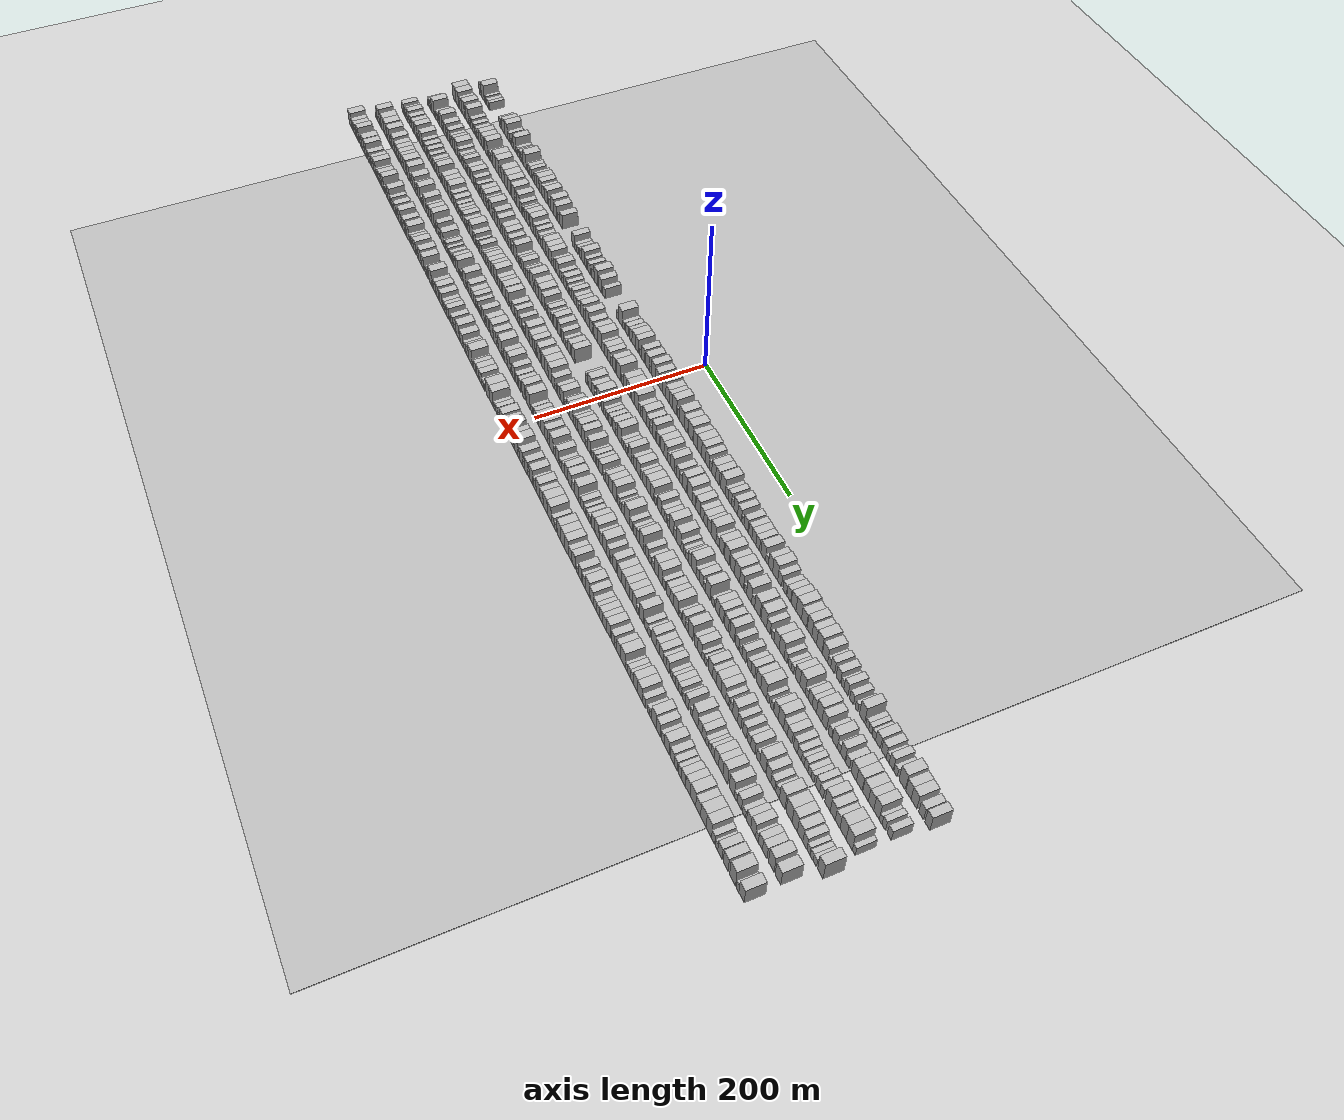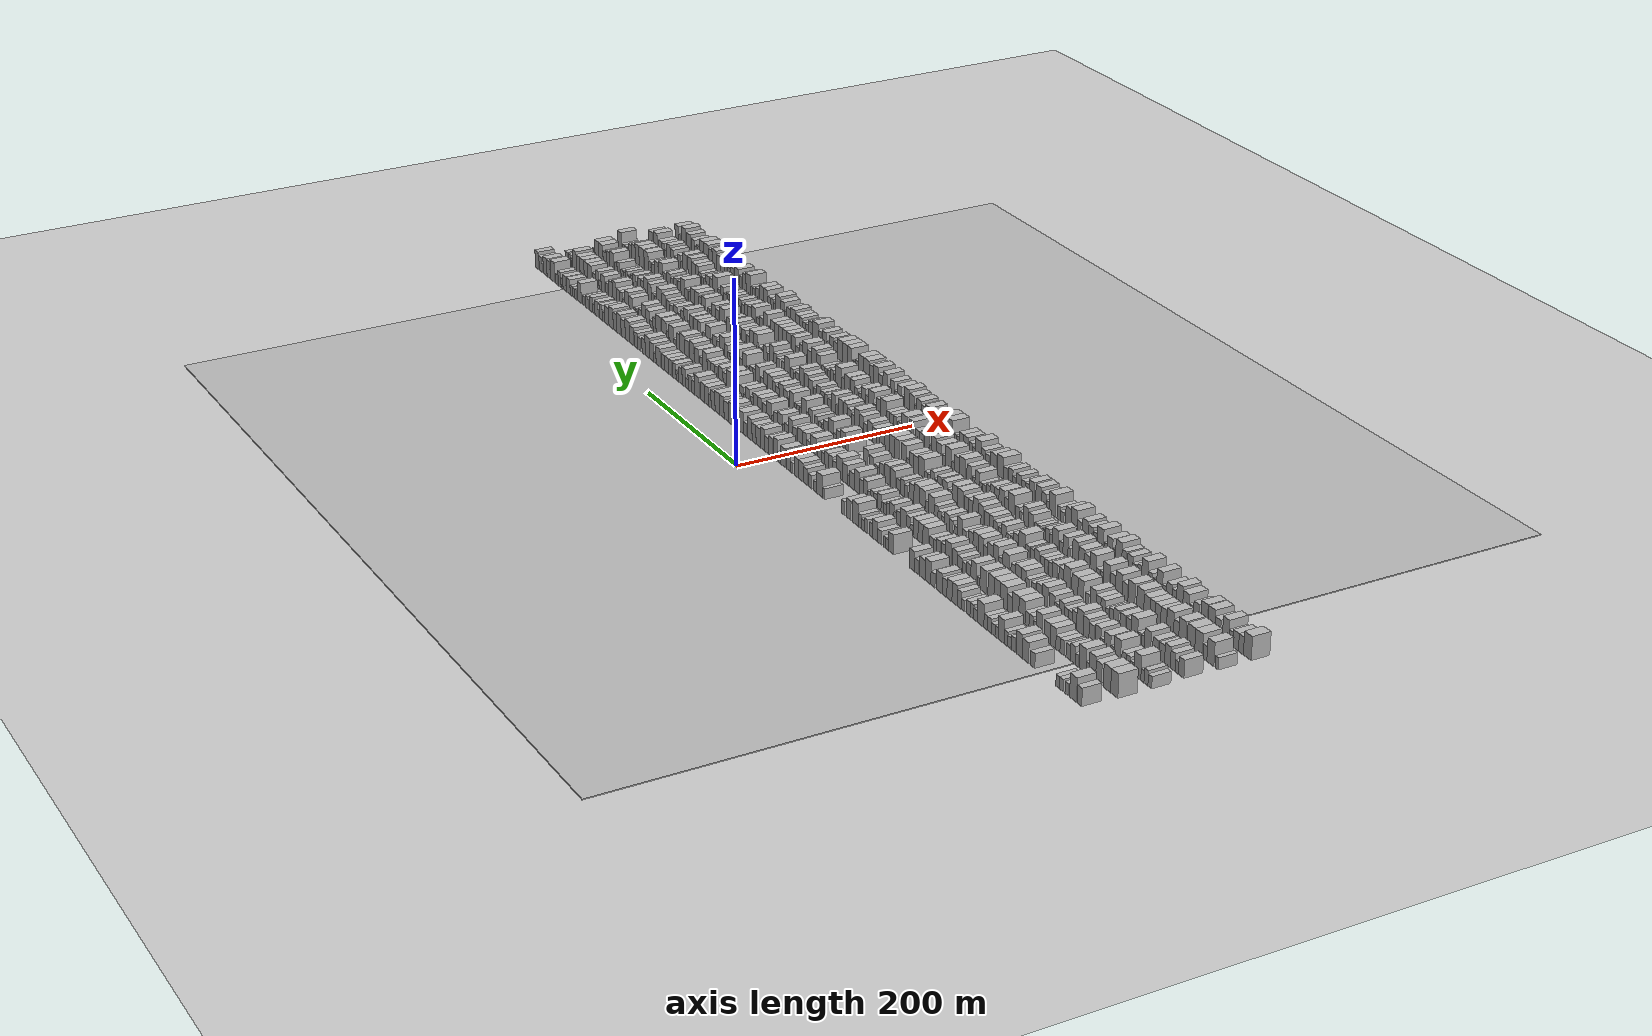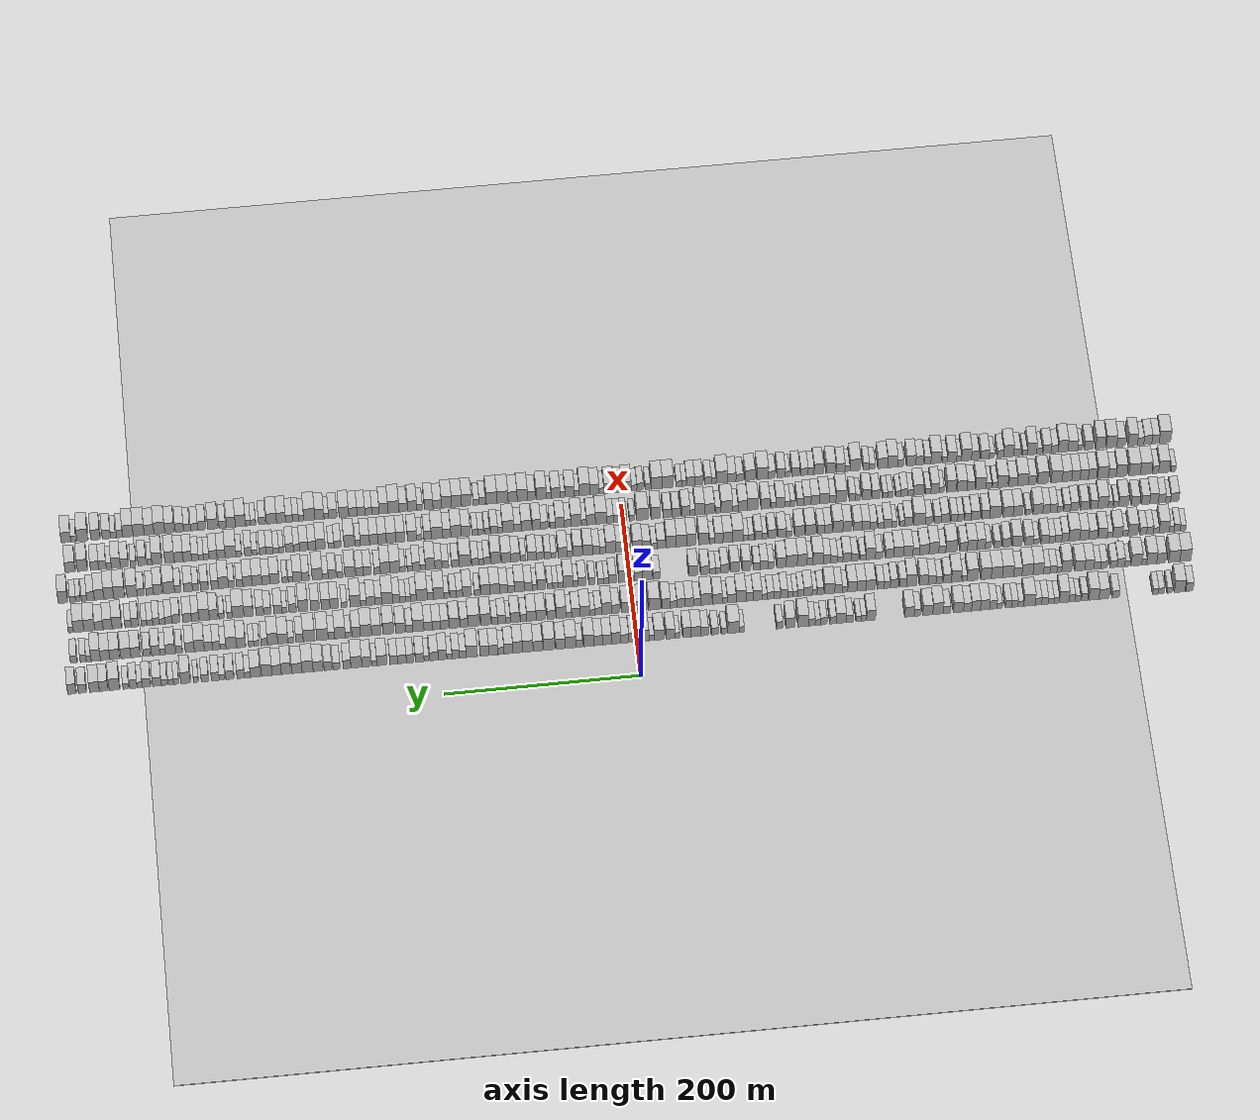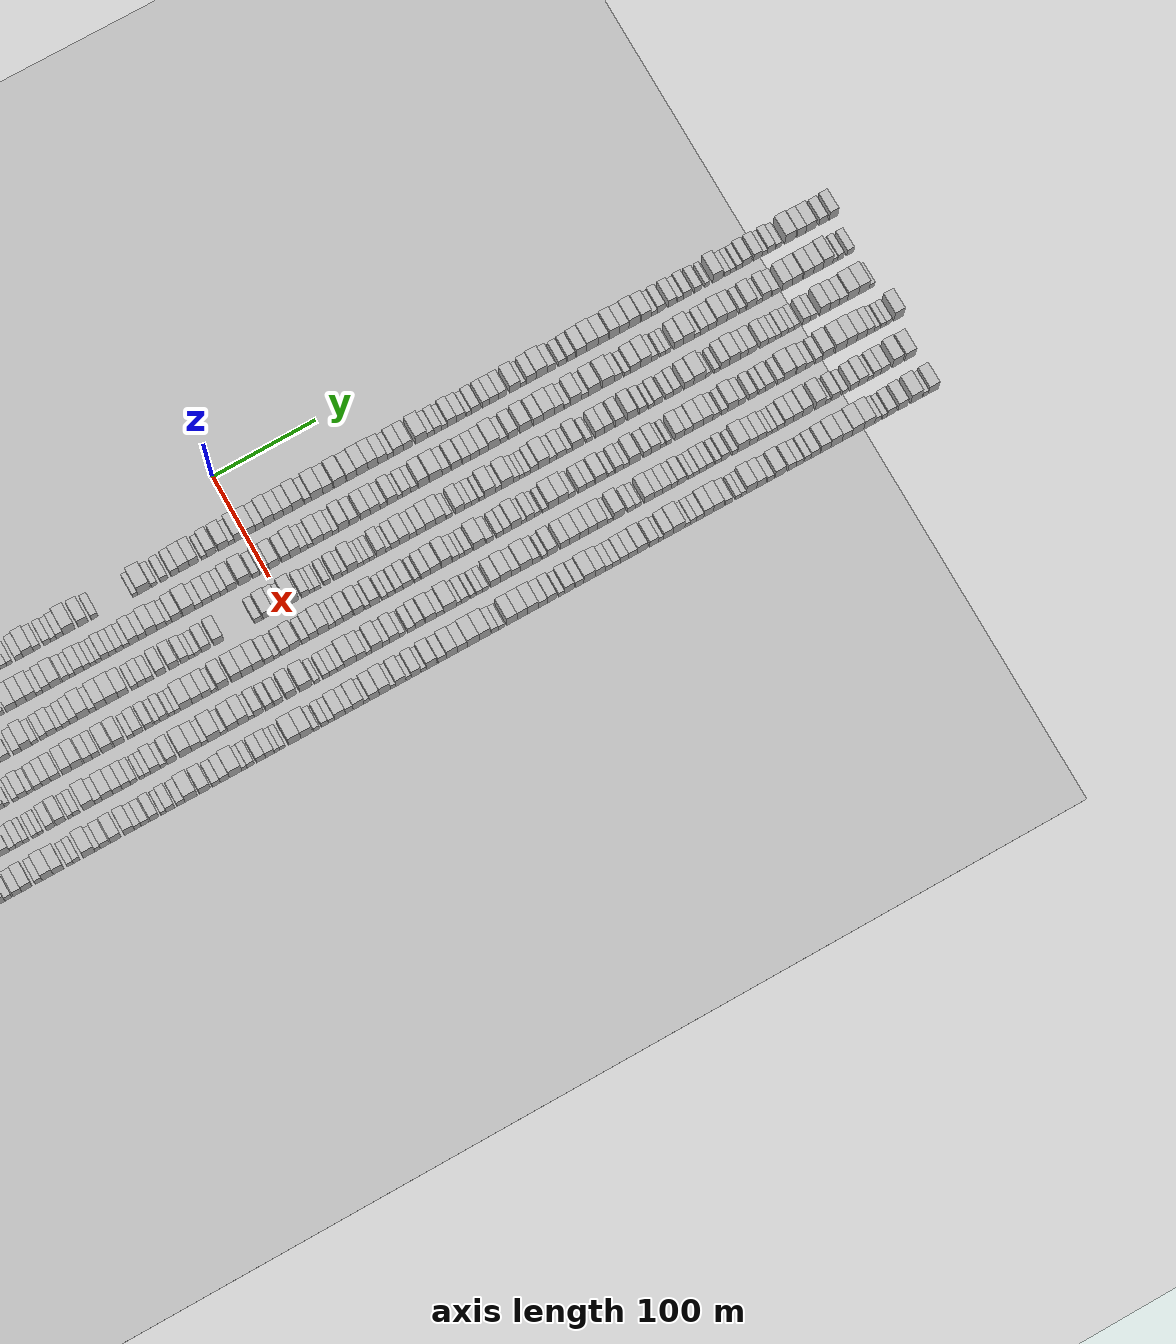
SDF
<?xml version="1.0" encoding="utf-8"?>

<sdf version="1.6">

   <world name="default">

      <gui fullscreen="0">

         <camera name="user_camera">

            <pose>-15 0 4.57585 0 0 0</pose>

            <view_controller>orbit</view_controller>

         </camera>

      </gui>

      <scene>

         <sky>

           <clouds>

             <speed>12</speed>

           </clouds>

         </sky>

         <ambient>0.4 0.4 0.4 1</ambient>

         <background>0.7 0.7 0.7 1</background>

         <shadows>1</shadows>

      </scene>

      <gravity>0 0 -9.8066</gravity>

      <magnetic_field>6e-06 2.3e-05 -4.2e-05</magnetic_field>

      <physics default="0" name="default_physics" type="ode">

         <ode>

            <solver>

               <type>quick</type>

               <iters>10</iters>

               <sor>1.0</sor>

               <use_dynamic_moi_rescaling>0</use_dynamic_moi_rescaling>

            </solver>

            <constraints>

               <cfm>0</cfm>

               <erp>0.2</erp>

               <contact_max_correcting_vel>100</contact_max_correcting_vel>

               <contact_surface_layer>0.001</contact_surface_layer>

            </constraints>

         </ode>

         <max_step_size>0.004</max_step_size>

         <real_time_factor>1</real_time_factor>

         <real_time_update_rate>250</real_time_update_rate>

      </physics>

      <light name="sun" type="directional">

         <cast_shadows>1</cast_shadows>

         <pose>0 0 10 0 0 0</pose>

         <diffuse>0.8 0.8 0.8 1</diffuse>

         <specular>0.2 0.2 0.2 1</specular>

         <attenuation>

            <range>1000</range>

            <constant>0.9</constant>

            <linear>0.01</linear>

            <quadratic>0.001</quadratic>

         </attenuation>

         <direction>-0.5 0.1 -0.9</direction>

      </light>

      <include>

         <name>ground_plane_1</name>

         <uri>model://HANNAS_ground_plane</uri>

         <pose>0 0 0  0 0 0</pose>

      </include>

      <include>

         <name>ground_plane_2</name>

         <uri>model://HANNAS_ground_plane</uri>

         <pose>100 0 0  0 0 0</pose>

      </include>

      <model name="building_1">

         <static>1</static>

         <pose frame="">50.0000 -563.3075 0 0.000000 0.000000 0.000000</pose>

         <link name="link">

            <pose frame="">0 0 9.00 0 0 0</pose>

            <collision name="collision">

               <geometry>

                  <box>

                     <size>20.0000 7.3849 18.0000</size>

                  </box>

               </geometry>

               <max_contacts>10</max_contacts>

               <surface>

                  <contact>

                     <ode/>

                  </contact>

                  <bounce/>

                  <friction>

                     <torsional>

                        <ode/>

                     </torsional>

                     <ode/>

                  </friction>

               </surface>

            </collision>

            <visual name="visual">

               <cast_shadows>0</cast_shadows>

               <geometry>

                  <box>

                     <size>20.0000 7.3849 18.0000</size>

                  </box>

               </geometry>

               <material>

                  <script>

                     <uri>model://HANNAS_wall/materials/scripts</uri>

                     <uri>model://HANNAS_wall/materials/textures</uri>

                     <name>vrc/HANNAS_wall</name>

                  </script>

               </material>

            </visual>

            <self_collide>0</self_collide>

            <enable_wind>0</enable_wind>

            <kinematic>0</kinematic>

         </link>

      </model>

      <model name="building_2">

         <static>1</static>

         <pose frame="">50.0000 -553.1551 0 0.000000 0.000000 0.000000</pose>

         <link name="link">

            <pose frame="">0 0 12.00 0 0 0</pose>

            <collision name="collision">

               <geometry>

                  <box>

                     <size>20.0000 10.9201 24.0000</size>

                  </box>

               </geometry>

               <max_contacts>10</max_contacts>

               <surface>

                  <contact>

                     <ode/>

                  </contact>

                  <bounce/>

                  <friction>

                     <torsional>

                        <ode/>

                     </torsional>

                     <ode/>

                  </friction>

               </surface>

            </collision>

            <visual name="visual">

               <cast_shadows>0</cast_shadows>

               <geometry>

                  <box>

                     <size>20.0000 10.9201 24.0000</size>

                  </box>

               </geometry>

               <material>

                  <script>

                     <uri>model://HANNAS_wall/materials/scripts</uri>

                     <uri>model://HANNAS_wall/materials/textures</uri>

                     <name>vrc/HANNAS_wall</name>

                  </script>

               </material>

            </visual>

            <self_collide>0</self_collide>

            <enable_wind>0</enable_wind>

            <kinematic>0</kinematic>

         </link>

      </model>

      <model name="building_3">

         <static>1</static>

         <pose frame="">50.0000 -543.0304 0 0.000000 0.000000 0.000000</pose>

         <link name="link">

            <pose frame="">0 0 6.00 0 0 0</pose>

            <collision name="collision">

               <geometry>

                  <box>

                     <size>20.0000 5.3293 12.0000</size>

                  </box>

               </geometry>

               <max_contacts>10</max_contacts>

               <surface>

                  <contact>

                     <ode/>

                  </contact>

                  <bounce/>

                  <friction>

                     <torsional>

                        <ode/>

                     </torsional>

                     <ode/>

                  </friction>

               </surface>

            </collision>

            <visual name="visual">

               <cast_shadows>0</cast_shadows>

               <geometry>

                  <box>

                     <size>20.0000 5.3293 12.0000</size>

                  </box>

               </geometry>

               <material>

                  <script>

                     <uri>model://HANNAS_wall/materials/scripts</uri>

                     <uri>model://HANNAS_wall/materials/textures</uri>

                     <name>vrc/HANNAS_wall</name>

                  </script>

               </material>

            </visual>

            <self_collide>0</self_collide>

            <enable_wind>0</enable_wind>

            <kinematic>0</kinematic>

         </link>

      </model>

      <model name="building_4">

         <static>1</static>

         <pose frame="">50.0000 -534.4104 0 0.000000 0.000000 0.000000</pose>

         <link name="link">

            <pose frame="">0 0 6.00 0 0 0</pose>

            <collision name="collision">

               <geometry>

                  <box>

                     <size>20.0000 5.9105 12.0000</size>

                  </box>

               </geometry>

               <max_contacts>10</max_contacts>

               <surface>

                  <contact>

                     <ode/>

                  </contact>

                  <bounce/>

                  <friction>

                     <torsional>

                        <ode/>

                     </torsional>

                     <ode/>

                  </friction>

               </surface>

            </collision>

            <visual name="visual">

               <cast_shadows>0</cast_shadows>

               <geometry>

                  <box>

                     <size>20.0000 5.9105 12.0000</size>

                  </box>

               </geometry>

               <material>

                  <script>

                     <uri>model://HANNAS_wall/materials/scripts</uri>

                     <uri>model://HANNAS_wall/materials/textures</uri>

                     <name>vrc/HANNAS_wall</name>

                  </script>

               </material>

            </visual>

            <self_collide>0</self_collide>

            <enable_wind>0</enable_wind>

            <kinematic>0</kinematic>

         </link>

      </model>

      <model name="building_5">

         <static>1</static>

         <pose frame="">50.0000 -528.5339 0 0.000000 0.000000 0.000000</pose>

         <link name="link">

            <pose frame="">0 0 6.00 0 0 0</pose>

            <collision name="collision">

               <geometry>

                  <box>

                     <size>20.0000 5.8426 12.0000</size>

                  </box>

               </geometry>

               <max_contacts>10</max_contacts>

               <surface>

                  <contact>

                     <ode/>

                  </contact>

                  <bounce/>

                  <friction>

                     <torsional>

                        <ode/>

                     </torsional>

                     <ode/>

                  </friction>

               </surface>

            </collision>

            <visual name="visual">

               <cast_shadows>0</cast_shadows>

               <geometry>

                  <box>

                     <size>20.0000 5.8426 12.0000</size>

                  </box>

               </geometry>

               <material>

                  <script>

                     <uri>model://HANNAS_wall/materials/scripts</uri>

                     <uri>model://HANNAS_wall/materials/textures</uri>

                     <name>vrc/HANNAS_wall</name>

                  </script>

               </material>

            </visual>

            <self_collide>0</self_collide>

            <enable_wind>0</enable_wind>

            <kinematic>0</kinematic>

         </link>

      </model>

      <model name="building_6">

         <static>1</static>

         <pose frame="">50.0000 -487.5675 0 0.000000 0.000000 0.000000</pose>

         <link name="link">

            <pose frame="">0 0 7.50 0 0 0</pose>

            <collision name="collision">

               <geometry>

                  <box>

                     <size>20.0000 7.3633 15.0000</size>

                  </box>

               </geometry>

               <max_contacts>10</max_contacts>

               <surface>

                  <contact>

                     <ode/>

                  </contact>

                  <bounce/>

                  <friction>

                     <torsional>

                        <ode/>

                     </torsional>

                     <ode/>

                  </friction>

               </surface>

            </collision>

            <visual name="visual">

               <cast_shadows>0</cast_shadows>

               <geometry>

                  <box>

                     <size>20.0000 7.3633 15.0000</size>

                  </box>

               </geometry>

               <material>

                  <script>

                     <uri>model://HANNAS_wall/materials/scripts</uri>

                     <uri>model://HANNAS_wall/materials/textures</uri>

                     <name>vrc/HANNAS_wall</name>

                  </script>

               </material>

            </visual>

            <self_collide>0</self_collide>

            <enable_wind>0</enable_wind>

            <kinematic>0</kinematic>

         </link>

      </model>

      <model name="building_7">

         <static>1</static>

         <pose frame="">50.0000 -475.6671 0 0.000000 0.000000 0.000000</pose>

         <link name="link">

            <pose frame="">0 0 10.50 0 0 0</pose>

            <collision name="collision">

               <geometry>

                  <box>

                     <size>20.0000 10.4374 21.0000</size>

                  </box>

               </geometry>

               <max_contacts>10</max_contacts>

               <surface>

                  <contact>

                     <ode/>

                  </contact>

                  <bounce/>

                  <friction>

                     <torsional>

                        <ode/>

                     </torsional>

                     <ode/>

                  </friction>

               </surface>

            </collision>

            <visual name="visual">

               <cast_shadows>0</cast_shadows>

               <geometry>

                  <box>

                     <size>20.0000 10.4374 21.0000</size>

                  </box>

               </geometry>

               <material>

                  <script>

                     <uri>model://HANNAS_wall/materials/scripts</uri>

                     <uri>model://HANNAS_wall/materials/textures</uri>

                     <name>vrc/HANNAS_wall</name>

                  </script>

               </material>

            </visual>

            <self_collide>0</self_collide>

            <enable_wind>0</enable_wind>

            <kinematic>0</kinematic>

         </link>

      </model>

      <model name="building_8">

         <static>1</static>

         <pose frame="">50.0000 -465.2622 0 0.000000 0.000000 0.000000</pose>

         <link name="link">

            <pose frame="">0 0 12.00 0 0 0</pose>

            <collision name="collision">

               <geometry>

                  <box>

                     <size>20.0000 10.3725 24.0000</size>

                  </box>

               </geometry>

               <max_contacts>10</max_contacts>

               <surface>

                  <contact>

                     <ode/>

                  </contact>

                  <bounce/>

                  <friction>

                     <torsional>

                        <ode/>

                     </torsional>

                     <ode/>

                  </friction>

               </surface>

            </collision>

            <visual name="visual">

               <cast_shadows>0</cast_shadows>

               <geometry>

                  <box>

                     <size>20.0000 10.3725 24.0000</size>

                  </box>

               </geometry>

               <material>

                  <script>

                     <uri>model://HANNAS_wall/materials/scripts</uri>

                     <uri>model://HANNAS_wall/materials/textures</uri>

                     <name>vrc/HANNAS_wall</name>

                  </script>

               </material>

            </visual>

            <self_collide>0</self_collide>

            <enable_wind>0</enable_wind>

            <kinematic>0</kinematic>

         </link>

      </model>

      <model name="building_9">

         <static>1</static>

         <pose frame="">50.0000 -455.7226 0 0.000000 0.000000 0.000000</pose>

         <link name="link">

            <pose frame="">0 0 7.50 0 0 0</pose>

            <collision name="collision">

               <geometry>

                  <box>

                     <size>20.0000 6.7065 15.0000</size>

                  </box>

               </geometry>

               <max_contacts>10</max_contacts>

               <surface>

                  <contact>

                     <ode/>

                  </contact>

                  <bounce/>

                  <friction>

                     <torsional>

                        <ode/>

                     </torsional>

                     <ode/>

                  </friction>

               </surface>

            </collision>

            <visual name="visual">

               <cast_shadows>0</cast_shadows>

               <geometry>

                  <box>

                     <size>20.0000 6.7065 15.0000</size>

                  </box>

               </geometry>

               <material>

                  <script>

                     <uri>model://HANNAS_wall/materials/scripts</uri>

                     <uri>model://HANNAS_wall/materials/textures</uri>

                     <name>vrc/HANNAS_wall</name>

                  </script>

               </material>

            </visual>

            <self_collide>0</self_collide>

            <enable_wind>0</enable_wind>

            <kinematic>0</kinematic>

         </link>

      </model>

      <model name="building_10">

         <static>1</static>

         <pose frame="">50.0000 -448.6461 0 0.000000 0.000000 0.000000</pose>

         <link name="link">

            <pose frame="">0 0 6.00 0 0 0</pose>

            <collision name="collision">

               <geometry>

                  <box>

                     <size>20.0000 5.4464 12.0000</size>

                  </box>

               </geometry>

               <max_contacts>10</max_contacts>

               <surface>

                  <contact>

                     <ode/>

                  </contact>

                  <bounce/>

                  <friction>

                     <torsional>

                        <ode/>

                     </torsional>

                     <ode/>

                  </friction>

               </surface>

            </collision>

            <visual name="visual">

               <cast_shadows>0</cast_shadows>

               <geometry>

                  <box>

                     <size>20.0000 5.4464 12.0000</size>

                  </box>

               </geometry>

               <material>

                  <script>

                     <uri>model://HANNAS_wall/materials/scripts</uri>

                     <uri>model://HANNAS_wall/materials/textures</uri>

                     <name>vrc/HANNAS_wall</name>

                  </script>

               </material>

            </visual>

            <self_collide>0</self_collide>

            <enable_wind>0</enable_wind>

            <kinematic>0</kinematic>

         </link>

      </model>

      <model name="building_11">

         <static>1</static>

         <pose frame="">50.0000 -442.8181 0 0.000000 0.000000 0.000000</pose>

         <link name="link">

            <pose frame="">0 0 7.50 0 0 0</pose>

            <collision name="collision">

               <geometry>

                  <box>

                     <size>20.0000 6.2098 15.0000</size>

                  </box>

               </geometry>

               <max_contacts>10</max_contacts>

               <surface>

                  <contact>

                     <ode/>

                  </contact>

                  <bounce/>

                  <friction>

                     <torsional>

                        <ode/>

                     </torsional>

                     <ode/>

                  </friction>

               </surface>

            </collision>

            <visual name="visual">

               <cast_shadows>0</cast_shadows>

               <geometry>

                  <box>

                     <size>20.0000 6.2098 15.0000</size>

                  </box>

               </geometry>

               <material>

                  <script>

                     <uri>model://HANNAS_wall/materials/scripts</uri>

                     <uri>model://HANNAS_wall/materials/textures</uri>

                     <name>vrc/HANNAS_wall</name>

                  </script>

               </material>

            </visual>

            <self_collide>0</self_collide>

            <enable_wind>0</enable_wind>

            <kinematic>0</kinematic>

         </link>

      </model>

      <model name="building_12">

         <static>1</static>

         <pose frame="">50.0000 -434.7869 0 0.000000 0.000000 0.000000</pose>

         <link name="link">

            <pose frame="">0 0 12.00 0 0 0</pose>

            <collision name="collision">

               <geometry>

                  <box>

                     <size>20.0000 9.8526 24.0000</size>

                  </box>

               </geometry>

               <max_contacts>10</max_contacts>

               <surface>

                  <contact>

                     <ode/>

                  </contact>

                  <bounce/>

                  <friction>

                     <torsional>

                        <ode/>

                     </torsional>

                     <ode/>

                  </friction>

               </surface>

            </collision>

            <visual name="visual">

               <cast_shadows>0</cast_shadows>

               <geometry>

                  <box>

                     <size>20.0000 9.8526 24.0000</size>

                  </box>

               </geometry>

               <material>

                  <script>

                     <uri>model://HANNAS_wall/materials/scripts</uri>

                     <uri>model://HANNAS_wall/materials/textures</uri>

                     <name>vrc/HANNAS_wall</name>

                  </script>

               </material>

            </visual>

            <self_collide>0</self_collide>

            <enable_wind>0</enable_wind>

            <kinematic>0</kinematic>

         </link>

      </model>

      <model name="building_13">

         <static>1</static>

         <pose frame="">50.0000 -427.0802 0 0.000000 0.000000 0.000000</pose>

         <link name="link">

            <pose frame="">0 0 6.00 0 0 0</pose>

            <collision name="collision">

               <geometry>

                  <box>

                     <size>20.0000 5.5608 12.0000</size>

                  </box>

               </geometry>

               <max_contacts>10</max_contacts>

               <surface>

                  <contact>

                     <ode/>

                  </contact>

                  <bounce/>

                  <friction>

                     <torsional>

                        <ode/>

                     </torsional>

                     <ode/>

                  </friction>

               </surface>

            </collision>

            <visual name="visual">

               <cast_shadows>0</cast_shadows>

               <geometry>

                  <box>

                     <size>20.0000 5.5608 12.0000</size>

                  </box>

               </geometry>

               <material>

                  <script>

                     <uri>model://HANNAS_wall/materials/scripts</uri>

                     <uri>model://HANNAS_wall/materials/textures</uri>

                     <name>vrc/HANNAS_wall</name>

                  </script>

               </material>

            </visual>

            <self_collide>0</self_collide>

            <enable_wind>0</enable_wind>

            <kinematic>0</kinematic>

         </link>

      </model>

      <model name="building_14">

         <static>1</static>

         <pose frame="">50.0000 -421.3700 0 0.000000 0.000000 0.000000</pose>

         <link name="link">

            <pose frame="">0 0 6.00 0 0 0</pose>

            <collision name="collision">

               <geometry>

                  <box>

                     <size>20.0000 5.8594 12.0000</size>

                  </box>

               </geometry>

               <max_contacts>10</max_contacts>

               <surface>

                  <contact>

                     <ode/>

                  </contact>

                  <bounce/>

                  <friction>

                     <torsional>

                        <ode/>

                     </torsional>

                     <ode/>

                  </friction>

               </surface>

            </collision>

            <visual name="visual">

               <cast_shadows>0</cast_shadows>

               <geometry>

                  <box>

                     <size>20.0000 5.8594 12.0000</size>

                  </box>

               </geometry>

               <material>

                  <script>

                     <uri>model://HANNAS_wall/materials/scripts</uri>

                     <uri>model://HANNAS_wall/materials/textures</uri>

                     <name>vrc/HANNAS_wall</name>

                  </script>

               </material>

            </visual>

            <self_collide>0</self_collide>

            <enable_wind>0</enable_wind>

            <kinematic>0</kinematic>

         </link>

      </model>

      <model name="building_15">

         <static>1</static>

         <pose frame="">50.0000 -415.0741 0 0.000000 0.000000 0.000000</pose>

         <link name="link">

            <pose frame="">0 0 7.50 0 0 0</pose>

            <collision name="collision">

               <geometry>

                  <box>

                     <size>20.0000 6.7324 15.0000</size>

                  </box>

               </geometry>

               <max_contacts>10</max_contacts>

               <surface>

                  <contact>

                     <ode/>

                  </contact>

                  <bounce/>

                  <friction>

                     <torsional>

                        <ode/>

                     </torsional>

                     <ode/>

                  </friction>

               </surface>

            </collision>

            <visual name="visual">

               <cast_shadows>0</cast_shadows>

               <geometry>

                  <box>

                     <size>20.0000 6.7324 15.0000</size>

                  </box>

               </geometry>

               <material>

                  <script>

                     <uri>model://HANNAS_wall/materials/scripts</uri>

                     <uri>model://HANNAS_wall/materials/textures</uri>

                     <name>vrc/HANNAS_wall</name>

                  </script>

               </material>

            </visual>

            <self_collide>0</self_collide>

            <enable_wind>0</enable_wind>

            <kinematic>0</kinematic>

         </link>

      </model>

      <model name="building_16">

         <static>1</static>

         <pose frame="">50.0000 -408.4143 0 0.000000 0.000000 0.000000</pose>

         <link name="link">

            <pose frame="">0 0 7.50 0 0 0</pose>

            <collision name="collision">

               <geometry>

                  <box>

                     <size>20.0000 6.5873 15.0000</size>

                  </box>

               </geometry>

               <max_contacts>10</max_contacts>

               <surface>

                  <contact>

                     <ode/>

                  </contact>

                  <bounce/>

                  <friction>

                     <torsional>

                        <ode/>

                     </torsional>

                     <ode/>

                  </friction>

               </surface>

            </collision>

            <visual name="visual">

               <cast_shadows>0</cast_shadows>

               <geometry>

                  <box>

                     <size>20.0000 6.5873 15.0000</size>

                  </box>

               </geometry>

               <material>

                  <script>

                     <uri>model://HANNAS_wall/materials/scripts</uri>

                     <uri>model://HANNAS_wall/materials/textures</uri>

                     <name>vrc/HANNAS_wall</name>

                  </script>

               </material>

            </visual>

            <self_collide>0</self_collide>

            <enable_wind>0</enable_wind>

            <kinematic>0</kinematic>

         </link>

      </model>

      <model name="building_17">

         <static>1</static>

         <pose frame="">50.0000 -399.2987 0 0.000000 0.000000 0.000000</pose>

         <link name="link">

            <pose frame="">0 0 12.00 0 0 0</pose>

            <collision name="collision">

               <geometry>

                  <box>

                     <size>20.0000 11.6438 24.0000</size>

                  </box>

               </geometry>

               <max_contacts>10</max_contacts>

               <surface>

                  <contact>

                     <ode/>

                  </contact>

                  <bounce/>

                  <friction>

                     <torsional>

                        <ode/>

                     </torsional>

                     <ode/>

                  </friction>

               </surface>

            </collision>

            <visual name="visual">

               <cast_shadows>0</cast_shadows>

               <geometry>

                  <box>

                     <size>20.0000 11.6438 24.0000</size>

                  </box>

               </geometry>

               <material>

                  <script>

                     <uri>model://HANNAS_wall/materials/scripts</uri>

                     <uri>model://HANNAS_wall/materials/textures</uri>

                     <name>vrc/HANNAS_wall</name>

                  </script>

               </material>

            </visual>

            <self_collide>0</self_collide>

            <enable_wind>0</enable_wind>

            <kinematic>0</kinematic>

         </link>

      </model>

      <model name="building_18">

         <static>1</static>

         <pose frame="">50.0000 -390.5095 0 0.000000 0.000000 0.000000</pose>

         <link name="link">

            <pose frame="">0 0 6.00 0 0 0</pose>

            <collision name="collision">

               <geometry>

                  <box>

                     <size>20.0000 5.9346 12.0000</size>

                  </box>

               </geometry>

               <max_contacts>10</max_contacts>

               <surface>

                  <contact>

                     <ode/>

                  </contact>

                  <bounce/>

                  <friction>

                     <torsional>

                        <ode/>

                     </torsional>

                     <ode/>

                  </friction>

               </surface>

            </collision>

            <visual name="visual">

               <cast_shadows>0</cast_shadows>

               <geometry>

                  <box>

                     <size>20.0000 5.9346 12.0000</size>

                  </box>

               </geometry>

               <material>

                  <script>

                     <uri>model://HANNAS_wall/materials/scripts</uri>

                     <uri>model://HANNAS_wall/materials/textures</uri>

                     <name>vrc/HANNAS_wall</name>

                  </script>

               </material>

            </visual>

            <self_collide>0</self_collide>

            <enable_wind>0</enable_wind>

            <kinematic>0</kinematic>

         </link>

      </model>

      <model name="building_19">

         <static>1</static>

         <pose frame="">50.0000 -384.2496 0 0.000000 0.000000 0.000000</pose>

         <link name="link">

            <pose frame="">0 0 7.50 0 0 0</pose>

            <collision name="collision">

               <geometry>

                  <box>

                     <size>20.0000 6.5854 15.0000</size>

                  </box>

               </geometry>

               <max_contacts>10</max_contacts>

               <surface>

                  <contact>

                     <ode/>

                  </contact>

                  <bounce/>

                  <friction>

                     <torsional>

                        <ode/>

                     </torsional>

                     <ode/>

                  </friction>

               </surface>

            </collision>

            <visual name="visual">

               <cast_shadows>0</cast_shadows>

               <geometry>

                  <box>

                     <size>20.0000 6.5854 15.0000</size>

                  </box>

               </geometry>

               <material>

                  <script>

                     <uri>model://HANNAS_wall/materials/scripts</uri>

                     <uri>model://HANNAS_wall/materials/textures</uri>

                     <name>vrc/HANNAS_wall</name>

                  </script>

               </material>

            </visual>

            <self_collide>0</self_collide>

            <enable_wind>0</enable_wind>

            <kinematic>0</kinematic>

         </link>

      </model>

      <model name="building_20">

         <static>1</static>

         <pose frame="">50.0000 -377.7349 0 0.000000 0.000000 0.000000</pose>

         <link name="link">

            <pose frame="">0 0 7.50 0 0 0</pose>

            <collision name="collision">

               <geometry>

                  <box>

                     <size>20.0000 6.4440 15.0000</size>

                  </box>

               </geometry>

               <max_contacts>10</max_contacts>

               <surface>

                  <contact>

                     <ode/>

                  </contact>

                  <bounce/>

                  <friction>

                     <torsional>

                        <ode/>

                     </torsional>

                     <ode/>

                  </friction>

               </surface>

            </collision>

            <visual name="visual">

               <cast_shadows>0</cast_shadows>

               <geometry>

                  <box>

                     <size>20.0000 6.4440 15.0000</size>

                  </box>

               </geometry>

               <material>

                  <script>

                     <uri>model://HANNAS_wall/materials/scripts</uri>

                     <uri>model://HANNAS_wall/materials/textures</uri>

                     <name>vrc/HANNAS_wall</name>

                  </script>

               </material>

            </visual>

            <self_collide>0</self_collide>

            <enable_wind>0</enable_wind>

            <kinematic>0</kinematic>

         </link>

      </model>

      <model name="building_21">

         <static>1</static>

         <pose frame="">50.0000 -368.7472 0 0.000000 0.000000 0.000000</pose>

         <link name="link">

            <pose frame="">0 0 6.00 0 0 0</pose>

            <collision name="collision">

               <geometry>

                  <box>

                     <size>20.0000 5.5313 12.0000</size>

                  </box>

               </geometry>

               <max_contacts>10</max_contacts>

               <surface>

                  <contact>

                     <ode/>

                  </contact>

                  <bounce/>

                  <friction>

                     <torsional>

                        <ode/>

                     </torsional>

                     <ode/>

                  </friction>

               </surface>

            </collision>

            <visual name="visual">

               <cast_shadows>0</cast_shadows>

               <geometry>

                  <box>

                     <size>20.0000 5.5313 12.0000</size>

                  </box>

               </geometry>

               <material>

                  <script>

                     <uri>model://HANNAS_wall/materials/scripts</uri>

                     <uri>model://HANNAS_wall/materials/textures</uri>

                     <name>vrc/HANNAS_wall</name>

                  </script>

               </material>

            </visual>

            <self_collide>0</self_collide>

            <enable_wind>0</enable_wind>

            <kinematic>0</kinematic>

         </link>

      </model>

      <model name="building_22">

         <static>1</static>

         <pose frame="">50.0000 -362.2140 0 0.000000 0.000000 0.000000</pose>

         <link name="link">

            <pose frame="">0 0 9.00 0 0 0</pose>

            <collision name="collision">

               <geometry>

                  <box>

                     <size>20.0000 7.5350 18.0000</size>

                  </box>

               </geometry>

               <max_contacts>10</max_contacts>

               <surface>

                  <contact>

                     <ode/>

                  </contact>

                  <bounce/>

                  <friction>

                     <torsional>

                        <ode/>

                     </torsional>

                     <ode/>

                  </friction>

               </surface>

            </collision>

            <visual name="visual">

               <cast_shadows>0</cast_shadows>

               <geometry>

                  <box>

                     <size>20.0000 7.5350 18.0000</size>

                  </box>

               </geometry>

               <material>

                  <script>

                     <uri>model://HANNAS_wall/materials/scripts</uri>

                     <uri>model://HANNAS_wall/materials/textures</uri>

                     <name>vrc/HANNAS_wall</name>

                  </script>

               </material>

            </visual>

            <self_collide>0</self_collide>

            <enable_wind>0</enable_wind>

            <kinematic>0</kinematic>

         </link>

      </model>

      <model name="building_23">

         <static>1</static>

         <pose frame="">50.0000 -353.7512 0 0.000000 0.000000 0.000000</pose>

         <link name="link">

            <pose frame="">0 0 10.50 0 0 0</pose>

            <collision name="collision">

               <geometry>

                  <box>

                     <size>20.0000 9.3906 21.0000</size>

                  </box>

               </geometry>

               <max_contacts>10</max_contacts>

               <surface>

                  <contact>

                     <ode/>

                  </contact>

                  <bounce/>

                  <friction>

                     <torsional>

                        <ode/>

                     </torsional>

                     <ode/>

                  </friction>

               </surface>

            </collision>

            <visual name="visual">

               <cast_shadows>0</cast_shadows>

               <geometry>

                  <box>

                     <size>20.0000 9.3906 21.0000</size>

                  </box>

               </geometry>

               <material>

                  <script>

                     <uri>model://HANNAS_wall/materials/scripts</uri>

                     <uri>model://HANNAS_wall/materials/textures</uri>

                     <name>vrc/HANNAS_wall</name>

                  </script>

               </material>

            </visual>

            <self_collide>0</self_collide>

            <enable_wind>0</enable_wind>

            <kinematic>0</kinematic>

         </link>

      </model>

      <model name="building_24">

         <static>1</static>

         <pose frame="">50.0000 -344.5067 0 0.000000 0.000000 0.000000</pose>

         <link name="link">

            <pose frame="">0 0 10.50 0 0 0</pose>

            <collision name="collision">

               <geometry>

                  <box>

                     <size>20.0000 9.0984 21.0000</size>

                  </box>

               </geometry>

               <max_contacts>10</max_contacts>

               <surface>

                  <contact>

                     <ode/>

                  </contact>

                  <bounce/>

                  <friction>

                     <torsional>

                        <ode/>

                     </torsional>

                     <ode/>

                  </friction>

               </surface>

            </collision>

            <visual name="visual">

               <cast_shadows>0</cast_shadows>

               <geometry>

                  <box>

                     <size>20.0000 9.0984 21.0000</size>

                  </box>

               </geometry>

               <material>

                  <script>

                     <uri>model://HANNAS_wall/materials/scripts</uri>

                     <uri>model://HANNAS_wall/materials/textures</uri>

                     <name>vrc/HANNAS_wall</name>

                  </script>

               </material>

            </visual>

            <self_collide>0</self_collide>

            <enable_wind>0</enable_wind>

            <kinematic>0</kinematic>

         </link>

      </model>

      <model name="building_25">

         <static>1</static>

         <pose frame="">50.0000 -335.8646 0 0.000000 0.000000 0.000000</pose>

         <link name="link">

            <pose frame="">0 0 9.00 0 0 0</pose>

            <collision name="collision">

               <geometry>

                  <box>

                     <size>20.0000 8.1859 18.0000</size>

                  </box>

               </geometry>

               <max_contacts>10</max_contacts>

               <surface>

                  <contact>

                     <ode/>

                  </contact>

                  <bounce/>

                  <friction>

                     <torsional>

                        <ode/>

                     </torsional>

                     <ode/>

                  </friction>

               </surface>

            </collision>

            <visual name="visual">

               <cast_shadows>0</cast_shadows>

               <geometry>

                  <box>

                     <size>20.0000 8.1859 18.0000</size>

                  </box>

               </geometry>

               <material>

                  <script>

                     <uri>model://HANNAS_wall/materials/scripts</uri>

                     <uri>model://HANNAS_wall/materials/textures</uri>

                     <name>vrc/HANNAS_wall</name>

                  </script>

               </material>

            </visual>

            <self_collide>0</self_collide>

            <enable_wind>0</enable_wind>

            <kinematic>0</kinematic>

         </link>

      </model>

      <model name="building_26">

         <static>1</static>

         <pose frame="">50.0000 -326.6556 0 0.000000 0.000000 0.000000</pose>

         <link name="link">

            <pose frame="">0 0 10.50 0 0 0</pose>

            <collision name="collision">

               <geometry>

                  <box>

                     <size>20.0000 10.2320 21.0000</size>

                  </box>

               </geometry>

               <max_contacts>10</max_contacts>

               <surface>

                  <contact>

                     <ode/>

                  </contact>

                  <bounce/>

                  <friction>

                     <torsional>

                        <ode/>

                     </torsional>

                     <ode/>

                  </friction>

               </surface>

            </collision>

            <visual name="visual">

               <cast_shadows>0</cast_shadows>

               <geometry>

                  <box>

                     <size>20.0000 10.2320 21.0000</size>

                  </box>

               </geometry>

               <material>

                  <script>

                     <uri>model://HANNAS_wall/materials/scripts</uri>

                     <uri>model://HANNAS_wall/materials/textures</uri>

                     <name>vrc/HANNAS_wall</name>

                  </script>

               </material>

            </visual>

            <self_collide>0</self_collide>

            <enable_wind>0</enable_wind>

            <kinematic>0</kinematic>

         </link>

      </model>

      <model name="building_27">

         <static>1</static>

         <pose frame="">50.0000 -314.8026 0 0.000000 0.000000 0.000000</pose>

         <link name="link">

            <pose frame="">0 0 7.50 0 0 0</pose>

            <collision name="collision">

               <geometry>

                  <box>

                     <size>20.0000 7.4739 15.0000</size>

                  </box>

               </geometry>

               <max_contacts>10</max_contacts>

               <surface>

                  <contact>

                     <ode/>

                  </contact>

                  <bounce/>

                  <friction>

                     <torsional>

                        <ode/>

                     </torsional>

                     <ode/>

                  </friction>

               </surface>

            </collision>

            <visual name="visual">

               <cast_shadows>0</cast_shadows>

               <geometry>

                  <box>

                     <size>20.0000 7.4739 15.0000</size>

                  </box>

               </geometry>

               <material>

                  <script>

                     <uri>model://HANNAS_wall/materials/scripts</uri>

                     <uri>model://HANNAS_wall/materials/textures</uri>

                     <name>vrc/HANNAS_wall</name>

                  </script>

               </material>

            </visual>

            <self_collide>0</self_collide>

            <enable_wind>0</enable_wind>

            <kinematic>0</kinematic>

         </link>

      </model>

      <model name="building_28">

         <static>1</static>

         <pose frame="">50.0000 -305.7627 0 0.000000 0.000000 0.000000</pose>

         <link name="link">

            <pose frame="">0 0 12.00 0 0 0</pose>

            <collision name="collision">

               <geometry>

                  <box>

                     <size>20.0000 10.6061 24.0000</size>

                  </box>

               </geometry>

               <max_contacts>10</max_contacts>

               <surface>

                  <contact>

                     <ode/>

                  </contact>

                  <bounce/>

                  <friction>

                     <torsional>

                        <ode/>

                     </torsional>

                     <ode/>

                  </friction>

               </surface>

            </collision>

            <visual name="visual">

               <cast_shadows>0</cast_shadows>

               <geometry>

                  <box>

                     <size>20.0000 10.6061 24.0000</size>

                  </box>

               </geometry>

               <material>

                  <script>

                     <uri>model://HANNAS_wall/materials/scripts</uri>

                     <uri>model://HANNAS_wall/materials/textures</uri>

                     <name>vrc/HANNAS_wall</name>

                  </script>

               </material>

            </visual>

            <self_collide>0</self_collide>

            <enable_wind>0</enable_wind>

            <kinematic>0</kinematic>

         </link>

      </model>

      <model name="building_29">

         <static>1</static>

         <pose frame="">50.0000 -295.3721 0 0.000000 0.000000 0.000000</pose>

         <link name="link">

            <pose frame="">0 0 10.50 0 0 0</pose>

            <collision name="collision">

               <geometry>

                  <box>

                     <size>20.0000 10.1751 21.0000</size>

                  </box>

               </geometry>

               <max_contacts>10</max_contacts>

               <surface>

                  <contact>

                     <ode/>

                  </contact>

                  <bounce/>

                  <friction>

                     <torsional>

                        <ode/>

                     </torsional>

                     <ode/>

                  </friction>

               </surface>

            </collision>

            <visual name="visual">

               <cast_shadows>0</cast_shadows>

               <geometry>

                  <box>

                     <size>20.0000 10.1751 21.0000</size>

                  </box>

               </geometry>

               <material>

                  <script>

                     <uri>model://HANNAS_wall/materials/scripts</uri>

                     <uri>model://HANNAS_wall/materials/textures</uri>

                     <name>vrc/HANNAS_wall</name>

                  </script>

               </material>

            </visual>

            <self_collide>0</self_collide>

            <enable_wind>0</enable_wind>

            <kinematic>0</kinematic>

         </link>

      </model>

      <model name="building_30">

         <static>1</static>

         <pose frame="">50.0000 -284.8500 0 0.000000 0.000000 0.000000</pose>

         <link name="link">

            <pose frame="">0 0 7.50 0 0 0</pose>

            <collision name="collision">

               <geometry>

                  <box>

                     <size>20.0000 6.8691 15.0000</size>

                  </box>

               </geometry>

               <max_contacts>10</max_contacts>

               <surface>

                  <contact>

                     <ode/>

                  </contact>

                  <bounce/>

                  <friction>

                     <torsional>

                        <ode/>

                     </torsional>

                     <ode/>

                  </friction>

               </surface>

            </collision>

            <visual name="visual">

               <cast_shadows>0</cast_shadows>

               <geometry>

                  <box>

                     <size>20.0000 6.8691 15.0000</size>

                  </box>

               </geometry>

               <material>

                  <script>

                     <uri>model://HANNAS_wall/materials/scripts</uri>

                     <uri>model://HANNAS_wall/materials/textures</uri>

                     <name>vrc/HANNAS_wall</name>

                  </script>

               </material>

            </visual>

            <self_collide>0</self_collide>

            <enable_wind>0</enable_wind>

            <kinematic>0</kinematic>

         </link>

      </model>

      <model name="building_31">

         <static>1</static>

         <pose frame="">50.0000 -276.6889 0 0.000000 0.000000 0.000000</pose>

         <link name="link">

            <pose frame="">0 0 10.50 0 0 0</pose>

            <collision name="collision">

               <geometry>

                  <box>

                     <size>20.0000 9.4531 21.0000</size>

                  </box>

               </geometry>

               <max_contacts>10</max_contacts>

               <surface>

                  <contact>

                     <ode/>

                  </contact>

                  <bounce/>

                  <friction>

                     <torsional>

                        <ode/>

                     </torsional>

                     <ode/>

                  </friction>

               </surface>

            </collision>

            <visual name="visual">

               <cast_shadows>0</cast_shadows>

               <geometry>

                  <box>

                     <size>20.0000 9.4531 21.0000</size>

                  </box>

               </geometry>

               <material>

                  <script>

                     <uri>model://HANNAS_wall/materials/scripts</uri>

                     <uri>model://HANNAS_wall/materials/textures</uri>

                     <name>vrc/HANNAS_wall</name>

                  </script>

               </material>

            </visual>

            <self_collide>0</self_collide>

            <enable_wind>0</enable_wind>

            <kinematic>0</kinematic>

         </link>

      </model>

      <model name="building_32">

         <static>1</static>

         <pose frame="">50.0000 -237.3523 0 0.000000 0.000000 0.000000</pose>

         <link name="link">

            <pose frame="">0 0 10.50 0 0 0</pose>

            <collision name="collision">

               <geometry>

                  <box>

                     <size>20.0000 9.0734 21.0000</size>

                  </box>

               </geometry>

               <max_contacts>10</max_contacts>

               <surface>

                  <contact>

                     <ode/>

                  </contact>

                  <bounce/>

                  <friction>

                     <torsional>

                        <ode/>

                     </torsional>

                     <ode/>

                  </friction>

               </surface>

            </collision>

            <visual name="visual">

               <cast_shadows>0</cast_shadows>

               <geometry>

                  <box>

                     <size>20.0000 9.0734 21.0000</size>

                  </box>

               </geometry>

               <material>

                  <script>

                     <uri>model://HANNAS_wall/materials/scripts</uri>

                     <uri>model://HANNAS_wall/materials/textures</uri>

                     <name>vrc/HANNAS_wall</name>

                  </script>

               </material>

            </visual>

            <self_collide>0</self_collide>

            <enable_wind>0</enable_wind>

            <kinematic>0</kinematic>

         </link>

      </model>

      <model name="building_33">

         <static>1</static>

         <pose frame="">50.0000 -230.0246 0 0.000000 0.000000 0.000000</pose>

         <link name="link">

            <pose frame="">0 0 6.00 0 0 0</pose>

            <collision name="collision">

               <geometry>

                  <box>

                     <size>20.0000 5.5820 12.0000</size>

                  </box>

               </geometry>

               <max_contacts>10</max_contacts>

               <surface>

                  <contact>

                     <ode/>

                  </contact>

                  <bounce/>

                  <friction>

                     <torsional>

                        <ode/>

                     </torsional>

                     <ode/>

                  </friction>

               </surface>

            </collision>

            <visual name="visual">

               <cast_shadows>0</cast_shadows>

               <geometry>

                  <box>

                     <size>20.0000 5.5820 12.0000</size>

                  </box>

               </geometry>

               <material>

                  <script>

                     <uri>model://HANNAS_wall/materials/scripts</uri>

                     <uri>model://HANNAS_wall/materials/textures</uri>

                     <name>vrc/HANNAS_wall</name>

                  </script>

               </material>

            </visual>

            <self_collide>0</self_collide>

            <enable_wind>0</enable_wind>

            <kinematic>0</kinematic>

         </link>

      </model>

      <model name="building_34">

         <static>1</static>

         <pose frame="">50.0000 -224.6992 0 0.000000 0.000000 0.000000</pose>

         <link name="link">

            <pose frame="">0 0 6.00 0 0 0</pose>

            <collision name="collision">

               <geometry>

                  <box>

                     <size>20.0000 5.0687 12.0000</size>

                  </box>

               </geometry>

               <max_contacts>10</max_contacts>

               <surface>

                  <contact>

                     <ode/>

                  </contact>

                  <bounce/>

                  <friction>

                     <torsional>

                        <ode/>

                     </torsional>

                     <ode/>

                  </friction>

               </surface>

            </collision>

            <visual name="visual">

               <cast_shadows>0</cast_shadows>

               <geometry>

                  <box>

                     <size>20.0000 5.0687 12.0000</size>

                  </box>

               </geometry>

               <material>

                  <script>

                     <uri>model://HANNAS_wall/materials/scripts</uri>

                     <uri>model://HANNAS_wall/materials/textures</uri>

                     <name>vrc/HANNAS_wall</name>

                  </script>

               </material>

            </visual>

            <self_collide>0</self_collide>

            <enable_wind>0</enable_wind>

            <kinematic>0</kinematic>

         </link>

      </model>

      <model name="building_35">

         <static>1</static>

         <pose frame="">50.0000 -215.6008 0 0.000000 0.000000 0.000000</pose>

         <link name="link">

            <pose frame="">0 0 7.50 0 0 0</pose>

            <collision name="collision">

               <geometry>

                  <box>

                     <size>20.0000 7.1281 15.0000</size>

                  </box>

               </geometry>

               <max_contacts>10</max_contacts>

               <surface>

                  <contact>

                     <ode/>

                  </contact>

                  <bounce/>

                  <friction>

                     <torsional>

                        <ode/>

                     </torsional>

                     <ode/>

                  </friction>

               </surface>

            </collision>

            <visual name="visual">

               <cast_shadows>0</cast_shadows>

               <geometry>

                  <box>

                     <size>20.0000 7.1281 15.0000</size>

                  </box>

               </geometry>

               <material>

                  <script>

                     <uri>model://HANNAS_wall/materials/scripts</uri>

                     <uri>model://HANNAS_wall/materials/textures</uri>

                     <name>vrc/HANNAS_wall</name>

                  </script>

               </material>

            </visual>

            <self_collide>0</self_collide>

            <enable_wind>0</enable_wind>

            <kinematic>0</kinematic>

         </link>

      </model>

      <model name="building_36">

         <static>1</static>

         <pose frame="">50.0000 -207.0426 0 0.000000 0.000000 0.000000</pose>

         <link name="link">

            <pose frame="">0 0 10.50 0 0 0</pose>

            <collision name="collision">

               <geometry>

                  <box>

                     <size>20.0000 9.9884 21.0000</size>

                  </box>

               </geometry>

               <max_contacts>10</max_contacts>

               <surface>

                  <contact>

                     <ode/>

                  </contact>

                  <bounce/>

                  <friction>

                     <torsional>

                        <ode/>

                     </torsional>

                     <ode/>

                  </friction>

               </surface>

            </collision>

            <visual name="visual">

               <cast_shadows>0</cast_shadows>

               <geometry>

                  <box>

                     <size>20.0000 9.9884 21.0000</size>

                  </box>

               </geometry>

               <material>

                  <script>

                     <uri>model://HANNAS_wall/materials/scripts</uri>

                     <uri>model://HANNAS_wall/materials/textures</uri>

                     <name>vrc/HANNAS_wall</name>

                  </script>

               </material>

            </visual>

            <self_collide>0</self_collide>

            <enable_wind>0</enable_wind>

            <kinematic>0</kinematic>

         </link>

      </model>

      <model name="building_37">

         <static>1</static>

         <pose frame="">50.0000 -198.7668 0 0.000000 0.000000 0.000000</pose>

         <link name="link">

            <pose frame="">0 0 7.50 0 0 0</pose>

            <collision name="collision">

               <geometry>

                  <box>

                     <size>20.0000 6.5631 15.0000</size>

                  </box>

               </geometry>

               <max_contacts>10</max_contacts>

               <surface>

                  <contact>

                     <ode/>

                  </contact>

                  <bounce/>

                  <friction>

                     <torsional>

                        <ode/>

                     </torsional>

                     <ode/>

                  </friction>

               </surface>

            </collision>

            <visual name="visual">

               <cast_shadows>0</cast_shadows>

               <geometry>

                  <box>

                     <size>20.0000 6.5631 15.0000</size>

                  </box>

               </geometry>

               <material>

                  <script>

                     <uri>model://HANNAS_wall/materials/scripts</uri>

                     <uri>model://HANNAS_wall/materials/textures</uri>

                     <name>vrc/HANNAS_wall</name>

                  </script>

               </material>

            </visual>

            <self_collide>0</self_collide>

            <enable_wind>0</enable_wind>

            <kinematic>0</kinematic>

         </link>

      </model>

      <model name="building_38">

         <static>1</static>

         <pose frame="">50.0000 -189.1288 0 0.000000 0.000000 0.000000</pose>

         <link name="link">

            <pose frame="">0 0 7.50 0 0 0</pose>

            <collision name="collision">

               <geometry>

                  <box>

                     <size>20.0000 6.7131 15.0000</size>

                  </box>

               </geometry>

               <max_contacts>10</max_contacts>

               <surface>

                  <contact>

                     <ode/>

                  </contact>

                  <bounce/>

                  <friction>

                     <torsional>

                        <ode/>

                     </torsional>

                     <ode/>

                  </friction>

               </surface>

            </collision>

            <visual name="visual">

               <cast_shadows>0</cast_shadows>

               <geometry>

                  <box>

                     <size>20.0000 6.7131 15.0000</size>

                  </box>

               </geometry>

               <material>

                  <script>

                     <uri>model://HANNAS_wall/materials/scripts</uri>

                     <uri>model://HANNAS_wall/materials/textures</uri>

                     <name>vrc/HANNAS_wall</name>

                  </script>

               </material>

            </visual>

            <self_collide>0</self_collide>

            <enable_wind>0</enable_wind>

            <kinematic>0</kinematic>

         </link>

      </model>

      <model name="building_39">

         <static>1</static>

         <pose frame="">50.0000 -183.0793 0 0.000000 0.000000 0.000000</pose>

         <link name="link">

            <pose frame="">0 0 6.00 0 0 0</pose>

            <collision name="collision">

               <geometry>

                  <box>

                     <size>20.0000 5.3858 12.0000</size>

                  </box>

               </geometry>

               <max_contacts>10</max_contacts>

               <surface>

                  <contact>

                     <ode/>

                  </contact>

                  <bounce/>

                  <friction>

                     <torsional>

                        <ode/>

                     </torsional>

                     <ode/>

                  </friction>

               </surface>

            </collision>

            <visual name="visual">

               <cast_shadows>0</cast_shadows>

               <geometry>

                  <box>

                     <size>20.0000 5.3858 12.0000</size>

                  </box>

               </geometry>

               <material>

                  <script>

                     <uri>model://HANNAS_wall/materials/scripts</uri>

                     <uri>model://HANNAS_wall/materials/textures</uri>

                     <name>vrc/HANNAS_wall</name>

                  </script>

               </material>

            </visual>

            <self_collide>0</self_collide>

            <enable_wind>0</enable_wind>

            <kinematic>0</kinematic>

         </link>

      </model>

      <model name="building_40">

         <static>1</static>

         <pose frame="">50.0000 -177.0962 0 0.000000 0.000000 0.000000</pose>

         <link name="link">

            <pose frame="">0 0 7.50 0 0 0</pose>

            <collision name="collision">

               <geometry>

                  <box>

                     <size>20.0000 6.5806 15.0000</size>

                  </box>

               </geometry>

               <max_contacts>10</max_contacts>

               <surface>

                  <contact>

                     <ode/>

                  </contact>

                  <bounce/>

                  <friction>

                     <torsional>

                        <ode/>

                     </torsional>

                     <ode/>

                  </friction>

               </surface>

            </collision>

            <visual name="visual">

               <cast_shadows>0</cast_shadows>

               <geometry>

                  <box>

                     <size>20.0000 6.5806 15.0000</size>

                  </box>

               </geometry>

               <material>

                  <script>

                     <uri>model://HANNAS_wall/materials/scripts</uri>

                     <uri>model://HANNAS_wall/materials/textures</uri>

                     <name>vrc/HANNAS_wall</name>

                  </script>

               </material>

            </visual>

            <self_collide>0</self_collide>

            <enable_wind>0</enable_wind>

            <kinematic>0</kinematic>

         </link>

      </model>

      <model name="building_41">

         <static>1</static>

         <pose frame="">50.0000 -168.3609 0 0.000000 0.000000 0.000000</pose>

         <link name="link">

            <pose frame="">0 0 12.00 0 0 0</pose>

            <collision name="collision">

               <geometry>

                  <box>

                     <size>20.0000 10.8899 24.0000</size>

                  </box>

               </geometry>

               <max_contacts>10</max_contacts>

               <surface>

                  <contact>

                     <ode/>

                  </contact>

                  <bounce/>

                  <friction>

                     <torsional>

                        <ode/>

                     </torsional>

                     <ode/>

                  </friction>

               </surface>

            </collision>

            <visual name="visual">

               <cast_shadows>0</cast_shadows>

               <geometry>

                  <box>

                     <size>20.0000 10.8899 24.0000</size>

                  </box>

               </geometry>

               <material>

                  <script>

                     <uri>model://HANNAS_wall/materials/scripts</uri>

                     <uri>model://HANNAS_wall/materials/textures</uri>

                     <name>vrc/HANNAS_wall</name>

                  </script>

               </material>

            </visual>

            <self_collide>0</self_collide>

            <enable_wind>0</enable_wind>

            <kinematic>0</kinematic>

         </link>

      </model>

      <model name="building_42">

         <static>1</static>

         <pose frame="">50.0000 -155.2237 0 0.000000 0.000000 0.000000</pose>

         <link name="link">

            <pose frame="">0 0 10.50 0 0 0</pose>

            <collision name="collision">

               <geometry>

                  <box>

                     <size>20.0000 9.3845 21.0000</size>

                  </box>

               </geometry>

               <max_contacts>10</max_contacts>

               <surface>

                  <contact>

                     <ode/>

                  </contact>

                  <bounce/>

                  <friction>

                     <torsional>

                        <ode/>

                     </torsional>

                     <ode/>

                  </friction>

               </surface>

            </collision>

            <visual name="visual">

               <cast_shadows>0</cast_shadows>

               <geometry>

                  <box>

                     <size>20.0000 9.3845 21.0000</size>

                  </box>

               </geometry>

               <material>

                  <script>

                     <uri>model://HANNAS_wall/materials/scripts</uri>

                     <uri>model://HANNAS_wall/materials/textures</uri>

                     <name>vrc/HANNAS_wall</name>

                  </script>

               </material>

            </visual>

            <self_collide>0</self_collide>

            <enable_wind>0</enable_wind>

            <kinematic>0</kinematic>

         </link>

      </model>

      <model name="building_43">

         <static>1</static>

         <pose frame="">50.0000 -144.2796 0 0.000000 0.000000 0.000000</pose>

         <link name="link">

            <pose frame="">0 0 7.50 0 0 0</pose>

            <collision name="collision">

               <geometry>

                  <box>

                     <size>20.0000 6.5038 15.0000</size>

                  </box>

               </geometry>

               <max_contacts>10</max_contacts>

               <surface>

                  <contact>

                     <ode/>

                  </contact>

                  <bounce/>

                  <friction>

                     <torsional>

                        <ode/>

                     </torsional>

                     <ode/>

                  </friction>

               </surface>

            </collision>

            <visual name="visual">

               <cast_shadows>0</cast_shadows>

               <geometry>

                  <box>

                     <size>20.0000 6.5038 15.0000</size>

                  </box>

               </geometry>

               <material>

                  <script>

                     <uri>model://HANNAS_wall/materials/scripts</uri>

                     <uri>model://HANNAS_wall/materials/textures</uri>

                     <name>vrc/HANNAS_wall</name>

                  </script>

               </material>

            </visual>

            <self_collide>0</self_collide>

            <enable_wind>0</enable_wind>

            <kinematic>0</kinematic>

         </link>

      </model>

      <model name="building_44">

         <static>1</static>

         <pose frame="">50.0000 -105.7746 0 0.000000 0.000000 0.000000</pose>

         <link name="link">

            <pose frame="">0 0 6.00 0 0 0</pose>

            <collision name="collision">

               <geometry>

                  <box>

                     <size>20.0000 4.8354 12.0000</size>

                  </box>

               </geometry>

               <max_contacts>10</max_contacts>

               <surface>

                  <contact>

                     <ode/>

                  </contact>

                  <bounce/>

                  <friction>

                     <torsional>

                        <ode/>

                     </torsional>

                     <ode/>

                  </friction>

               </surface>

            </collision>

            <visual name="visual">

               <cast_shadows>0</cast_shadows>

               <geometry>

                  <box>

                     <size>20.0000 4.8354 12.0000</size>

                  </box>

               </geometry>

               <material>

                  <script>

                     <uri>model://HANNAS_wall/materials/scripts</uri>

                     <uri>model://HANNAS_wall/materials/textures</uri>

                     <name>vrc/HANNAS_wall</name>

                  </script>

               </material>

            </visual>

            <self_collide>0</self_collide>

            <enable_wind>0</enable_wind>

            <kinematic>0</kinematic>

         </link>

      </model>

      <model name="building_45">

         <static>1</static>

         <pose frame="">50.0000 -97.3916 0 0.000000 0.000000 0.000000</pose>

         <link name="link">

            <pose frame="">0 0 12.00 0 0 0</pose>

            <collision name="collision">

               <geometry>

                  <box>

                     <size>20.0000 11.9306 24.0000</size>

                  </box>

               </geometry>

               <max_contacts>10</max_contacts>

               <surface>

                  <contact>

                     <ode/>

                  </contact>

                  <bounce/>

                  <friction>

                     <torsional>

                        <ode/>

                     </torsional>

                     <ode/>

                  </friction>

               </surface>

            </collision>

            <visual name="visual">

               <cast_shadows>0</cast_shadows>

               <geometry>

                  <box>

                     <size>20.0000 11.9306 24.0000</size>

                  </box>

               </geometry>

               <material>

                  <script>

                     <uri>model://HANNAS_wall/materials/scripts</uri>

                     <uri>model://HANNAS_wall/materials/textures</uri>

                     <name>vrc/HANNAS_wall</name>

                  </script>

               </material>

            </visual>

            <self_collide>0</self_collide>

            <enable_wind>0</enable_wind>

            <kinematic>0</kinematic>

         </link>

      </model>

      <model name="building_46">

         <static>1</static>

         <pose frame="">50.0000 -87.5963 0 0.000000 0.000000 0.000000</pose>

         <link name="link">

            <pose frame="">0 0 6.00 0 0 0</pose>

            <collision name="collision">

               <geometry>

                  <box>

                     <size>20.0000 5.6601 12.0000</size>

                  </box>

               </geometry>

               <max_contacts>10</max_contacts>

               <surface>

                  <contact>

                     <ode/>

                  </contact>

                  <bounce/>

                  <friction>

                     <torsional>

                        <ode/>

                     </torsional>

                     <ode/>

                  </friction>

               </surface>

            </collision>

            <visual name="visual">

               <cast_shadows>0</cast_shadows>

               <geometry>

                  <box>

                     <size>20.0000 5.6601 12.0000</size>

                  </box>

               </geometry>

               <material>

                  <script>

                     <uri>model://HANNAS_wall/materials/scripts</uri>

                     <uri>model://HANNAS_wall/materials/textures</uri>

                     <name>vrc/HANNAS_wall</name>

                  </script>

               </material>

            </visual>

            <self_collide>0</self_collide>

            <enable_wind>0</enable_wind>

            <kinematic>0</kinematic>

         </link>

      </model>

      <model name="building_47">

         <static>1</static>

         <pose frame="">50.0000 -78.2058 0 0.000000 0.000000 0.000000</pose>

         <link name="link">

            <pose frame="">0 0 7.50 0 0 0</pose>

            <collision name="collision">

               <geometry>

                  <box>

                     <size>20.0000 7.1207 15.0000</size>

                  </box>

               </geometry>

               <max_contacts>10</max_contacts>

               <surface>

                  <contact>

                     <ode/>

                  </contact>

                  <bounce/>

                  <friction>

                     <torsional>

                        <ode/>

                     </torsional>

                     <ode/>

                  </friction>

               </surface>

            </collision>

            <visual name="visual">

               <cast_shadows>0</cast_shadows>

               <geometry>

                  <box>

                     <size>20.0000 7.1207 15.0000</size>

                  </box>

               </geometry>

               <material>

                  <script>

                     <uri>model://HANNAS_wall/materials/scripts</uri>

                     <uri>model://HANNAS_wall/materials/textures</uri>

                     <name>vrc/HANNAS_wall</name>

                  </script>

               </material>

            </visual>

            <self_collide>0</self_collide>

            <enable_wind>0</enable_wind>

            <kinematic>0</kinematic>

         </link>

      </model>

      <model name="building_48">

         <static>1</static>

         <pose frame="">50.0000 -67.8514 0 0.000000 0.000000 0.000000</pose>

         <link name="link">

            <pose frame="">0 0 9.00 0 0 0</pose>

            <collision name="collision">

               <geometry>

                  <box>

                     <size>20.0000 7.5882 18.0000</size>

                  </box>

               </geometry>

               <max_contacts>10</max_contacts>

               <surface>

                  <contact>

                     <ode/>

                  </contact>

                  <bounce/>

                  <friction>

                     <torsional>

                        <ode/>

                     </torsional>

                     <ode/>

                  </friction>

               </surface>

            </collision>

            <visual name="visual">

               <cast_shadows>0</cast_shadows>

               <geometry>

                  <box>

                     <size>20.0000 7.5882 18.0000</size>

                  </box>

               </geometry>

               <material>

                  <script>

                     <uri>model://HANNAS_wall/materials/scripts</uri>

                     <uri>model://HANNAS_wall/materials/textures</uri>

                     <name>vrc/HANNAS_wall</name>

                  </script>

               </material>

            </visual>

            <self_collide>0</self_collide>

            <enable_wind>0</enable_wind>

            <kinematic>0</kinematic>

         </link>

      </model>

      <model name="building_49">

         <static>1</static>

         <pose frame="">50.0000 -59.0607 0 0.000000 0.000000 0.000000</pose>

         <link name="link">

            <pose frame="">0 0 10.50 0 0 0</pose>

            <collision name="collision">

               <geometry>

                  <box>

                     <size>20.0000 9.9933 21.0000</size>

                  </box>

               </geometry>

               <max_contacts>10</max_contacts>

               <surface>

                  <contact>

                     <ode/>

                  </contact>

                  <bounce/>

                  <friction>

                     <torsional>

                        <ode/>

                     </torsional>

                     <ode/>

                  </friction>

               </surface>

            </collision>

            <visual name="visual">

               <cast_shadows>0</cast_shadows>

               <geometry>

                  <box>

                     <size>20.0000 9.9933 21.0000</size>

                  </box>

               </geometry>

               <material>

                  <script>

                     <uri>model://HANNAS_wall/materials/scripts</uri>

                     <uri>model://HANNAS_wall/materials/textures</uri>

                     <name>vrc/HANNAS_wall</name>

                  </script>

               </material>

            </visual>

            <self_collide>0</self_collide>

            <enable_wind>0</enable_wind>

            <kinematic>0</kinematic>

         </link>

      </model>

      <model name="building_50">

         <static>1</static>

         <pose frame="">50.0000 -49.7917 0 0.000000 0.000000 0.000000</pose>

         <link name="link">

            <pose frame="">0 0 10.50 0 0 0</pose>

            <collision name="collision">

               <geometry>

                  <box>

                     <size>20.0000 8.5446 21.0000</size>

                  </box>

               </geometry>

               <max_contacts>10</max_contacts>

               <surface>

                  <contact>

                     <ode/>

                  </contact>

                  <bounce/>

                  <friction>

                     <torsional>

                        <ode/>

                     </torsional>

                     <ode/>

                  </friction>

               </surface>

            </collision>

            <visual name="visual">

               <cast_shadows>0</cast_shadows>

               <geometry>

                  <box>

                     <size>20.0000 8.5446 21.0000</size>

                  </box>

               </geometry>

               <material>

                  <script>

                     <uri>model://HANNAS_wall/materials/scripts</uri>

                     <uri>model://HANNAS_wall/materials/textures</uri>

                     <name>vrc/HANNAS_wall</name>

                  </script>

               </material>

            </visual>

            <self_collide>0</self_collide>

            <enable_wind>0</enable_wind>

            <kinematic>0</kinematic>

         </link>

      </model>

      <model name="building_51">

         <static>1</static>

         <pose frame="">50.0000 -39.9920 0 0.000000 0.000000 0.000000</pose>

         <link name="link">

            <pose frame="">0 0 6.00 0 0 0</pose>

            <collision name="collision">

               <geometry>

                  <box>

                     <size>20.0000 5.0548 12.0000</size>

                  </box>

               </geometry>

               <max_contacts>10</max_contacts>

               <surface>

                  <contact>

                     <ode/>

                  </contact>

                  <bounce/>

                  <friction>

                     <torsional>

                        <ode/>

                     </torsional>

                     <ode/>

                  </friction>

               </surface>

            </collision>

            <visual name="visual">

               <cast_shadows>0</cast_shadows>

               <geometry>

                  <box>

                     <size>20.0000 5.0548 12.0000</size>

                  </box>

               </geometry>

               <material>

                  <script>

                     <uri>model://HANNAS_wall/materials/scripts</uri>

                     <uri>model://HANNAS_wall/materials/textures</uri>

                     <name>vrc/HANNAS_wall</name>

                  </script>

               </material>

            </visual>

            <self_collide>0</self_collide>

            <enable_wind>0</enable_wind>

            <kinematic>0</kinematic>

         </link>

      </model>

      <model name="building_52">

         <static>1</static>

         <pose frame="">50.0000 -33.0191 0 0.000000 0.000000 0.000000</pose>

         <link name="link">

            <pose frame="">0 0 10.50 0 0 0</pose>

            <collision name="collision">

               <geometry>

                  <box>

                     <size>20.0000 8.8910 21.0000</size>

                  </box>

               </geometry>

               <max_contacts>10</max_contacts>

               <surface>

                  <contact>

                     <ode/>

                  </contact>

                  <bounce/>

                  <friction>

                     <torsional>

                        <ode/>

                     </torsional>

                     <ode/>

                  </friction>

               </surface>

            </collision>

            <visual name="visual">

               <cast_shadows>0</cast_shadows>

               <geometry>

                  <box>

                     <size>20.0000 8.8910 21.0000</size>

                  </box>

               </geometry>

               <material>

                  <script>

                     <uri>model://HANNAS_wall/materials/scripts</uri>

                     <uri>model://HANNAS_wall/materials/textures</uri>

                     <name>vrc/HANNAS_wall</name>

                  </script>

               </material>

            </visual>

            <self_collide>0</self_collide>

            <enable_wind>0</enable_wind>

            <kinematic>0</kinematic>

         </link>

      </model>

      <model name="building_53">

         <static>1</static>

         <pose frame="">50.0000 -21.5765 0 0.000000 0.000000 0.000000</pose>

         <link name="link">

            <pose frame="">0 0 10.50 0 0 0</pose>

            <collision name="collision">

               <geometry>

                  <box>

                     <size>20.0000 9.9943 21.0000</size>

                  </box>

               </geometry>

               <max_contacts>10</max_contacts>

               <surface>

                  <contact>

                     <ode/>

                  </contact>

                  <bounce/>

                  <friction>

                     <torsional>

                        <ode/>

                     </torsional>

                     <ode/>

                  </friction>

               </surface>

            </collision>

            <visual name="visual">

               <cast_shadows>0</cast_shadows>

               <geometry>

                  <box>

                     <size>20.0000 9.9943 21.0000</size>

                  </box>

               </geometry>

               <material>

                  <script>

                     <uri>model://HANNAS_wall/materials/scripts</uri>

                     <uri>model://HANNAS_wall/materials/textures</uri>

                     <name>vrc/HANNAS_wall</name>

                  </script>

               </material>

            </visual>

            <self_collide>0</self_collide>

            <enable_wind>0</enable_wind>

            <kinematic>0</kinematic>

         </link>

      </model>

      <model name="building_54">

         <static>1</static>

         <pose frame="">50.0000 -13.7922 0 0.000000 0.000000 0.000000</pose>

         <link name="link">

            <pose frame="">0 0 6.00 0 0 0</pose>

            <collision name="collision">

               <geometry>

                  <box>

                     <size>20.0000 5.5743 12.0000</size>

                  </box>

               </geometry>

               <max_contacts>10</max_contacts>

               <surface>

                  <contact>

                     <ode/>

                  </contact>

                  <bounce/>

                  <friction>

                     <torsional>

                        <ode/>

                     </torsional>

                     <ode/>

                  </friction>

               </surface>

            </collision>

            <visual name="visual">

               <cast_shadows>0</cast_shadows>

               <geometry>

                  <box>

                     <size>20.0000 5.5743 12.0000</size>

                  </box>

               </geometry>

               <material>

                  <script>

                     <uri>model://HANNAS_wall/materials/scripts</uri>

                     <uri>model://HANNAS_wall/materials/textures</uri>

                     <name>vrc/HANNAS_wall</name>

                  </script>

               </material>

            </visual>

            <self_collide>0</self_collide>

            <enable_wind>0</enable_wind>

            <kinematic>0</kinematic>

         </link>

      </model>

      <model name="building_55">

         <static>1</static>

         <pose frame="">50.0000 -6.0965 0 0.000000 0.000000 0.000000</pose>

         <link name="link">

            <pose frame="">0 0 12.00 0 0 0</pose>

            <collision name="collision">

               <geometry>

                  <box>

                     <size>20.0000 9.8170 24.0000</size>

                  </box>

               </geometry>

               <max_contacts>10</max_contacts>

               <surface>

                  <contact>

                     <ode/>

                  </contact>

                  <bounce/>

                  <friction>

                     <torsional>

                        <ode/>

                     </torsional>

                     <ode/>

                  </friction>

               </surface>

            </collision>

            <visual name="visual">

               <cast_shadows>0</cast_shadows>

               <geometry>

                  <box>

                     <size>20.0000 9.8170 24.0000</size>

                  </box>

               </geometry>

               <material>

                  <script>

                     <uri>model://HANNAS_wall/materials/scripts</uri>

                     <uri>model://HANNAS_wall/materials/textures</uri>

                     <name>vrc/HANNAS_wall</name>

                  </script>

               </material>

            </visual>

            <self_collide>0</self_collide>

            <enable_wind>0</enable_wind>

            <kinematic>0</kinematic>

         </link>

      </model>

      <model name="building_56">

         <static>1</static>

         <pose frame="">50.0000 4.5471 0 0.000000 0.000000 0.000000</pose>

         <link name="link">

            <pose frame="">0 0 10.50 0 0 0</pose>

            <collision name="collision">

               <geometry>

                  <box>

                     <size>20.0000 9.4703 21.0000</size>

                  </box>

               </geometry>

               <max_contacts>10</max_contacts>

               <surface>

                  <contact>

                     <ode/>

                  </contact>

                  <bounce/>

                  <friction>

                     <torsional>

                        <ode/>

                     </torsional>

                     <ode/>

                  </friction>

               </surface>

            </collision>

            <visual name="visual">

               <cast_shadows>0</cast_shadows>

               <geometry>

                  <box>

                     <size>20.0000 9.4703 21.0000</size>

                  </box>

               </geometry>

               <material>

                  <script>

                     <uri>model://HANNAS_wall/materials/scripts</uri>

                     <uri>model://HANNAS_wall/materials/textures</uri>

                     <name>vrc/HANNAS_wall</name>

                  </script>

               </material>

            </visual>

            <self_collide>0</self_collide>

            <enable_wind>0</enable_wind>

            <kinematic>0</kinematic>

         </link>

      </model>

      <model name="building_57">

         <static>1</static>

         <pose frame="">50.0000 13.3135 0 0.000000 0.000000 0.000000</pose>

         <link name="link">

            <pose frame="">0 0 9.00 0 0 0</pose>

            <collision name="collision">

               <geometry>

                  <box>

                     <size>20.0000 8.0626 18.0000</size>

                  </box>

               </geometry>

               <max_contacts>10</max_contacts>

               <surface>

                  <contact>

                     <ode/>

                  </contact>

                  <bounce/>

                  <friction>

                     <torsional>

                        <ode/>

                     </torsional>

                     <ode/>

                  </friction>

               </surface>

            </collision>

            <visual name="visual">

               <cast_shadows>0</cast_shadows>

               <geometry>

                  <box>

                     <size>20.0000 8.0626 18.0000</size>

                  </box>

               </geometry>

               <material>

                  <script>

                     <uri>model://HANNAS_wall/materials/scripts</uri>

                     <uri>model://HANNAS_wall/materials/textures</uri>

                     <name>vrc/HANNAS_wall</name>

                  </script>

               </material>

            </visual>

            <self_collide>0</self_collide>

            <enable_wind>0</enable_wind>

            <kinematic>0</kinematic>

         </link>

      </model>

      <model name="building_58">

         <static>1</static>

         <pose frame="">50.0000 22.2032 0 0.000000 0.000000 0.000000</pose>

         <link name="link">

            <pose frame="">0 0 12.00 0 0 0</pose>

            <collision name="collision">

               <geometry>

                  <box>

                     <size>20.0000 9.7168 24.0000</size>

                  </box>

               </geometry>

               <max_contacts>10</max_contacts>

               <surface>

                  <contact>

                     <ode/>

                  </contact>

                  <bounce/>

                  <friction>

                     <torsional>

                        <ode/>

                     </torsional>

                     <ode/>

                  </friction>

               </surface>

            </collision>

            <visual name="visual">

               <cast_shadows>0</cast_shadows>

               <geometry>

                  <box>

                     <size>20.0000 9.7168 24.0000</size>

                  </box>

               </geometry>

               <material>

                  <script>

                     <uri>model://HANNAS_wall/materials/scripts</uri>

                     <uri>model://HANNAS_wall/materials/textures</uri>

                     <name>vrc/HANNAS_wall</name>

                  </script>

               </material>

            </visual>

            <self_collide>0</self_collide>

            <enable_wind>0</enable_wind>

            <kinematic>0</kinematic>

         </link>

      </model>

      <model name="building_59">

         <static>1</static>

         <pose frame="">50.0000 31.5567 0 0.000000 0.000000 0.000000</pose>

         <link name="link">

            <pose frame="">0 0 10.50 0 0 0</pose>

            <collision name="collision">

               <geometry>

                  <box>

                     <size>20.0000 8.9902 21.0000</size>

                  </box>

               </geometry>

               <max_contacts>10</max_contacts>

               <surface>

                  <contact>

                     <ode/>

                  </contact>

                  <bounce/>

                  <friction>

                     <torsional>

                        <ode/>

                     </torsional>

                     <ode/>

                  </friction>

               </surface>

            </collision>

            <visual name="visual">

               <cast_shadows>0</cast_shadows>

               <geometry>

                  <box>

                     <size>20.0000 8.9902 21.0000</size>

                  </box>

               </geometry>

               <material>

                  <script>

                     <uri>model://HANNAS_wall/materials/scripts</uri>

                     <uri>model://HANNAS_wall/materials/textures</uri>

                     <name>vrc/HANNAS_wall</name>

                  </script>

               </material>

            </visual>

            <self_collide>0</self_collide>

            <enable_wind>0</enable_wind>

            <kinematic>0</kinematic>

         </link>

      </model>

      <model name="building_60">

         <static>1</static>

         <pose frame="">50.0000 40.3786 0 0.000000 0.000000 0.000000</pose>

         <link name="link">

            <pose frame="">0 0 10.50 0 0 0</pose>

            <collision name="collision">

               <geometry>

                  <box>

                     <size>20.0000 8.6536 21.0000</size>

                  </box>

               </geometry>

               <max_contacts>10</max_contacts>

               <surface>

                  <contact>

                     <ode/>

                  </contact>

                  <bounce/>

                  <friction>

                     <torsional>

                        <ode/>

                     </torsional>

                     <ode/>

                  </friction>

               </surface>

            </collision>

            <visual name="visual">

               <cast_shadows>0</cast_shadows>

               <geometry>

                  <box>

                     <size>20.0000 8.6536 21.0000</size>

                  </box>

               </geometry>

               <material>

                  <script>

                     <uri>model://HANNAS_wall/materials/scripts</uri>

                     <uri>model://HANNAS_wall/materials/textures</uri>

                     <name>vrc/HANNAS_wall</name>

                  </script>

               </material>

            </visual>

            <self_collide>0</self_collide>

            <enable_wind>0</enable_wind>

            <kinematic>0</kinematic>

         </link>

      </model>

      <model name="building_61">

         <static>1</static>

         <pose frame="">50.0000 49.9918 0 0.000000 0.000000 0.000000</pose>

         <link name="link">

            <pose frame="">0 0 12.00 0 0 0</pose>

            <collision name="collision">

               <geometry>

                  <box>

                     <size>20.0000 10.5728 24.0000</size>

                  </box>

               </geometry>

               <max_contacts>10</max_contacts>

               <surface>

                  <contact>

                     <ode/>

                  </contact>

                  <bounce/>

                  <friction>

                     <torsional>

                        <ode/>

                     </torsional>

                     <ode/>

                  </friction>

               </surface>

            </collision>

            <visual name="visual">

               <cast_shadows>0</cast_shadows>

               <geometry>

                  <box>

                     <size>20.0000 10.5728 24.0000</size>

                  </box>

               </geometry>

               <material>

                  <script>

                     <uri>model://HANNAS_wall/materials/scripts</uri>

                     <uri>model://HANNAS_wall/materials/textures</uri>

                     <name>vrc/HANNAS_wall</name>

                  </script>

               </material>

            </visual>

            <self_collide>0</self_collide>

            <enable_wind>0</enable_wind>

            <kinematic>0</kinematic>

         </link>

      </model>

      <model name="building_62">

         <static>1</static>

         <pose frame="">50.0000 59.4463 0 0.000000 0.000000 0.000000</pose>

         <link name="link">

            <pose frame="">0 0 7.50 0 0 0</pose>

            <collision name="collision">

               <geometry>

                  <box>

                     <size>20.0000 6.3362 15.0000</size>

                  </box>

               </geometry>

               <max_contacts>10</max_contacts>

               <surface>

                  <contact>

                     <ode/>

                  </contact>

                  <bounce/>

                  <friction>

                     <torsional>

                        <ode/>

                     </torsional>

                     <ode/>

                  </friction>

               </surface>

            </collision>

            <visual name="visual">

               <cast_shadows>0</cast_shadows>

               <geometry>

                  <box>

                     <size>20.0000 6.3362 15.0000</size>

                  </box>

               </geometry>

               <material>

                  <script>

                     <uri>model://HANNAS_wall/materials/scripts</uri>

                     <uri>model://HANNAS_wall/materials/textures</uri>

                     <name>vrc/HANNAS_wall</name>

                  </script>

               </material>

            </visual>

            <self_collide>0</self_collide>

            <enable_wind>0</enable_wind>

            <kinematic>0</kinematic>

         </link>

      </model>

      <model name="building_63">

         <static>1</static>

         <pose frame="">50.0000 68.3072 0 0.000000 0.000000 0.000000</pose>

         <link name="link">

            <pose frame="">0 0 12.00 0 0 0</pose>

            <collision name="collision">

               <geometry>

                  <box>

                     <size>20.0000 11.3854 24.0000</size>

                  </box>

               </geometry>

               <max_contacts>10</max_contacts>

               <surface>

                  <contact>

                     <ode/>

                  </contact>

                  <bounce/>

                  <friction>

                     <torsional>

                        <ode/>

                     </torsional>

                     <ode/>

                  </friction>

               </surface>

            </collision>

            <visual name="visual">

               <cast_shadows>0</cast_shadows>

               <geometry>

                  <box>

                     <size>20.0000 11.3854 24.0000</size>

                  </box>

               </geometry>

               <material>

                  <script>

                     <uri>model://HANNAS_wall/materials/scripts</uri>

                     <uri>model://HANNAS_wall/materials/textures</uri>

                     <name>vrc/HANNAS_wall</name>

                  </script>

               </material>

            </visual>

            <self_collide>0</self_collide>

            <enable_wind>0</enable_wind>

            <kinematic>0</kinematic>

         </link>

      </model>

      <model name="building_64">

         <static>1</static>

         <pose frame="">50.0000 78.7420 0 0.000000 0.000000 0.000000</pose>

         <link name="link">

            <pose frame="">0 0 10.50 0 0 0</pose>

            <collision name="collision">

               <geometry>

                  <box>

                     <size>20.0000 9.4842 21.0000</size>

                  </box>

               </geometry>

               <max_contacts>10</max_contacts>

               <surface>

                  <contact>

                     <ode/>

                  </contact>

                  <bounce/>

                  <friction>

                     <torsional>

                        <ode/>

                     </torsional>

                     <ode/>

                  </friction>

               </surface>

            </collision>

            <visual name="visual">

               <cast_shadows>0</cast_shadows>

               <geometry>

                  <box>

                     <size>20.0000 9.4842 21.0000</size>

                  </box>

               </geometry>

               <material>

                  <script>

                     <uri>model://HANNAS_wall/materials/scripts</uri>

                     <uri>model://HANNAS_wall/materials/textures</uri>

                     <name>vrc/HANNAS_wall</name>

                  </script>

               </material>

            </visual>

            <self_collide>0</self_collide>

            <enable_wind>0</enable_wind>

            <kinematic>0</kinematic>

         </link>

      </model>

      <model name="building_65">

         <static>1</static>

         <pose frame="">50.0000 90.1589 0 0.000000 0.000000 0.000000</pose>

         <link name="link">

            <pose frame="">0 0 12.00 0 0 0</pose>

            <collision name="collision">

               <geometry>

                  <box>

                     <size>20.0000 11.3498 24.0000</size>

                  </box>

               </geometry>

               <max_contacts>10</max_contacts>

               <surface>

                  <contact>

                     <ode/>

                  </contact>

                  <bounce/>

                  <friction>

                     <torsional>

                        <ode/>

                     </torsional>

                     <ode/>

                  </friction>

               </surface>

            </collision>

            <visual name="visual">

               <cast_shadows>0</cast_shadows>

               <geometry>

                  <box>

                     <size>20.0000 11.3498 24.0000</size>

                  </box>

               </geometry>

               <material>

                  <script>

                     <uri>model://HANNAS_wall/materials/scripts</uri>

                     <uri>model://HANNAS_wall/materials/textures</uri>

                     <name>vrc/HANNAS_wall</name>

                  </script>

               </material>

            </visual>

            <self_collide>0</self_collide>

            <enable_wind>0</enable_wind>

            <kinematic>0</kinematic>

         </link>

      </model>

      <model name="building_66">

         <static>1</static>

         <pose frame="">50.0000 101.7021 0 0.000000 0.000000 0.000000</pose>

         <link name="link">

            <pose frame="">0 0 10.50 0 0 0</pose>

            <collision name="collision">

               <geometry>

                  <box>

                     <size>20.0000 9.7366 21.0000</size>

                  </box>

               </geometry>

               <max_contacts>10</max_contacts>

               <surface>

                  <contact>

                     <ode/>

                  </contact>

                  <bounce/>

                  <friction>

                     <torsional>

                        <ode/>

                     </torsional>

                     <ode/>

                  </friction>

               </surface>

            </collision>

            <visual name="visual">

               <cast_shadows>0</cast_shadows>

               <geometry>

                  <box>

                     <size>20.0000 9.7366 21.0000</size>

                  </box>

               </geometry>

               <material>

                  <script>

                     <uri>model://HANNAS_wall/materials/scripts</uri>

                     <uri>model://HANNAS_wall/materials/textures</uri>

                     <name>vrc/HANNAS_wall</name>

                  </script>

               </material>

            </visual>

            <self_collide>0</self_collide>

            <enable_wind>0</enable_wind>

            <kinematic>0</kinematic>

         </link>

      </model>

      <model name="building_67">

         <static>1</static>

         <pose frame="">50.0000 111.9166 0 0.000000 0.000000 0.000000</pose>

         <link name="link">

            <pose frame="">0 0 12.00 0 0 0</pose>

            <collision name="collision">

               <geometry>

                  <box>

                     <size>20.0000 10.6924 24.0000</size>

                  </box>

               </geometry>

               <max_contacts>10</max_contacts>

               <surface>

                  <contact>

                     <ode/>

                  </contact>

                  <bounce/>

                  <friction>

                     <torsional>

                        <ode/>

                     </torsional>

                     <ode/>

                  </friction>

               </surface>

            </collision>

            <visual name="visual">

               <cast_shadows>0</cast_shadows>

               <geometry>

                  <box>

                     <size>20.0000 10.6924 24.0000</size>

                  </box>

               </geometry>

               <material>

                  <script>

                     <uri>model://HANNAS_wall/materials/scripts</uri>

                     <uri>model://HANNAS_wall/materials/textures</uri>

                     <name>vrc/HANNAS_wall</name>

                  </script>

               </material>

            </visual>

            <self_collide>0</self_collide>

            <enable_wind>0</enable_wind>

            <kinematic>0</kinematic>

         </link>

      </model>

      <model name="building_68">

         <static>1</static>

         <pose frame="">50.0000 122.0639 0 0.000000 0.000000 0.000000</pose>

         <link name="link">

            <pose frame="">0 0 12.00 0 0 0</pose>

            <collision name="collision">

               <geometry>

                  <box>

                     <size>20.0000 9.6023 24.0000</size>

                  </box>

               </geometry>

               <max_contacts>10</max_contacts>

               <surface>

                  <contact>

                     <ode/>

                  </contact>

                  <bounce/>

                  <friction>

                     <torsional>

                        <ode/>

                     </torsional>

                     <ode/>

                  </friction>

               </surface>

            </collision>

            <visual name="visual">

               <cast_shadows>0</cast_shadows>

               <geometry>

                  <box>

                     <size>20.0000 9.6023 24.0000</size>

                  </box>

               </geometry>

               <material>

                  <script>

                     <uri>model://HANNAS_wall/materials/scripts</uri>

                     <uri>model://HANNAS_wall/materials/textures</uri>

                     <name>vrc/HANNAS_wall</name>

                  </script>

               </material>

            </visual>

            <self_collide>0</self_collide>

            <enable_wind>0</enable_wind>

            <kinematic>0</kinematic>

         </link>

      </model>

      <model name="building_69">

         <static>1</static>

         <pose frame="">50.0000 131.3592 0 0.000000 0.000000 0.000000</pose>

         <link name="link">

            <pose frame="">0 0 10.50 0 0 0</pose>

            <collision name="collision">

               <geometry>

                  <box>

                     <size>20.0000 8.9881 21.0000</size>

                  </box>

               </geometry>

               <max_contacts>10</max_contacts>

               <surface>

                  <contact>

                     <ode/>

                  </contact>

                  <bounce/>

                  <friction>

                     <torsional>

                        <ode/>

                     </torsional>

                     <ode/>

                  </friction>

               </surface>

            </collision>

            <visual name="visual">

               <cast_shadows>0</cast_shadows>

               <geometry>

                  <box>

                     <size>20.0000 8.9881 21.0000</size>

                  </box>

               </geometry>

               <material>

                  <script>

                     <uri>model://HANNAS_wall/materials/scripts</uri>

                     <uri>model://HANNAS_wall/materials/textures</uri>

                     <name>vrc/HANNAS_wall</name>

                  </script>

               </material>

            </visual>

            <self_collide>0</self_collide>

            <enable_wind>0</enable_wind>

            <kinematic>0</kinematic>

         </link>

      </model>

      <model name="building_70">

         <static>1</static>

         <pose frame="">50.0000 138.8753 0 0.000000 0.000000 0.000000</pose>

         <link name="link">

            <pose frame="">0 0 7.50 0 0 0</pose>

            <collision name="collision">

               <geometry>

                  <box>

                     <size>20.0000 6.0442 15.0000</size>

                  </box>

               </geometry>

               <max_contacts>10</max_contacts>

               <surface>

                  <contact>

                     <ode/>

                  </contact>

                  <bounce/>

                  <friction>

                     <torsional>

                        <ode/>

                     </torsional>

                     <ode/>

                  </friction>

               </surface>

            </collision>

            <visual name="visual">

               <cast_shadows>0</cast_shadows>

               <geometry>

                  <box>

                     <size>20.0000 6.0442 15.0000</size>

                  </box>

               </geometry>

               <material>

                  <script>

                     <uri>model://HANNAS_wall/materials/scripts</uri>

                     <uri>model://HANNAS_wall/materials/textures</uri>

                     <name>vrc/HANNAS_wall</name>

                  </script>

               </material>

            </visual>

            <self_collide>0</self_collide>

            <enable_wind>0</enable_wind>

            <kinematic>0</kinematic>

         </link>

      </model>

      <model name="building_71">

         <static>1</static>

         <pose frame="">50.0000 146.5971 0 0.000000 0.000000 0.000000</pose>

         <link name="link">

            <pose frame="">0 0 10.50 0 0 0</pose>

            <collision name="collision">

               <geometry>

                  <box>

                     <size>20.0000 9.3993 21.0000</size>

                  </box>

               </geometry>

               <max_contacts>10</max_contacts>

               <surface>

                  <contact>

                     <ode/>

                  </contact>

                  <bounce/>

                  <friction>

                     <torsional>

                        <ode/>

                     </torsional>

                     <ode/>

                  </friction>

               </surface>

            </collision>

            <visual name="visual">

               <cast_shadows>0</cast_shadows>

               <geometry>

                  <box>

                     <size>20.0000 9.3993 21.0000</size>

                  </box>

               </geometry>

               <material>

                  <script>

                     <uri>model://HANNAS_wall/materials/scripts</uri>

                     <uri>model://HANNAS_wall/materials/textures</uri>

                     <name>vrc/HANNAS_wall</name>

                  </script>

               </material>

            </visual>

            <self_collide>0</self_collide>

            <enable_wind>0</enable_wind>

            <kinematic>0</kinematic>

         </link>

      </model>

      <model name="building_72">

         <static>1</static>

         <pose frame="">50.0000 155.6219 0 0.000000 0.000000 0.000000</pose>

         <link name="link">

            <pose frame="">0 0 10.50 0 0 0</pose>

            <collision name="collision">

               <geometry>

                  <box>

                     <size>20.0000 8.6504 21.0000</size>

                  </box>

               </geometry>

               <max_contacts>10</max_contacts>

               <surface>

                  <contact>

                     <ode/>

                  </contact>

                  <bounce/>

                  <friction>

                     <torsional>

                        <ode/>

                     </torsional>

                     <ode/>

                  </friction>

               </surface>

            </collision>

            <visual name="visual">

               <cast_shadows>0</cast_shadows>

               <geometry>

                  <box>

                     <size>20.0000 8.6504 21.0000</size>

                  </box>

               </geometry>

               <material>

                  <script>

                     <uri>model://HANNAS_wall/materials/scripts</uri>

                     <uri>model://HANNAS_wall/materials/textures</uri>

                     <name>vrc/HANNAS_wall</name>

                  </script>

               </material>

            </visual>

            <self_collide>0</self_collide>

            <enable_wind>0</enable_wind>

            <kinematic>0</kinematic>

         </link>

      </model>

      <model name="building_73">

         <static>1</static>

         <pose frame="">50.0000 168.6380 0 0.000000 0.000000 0.000000</pose>

         <link name="link">

            <pose frame="">0 0 12.00 0 0 0</pose>

            <collision name="collision">

               <geometry>

                  <box>

                     <size>20.0000 11.3819 24.0000</size>

                  </box>

               </geometry>

               <max_contacts>10</max_contacts>

               <surface>

                  <contact>

                     <ode/>

                  </contact>

                  <bounce/>

                  <friction>

                     <torsional>

                        <ode/>

                     </torsional>

                     <ode/>

                  </friction>

               </surface>

            </collision>

            <visual name="visual">

               <cast_shadows>0</cast_shadows>

               <geometry>

                  <box>

                     <size>20.0000 11.3819 24.0000</size>

                  </box>

               </geometry>

               <material>

                  <script>

                     <uri>model://HANNAS_wall/materials/scripts</uri>

                     <uri>model://HANNAS_wall/materials/textures</uri>

                     <name>vrc/HANNAS_wall</name>

                  </script>

               </material>

            </visual>

            <self_collide>0</self_collide>

            <enable_wind>0</enable_wind>

            <kinematic>0</kinematic>

         </link>

      </model>

      <model name="building_74">

         <static>1</static>

         <pose frame="">50.0000 177.6784 0 0.000000 0.000000 0.000000</pose>

         <link name="link">

            <pose frame="">0 0 7.50 0 0 0</pose>

            <collision name="collision">

               <geometry>

                  <box>

                     <size>20.0000 6.6989 15.0000</size>

                  </box>

               </geometry>

               <max_contacts>10</max_contacts>

               <surface>

                  <contact>

                     <ode/>

                  </contact>

                  <bounce/>

                  <friction>

                     <torsional>

                        <ode/>

                     </torsional>

                     <ode/>

                  </friction>

               </surface>

            </collision>

            <visual name="visual">

               <cast_shadows>0</cast_shadows>

               <geometry>

                  <box>

                     <size>20.0000 6.6989 15.0000</size>

                  </box>

               </geometry>

               <material>

                  <script>

                     <uri>model://HANNAS_wall/materials/scripts</uri>

                     <uri>model://HANNAS_wall/materials/textures</uri>

                     <name>vrc/HANNAS_wall</name>

                  </script>

               </material>

            </visual>

            <self_collide>0</self_collide>

            <enable_wind>0</enable_wind>

            <kinematic>0</kinematic>

         </link>

      </model>

      <model name="building_75">

         <static>1</static>

         <pose frame="">50.0000 184.7893 0 0.000000 0.000000 0.000000</pose>

         <link name="link">

            <pose frame="">0 0 9.00 0 0 0</pose>

            <collision name="collision">

               <geometry>

                  <box>

                     <size>20.0000 7.5228 18.0000</size>

                  </box>

               </geometry>

               <max_contacts>10</max_contacts>

               <surface>

                  <contact>

                     <ode/>

                  </contact>

                  <bounce/>

                  <friction>

                     <torsional>

                        <ode/>

                     </torsional>

                     <ode/>

                  </friction>

               </surface>

            </collision>

            <visual name="visual">

               <cast_shadows>0</cast_shadows>

               <geometry>

                  <box>

                     <size>20.0000 7.5228 18.0000</size>

                  </box>

               </geometry>

               <material>

                  <script>

                     <uri>model://HANNAS_wall/materials/scripts</uri>

                     <uri>model://HANNAS_wall/materials/textures</uri>

                     <name>vrc/HANNAS_wall</name>

                  </script>

               </material>

            </visual>

            <self_collide>0</self_collide>

            <enable_wind>0</enable_wind>

            <kinematic>0</kinematic>

         </link>

      </model>

      <model name="building_76">

         <static>1</static>

         <pose frame="">50.0000 191.2542 0 0.000000 0.000000 0.000000</pose>

         <link name="link">

            <pose frame="">0 0 6.00 0 0 0</pose>

            <collision name="collision">

               <geometry>

                  <box>

                     <size>20.0000 5.4071 12.0000</size>

                  </box>

               </geometry>

               <max_contacts>10</max_contacts>

               <surface>

                  <contact>

                     <ode/>

                  </contact>

                  <bounce/>

                  <friction>

                     <torsional>

                        <ode/>

                     </torsional>

                     <ode/>

                  </friction>

               </surface>

            </collision>

            <visual name="visual">

               <cast_shadows>0</cast_shadows>

               <geometry>

                  <box>

                     <size>20.0000 5.4071 12.0000</size>

                  </box>

               </geometry>

               <material>

                  <script>

                     <uri>model://HANNAS_wall/materials/scripts</uri>

                     <uri>model://HANNAS_wall/materials/textures</uri>

                     <name>vrc/HANNAS_wall</name>

                  </script>

               </material>

            </visual>

            <self_collide>0</self_collide>

            <enable_wind>0</enable_wind>

            <kinematic>0</kinematic>

         </link>

      </model>

      <model name="building_77">

         <static>1</static>

         <pose frame="">50.0000 198.3013 0 0.000000 0.000000 0.000000</pose>

         <link name="link">

            <pose frame="">0 0 10.50 0 0 0</pose>

            <collision name="collision">

               <geometry>

                  <box>

                     <size>20.0000 8.6870 21.0000</size>

                  </box>

               </geometry>

               <max_contacts>10</max_contacts>

               <surface>

                  <contact>

                     <ode/>

                  </contact>

                  <bounce/>

                  <friction>

                     <torsional>

                        <ode/>

                     </torsional>

                     <ode/>

                  </friction>

               </surface>

            </collision>

            <visual name="visual">

               <cast_shadows>0</cast_shadows>

               <geometry>

                  <box>

                     <size>20.0000 8.6870 21.0000</size>

                  </box>

               </geometry>

               <material>

                  <script>

                     <uri>model://HANNAS_wall/materials/scripts</uri>

                     <uri>model://HANNAS_wall/materials/textures</uri>

                     <name>vrc/HANNAS_wall</name>

                  </script>

               </material>

            </visual>

            <self_collide>0</self_collide>

            <enable_wind>0</enable_wind>

            <kinematic>0</kinematic>

         </link>

      </model>

      <model name="building_78">

         <static>1</static>

         <pose frame="">50.0000 206.9120 0 0.000000 0.000000 0.000000</pose>

         <link name="link">

            <pose frame="">0 0 9.00 0 0 0</pose>

            <collision name="collision">

               <geometry>

                  <box>

                     <size>20.0000 8.5344 18.0000</size>

                  </box>

               </geometry>

               <max_contacts>10</max_contacts>

               <surface>

                  <contact>

                     <ode/>

                  </contact>

                  <bounce/>

                  <friction>

                     <torsional>

                        <ode/>

                     </torsional>

                     <ode/>

                  </friction>

               </surface>

            </collision>

            <visual name="visual">

               <cast_shadows>0</cast_shadows>

               <geometry>

                  <box>

                     <size>20.0000 8.5344 18.0000</size>

                  </box>

               </geometry>

               <material>

                  <script>

                     <uri>model://HANNAS_wall/materials/scripts</uri>

                     <uri>model://HANNAS_wall/materials/textures</uri>

                     <name>vrc/HANNAS_wall</name>

                  </script>

               </material>

            </visual>

            <self_collide>0</self_collide>

            <enable_wind>0</enable_wind>

            <kinematic>0</kinematic>

         </link>

      </model>

      <model name="building_79">

         <static>1</static>

         <pose frame="">50.0000 214.5923 0 0.000000 0.000000 0.000000</pose>

         <link name="link">

            <pose frame="">0 0 6.00 0 0 0</pose>

            <collision name="collision">

               <geometry>

                  <box>

                     <size>20.0000 4.8261 12.0000</size>

                  </box>

               </geometry>

               <max_contacts>10</max_contacts>

               <surface>

                  <contact>

                     <ode/>

                  </contact>

                  <bounce/>

                  <friction>

                     <torsional>

                        <ode/>

                     </torsional>

                     <ode/>

                  </friction>

               </surface>

            </collision>

            <visual name="visual">

               <cast_shadows>0</cast_shadows>

               <geometry>

                  <box>

                     <size>20.0000 4.8261 12.0000</size>

                  </box>

               </geometry>

               <material>

                  <script>

                     <uri>model://HANNAS_wall/materials/scripts</uri>

                     <uri>model://HANNAS_wall/materials/textures</uri>

                     <name>vrc/HANNAS_wall</name>

                  </script>

               </material>

            </visual>

            <self_collide>0</self_collide>

            <enable_wind>0</enable_wind>

            <kinematic>0</kinematic>

         </link>

      </model>

      <model name="building_80">

         <static>1</static>

         <pose frame="">50.0000 221.3158 0 0.000000 0.000000 0.000000</pose>

         <link name="link">

            <pose frame="">0 0 9.00 0 0 0</pose>

            <collision name="collision">

               <geometry>

                  <box>

                     <size>20.0000 8.6208 18.0000</size>

                  </box>

               </geometry>

               <max_contacts>10</max_contacts>

               <surface>

                  <contact>

                     <ode/>

                  </contact>

                  <bounce/>

                  <friction>

                     <torsional>

                        <ode/>

                     </torsional>

                     <ode/>

                  </friction>

               </surface>

            </collision>

            <visual name="visual">

               <cast_shadows>0</cast_shadows>

               <geometry>

                  <box>

                     <size>20.0000 8.6208 18.0000</size>

                  </box>

               </geometry>

               <material>

                  <script>

                     <uri>model://HANNAS_wall/materials/scripts</uri>

                     <uri>model://HANNAS_wall/materials/textures</uri>

                     <name>vrc/HANNAS_wall</name>

                  </script>

               </material>

            </visual>

            <self_collide>0</self_collide>

            <enable_wind>0</enable_wind>

            <kinematic>0</kinematic>

         </link>

      </model>

      <model name="building_81">

         <static>1</static>

         <pose frame="">50.0000 231.2680 0 0.000000 0.000000 0.000000</pose>

         <link name="link">

            <pose frame="">0 0 9.00 0 0 0</pose>

            <collision name="collision">

               <geometry>

                  <box>

                     <size>20.0000 7.2836 18.0000</size>

                  </box>

               </geometry>

               <max_contacts>10</max_contacts>

               <surface>

                  <contact>

                     <ode/>

                  </contact>

                  <bounce/>

                  <friction>

                     <torsional>

                        <ode/>

                     </torsional>

                     <ode/>

                  </friction>

               </surface>

            </collision>

            <visual name="visual">

               <cast_shadows>0</cast_shadows>

               <geometry>

                  <box>

                     <size>20.0000 7.2836 18.0000</size>

                  </box>

               </geometry>

               <material>

                  <script>

                     <uri>model://HANNAS_wall/materials/scripts</uri>

                     <uri>model://HANNAS_wall/materials/textures</uri>

                     <name>vrc/HANNAS_wall</name>

                  </script>

               </material>

            </visual>

            <self_collide>0</self_collide>

            <enable_wind>0</enable_wind>

            <kinematic>0</kinematic>

         </link>

      </model>

      <model name="building_82">

         <static>1</static>

         <pose frame="">50.0000 239.3464 0 0.000000 0.000000 0.000000</pose>

         <link name="link">

            <pose frame="">0 0 9.00 0 0 0</pose>

            <collision name="collision">

               <geometry>

                  <box>

                     <size>20.0000 8.8731 18.0000</size>

                  </box>

               </geometry>

               <max_contacts>10</max_contacts>

               <surface>

                  <contact>

                     <ode/>

                  </contact>

                  <bounce/>

                  <friction>

                     <torsional>

                        <ode/>

                     </torsional>

                     <ode/>

                  </friction>

               </surface>

            </collision>

            <visual name="visual">

               <cast_shadows>0</cast_shadows>

               <geometry>

                  <box>

                     <size>20.0000 8.8731 18.0000</size>

                  </box>

               </geometry>

               <material>

                  <script>

                     <uri>model://HANNAS_wall/materials/scripts</uri>

                     <uri>model://HANNAS_wall/materials/textures</uri>

                     <name>vrc/HANNAS_wall</name>

                  </script>

               </material>

            </visual>

            <self_collide>0</self_collide>

            <enable_wind>0</enable_wind>

            <kinematic>0</kinematic>

         </link>

      </model>

      <model name="building_83">

         <static>1</static>

         <pose frame="">50.0000 247.6652 0 0.000000 0.000000 0.000000</pose>

         <link name="link">

            <pose frame="">0 0 9.00 0 0 0</pose>

            <collision name="collision">

               <geometry>

                  <box>

                     <size>20.0000 7.7646 18.0000</size>

                  </box>

               </geometry>

               <max_contacts>10</max_contacts>

               <surface>

                  <contact>

                     <ode/>

                  </contact>

                  <bounce/>

                  <friction>

                     <torsional>

                        <ode/>

                     </torsional>

                     <ode/>

                  </friction>

               </surface>

            </collision>

            <visual name="visual">

               <cast_shadows>0</cast_shadows>

               <geometry>

                  <box>

                     <size>20.0000 7.7646 18.0000</size>

                  </box>

               </geometry>

               <material>

                  <script>

                     <uri>model://HANNAS_wall/materials/scripts</uri>

                     <uri>model://HANNAS_wall/materials/textures</uri>

                     <name>vrc/HANNAS_wall</name>

                  </script>

               </material>

            </visual>

            <self_collide>0</self_collide>

            <enable_wind>0</enable_wind>

            <kinematic>0</kinematic>

         </link>

      </model>

      <model name="building_84">

         <static>1</static>

         <pose frame="">50.0000 259.6595 0 0.000000 0.000000 0.000000</pose>

         <link name="link">

            <pose frame="">0 0 10.50 0 0 0</pose>

            <collision name="collision">

               <geometry>

                  <box>

                     <size>20.0000 10.2239 21.0000</size>

                  </box>

               </geometry>

               <max_contacts>10</max_contacts>

               <surface>

                  <contact>

                     <ode/>

                  </contact>

                  <bounce/>

                  <friction>

                     <torsional>

                        <ode/>

                     </torsional>

                     <ode/>

                  </friction>

               </surface>

            </collision>

            <visual name="visual">

               <cast_shadows>0</cast_shadows>

               <geometry>

                  <box>

                     <size>20.0000 10.2239 21.0000</size>

                  </box>

               </geometry>

               <material>

                  <script>

                     <uri>model://HANNAS_wall/materials/scripts</uri>

                     <uri>model://HANNAS_wall/materials/textures</uri>

                     <name>vrc/HANNAS_wall</name>

                  </script>

               </material>

            </visual>

            <self_collide>0</self_collide>

            <enable_wind>0</enable_wind>

            <kinematic>0</kinematic>

         </link>

      </model>

      <model name="building_85">

         <static>1</static>

         <pose frame="">50.0000 267.3651 0 0.000000 0.000000 0.000000</pose>

         <link name="link">

            <pose frame="">0 0 6.00 0 0 0</pose>

            <collision name="collision">

               <geometry>

                  <box>

                     <size>20.0000 5.1874 12.0000</size>

                  </box>

               </geometry>

               <max_contacts>10</max_contacts>

               <surface>

                  <contact>

                     <ode/>

                  </contact>

                  <bounce/>

                  <friction>

                     <torsional>

                        <ode/>

                     </torsional>

                     <ode/>

                  </friction>

               </surface>

            </collision>

            <visual name="visual">

               <cast_shadows>0</cast_shadows>

               <geometry>

                  <box>

                     <size>20.0000 5.1874 12.0000</size>

                  </box>

               </geometry>

               <material>

                  <script>

                     <uri>model://HANNAS_wall/materials/scripts</uri>

                     <uri>model://HANNAS_wall/materials/textures</uri>

                     <name>vrc/HANNAS_wall</name>

                  </script>

               </material>

            </visual>

            <self_collide>0</self_collide>

            <enable_wind>0</enable_wind>

            <kinematic>0</kinematic>

         </link>

      </model>

      <model name="building_86">

         <static>1</static>

         <pose frame="">50.0000 275.4232 0 0.000000 0.000000 0.000000</pose>

         <link name="link">

            <pose frame="">0 0 10.50 0 0 0</pose>

            <collision name="collision">

               <geometry>

                  <box>

                     <size>20.0000 8.9287 21.0000</size>

                  </box>

               </geometry>

               <max_contacts>10</max_contacts>

               <surface>

                  <contact>

                     <ode/>

                  </contact>

                  <bounce/>

                  <friction>

                     <torsional>

                        <ode/>

                     </torsional>

                     <ode/>

                  </friction>

               </surface>

            </collision>

            <visual name="visual">

               <cast_shadows>0</cast_shadows>

               <geometry>

                  <box>

                     <size>20.0000 8.9287 21.0000</size>

                  </box>

               </geometry>

               <material>

                  <script>

                     <uri>model://HANNAS_wall/materials/scripts</uri>

                     <uri>model://HANNAS_wall/materials/textures</uri>

                     <name>vrc/HANNAS_wall</name>

                  </script>

               </material>

            </visual>

            <self_collide>0</self_collide>

            <enable_wind>0</enable_wind>

            <kinematic>0</kinematic>

         </link>

      </model>

      <model name="building_87">

         <static>1</static>

         <pose frame="">50.0000 285.4402 0 0.000000 0.000000 0.000000</pose>

         <link name="link">

            <pose frame="">0 0 12.00 0 0 0</pose>

            <collision name="collision">

               <geometry>

                  <box>

                     <size>20.0000 11.1054 24.0000</size>

                  </box>

               </geometry>

               <max_contacts>10</max_contacts>

               <surface>

                  <contact>

                     <ode/>

                  </contact>

                  <bounce/>

                  <friction>

                     <torsional>

                        <ode/>

                     </torsional>

                     <ode/>

                  </friction>

               </surface>

            </collision>

            <visual name="visual">

               <cast_shadows>0</cast_shadows>

               <geometry>

                  <box>

                     <size>20.0000 11.1054 24.0000</size>

                  </box>

               </geometry>

               <material>

                  <script>

                     <uri>model://HANNAS_wall/materials/scripts</uri>

                     <uri>model://HANNAS_wall/materials/textures</uri>

                     <name>vrc/HANNAS_wall</name>

                  </script>

               </material>

            </visual>

            <self_collide>0</self_collide>

            <enable_wind>0</enable_wind>

            <kinematic>0</kinematic>

         </link>

      </model>

      <model name="building_88">

         <static>1</static>

         <pose frame="">50.0000 294.9440 0 0.000000 0.000000 0.000000</pose>

         <link name="link">

            <pose frame="">0 0 9.00 0 0 0</pose>

            <collision name="collision">

               <geometry>

                  <box>

                     <size>20.0000 7.9021 18.0000</size>

                  </box>

               </geometry>

               <max_contacts>10</max_contacts>

               <surface>

                  <contact>

                     <ode/>

                  </contact>

                  <bounce/>

                  <friction>

                     <torsional>

                        <ode/>

                     </torsional>

                     <ode/>

                  </friction>

               </surface>

            </collision>

            <visual name="visual">

               <cast_shadows>0</cast_shadows>

               <geometry>

                  <box>

                     <size>20.0000 7.9021 18.0000</size>

                  </box>

               </geometry>

               <material>

                  <script>

                     <uri>model://HANNAS_wall/materials/scripts</uri>

                     <uri>model://HANNAS_wall/materials/textures</uri>

                     <name>vrc/HANNAS_wall</name>

                  </script>

               </material>

            </visual>

            <self_collide>0</self_collide>

            <enable_wind>0</enable_wind>

            <kinematic>0</kinematic>

         </link>

      </model>

      <model name="building_89">

         <static>1</static>

         <pose frame="">50.0000 305.5742 0 0.000000 0.000000 0.000000</pose>

         <link name="link">

            <pose frame="">0 0 7.50 0 0 0</pose>

            <collision name="collision">

               <geometry>

                  <box>

                     <size>20.0000 7.3584 15.0000</size>

                  </box>

               </geometry>

               <max_contacts>10</max_contacts>

               <surface>

                  <contact>

                     <ode/>

                  </contact>

                  <bounce/>

                  <friction>

                     <torsional>

                        <ode/>

                     </torsional>

                     <ode/>

                  </friction>

               </surface>

            </collision>

            <visual name="visual">

               <cast_shadows>0</cast_shadows>

               <geometry>

                  <box>

                     <size>20.0000 7.3584 15.0000</size>

                  </box>

               </geometry>

               <material>

                  <script>

                     <uri>model://HANNAS_wall/materials/scripts</uri>

                     <uri>model://HANNAS_wall/materials/textures</uri>

                     <name>vrc/HANNAS_wall</name>

                  </script>

               </material>

            </visual>

            <self_collide>0</self_collide>

            <enable_wind>0</enable_wind>

            <kinematic>0</kinematic>

         </link>

      </model>

      <model name="building_90">

         <static>1</static>

         <pose frame="">50.0000 314.1975 0 0.000000 0.000000 0.000000</pose>

         <link name="link">

            <pose frame="">0 0 9.00 0 0 0</pose>

            <collision name="collision">

               <geometry>

                  <box>

                     <size>20.0000 7.8882 18.0000</size>

                  </box>

               </geometry>

               <max_contacts>10</max_contacts>

               <surface>

                  <contact>

                     <ode/>

                  </contact>

                  <bounce/>

                  <friction>

                     <torsional>

                        <ode/>

                     </torsional>

                     <ode/>

                  </friction>

               </surface>

            </collision>

            <visual name="visual">

               <cast_shadows>0</cast_shadows>

               <geometry>

                  <box>

                     <size>20.0000 7.8882 18.0000</size>

                  </box>

               </geometry>

               <material>

                  <script>

                     <uri>model://HANNAS_wall/materials/scripts</uri>

                     <uri>model://HANNAS_wall/materials/textures</uri>

                     <name>vrc/HANNAS_wall</name>

                  </script>

               </material>

            </visual>

            <self_collide>0</self_collide>

            <enable_wind>0</enable_wind>

            <kinematic>0</kinematic>

         </link>

      </model>

      <model name="building_91">

         <static>1</static>

         <pose frame="">50.0000 324.2338 0 0.000000 0.000000 0.000000</pose>

         <link name="link">

            <pose frame="">0 0 10.50 0 0 0</pose>

            <collision name="collision">

               <geometry>

                  <box>

                     <size>20.0000 10.1844 21.0000</size>

                  </box>

               </geometry>

               <max_contacts>10</max_contacts>

               <surface>

                  <contact>

                     <ode/>

                  </contact>

                  <bounce/>

                  <friction>

                     <torsional>

                        <ode/>

                     </torsional>

                     <ode/>

                  </friction>

               </surface>

            </collision>

            <visual name="visual">

               <cast_shadows>0</cast_shadows>

               <geometry>

                  <box>

                     <size>20.0000 10.1844 21.0000</size>

                  </box>

               </geometry>

               <material>

                  <script>

                     <uri>model://HANNAS_wall/materials/scripts</uri>

                     <uri>model://HANNAS_wall/materials/textures</uri>

                     <name>vrc/HANNAS_wall</name>

                  </script>

               </material>

            </visual>

            <self_collide>0</self_collide>

            <enable_wind>0</enable_wind>

            <kinematic>0</kinematic>

         </link>

      </model>

      <model name="building_92">

         <static>1</static>

         <pose frame="">50.0000 334.8669 0 0.000000 0.000000 0.000000</pose>

         <link name="link">

            <pose frame="">0 0 12.00 0 0 0</pose>

            <collision name="collision">

               <geometry>

                  <box>

                     <size>20.0000 11.0817 24.0000</size>

                  </box>

               </geometry>

               <max_contacts>10</max_contacts>

               <surface>

                  <contact>

                     <ode/>

                  </contact>

                  <bounce/>

                  <friction>

                     <torsional>

                        <ode/>

                     </torsional>

                     <ode/>

                  </friction>

               </surface>

            </collision>

            <visual name="visual">

               <cast_shadows>0</cast_shadows>

               <geometry>

                  <box>

                     <size>20.0000 11.0817 24.0000</size>

                  </box>

               </geometry>

               <material>

                  <script>

                     <uri>model://HANNAS_wall/materials/scripts</uri>

                     <uri>model://HANNAS_wall/materials/textures</uri>

                     <name>vrc/HANNAS_wall</name>

                  </script>

               </material>

            </visual>

            <self_collide>0</self_collide>

            <enable_wind>0</enable_wind>

            <kinematic>0</kinematic>

         </link>

      </model>

      <model name="building_93">

         <static>1</static>

         <pose frame="">50.0000 345.5616 0 0.000000 0.000000 0.000000</pose>

         <link name="link">

            <pose frame="">0 0 10.50 0 0 0</pose>

            <collision name="collision">

               <geometry>

                  <box>

                     <size>20.0000 10.3077 21.0000</size>

                  </box>

               </geometry>

               <max_contacts>10</max_contacts>

               <surface>

                  <contact>

                     <ode/>

                  </contact>

                  <bounce/>

                  <friction>

                     <torsional>

                        <ode/>

                     </torsional>

                     <ode/>

                  </friction>

               </surface>

            </collision>

            <visual name="visual">

               <cast_shadows>0</cast_shadows>

               <geometry>

                  <box>

                     <size>20.0000 10.3077 21.0000</size>

                  </box>

               </geometry>

               <material>

                  <script>

                     <uri>model://HANNAS_wall/materials/scripts</uri>

                     <uri>model://HANNAS_wall/materials/textures</uri>

                     <name>vrc/HANNAS_wall</name>

                  </script>

               </material>

            </visual>

            <self_collide>0</self_collide>

            <enable_wind>0</enable_wind>

            <kinematic>0</kinematic>

         </link>

      </model>

      <model name="building_94">

         <static>1</static>

         <pose frame="">50.0000 356.5582 0 0.000000 0.000000 0.000000</pose>

         <link name="link">

            <pose frame="">0 0 12.00 0 0 0</pose>

            <collision name="collision">

               <geometry>

                  <box>

                     <size>20.0000 9.6854 24.0000</size>

                  </box>

               </geometry>

               <max_contacts>10</max_contacts>

               <surface>

                  <contact>

                     <ode/>

                  </contact>

                  <bounce/>

                  <friction>

                     <torsional>

                        <ode/>

                     </torsional>

                     <ode/>

                  </friction>

               </surface>

            </collision>

            <visual name="visual">

               <cast_shadows>0</cast_shadows>

               <geometry>

                  <box>

                     <size>20.0000 9.6854 24.0000</size>

                  </box>

               </geometry>

               <material>

                  <script>

                     <uri>model://HANNAS_wall/materials/scripts</uri>

                     <uri>model://HANNAS_wall/materials/textures</uri>

                     <name>vrc/HANNAS_wall</name>

                  </script>

               </material>

            </visual>

            <self_collide>0</self_collide>

            <enable_wind>0</enable_wind>

            <kinematic>0</kinematic>

         </link>

      </model>

      <model name="building_95">

         <static>1</static>

         <pose frame="">50.0000 366.0386 0 0.000000 0.000000 0.000000</pose>

         <link name="link">

            <pose frame="">0 0 10.50 0 0 0</pose>

            <collision name="collision">

               <geometry>

                  <box>

                     <size>20.0000 9.2755 21.0000</size>

                  </box>

               </geometry>

               <max_contacts>10</max_contacts>

               <surface>

                  <contact>

                     <ode/>

                  </contact>

                  <bounce/>

                  <friction>

                     <torsional>

                        <ode/>

                     </torsional>

                     <ode/>

                  </friction>

               </surface>

            </collision>

            <visual name="visual">

               <cast_shadows>0</cast_shadows>

               <geometry>

                  <box>

                     <size>20.0000 9.2755 21.0000</size>

                  </box>

               </geometry>

               <material>

                  <script>

                     <uri>model://HANNAS_wall/materials/scripts</uri>

                     <uri>model://HANNAS_wall/materials/textures</uri>

                     <name>vrc/HANNAS_wall</name>

                  </script>

               </material>

            </visual>

            <self_collide>0</self_collide>

            <enable_wind>0</enable_wind>

            <kinematic>0</kinematic>

         </link>

      </model>

      <model name="building_96">

         <static>1</static>

         <pose frame="">50.0000 376.0835 0 0.000000 0.000000 0.000000</pose>

         <link name="link">

            <pose frame="">0 0 12.00 0 0 0</pose>

            <collision name="collision">

               <geometry>

                  <box>

                     <size>20.0000 10.8142 24.0000</size>

                  </box>

               </geometry>

               <max_contacts>10</max_contacts>

               <surface>

                  <contact>

                     <ode/>

                  </contact>

                  <bounce/>

                  <friction>

                     <torsional>

                        <ode/>

                     </torsional>

                     <ode/>

                  </friction>

               </surface>

            </collision>

            <visual name="visual">

               <cast_shadows>0</cast_shadows>

               <geometry>

                  <box>

                     <size>20.0000 10.8142 24.0000</size>

                  </box>

               </geometry>

               <material>

                  <script>

                     <uri>model://HANNAS_wall/materials/scripts</uri>

                     <uri>model://HANNAS_wall/materials/textures</uri>

                     <name>vrc/HANNAS_wall</name>

                  </script>

               </material>

            </visual>

            <self_collide>0</self_collide>

            <enable_wind>0</enable_wind>

            <kinematic>0</kinematic>

         </link>

      </model>

      <model name="building_97">

         <static>1</static>

         <pose frame="">50.0000 387.5671 0 0.000000 0.000000 0.000000</pose>

         <link name="link">

            <pose frame="">0 0 10.50 0 0 0</pose>

            <collision name="collision">

               <geometry>

                  <box>

                     <size>20.0000 10.1531 21.0000</size>

                  </box>

               </geometry>

               <max_contacts>10</max_contacts>

               <surface>

                  <contact>

                     <ode/>

                  </contact>

                  <bounce/>

                  <friction>

                     <torsional>

                        <ode/>

                     </torsional>

                     <ode/>

                  </friction>

               </surface>

            </collision>

            <visual name="visual">

               <cast_shadows>0</cast_shadows>

               <geometry>

                  <box>

                     <size>20.0000 10.1531 21.0000</size>

                  </box>

               </geometry>

               <material>

                  <script>

                     <uri>model://HANNAS_wall/materials/scripts</uri>

                     <uri>model://HANNAS_wall/materials/textures</uri>

                     <name>vrc/HANNAS_wall</name>

                  </script>

               </material>

            </visual>

            <self_collide>0</self_collide>

            <enable_wind>0</enable_wind>

            <kinematic>0</kinematic>

         </link>

      </model>

      <model name="building_98">

         <static>1</static>

         <pose frame="">50.0000 395.6149 0 0.000000 0.000000 0.000000</pose>

         <link name="link">

            <pose frame="">0 0 6.00 0 0 0</pose>

            <collision name="collision">

               <geometry>

                  <box>

                     <size>20.0000 5.9425 12.0000</size>

                  </box>

               </geometry>

               <max_contacts>10</max_contacts>

               <surface>

                  <contact>

                     <ode/>

                  </contact>

                  <bounce/>

                  <friction>

                     <torsional>

                        <ode/>

                     </torsional>

                     <ode/>

                  </friction>

               </surface>

            </collision>

            <visual name="visual">

               <cast_shadows>0</cast_shadows>

               <geometry>

                  <box>

                     <size>20.0000 5.9425 12.0000</size>

                  </box>

               </geometry>

               <material>

                  <script>

                     <uri>model://HANNAS_wall/materials/scripts</uri>

                     <uri>model://HANNAS_wall/materials/textures</uri>

                     <name>vrc/HANNAS_wall</name>

                  </script>

               </material>

            </visual>

            <self_collide>0</self_collide>

            <enable_wind>0</enable_wind>

            <kinematic>0</kinematic>

         </link>

      </model>

      <model name="building_99">

         <static>1</static>

         <pose frame="">50.0000 402.3508 0 0.000000 0.000000 0.000000</pose>

         <link name="link">

            <pose frame="">0 0 9.00 0 0 0</pose>

            <collision name="collision">

               <geometry>

                  <box>

                     <size>20.0000 7.5293 18.0000</size>

                  </box>

               </geometry>

               <max_contacts>10</max_contacts>

               <surface>

                  <contact>

                     <ode/>

                  </contact>

                  <bounce/>

                  <friction>

                     <torsional>

                        <ode/>

                     </torsional>

                     <ode/>

                  </friction>

               </surface>

            </collision>

            <visual name="visual">

               <cast_shadows>0</cast_shadows>

               <geometry>

                  <box>

                     <size>20.0000 7.5293 18.0000</size>

                  </box>

               </geometry>

               <material>

                  <script>

                     <uri>model://HANNAS_wall/materials/scripts</uri>

                     <uri>model://HANNAS_wall/materials/textures</uri>

                     <name>vrc/HANNAS_wall</name>

                  </script>

               </material>

            </visual>

            <self_collide>0</self_collide>

            <enable_wind>0</enable_wind>

            <kinematic>0</kinematic>

         </link>

      </model>

      <model name="building_100">

         <static>1</static>

         <pose frame="">50.0000 413.2774 0 0.000000 0.000000 0.000000</pose>

         <link name="link">

            <pose frame="">0 0 9.00 0 0 0</pose>

            <collision name="collision">

               <geometry>

                  <box>

                     <size>20.0000 8.3240 18.0000</size>

                  </box>

               </geometry>

               <max_contacts>10</max_contacts>

               <surface>

                  <contact>

                     <ode/>

                  </contact>

                  <bounce/>

                  <friction>

                     <torsional>

                        <ode/>

                     </torsional>

                     <ode/>

                  </friction>

               </surface>

            </collision>

            <visual name="visual">

               <cast_shadows>0</cast_shadows>

               <geometry>

                  <box>

                     <size>20.0000 8.3240 18.0000</size>

                  </box>

               </geometry>

               <material>

                  <script>

                     <uri>model://HANNAS_wall/materials/scripts</uri>

                     <uri>model://HANNAS_wall/materials/textures</uri>

                     <name>vrc/HANNAS_wall</name>

                  </script>

               </material>

            </visual>

            <self_collide>0</self_collide>

            <enable_wind>0</enable_wind>

            <kinematic>0</kinematic>

         </link>

      </model>

      <model name="building_101">

         <static>1</static>

         <pose frame="">50.0000 421.2077 0 0.000000 0.000000 0.000000</pose>

         <link name="link">

            <pose frame="">0 0 6.00 0 0 0</pose>

            <collision name="collision">

               <geometry>

                  <box>

                     <size>20.0000 5.5365 12.0000</size>

                  </box>

               </geometry>

               <max_contacts>10</max_contacts>

               <surface>

                  <contact>

                     <ode/>

                  </contact>

                  <bounce/>

                  <friction>

                     <torsional>

                        <ode/>

                     </torsional>

                     <ode/>

                  </friction>

               </surface>

            </collision>

            <visual name="visual">

               <cast_shadows>0</cast_shadows>

               <geometry>

                  <box>

                     <size>20.0000 5.5365 12.0000</size>

                  </box>

               </geometry>

               <material>

                  <script>

                     <uri>model://HANNAS_wall/materials/scripts</uri>

                     <uri>model://HANNAS_wall/materials/textures</uri>

                     <name>vrc/HANNAS_wall</name>

                  </script>

               </material>

            </visual>

            <self_collide>0</self_collide>

            <enable_wind>0</enable_wind>

            <kinematic>0</kinematic>

         </link>

      </model>

      <model name="building_102">

         <static>1</static>

         <pose frame="">50.0000 427.9017 0 0.000000 0.000000 0.000000</pose>

         <link name="link">

            <pose frame="">0 0 9.00 0 0 0</pose>

            <collision name="collision">

               <geometry>

                  <box>

                     <size>20.0000 7.8514 18.0000</size>

                  </box>

               </geometry>

               <max_contacts>10</max_contacts>

               <surface>

                  <contact>

                     <ode/>

                  </contact>

                  <bounce/>

                  <friction>

                     <torsional>

                        <ode/>

                     </torsional>

                     <ode/>

                  </friction>

               </surface>

            </collision>

            <visual name="visual">

               <cast_shadows>0</cast_shadows>

               <geometry>

                  <box>

                     <size>20.0000 7.8514 18.0000</size>

                  </box>

               </geometry>

               <material>

                  <script>

                     <uri>model://HANNAS_wall/materials/scripts</uri>

                     <uri>model://HANNAS_wall/materials/textures</uri>

                     <name>vrc/HANNAS_wall</name>

                  </script>

               </material>

            </visual>

            <self_collide>0</self_collide>

            <enable_wind>0</enable_wind>

            <kinematic>0</kinematic>

         </link>

      </model>

      <model name="building_103">

         <static>1</static>

         <pose frame="">50.0000 438.5098 0 0.000000 0.000000 0.000000</pose>

         <link name="link">

            <pose frame="">0 0 7.50 0 0 0</pose>

            <collision name="collision">

               <geometry>

                  <box>

                     <size>20.0000 7.3649 15.0000</size>

                  </box>

               </geometry>

               <max_contacts>10</max_contacts>

               <surface>

                  <contact>

                     <ode/>

                  </contact>

                  <bounce/>

                  <friction>

                     <torsional>

                        <ode/>

                     </torsional>

                     <ode/>

                  </friction>

               </surface>

            </collision>

            <visual name="visual">

               <cast_shadows>0</cast_shadows>

               <geometry>

                  <box>

                     <size>20.0000 7.3649 15.0000</size>

                  </box>

               </geometry>

               <material>

                  <script>

                     <uri>model://HANNAS_wall/materials/scripts</uri>

                     <uri>model://HANNAS_wall/materials/textures</uri>

                     <name>vrc/HANNAS_wall</name>

                  </script>

               </material>

            </visual>

            <self_collide>0</self_collide>

            <enable_wind>0</enable_wind>

            <kinematic>0</kinematic>

         </link>

      </model>

      <model name="building_104">

         <static>1</static>

         <pose frame="">50.0000 447.6122 0 0.000000 0.000000 0.000000</pose>

         <link name="link">

            <pose frame="">0 0 6.00 0 0 0</pose>

            <collision name="collision">

               <geometry>

                  <box>

                     <size>20.0000 4.8399 12.0000</size>

                  </box>

               </geometry>

               <max_contacts>10</max_contacts>

               <surface>

                  <contact>

                     <ode/>

                  </contact>

                  <bounce/>

                  <friction>

                     <torsional>

                        <ode/>

                     </torsional>

                     <ode/>

                  </friction>

               </surface>

            </collision>

            <visual name="visual">

               <cast_shadows>0</cast_shadows>

               <geometry>

                  <box>

                     <size>20.0000 4.8399 12.0000</size>

                  </box>

               </geometry>

               <material>

                  <script>

                     <uri>model://HANNAS_wall/materials/scripts</uri>

                     <uri>model://HANNAS_wall/materials/textures</uri>

                     <name>vrc/HANNAS_wall</name>

                  </script>

               </material>

            </visual>

            <self_collide>0</self_collide>

            <enable_wind>0</enable_wind>

            <kinematic>0</kinematic>

         </link>

      </model>

      <model name="building_105">

         <static>1</static>

         <pose frame="">50.0000 457.8924 0 0.000000 0.000000 0.000000</pose>

         <link name="link">

            <pose frame="">0 0 12.00 0 0 0</pose>

            <collision name="collision">

               <geometry>

                  <box>

                     <size>20.0000 9.7205 24.0000</size>

                  </box>

               </geometry>

               <max_contacts>10</max_contacts>

               <surface>

                  <contact>

                     <ode/>

                  </contact>

                  <bounce/>

                  <friction>

                     <torsional>

                        <ode/>

                     </torsional>

                     <ode/>

                  </friction>

               </surface>

            </collision>

            <visual name="visual">

               <cast_shadows>0</cast_shadows>

               <geometry>

                  <box>

                     <size>20.0000 9.7205 24.0000</size>

                  </box>

               </geometry>

               <material>

                  <script>

                     <uri>model://HANNAS_wall/materials/scripts</uri>

                     <uri>model://HANNAS_wall/materials/textures</uri>

                     <name>vrc/HANNAS_wall</name>

                  </script>

               </material>

            </visual>

            <self_collide>0</self_collide>

            <enable_wind>0</enable_wind>

            <kinematic>0</kinematic>

         </link>

      </model>

      <model name="building_106">

         <static>1</static>

         <pose frame="">50.0000 467.4901 0 0.000000 0.000000 0.000000</pose>

         <link name="link">

            <pose frame="">0 0 6.00 0 0 0</pose>

            <collision name="collision">

               <geometry>

                  <box>

                     <size>20.0000 5.4749 12.0000</size>

                  </box>

               </geometry>

               <max_contacts>10</max_contacts>

               <surface>

                  <contact>

                     <ode/>

                  </contact>

                  <bounce/>

                  <friction>

                     <torsional>

                        <ode/>

                     </torsional>

                     <ode/>

                  </friction>

               </surface>

            </collision>

            <visual name="visual">

               <cast_shadows>0</cast_shadows>

               <geometry>

                  <box>

                     <size>20.0000 5.4749 12.0000</size>

                  </box>

               </geometry>

               <material>

                  <script>

                     <uri>model://HANNAS_wall/materials/scripts</uri>

                     <uri>model://HANNAS_wall/materials/textures</uri>

                     <name>vrc/HANNAS_wall</name>

                  </script>

               </material>

            </visual>

            <self_collide>0</self_collide>

            <enable_wind>0</enable_wind>

            <kinematic>0</kinematic>

         </link>

      </model>

      <model name="building_107">

         <static>1</static>

         <pose frame="">50.0000 472.8811 0 0.000000 0.000000 0.000000</pose>

         <link name="link">

            <pose frame="">0 0 6.00 0 0 0</pose>

            <collision name="collision">

               <geometry>

                  <box>

                     <size>20.0000 5.3072 12.0000</size>

                  </box>

               </geometry>

               <max_contacts>10</max_contacts>

               <surface>

                  <contact>

                     <ode/>

                  </contact>

                  <bounce/>

                  <friction>

                     <torsional>

                        <ode/>

                     </torsional>

                     <ode/>

                  </friction>

               </surface>

            </collision>

            <visual name="visual">

               <cast_shadows>0</cast_shadows>

               <geometry>

                  <box>

                     <size>20.0000 5.3072 12.0000</size>

                  </box>

               </geometry>

               <material>

                  <script>

                     <uri>model://HANNAS_wall/materials/scripts</uri>

                     <uri>model://HANNAS_wall/materials/textures</uri>

                     <name>vrc/HANNAS_wall</name>

                  </script>

               </material>

            </visual>

            <self_collide>0</self_collide>

            <enable_wind>0</enable_wind>

            <kinematic>0</kinematic>

         </link>

      </model>

      <model name="building_108">

         <static>1</static>

         <pose frame="">50.0000 479.5080 0 0.000000 0.000000 0.000000</pose>

         <link name="link">

            <pose frame="">0 0 6.00 0 0 0</pose>

            <collision name="collision">

               <geometry>

                  <box>

                     <size>20.0000 5.9467 12.0000</size>

                  </box>

               </geometry>

               <max_contacts>10</max_contacts>

               <surface>

                  <contact>

                     <ode/>

                  </contact>

                  <bounce/>

                  <friction>

                     <torsional>

                        <ode/>

                     </torsional>

                     <ode/>

                  </friction>

               </surface>

            </collision>

            <visual name="visual">

               <cast_shadows>0</cast_shadows>

               <geometry>

                  <box>

                     <size>20.0000 5.9467 12.0000</size>

                  </box>

               </geometry>

               <material>

                  <script>

                     <uri>model://HANNAS_wall/materials/scripts</uri>

                     <uri>model://HANNAS_wall/materials/textures</uri>

                     <name>vrc/HANNAS_wall</name>

                  </script>

               </material>

            </visual>

            <self_collide>0</self_collide>

            <enable_wind>0</enable_wind>

            <kinematic>0</kinematic>

         </link>

      </model>

      <model name="building_109">

         <static>1</static>

         <pose frame="">50.0000 486.8493 0 0.000000 0.000000 0.000000</pose>

         <link name="link">

            <pose frame="">0 0 9.00 0 0 0</pose>

            <collision name="collision">

               <geometry>

                  <box>

                     <size>20.0000 8.7358 18.0000</size>

                  </box>

               </geometry>

               <max_contacts>10</max_contacts>

               <surface>

                  <contact>

                     <ode/>

                  </contact>

                  <bounce/>

                  <friction>

                     <torsional>

                        <ode/>

                     </torsional>

                     <ode/>

                  </friction>

               </surface>

            </collision>

            <visual name="visual">

               <cast_shadows>0</cast_shadows>

               <geometry>

                  <box>

                     <size>20.0000 8.7358 18.0000</size>

                  </box>

               </geometry>

               <material>

                  <script>

                     <uri>model://HANNAS_wall/materials/scripts</uri>

                     <uri>model://HANNAS_wall/materials/textures</uri>

                     <name>vrc/HANNAS_wall</name>

                  </script>

               </material>

            </visual>

            <self_collide>0</self_collide>

            <enable_wind>0</enable_wind>

            <kinematic>0</kinematic>

         </link>

      </model>

      <model name="building_110">

         <static>1</static>

         <pose frame="">50.0000 497.4226 0 0.000000 0.000000 0.000000</pose>

         <link name="link">

            <pose frame="">0 0 9.00 0 0 0</pose>

            <collision name="collision">

               <geometry>

                  <box>

                     <size>20.0000 8.4109 18.0000</size>

                  </box>

               </geometry>

               <max_contacts>10</max_contacts>

               <surface>

                  <contact>

                     <ode/>

                  </contact>

                  <bounce/>

                  <friction>

                     <torsional>

                        <ode/>

                     </torsional>

                     <ode/>

                  </friction>

               </surface>

            </collision>

            <visual name="visual">

               <cast_shadows>0</cast_shadows>

               <geometry>

                  <box>

                     <size>20.0000 8.4109 18.0000</size>

                  </box>

               </geometry>

               <material>

                  <script>

                     <uri>model://HANNAS_wall/materials/scripts</uri>

                     <uri>model://HANNAS_wall/materials/textures</uri>

                     <name>vrc/HANNAS_wall</name>

                  </script>

               </material>

            </visual>

            <self_collide>0</self_collide>

            <enable_wind>0</enable_wind>

            <kinematic>0</kinematic>

         </link>

      </model>

      <model name="building_111">

         <static>1</static>

         <pose frame="">50.0000 504.2874 0 0.000000 0.000000 0.000000</pose>

         <link name="link">

            <pose frame="">0 0 6.00 0 0 0</pose>

            <collision name="collision">

               <geometry>

                  <box>

                     <size>20.0000 5.3186 12.0000</size>

                  </box>

               </geometry>

               <max_contacts>10</max_contacts>

               <surface>

                  <contact>

                     <ode/>

                  </contact>

                  <bounce/>

                  <friction>

                     <torsional>

                        <ode/>

                     </torsional>

                     <ode/>

                  </friction>

               </surface>

            </collision>

            <visual name="visual">

               <cast_shadows>0</cast_shadows>

               <geometry>

                  <box>

                     <size>20.0000 5.3186 12.0000</size>

                  </box>

               </geometry>

               <material>

                  <script>

                     <uri>model://HANNAS_wall/materials/scripts</uri>

                     <uri>model://HANNAS_wall/materials/textures</uri>

                     <name>vrc/HANNAS_wall</name>

                  </script>

               </material>

            </visual>

            <self_collide>0</self_collide>

            <enable_wind>0</enable_wind>

            <kinematic>0</kinematic>

         </link>

      </model>

      <model name="building_112">

         <static>1</static>

         <pose frame="">50.0000 510.6583 0 0.000000 0.000000 0.000000</pose>

         <link name="link">

            <pose frame="">0 0 9.00 0 0 0</pose>

            <collision name="collision">

               <geometry>

                  <box>

                     <size>20.0000 7.4232 18.0000</size>

                  </box>

               </geometry>

               <max_contacts>10</max_contacts>

               <surface>

                  <contact>

                     <ode/>

                  </contact>

                  <bounce/>

                  <friction>

                     <torsional>

                        <ode/>

                     </torsional>

                     <ode/>

                  </friction>

               </surface>

            </collision>

            <visual name="visual">

               <cast_shadows>0</cast_shadows>

               <geometry>

                  <box>

                     <size>20.0000 7.4232 18.0000</size>

                  </box>

               </geometry>

               <material>

                  <script>

                     <uri>model://HANNAS_wall/materials/scripts</uri>

                     <uri>model://HANNAS_wall/materials/textures</uri>

                     <name>vrc/HANNAS_wall</name>

                  </script>

               </material>

            </visual>

            <self_collide>0</self_collide>

            <enable_wind>0</enable_wind>

            <kinematic>0</kinematic>

         </link>

      </model>

      <model name="building_113">

         <static>1</static>

         <pose frame="">50.0000 518.3257 0 0.000000 0.000000 0.000000</pose>

         <link name="link">

            <pose frame="">0 0 6.00 0 0 0</pose>

            <collision name="collision">

               <geometry>

                  <box>

                     <size>20.0000 5.9116 12.0000</size>

                  </box>

               </geometry>

               <max_contacts>10</max_contacts>

               <surface>

                  <contact>

                     <ode/>

                  </contact>

                  <bounce/>

                  <friction>

                     <torsional>

                        <ode/>

                     </torsional>

                     <ode/>

                  </friction>

               </surface>

            </collision>

            <visual name="visual">

               <cast_shadows>0</cast_shadows>

               <geometry>

                  <box>

                     <size>20.0000 5.9116 12.0000</size>

                  </box>

               </geometry>

               <material>

                  <script>

                     <uri>model://HANNAS_wall/materials/scripts</uri>

                     <uri>model://HANNAS_wall/materials/textures</uri>

                     <name>vrc/HANNAS_wall</name>

                  </script>

               </material>

            </visual>

            <self_collide>0</self_collide>

            <enable_wind>0</enable_wind>

            <kinematic>0</kinematic>

         </link>

      </model>

      <model name="building_114">

         <static>1</static>

         <pose frame="">50.0000 529.6898 0 0.000000 0.000000 0.000000</pose>

         <link name="link">

            <pose frame="">0 0 12.00 0 0 0</pose>

            <collision name="collision">

               <geometry>

                  <box>

                     <size>20.0000 10.8165 24.0000</size>

                  </box>

               </geometry>

               <max_contacts>10</max_contacts>

               <surface>

                  <contact>

                     <ode/>

                  </contact>

                  <bounce/>

                  <friction>

                     <torsional>

                        <ode/>

                     </torsional>

                     <ode/>

                  </friction>

               </surface>

            </collision>

            <visual name="visual">

               <cast_shadows>0</cast_shadows>

               <geometry>

                  <box>

                     <size>20.0000 10.8165 24.0000</size>

                  </box>

               </geometry>

               <material>

                  <script>

                     <uri>model://HANNAS_wall/materials/scripts</uri>

                     <uri>model://HANNAS_wall/materials/textures</uri>

                     <name>vrc/HANNAS_wall</name>

                  </script>

               </material>

            </visual>

            <self_collide>0</self_collide>

            <enable_wind>0</enable_wind>

            <kinematic>0</kinematic>

         </link>

      </model>

      <model name="building_115">

         <static>1</static>

         <pose frame="">50.0000 540.5441 0 0.000000 0.000000 0.000000</pose>

         <link name="link">

            <pose frame="">0 0 10.50 0 0 0</pose>

            <collision name="collision">

               <geometry>

                  <box>

                     <size>20.0000 8.8921 21.0000</size>

                  </box>

               </geometry>

               <max_contacts>10</max_contacts>

               <surface>

                  <contact>

                     <ode/>

                  </contact>

                  <bounce/>

                  <friction>

                     <torsional>

                        <ode/>

                     </torsional>

                     <ode/>

                  </friction>

               </surface>

            </collision>

            <visual name="visual">

               <cast_shadows>0</cast_shadows>

               <geometry>

                  <box>

                     <size>20.0000 8.8921 21.0000</size>

                  </box>

               </geometry>

               <material>

                  <script>

                     <uri>model://HANNAS_wall/materials/scripts</uri>

                     <uri>model://HANNAS_wall/materials/textures</uri>

                     <name>vrc/HANNAS_wall</name>

                  </script>

               </material>

            </visual>

            <self_collide>0</self_collide>

            <enable_wind>0</enable_wind>

            <kinematic>0</kinematic>

         </link>

      </model>

      <model name="building_116">

         <static>1</static>

         <pose frame="">50.0000 549.9887 0 0.000000 0.000000 0.000000</pose>

         <link name="link">

            <pose frame="">0 0 10.50 0 0 0</pose>

            <collision name="collision">

               <geometry>

                  <box>

                     <size>20.0000 9.9971 21.0000</size>

                  </box>

               </geometry>

               <max_contacts>10</max_contacts>

               <surface>

                  <contact>

                     <ode/>

                  </contact>

                  <bounce/>

                  <friction>

                     <torsional>

                        <ode/>

                     </torsional>

                     <ode/>

                  </friction>

               </surface>

            </collision>

            <visual name="visual">

               <cast_shadows>0</cast_shadows>

               <geometry>

                  <box>

                     <size>20.0000 9.9971 21.0000</size>

                  </box>

               </geometry>

               <material>

                  <script>

                     <uri>model://HANNAS_wall/materials/scripts</uri>

                     <uri>model://HANNAS_wall/materials/textures</uri>

                     <name>vrc/HANNAS_wall</name>

                  </script>

               </material>

            </visual>

            <self_collide>0</self_collide>

            <enable_wind>0</enable_wind>

            <kinematic>0</kinematic>

         </link>

      </model>

      <model name="building_117">

         <static>1</static>

         <pose frame="">50.0000 562.1342 0 0.000000 0.000000 0.000000</pose>

         <link name="link">

            <pose frame="">0 0 9.00 0 0 0</pose>

            <collision name="collision">

               <geometry>

                  <box>

                     <size>20.0000 8.2938 18.0000</size>

                  </box>

               </geometry>

               <max_contacts>10</max_contacts>

               <surface>

                  <contact>

                     <ode/>

                  </contact>

                  <bounce/>

                  <friction>

                     <torsional>

                        <ode/>

                     </torsional>

                     <ode/>

                  </friction>

               </surface>

            </collision>

            <visual name="visual">

               <cast_shadows>0</cast_shadows>

               <geometry>

                  <box>

                     <size>20.0000 8.2938 18.0000</size>

                  </box>

               </geometry>

               <material>

                  <script>

                     <uri>model://HANNAS_wall/materials/scripts</uri>

                     <uri>model://HANNAS_wall/materials/textures</uri>

                     <name>vrc/HANNAS_wall</name>

                  </script>

               </material>

            </visual>

            <self_collide>0</self_collide>

            <enable_wind>0</enable_wind>

            <kinematic>0</kinematic>

         </link>

      </model>

      <model name="building_118">

         <static>1</static>

         <pose frame="">50.0000 572.5674 0 0.000000 0.000000 0.000000</pose>

         <link name="link">

            <pose frame="">0 0 10.50 0 0 0</pose>

            <collision name="collision">

               <geometry>

                  <box>

                     <size>20.0000 8.5726 21.0000</size>

                  </box>

               </geometry>

               <max_contacts>10</max_contacts>

               <surface>

                  <contact>

                     <ode/>

                  </contact>

                  <bounce/>

                  <friction>

                     <torsional>

                        <ode/>

                     </torsional>

                     <ode/>

                  </friction>

               </surface>

            </collision>

            <visual name="visual">

               <cast_shadows>0</cast_shadows>

               <geometry>

                  <box>

                     <size>20.0000 8.5726 21.0000</size>

                  </box>

               </geometry>

               <material>

                  <script>

                     <uri>model://HANNAS_wall/materials/scripts</uri>

                     <uri>model://HANNAS_wall/materials/textures</uri>

                     <name>vrc/HANNAS_wall</name>

                  </script>

               </material>

            </visual>

            <self_collide>0</self_collide>

            <enable_wind>0</enable_wind>

            <kinematic>0</kinematic>

         </link>

      </model>

      <model name="building_119">

         <static>1</static>

         <pose frame="">85.0000 -564.2835 0 0.000000 0.000000 0.000000</pose>

         <link name="link">

            <pose frame="">0 0 12.00 0 0 0</pose>

            <collision name="collision">

               <geometry>

                  <box>

                     <size>20.0000 11.4330 24.0000</size>

                  </box>

               </geometry>

               <max_contacts>10</max_contacts>

               <surface>

                  <contact>

                     <ode/>

                  </contact>

                  <bounce/>

                  <friction>

                     <torsional>

                        <ode/>

                     </torsional>

                     <ode/>

                  </friction>

               </surface>

            </collision>

            <visual name="visual">

               <cast_shadows>0</cast_shadows>

               <geometry>

                  <box>

                     <size>20.0000 11.4330 24.0000</size>

                  </box>

               </geometry>

               <material>

                  <script>

                     <uri>model://HANNAS_wall/materials/scripts</uri>

                     <uri>model://HANNAS_wall/materials/textures</uri>

                     <name>vrc/HANNAS_wall</name>

                  </script>

               </material>

            </visual>

            <self_collide>0</self_collide>

            <enable_wind>0</enable_wind>

            <kinematic>0</kinematic>

         </link>

      </model>

      <model name="building_120">

         <static>1</static>

         <pose frame="">85.0000 -552.7963 0 0.000000 0.000000 0.000000</pose>

         <link name="link">

            <pose frame="">0 0 12.00 0 0 0</pose>

            <collision name="collision">

               <geometry>

                  <box>

                     <size>20.0000 11.5414 24.0000</size>

                  </box>

               </geometry>

               <max_contacts>10</max_contacts>

               <surface>

                  <contact>

                     <ode/>

                  </contact>

                  <bounce/>

                  <friction>

                     <torsional>

                        <ode/>

                     </torsional>

                     <ode/>

                  </friction>

               </surface>

            </collision>

            <visual name="visual">

               <cast_shadows>0</cast_shadows>

               <geometry>

                  <box>

                     <size>20.0000 11.5414 24.0000</size>

                  </box>

               </geometry>

               <material>

                  <script>

                     <uri>model://HANNAS_wall/materials/scripts</uri>

                     <uri>model://HANNAS_wall/materials/textures</uri>

                     <name>vrc/HANNAS_wall</name>

                  </script>

               </material>

            </visual>

            <self_collide>0</self_collide>

            <enable_wind>0</enable_wind>

            <kinematic>0</kinematic>

         </link>

      </model>

      <model name="building_121">

         <static>1</static>

         <pose frame="">85.0000 -539.4333 0 0.000000 0.000000 0.000000</pose>

         <link name="link">

            <pose frame="">0 0 10.50 0 0 0</pose>

            <collision name="collision">

               <geometry>

                  <box>

                     <size>20.0000 9.1845 21.0000</size>

                  </box>

               </geometry>

               <max_contacts>10</max_contacts>

               <surface>

                  <contact>

                     <ode/>

                  </contact>

                  <bounce/>

                  <friction>

                     <torsional>

                        <ode/>

                     </torsional>

                     <ode/>

                  </friction>

               </surface>

            </collision>

            <visual name="visual">

               <cast_shadows>0</cast_shadows>

               <geometry>

                  <box>

                     <size>20.0000 9.1845 21.0000</size>

                  </box>

               </geometry>

               <material>

                  <script>

                     <uri>model://HANNAS_wall/materials/scripts</uri>

                     <uri>model://HANNAS_wall/materials/textures</uri>

                     <name>vrc/HANNAS_wall</name>

                  </script>

               </material>

            </visual>

            <self_collide>0</self_collide>

            <enable_wind>0</enable_wind>

            <kinematic>0</kinematic>

         </link>

      </model>

      <model name="building_122">

         <static>1</static>

         <pose frame="">85.0000 -529.6742 0 0.000000 0.000000 0.000000</pose>

         <link name="link">

            <pose frame="">0 0 12.00 0 0 0</pose>

            <collision name="collision">

               <geometry>

                  <box>

                     <size>20.0000 10.3337 24.0000</size>

                  </box>

               </geometry>

               <max_contacts>10</max_contacts>

               <surface>

                  <contact>

                     <ode/>

                  </contact>

                  <bounce/>

                  <friction>

                     <torsional>

                        <ode/>

                     </torsional>

                     <ode/>

                  </friction>

               </surface>

            </collision>

            <visual name="visual">

               <cast_shadows>0</cast_shadows>

               <geometry>

                  <box>

                     <size>20.0000 10.3337 24.0000</size>

                  </box>

               </geometry>

               <material>

                  <script>

                     <uri>model://HANNAS_wall/materials/scripts</uri>

                     <uri>model://HANNAS_wall/materials/textures</uri>

                     <name>vrc/HANNAS_wall</name>

                  </script>

               </material>

            </visual>

            <self_collide>0</self_collide>

            <enable_wind>0</enable_wind>

            <kinematic>0</kinematic>

         </link>

      </model>

      <model name="building_123">

         <static>1</static>

         <pose frame="">85.0000 -521.9980 0 0.000000 0.000000 0.000000</pose>

         <link name="link">

            <pose frame="">0 0 6.00 0 0 0</pose>

            <collision name="collision">

               <geometry>

                  <box>

                     <size>20.0000 5.0187 12.0000</size>

                  </box>

               </geometry>

               <max_contacts>10</max_contacts>

               <surface>

                  <contact>

                     <ode/>

                  </contact>

                  <bounce/>

                  <friction>

                     <torsional>

                        <ode/>

                     </torsional>

                     <ode/>

                  </friction>

               </surface>

            </collision>

            <visual name="visual">

               <cast_shadows>0</cast_shadows>

               <geometry>

                  <box>

                     <size>20.0000 5.0187 12.0000</size>

                  </box>

               </geometry>

               <material>

                  <script>

                     <uri>model://HANNAS_wall/materials/scripts</uri>

                     <uri>model://HANNAS_wall/materials/textures</uri>

                     <name>vrc/HANNAS_wall</name>

                  </script>

               </material>

            </visual>

            <self_collide>0</self_collide>

            <enable_wind>0</enable_wind>

            <kinematic>0</kinematic>

         </link>

      </model>

      <model name="building_124">

         <static>1</static>

         <pose frame="">85.0000 -513.9139 0 0.000000 0.000000 0.000000</pose>

         <link name="link">

            <pose frame="">0 0 12.00 0 0 0</pose>

            <collision name="collision">

               <geometry>

                  <box>

                     <size>20.0000 11.1494 24.0000</size>

                  </box>

               </geometry>

               <max_contacts>10</max_contacts>

               <surface>

                  <contact>

                     <ode/>

                  </contact>

                  <bounce/>

                  <friction>

                     <torsional>

                        <ode/>

                     </torsional>

                     <ode/>

                  </friction>

               </surface>

            </collision>

            <visual name="visual">

               <cast_shadows>0</cast_shadows>

               <geometry>

                  <box>

                     <size>20.0000 11.1494 24.0000</size>

                  </box>

               </geometry>

               <material>

                  <script>

                     <uri>model://HANNAS_wall/materials/scripts</uri>

                     <uri>model://HANNAS_wall/materials/textures</uri>

                     <name>vrc/HANNAS_wall</name>

                  </script>

               </material>

            </visual>

            <self_collide>0</self_collide>

            <enable_wind>0</enable_wind>

            <kinematic>0</kinematic>

         </link>

      </model>

      <model name="building_125">

         <static>1</static>

         <pose frame="">85.0000 -504.5936 0 0.000000 0.000000 0.000000</pose>

         <link name="link">

            <pose frame="">0 0 6.00 0 0 0</pose>

            <collision name="collision">

               <geometry>

                  <box>

                     <size>20.0000 5.4911 12.0000</size>

                  </box>

               </geometry>

               <max_contacts>10</max_contacts>

               <surface>

                  <contact>

                     <ode/>

                  </contact>

                  <bounce/>

                  <friction>

                     <torsional>

                        <ode/>

                     </torsional>

                     <ode/>

                  </friction>

               </surface>

            </collision>

            <visual name="visual">

               <cast_shadows>0</cast_shadows>

               <geometry>

                  <box>

                     <size>20.0000 5.4911 12.0000</size>

                  </box>

               </geometry>

               <material>

                  <script>

                     <uri>model://HANNAS_wall/materials/scripts</uri>

                     <uri>model://HANNAS_wall/materials/textures</uri>

                     <name>vrc/HANNAS_wall</name>

                  </script>

               </material>

            </visual>

            <self_collide>0</self_collide>

            <enable_wind>0</enable_wind>

            <kinematic>0</kinematic>

         </link>

      </model>

      <model name="building_126">

         <static>1</static>

         <pose frame="">85.0000 -497.9878 0 0.000000 0.000000 0.000000</pose>

         <link name="link">

            <pose frame="">0 0 9.00 0 0 0</pose>

            <collision name="collision">

               <geometry>

                  <box>

                     <size>20.0000 7.7206 18.0000</size>

                  </box>

               </geometry>

               <max_contacts>10</max_contacts>

               <surface>

                  <contact>

                     <ode/>

                  </contact>

                  <bounce/>

                  <friction>

                     <torsional>

                        <ode/>

                     </torsional>

                     <ode/>

                  </friction>

               </surface>

            </collision>

            <visual name="visual">

               <cast_shadows>0</cast_shadows>

               <geometry>

                  <box>

                     <size>20.0000 7.7206 18.0000</size>

                  </box>

               </geometry>

               <material>

                  <script>

                     <uri>model://HANNAS_wall/materials/scripts</uri>

                     <uri>model://HANNAS_wall/materials/textures</uri>

                     <name>vrc/HANNAS_wall</name>

                  </script>

               </material>

            </visual>

            <self_collide>0</self_collide>

            <enable_wind>0</enable_wind>

            <kinematic>0</kinematic>

         </link>

      </model>

      <model name="building_127">

         <static>1</static>

         <pose frame="">85.0000 -490.5334 0 0.000000 0.000000 0.000000</pose>

         <link name="link">

            <pose frame="">0 0 7.50 0 0 0</pose>

            <collision name="collision">

               <geometry>

                  <box>

                     <size>20.0000 7.1882 15.0000</size>

                  </box>

               </geometry>

               <max_contacts>10</max_contacts>

               <surface>

                  <contact>

                     <ode/>

                  </contact>

                  <bounce/>

                  <friction>

                     <torsional>

                        <ode/>

                     </torsional>

                     <ode/>

                  </friction>

               </surface>

            </collision>

            <visual name="visual">

               <cast_shadows>0</cast_shadows>

               <geometry>

                  <box>

                     <size>20.0000 7.1882 15.0000</size>

                  </box>

               </geometry>

               <material>

                  <script>

                     <uri>model://HANNAS_wall/materials/scripts</uri>

                     <uri>model://HANNAS_wall/materials/textures</uri>

                     <name>vrc/HANNAS_wall</name>

                  </script>

               </material>

            </visual>

            <self_collide>0</self_collide>

            <enable_wind>0</enable_wind>

            <kinematic>0</kinematic>

         </link>

      </model>

      <model name="building_128">

         <static>1</static>

         <pose frame="">85.0000 -480.4844 0 0.000000 0.000000 0.000000</pose>

         <link name="link">

            <pose frame="">0 0 7.50 0 0 0</pose>

            <collision name="collision">

               <geometry>

                  <box>

                     <size>20.0000 6.9098 15.0000</size>

                  </box>

               </geometry>

               <max_contacts>10</max_contacts>

               <surface>

                  <contact>

                     <ode/>

                  </contact>

                  <bounce/>

                  <friction>

                     <torsional>

                        <ode/>

                     </torsional>

                     <ode/>

                  </friction>

               </surface>

            </collision>

            <visual name="visual">

               <cast_shadows>0</cast_shadows>

               <geometry>

                  <box>

                     <size>20.0000 6.9098 15.0000</size>

                  </box>

               </geometry>

               <material>

                  <script>

                     <uri>model://HANNAS_wall/materials/scripts</uri>

                     <uri>model://HANNAS_wall/materials/textures</uri>

                     <name>vrc/HANNAS_wall</name>

                  </script>

               </material>

            </visual>

            <self_collide>0</self_collide>

            <enable_wind>0</enable_wind>

            <kinematic>0</kinematic>

         </link>

      </model>

      <model name="building_129">

         <static>1</static>

         <pose frame="">85.0000 -473.5770 0 0.000000 0.000000 0.000000</pose>

         <link name="link">

            <pose frame="">0 0 7.50 0 0 0</pose>

            <collision name="collision">

               <geometry>

                  <box>

                     <size>20.0000 6.9050 15.0000</size>

                  </box>

               </geometry>

               <max_contacts>10</max_contacts>

               <surface>

                  <contact>

                     <ode/>

                  </contact>

                  <bounce/>

                  <friction>

                     <torsional>

                        <ode/>

                     </torsional>

                     <ode/>

                  </friction>

               </surface>

            </collision>

            <visual name="visual">

               <cast_shadows>0</cast_shadows>

               <geometry>

                  <box>

                     <size>20.0000 6.9050 15.0000</size>

                  </box>

               </geometry>

               <material>

                  <script>

                     <uri>model://HANNAS_wall/materials/scripts</uri>

                     <uri>model://HANNAS_wall/materials/textures</uri>

                     <name>vrc/HANNAS_wall</name>

                  </script>

               </material>

            </visual>

            <self_collide>0</self_collide>

            <enable_wind>0</enable_wind>

            <kinematic>0</kinematic>

         </link>

      </model>

      <model name="building_130">

         <static>1</static>

         <pose frame="">85.0000 -465.4821 0 0.000000 0.000000 0.000000</pose>

         <link name="link">

            <pose frame="">0 0 10.50 0 0 0</pose>

            <collision name="collision">

               <geometry>

                  <box>

                     <size>20.0000 9.2847 21.0000</size>

                  </box>

               </geometry>

               <max_contacts>10</max_contacts>

               <surface>

                  <contact>

                     <ode/>

                  </contact>

                  <bounce/>

                  <friction>

                     <torsional>

                        <ode/>

                     </torsional>

                     <ode/>

                  </friction>

               </surface>

            </collision>

            <visual name="visual">

               <cast_shadows>0</cast_shadows>

               <geometry>

                  <box>

                     <size>20.0000 9.2847 21.0000</size>

                  </box>

               </geometry>

               <material>

                  <script>

                     <uri>model://HANNAS_wall/materials/scripts</uri>

                     <uri>model://HANNAS_wall/materials/textures</uri>

                     <name>vrc/HANNAS_wall</name>

                  </script>

               </material>

            </visual>

            <self_collide>0</self_collide>

            <enable_wind>0</enable_wind>

            <kinematic>0</kinematic>

         </link>

      </model>

      <model name="building_131">

         <static>1</static>

         <pose frame="">85.0000 -455.6836 0 0.000000 0.000000 0.000000</pose>

         <link name="link">

            <pose frame="">0 0 10.50 0 0 0</pose>

            <collision name="collision">

               <geometry>

                  <box>

                     <size>20.0000 10.3124 21.0000</size>

                  </box>

               </geometry>

               <max_contacts>10</max_contacts>

               <surface>

                  <contact>

                     <ode/>

                  </contact>

                  <bounce/>

                  <friction>

                     <torsional>

                        <ode/>

                     </torsional>

                     <ode/>

                  </friction>

               </surface>

            </collision>

            <visual name="visual">

               <cast_shadows>0</cast_shadows>

               <geometry>

                  <box>

                     <size>20.0000 10.3124 21.0000</size>

                  </box>

               </geometry>

               <material>

                  <script>

                     <uri>model://HANNAS_wall/materials/scripts</uri>

                     <uri>model://HANNAS_wall/materials/textures</uri>

                     <name>vrc/HANNAS_wall</name>

                  </script>

               </material>

            </visual>

            <self_collide>0</self_collide>

            <enable_wind>0</enable_wind>

            <kinematic>0</kinematic>

         </link>

      </model>

      <model name="building_132">

         <static>1</static>

         <pose frame="">85.0000 -442.3700 0 0.000000 0.000000 0.000000</pose>

         <link name="link">

            <pose frame="">0 0 12.00 0 0 0</pose>

            <collision name="collision">

               <geometry>

                  <box>

                     <size>20.0000 10.3149 24.0000</size>

                  </box>

               </geometry>

               <max_contacts>10</max_contacts>

               <surface>

                  <contact>

                     <ode/>

                  </contact>

                  <bounce/>

                  <friction>

                     <torsional>

                        <ode/>

                     </torsional>

                     <ode/>

                  </friction>

               </surface>

            </collision>

            <visual name="visual">

               <cast_shadows>0</cast_shadows>

               <geometry>

                  <box>

                     <size>20.0000 10.3149 24.0000</size>

                  </box>

               </geometry>

               <material>

                  <script>

                     <uri>model://HANNAS_wall/materials/scripts</uri>

                     <uri>model://HANNAS_wall/materials/textures</uri>

                     <name>vrc/HANNAS_wall</name>

                  </script>

               </material>

            </visual>

            <self_collide>0</self_collide>

            <enable_wind>0</enable_wind>

            <kinematic>0</kinematic>

         </link>

      </model>

      <model name="building_133">

         <static>1</static>

         <pose frame="">85.0000 -434.7196 0 0.000000 0.000000 0.000000</pose>

         <link name="link">

            <pose frame="">0 0 6.00 0 0 0</pose>

            <collision name="collision">

               <geometry>

                  <box>

                     <size>20.0000 4.9859 12.0000</size>

                  </box>

               </geometry>

               <max_contacts>10</max_contacts>

               <surface>

                  <contact>

                     <ode/>

                  </contact>

                  <bounce/>

                  <friction>

                     <torsional>

                        <ode/>

                     </torsional>

                     <ode/>

                  </friction>

               </surface>

            </collision>

            <visual name="visual">

               <cast_shadows>0</cast_shadows>

               <geometry>

                  <box>

                     <size>20.0000 4.9859 12.0000</size>

                  </box>

               </geometry>

               <material>

                  <script>

                     <uri>model://HANNAS_wall/materials/scripts</uri>

                     <uri>model://HANNAS_wall/materials/textures</uri>

                     <name>vrc/HANNAS_wall</name>

                  </script>

               </material>

            </visual>

            <self_collide>0</self_collide>

            <enable_wind>0</enable_wind>

            <kinematic>0</kinematic>

         </link>

      </model>

      <model name="building_134">

         <static>1</static>

         <pose frame="">85.0000 -428.7311 0 0.000000 0.000000 0.000000</pose>

         <link name="link">

            <pose frame="">0 0 7.50 0 0 0</pose>

            <collision name="collision">

               <geometry>

                  <box>

                     <size>20.0000 6.9911 15.0000</size>

                  </box>

               </geometry>

               <max_contacts>10</max_contacts>

               <surface>

                  <contact>

                     <ode/>

                  </contact>

                  <bounce/>

                  <friction>

                     <torsional>

                        <ode/>

                     </torsional>

                     <ode/>

                  </friction>

               </surface>

            </collision>

            <visual name="visual">

               <cast_shadows>0</cast_shadows>

               <geometry>

                  <box>

                     <size>20.0000 6.9911 15.0000</size>

                  </box>

               </geometry>

               <material>

                  <script>

                     <uri>model://HANNAS_wall/materials/scripts</uri>

                     <uri>model://HANNAS_wall/materials/textures</uri>

                     <name>vrc/HANNAS_wall</name>

                  </script>

               </material>

            </visual>

            <self_collide>0</self_collide>

            <enable_wind>0</enable_wind>

            <kinematic>0</kinematic>

         </link>

      </model>

      <model name="building_135">

         <static>1</static>

         <pose frame="">85.0000 -421.8985 0 0.000000 0.000000 0.000000</pose>

         <link name="link">

            <pose frame="">0 0 7.50 0 0 0</pose>

            <collision name="collision">

               <geometry>

                  <box>

                     <size>20.0000 6.6741 15.0000</size>

                  </box>

               </geometry>

               <max_contacts>10</max_contacts>

               <surface>

                  <contact>

                     <ode/>

                  </contact>

                  <bounce/>

                  <friction>

                     <torsional>

                        <ode/>

                     </torsional>

                     <ode/>

                  </friction>

               </surface>

            </collision>

            <visual name="visual">

               <cast_shadows>0</cast_shadows>

               <geometry>

                  <box>

                     <size>20.0000 6.6741 15.0000</size>

                  </box>

               </geometry>

               <material>

                  <script>

                     <uri>model://HANNAS_wall/materials/scripts</uri>

                     <uri>model://HANNAS_wall/materials/textures</uri>

                     <name>vrc/HANNAS_wall</name>

                  </script>

               </material>

            </visual>

            <self_collide>0</self_collide>

            <enable_wind>0</enable_wind>

            <kinematic>0</kinematic>

         </link>

      </model>

      <model name="building_136">

         <static>1</static>

         <pose frame="">85.0000 -413.1720 0 0.000000 0.000000 0.000000</pose>

         <link name="link">

            <pose frame="">0 0 12.00 0 0 0</pose>

            <collision name="collision">

               <geometry>

                  <box>

                     <size>20.0000 10.7788 24.0000</size>

                  </box>

               </geometry>

               <max_contacts>10</max_contacts>

               <surface>

                  <contact>

                     <ode/>

                  </contact>

                  <bounce/>

                  <friction>

                     <torsional>

                        <ode/>

                     </torsional>

                     <ode/>

                  </friction>

               </surface>

            </collision>

            <visual name="visual">

               <cast_shadows>0</cast_shadows>

               <geometry>

                  <box>

                     <size>20.0000 10.7788 24.0000</size>

                  </box>

               </geometry>

               <material>

                  <script>

                     <uri>model://HANNAS_wall/materials/scripts</uri>

                     <uri>model://HANNAS_wall/materials/textures</uri>

                     <name>vrc/HANNAS_wall</name>

                  </script>

               </material>

            </visual>

            <self_collide>0</self_collide>

            <enable_wind>0</enable_wind>

            <kinematic>0</kinematic>

         </link>

      </model>

      <model name="building_137">

         <static>1</static>

         <pose frame="">85.0000 -402.1040 0 0.000000 0.000000 0.000000</pose>

         <link name="link">

            <pose frame="">0 0 12.00 0 0 0</pose>

            <collision name="collision">

               <geometry>

                  <box>

                     <size>20.0000 11.3573 24.0000</size>

                  </box>

               </geometry>

               <max_contacts>10</max_contacts>

               <surface>

                  <contact>

                     <ode/>

                  </contact>

                  <bounce/>

                  <friction>

                     <torsional>

                        <ode/>

                     </torsional>

                     <ode/>

                  </friction>

               </surface>

            </collision>

            <visual name="visual">

               <cast_shadows>0</cast_shadows>

               <geometry>

                  <box>

                     <size>20.0000 11.3573 24.0000</size>

                  </box>

               </geometry>

               <material>

                  <script>

                     <uri>model://HANNAS_wall/materials/scripts</uri>

                     <uri>model://HANNAS_wall/materials/textures</uri>

                     <name>vrc/HANNAS_wall</name>

                  </script>

               </material>

            </visual>

            <self_collide>0</self_collide>

            <enable_wind>0</enable_wind>

            <kinematic>0</kinematic>

         </link>

      </model>

      <model name="building_138">

         <static>1</static>

         <pose frame="">85.0000 -392.1561 0 0.000000 0.000000 0.000000</pose>

         <link name="link">

            <pose frame="">0 0 9.00 0 0 0</pose>

            <collision name="collision">

               <geometry>

                  <box>

                     <size>20.0000 8.5384 18.0000</size>

                  </box>

               </geometry>

               <max_contacts>10</max_contacts>

               <surface>

                  <contact>

                     <ode/>

                  </contact>

                  <bounce/>

                  <friction>

                     <torsional>

                        <ode/>

                     </torsional>

                     <ode/>

                  </friction>

               </surface>

            </collision>

            <visual name="visual">

               <cast_shadows>0</cast_shadows>

               <geometry>

                  <box>

                     <size>20.0000 8.5384 18.0000</size>

                  </box>

               </geometry>

               <material>

                  <script>

                     <uri>model://HANNAS_wall/materials/scripts</uri>

                     <uri>model://HANNAS_wall/materials/textures</uri>

                     <name>vrc/HANNAS_wall</name>

                  </script>

               </material>

            </visual>

            <self_collide>0</self_collide>

            <enable_wind>0</enable_wind>

            <kinematic>0</kinematic>

         </link>

      </model>

      <model name="building_139">

         <static>1</static>

         <pose frame="">85.0000 -382.0667 0 0.000000 0.000000 0.000000</pose>

         <link name="link">

            <pose frame="">0 0 12.00 0 0 0</pose>

            <collision name="collision">

               <geometry>

                  <box>

                     <size>20.0000 11.6404 24.0000</size>

                  </box>

               </geometry>

               <max_contacts>10</max_contacts>

               <surface>

                  <contact>

                     <ode/>

                  </contact>

                  <bounce/>

                  <friction>

                     <torsional>

                        <ode/>

                     </torsional>

                     <ode/>

                  </friction>

               </surface>

            </collision>

            <visual name="visual">

               <cast_shadows>0</cast_shadows>

               <geometry>

                  <box>

                     <size>20.0000 11.6404 24.0000</size>

                  </box>

               </geometry>

               <material>

                  <script>

                     <uri>model://HANNAS_wall/materials/scripts</uri>

                     <uri>model://HANNAS_wall/materials/textures</uri>

                     <name>vrc/HANNAS_wall</name>

                  </script>

               </material>

            </visual>

            <self_collide>0</self_collide>

            <enable_wind>0</enable_wind>

            <kinematic>0</kinematic>

         </link>

      </model>

      <model name="building_140">

         <static>1</static>

         <pose frame="">85.0000 -370.5657 0 0.000000 0.000000 0.000000</pose>

         <link name="link">

            <pose frame="">0 0 12.00 0 0 0</pose>

            <collision name="collision">

               <geometry>

                  <box>

                     <size>20.0000 11.3616 24.0000</size>

                  </box>

               </geometry>

               <max_contacts>10</max_contacts>

               <surface>

                  <contact>

                     <ode/>

                  </contact>

                  <bounce/>

                  <friction>

                     <torsional>

                        <ode/>

                     </torsional>

                     <ode/>

                  </friction>

               </surface>

            </collision>

            <visual name="visual">

               <cast_shadows>0</cast_shadows>

               <geometry>

                  <box>

                     <size>20.0000 11.3616 24.0000</size>

                  </box>

               </geometry>

               <material>

                  <script>

                     <uri>model://HANNAS_wall/materials/scripts</uri>

                     <uri>model://HANNAS_wall/materials/textures</uri>

                     <name>vrc/HANNAS_wall</name>

                  </script>

               </material>

            </visual>

            <self_collide>0</self_collide>

            <enable_wind>0</enable_wind>

            <kinematic>0</kinematic>

         </link>

      </model>

      <model name="building_141">

         <static>1</static>

         <pose frame="">85.0000 -359.6008 0 0.000000 0.000000 0.000000</pose>

         <link name="link">

            <pose frame="">0 0 12.00 0 0 0</pose>

            <collision name="collision">

               <geometry>

                  <box>

                     <size>20.0000 10.5682 24.0000</size>

                  </box>

               </geometry>

               <max_contacts>10</max_contacts>

               <surface>

                  <contact>

                     <ode/>

                  </contact>

                  <bounce/>

                  <friction>

                     <torsional>

                        <ode/>

                     </torsional>

                     <ode/>

                  </friction>

               </surface>

            </collision>

            <visual name="visual">

               <cast_shadows>0</cast_shadows>

               <geometry>

                  <box>

                     <size>20.0000 10.5682 24.0000</size>

                  </box>

               </geometry>

               <material>

                  <script>

                     <uri>model://HANNAS_wall/materials/scripts</uri>

                     <uri>model://HANNAS_wall/materials/textures</uri>

                     <name>vrc/HANNAS_wall</name>

                  </script>

               </material>

            </visual>

            <self_collide>0</self_collide>

            <enable_wind>0</enable_wind>

            <kinematic>0</kinematic>

         </link>

      </model>

      <model name="building_142">

         <static>1</static>

         <pose frame="">85.0000 -345.7293 0 0.000000 0.000000 0.000000</pose>

         <link name="link">

            <pose frame="">0 0 12.00 0 0 0</pose>

            <collision name="collision">

               <geometry>

                  <box>

                     <size>20.0000 11.1748 24.0000</size>

                  </box>

               </geometry>

               <max_contacts>10</max_contacts>

               <surface>

                  <contact>

                     <ode/>

                  </contact>

                  <bounce/>

                  <friction>

                     <torsional>

                        <ode/>

                     </torsional>

                     <ode/>

                  </friction>

               </surface>

            </collision>

            <visual name="visual">

               <cast_shadows>0</cast_shadows>

               <geometry>

                  <box>

                     <size>20.0000 11.1748 24.0000</size>

                  </box>

               </geometry>

               <material>

                  <script>

                     <uri>model://HANNAS_wall/materials/scripts</uri>

                     <uri>model://HANNAS_wall/materials/textures</uri>

                     <name>vrc/HANNAS_wall</name>

                  </script>

               </material>

            </visual>

            <self_collide>0</self_collide>

            <enable_wind>0</enable_wind>

            <kinematic>0</kinematic>

         </link>

      </model>

      <model name="building_143">

         <static>1</static>

         <pose frame="">85.0000 -337.7078 0 0.000000 0.000000 0.000000</pose>

         <link name="link">

            <pose frame="">0 0 6.00 0 0 0</pose>

            <collision name="collision">

               <geometry>

                  <box>

                     <size>20.0000 4.8684 12.0000</size>

                  </box>

               </geometry>

               <max_contacts>10</max_contacts>

               <surface>

                  <contact>

                     <ode/>

                  </contact>

                  <bounce/>

                  <friction>

                     <torsional>

                        <ode/>

                     </torsional>

                     <ode/>

                  </friction>

               </surface>

            </collision>

            <visual name="visual">

               <cast_shadows>0</cast_shadows>

               <geometry>

                  <box>

                     <size>20.0000 4.8684 12.0000</size>

                  </box>

               </geometry>

               <material>

                  <script>

                     <uri>model://HANNAS_wall/materials/scripts</uri>

                     <uri>model://HANNAS_wall/materials/textures</uri>

                     <name>vrc/HANNAS_wall</name>

                  </script>

               </material>

            </visual>

            <self_collide>0</self_collide>

            <enable_wind>0</enable_wind>

            <kinematic>0</kinematic>

         </link>

      </model>

      <model name="building_144">

         <static>1</static>

         <pose frame="">85.0000 -329.1090 0 0.000000 0.000000 0.000000</pose>

         <link name="link">

            <pose frame="">0 0 12.00 0 0 0</pose>

            <collision name="collision">

               <geometry>

                  <box>

                     <size>20.0000 10.3293 24.0000</size>

                  </box>

               </geometry>

               <max_contacts>10</max_contacts>

               <surface>

                  <contact>

                     <ode/>

                  </contact>

                  <bounce/>

                  <friction>

                     <torsional>

                        <ode/>

                     </torsional>

                     <ode/>

                  </friction>

               </surface>

            </collision>

            <visual name="visual">

               <cast_shadows>0</cast_shadows>

               <geometry>

                  <box>

                     <size>20.0000 10.3293 24.0000</size>

                  </box>

               </geometry>

               <material>

                  <script>

                     <uri>model://HANNAS_wall/materials/scripts</uri>

                     <uri>model://HANNAS_wall/materials/textures</uri>

                     <name>vrc/HANNAS_wall</name>

                  </script>

               </material>

            </visual>

            <self_collide>0</self_collide>

            <enable_wind>0</enable_wind>

            <kinematic>0</kinematic>

         </link>

      </model>

      <model name="building_145">

         <static>1</static>

         <pose frame="">85.0000 -319.9178 0 0.000000 0.000000 0.000000</pose>

         <link name="link">

            <pose frame="">0 0 9.00 0 0 0</pose>

            <collision name="collision">

               <geometry>

                  <box>

                     <size>20.0000 8.0530 18.0000</size>

                  </box>

               </geometry>

               <max_contacts>10</max_contacts>

               <surface>

                  <contact>

                     <ode/>

                  </contact>

                  <bounce/>

                  <friction>

                     <torsional>

                        <ode/>

                     </torsional>

                     <ode/>

                  </friction>

               </surface>

            </collision>

            <visual name="visual">

               <cast_shadows>0</cast_shadows>

               <geometry>

                  <box>

                     <size>20.0000 8.0530 18.0000</size>

                  </box>

               </geometry>

               <material>

                  <script>

                     <uri>model://HANNAS_wall/materials/scripts</uri>

                     <uri>model://HANNAS_wall/materials/textures</uri>

                     <name>vrc/HANNAS_wall</name>

                  </script>

               </material>

            </visual>

            <self_collide>0</self_collide>

            <enable_wind>0</enable_wind>

            <kinematic>0</kinematic>

         </link>

      </model>

      <model name="building_146">

         <static>1</static>

         <pose frame="">85.0000 -311.6023 0 0.000000 0.000000 0.000000</pose>

         <link name="link">

            <pose frame="">0 0 7.50 0 0 0</pose>

            <collision name="collision">

               <geometry>

                  <box>

                     <size>20.0000 6.5780 15.0000</size>

                  </box>

               </geometry>

               <max_contacts>10</max_contacts>

               <surface>

                  <contact>

                     <ode/>

                  </contact>

                  <bounce/>

                  <friction>

                     <torsional>

                        <ode/>

                     </torsional>

                     <ode/>

                  </friction>

               </surface>

            </collision>

            <visual name="visual">

               <cast_shadows>0</cast_shadows>

               <geometry>

                  <box>

                     <size>20.0000 6.5780 15.0000</size>

                  </box>

               </geometry>

               <material>

                  <script>

                     <uri>model://HANNAS_wall/materials/scripts</uri>

                     <uri>model://HANNAS_wall/materials/textures</uri>

                     <name>vrc/HANNAS_wall</name>

                  </script>

               </material>

            </visual>

            <self_collide>0</self_collide>

            <enable_wind>0</enable_wind>

            <kinematic>0</kinematic>

         </link>

      </model>

      <model name="building_147">

         <static>1</static>

         <pose frame="">85.0000 -304.2906 0 0.000000 0.000000 0.000000</pose>

         <link name="link">

            <pose frame="">0 0 9.00 0 0 0</pose>

            <collision name="collision">

               <geometry>

                  <box>

                     <size>20.0000 8.0453 18.0000</size>

                  </box>

               </geometry>

               <max_contacts>10</max_contacts>

               <surface>

                  <contact>

                     <ode/>

                  </contact>

                  <bounce/>

                  <friction>

                     <torsional>

                        <ode/>

                     </torsional>

                     <ode/>

                  </friction>

               </surface>

            </collision>

            <visual name="visual">

               <cast_shadows>0</cast_shadows>

               <geometry>

                  <box>

                     <size>20.0000 8.0453 18.0000</size>

                  </box>

               </geometry>

               <material>

                  <script>

                     <uri>model://HANNAS_wall/materials/scripts</uri>

                     <uri>model://HANNAS_wall/materials/textures</uri>

                     <name>vrc/HANNAS_wall</name>

                  </script>

               </material>

            </visual>

            <self_collide>0</self_collide>

            <enable_wind>0</enable_wind>

            <kinematic>0</kinematic>

         </link>

      </model>

      <model name="building_148">

         <static>1</static>

         <pose frame="">85.0000 -295.8317 0 0.000000 0.000000 0.000000</pose>

         <link name="link">

            <pose frame="">0 0 10.50 0 0 0</pose>

            <collision name="collision">

               <geometry>

                  <box>

                     <size>20.0000 8.8725 21.0000</size>

                  </box>

               </geometry>

               <max_contacts>10</max_contacts>

               <surface>

                  <contact>

                     <ode/>

                  </contact>

                  <bounce/>

                  <friction>

                     <torsional>

                        <ode/>

                     </torsional>

                     <ode/>

                  </friction>

               </surface>

            </collision>

            <visual name="visual">

               <cast_shadows>0</cast_shadows>

               <geometry>

                  <box>

                     <size>20.0000 8.8725 21.0000</size>

                  </box>

               </geometry>

               <material>

                  <script>

                     <uri>model://HANNAS_wall/materials/scripts</uri>

                     <uri>model://HANNAS_wall/materials/textures</uri>

                     <name>vrc/HANNAS_wall</name>

                  </script>

               </material>

            </visual>

            <self_collide>0</self_collide>

            <enable_wind>0</enable_wind>

            <kinematic>0</kinematic>

         </link>

      </model>

      <model name="building_149">

         <static>1</static>

         <pose frame="">85.0000 -283.2742 0 0.000000 0.000000 0.000000</pose>

         <link name="link">

            <pose frame="">0 0 12.00 0 0 0</pose>

            <collision name="collision">

               <geometry>

                  <box>

                     <size>20.0000 10.2426 24.0000</size>

                  </box>

               </geometry>

               <max_contacts>10</max_contacts>

               <surface>

                  <contact>

                     <ode/>

                  </contact>

                  <bounce/>

                  <friction>

                     <torsional>

                        <ode/>

                     </torsional>

                     <ode/>

                  </friction>

               </surface>

            </collision>

            <visual name="visual">

               <cast_shadows>0</cast_shadows>

               <geometry>

                  <box>

                     <size>20.0000 10.2426 24.0000</size>

                  </box>

               </geometry>

               <material>

                  <script>

                     <uri>model://HANNAS_wall/materials/scripts</uri>

                     <uri>model://HANNAS_wall/materials/textures</uri>

                     <name>vrc/HANNAS_wall</name>

                  </script>

               </material>

            </visual>

            <self_collide>0</self_collide>

            <enable_wind>0</enable_wind>

            <kinematic>0</kinematic>

         </link>

      </model>

      <model name="building_150">

         <static>1</static>

         <pose frame="">85.0000 -274.5522 0 0.000000 0.000000 0.000000</pose>

         <link name="link">

            <pose frame="">0 0 9.00 0 0 0</pose>

            <collision name="collision">

               <geometry>

                  <box>

                     <size>20.0000 7.2014 18.0000</size>

                  </box>

               </geometry>

               <max_contacts>10</max_contacts>

               <surface>

                  <contact>

                     <ode/>

                  </contact>

                  <bounce/>

                  <friction>

                     <torsional>

                        <ode/>

                     </torsional>

                     <ode/>

                  </friction>

               </surface>

            </collision>

            <visual name="visual">

               <cast_shadows>0</cast_shadows>

               <geometry>

                  <box>

                     <size>20.0000 7.2014 18.0000</size>

                  </box>

               </geometry>

               <material>

                  <script>

                     <uri>model://HANNAS_wall/materials/scripts</uri>

                     <uri>model://HANNAS_wall/materials/textures</uri>

                     <name>vrc/HANNAS_wall</name>

                  </script>

               </material>

            </visual>

            <self_collide>0</self_collide>

            <enable_wind>0</enable_wind>

            <kinematic>0</kinematic>

         </link>

      </model>

      <model name="building_151">

         <static>1</static>

         <pose frame="">85.0000 -265.1912 0 0.000000 0.000000 0.000000</pose>

         <link name="link">

            <pose frame="">0 0 9.00 0 0 0</pose>

            <collision name="collision">

               <geometry>

                  <box>

                     <size>20.0000 7.5205 18.0000</size>

                  </box>

               </geometry>

               <max_contacts>10</max_contacts>

               <surface>

                  <contact>

                     <ode/>

                  </contact>

                  <bounce/>

                  <friction>

                     <torsional>

                        <ode/>

                     </torsional>

                     <ode/>

                  </friction>

               </surface>

            </collision>

            <visual name="visual">

               <cast_shadows>0</cast_shadows>

               <geometry>

                  <box>

                     <size>20.0000 7.5205 18.0000</size>

                  </box>

               </geometry>

               <material>

                  <script>

                     <uri>model://HANNAS_wall/materials/scripts</uri>

                     <uri>model://HANNAS_wall/materials/textures</uri>

                     <name>vrc/HANNAS_wall</name>

                  </script>

               </material>

            </visual>

            <self_collide>0</self_collide>

            <enable_wind>0</enable_wind>

            <kinematic>0</kinematic>

         </link>

      </model>

      <model name="building_152">

         <static>1</static>

         <pose frame="">85.0000 -258.3501 0 0.000000 0.000000 0.000000</pose>

         <link name="link">

            <pose frame="">0 0 7.50 0 0 0</pose>

            <collision name="collision">

               <geometry>

                  <box>

                     <size>20.0000 6.1619 15.0000</size>

                  </box>

               </geometry>

               <max_contacts>10</max_contacts>

               <surface>

                  <contact>

                     <ode/>

                  </contact>

                  <bounce/>

                  <friction>

                     <torsional>

                        <ode/>

                     </torsional>

                     <ode/>

                  </friction>

               </surface>

            </collision>

            <visual name="visual">

               <cast_shadows>0</cast_shadows>

               <geometry>

                  <box>

                     <size>20.0000 6.1619 15.0000</size>

                  </box>

               </geometry>

               <material>

                  <script>

                     <uri>model://HANNAS_wall/materials/scripts</uri>

                     <uri>model://HANNAS_wall/materials/textures</uri>

                     <name>vrc/HANNAS_wall</name>

                  </script>

               </material>

            </visual>

            <self_collide>0</self_collide>

            <enable_wind>0</enable_wind>

            <kinematic>0</kinematic>

         </link>

      </model>

      <model name="building_153">

         <static>1</static>

         <pose frame="">85.0000 -251.7673 0 0.000000 0.000000 0.000000</pose>

         <link name="link">

            <pose frame="">0 0 7.50 0 0 0</pose>

            <collision name="collision">

               <geometry>

                  <box>

                     <size>20.0000 7.0036 15.0000</size>

                  </box>

               </geometry>

               <max_contacts>10</max_contacts>

               <surface>

                  <contact>

                     <ode/>

                  </contact>

                  <bounce/>

                  <friction>

                     <torsional>

                        <ode/>

                     </torsional>

                     <ode/>

                  </friction>

               </surface>

            </collision>

            <visual name="visual">

               <cast_shadows>0</cast_shadows>

               <geometry>

                  <box>

                     <size>20.0000 7.0036 15.0000</size>

                  </box>

               </geometry>

               <material>

                  <script>

                     <uri>model://HANNAS_wall/materials/scripts</uri>

                     <uri>model://HANNAS_wall/materials/textures</uri>

                     <name>vrc/HANNAS_wall</name>

                  </script>

               </material>

            </visual>

            <self_collide>0</self_collide>

            <enable_wind>0</enable_wind>

            <kinematic>0</kinematic>

         </link>

      </model>

      <model name="building_154">

         <static>1</static>

         <pose frame="">85.0000 -241.3068 0 0.000000 0.000000 0.000000</pose>

         <link name="link">

            <pose frame="">0 0 10.50 0 0 0</pose>

            <collision name="collision">

               <geometry>

                  <box>

                     <size>20.0000 9.9175 21.0000</size>

                  </box>

               </geometry>

               <max_contacts>10</max_contacts>

               <surface>

                  <contact>

                     <ode/>

                  </contact>

                  <bounce/>

                  <friction>

                     <torsional>

                        <ode/>

                     </torsional>

                     <ode/>

                  </friction>

               </surface>

            </collision>

            <visual name="visual">

               <cast_shadows>0</cast_shadows>

               <geometry>

                  <box>

                     <size>20.0000 9.9175 21.0000</size>

                  </box>

               </geometry>

               <material>

                  <script>

                     <uri>model://HANNAS_wall/materials/scripts</uri>

                     <uri>model://HANNAS_wall/materials/textures</uri>

                     <name>vrc/HANNAS_wall</name>

                  </script>

               </material>

            </visual>

            <self_collide>0</self_collide>

            <enable_wind>0</enable_wind>

            <kinematic>0</kinematic>

         </link>

      </model>

      <model name="building_155">

         <static>1</static>

         <pose frame="">85.0000 -231.7588 0 0.000000 0.000000 0.000000</pose>

         <link name="link">

            <pose frame="">0 0 10.50 0 0 0</pose>

            <collision name="collision">

               <geometry>

                  <box>

                     <size>20.0000 9.1785 21.0000</size>

                  </box>

               </geometry>

               <max_contacts>10</max_contacts>

               <surface>

                  <contact>

                     <ode/>

                  </contact>

                  <bounce/>

                  <friction>

                     <torsional>

                        <ode/>

                     </torsional>

                     <ode/>

                  </friction>

               </surface>

            </collision>

            <visual name="visual">

               <cast_shadows>0</cast_shadows>

               <geometry>

                  <box>

                     <size>20.0000 9.1785 21.0000</size>

                  </box>

               </geometry>

               <material>

                  <script>

                     <uri>model://HANNAS_wall/materials/scripts</uri>

                     <uri>model://HANNAS_wall/materials/textures</uri>

                     <name>vrc/HANNAS_wall</name>

                  </script>

               </material>

            </visual>

            <self_collide>0</self_collide>

            <enable_wind>0</enable_wind>

            <kinematic>0</kinematic>

         </link>

      </model>

      <model name="building_156">

         <static>1</static>

         <pose frame="">85.0000 -222.5315 0 0.000000 0.000000 0.000000</pose>

         <link name="link">

            <pose frame="">0 0 10.50 0 0 0</pose>

            <collision name="collision">

               <geometry>

                  <box>

                     <size>20.0000 9.2760 21.0000</size>

                  </box>

               </geometry>

               <max_contacts>10</max_contacts>

               <surface>

                  <contact>

                     <ode/>

                  </contact>

                  <bounce/>

                  <friction>

                     <torsional>

                        <ode/>

                     </torsional>

                     <ode/>

                  </friction>

               </surface>

            </collision>

            <visual name="visual">

               <cast_shadows>0</cast_shadows>

               <geometry>

                  <box>

                     <size>20.0000 9.2760 21.0000</size>

                  </box>

               </geometry>

               <material>

                  <script>

                     <uri>model://HANNAS_wall/materials/scripts</uri>

                     <uri>model://HANNAS_wall/materials/textures</uri>

                     <name>vrc/HANNAS_wall</name>

                  </script>

               </material>

            </visual>

            <self_collide>0</self_collide>

            <enable_wind>0</enable_wind>

            <kinematic>0</kinematic>

         </link>

      </model>

      <model name="building_157">

         <static>1</static>

         <pose frame="">85.0000 -214.9713 0 0.000000 0.000000 0.000000</pose>

         <link name="link">

            <pose frame="">0 0 6.00 0 0 0</pose>

            <collision name="collision">

               <geometry>

                  <box>

                     <size>20.0000 5.8444 12.0000</size>

                  </box>

               </geometry>

               <max_contacts>10</max_contacts>

               <surface>

                  <contact>

                     <ode/>

                  </contact>

                  <bounce/>

                  <friction>

                     <torsional>

                        <ode/>

                     </torsional>

                     <ode/>

                  </friction>

               </surface>

            </collision>

            <visual name="visual">

               <cast_shadows>0</cast_shadows>

               <geometry>

                  <box>

                     <size>20.0000 5.8444 12.0000</size>

                  </box>

               </geometry>

               <material>

                  <script>

                     <uri>model://HANNAS_wall/materials/scripts</uri>

                     <uri>model://HANNAS_wall/materials/textures</uri>

                     <name>vrc/HANNAS_wall</name>

                  </script>

               </material>

            </visual>

            <self_collide>0</self_collide>

            <enable_wind>0</enable_wind>

            <kinematic>0</kinematic>

         </link>

      </model>

      <model name="building_158">

         <static>1</static>

         <pose frame="">85.0000 -208.3191 0 0.000000 0.000000 0.000000</pose>

         <link name="link">

            <pose frame="">0 0 9.00 0 0 0</pose>

            <collision name="collision">

               <geometry>

                  <box>

                     <size>20.0000 7.4600 18.0000</size>

                  </box>

               </geometry>

               <max_contacts>10</max_contacts>

               <surface>

                  <contact>

                     <ode/>

                  </contact>

                  <bounce/>

                  <friction>

                     <torsional>

                        <ode/>

                     </torsional>

                     <ode/>

                  </friction>

               </surface>

            </collision>

            <visual name="visual">

               <cast_shadows>0</cast_shadows>

               <geometry>

                  <box>

                     <size>20.0000 7.4600 18.0000</size>

                  </box>

               </geometry>

               <material>

                  <script>

                     <uri>model://HANNAS_wall/materials/scripts</uri>

                     <uri>model://HANNAS_wall/materials/textures</uri>

                     <name>vrc/HANNAS_wall</name>

                  </script>

               </material>

            </visual>

            <self_collide>0</self_collide>

            <enable_wind>0</enable_wind>

            <kinematic>0</kinematic>

         </link>

      </model>

      <model name="building_159">

         <static>1</static>

         <pose frame="">85.0000 -199.4707 0 0.000000 0.000000 0.000000</pose>

         <link name="link">

            <pose frame="">0 0 10.50 0 0 0</pose>

            <collision name="collision">

               <geometry>

                  <box>

                     <size>20.0000 10.2369 21.0000</size>

                  </box>

               </geometry>

               <max_contacts>10</max_contacts>

               <surface>

                  <contact>

                     <ode/>

                  </contact>

                  <bounce/>

                  <friction>

                     <torsional>

                        <ode/>

                     </torsional>

                     <ode/>

                  </friction>

               </surface>

            </collision>

            <visual name="visual">

               <cast_shadows>0</cast_shadows>

               <geometry>

                  <box>

                     <size>20.0000 10.2369 21.0000</size>

                  </box>

               </geometry>

               <material>

                  <script>

                     <uri>model://HANNAS_wall/materials/scripts</uri>

                     <uri>model://HANNAS_wall/materials/textures</uri>

                     <name>vrc/HANNAS_wall</name>

                  </script>

               </material>

            </visual>

            <self_collide>0</self_collide>

            <enable_wind>0</enable_wind>

            <kinematic>0</kinematic>

         </link>

      </model>

      <model name="building_160">

         <static>1</static>

         <pose frame="">85.0000 -189.9321 0 0.000000 0.000000 0.000000</pose>

         <link name="link">

            <pose frame="">0 0 7.50 0 0 0</pose>

            <collision name="collision">

               <geometry>

                  <box>

                     <size>20.0000 6.8403 15.0000</size>

                  </box>

               </geometry>

               <max_contacts>10</max_contacts>

               <surface>

                  <contact>

                     <ode/>

                  </contact>

                  <bounce/>

                  <friction>

                     <torsional>

                        <ode/>

                     </torsional>

                     <ode/>

                  </friction>

               </surface>

            </collision>

            <visual name="visual">

               <cast_shadows>0</cast_shadows>

               <geometry>

                  <box>

                     <size>20.0000 6.8403 15.0000</size>

                  </box>

               </geometry>

               <material>

                  <script>

                     <uri>model://HANNAS_wall/materials/scripts</uri>

                     <uri>model://HANNAS_wall/materials/textures</uri>

                     <name>vrc/HANNAS_wall</name>

                  </script>

               </material>

            </visual>

            <self_collide>0</self_collide>

            <enable_wind>0</enable_wind>

            <kinematic>0</kinematic>

         </link>

      </model>

      <model name="building_161">

         <static>1</static>

         <pose frame="">85.0000 -184.0098 0 0.000000 0.000000 0.000000</pose>

         <link name="link">

            <pose frame="">0 0 6.00 0 0 0</pose>

            <collision name="collision">

               <geometry>

                  <box>

                     <size>20.0000 5.0044 12.0000</size>

                  </box>

               </geometry>

               <max_contacts>10</max_contacts>

               <surface>

                  <contact>

                     <ode/>

                  </contact>

                  <bounce/>

                  <friction>

                     <torsional>

                        <ode/>

                     </torsional>

                     <ode/>

                  </friction>

               </surface>

            </collision>

            <visual name="visual">

               <cast_shadows>0</cast_shadows>

               <geometry>

                  <box>

                     <size>20.0000 5.0044 12.0000</size>

                  </box>

               </geometry>

               <material>

                  <script>

                     <uri>model://HANNAS_wall/materials/scripts</uri>

                     <uri>model://HANNAS_wall/materials/textures</uri>

                     <name>vrc/HANNAS_wall</name>

                  </script>

               </material>

            </visual>

            <self_collide>0</self_collide>

            <enable_wind>0</enable_wind>

            <kinematic>0</kinematic>

         </link>

      </model>

      <model name="building_162">

         <static>1</static>

         <pose frame="">85.0000 -177.2108 0 0.000000 0.000000 0.000000</pose>

         <link name="link">

            <pose frame="">0 0 9.00 0 0 0</pose>

            <collision name="collision">

               <geometry>

                  <box>

                     <size>20.0000 8.5937 18.0000</size>

                  </box>

               </geometry>

               <max_contacts>10</max_contacts>

               <surface>

                  <contact>

                     <ode/>

                  </contact>

                  <bounce/>

                  <friction>

                     <torsional>

                        <ode/>

                     </torsional>

                     <ode/>

                  </friction>

               </surface>

            </collision>

            <visual name="visual">

               <cast_shadows>0</cast_shadows>

               <geometry>

                  <box>

                     <size>20.0000 8.5937 18.0000</size>

                  </box>

               </geometry>

               <material>

                  <script>

                     <uri>model://HANNAS_wall/materials/scripts</uri>

                     <uri>model://HANNAS_wall/materials/textures</uri>

                     <name>vrc/HANNAS_wall</name>

                  </script>

               </material>

            </visual>

            <self_collide>0</self_collide>

            <enable_wind>0</enable_wind>

            <kinematic>0</kinematic>

         </link>

      </model>

      <model name="building_163">

         <static>1</static>

         <pose frame="">85.0000 -169.8658 0 0.000000 0.000000 0.000000</pose>

         <link name="link">

            <pose frame="">0 0 7.50 0 0 0</pose>

            <collision name="collision">

               <geometry>

                  <box>

                     <size>20.0000 6.0963 15.0000</size>

                  </box>

               </geometry>

               <max_contacts>10</max_contacts>

               <surface>

                  <contact>

                     <ode/>

                  </contact>

                  <bounce/>

                  <friction>

                     <torsional>

                        <ode/>

                     </torsional>

                     <ode/>

                  </friction>

               </surface>

            </collision>

            <visual name="visual">

               <cast_shadows>0</cast_shadows>

               <geometry>

                  <box>

                     <size>20.0000 6.0963 15.0000</size>

                  </box>

               </geometry>

               <material>

                  <script>

                     <uri>model://HANNAS_wall/materials/scripts</uri>

                     <uri>model://HANNAS_wall/materials/textures</uri>

                     <name>vrc/HANNAS_wall</name>

                  </script>

               </material>

            </visual>

            <self_collide>0</self_collide>

            <enable_wind>0</enable_wind>

            <kinematic>0</kinematic>

         </link>

      </model>

      <model name="building_164">

         <static>1</static>

         <pose frame="">85.0000 -164.1455 0 0.000000 0.000000 0.000000</pose>

         <link name="link">

            <pose frame="">0 0 6.00 0 0 0</pose>

            <collision name="collision">

               <geometry>

                  <box>

                     <size>20.0000 5.3443 12.0000</size>

                  </box>

               </geometry>

               <max_contacts>10</max_contacts>

               <surface>

                  <contact>

                     <ode/>

                  </contact>

                  <bounce/>

                  <friction>

                     <torsional>

                        <ode/>

                     </torsional>

                     <ode/>

                  </friction>

               </surface>

            </collision>

            <visual name="visual">

               <cast_shadows>0</cast_shadows>

               <geometry>

                  <box>

                     <size>20.0000 5.3443 12.0000</size>

                  </box>

               </geometry>

               <material>

                  <script>

                     <uri>model://HANNAS_wall/materials/scripts</uri>

                     <uri>model://HANNAS_wall/materials/textures</uri>

                     <name>vrc/HANNAS_wall</name>

                  </script>

               </material>

            </visual>

            <self_collide>0</self_collide>

            <enable_wind>0</enable_wind>

            <kinematic>0</kinematic>

         </link>

      </model>

      <model name="building_165">

         <static>1</static>

         <pose frame="">85.0000 -158.9627 0 0.000000 0.000000 0.000000</pose>

         <link name="link">

            <pose frame="">0 0 6.00 0 0 0</pose>

            <collision name="collision">

               <geometry>

                  <box>

                     <size>20.0000 5.0213 12.0000</size>

                  </box>

               </geometry>

               <max_contacts>10</max_contacts>

               <surface>

                  <contact>

                     <ode/>

                  </contact>

                  <bounce/>

                  <friction>

                     <torsional>

                        <ode/>

                     </torsional>

                     <ode/>

                  </friction>

               </surface>

            </collision>

            <visual name="visual">

               <cast_shadows>0</cast_shadows>

               <geometry>

                  <box>

                     <size>20.0000 5.0213 12.0000</size>

                  </box>

               </geometry>

               <material>

                  <script>

                     <uri>model://HANNAS_wall/materials/scripts</uri>

                     <uri>model://HANNAS_wall/materials/textures</uri>

                     <name>vrc/HANNAS_wall</name>

                  </script>

               </material>

            </visual>

            <self_collide>0</self_collide>

            <enable_wind>0</enable_wind>

            <kinematic>0</kinematic>

         </link>

      </model>

      <model name="building_166">

         <static>1</static>

         <pose frame="">85.0000 -152.7918 0 0.000000 0.000000 0.000000</pose>

         <link name="link">

            <pose frame="">0 0 9.00 0 0 0</pose>

            <collision name="collision">

               <geometry>

                  <box>

                     <size>20.0000 7.3203 18.0000</size>

                  </box>

               </geometry>

               <max_contacts>10</max_contacts>

               <surface>

                  <contact>

                     <ode/>

                  </contact>

                  <bounce/>

                  <friction>

                     <torsional>

                        <ode/>

                     </torsional>

                     <ode/>

                  </friction>

               </surface>

            </collision>

            <visual name="visual">

               <cast_shadows>0</cast_shadows>

               <geometry>

                  <box>

                     <size>20.0000 7.3203 18.0000</size>

                  </box>

               </geometry>

               <material>

                  <script>

                     <uri>model://HANNAS_wall/materials/scripts</uri>

                     <uri>model://HANNAS_wall/materials/textures</uri>

                     <name>vrc/HANNAS_wall</name>

                  </script>

               </material>

            </visual>

            <self_collide>0</self_collide>

            <enable_wind>0</enable_wind>

            <kinematic>0</kinematic>

         </link>

      </model>

      <model name="building_167">

         <static>1</static>

         <pose frame="">85.0000 -145.8023 0 0.000000 0.000000 0.000000</pose>

         <link name="link">

            <pose frame="">0 0 7.50 0 0 0</pose>

            <collision name="collision">

               <geometry>

                  <box>

                     <size>20.0000 6.6587 15.0000</size>

                  </box>

               </geometry>

               <max_contacts>10</max_contacts>

               <surface>

                  <contact>

                     <ode/>

                  </contact>

                  <bounce/>

                  <friction>

                     <torsional>

                        <ode/>

                     </torsional>

                     <ode/>

                  </friction>

               </surface>

            </collision>

            <visual name="visual">

               <cast_shadows>0</cast_shadows>

               <geometry>

                  <box>

                     <size>20.0000 6.6587 15.0000</size>

                  </box>

               </geometry>

               <material>

                  <script>

                     <uri>model://HANNAS_wall/materials/scripts</uri>

                     <uri>model://HANNAS_wall/materials/textures</uri>

                     <name>vrc/HANNAS_wall</name>

                  </script>

               </material>

            </visual>

            <self_collide>0</self_collide>

            <enable_wind>0</enable_wind>

            <kinematic>0</kinematic>

         </link>

      </model>

      <model name="building_168">

         <static>1</static>

         <pose frame="">85.0000 -138.9845 0 0.000000 0.000000 0.000000</pose>

         <link name="link">

            <pose frame="">0 0 7.50 0 0 0</pose>

            <collision name="collision">

               <geometry>

                  <box>

                     <size>20.0000 6.9769 15.0000</size>

                  </box>

               </geometry>

               <max_contacts>10</max_contacts>

               <surface>

                  <contact>

                     <ode/>

                  </contact>

                  <bounce/>

                  <friction>

                     <torsional>

                        <ode/>

                     </torsional>

                     <ode/>

                  </friction>

               </surface>

            </collision>

            <visual name="visual">

               <cast_shadows>0</cast_shadows>

               <geometry>

                  <box>

                     <size>20.0000 6.9769 15.0000</size>

                  </box>

               </geometry>

               <material>

                  <script>

                     <uri>model://HANNAS_wall/materials/scripts</uri>

                     <uri>model://HANNAS_wall/materials/textures</uri>

                     <name>vrc/HANNAS_wall</name>

                  </script>

               </material>

            </visual>

            <self_collide>0</self_collide>

            <enable_wind>0</enable_wind>

            <kinematic>0</kinematic>

         </link>

      </model>

      <model name="building_169">

         <static>1</static>

         <pose frame="">85.0000 -132.7610 0 0.000000 0.000000 0.000000</pose>

         <link name="link">

            <pose frame="">0 0 6.00 0 0 0</pose>

            <collision name="collision">

               <geometry>

                  <box>

                     <size>20.0000 5.4702 12.0000</size>

                  </box>

               </geometry>

               <max_contacts>10</max_contacts>

               <surface>

                  <contact>

                     <ode/>

                  </contact>

                  <bounce/>

                  <friction>

                     <torsional>

                        <ode/>

                     </torsional>

                     <ode/>

                  </friction>

               </surface>

            </collision>

            <visual name="visual">

               <cast_shadows>0</cast_shadows>

               <geometry>

                  <box>

                     <size>20.0000 5.4702 12.0000</size>

                  </box>

               </geometry>

               <material>

                  <script>

                     <uri>model://HANNAS_wall/materials/scripts</uri>

                     <uri>model://HANNAS_wall/materials/textures</uri>

                     <name>vrc/HANNAS_wall</name>

                  </script>

               </material>

            </visual>

            <self_collide>0</self_collide>

            <enable_wind>0</enable_wind>

            <kinematic>0</kinematic>

         </link>

      </model>

      <model name="building_170">

         <static>1</static>

         <pose frame="">85.0000 -125.5428 0 0.000000 0.000000 0.000000</pose>

         <link name="link">

            <pose frame="">0 0 10.50 0 0 0</pose>

            <collision name="collision">

               <geometry>

                  <box>

                     <size>20.0000 8.9662 21.0000</size>

                  </box>

               </geometry>

               <max_contacts>10</max_contacts>

               <surface>

                  <contact>

                     <ode/>

                  </contact>

                  <bounce/>

                  <friction>

                     <torsional>

                        <ode/>

                     </torsional>

                     <ode/>

                  </friction>

               </surface>

            </collision>

            <visual name="visual">

               <cast_shadows>0</cast_shadows>

               <geometry>

                  <box>

                     <size>20.0000 8.9662 21.0000</size>

                  </box>

               </geometry>

               <material>

                  <script>

                     <uri>model://HANNAS_wall/materials/scripts</uri>

                     <uri>model://HANNAS_wall/materials/textures</uri>

                     <name>vrc/HANNAS_wall</name>

                  </script>

               </material>

            </visual>

            <self_collide>0</self_collide>

            <enable_wind>0</enable_wind>

            <kinematic>0</kinematic>

         </link>

      </model>

      <model name="building_171">

         <static>1</static>

         <pose frame="">85.0000 -117.4337 0 0.000000 0.000000 0.000000</pose>

         <link name="link">

            <pose frame="">0 0 9.00 0 0 0</pose>

            <collision name="collision">

               <geometry>

                  <box>

                     <size>20.0000 7.2519 18.0000</size>

                  </box>

               </geometry>

               <max_contacts>10</max_contacts>

               <surface>

                  <contact>

                     <ode/>

                  </contact>

                  <bounce/>

                  <friction>

                     <torsional>

                        <ode/>

                     </torsional>

                     <ode/>

                  </friction>

               </surface>

            </collision>

            <visual name="visual">

               <cast_shadows>0</cast_shadows>

               <geometry>

                  <box>

                     <size>20.0000 7.2519 18.0000</size>

                  </box>

               </geometry>

               <material>

                  <script>

                     <uri>model://HANNAS_wall/materials/scripts</uri>

                     <uri>model://HANNAS_wall/materials/textures</uri>

                     <name>vrc/HANNAS_wall</name>

                  </script>

               </material>

            </visual>

            <self_collide>0</self_collide>

            <enable_wind>0</enable_wind>

            <kinematic>0</kinematic>

         </link>

      </model>

      <model name="building_172">

         <static>1</static>

         <pose frame="">85.0000 -108.7679 0 0.000000 0.000000 0.000000</pose>

         <link name="link">

            <pose frame="">0 0 12.00 0 0 0</pose>

            <collision name="collision">

               <geometry>

                  <box>

                     <size>20.0000 10.0796 24.0000</size>

                  </box>

               </geometry>

               <max_contacts>10</max_contacts>

               <surface>

                  <contact>

                     <ode/>

                  </contact>

                  <bounce/>

                  <friction>

                     <torsional>

                        <ode/>

                     </torsional>

                     <ode/>

                  </friction>

               </surface>

            </collision>

            <visual name="visual">

               <cast_shadows>0</cast_shadows>

               <geometry>

                  <box>

                     <size>20.0000 10.0796 24.0000</size>

                  </box>

               </geometry>

               <material>

                  <script>

                     <uri>model://HANNAS_wall/materials/scripts</uri>

                     <uri>model://HANNAS_wall/materials/textures</uri>

                     <name>vrc/HANNAS_wall</name>

                  </script>

               </material>

            </visual>

            <self_collide>0</self_collide>

            <enable_wind>0</enable_wind>

            <kinematic>0</kinematic>

         </link>

      </model>

      <model name="building_173">

         <static>1</static>

         <pose frame="">85.0000 -99.2608 0 0.000000 0.000000 0.000000</pose>

         <link name="link">

            <pose frame="">0 0 9.00 0 0 0</pose>

            <collision name="collision">

               <geometry>

                  <box>

                     <size>20.0000 8.9346 18.0000</size>

                  </box>

               </geometry>

               <max_contacts>10</max_contacts>

               <surface>

                  <contact>

                     <ode/>

                  </contact>

                  <bounce/>

                  <friction>

                     <torsional>

                        <ode/>

                     </torsional>

                     <ode/>

                  </friction>

               </surface>

            </collision>

            <visual name="visual">

               <cast_shadows>0</cast_shadows>

               <geometry>

                  <box>

                     <size>20.0000 8.9346 18.0000</size>

                  </box>

               </geometry>

               <material>

                  <script>

                     <uri>model://HANNAS_wall/materials/scripts</uri>

                     <uri>model://HANNAS_wall/materials/textures</uri>

                     <name>vrc/HANNAS_wall</name>

                  </script>

               </material>

            </visual>

            <self_collide>0</self_collide>

            <enable_wind>0</enable_wind>

            <kinematic>0</kinematic>

         </link>

      </model>

      <model name="building_174">

         <static>1</static>

         <pose frame="">85.0000 -92.2006 0 0.000000 0.000000 0.000000</pose>

         <link name="link">

            <pose frame="">0 0 6.00 0 0 0</pose>

            <collision name="collision">

               <geometry>

                  <box>

                     <size>20.0000 5.1858 12.0000</size>

                  </box>

               </geometry>

               <max_contacts>10</max_contacts>

               <surface>

                  <contact>

                     <ode/>

                  </contact>

                  <bounce/>

                  <friction>

                     <torsional>

                        <ode/>

                     </torsional>

                     <ode/>

                  </friction>

               </surface>

            </collision>

            <visual name="visual">

               <cast_shadows>0</cast_shadows>

               <geometry>

                  <box>

                     <size>20.0000 5.1858 12.0000</size>

                  </box>

               </geometry>

               <material>

                  <script>

                     <uri>model://HANNAS_wall/materials/scripts</uri>

                     <uri>model://HANNAS_wall/materials/textures</uri>

                     <name>vrc/HANNAS_wall</name>

                  </script>

               </material>

            </visual>

            <self_collide>0</self_collide>

            <enable_wind>0</enable_wind>

            <kinematic>0</kinematic>

         </link>

      </model>

      <model name="building_175">

         <static>1</static>

         <pose frame="">85.0000 -84.8973 0 0.000000 0.000000 0.000000</pose>

         <link name="link">

            <pose frame="">0 0 10.50 0 0 0</pose>

            <collision name="collision">

               <geometry>

                  <box>

                     <size>20.0000 9.4208 21.0000</size>

                  </box>

               </geometry>

               <max_contacts>10</max_contacts>

               <surface>

                  <contact>

                     <ode/>

                  </contact>

                  <bounce/>

                  <friction>

                     <torsional>

                        <ode/>

                     </torsional>

                     <ode/>

                  </friction>

               </surface>

            </collision>

            <visual name="visual">

               <cast_shadows>0</cast_shadows>

               <geometry>

                  <box>

                     <size>20.0000 9.4208 21.0000</size>

                  </box>

               </geometry>

               <material>

                  <script>

                     <uri>model://HANNAS_wall/materials/scripts</uri>

                     <uri>model://HANNAS_wall/materials/textures</uri>

                     <name>vrc/HANNAS_wall</name>

                  </script>

               </material>

            </visual>

            <self_collide>0</self_collide>

            <enable_wind>0</enable_wind>

            <kinematic>0</kinematic>

         </link>

      </model>

      <model name="building_176">

         <static>1</static>

         <pose frame="">85.0000 -73.3342 0 0.000000 0.000000 0.000000</pose>

         <link name="link">

            <pose frame="">0 0 12.00 0 0 0</pose>

            <collision name="collision">

               <geometry>

                  <box>

                     <size>20.0000 11.7054 24.0000</size>

                  </box>

               </geometry>

               <max_contacts>10</max_contacts>

               <surface>

                  <contact>

                     <ode/>

                  </contact>

                  <bounce/>

                  <friction>

                     <torsional>

                        <ode/>

                     </torsional>

                     <ode/>

                  </friction>

               </surface>

            </collision>

            <visual name="visual">

               <cast_shadows>0</cast_shadows>

               <geometry>

                  <box>

                     <size>20.0000 11.7054 24.0000</size>

                  </box>

               </geometry>

               <material>

                  <script>

                     <uri>model://HANNAS_wall/materials/scripts</uri>

                     <uri>model://HANNAS_wall/materials/textures</uri>

                     <name>vrc/HANNAS_wall</name>

                  </script>

               </material>

            </visual>

            <self_collide>0</self_collide>

            <enable_wind>0</enable_wind>

            <kinematic>0</kinematic>

         </link>

      </model>

      <model name="building_177">

         <static>1</static>

         <pose frame="">85.0000 -63.9231 0 0.000000 0.000000 0.000000</pose>

         <link name="link">

            <pose frame="">0 0 7.50 0 0 0</pose>

            <collision name="collision">

               <geometry>

                  <box>

                     <size>20.0000 7.1169 15.0000</size>

                  </box>

               </geometry>

               <max_contacts>10</max_contacts>

               <surface>

                  <contact>

                     <ode/>

                  </contact>

                  <bounce/>

                  <friction>

                     <torsional>

                        <ode/>

                     </torsional>

                     <ode/>

                  </friction>

               </surface>

            </collision>

            <visual name="visual">

               <cast_shadows>0</cast_shadows>

               <geometry>

                  <box>

                     <size>20.0000 7.1169 15.0000</size>

                  </box>

               </geometry>

               <material>

                  <script>

                     <uri>model://HANNAS_wall/materials/scripts</uri>

                     <uri>model://HANNAS_wall/materials/textures</uri>

                     <name>vrc/HANNAS_wall</name>

                  </script>

               </material>

            </visual>

            <self_collide>0</self_collide>

            <enable_wind>0</enable_wind>

            <kinematic>0</kinematic>

         </link>

      </model>

      <model name="building_178">

         <static>1</static>

         <pose frame="">85.0000 -55.9435 0 0.000000 0.000000 0.000000</pose>

         <link name="link">

            <pose frame="">0 0 9.00 0 0 0</pose>

            <collision name="collision">

               <geometry>

                  <box>

                     <size>20.0000 8.8422 18.0000</size>

                  </box>

               </geometry>

               <max_contacts>10</max_contacts>

               <surface>

                  <contact>

                     <ode/>

                  </contact>

                  <bounce/>

                  <friction>

                     <torsional>

                        <ode/>

                     </torsional>

                     <ode/>

                  </friction>

               </surface>

            </collision>

            <visual name="visual">

               <cast_shadows>0</cast_shadows>

               <geometry>

                  <box>

                     <size>20.0000 8.8422 18.0000</size>

                  </box>

               </geometry>

               <material>

                  <script>

                     <uri>model://HANNAS_wall/materials/scripts</uri>

                     <uri>model://HANNAS_wall/materials/textures</uri>

                     <name>vrc/HANNAS_wall</name>

                  </script>

               </material>

            </visual>

            <self_collide>0</self_collide>

            <enable_wind>0</enable_wind>

            <kinematic>0</kinematic>

         </link>

      </model>

      <model name="building_179">

         <static>1</static>

         <pose frame="">85.0000 -47.4359 0 0.000000 0.000000 0.000000</pose>

         <link name="link">

            <pose frame="">0 0 9.00 0 0 0</pose>

            <collision name="collision">

               <geometry>

                  <box>

                     <size>20.0000 8.1730 18.0000</size>

                  </box>

               </geometry>

               <max_contacts>10</max_contacts>

               <surface>

                  <contact>

                     <ode/>

                  </contact>

                  <bounce/>

                  <friction>

                     <torsional>

                        <ode/>

                     </torsional>

                     <ode/>

                  </friction>

               </surface>

            </collision>

            <visual name="visual">

               <cast_shadows>0</cast_shadows>

               <geometry>

                  <box>

                     <size>20.0000 8.1730 18.0000</size>

                  </box>

               </geometry>

               <material>

                  <script>

                     <uri>model://HANNAS_wall/materials/scripts</uri>

                     <uri>model://HANNAS_wall/materials/textures</uri>

                     <name>vrc/HANNAS_wall</name>

                  </script>

               </material>

            </visual>

            <self_collide>0</self_collide>

            <enable_wind>0</enable_wind>

            <kinematic>0</kinematic>

         </link>

      </model>

      <model name="building_180">

         <static>1</static>

         <pose frame="">85.0000 -40.0020 0 0.000000 0.000000 0.000000</pose>

         <link name="link">

            <pose frame="">0 0 7.50 0 0 0</pose>

            <collision name="collision">

               <geometry>

                  <box>

                     <size>20.0000 6.6948 15.0000</size>

                  </box>

               </geometry>

               <max_contacts>10</max_contacts>

               <surface>

                  <contact>

                     <ode/>

                  </contact>

                  <bounce/>

                  <friction>

                     <torsional>

                        <ode/>

                     </torsional>

                     <ode/>

                  </friction>

               </surface>

            </collision>

            <visual name="visual">

               <cast_shadows>0</cast_shadows>

               <geometry>

                  <box>

                     <size>20.0000 6.6948 15.0000</size>

                  </box>

               </geometry>

               <material>

                  <script>

                     <uri>model://HANNAS_wall/materials/scripts</uri>

                     <uri>model://HANNAS_wall/materials/textures</uri>

                     <name>vrc/HANNAS_wall</name>

                  </script>

               </material>

            </visual>

            <self_collide>0</self_collide>

            <enable_wind>0</enable_wind>

            <kinematic>0</kinematic>

         </link>

      </model>

      <model name="building_181">

         <static>1</static>

         <pose frame="">85.0000 -32.2683 0 0.000000 0.000000 0.000000</pose>

         <link name="link">

            <pose frame="">0 0 10.50 0 0 0</pose>

            <collision name="collision">

               <geometry>

                  <box>

                     <size>20.0000 8.7727 21.0000</size>

                  </box>

               </geometry>

               <max_contacts>10</max_contacts>

               <surface>

                  <contact>

                     <ode/>

                  </contact>

                  <bounce/>

                  <friction>

                     <torsional>

                        <ode/>

                     </torsional>

                     <ode/>

                  </friction>

               </surface>

            </collision>

            <visual name="visual">

               <cast_shadows>0</cast_shadows>

               <geometry>

                  <box>

                     <size>20.0000 8.7727 21.0000</size>

                  </box>

               </geometry>

               <material>

                  <script>

                     <uri>model://HANNAS_wall/materials/scripts</uri>

                     <uri>model://HANNAS_wall/materials/textures</uri>

                     <name>vrc/HANNAS_wall</name>

                  </script>

               </material>

            </visual>

            <self_collide>0</self_collide>

            <enable_wind>0</enable_wind>

            <kinematic>0</kinematic>

         </link>

      </model>

      <model name="building_182">

         <static>1</static>

         <pose frame="">85.0000 -20.2963 0 0.000000 0.000000 0.000000</pose>

         <link name="link">

            <pose frame="">0 0 12.00 0 0 0</pose>

            <collision name="collision">

               <geometry>

                  <box>

                     <size>20.0000 11.1713 24.0000</size>

                  </box>

               </geometry>

               <max_contacts>10</max_contacts>

               <surface>

                  <contact>

                     <ode/>

                  </contact>

                  <bounce/>

                  <friction>

                     <torsional>

                        <ode/>

                     </torsional>

                     <ode/>

                  </friction>

               </surface>

            </collision>

            <visual name="visual">

               <cast_shadows>0</cast_shadows>

               <geometry>

                  <box>

                     <size>20.0000 11.1713 24.0000</size>

                  </box>

               </geometry>

               <material>

                  <script>

                     <uri>model://HANNAS_wall/materials/scripts</uri>

                     <uri>model://HANNAS_wall/materials/textures</uri>

                     <name>vrc/HANNAS_wall</name>

                  </script>

               </material>

            </visual>

            <self_collide>0</self_collide>

            <enable_wind>0</enable_wind>

            <kinematic>0</kinematic>

         </link>

      </model>

      <model name="building_183">

         <static>1</static>

         <pose frame="">85.0000 -9.3406 0 0.000000 0.000000 0.000000</pose>

         <link name="link">

            <pose frame="">0 0 7.50 0 0 0</pose>

            <collision name="collision">

               <geometry>

                  <box>

                     <size>20.0000 6.7401 15.0000</size>

                  </box>

               </geometry>

               <max_contacts>10</max_contacts>

               <surface>

                  <contact>

                     <ode/>

                  </contact>

                  <bounce/>

                  <friction>

                     <torsional>

                        <ode/>

                     </torsional>

                     <ode/>

                  </friction>

               </surface>

            </collision>

            <visual name="visual">

               <cast_shadows>0</cast_shadows>

               <geometry>

                  <box>

                     <size>20.0000 6.7401 15.0000</size>

                  </box>

               </geometry>

               <material>

                  <script>

                     <uri>model://HANNAS_wall/materials/scripts</uri>

                     <uri>model://HANNAS_wall/materials/textures</uri>

                     <name>vrc/HANNAS_wall</name>

                  </script>

               </material>

            </visual>

            <self_collide>0</self_collide>

            <enable_wind>0</enable_wind>

            <kinematic>0</kinematic>

         </link>

      </model>

      <model name="building_184">

         <static>1</static>

         <pose frame="">85.0000 -1.4527 0 0.000000 0.000000 0.000000</pose>

         <link name="link">

            <pose frame="">0 0 10.50 0 0 0</pose>

            <collision name="collision">

               <geometry>

                  <box>

                     <size>20.0000 9.0357 21.0000</size>

                  </box>

               </geometry>

               <max_contacts>10</max_contacts>

               <surface>

                  <contact>

                     <ode/>

                  </contact>

                  <bounce/>

                  <friction>

                     <torsional>

                        <ode/>

                     </torsional>

                     <ode/>

                  </friction>

               </surface>

            </collision>

            <visual name="visual">

               <cast_shadows>0</cast_shadows>

               <geometry>

                  <box>

                     <size>20.0000 9.0357 21.0000</size>

                  </box>

               </geometry>

               <material>

                  <script>

                     <uri>model://HANNAS_wall/materials/scripts</uri>

                     <uri>model://HANNAS_wall/materials/textures</uri>

                     <name>vrc/HANNAS_wall</name>

                  </script>

               </material>

            </visual>

            <self_collide>0</self_collide>

            <enable_wind>0</enable_wind>

            <kinematic>0</kinematic>

         </link>

      </model>

      <model name="building_185">

         <static>1</static>

         <pose frame="">85.0000 8.0649 0 0.000000 0.000000 0.000000</pose>

         <link name="link">

            <pose frame="">0 0 10.50 0 0 0</pose>

            <collision name="collision">

               <geometry>

                  <box>

                     <size>20.0000 9.9995 21.0000</size>

                  </box>

               </geometry>

               <max_contacts>10</max_contacts>

               <surface>

                  <contact>

                     <ode/>

                  </contact>

                  <bounce/>

                  <friction>

                     <torsional>

                        <ode/>

                     </torsional>

                     <ode/>

                  </friction>

               </surface>

            </collision>

            <visual name="visual">

               <cast_shadows>0</cast_shadows>

               <geometry>

                  <box>

                     <size>20.0000 9.9995 21.0000</size>

                  </box>

               </geometry>

               <material>

                  <script>

                     <uri>model://HANNAS_wall/materials/scripts</uri>

                     <uri>model://HANNAS_wall/materials/textures</uri>

                     <name>vrc/HANNAS_wall</name>

                  </script>

               </material>

            </visual>

            <self_collide>0</self_collide>

            <enable_wind>0</enable_wind>

            <kinematic>0</kinematic>

         </link>

      </model>

      <model name="building_186">

         <static>1</static>

         <pose frame="">85.0000 19.2113 0 0.000000 0.000000 0.000000</pose>

         <link name="link">

            <pose frame="">0 0 9.00 0 0 0</pose>

            <collision name="collision">

               <geometry>

                  <box>

                     <size>20.0000 8.2933 18.0000</size>

                  </box>

               </geometry>

               <max_contacts>10</max_contacts>

               <surface>

                  <contact>

                     <ode/>

                  </contact>

                  <bounce/>

                  <friction>

                     <torsional>

                        <ode/>

                     </torsional>

                     <ode/>

                  </friction>

               </surface>

            </collision>

            <visual name="visual">

               <cast_shadows>0</cast_shadows>

               <geometry>

                  <box>

                     <size>20.0000 8.2933 18.0000</size>

                  </box>

               </geometry>

               <material>

                  <script>

                     <uri>model://HANNAS_wall/materials/scripts</uri>

                     <uri>model://HANNAS_wall/materials/textures</uri>

                     <name>vrc/HANNAS_wall</name>

                  </script>

               </material>

            </visual>

            <self_collide>0</self_collide>

            <enable_wind>0</enable_wind>

            <kinematic>0</kinematic>

         </link>

      </model>

      <model name="building_187">

         <static>1</static>

         <pose frame="">85.0000 28.2875 0 0.000000 0.000000 0.000000</pose>

         <link name="link">

            <pose frame="">0 0 12.00 0 0 0</pose>

            <collision name="collision">

               <geometry>

                  <box>

                     <size>20.0000 9.8590 24.0000</size>

                  </box>

               </geometry>

               <max_contacts>10</max_contacts>

               <surface>

                  <contact>

                     <ode/>

                  </contact>

                  <bounce/>

                  <friction>

                     <torsional>

                        <ode/>

                     </torsional>

                     <ode/>

                  </friction>

               </surface>

            </collision>

            <visual name="visual">

               <cast_shadows>0</cast_shadows>

               <geometry>

                  <box>

                     <size>20.0000 9.8590 24.0000</size>

                  </box>

               </geometry>

               <material>

                  <script>

                     <uri>model://HANNAS_wall/materials/scripts</uri>

                     <uri>model://HANNAS_wall/materials/textures</uri>

                     <name>vrc/HANNAS_wall</name>

                  </script>

               </material>

            </visual>

            <self_collide>0</self_collide>

            <enable_wind>0</enable_wind>

            <kinematic>0</kinematic>

         </link>

      </model>

      <model name="building_188">

         <static>1</static>

         <pose frame="">85.0000 36.7310 0 0.000000 0.000000 0.000000</pose>

         <link name="link">

            <pose frame="">0 0 7.50 0 0 0</pose>

            <collision name="collision">

               <geometry>

                  <box>

                     <size>20.0000 7.0282 15.0000</size>

                  </box>

               </geometry>

               <max_contacts>10</max_contacts>

               <surface>

                  <contact>

                     <ode/>

                  </contact>

                  <bounce/>

                  <friction>

                     <torsional>

                        <ode/>

                     </torsional>

                     <ode/>

                  </friction>

               </surface>

            </collision>

            <visual name="visual">

               <cast_shadows>0</cast_shadows>

               <geometry>

                  <box>

                     <size>20.0000 7.0282 15.0000</size>

                  </box>

               </geometry>

               <material>

                  <script>

                     <uri>model://HANNAS_wall/materials/scripts</uri>

                     <uri>model://HANNAS_wall/materials/textures</uri>

                     <name>vrc/HANNAS_wall</name>

                  </script>

               </material>

            </visual>

            <self_collide>0</self_collide>

            <enable_wind>0</enable_wind>

            <kinematic>0</kinematic>

         </link>

      </model>

      <model name="building_189">

         <static>1</static>

         <pose frame="">85.0000 42.7614 0 0.000000 0.000000 0.000000</pose>

         <link name="link">

            <pose frame="">0 0 6.00 0 0 0</pose>

            <collision name="collision">

               <geometry>

                  <box>

                     <size>20.0000 5.0326 12.0000</size>

                  </box>

               </geometry>

               <max_contacts>10</max_contacts>

               <surface>

                  <contact>

                     <ode/>

                  </contact>

                  <bounce/>

                  <friction>

                     <torsional>

                        <ode/>

                     </torsional>

                     <ode/>

                  </friction>

               </surface>

            </collision>

            <visual name="visual">

               <cast_shadows>0</cast_shadows>

               <geometry>

                  <box>

                     <size>20.0000 5.0326 12.0000</size>

                  </box>

               </geometry>

               <material>

                  <script>

                     <uri>model://HANNAS_wall/materials/scripts</uri>

                     <uri>model://HANNAS_wall/materials/textures</uri>

                     <name>vrc/HANNAS_wall</name>

                  </script>

               </material>

            </visual>

            <self_collide>0</self_collide>

            <enable_wind>0</enable_wind>

            <kinematic>0</kinematic>

         </link>

      </model>

      <model name="building_190">

         <static>1</static>

         <pose frame="">85.0000 50.3806 0 0.000000 0.000000 0.000000</pose>

         <link name="link">

            <pose frame="">0 0 10.50 0 0 0</pose>

            <collision name="collision">

               <geometry>

                  <box>

                     <size>20.0000 10.2059 21.0000</size>

                  </box>

               </geometry>

               <max_contacts>10</max_contacts>

               <surface>

                  <contact>

                     <ode/>

                  </contact>

                  <bounce/>

                  <friction>

                     <torsional>

                        <ode/>

                     </torsional>

                     <ode/>

                  </friction>

               </surface>

            </collision>

            <visual name="visual">

               <cast_shadows>0</cast_shadows>

               <geometry>

                  <box>

                     <size>20.0000 10.2059 21.0000</size>

                  </box>

               </geometry>

               <material>

                  <script>

                     <uri>model://HANNAS_wall/materials/scripts</uri>

                     <uri>model://HANNAS_wall/materials/textures</uri>

                     <name>vrc/HANNAS_wall</name>

                  </script>

               </material>

            </visual>

            <self_collide>0</self_collide>

            <enable_wind>0</enable_wind>

            <kinematic>0</kinematic>

         </link>

      </model>

      <model name="building_191">

         <static>1</static>

         <pose frame="">85.0000 59.7157 0 0.000000 0.000000 0.000000</pose>

         <link name="link">

            <pose frame="">0 0 9.00 0 0 0</pose>

            <collision name="collision">

               <geometry>

                  <box>

                     <size>20.0000 8.4642 18.0000</size>

                  </box>

               </geometry>

               <max_contacts>10</max_contacts>

               <surface>

                  <contact>

                     <ode/>

                  </contact>

                  <bounce/>

                  <friction>

                     <torsional>

                        <ode/>

                     </torsional>

                     <ode/>

                  </friction>

               </surface>

            </collision>

            <visual name="visual">

               <cast_shadows>0</cast_shadows>

               <geometry>

                  <box>

                     <size>20.0000 8.4642 18.0000</size>

                  </box>

               </geometry>

               <material>

                  <script>

                     <uri>model://HANNAS_wall/materials/scripts</uri>

                     <uri>model://HANNAS_wall/materials/textures</uri>

                     <name>vrc/HANNAS_wall</name>

                  </script>

               </material>

            </visual>

            <self_collide>0</self_collide>

            <enable_wind>0</enable_wind>

            <kinematic>0</kinematic>

         </link>

      </model>

      <model name="building_192">

         <static>1</static>

         <pose frame="">85.0000 66.8384 0 0.000000 0.000000 0.000000</pose>

         <link name="link">

            <pose frame="">0 0 6.00 0 0 0</pose>

            <collision name="collision">

               <geometry>

                  <box>

                     <size>20.0000 5.7813 12.0000</size>

                  </box>

               </geometry>

               <max_contacts>10</max_contacts>

               <surface>

                  <contact>

                     <ode/>

                  </contact>

                  <bounce/>

                  <friction>

                     <torsional>

                        <ode/>

                     </torsional>

                     <ode/>

                  </friction>

               </surface>

            </collision>

            <visual name="visual">

               <cast_shadows>0</cast_shadows>

               <geometry>

                  <box>

                     <size>20.0000 5.7813 12.0000</size>

                  </box>

               </geometry>

               <material>

                  <script>

                     <uri>model://HANNAS_wall/materials/scripts</uri>

                     <uri>model://HANNAS_wall/materials/textures</uri>

                     <name>vrc/HANNAS_wall</name>

                  </script>

               </material>

            </visual>

            <self_collide>0</self_collide>

            <enable_wind>0</enable_wind>

            <kinematic>0</kinematic>

         </link>

      </model>

      <model name="building_193">

         <static>1</static>

         <pose frame="">85.0000 74.5689 0 0.000000 0.000000 0.000000</pose>

         <link name="link">

            <pose frame="">0 0 12.00 0 0 0</pose>

            <collision name="collision">

               <geometry>

                  <box>

                     <size>20.0000 9.6796 24.0000</size>

                  </box>

               </geometry>

               <max_contacts>10</max_contacts>

               <surface>

                  <contact>

                     <ode/>

                  </contact>

                  <bounce/>

                  <friction>

                     <torsional>

                        <ode/>

                     </torsional>

                     <ode/>

                  </friction>

               </surface>

            </collision>

            <visual name="visual">

               <cast_shadows>0</cast_shadows>

               <geometry>

                  <box>

                     <size>20.0000 9.6796 24.0000</size>

                  </box>

               </geometry>

               <material>

                  <script>

                     <uri>model://HANNAS_wall/materials/scripts</uri>

                     <uri>model://HANNAS_wall/materials/textures</uri>

                     <name>vrc/HANNAS_wall</name>

                  </script>

               </material>

            </visual>

            <self_collide>0</self_collide>

            <enable_wind>0</enable_wind>

            <kinematic>0</kinematic>

         </link>

      </model>

      <model name="building_194">

         <static>1</static>

         <pose frame="">85.0000 84.5691 0 0.000000 0.000000 0.000000</pose>

         <link name="link">

            <pose frame="">0 0 9.00 0 0 0</pose>

            <collision name="collision">

               <geometry>

                  <box>

                     <size>20.0000 8.3207 18.0000</size>

                  </box>

               </geometry>

               <max_contacts>10</max_contacts>

               <surface>

                  <contact>

                     <ode/>

                  </contact>

                  <bounce/>

                  <friction>

                     <torsional>

                        <ode/>

                     </torsional>

                     <ode/>

                  </friction>

               </surface>

            </collision>

            <visual name="visual">

               <cast_shadows>0</cast_shadows>

               <geometry>

                  <box>

                     <size>20.0000 8.3207 18.0000</size>

                  </box>

               </geometry>

               <material>

                  <script>

                     <uri>model://HANNAS_wall/materials/scripts</uri>

                     <uri>model://HANNAS_wall/materials/textures</uri>

                     <name>vrc/HANNAS_wall</name>

                  </script>

               </material>

            </visual>

            <self_collide>0</self_collide>

            <enable_wind>0</enable_wind>

            <kinematic>0</kinematic>

         </link>

      </model>

      <model name="building_195">

         <static>1</static>

         <pose frame="">85.0000 95.4205 0 0.000000 0.000000 0.000000</pose>

         <link name="link">

            <pose frame="">0 0 10.50 0 0 0</pose>

            <collision name="collision">

               <geometry>

                  <box>

                     <size>20.0000 9.3821 21.0000</size>

                  </box>

               </geometry>

               <max_contacts>10</max_contacts>

               <surface>

                  <contact>

                     <ode/>

                  </contact>

                  <bounce/>

                  <friction>

                     <torsional>

                        <ode/>

                     </torsional>

                     <ode/>

                  </friction>

               </surface>

            </collision>

            <visual name="visual">

               <cast_shadows>0</cast_shadows>

               <geometry>

                  <box>

                     <size>20.0000 9.3821 21.0000</size>

                  </box>

               </geometry>

               <material>

                  <script>

                     <uri>model://HANNAS_wall/materials/scripts</uri>

                     <uri>model://HANNAS_wall/materials/textures</uri>

                     <name>vrc/HANNAS_wall</name>

                  </script>

               </material>

            </visual>

            <self_collide>0</self_collide>

            <enable_wind>0</enable_wind>

            <kinematic>0</kinematic>

         </link>

      </model>

      <model name="building_196">

         <static>1</static>

         <pose frame="">85.0000 104.8010 0 0.000000 0.000000 0.000000</pose>

         <link name="link">

            <pose frame="">0 0 10.50 0 0 0</pose>

            <collision name="collision">

               <geometry>

                  <box>

                     <size>20.0000 9.3789 21.0000</size>

                  </box>

               </geometry>

               <max_contacts>10</max_contacts>

               <surface>

                  <contact>

                     <ode/>

                  </contact>

                  <bounce/>

                  <friction>

                     <torsional>

                        <ode/>

                     </torsional>

                     <ode/>

                  </friction>

               </surface>

            </collision>

            <visual name="visual">

               <cast_shadows>0</cast_shadows>

               <geometry>

                  <box>

                     <size>20.0000 9.3789 21.0000</size>

                  </box>

               </geometry>

               <material>

                  <script>

                     <uri>model://HANNAS_wall/materials/scripts</uri>

                     <uri>model://HANNAS_wall/materials/textures</uri>

                     <name>vrc/HANNAS_wall</name>

                  </script>

               </material>

            </visual>

            <self_collide>0</self_collide>

            <enable_wind>0</enable_wind>

            <kinematic>0</kinematic>

         </link>

      </model>

      <model name="building_197">

         <static>1</static>

         <pose frame="">85.0000 112.7380 0 0.000000 0.000000 0.000000</pose>

         <link name="link">

            <pose frame="">0 0 7.50 0 0 0</pose>

            <collision name="collision">

               <geometry>

                  <box>

                     <size>20.0000 6.4950 15.0000</size>

                  </box>

               </geometry>

               <max_contacts>10</max_contacts>

               <surface>

                  <contact>

                     <ode/>

                  </contact>

                  <bounce/>

                  <friction>

                     <torsional>

                        <ode/>

                     </torsional>

                     <ode/>

                  </friction>

               </surface>

            </collision>

            <visual name="visual">

               <cast_shadows>0</cast_shadows>

               <geometry>

                  <box>

                     <size>20.0000 6.4950 15.0000</size>

                  </box>

               </geometry>

               <material>

                  <script>

                     <uri>model://HANNAS_wall/materials/scripts</uri>

                     <uri>model://HANNAS_wall/materials/textures</uri>

                     <name>vrc/HANNAS_wall</name>

                  </script>

               </material>

            </visual>

            <self_collide>0</self_collide>

            <enable_wind>0</enable_wind>

            <kinematic>0</kinematic>

         </link>

      </model>

      <model name="building_198">

         <static>1</static>

         <pose frame="">85.0000 121.5628 0 0.000000 0.000000 0.000000</pose>

         <link name="link">

            <pose frame="">0 0 10.50 0 0 0</pose>

            <collision name="collision">

               <geometry>

                  <box>

                     <size>20.0000 9.1546 21.0000</size>

                  </box>

               </geometry>

               <max_contacts>10</max_contacts>

               <surface>

                  <contact>

                     <ode/>

                  </contact>

                  <bounce/>

                  <friction>

                     <torsional>

                        <ode/>

                     </torsional>

                     <ode/>

                  </friction>

               </surface>

            </collision>

            <visual name="visual">

               <cast_shadows>0</cast_shadows>

               <geometry>

                  <box>

                     <size>20.0000 9.1546 21.0000</size>

                  </box>

               </geometry>

               <material>

                  <script>

                     <uri>model://HANNAS_wall/materials/scripts</uri>

                     <uri>model://HANNAS_wall/materials/textures</uri>

                     <name>vrc/HANNAS_wall</name>

                  </script>

               </material>

            </visual>

            <self_collide>0</self_collide>

            <enable_wind>0</enable_wind>

            <kinematic>0</kinematic>

         </link>

      </model>

      <model name="building_199">

         <static>1</static>

         <pose frame="">85.0000 128.5460 0 0.000000 0.000000 0.000000</pose>

         <link name="link">

            <pose frame="">0 0 6.00 0 0 0</pose>

            <collision name="collision">

               <geometry>

                  <box>

                     <size>20.0000 4.8119 12.0000</size>

                  </box>

               </geometry>

               <max_contacts>10</max_contacts>

               <surface>

                  <contact>

                     <ode/>

                  </contact>

                  <bounce/>

                  <friction>

                     <torsional>

                        <ode/>

                     </torsional>

                     <ode/>

                  </friction>

               </surface>

            </collision>

            <visual name="visual">

               <cast_shadows>0</cast_shadows>

               <geometry>

                  <box>

                     <size>20.0000 4.8119 12.0000</size>

                  </box>

               </geometry>

               <material>

                  <script>

                     <uri>model://HANNAS_wall/materials/scripts</uri>

                     <uri>model://HANNAS_wall/materials/textures</uri>

                     <name>vrc/HANNAS_wall</name>

                  </script>

               </material>

            </visual>

            <self_collide>0</self_collide>

            <enable_wind>0</enable_wind>

            <kinematic>0</kinematic>

         </link>

      </model>

      <model name="building_200">

         <static>1</static>

         <pose frame="">85.0000 135.0746 0 0.000000 0.000000 0.000000</pose>

         <link name="link">

            <pose frame="">0 0 9.00 0 0 0</pose>

            <collision name="collision">

               <geometry>

                  <box>

                     <size>20.0000 8.2455 18.0000</size>

                  </box>

               </geometry>

               <max_contacts>10</max_contacts>

               <surface>

                  <contact>

                     <ode/>

                  </contact>

                  <bounce/>

                  <friction>

                     <torsional>

                        <ode/>

                     </torsional>

                     <ode/>

                  </friction>

               </surface>

            </collision>

            <visual name="visual">

               <cast_shadows>0</cast_shadows>

               <geometry>

                  <box>

                     <size>20.0000 8.2455 18.0000</size>

                  </box>

               </geometry>

               <material>

                  <script>

                     <uri>model://HANNAS_wall/materials/scripts</uri>

                     <uri>model://HANNAS_wall/materials/textures</uri>

                     <name>vrc/HANNAS_wall</name>

                  </script>

               </material>

            </visual>

            <self_collide>0</self_collide>

            <enable_wind>0</enable_wind>

            <kinematic>0</kinematic>

         </link>

      </model>

      <model name="building_201">

         <static>1</static>

         <pose frame="">85.0000 142.2368 0 0.000000 0.000000 0.000000</pose>

         <link name="link">

            <pose frame="">0 0 7.50 0 0 0</pose>

            <collision name="collision">

               <geometry>

                  <box>

                     <size>20.0000 6.0789 15.0000</size>

                  </box>

               </geometry>

               <max_contacts>10</max_contacts>

               <surface>

                  <contact>

                     <ode/>

                  </contact>

                  <bounce/>

                  <friction>

                     <torsional>

                        <ode/>

                     </torsional>

                     <ode/>

                  </friction>

               </surface>

            </collision>

            <visual name="visual">

               <cast_shadows>0</cast_shadows>

               <geometry>

                  <box>

                     <size>20.0000 6.0789 15.0000</size>

                  </box>

               </geometry>

               <material>

                  <script>

                     <uri>model://HANNAS_wall/materials/scripts</uri>

                     <uri>model://HANNAS_wall/materials/textures</uri>

                     <name>vrc/HANNAS_wall</name>

                  </script>

               </material>

            </visual>

            <self_collide>0</self_collide>

            <enable_wind>0</enable_wind>

            <kinematic>0</kinematic>

         </link>

      </model>

      <model name="building_202">

         <static>1</static>

         <pose frame="">85.0000 151.3462 0 0.000000 0.000000 0.000000</pose>

         <link name="link">

            <pose frame="">0 0 12.00 0 0 0</pose>

            <collision name="collision">

               <geometry>

                  <box>

                     <size>20.0000 10.1400 24.0000</size>

                  </box>

               </geometry>

               <max_contacts>10</max_contacts>

               <surface>

                  <contact>

                     <ode/>

                  </contact>

                  <bounce/>

                  <friction>

                     <torsional>

                        <ode/>

                     </torsional>

                     <ode/>

                  </friction>

               </surface>

            </collision>

            <visual name="visual">

               <cast_shadows>0</cast_shadows>

               <geometry>

                  <box>

                     <size>20.0000 10.1400 24.0000</size>

                  </box>

               </geometry>

               <material>

                  <script>

                     <uri>model://HANNAS_wall/materials/scripts</uri>

                     <uri>model://HANNAS_wall/materials/textures</uri>

                     <name>vrc/HANNAS_wall</name>

                  </script>

               </material>

            </visual>

            <self_collide>0</self_collide>

            <enable_wind>0</enable_wind>

            <kinematic>0</kinematic>

         </link>

      </model>

      <model name="building_203">

         <static>1</static>

         <pose frame="">85.0000 163.3656 0 0.000000 0.000000 0.000000</pose>

         <link name="link">

            <pose frame="">0 0 12.00 0 0 0</pose>

            <collision name="collision">

               <geometry>

                  <box>

                     <size>20.0000 11.8987 24.0000</size>

                  </box>

               </geometry>

               <max_contacts>10</max_contacts>

               <surface>

                  <contact>

                     <ode/>

                  </contact>

                  <bounce/>

                  <friction>

                     <torsional>

                        <ode/>

                     </torsional>

                     <ode/>

                  </friction>

               </surface>

            </collision>

            <visual name="visual">

               <cast_shadows>0</cast_shadows>

               <geometry>

                  <box>

                     <size>20.0000 11.8987 24.0000</size>

                  </box>

               </geometry>

               <material>

                  <script>

                     <uri>model://HANNAS_wall/materials/scripts</uri>

                     <uri>model://HANNAS_wall/materials/textures</uri>

                     <name>vrc/HANNAS_wall</name>

                  </script>

               </material>

            </visual>

            <self_collide>0</self_collide>

            <enable_wind>0</enable_wind>

            <kinematic>0</kinematic>

         </link>

      </model>

      <model name="building_204">

         <static>1</static>

         <pose frame="">85.0000 173.2741 0 0.000000 0.000000 0.000000</pose>

         <link name="link">

            <pose frame="">0 0 9.00 0 0 0</pose>

            <collision name="collision">

               <geometry>

                  <box>

                     <size>20.0000 7.9184 18.0000</size>

                  </box>

               </geometry>

               <max_contacts>10</max_contacts>

               <surface>

                  <contact>

                     <ode/>

                  </contact>

                  <bounce/>

                  <friction>

                     <torsional>

                        <ode/>

                     </torsional>

                     <ode/>

                  </friction>

               </surface>

            </collision>

            <visual name="visual">

               <cast_shadows>0</cast_shadows>

               <geometry>

                  <box>

                     <size>20.0000 7.9184 18.0000</size>

                  </box>

               </geometry>

               <material>

                  <script>

                     <uri>model://HANNAS_wall/materials/scripts</uri>

                     <uri>model://HANNAS_wall/materials/textures</uri>

                     <name>vrc/HANNAS_wall</name>

                  </script>

               </material>

            </visual>

            <self_collide>0</self_collide>

            <enable_wind>0</enable_wind>

            <kinematic>0</kinematic>

         </link>

      </model>

      <model name="building_205">

         <static>1</static>

         <pose frame="">85.0000 183.1590 0 0.000000 0.000000 0.000000</pose>

         <link name="link">

            <pose frame="">0 0 10.50 0 0 0</pose>

            <collision name="collision">

               <geometry>

                  <box>

                     <size>20.0000 9.8513 21.0000</size>

                  </box>

               </geometry>

               <max_contacts>10</max_contacts>

               <surface>

                  <contact>

                     <ode/>

                  </contact>

                  <bounce/>

                  <friction>

                     <torsional>

                        <ode/>

                     </torsional>

                     <ode/>

                  </friction>

               </surface>

            </collision>

            <visual name="visual">

               <cast_shadows>0</cast_shadows>

               <geometry>

                  <box>

                     <size>20.0000 9.8513 21.0000</size>

                  </box>

               </geometry>

               <material>

                  <script>

                     <uri>model://HANNAS_wall/materials/scripts</uri>

                     <uri>model://HANNAS_wall/materials/textures</uri>

                     <name>vrc/HANNAS_wall</name>

                  </script>

               </material>

            </visual>

            <self_collide>0</self_collide>

            <enable_wind>0</enable_wind>

            <kinematic>0</kinematic>

         </link>

      </model>

      <model name="building_206">

         <static>1</static>

         <pose frame="">85.0000 193.0491 0 0.000000 0.000000 0.000000</pose>

         <link name="link">

            <pose frame="">0 0 9.00 0 0 0</pose>

            <collision name="collision">

               <geometry>

                  <box>

                     <size>20.0000 7.9290 18.0000</size>

                  </box>

               </geometry>

               <max_contacts>10</max_contacts>

               <surface>

                  <contact>

                     <ode/>

                  </contact>

                  <bounce/>

                  <friction>

                     <torsional>

                        <ode/>

                     </torsional>

                     <ode/>

                  </friction>

               </surface>

            </collision>

            <visual name="visual">

               <cast_shadows>0</cast_shadows>

               <geometry>

                  <box>

                     <size>20.0000 7.9290 18.0000</size>

                  </box>

               </geometry>

               <material>

                  <script>

                     <uri>model://HANNAS_wall/materials/scripts</uri>

                     <uri>model://HANNAS_wall/materials/textures</uri>

                     <name>vrc/HANNAS_wall</name>

                  </script>

               </material>

            </visual>

            <self_collide>0</self_collide>

            <enable_wind>0</enable_wind>

            <kinematic>0</kinematic>

         </link>

      </model>

      <model name="building_207">

         <static>1</static>

         <pose frame="">85.0000 201.2965 0 0.000000 0.000000 0.000000</pose>

         <link name="link">

            <pose frame="">0 0 9.00 0 0 0</pose>

            <collision name="collision">

               <geometry>

                  <box>

                     <size>20.0000 8.5658 18.0000</size>

                  </box>

               </geometry>

               <max_contacts>10</max_contacts>

               <surface>

                  <contact>

                     <ode/>

                  </contact>

                  <bounce/>

                  <friction>

                     <torsional>

                        <ode/>

                     </torsional>

                     <ode/>

                  </friction>

               </surface>

            </collision>

            <visual name="visual">

               <cast_shadows>0</cast_shadows>

               <geometry>

                  <box>

                     <size>20.0000 8.5658 18.0000</size>

                  </box>

               </geometry>

               <material>

                  <script>

                     <uri>model://HANNAS_wall/materials/scripts</uri>

                     <uri>model://HANNAS_wall/materials/textures</uri>

                     <name>vrc/HANNAS_wall</name>

                  </script>

               </material>

            </visual>

            <self_collide>0</self_collide>

            <enable_wind>0</enable_wind>

            <kinematic>0</kinematic>

         </link>

      </model>

      <model name="building_208">

         <static>1</static>

         <pose frame="">85.0000 209.7942 0 0.000000 0.000000 0.000000</pose>

         <link name="link">

            <pose frame="">0 0 9.00 0 0 0</pose>

            <collision name="collision">

               <geometry>

                  <box>

                     <size>20.0000 8.4296 18.0000</size>

                  </box>

               </geometry>

               <max_contacts>10</max_contacts>

               <surface>

                  <contact>

                     <ode/>

                  </contact>

                  <bounce/>

                  <friction>

                     <torsional>

                        <ode/>

                     </torsional>

                     <ode/>

                  </friction>

               </surface>

            </collision>

            <visual name="visual">

               <cast_shadows>0</cast_shadows>

               <geometry>

                  <box>

                     <size>20.0000 8.4296 18.0000</size>

                  </box>

               </geometry>

               <material>

                  <script>

                     <uri>model://HANNAS_wall/materials/scripts</uri>

                     <uri>model://HANNAS_wall/materials/textures</uri>

                     <name>vrc/HANNAS_wall</name>

                  </script>

               </material>

            </visual>

            <self_collide>0</self_collide>

            <enable_wind>0</enable_wind>

            <kinematic>0</kinematic>

         </link>

      </model>

      <model name="building_209">

         <static>1</static>

         <pose frame="">85.0000 219.6499 0 0.000000 0.000000 0.000000</pose>

         <link name="link">

            <pose frame="">0 0 12.00 0 0 0</pose>

            <collision name="collision">

               <geometry>

                  <box>

                     <size>20.0000 11.2817 24.0000</size>

                  </box>

               </geometry>

               <max_contacts>10</max_contacts>

               <surface>

                  <contact>

                     <ode/>

                  </contact>

                  <bounce/>

                  <friction>

                     <torsional>

                        <ode/>

                     </torsional>

                     <ode/>

                  </friction>

               </surface>

            </collision>

            <visual name="visual">

               <cast_shadows>0</cast_shadows>

               <geometry>

                  <box>

                     <size>20.0000 11.2817 24.0000</size>

                  </box>

               </geometry>

               <material>

                  <script>

                     <uri>model://HANNAS_wall/materials/scripts</uri>

                     <uri>model://HANNAS_wall/materials/textures</uri>

                     <name>vrc/HANNAS_wall</name>

                  </script>

               </material>

            </visual>

            <self_collide>0</self_collide>

            <enable_wind>0</enable_wind>

            <kinematic>0</kinematic>

         </link>

      </model>

      <model name="building_210">

         <static>1</static>

         <pose frame="">85.0000 228.7415 0 0.000000 0.000000 0.000000</pose>

         <link name="link">

            <pose frame="">0 0 7.50 0 0 0</pose>

            <collision name="collision">

               <geometry>

                  <box>

                     <size>20.0000 6.9014 15.0000</size>

                  </box>

               </geometry>

               <max_contacts>10</max_contacts>

               <surface>

                  <contact>

                     <ode/>

                  </contact>

                  <bounce/>

                  <friction>

                     <torsional>

                        <ode/>

                     </torsional>

                     <ode/>

                  </friction>

               </surface>

            </collision>

            <visual name="visual">

               <cast_shadows>0</cast_shadows>

               <geometry>

                  <box>

                     <size>20.0000 6.9014 15.0000</size>

                  </box>

               </geometry>

               <material>

                  <script>

                     <uri>model://HANNAS_wall/materials/scripts</uri>

                     <uri>model://HANNAS_wall/materials/textures</uri>

                     <name>vrc/HANNAS_wall</name>

                  </script>

               </material>

            </visual>

            <self_collide>0</self_collide>

            <enable_wind>0</enable_wind>

            <kinematic>0</kinematic>

         </link>

      </model>

      <model name="building_211">

         <static>1</static>

         <pose frame="">85.0000 237.8938 0 0.000000 0.000000 0.000000</pose>

         <link name="link">

            <pose frame="">0 0 10.50 0 0 0</pose>

            <collision name="collision">

               <geometry>

                  <box>

                     <size>20.0000 9.4034 21.0000</size>

                  </box>

               </geometry>

               <max_contacts>10</max_contacts>

               <surface>

                  <contact>

                     <ode/>

                  </contact>

                  <bounce/>

                  <friction>

                     <torsional>

                        <ode/>

                     </torsional>

                     <ode/>

                  </friction>

               </surface>

            </collision>

            <visual name="visual">

               <cast_shadows>0</cast_shadows>

               <geometry>

                  <box>

                     <size>20.0000 9.4034 21.0000</size>

                  </box>

               </geometry>

               <material>

                  <script>

                     <uri>model://HANNAS_wall/materials/scripts</uri>

                     <uri>model://HANNAS_wall/materials/textures</uri>

                     <name>vrc/HANNAS_wall</name>

                  </script>

               </material>

            </visual>

            <self_collide>0</self_collide>

            <enable_wind>0</enable_wind>

            <kinematic>0</kinematic>

         </link>

      </model>

      <model name="building_212">

         <static>1</static>

         <pose frame="">85.0000 250.1115 0 0.000000 0.000000 0.000000</pose>

         <link name="link">

            <pose frame="">0 0 12.00 0 0 0</pose>

            <collision name="collision">

               <geometry>

                  <box>

                     <size>20.0000 11.0319 24.0000</size>

                  </box>

               </geometry>

               <max_contacts>10</max_contacts>

               <surface>

                  <contact>

                     <ode/>

                  </contact>

                  <bounce/>

                  <friction>

                     <torsional>

                        <ode/>

                     </torsional>

                     <ode/>

                  </friction>

               </surface>

            </collision>

            <visual name="visual">

               <cast_shadows>0</cast_shadows>

               <geometry>

                  <box>

                     <size>20.0000 11.0319 24.0000</size>

                  </box>

               </geometry>

               <material>

                  <script>

                     <uri>model://HANNAS_wall/materials/scripts</uri>

                     <uri>model://HANNAS_wall/materials/textures</uri>

                     <name>vrc/HANNAS_wall</name>

                  </script>

               </material>

            </visual>

            <self_collide>0</self_collide>

            <enable_wind>0</enable_wind>

            <kinematic>0</kinematic>

         </link>

      </model>

      <model name="building_213">

         <static>1</static>

         <pose frame="">85.0000 262.3470 0 0.000000 0.000000 0.000000</pose>

         <link name="link">

            <pose frame="">0 0 10.50 0 0 0</pose>

            <collision name="collision">

               <geometry>

                  <box>

                     <size>20.0000 9.4391 21.0000</size>

                  </box>

               </geometry>

               <max_contacts>10</max_contacts>

               <surface>

                  <contact>

                     <ode/>

                  </contact>

                  <bounce/>

                  <friction>

                     <torsional>

                        <ode/>

                     </torsional>

                     <ode/>

                  </friction>

               </surface>

            </collision>

            <visual name="visual">

               <cast_shadows>0</cast_shadows>

               <geometry>

                  <box>

                     <size>20.0000 9.4391 21.0000</size>

                  </box>

               </geometry>

               <material>

                  <script>

                     <uri>model://HANNAS_wall/materials/scripts</uri>

                     <uri>model://HANNAS_wall/materials/textures</uri>

                     <name>vrc/HANNAS_wall</name>

                  </script>

               </material>

            </visual>

            <self_collide>0</self_collide>

            <enable_wind>0</enable_wind>

            <kinematic>0</kinematic>

         </link>

      </model>

      <model name="building_214">

         <static>1</static>

         <pose frame="">85.0000 272.7797 0 0.000000 0.000000 0.000000</pose>

         <link name="link">

            <pose frame="">0 0 12.00 0 0 0</pose>

            <collision name="collision">

               <geometry>

                  <box>

                     <size>20.0000 11.4263 24.0000</size>

                  </box>

               </geometry>

               <max_contacts>10</max_contacts>

               <surface>

                  <contact>

                     <ode/>

                  </contact>

                  <bounce/>

                  <friction>

                     <torsional>

                        <ode/>

                     </torsional>

                     <ode/>

                  </friction>

               </surface>

            </collision>

            <visual name="visual">

               <cast_shadows>0</cast_shadows>

               <geometry>

                  <box>

                     <size>20.0000 11.4263 24.0000</size>

                  </box>

               </geometry>

               <material>

                  <script>

                     <uri>model://HANNAS_wall/materials/scripts</uri>

                     <uri>model://HANNAS_wall/materials/textures</uri>

                     <name>vrc/HANNAS_wall</name>

                  </script>

               </material>

            </visual>

            <self_collide>0</self_collide>

            <enable_wind>0</enable_wind>

            <kinematic>0</kinematic>

         </link>

      </model>

      <model name="building_215">

         <static>1</static>

         <pose frame="">85.0000 282.7655 0 0.000000 0.000000 0.000000</pose>

         <link name="link">

            <pose frame="">0 0 10.50 0 0 0</pose>

            <collision name="collision">

               <geometry>

                  <box>

                     <size>20.0000 8.5454 21.0000</size>

                  </box>

               </geometry>

               <max_contacts>10</max_contacts>

               <surface>

                  <contact>

                     <ode/>

                  </contact>

                  <bounce/>

                  <friction>

                     <torsional>

                        <ode/>

                     </torsional>

                     <ode/>

                  </friction>

               </surface>

            </collision>

            <visual name="visual">

               <cast_shadows>0</cast_shadows>

               <geometry>

                  <box>

                     <size>20.0000 8.5454 21.0000</size>

                  </box>

               </geometry>

               <material>

                  <script>

                     <uri>model://HANNAS_wall/materials/scripts</uri>

                     <uri>model://HANNAS_wall/materials/textures</uri>

                     <name>vrc/HANNAS_wall</name>

                  </script>

               </material>

            </visual>

            <self_collide>0</self_collide>

            <enable_wind>0</enable_wind>

            <kinematic>0</kinematic>

         </link>

      </model>

      <model name="building_216">

         <static>1</static>

         <pose frame="">85.0000 290.9057 0 0.000000 0.000000 0.000000</pose>

         <link name="link">

            <pose frame="">0 0 6.00 0 0 0</pose>

            <collision name="collision">

               <geometry>

                  <box>

                     <size>20.0000 5.7350 12.0000</size>

                  </box>

               </geometry>

               <max_contacts>10</max_contacts>

               <surface>

                  <contact>

                     <ode/>

                  </contact>

                  <bounce/>

                  <friction>

                     <torsional>

                        <ode/>

                     </torsional>

                     <ode/>

                  </friction>

               </surface>

            </collision>

            <visual name="visual">

               <cast_shadows>0</cast_shadows>

               <geometry>

                  <box>

                     <size>20.0000 5.7350 12.0000</size>

                  </box>

               </geometry>

               <material>

                  <script>

                     <uri>model://HANNAS_wall/materials/scripts</uri>

                     <uri>model://HANNAS_wall/materials/textures</uri>

                     <name>vrc/HANNAS_wall</name>

                  </script>

               </material>

            </visual>

            <self_collide>0</self_collide>

            <enable_wind>0</enable_wind>

            <kinematic>0</kinematic>

         </link>

      </model>

      <model name="building_217">

         <static>1</static>

         <pose frame="">85.0000 299.1923 0 0.000000 0.000000 0.000000</pose>

         <link name="link">

            <pose frame="">0 0 12.00 0 0 0</pose>

            <collision name="collision">

               <geometry>

                  <box>

                     <size>20.0000 10.8382 24.0000</size>

                  </box>

               </geometry>

               <max_contacts>10</max_contacts>

               <surface>

                  <contact>

                     <ode/>

                  </contact>

                  <bounce/>

                  <friction>

                     <torsional>

                        <ode/>

                     </torsional>

                     <ode/>

                  </friction>

               </surface>

            </collision>

            <visual name="visual">

               <cast_shadows>0</cast_shadows>

               <geometry>

                  <box>

                     <size>20.0000 10.8382 24.0000</size>

                  </box>

               </geometry>

               <material>

                  <script>

                     <uri>model://HANNAS_wall/materials/scripts</uri>

                     <uri>model://HANNAS_wall/materials/textures</uri>

                     <name>vrc/HANNAS_wall</name>

                  </script>

               </material>

            </visual>

            <self_collide>0</self_collide>

            <enable_wind>0</enable_wind>

            <kinematic>0</kinematic>

         </link>

      </model>

      <model name="building_218">

         <static>1</static>

         <pose frame="">85.0000 307.9244 0 0.000000 0.000000 0.000000</pose>

         <link name="link">

            <pose frame="">0 0 7.50 0 0 0</pose>

            <collision name="collision">

               <geometry>

                  <box>

                     <size>20.0000 6.6259 15.0000</size>

                  </box>

               </geometry>

               <max_contacts>10</max_contacts>

               <surface>

                  <contact>

                     <ode/>

                  </contact>

                  <bounce/>

                  <friction>

                     <torsional>

                        <ode/>

                     </torsional>

                     <ode/>

                  </friction>

               </surface>

            </collision>

            <visual name="visual">

               <cast_shadows>0</cast_shadows>

               <geometry>

                  <box>

                     <size>20.0000 6.6259 15.0000</size>

                  </box>

               </geometry>

               <material>

                  <script>

                     <uri>model://HANNAS_wall/materials/scripts</uri>

                     <uri>model://HANNAS_wall/materials/textures</uri>

                     <name>vrc/HANNAS_wall</name>

                  </script>

               </material>

            </visual>

            <self_collide>0</self_collide>

            <enable_wind>0</enable_wind>

            <kinematic>0</kinematic>

         </link>

      </model>

      <model name="building_219">

         <static>1</static>

         <pose frame="">85.0000 316.9781 0 0.000000 0.000000 0.000000</pose>

         <link name="link">

            <pose frame="">0 0 12.00 0 0 0</pose>

            <collision name="collision">

               <geometry>

                  <box>

                     <size>20.0000 11.4815 24.0000</size>

                  </box>

               </geometry>

               <max_contacts>10</max_contacts>

               <surface>

                  <contact>

                     <ode/>

                  </contact>

                  <bounce/>

                  <friction>

                     <torsional>

                        <ode/>

                     </torsional>

                     <ode/>

                  </friction>

               </surface>

            </collision>

            <visual name="visual">

               <cast_shadows>0</cast_shadows>

               <geometry>

                  <box>

                     <size>20.0000 11.4815 24.0000</size>

                  </box>

               </geometry>

               <material>

                  <script>

                     <uri>model://HANNAS_wall/materials/scripts</uri>

                     <uri>model://HANNAS_wall/materials/textures</uri>

                     <name>vrc/HANNAS_wall</name>

                  </script>

               </material>

            </visual>

            <self_collide>0</self_collide>

            <enable_wind>0</enable_wind>

            <kinematic>0</kinematic>

         </link>

      </model>

      <model name="building_220">

         <static>1</static>

         <pose frame="">85.0000 330.6158 0 0.000000 0.000000 0.000000</pose>

         <link name="link">

            <pose frame="">0 0 12.00 0 0 0</pose>

            <collision name="collision">

               <geometry>

                  <box>

                     <size>20.0000 11.7939 24.0000</size>

                  </box>

               </geometry>

               <max_contacts>10</max_contacts>

               <surface>

                  <contact>

                     <ode/>

                  </contact>

                  <bounce/>

                  <friction>

                     <torsional>

                        <ode/>

                     </torsional>

                     <ode/>

                  </friction>

               </surface>

            </collision>

            <visual name="visual">

               <cast_shadows>0</cast_shadows>

               <geometry>

                  <box>

                     <size>20.0000 11.7939 24.0000</size>

                  </box>

               </geometry>

               <material>

                  <script>

                     <uri>model://HANNAS_wall/materials/scripts</uri>

                     <uri>model://HANNAS_wall/materials/textures</uri>

                     <name>vrc/HANNAS_wall</name>

                  </script>

               </material>

            </visual>

            <self_collide>0</self_collide>

            <enable_wind>0</enable_wind>

            <kinematic>0</kinematic>

         </link>

      </model>

      <model name="building_221">

         <static>1</static>

         <pose frame="">85.0000 340.2040 0 0.000000 0.000000 0.000000</pose>

         <link name="link">

            <pose frame="">0 0 9.00 0 0 0</pose>

            <collision name="collision">

               <geometry>

                  <box>

                     <size>20.0000 7.3823 18.0000</size>

                  </box>

               </geometry>

               <max_contacts>10</max_contacts>

               <surface>

                  <contact>

                     <ode/>

                  </contact>

                  <bounce/>

                  <friction>

                     <torsional>

                        <ode/>

                     </torsional>

                     <ode/>

                  </friction>

               </surface>

            </collision>

            <visual name="visual">

               <cast_shadows>0</cast_shadows>

               <geometry>

                  <box>

                     <size>20.0000 7.3823 18.0000</size>

                  </box>

               </geometry>

               <material>

                  <script>

                     <uri>model://HANNAS_wall/materials/scripts</uri>

                     <uri>model://HANNAS_wall/materials/textures</uri>

                     <name>vrc/HANNAS_wall</name>

                  </script>

               </material>

            </visual>

            <self_collide>0</self_collide>

            <enable_wind>0</enable_wind>

            <kinematic>0</kinematic>

         </link>

      </model>

      <model name="building_222">

         <static>1</static>

         <pose frame="">85.0000 348.8514 0 0.000000 0.000000 0.000000</pose>

         <link name="link">

            <pose frame="">0 0 6.00 0 0 0</pose>

            <collision name="collision">

               <geometry>

                  <box>

                     <size>20.0000 5.9125 12.0000</size>

                  </box>

               </geometry>

               <max_contacts>10</max_contacts>

               <surface>

                  <contact>

                     <ode/>

                  </contact>

                  <bounce/>

                  <friction>

                     <torsional>

                        <ode/>

                     </torsional>

                     <ode/>

                  </friction>

               </surface>

            </collision>

            <visual name="visual">

               <cast_shadows>0</cast_shadows>

               <geometry>

                  <box>

                     <size>20.0000 5.9125 12.0000</size>

                  </box>

               </geometry>

               <material>

                  <script>

                     <uri>model://HANNAS_wall/materials/scripts</uri>

                     <uri>model://HANNAS_wall/materials/textures</uri>

                     <name>vrc/HANNAS_wall</name>

                  </script>

               </material>

            </visual>

            <self_collide>0</self_collide>

            <enable_wind>0</enable_wind>

            <kinematic>0</kinematic>

         </link>

      </model>

      <model name="building_223">

         <static>1</static>

         <pose frame="">85.0000 356.9753 0 0.000000 0.000000 0.000000</pose>

         <link name="link">

            <pose frame="">0 0 10.50 0 0 0</pose>

            <collision name="collision">

               <geometry>

                  <box>

                     <size>20.0000 10.3353 21.0000</size>

                  </box>

               </geometry>

               <max_contacts>10</max_contacts>

               <surface>

                  <contact>

                     <ode/>

                  </contact>

                  <bounce/>

                  <friction>

                     <torsional>

                        <ode/>

                     </torsional>

                     <ode/>

                  </friction>

               </surface>

            </collision>

            <visual name="visual">

               <cast_shadows>0</cast_shadows>

               <geometry>

                  <box>

                     <size>20.0000 10.3353 21.0000</size>

                  </box>

               </geometry>

               <material>

                  <script>

                     <uri>model://HANNAS_wall/materials/scripts</uri>

                     <uri>model://HANNAS_wall/materials/textures</uri>

                     <name>vrc/HANNAS_wall</name>

                  </script>

               </material>

            </visual>

            <self_collide>0</self_collide>

            <enable_wind>0</enable_wind>

            <kinematic>0</kinematic>

         </link>

      </model>

      <model name="building_224">

         <static>1</static>

         <pose frame="">85.0000 367.4034 0 0.000000 0.000000 0.000000</pose>

         <link name="link">

            <pose frame="">0 0 12.00 0 0 0</pose>

            <collision name="collision">

               <geometry>

                  <box>

                     <size>20.0000 10.5210 24.0000</size>

                  </box>

               </geometry>

               <max_contacts>10</max_contacts>

               <surface>

                  <contact>

                     <ode/>

                  </contact>

                  <bounce/>

                  <friction>

                     <torsional>

                        <ode/>

                     </torsional>

                     <ode/>

                  </friction>

               </surface>

            </collision>

            <visual name="visual">

               <cast_shadows>0</cast_shadows>

               <geometry>

                  <box>

                     <size>20.0000 10.5210 24.0000</size>

                  </box>

               </geometry>

               <material>

                  <script>

                     <uri>model://HANNAS_wall/materials/scripts</uri>

                     <uri>model://HANNAS_wall/materials/textures</uri>

                     <name>vrc/HANNAS_wall</name>

                  </script>

               </material>

            </visual>

            <self_collide>0</self_collide>

            <enable_wind>0</enable_wind>

            <kinematic>0</kinematic>

         </link>

      </model>

      <model name="building_225">

         <static>1</static>

         <pose frame="">85.0000 375.8583 0 0.000000 0.000000 0.000000</pose>

         <link name="link">

            <pose frame="">0 0 7.50 0 0 0</pose>

            <collision name="collision">

               <geometry>

                  <box>

                     <size>20.0000 6.3888 15.0000</size>

                  </box>

               </geometry>

               <max_contacts>10</max_contacts>

               <surface>

                  <contact>

                     <ode/>

                  </contact>

                  <bounce/>

                  <friction>

                     <torsional>

                        <ode/>

                     </torsional>

                     <ode/>

                  </friction>

               </surface>

            </collision>

            <visual name="visual">

               <cast_shadows>0</cast_shadows>

               <geometry>

                  <box>

                     <size>20.0000 6.3888 15.0000</size>

                  </box>

               </geometry>

               <material>

                  <script>

                     <uri>model://HANNAS_wall/materials/scripts</uri>

                     <uri>model://HANNAS_wall/materials/textures</uri>

                     <name>vrc/HANNAS_wall</name>

                  </script>

               </material>

            </visual>

            <self_collide>0</self_collide>

            <enable_wind>0</enable_wind>

            <kinematic>0</kinematic>

         </link>

      </model>

      <model name="building_226">

         <static>1</static>

         <pose frame="">85.0000 383.7340 0 0.000000 0.000000 0.000000</pose>

         <link name="link">

            <pose frame="">0 0 6.00 0 0 0</pose>

            <collision name="collision">

               <geometry>

                  <box>

                     <size>20.0000 5.3626 12.0000</size>

                  </box>

               </geometry>

               <max_contacts>10</max_contacts>

               <surface>

                  <contact>

                     <ode/>

                  </contact>

                  <bounce/>

                  <friction>

                     <torsional>

                        <ode/>

                     </torsional>

                     <ode/>

                  </friction>

               </surface>

            </collision>

            <visual name="visual">

               <cast_shadows>0</cast_shadows>

               <geometry>

                  <box>

                     <size>20.0000 5.3626 12.0000</size>

                  </box>

               </geometry>

               <material>

                  <script>

                     <uri>model://HANNAS_wall/materials/scripts</uri>

                     <uri>model://HANNAS_wall/materials/textures</uri>

                     <name>vrc/HANNAS_wall</name>

                  </script>

               </material>

            </visual>

            <self_collide>0</self_collide>

            <enable_wind>0</enable_wind>

            <kinematic>0</kinematic>

         </link>

      </model>

      <model name="building_227">

         <static>1</static>

         <pose frame="">85.0000 389.1077 0 0.000000 0.000000 0.000000</pose>

         <link name="link">

            <pose frame="">0 0 6.00 0 0 0</pose>

            <collision name="collision">

               <geometry>

                  <box>

                     <size>20.0000 5.3848 12.0000</size>

                  </box>

               </geometry>

               <max_contacts>10</max_contacts>

               <surface>

                  <contact>

                     <ode/>

                  </contact>

                  <bounce/>

                  <friction>

                     <torsional>

                        <ode/>

                     </torsional>

                     <ode/>

                  </friction>

               </surface>

            </collision>

            <visual name="visual">

               <cast_shadows>0</cast_shadows>

               <geometry>

                  <box>

                     <size>20.0000 5.3848 12.0000</size>

                  </box>

               </geometry>

               <material>

                  <script>

                     <uri>model://HANNAS_wall/materials/scripts</uri>

                     <uri>model://HANNAS_wall/materials/textures</uri>

                     <name>vrc/HANNAS_wall</name>

                  </script>

               </material>

            </visual>

            <self_collide>0</self_collide>

            <enable_wind>0</enable_wind>

            <kinematic>0</kinematic>

         </link>

      </model>

      <model name="building_228">

         <static>1</static>

         <pose frame="">85.0000 399.3558 0 0.000000 0.000000 0.000000</pose>

         <link name="link">

            <pose frame="">0 0 10.50 0 0 0</pose>

            <collision name="collision">

               <geometry>

                  <box>

                     <size>20.0000 9.1113 21.0000</size>

                  </box>

               </geometry>

               <max_contacts>10</max_contacts>

               <surface>

                  <contact>

                     <ode/>

                  </contact>

                  <bounce/>

                  <friction>

                     <torsional>

                        <ode/>

                     </torsional>

                     <ode/>

                  </friction>

               </surface>

            </collision>

            <visual name="visual">

               <cast_shadows>0</cast_shadows>

               <geometry>

                  <box>

                     <size>20.0000 9.1113 21.0000</size>

                  </box>

               </geometry>

               <material>

                  <script>

                     <uri>model://HANNAS_wall/materials/scripts</uri>

                     <uri>model://HANNAS_wall/materials/textures</uri>

                     <name>vrc/HANNAS_wall</name>

                  </script>

               </material>

            </visual>

            <self_collide>0</self_collide>

            <enable_wind>0</enable_wind>

            <kinematic>0</kinematic>

         </link>

      </model>

      <model name="building_229">

         <static>1</static>

         <pose frame="">85.0000 409.3159 0 0.000000 0.000000 0.000000</pose>

         <link name="link">

            <pose frame="">0 0 12.00 0 0 0</pose>

            <collision name="collision">

               <geometry>

                  <box>

                     <size>20.0000 10.8091 24.0000</size>

                  </box>

               </geometry>

               <max_contacts>10</max_contacts>

               <surface>

                  <contact>

                     <ode/>

                  </contact>

                  <bounce/>

                  <friction>

                     <torsional>

                        <ode/>

                     </torsional>

                     <ode/>

                  </friction>

               </surface>

            </collision>

            <visual name="visual">

               <cast_shadows>0</cast_shadows>

               <geometry>

                  <box>

                     <size>20.0000 10.8091 24.0000</size>

                  </box>

               </geometry>

               <material>

                  <script>

                     <uri>model://HANNAS_wall/materials/scripts</uri>

                     <uri>model://HANNAS_wall/materials/textures</uri>

                     <name>vrc/HANNAS_wall</name>

                  </script>

               </material>

            </visual>

            <self_collide>0</self_collide>

            <enable_wind>0</enable_wind>

            <kinematic>0</kinematic>

         </link>

      </model>

      <model name="building_230">

         <static>1</static>

         <pose frame="">85.0000 417.7112 0 0.000000 0.000000 0.000000</pose>

         <link name="link">

            <pose frame="">0 0 6.00 0 0 0</pose>

            <collision name="collision">

               <geometry>

                  <box>

                     <size>20.0000 5.9814 12.0000</size>

                  </box>

               </geometry>

               <max_contacts>10</max_contacts>

               <surface>

                  <contact>

                     <ode/>

                  </contact>

                  <bounce/>

                  <friction>

                     <torsional>

                        <ode/>

                     </torsional>

                     <ode/>

                  </friction>

               </surface>

            </collision>

            <visual name="visual">

               <cast_shadows>0</cast_shadows>

               <geometry>

                  <box>

                     <size>20.0000 5.9814 12.0000</size>

                  </box>

               </geometry>

               <material>

                  <script>

                     <uri>model://HANNAS_wall/materials/scripts</uri>

                     <uri>model://HANNAS_wall/materials/textures</uri>

                     <name>vrc/HANNAS_wall</name>

                  </script>

               </material>

            </visual>

            <self_collide>0</self_collide>

            <enable_wind>0</enable_wind>

            <kinematic>0</kinematic>

         </link>

      </model>

      <model name="building_231">

         <static>1</static>

         <pose frame="">85.0000 424.4865 0 0.000000 0.000000 0.000000</pose>

         <link name="link">

            <pose frame="">0 0 9.00 0 0 0</pose>

            <collision name="collision">

               <geometry>

                  <box>

                     <size>20.0000 7.5693 18.0000</size>

                  </box>

               </geometry>

               <max_contacts>10</max_contacts>

               <surface>

                  <contact>

                     <ode/>

                  </contact>

                  <bounce/>

                  <friction>

                     <torsional>

                        <ode/>

                     </torsional>

                     <ode/>

                  </friction>

               </surface>

            </collision>

            <visual name="visual">

               <cast_shadows>0</cast_shadows>

               <geometry>

                  <box>

                     <size>20.0000 7.5693 18.0000</size>

                  </box>

               </geometry>

               <material>

                  <script>

                     <uri>model://HANNAS_wall/materials/scripts</uri>

                     <uri>model://HANNAS_wall/materials/textures</uri>

                     <name>vrc/HANNAS_wall</name>

                  </script>

               </material>

            </visual>

            <self_collide>0</self_collide>

            <enable_wind>0</enable_wind>

            <kinematic>0</kinematic>

         </link>

      </model>

      <model name="building_232">

         <static>1</static>

         <pose frame="">85.0000 432.3930 0 0.000000 0.000000 0.000000</pose>

         <link name="link">

            <pose frame="">0 0 9.00 0 0 0</pose>

            <collision name="collision">

               <geometry>

                  <box>

                     <size>20.0000 8.2436 18.0000</size>

                  </box>

               </geometry>

               <max_contacts>10</max_contacts>

               <surface>

                  <contact>

                     <ode/>

                  </contact>

                  <bounce/>

                  <friction>

                     <torsional>

                        <ode/>

                     </torsional>

                     <ode/>

                  </friction>

               </surface>

            </collision>

            <visual name="visual">

               <cast_shadows>0</cast_shadows>

               <geometry>

                  <box>

                     <size>20.0000 8.2436 18.0000</size>

                  </box>

               </geometry>

               <material>

                  <script>

                     <uri>model://HANNAS_wall/materials/scripts</uri>

                     <uri>model://HANNAS_wall/materials/textures</uri>

                     <name>vrc/HANNAS_wall</name>

                  </script>

               </material>

            </visual>

            <self_collide>0</self_collide>

            <enable_wind>0</enable_wind>

            <kinematic>0</kinematic>

         </link>

      </model>

      <model name="building_233">

         <static>1</static>

         <pose frame="">85.0000 441.6112 0 0.000000 0.000000 0.000000</pose>

         <link name="link">

            <pose frame="">0 0 12.00 0 0 0</pose>

            <collision name="collision">

               <geometry>

                  <box>

                     <size>20.0000 10.1927 24.0000</size>

                  </box>

               </geometry>

               <max_contacts>10</max_contacts>

               <surface>

                  <contact>

                     <ode/>

                  </contact>

                  <bounce/>

                  <friction>

                     <torsional>

                        <ode/>

                     </torsional>

                     <ode/>

                  </friction>

               </surface>

            </collision>

            <visual name="visual">

               <cast_shadows>0</cast_shadows>

               <geometry>

                  <box>

                     <size>20.0000 10.1927 24.0000</size>

                  </box>

               </geometry>

               <material>

                  <script>

                     <uri>model://HANNAS_wall/materials/scripts</uri>

                     <uri>model://HANNAS_wall/materials/textures</uri>

                     <name>vrc/HANNAS_wall</name>

                  </script>

               </material>

            </visual>

            <self_collide>0</self_collide>

            <enable_wind>0</enable_wind>

            <kinematic>0</kinematic>

         </link>

      </model>

      <model name="building_234">

         <static>1</static>

         <pose frame="">85.0000 451.2798 0 0.000000 0.000000 0.000000</pose>

         <link name="link">

            <pose frame="">0 0 10.50 0 0 0</pose>

            <collision name="collision">

               <geometry>

                  <box>

                     <size>20.0000 9.1446 21.0000</size>

                  </box>

               </geometry>

               <max_contacts>10</max_contacts>

               <surface>

                  <contact>

                     <ode/>

                  </contact>

                  <bounce/>

                  <friction>

                     <torsional>

                        <ode/>

                     </torsional>

                     <ode/>

                  </friction>

               </surface>

            </collision>

            <visual name="visual">

               <cast_shadows>0</cast_shadows>

               <geometry>

                  <box>

                     <size>20.0000 9.1446 21.0000</size>

                  </box>

               </geometry>

               <material>

                  <script>

                     <uri>model://HANNAS_wall/materials/scripts</uri>

                     <uri>model://HANNAS_wall/materials/textures</uri>

                     <name>vrc/HANNAS_wall</name>

                  </script>

               </material>

            </visual>

            <self_collide>0</self_collide>

            <enable_wind>0</enable_wind>

            <kinematic>0</kinematic>

         </link>

      </model>

      <model name="building_235">

         <static>1</static>

         <pose frame="">85.0000 462.0244 0 0.000000 0.000000 0.000000</pose>

         <link name="link">

            <pose frame="">0 0 7.50 0 0 0</pose>

            <collision name="collision">

               <geometry>

                  <box>

                     <size>20.0000 6.3446 15.0000</size>

                  </box>

               </geometry>

               <max_contacts>10</max_contacts>

               <surface>

                  <contact>

                     <ode/>

                  </contact>

                  <bounce/>

                  <friction>

                     <torsional>

                        <ode/>

                     </torsional>

                     <ode/>

                  </friction>

               </surface>

            </collision>

            <visual name="visual">

               <cast_shadows>0</cast_shadows>

               <geometry>

                  <box>

                     <size>20.0000 6.3446 15.0000</size>

                  </box>

               </geometry>

               <material>

                  <script>

                     <uri>model://HANNAS_wall/materials/scripts</uri>

                     <uri>model://HANNAS_wall/materials/textures</uri>

                     <name>vrc/HANNAS_wall</name>

                  </script>

               </material>

            </visual>

            <self_collide>0</self_collide>

            <enable_wind>0</enable_wind>

            <kinematic>0</kinematic>

         </link>

      </model>

      <model name="building_236">

         <static>1</static>

         <pose frame="">85.0000 471.0602 0 0.000000 0.000000 0.000000</pose>

         <link name="link">

            <pose frame="">0 0 10.50 0 0 0</pose>

            <collision name="collision">

               <geometry>

                  <box>

                     <size>20.0000 9.7270 21.0000</size>

                  </box>

               </geometry>

               <max_contacts>10</max_contacts>

               <surface>

                  <contact>

                     <ode/>

                  </contact>

                  <bounce/>

                  <friction>

                     <torsional>

                        <ode/>

                     </torsional>

                     <ode/>

                  </friction>

               </surface>

            </collision>

            <visual name="visual">

               <cast_shadows>0</cast_shadows>

               <geometry>

                  <box>

                     <size>20.0000 9.7270 21.0000</size>

                  </box>

               </geometry>

               <material>

                  <script>

                     <uri>model://HANNAS_wall/materials/scripts</uri>

                     <uri>model://HANNAS_wall/materials/textures</uri>

                     <name>vrc/HANNAS_wall</name>

                  </script>

               </material>

            </visual>

            <self_collide>0</self_collide>

            <enable_wind>0</enable_wind>

            <kinematic>0</kinematic>

         </link>

      </model>

      <model name="building_237">

         <static>1</static>

         <pose frame="">85.0000 478.7575 0 0.000000 0.000000 0.000000</pose>

         <link name="link">

            <pose frame="">0 0 6.00 0 0 0</pose>

            <collision name="collision">

               <geometry>

                  <box>

                     <size>20.0000 5.6675 12.0000</size>

                  </box>

               </geometry>

               <max_contacts>10</max_contacts>

               <surface>

                  <contact>

                     <ode/>

                  </contact>

                  <bounce/>

                  <friction>

                     <torsional>

                        <ode/>

                     </torsional>

                     <ode/>

                  </friction>

               </surface>

            </collision>

            <visual name="visual">

               <cast_shadows>0</cast_shadows>

               <geometry>

                  <box>

                     <size>20.0000 5.6675 12.0000</size>

                  </box>

               </geometry>

               <material>

                  <script>

                     <uri>model://HANNAS_wall/materials/scripts</uri>

                     <uri>model://HANNAS_wall/materials/textures</uri>

                     <name>vrc/HANNAS_wall</name>

                  </script>

               </material>

            </visual>

            <self_collide>0</self_collide>

            <enable_wind>0</enable_wind>

            <kinematic>0</kinematic>

         </link>

      </model>

      <model name="building_238">

         <static>1</static>

         <pose frame="">85.0000 485.8335 0 0.000000 0.000000 0.000000</pose>

         <link name="link">

            <pose frame="">0 0 10.50 0 0 0</pose>

            <collision name="collision">

               <geometry>

                  <box>

                     <size>20.0000 8.4846 21.0000</size>

                  </box>

               </geometry>

               <max_contacts>10</max_contacts>

               <surface>

                  <contact>

                     <ode/>

                  </contact>

                  <bounce/>

                  <friction>

                     <torsional>

                        <ode/>

                     </torsional>

                     <ode/>

                  </friction>

               </surface>

            </collision>

            <visual name="visual">

               <cast_shadows>0</cast_shadows>

               <geometry>

                  <box>

                     <size>20.0000 8.4846 21.0000</size>

                  </box>

               </geometry>

               <material>

                  <script>

                     <uri>model://HANNAS_wall/materials/scripts</uri>

                     <uri>model://HANNAS_wall/materials/textures</uri>

                     <name>vrc/HANNAS_wall</name>

                  </script>

               </material>

            </visual>

            <self_collide>0</self_collide>

            <enable_wind>0</enable_wind>

            <kinematic>0</kinematic>

         </link>

      </model>

      <model name="building_239">

         <static>1</static>

         <pose frame="">85.0000 494.6760 0 0.000000 0.000000 0.000000</pose>

         <link name="link">

            <pose frame="">0 0 7.50 0 0 0</pose>

            <collision name="collision">

               <geometry>

                  <box>

                     <size>20.0000 7.2004 15.0000</size>

                  </box>

               </geometry>

               <max_contacts>10</max_contacts>

               <surface>

                  <contact>

                     <ode/>

                  </contact>

                  <bounce/>

                  <friction>

                     <torsional>

                        <ode/>

                     </torsional>

                     <ode/>

                  </friction>

               </surface>

            </collision>

            <visual name="visual">

               <cast_shadows>0</cast_shadows>

               <geometry>

                  <box>

                     <size>20.0000 7.2004 15.0000</size>

                  </box>

               </geometry>

               <material>

                  <script>

                     <uri>model://HANNAS_wall/materials/scripts</uri>

                     <uri>model://HANNAS_wall/materials/textures</uri>

                     <name>vrc/HANNAS_wall</name>

                  </script>

               </material>

            </visual>

            <self_collide>0</self_collide>

            <enable_wind>0</enable_wind>

            <kinematic>0</kinematic>

         </link>

      </model>

      <model name="building_240">

         <static>1</static>

         <pose frame="">85.0000 506.1284 0 0.000000 0.000000 0.000000</pose>

         <link name="link">

            <pose frame="">0 0 10.50 0 0 0</pose>

            <collision name="collision">

               <geometry>

                  <box>

                     <size>20.0000 9.7045 21.0000</size>

                  </box>

               </geometry>

               <max_contacts>10</max_contacts>

               <surface>

                  <contact>

                     <ode/>

                  </contact>

                  <bounce/>

                  <friction>

                     <torsional>

                        <ode/>

                     </torsional>

                     <ode/>

                  </friction>

               </surface>

            </collision>

            <visual name="visual">

               <cast_shadows>0</cast_shadows>

               <geometry>

                  <box>

                     <size>20.0000 9.7045 21.0000</size>

                  </box>

               </geometry>

               <material>

                  <script>

                     <uri>model://HANNAS_wall/materials/scripts</uri>

                     <uri>model://HANNAS_wall/materials/textures</uri>

                     <name>vrc/HANNAS_wall</name>

                  </script>

               </material>

            </visual>

            <self_collide>0</self_collide>

            <enable_wind>0</enable_wind>

            <kinematic>0</kinematic>

         </link>

      </model>

      <model name="building_241">

         <static>1</static>

         <pose frame="">85.0000 516.0493 0 0.000000 0.000000 0.000000</pose>

         <link name="link">

            <pose frame="">0 0 10.50 0 0 0</pose>

            <collision name="collision">

               <geometry>

                  <box>

                     <size>20.0000 10.1372 21.0000</size>

                  </box>

               </geometry>

               <max_contacts>10</max_contacts>

               <surface>

                  <contact>

                     <ode/>

                  </contact>

                  <bounce/>

                  <friction>

                     <torsional>

                        <ode/>

                     </torsional>

                     <ode/>

                  </friction>

               </surface>

            </collision>

            <visual name="visual">

               <cast_shadows>0</cast_shadows>

               <geometry>

                  <box>

                     <size>20.0000 10.1372 21.0000</size>

                  </box>

               </geometry>

               <material>

                  <script>

                     <uri>model://HANNAS_wall/materials/scripts</uri>

                     <uri>model://HANNAS_wall/materials/textures</uri>

                     <name>vrc/HANNAS_wall</name>

                  </script>

               </material>

            </visual>

            <self_collide>0</self_collide>

            <enable_wind>0</enable_wind>

            <kinematic>0</kinematic>

         </link>

      </model>

      <model name="building_242">

         <static>1</static>

         <pose frame="">85.0000 527.1131 0 0.000000 0.000000 0.000000</pose>

         <link name="link">

            <pose frame="">0 0 10.50 0 0 0</pose>

            <collision name="collision">

               <geometry>

                  <box>

                     <size>20.0000 9.9904 21.0000</size>

                  </box>

               </geometry>

               <max_contacts>10</max_contacts>

               <surface>

                  <contact>

                     <ode/>

                  </contact>

                  <bounce/>

                  <friction>

                     <torsional>

                        <ode/>

                     </torsional>

                     <ode/>

                  </friction>

               </surface>

            </collision>

            <visual name="visual">

               <cast_shadows>0</cast_shadows>

               <geometry>

                  <box>

                     <size>20.0000 9.9904 21.0000</size>

                  </box>

               </geometry>

               <material>

                  <script>

                     <uri>model://HANNAS_wall/materials/scripts</uri>

                     <uri>model://HANNAS_wall/materials/textures</uri>

                     <name>vrc/HANNAS_wall</name>

                  </script>

               </material>

            </visual>

            <self_collide>0</self_collide>

            <enable_wind>0</enable_wind>

            <kinematic>0</kinematic>

         </link>

      </model>

      <model name="building_243">

         <static>1</static>

         <pose frame="">85.0000 536.8431 0 0.000000 0.000000 0.000000</pose>

         <link name="link">

            <pose frame="">0 0 10.50 0 0 0</pose>

            <collision name="collision">

               <geometry>

                  <box>

                     <size>20.0000 9.4696 21.0000</size>

                  </box>

               </geometry>

               <max_contacts>10</max_contacts>

               <surface>

                  <contact>

                     <ode/>

                  </contact>

                  <bounce/>

                  <friction>

                     <torsional>

                        <ode/>

                     </torsional>

                     <ode/>

                  </friction>

               </surface>

            </collision>

            <visual name="visual">

               <cast_shadows>0</cast_shadows>

               <geometry>

                  <box>

                     <size>20.0000 9.4696 21.0000</size>

                  </box>

               </geometry>

               <material>

                  <script>

                     <uri>model://HANNAS_wall/materials/scripts</uri>

                     <uri>model://HANNAS_wall/materials/textures</uri>

                     <name>vrc/HANNAS_wall</name>

                  </script>

               </material>

            </visual>

            <self_collide>0</self_collide>

            <enable_wind>0</enable_wind>

            <kinematic>0</kinematic>

         </link>

      </model>

      <model name="building_244">

         <static>1</static>

         <pose frame="">85.0000 546.4128 0 0.000000 0.000000 0.000000</pose>

         <link name="link">

            <pose frame="">0 0 12.00 0 0 0</pose>

            <collision name="collision">

               <geometry>

                  <box>

                     <size>20.0000 9.6696 24.0000</size>

                  </box>

               </geometry>

               <max_contacts>10</max_contacts>

               <surface>

                  <contact>

                     <ode/>

                  </contact>

                  <bounce/>

                  <friction>

                     <torsional>

                        <ode/>

                     </torsional>

                     <ode/>

                  </friction>

               </surface>

            </collision>

            <visual name="visual">

               <cast_shadows>0</cast_shadows>

               <geometry>

                  <box>

                     <size>20.0000 9.6696 24.0000</size>

                  </box>

               </geometry>

               <material>

                  <script>

                     <uri>model://HANNAS_wall/materials/scripts</uri>

                     <uri>model://HANNAS_wall/materials/textures</uri>

                     <name>vrc/HANNAS_wall</name>

                  </script>

               </material>

            </visual>

            <self_collide>0</self_collide>

            <enable_wind>0</enable_wind>

            <kinematic>0</kinematic>

         </link>

      </model>

      <model name="building_245">

         <static>1</static>

         <pose frame="">85.0000 553.6696 0 0.000000 0.000000 0.000000</pose>

         <link name="link">

            <pose frame="">0 0 6.00 0 0 0</pose>

            <collision name="collision">

               <geometry>

                  <box>

                     <size>20.0000 4.8441 12.0000</size>

                  </box>

               </geometry>

               <max_contacts>10</max_contacts>

               <surface>

                  <contact>

                     <ode/>

                  </contact>

                  <bounce/>

                  <friction>

                     <torsional>

                        <ode/>

                     </torsional>

                     <ode/>

                  </friction>

               </surface>

            </collision>

            <visual name="visual">

               <cast_shadows>0</cast_shadows>

               <geometry>

                  <box>

                     <size>20.0000 4.8441 12.0000</size>

                  </box>

               </geometry>

               <material>

                  <script>

                     <uri>model://HANNAS_wall/materials/scripts</uri>

                     <uri>model://HANNAS_wall/materials/textures</uri>

                     <name>vrc/HANNAS_wall</name>

                  </script>

               </material>

            </visual>

            <self_collide>0</self_collide>

            <enable_wind>0</enable_wind>

            <kinematic>0</kinematic>

         </link>

      </model>

      <model name="building_246">

         <static>1</static>

         <pose frame="">85.0000 559.1233 0 0.000000 0.000000 0.000000</pose>

         <link name="link">

            <pose frame="">0 0 7.50 0 0 0</pose>

            <collision name="collision">

               <geometry>

                  <box>

                     <size>20.0000 6.0632 15.0000</size>

                  </box>

               </geometry>

               <max_contacts>10</max_contacts>

               <surface>

                  <contact>

                     <ode/>

                  </contact>

                  <bounce/>

                  <friction>

                     <torsional>

                        <ode/>

                     </torsional>

                     <ode/>

                  </friction>

               </surface>

            </collision>

            <visual name="visual">

               <cast_shadows>0</cast_shadows>

               <geometry>

                  <box>

                     <size>20.0000 6.0632 15.0000</size>

                  </box>

               </geometry>

               <material>

                  <script>

                     <uri>model://HANNAS_wall/materials/scripts</uri>

                     <uri>model://HANNAS_wall/materials/textures</uri>

                     <name>vrc/HANNAS_wall</name>

                  </script>

               </material>

            </visual>

            <self_collide>0</self_collide>

            <enable_wind>0</enable_wind>

            <kinematic>0</kinematic>

         </link>

      </model>

      <model name="building_247">

         <static>1</static>

         <pose frame="">85.0000 568.5957 0 0.000000 0.000000 0.000000</pose>

         <link name="link">

            <pose frame="">0 0 7.50 0 0 0</pose>

            <collision name="collision">

               <geometry>

                  <box>

                     <size>20.0000 6.8816 15.0000</size>

                  </box>

               </geometry>

               <max_contacts>10</max_contacts>

               <surface>

                  <contact>

                     <ode/>

                  </contact>

                  <bounce/>

                  <friction>

                     <torsional>

                        <ode/>

                     </torsional>

                     <ode/>

                  </friction>

               </surface>

            </collision>

            <visual name="visual">

               <cast_shadows>0</cast_shadows>

               <geometry>

                  <box>

                     <size>20.0000 6.8816 15.0000</size>

                  </box>

               </geometry>

               <material>

                  <script>

                     <uri>model://HANNAS_wall/materials/scripts</uri>

                     <uri>model://HANNAS_wall/materials/textures</uri>

                     <name>vrc/HANNAS_wall</name>

                  </script>

               </material>

            </visual>

            <self_collide>0</self_collide>

            <enable_wind>0</enable_wind>

            <kinematic>0</kinematic>

         </link>

      </model>

      <model name="building_248">

         <static>1</static>

         <pose frame="">120.0000 -567.0291 0 0.000000 0.000000 0.000000</pose>

         <link name="link">

            <pose frame="">0 0 6.00 0 0 0</pose>

            <collision name="collision">

               <geometry>

                  <box>

                     <size>20.0000 5.9418 12.0000</size>

                  </box>

               </geometry>

               <max_contacts>10</max_contacts>

               <surface>

                  <contact>

                     <ode/>

                  </contact>

                  <bounce/>

                  <friction>

                     <torsional>

                        <ode/>

                     </torsional>

                     <ode/>

                  </friction>

               </surface>

            </collision>

            <visual name="visual">

               <cast_shadows>0</cast_shadows>

               <geometry>

                  <box>

                     <size>20.0000 5.9418 12.0000</size>

                  </box>

               </geometry>

               <material>

                  <script>

                     <uri>model://HANNAS_wall/materials/scripts</uri>

                     <uri>model://HANNAS_wall/materials/textures</uri>

                     <name>vrc/HANNAS_wall</name>

                  </script>

               </material>

            </visual>

            <self_collide>0</self_collide>

            <enable_wind>0</enable_wind>

            <kinematic>0</kinematic>

         </link>

      </model>

      <model name="building_249">

         <static>1</static>

         <pose frame="">120.0000 -560.9883 0 0.000000 0.000000 0.000000</pose>

         <link name="link">

            <pose frame="">0 0 7.50 0 0 0</pose>

            <collision name="collision">

               <geometry>

                  <box>

                     <size>20.0000 6.1397 15.0000</size>

                  </box>

               </geometry>

               <max_contacts>10</max_contacts>

               <surface>

                  <contact>

                     <ode/>

                  </contact>

                  <bounce/>

                  <friction>

                     <torsional>

                        <ode/>

                     </torsional>

                     <ode/>

                  </friction>

               </surface>

            </collision>

            <visual name="visual">

               <cast_shadows>0</cast_shadows>

               <geometry>

                  <box>

                     <size>20.0000 6.1397 15.0000</size>

                  </box>

               </geometry>

               <material>

                  <script>

                     <uri>model://HANNAS_wall/materials/scripts</uri>

                     <uri>model://HANNAS_wall/materials/textures</uri>

                     <name>vrc/HANNAS_wall</name>

                  </script>

               </material>

            </visual>

            <self_collide>0</self_collide>

            <enable_wind>0</enable_wind>

            <kinematic>0</kinematic>

         </link>

      </model>

      <model name="building_250">

         <static>1</static>

         <pose frame="">120.0000 -555.4158 0 0.000000 0.000000 0.000000</pose>

         <link name="link">

            <pose frame="">0 0 6.00 0 0 0</pose>

            <collision name="collision">

               <geometry>

                  <box>

                     <size>20.0000 5.0054 12.0000</size>

                  </box>

               </geometry>

               <max_contacts>10</max_contacts>

               <surface>

                  <contact>

                     <ode/>

                  </contact>

                  <bounce/>

                  <friction>

                     <torsional>

                        <ode/>

                     </torsional>

                     <ode/>

                  </friction>

               </surface>

            </collision>

            <visual name="visual">

               <cast_shadows>0</cast_shadows>

               <geometry>

                  <box>

                     <size>20.0000 5.0054 12.0000</size>

                  </box>

               </geometry>

               <material>

                  <script>

                     <uri>model://HANNAS_wall/materials/scripts</uri>

                     <uri>model://HANNAS_wall/materials/textures</uri>

                     <name>vrc/HANNAS_wall</name>

                  </script>

               </material>

            </visual>

            <self_collide>0</self_collide>

            <enable_wind>0</enable_wind>

            <kinematic>0</kinematic>

         </link>

      </model>

      <model name="building_251">

         <static>1</static>

         <pose frame="">120.0000 -547.5967 0 0.000000 0.000000 0.000000</pose>

         <link name="link">

            <pose frame="">0 0 12.00 0 0 0</pose>

            <collision name="collision">

               <geometry>

                  <box>

                     <size>20.0000 10.6328 24.0000</size>

                  </box>

               </geometry>

               <max_contacts>10</max_contacts>

               <surface>

                  <contact>

                     <ode/>

                  </contact>

                  <bounce/>

                  <friction>

                     <torsional>

                        <ode/>

                     </torsional>

                     <ode/>

                  </friction>

               </surface>

            </collision>

            <visual name="visual">

               <cast_shadows>0</cast_shadows>

               <geometry>

                  <box>

                     <size>20.0000 10.6328 24.0000</size>

                  </box>

               </geometry>

               <material>

                  <script>

                     <uri>model://HANNAS_wall/materials/scripts</uri>

                     <uri>model://HANNAS_wall/materials/textures</uri>

                     <name>vrc/HANNAS_wall</name>

                  </script>

               </material>

            </visual>

            <self_collide>0</self_collide>

            <enable_wind>0</enable_wind>

            <kinematic>0</kinematic>

         </link>

      </model>

      <model name="building_252">

         <static>1</static>

         <pose frame="">120.0000 -539.4026 0 0.000000 0.000000 0.000000</pose>

         <link name="link">

            <pose frame="">0 0 6.00 0 0 0</pose>

            <collision name="collision">

               <geometry>

                  <box>

                     <size>20.0000 5.7554 12.0000</size>

                  </box>

               </geometry>

               <max_contacts>10</max_contacts>

               <surface>

                  <contact>

                     <ode/>

                  </contact>

                  <bounce/>

                  <friction>

                     <torsional>

                        <ode/>

                     </torsional>

                     <ode/>

                  </friction>

               </surface>

            </collision>

            <visual name="visual">

               <cast_shadows>0</cast_shadows>

               <geometry>

                  <box>

                     <size>20.0000 5.7554 12.0000</size>

                  </box>

               </geometry>

               <material>

                  <script>

                     <uri>model://HANNAS_wall/materials/scripts</uri>

                     <uri>model://HANNAS_wall/materials/textures</uri>

                     <name>vrc/HANNAS_wall</name>

                  </script>

               </material>

            </visual>

            <self_collide>0</self_collide>

            <enable_wind>0</enable_wind>

            <kinematic>0</kinematic>

         </link>

      </model>

      <model name="building_253">

         <static>1</static>

         <pose frame="">120.0000 -533.1010 0 0.000000 0.000000 0.000000</pose>

         <link name="link">

            <pose frame="">0 0 7.50 0 0 0</pose>

            <collision name="collision">

               <geometry>

                  <box>

                     <size>20.0000 6.8478 15.0000</size>

                  </box>

               </geometry>

               <max_contacts>10</max_contacts>

               <surface>

                  <contact>

                     <ode/>

                  </contact>

                  <bounce/>

                  <friction>

                     <torsional>

                        <ode/>

                     </torsional>

                     <ode/>

                  </friction>

               </surface>

            </collision>

            <visual name="visual">

               <cast_shadows>0</cast_shadows>

               <geometry>

                  <box>

                     <size>20.0000 6.8478 15.0000</size>

                  </box>

               </geometry>

               <material>

                  <script>

                     <uri>model://HANNAS_wall/materials/scripts</uri>

                     <uri>model://HANNAS_wall/materials/textures</uri>

                     <name>vrc/HANNAS_wall</name>

                  </script>

               </material>

            </visual>

            <self_collide>0</self_collide>

            <enable_wind>0</enable_wind>

            <kinematic>0</kinematic>

         </link>

      </model>

      <model name="building_254">

         <static>1</static>

         <pose frame="">120.0000 -526.1702 0 0.000000 0.000000 0.000000</pose>

         <link name="link">

            <pose frame="">0 0 7.50 0 0 0</pose>

            <collision name="collision">

               <geometry>

                  <box>

                     <size>20.0000 7.0138 15.0000</size>

                  </box>

               </geometry>

               <max_contacts>10</max_contacts>

               <surface>

                  <contact>

                     <ode/>

                  </contact>

                  <bounce/>

                  <friction>

                     <torsional>

                        <ode/>

                     </torsional>

                     <ode/>

                  </friction>

               </surface>

            </collision>

            <visual name="visual">

               <cast_shadows>0</cast_shadows>

               <geometry>

                  <box>

                     <size>20.0000 7.0138 15.0000</size>

                  </box>

               </geometry>

               <material>

                  <script>

                     <uri>model://HANNAS_wall/materials/scripts</uri>

                     <uri>model://HANNAS_wall/materials/textures</uri>

                     <name>vrc/HANNAS_wall</name>

                  </script>

               </material>

            </visual>

            <self_collide>0</self_collide>

            <enable_wind>0</enable_wind>

            <kinematic>0</kinematic>

         </link>

      </model>

      <model name="building_255">

         <static>1</static>

         <pose frame="">120.0000 -515.5465 0 0.000000 0.000000 0.000000</pose>

         <link name="link">

            <pose frame="">0 0 12.00 0 0 0</pose>

            <collision name="collision">

               <geometry>

                  <box>

                     <size>20.0000 10.2336 24.0000</size>

                  </box>

               </geometry>

               <max_contacts>10</max_contacts>

               <surface>

                  <contact>

                     <ode/>

                  </contact>

                  <bounce/>

                  <friction>

                     <torsional>

                        <ode/>

                     </torsional>

                     <ode/>

                  </friction>

               </surface>

            </collision>

            <visual name="visual">

               <cast_shadows>0</cast_shadows>

               <geometry>

                  <box>

                     <size>20.0000 10.2336 24.0000</size>

                  </box>

               </geometry>

               <material>

                  <script>

                     <uri>model://HANNAS_wall/materials/scripts</uri>

                     <uri>model://HANNAS_wall/materials/textures</uri>

                     <name>vrc/HANNAS_wall</name>

                  </script>

               </material>

            </visual>

            <self_collide>0</self_collide>

            <enable_wind>0</enable_wind>

            <kinematic>0</kinematic>

         </link>

      </model>

      <model name="building_256">

         <static>1</static>

         <pose frame="">120.0000 -507.5880 0 0.000000 0.000000 0.000000</pose>

         <link name="link">

            <pose frame="">0 0 6.00 0 0 0</pose>

            <collision name="collision">

               <geometry>

                  <box>

                     <size>20.0000 5.6834 12.0000</size>

                  </box>

               </geometry>

               <max_contacts>10</max_contacts>

               <surface>

                  <contact>

                     <ode/>

                  </contact>

                  <bounce/>

                  <friction>

                     <torsional>

                        <ode/>

                     </torsional>

                     <ode/>

                  </friction>

               </surface>

            </collision>

            <visual name="visual">

               <cast_shadows>0</cast_shadows>

               <geometry>

                  <box>

                     <size>20.0000 5.6834 12.0000</size>

                  </box>

               </geometry>

               <material>

                  <script>

                     <uri>model://HANNAS_wall/materials/scripts</uri>

                     <uri>model://HANNAS_wall/materials/textures</uri>

                     <name>vrc/HANNAS_wall</name>

                  </script>

               </material>

            </visual>

            <self_collide>0</self_collide>

            <enable_wind>0</enable_wind>

            <kinematic>0</kinematic>

         </link>

      </model>

      <model name="building_257">

         <static>1</static>

         <pose frame="">120.0000 -499.7060 0 0.000000 0.000000 0.000000</pose>

         <link name="link">

            <pose frame="">0 0 10.50 0 0 0</pose>

            <collision name="collision">

               <geometry>

                  <box>

                     <size>20.0000 10.0807 21.0000</size>

                  </box>

               </geometry>

               <max_contacts>10</max_contacts>

               <surface>

                  <contact>

                     <ode/>

                  </contact>

                  <bounce/>

                  <friction>

                     <torsional>

                        <ode/>

                     </torsional>

                     <ode/>

                  </friction>

               </surface>

            </collision>

            <visual name="visual">

               <cast_shadows>0</cast_shadows>

               <geometry>

                  <box>

                     <size>20.0000 10.0807 21.0000</size>

                  </box>

               </geometry>

               <material>

                  <script>

                     <uri>model://HANNAS_wall/materials/scripts</uri>

                     <uri>model://HANNAS_wall/materials/textures</uri>

                     <name>vrc/HANNAS_wall</name>

                  </script>

               </material>

            </visual>

            <self_collide>0</self_collide>

            <enable_wind>0</enable_wind>

            <kinematic>0</kinematic>

         </link>

      </model>

      <model name="building_258">

         <static>1</static>

         <pose frame="">120.0000 -491.7729 0 0.000000 0.000000 0.000000</pose>

         <link name="link">

            <pose frame="">0 0 6.00 0 0 0</pose>

            <collision name="collision">

               <geometry>

                  <box>

                     <size>20.0000 5.7855 12.0000</size>

                  </box>

               </geometry>

               <max_contacts>10</max_contacts>

               <surface>

                  <contact>

                     <ode/>

                  </contact>

                  <bounce/>

                  <friction>

                     <torsional>

                        <ode/>

                     </torsional>

                     <ode/>

                  </friction>

               </surface>

            </collision>

            <visual name="visual">

               <cast_shadows>0</cast_shadows>

               <geometry>

                  <box>

                     <size>20.0000 5.7855 12.0000</size>

                  </box>

               </geometry>

               <material>

                  <script>

                     <uri>model://HANNAS_wall/materials/scripts</uri>

                     <uri>model://HANNAS_wall/materials/textures</uri>

                     <name>vrc/HANNAS_wall</name>

                  </script>

               </material>

            </visual>

            <self_collide>0</self_collide>

            <enable_wind>0</enable_wind>

            <kinematic>0</kinematic>

         </link>

      </model>

      <model name="building_259">

         <static>1</static>

         <pose frame="">120.0000 -484.3368 0 0.000000 0.000000 0.000000</pose>

         <link name="link">

            <pose frame="">0 0 10.50 0 0 0</pose>

            <collision name="collision">

               <geometry>

                  <box>

                     <size>20.0000 9.0866 21.0000</size>

                  </box>

               </geometry>

               <max_contacts>10</max_contacts>

               <surface>

                  <contact>

                     <ode/>

                  </contact>

                  <bounce/>

                  <friction>

                     <torsional>

                        <ode/>

                     </torsional>

                     <ode/>

                  </friction>

               </surface>

            </collision>

            <visual name="visual">

               <cast_shadows>0</cast_shadows>

               <geometry>

                  <box>

                     <size>20.0000 9.0866 21.0000</size>

                  </box>

               </geometry>

               <material>

                  <script>

                     <uri>model://HANNAS_wall/materials/scripts</uri>

                     <uri>model://HANNAS_wall/materials/textures</uri>

                     <name>vrc/HANNAS_wall</name>

                  </script>

               </material>

            </visual>

            <self_collide>0</self_collide>

            <enable_wind>0</enable_wind>

            <kinematic>0</kinematic>

         </link>

      </model>

      <model name="building_260">

         <static>1</static>

         <pose frame="">120.0000 -474.3086 0 0.000000 0.000000 0.000000</pose>

         <link name="link">

            <pose frame="">0 0 9.00 0 0 0</pose>

            <collision name="collision">

               <geometry>

                  <box>

                     <size>20.0000 8.9697 18.0000</size>

                  </box>

               </geometry>

               <max_contacts>10</max_contacts>

               <surface>

                  <contact>

                     <ode/>

                  </contact>

                  <bounce/>

                  <friction>

                     <torsional>

                        <ode/>

                     </torsional>

                     <ode/>

                  </friction>

               </surface>

            </collision>

            <visual name="visual">

               <cast_shadows>0</cast_shadows>

               <geometry>

                  <box>

                     <size>20.0000 8.9697 18.0000</size>

                  </box>

               </geometry>

               <material>

                  <script>

                     <uri>model://HANNAS_wall/materials/scripts</uri>

                     <uri>model://HANNAS_wall/materials/textures</uri>

                     <name>vrc/HANNAS_wall</name>

                  </script>

               </material>

            </visual>

            <self_collide>0</self_collide>

            <enable_wind>0</enable_wind>

            <kinematic>0</kinematic>

         </link>

      </model>

      <model name="building_261">

         <static>1</static>

         <pose frame="">120.0000 -465.2386 0 0.000000 0.000000 0.000000</pose>

         <link name="link">

            <pose frame="">0 0 10.50 0 0 0</pose>

            <collision name="collision">

               <geometry>

                  <box>

                     <size>20.0000 9.1703 21.0000</size>

                  </box>

               </geometry>

               <max_contacts>10</max_contacts>

               <surface>

                  <contact>

                     <ode/>

                  </contact>

                  <bounce/>

                  <friction>

                     <torsional>

                        <ode/>

                     </torsional>

                     <ode/>

                  </friction>

               </surface>

            </collision>

            <visual name="visual">

               <cast_shadows>0</cast_shadows>

               <geometry>

                  <box>

                     <size>20.0000 9.1703 21.0000</size>

                  </box>

               </geometry>

               <material>

                  <script>

                     <uri>model://HANNAS_wall/materials/scripts</uri>

                     <uri>model://HANNAS_wall/materials/textures</uri>

                     <name>vrc/HANNAS_wall</name>

                  </script>

               </material>

            </visual>

            <self_collide>0</self_collide>

            <enable_wind>0</enable_wind>

            <kinematic>0</kinematic>

         </link>

      </model>

      <model name="building_262">

         <static>1</static>

         <pose frame="">120.0000 -455.0277 0 0.000000 0.000000 0.000000</pose>

         <link name="link">

            <pose frame="">0 0 12.00 0 0 0</pose>

            <collision name="collision">

               <geometry>

                  <box>

                     <size>20.0000 11.2514 24.0000</size>

                  </box>

               </geometry>

               <max_contacts>10</max_contacts>

               <surface>

                  <contact>

                     <ode/>

                  </contact>

                  <bounce/>

                  <friction>

                     <torsional>

                        <ode/>

                     </torsional>

                     <ode/>

                  </friction>

               </surface>

            </collision>

            <visual name="visual">

               <cast_shadows>0</cast_shadows>

               <geometry>

                  <box>

                     <size>20.0000 11.2514 24.0000</size>

                  </box>

               </geometry>

               <material>

                  <script>

                     <uri>model://HANNAS_wall/materials/scripts</uri>

                     <uri>model://HANNAS_wall/materials/textures</uri>

                     <name>vrc/HANNAS_wall</name>

                  </script>

               </material>

            </visual>

            <self_collide>0</self_collide>

            <enable_wind>0</enable_wind>

            <kinematic>0</kinematic>

         </link>

      </model>

      <model name="building_263">

         <static>1</static>

         <pose frame="">120.0000 -445.7705 0 0.000000 0.000000 0.000000</pose>

         <link name="link">

            <pose frame="">0 0 9.00 0 0 0</pose>

            <collision name="collision">

               <geometry>

                  <box>

                     <size>20.0000 7.2629 18.0000</size>

                  </box>

               </geometry>

               <max_contacts>10</max_contacts>

               <surface>

                  <contact>

                     <ode/>

                  </contact>

                  <bounce/>

                  <friction>

                     <torsional>

                        <ode/>

                     </torsional>

                     <ode/>

                  </friction>

               </surface>

            </collision>

            <visual name="visual">

               <cast_shadows>0</cast_shadows>

               <geometry>

                  <box>

                     <size>20.0000 7.2629 18.0000</size>

                  </box>

               </geometry>

               <material>

                  <script>

                     <uri>model://HANNAS_wall/materials/scripts</uri>

                     <uri>model://HANNAS_wall/materials/textures</uri>

                     <name>vrc/HANNAS_wall</name>

                  </script>

               </material>

            </visual>

            <self_collide>0</self_collide>

            <enable_wind>0</enable_wind>

            <kinematic>0</kinematic>

         </link>

      </model>

      <model name="building_264">

         <static>1</static>

         <pose frame="">120.0000 -438.7260 0 0.000000 0.000000 0.000000</pose>

         <link name="link">

            <pose frame="">0 0 7.50 0 0 0</pose>

            <collision name="collision">

               <geometry>

                  <box>

                     <size>20.0000 6.8261 15.0000</size>

                  </box>

               </geometry>

               <max_contacts>10</max_contacts>

               <surface>

                  <contact>

                     <ode/>

                  </contact>

                  <bounce/>

                  <friction>

                     <torsional>

                        <ode/>

                     </torsional>

                     <ode/>

                  </friction>

               </surface>

            </collision>

            <visual name="visual">

               <cast_shadows>0</cast_shadows>

               <geometry>

                  <box>

                     <size>20.0000 6.8261 15.0000</size>

                  </box>

               </geometry>

               <material>

                  <script>

                     <uri>model://HANNAS_wall/materials/scripts</uri>

                     <uri>model://HANNAS_wall/materials/textures</uri>

                     <name>vrc/HANNAS_wall</name>

                  </script>

               </material>

            </visual>

            <self_collide>0</self_collide>

            <enable_wind>0</enable_wind>

            <kinematic>0</kinematic>

         </link>

      </model>

      <model name="building_265">

         <static>1</static>

         <pose frame="">120.0000 -432.1539 0 0.000000 0.000000 0.000000</pose>

         <link name="link">

            <pose frame="">0 0 7.50 0 0 0</pose>

            <collision name="collision">

               <geometry>

                  <box>

                     <size>20.0000 6.3182 15.0000</size>

                  </box>

               </geometry>

               <max_contacts>10</max_contacts>

               <surface>

                  <contact>

                     <ode/>

                  </contact>

                  <bounce/>

                  <friction>

                     <torsional>

                        <ode/>

                     </torsional>

                     <ode/>

                  </friction>

               </surface>

            </collision>

            <visual name="visual">

               <cast_shadows>0</cast_shadows>

               <geometry>

                  <box>

                     <size>20.0000 6.3182 15.0000</size>

                  </box>

               </geometry>

               <material>

                  <script>

                     <uri>model://HANNAS_wall/materials/scripts</uri>

                     <uri>model://HANNAS_wall/materials/textures</uri>

                     <name>vrc/HANNAS_wall</name>

                  </script>

               </material>

            </visual>

            <self_collide>0</self_collide>

            <enable_wind>0</enable_wind>

            <kinematic>0</kinematic>

         </link>

      </model>

      <model name="building_266">

         <static>1</static>

         <pose frame="">120.0000 -424.8965 0 0.000000 0.000000 0.000000</pose>

         <link name="link">

            <pose frame="">0 0 9.00 0 0 0</pose>

            <collision name="collision">

               <geometry>

                  <box>

                     <size>20.0000 8.1965 18.0000</size>

                  </box>

               </geometry>

               <max_contacts>10</max_contacts>

               <surface>

                  <contact>

                     <ode/>

                  </contact>

                  <bounce/>

                  <friction>

                     <torsional>

                        <ode/>

                     </torsional>

                     <ode/>

                  </friction>

               </surface>

            </collision>

            <visual name="visual">

               <cast_shadows>0</cast_shadows>

               <geometry>

                  <box>

                     <size>20.0000 8.1965 18.0000</size>

                  </box>

               </geometry>

               <material>

                  <script>

                     <uri>model://HANNAS_wall/materials/scripts</uri>

                     <uri>model://HANNAS_wall/materials/textures</uri>

                     <name>vrc/HANNAS_wall</name>

                  </script>

               </material>

            </visual>

            <self_collide>0</self_collide>

            <enable_wind>0</enable_wind>

            <kinematic>0</kinematic>

         </link>

      </model>

      <model name="building_267">

         <static>1</static>

         <pose frame="">120.0000 -415.8363 0 0.000000 0.000000 0.000000</pose>

         <link name="link">

            <pose frame="">0 0 6.00 0 0 0</pose>

            <collision name="collision">

               <geometry>

                  <box>

                     <size>20.0000 5.9240 12.0000</size>

                  </box>

               </geometry>

               <max_contacts>10</max_contacts>

               <surface>

                  <contact>

                     <ode/>

                  </contact>

                  <bounce/>

                  <friction>

                     <torsional>

                        <ode/>

                     </torsional>

                     <ode/>

                  </friction>

               </surface>

            </collision>

            <visual name="visual">

               <cast_shadows>0</cast_shadows>

               <geometry>

                  <box>

                     <size>20.0000 5.9240 12.0000</size>

                  </box>

               </geometry>

               <material>

                  <script>

                     <uri>model://HANNAS_wall/materials/scripts</uri>

                     <uri>model://HANNAS_wall/materials/textures</uri>

                     <name>vrc/HANNAS_wall</name>

                  </script>

               </material>

            </visual>

            <self_collide>0</self_collide>

            <enable_wind>0</enable_wind>

            <kinematic>0</kinematic>

         </link>

      </model>

      <model name="building_268">

         <static>1</static>

         <pose frame="">120.0000 -408.5148 0 0.000000 0.000000 0.000000</pose>

         <link name="link">

            <pose frame="">0 0 9.00 0 0 0</pose>

            <collision name="collision">

               <geometry>

                  <box>

                     <size>20.0000 8.7190 18.0000</size>

                  </box>

               </geometry>

               <max_contacts>10</max_contacts>

               <surface>

                  <contact>

                     <ode/>

                  </contact>

                  <bounce/>

                  <friction>

                     <torsional>

                        <ode/>

                     </torsional>

                     <ode/>

                  </friction>

               </surface>

            </collision>

            <visual name="visual">

               <cast_shadows>0</cast_shadows>

               <geometry>

                  <box>

                     <size>20.0000 8.7190 18.0000</size>

                  </box>

               </geometry>

               <material>

                  <script>

                     <uri>model://HANNAS_wall/materials/scripts</uri>

                     <uri>model://HANNAS_wall/materials/textures</uri>

                     <name>vrc/HANNAS_wall</name>

                  </script>

               </material>

            </visual>

            <self_collide>0</self_collide>

            <enable_wind>0</enable_wind>

            <kinematic>0</kinematic>

         </link>

      </model>

      <model name="building_269">

         <static>1</static>

         <pose frame="">120.0000 -396.2570 0 0.000000 0.000000 0.000000</pose>

         <link name="link">

            <pose frame="">0 0 10.50 0 0 0</pose>

            <collision name="collision">

               <geometry>

                  <box>

                     <size>20.0000 9.7964 21.0000</size>

                  </box>

               </geometry>

               <max_contacts>10</max_contacts>

               <surface>

                  <contact>

                     <ode/>

                  </contact>

                  <bounce/>

                  <friction>

                     <torsional>

                        <ode/>

                     </torsional>

                     <ode/>

                  </friction>

               </surface>

            </collision>

            <visual name="visual">

               <cast_shadows>0</cast_shadows>

               <geometry>

                  <box>

                     <size>20.0000 9.7964 21.0000</size>

                  </box>

               </geometry>

               <material>

                  <script>

                     <uri>model://HANNAS_wall/materials/scripts</uri>

                     <uri>model://HANNAS_wall/materials/textures</uri>

                     <name>vrc/HANNAS_wall</name>

                  </script>

               </material>

            </visual>

            <self_collide>0</self_collide>

            <enable_wind>0</enable_wind>

            <kinematic>0</kinematic>

         </link>

      </model>

      <model name="building_270">

         <static>1</static>

         <pose frame="">120.0000 -385.3605 0 0.000000 0.000000 0.000000</pose>

         <link name="link">

            <pose frame="">0 0 9.00 0 0 0</pose>

            <collision name="collision">

               <geometry>

                  <box>

                     <size>20.0000 7.9966 18.0000</size>

                  </box>

               </geometry>

               <max_contacts>10</max_contacts>

               <surface>

                  <contact>

                     <ode/>

                  </contact>

                  <bounce/>

                  <friction>

                     <torsional>

                        <ode/>

                     </torsional>

                     <ode/>

                  </friction>

               </surface>

            </collision>

            <visual name="visual">

               <cast_shadows>0</cast_shadows>

               <geometry>

                  <box>

                     <size>20.0000 7.9966 18.0000</size>

                  </box>

               </geometry>

               <material>

                  <script>

                     <uri>model://HANNAS_wall/materials/scripts</uri>

                     <uri>model://HANNAS_wall/materials/textures</uri>

                     <name>vrc/HANNAS_wall</name>

                  </script>

               </material>

            </visual>

            <self_collide>0</self_collide>

            <enable_wind>0</enable_wind>

            <kinematic>0</kinematic>

         </link>

      </model>

      <model name="building_271">

         <static>1</static>

         <pose frame="">120.0000 -375.9566 0 0.000000 0.000000 0.000000</pose>

         <link name="link">

            <pose frame="">0 0 7.50 0 0 0</pose>

            <collision name="collision">

               <geometry>

                  <box>

                     <size>20.0000 6.8113 15.0000</size>

                  </box>

               </geometry>

               <max_contacts>10</max_contacts>

               <surface>

                  <contact>

                     <ode/>

                  </contact>

                  <bounce/>

                  <friction>

                     <torsional>

                        <ode/>

                     </torsional>

                     <ode/>

                  </friction>

               </surface>

            </collision>

            <visual name="visual">

               <cast_shadows>0</cast_shadows>

               <geometry>

                  <box>

                     <size>20.0000 6.8113 15.0000</size>

                  </box>

               </geometry>

               <material>

                  <script>

                     <uri>model://HANNAS_wall/materials/scripts</uri>

                     <uri>model://HANNAS_wall/materials/textures</uri>

                     <name>vrc/HANNAS_wall</name>

                  </script>

               </material>

            </visual>

            <self_collide>0</self_collide>

            <enable_wind>0</enable_wind>

            <kinematic>0</kinematic>

         </link>

      </model>

      <model name="building_272">

         <static>1</static>

         <pose frame="">120.0000 -366.4709 0 0.000000 0.000000 0.000000</pose>

         <link name="link">

            <pose frame="">0 0 7.50 0 0 0</pose>

            <collision name="collision">

               <geometry>

                  <box>

                     <size>20.0000 6.1601 15.0000</size>

                  </box>

               </geometry>

               <max_contacts>10</max_contacts>

               <surface>

                  <contact>

                     <ode/>

                  </contact>

                  <bounce/>

                  <friction>

                     <torsional>

                        <ode/>

                     </torsional>

                     <ode/>

                  </friction>

               </surface>

            </collision>

            <visual name="visual">

               <cast_shadows>0</cast_shadows>

               <geometry>

                  <box>

                     <size>20.0000 6.1601 15.0000</size>

                  </box>

               </geometry>

               <material>

                  <script>

                     <uri>model://HANNAS_wall/materials/scripts</uri>

                     <uri>model://HANNAS_wall/materials/textures</uri>

                     <name>vrc/HANNAS_wall</name>

                  </script>

               </material>

            </visual>

            <self_collide>0</self_collide>

            <enable_wind>0</enable_wind>

            <kinematic>0</kinematic>

         </link>

      </model>

      <model name="building_273">

         <static>1</static>

         <pose frame="">120.0000 -359.1702 0 0.000000 0.000000 0.000000</pose>

         <link name="link">

            <pose frame="">0 0 10.50 0 0 0</pose>

            <collision name="collision">

               <geometry>

                  <box>

                     <size>20.0000 8.4412 21.0000</size>

                  </box>

               </geometry>

               <max_contacts>10</max_contacts>

               <surface>

                  <contact>

                     <ode/>

                  </contact>

                  <bounce/>

                  <friction>

                     <torsional>

                        <ode/>

                     </torsional>

                     <ode/>

                  </friction>

               </surface>

            </collision>

            <visual name="visual">

               <cast_shadows>0</cast_shadows>

               <geometry>

                  <box>

                     <size>20.0000 8.4412 21.0000</size>

                  </box>

               </geometry>

               <material>

                  <script>

                     <uri>model://HANNAS_wall/materials/scripts</uri>

                     <uri>model://HANNAS_wall/materials/textures</uri>

                     <name>vrc/HANNAS_wall</name>

                  </script>

               </material>

            </visual>

            <self_collide>0</self_collide>

            <enable_wind>0</enable_wind>

            <kinematic>0</kinematic>

         </link>

      </model>

      <model name="building_274">

         <static>1</static>

         <pose frame="">120.0000 -350.0368 0 0.000000 0.000000 0.000000</pose>

         <link name="link">

            <pose frame="">0 0 10.50 0 0 0</pose>

            <collision name="collision">

               <geometry>

                  <box>

                     <size>20.0000 9.8256 21.0000</size>

                  </box>

               </geometry>

               <max_contacts>10</max_contacts>

               <surface>

                  <contact>

                     <ode/>

                  </contact>

                  <bounce/>

                  <friction>

                     <torsional>

                        <ode/>

                     </torsional>

                     <ode/>

                  </friction>

               </surface>

            </collision>

            <visual name="visual">

               <cast_shadows>0</cast_shadows>

               <geometry>

                  <box>

                     <size>20.0000 9.8256 21.0000</size>

                  </box>

               </geometry>

               <material>

                  <script>

                     <uri>model://HANNAS_wall/materials/scripts</uri>

                     <uri>model://HANNAS_wall/materials/textures</uri>

                     <name>vrc/HANNAS_wall</name>

                  </script>

               </material>

            </visual>

            <self_collide>0</self_collide>

            <enable_wind>0</enable_wind>

            <kinematic>0</kinematic>

         </link>

      </model>

      <model name="building_275">

         <static>1</static>

         <pose frame="">120.0000 -341.2023 0 0.000000 0.000000 0.000000</pose>

         <link name="link">

            <pose frame="">0 0 9.00 0 0 0</pose>

            <collision name="collision">

               <geometry>

                  <box>

                     <size>20.0000 7.8434 18.0000</size>

                  </box>

               </geometry>

               <max_contacts>10</max_contacts>

               <surface>

                  <contact>

                     <ode/>

                  </contact>

                  <bounce/>

                  <friction>

                     <torsional>

                        <ode/>

                     </torsional>

                     <ode/>

                  </friction>

               </surface>

            </collision>

            <visual name="visual">

               <cast_shadows>0</cast_shadows>

               <geometry>

                  <box>

                     <size>20.0000 7.8434 18.0000</size>

                  </box>

               </geometry>

               <material>

                  <script>

                     <uri>model://HANNAS_wall/materials/scripts</uri>

                     <uri>model://HANNAS_wall/materials/textures</uri>

                     <name>vrc/HANNAS_wall</name>

                  </script>

               </material>

            </visual>

            <self_collide>0</self_collide>

            <enable_wind>0</enable_wind>

            <kinematic>0</kinematic>

         </link>

      </model>

      <model name="building_276">

         <static>1</static>

         <pose frame="">120.0000 -328.5918 0 0.000000 0.000000 0.000000</pose>

         <link name="link">

            <pose frame="">0 0 12.00 0 0 0</pose>

            <collision name="collision">

               <geometry>

                  <box>

                     <size>20.0000 11.3776 24.0000</size>

                  </box>

               </geometry>

               <max_contacts>10</max_contacts>

               <surface>

                  <contact>

                     <ode/>

                  </contact>

                  <bounce/>

                  <friction>

                     <torsional>

                        <ode/>

                     </torsional>

                     <ode/>

                  </friction>

               </surface>

            </collision>

            <visual name="visual">

               <cast_shadows>0</cast_shadows>

               <geometry>

                  <box>

                     <size>20.0000 11.3776 24.0000</size>

                  </box>

               </geometry>

               <material>

                  <script>

                     <uri>model://HANNAS_wall/materials/scripts</uri>

                     <uri>model://HANNAS_wall/materials/textures</uri>

                     <name>vrc/HANNAS_wall</name>

                  </script>

               </material>

            </visual>

            <self_collide>0</self_collide>

            <enable_wind>0</enable_wind>

            <kinematic>0</kinematic>

         </link>

      </model>

      <model name="building_277">

         <static>1</static>

         <pose frame="">120.0000 -319.2390 0 0.000000 0.000000 0.000000</pose>

         <link name="link">

            <pose frame="">0 0 7.50 0 0 0</pose>

            <collision name="collision">

               <geometry>

                  <box>

                     <size>20.0000 7.3280 15.0000</size>

                  </box>

               </geometry>

               <max_contacts>10</max_contacts>

               <surface>

                  <contact>

                     <ode/>

                  </contact>

                  <bounce/>

                  <friction>

                     <torsional>

                        <ode/>

                     </torsional>

                     <ode/>

                  </friction>

               </surface>

            </collision>

            <visual name="visual">

               <cast_shadows>0</cast_shadows>

               <geometry>

                  <box>

                     <size>20.0000 7.3280 15.0000</size>

                  </box>

               </geometry>

               <material>

                  <script>

                     <uri>model://HANNAS_wall/materials/scripts</uri>

                     <uri>model://HANNAS_wall/materials/textures</uri>

                     <name>vrc/HANNAS_wall</name>

                  </script>

               </material>

            </visual>

            <self_collide>0</self_collide>

            <enable_wind>0</enable_wind>

            <kinematic>0</kinematic>

         </link>

      </model>

      <model name="building_278">

         <static>1</static>

         <pose frame="">120.0000 -310.6025 0 0.000000 0.000000 0.000000</pose>

         <link name="link">

            <pose frame="">0 0 12.00 0 0 0</pose>

            <collision name="collision">

               <geometry>

                  <box>

                     <size>20.0000 9.9450 24.0000</size>

                  </box>

               </geometry>

               <max_contacts>10</max_contacts>

               <surface>

                  <contact>

                     <ode/>

                  </contact>

                  <bounce/>

                  <friction>

                     <torsional>

                        <ode/>

                     </torsional>

                     <ode/>

                  </friction>

               </surface>

            </collision>

            <visual name="visual">

               <cast_shadows>0</cast_shadows>

               <geometry>

                  <box>

                     <size>20.0000 9.9450 24.0000</size>

                  </box>

               </geometry>

               <material>

                  <script>

                     <uri>model://HANNAS_wall/materials/scripts</uri>

                     <uri>model://HANNAS_wall/materials/textures</uri>

                     <name>vrc/HANNAS_wall</name>

                  </script>

               </material>

            </visual>

            <self_collide>0</self_collide>

            <enable_wind>0</enable_wind>

            <kinematic>0</kinematic>

         </link>

      </model>

      <model name="building_279">

         <static>1</static>

         <pose frame="">120.0000 -300.7458 0 0.000000 0.000000 0.000000</pose>

         <link name="link">

            <pose frame="">0 0 10.50 0 0 0</pose>

            <collision name="collision">

               <geometry>

                  <box>

                     <size>20.0000 9.7685 21.0000</size>

                  </box>

               </geometry>

               <max_contacts>10</max_contacts>

               <surface>

                  <contact>

                     <ode/>

                  </contact>

                  <bounce/>

                  <friction>

                     <torsional>

                        <ode/>

                     </torsional>

                     <ode/>

                  </friction>

               </surface>

            </collision>

            <visual name="visual">

               <cast_shadows>0</cast_shadows>

               <geometry>

                  <box>

                     <size>20.0000 9.7685 21.0000</size>

                  </box>

               </geometry>

               <material>

                  <script>

                     <uri>model://HANNAS_wall/materials/scripts</uri>

                     <uri>model://HANNAS_wall/materials/textures</uri>

                     <name>vrc/HANNAS_wall</name>

                  </script>

               </material>

            </visual>

            <self_collide>0</self_collide>

            <enable_wind>0</enable_wind>

            <kinematic>0</kinematic>

         </link>

      </model>

      <model name="building_280">

         <static>1</static>

         <pose frame="">120.0000 -292.4542 0 0.000000 0.000000 0.000000</pose>

         <link name="link">

            <pose frame="">0 0 7.50 0 0 0</pose>

            <collision name="collision">

               <geometry>

                  <box>

                     <size>20.0000 6.8147 15.0000</size>

                  </box>

               </geometry>

               <max_contacts>10</max_contacts>

               <surface>

                  <contact>

                     <ode/>

                  </contact>

                  <bounce/>

                  <friction>

                     <torsional>

                        <ode/>

                     </torsional>

                     <ode/>

                  </friction>

               </surface>

            </collision>

            <visual name="visual">

               <cast_shadows>0</cast_shadows>

               <geometry>

                  <box>

                     <size>20.0000 6.8147 15.0000</size>

                  </box>

               </geometry>

               <material>

                  <script>

                     <uri>model://HANNAS_wall/materials/scripts</uri>

                     <uri>model://HANNAS_wall/materials/textures</uri>

                     <name>vrc/HANNAS_wall</name>

                  </script>

               </material>

            </visual>

            <self_collide>0</self_collide>

            <enable_wind>0</enable_wind>

            <kinematic>0</kinematic>

         </link>

      </model>

      <model name="building_281">

         <static>1</static>

         <pose frame="">120.0000 -284.2448 0 0.000000 0.000000 0.000000</pose>

         <link name="link">

            <pose frame="">0 0 10.50 0 0 0</pose>

            <collision name="collision">

               <geometry>

                  <box>

                     <size>20.0000 9.6041 21.0000</size>

                  </box>

               </geometry>

               <max_contacts>10</max_contacts>

               <surface>

                  <contact>

                     <ode/>

                  </contact>

                  <bounce/>

                  <friction>

                     <torsional>

                        <ode/>

                     </torsional>

                     <ode/>

                  </friction>

               </surface>

            </collision>

            <visual name="visual">

               <cast_shadows>0</cast_shadows>

               <geometry>

                  <box>

                     <size>20.0000 9.6041 21.0000</size>

                  </box>

               </geometry>

               <material>

                  <script>

                     <uri>model://HANNAS_wall/materials/scripts</uri>

                     <uri>model://HANNAS_wall/materials/textures</uri>

                     <name>vrc/HANNAS_wall</name>

                  </script>

               </material>

            </visual>

            <self_collide>0</self_collide>

            <enable_wind>0</enable_wind>

            <kinematic>0</kinematic>

         </link>

      </model>

      <model name="building_282">

         <static>1</static>

         <pose frame="">120.0000 -274.4913 0 0.000000 0.000000 0.000000</pose>

         <link name="link">

            <pose frame="">0 0 10.50 0 0 0</pose>

            <collision name="collision">

               <geometry>

                  <box>

                     <size>20.0000 9.9029 21.0000</size>

                  </box>

               </geometry>

               <max_contacts>10</max_contacts>

               <surface>

                  <contact>

                     <ode/>

                  </contact>

                  <bounce/>

                  <friction>

                     <torsional>

                        <ode/>

                     </torsional>

                     <ode/>

                  </friction>

               </surface>

            </collision>

            <visual name="visual">

               <cast_shadows>0</cast_shadows>

               <geometry>

                  <box>

                     <size>20.0000 9.9029 21.0000</size>

                  </box>

               </geometry>

               <material>

                  <script>

                     <uri>model://HANNAS_wall/materials/scripts</uri>

                     <uri>model://HANNAS_wall/materials/textures</uri>

                     <name>vrc/HANNAS_wall</name>

                  </script>

               </material>

            </visual>

            <self_collide>0</self_collide>

            <enable_wind>0</enable_wind>

            <kinematic>0</kinematic>

         </link>

      </model>

      <model name="building_283">

         <static>1</static>

         <pose frame="">120.0000 -265.2507 0 0.000000 0.000000 0.000000</pose>

         <link name="link">

            <pose frame="">0 0 9.00 0 0 0</pose>

            <collision name="collision">

               <geometry>

                  <box>

                     <size>20.0000 8.5784 18.0000</size>

                  </box>

               </geometry>

               <max_contacts>10</max_contacts>

               <surface>

                  <contact>

                     <ode/>

                  </contact>

                  <bounce/>

                  <friction>

                     <torsional>

                        <ode/>

                     </torsional>

                     <ode/>

                  </friction>

               </surface>

            </collision>

            <visual name="visual">

               <cast_shadows>0</cast_shadows>

               <geometry>

                  <box>

                     <size>20.0000 8.5784 18.0000</size>

                  </box>

               </geometry>

               <material>

                  <script>

                     <uri>model://HANNAS_wall/materials/scripts</uri>

                     <uri>model://HANNAS_wall/materials/textures</uri>

                     <name>vrc/HANNAS_wall</name>

                  </script>

               </material>

            </visual>

            <self_collide>0</self_collide>

            <enable_wind>0</enable_wind>

            <kinematic>0</kinematic>

         </link>

      </model>

      <model name="building_284">

         <static>1</static>

         <pose frame="">120.0000 -254.2512 0 0.000000 0.000000 0.000000</pose>

         <link name="link">

            <pose frame="">0 0 7.50 0 0 0</pose>

            <collision name="collision">

               <geometry>

                  <box>

                     <size>20.0000 7.4207 15.0000</size>

                  </box>

               </geometry>

               <max_contacts>10</max_contacts>

               <surface>

                  <contact>

                     <ode/>

                  </contact>

                  <bounce/>

                  <friction>

                     <torsional>

                        <ode/>

                     </torsional>

                     <ode/>

                  </friction>

               </surface>

            </collision>

            <visual name="visual">

               <cast_shadows>0</cast_shadows>

               <geometry>

                  <box>

                     <size>20.0000 7.4207 15.0000</size>

                  </box>

               </geometry>

               <material>

                  <script>

                     <uri>model://HANNAS_wall/materials/scripts</uri>

                     <uri>model://HANNAS_wall/materials/textures</uri>

                     <name>vrc/HANNAS_wall</name>

                  </script>

               </material>

            </visual>

            <self_collide>0</self_collide>

            <enable_wind>0</enable_wind>

            <kinematic>0</kinematic>

         </link>

      </model>

      <model name="building_285">

         <static>1</static>

         <pose frame="">120.0000 -245.6313 0 0.000000 0.000000 0.000000</pose>

         <link name="link">

            <pose frame="">0 0 12.00 0 0 0</pose>

            <collision name="collision">

               <geometry>

                  <box>

                     <size>20.0000 9.8191 24.0000</size>

                  </box>

               </geometry>

               <max_contacts>10</max_contacts>

               <surface>

                  <contact>

                     <ode/>

                  </contact>

                  <bounce/>

                  <friction>

                     <torsional>

                        <ode/>

                     </torsional>

                     <ode/>

                  </friction>

               </surface>

            </collision>

            <visual name="visual">

               <cast_shadows>0</cast_shadows>

               <geometry>

                  <box>

                     <size>20.0000 9.8191 24.0000</size>

                  </box>

               </geometry>

               <material>

                  <script>

                     <uri>model://HANNAS_wall/materials/scripts</uri>

                     <uri>model://HANNAS_wall/materials/textures</uri>

                     <name>vrc/HANNAS_wall</name>

                  </script>

               </material>

            </visual>

            <self_collide>0</self_collide>

            <enable_wind>0</enable_wind>

            <kinematic>0</kinematic>

         </link>

      </model>

      <model name="building_286">

         <static>1</static>

         <pose frame="">120.0000 -237.7604 0 0.000000 0.000000 0.000000</pose>

         <link name="link">

            <pose frame="">0 0 6.00 0 0 0</pose>

            <collision name="collision">

               <geometry>

                  <box>

                     <size>20.0000 5.9228 12.0000</size>

                  </box>

               </geometry>

               <max_contacts>10</max_contacts>

               <surface>

                  <contact>

                     <ode/>

                  </contact>

                  <bounce/>

                  <friction>

                     <torsional>

                        <ode/>

                     </torsional>

                     <ode/>

                  </friction>

               </surface>

            </collision>

            <visual name="visual">

               <cast_shadows>0</cast_shadows>

               <geometry>

                  <box>

                     <size>20.0000 5.9228 12.0000</size>

                  </box>

               </geometry>

               <material>

                  <script>

                     <uri>model://HANNAS_wall/materials/scripts</uri>

                     <uri>model://HANNAS_wall/materials/textures</uri>

                     <name>vrc/HANNAS_wall</name>

                  </script>

               </material>

            </visual>

            <self_collide>0</self_collide>

            <enable_wind>0</enable_wind>

            <kinematic>0</kinematic>

         </link>

      </model>

      <model name="building_287">

         <static>1</static>

         <pose frame="">120.0000 -229.4066 0 0.000000 0.000000 0.000000</pose>

         <link name="link">

            <pose frame="">0 0 7.50 0 0 0</pose>

            <collision name="collision">

               <geometry>

                  <box>

                     <size>20.0000 6.7847 15.0000</size>

                  </box>

               </geometry>

               <max_contacts>10</max_contacts>

               <surface>

                  <contact>

                     <ode/>

                  </contact>

                  <bounce/>

                  <friction>

                     <torsional>

                        <ode/>

                     </torsional>

                     <ode/>

                  </friction>

               </surface>

            </collision>

            <visual name="visual">

               <cast_shadows>0</cast_shadows>

               <geometry>

                  <box>

                     <size>20.0000 6.7847 15.0000</size>

                  </box>

               </geometry>

               <material>

                  <script>

                     <uri>model://HANNAS_wall/materials/scripts</uri>

                     <uri>model://HANNAS_wall/materials/textures</uri>

                     <name>vrc/HANNAS_wall</name>

                  </script>

               </material>

            </visual>

            <self_collide>0</self_collide>

            <enable_wind>0</enable_wind>

            <kinematic>0</kinematic>

         </link>

      </model>

      <model name="building_288">

         <static>1</static>

         <pose frame="">120.0000 -221.6166 0 0.000000 0.000000 0.000000</pose>

         <link name="link">

            <pose frame="">0 0 9.00 0 0 0</pose>

            <collision name="collision">

               <geometry>

                  <box>

                     <size>20.0000 8.7952 18.0000</size>

                  </box>

               </geometry>

               <max_contacts>10</max_contacts>

               <surface>

                  <contact>

                     <ode/>

                  </contact>

                  <bounce/>

                  <friction>

                     <torsional>

                        <ode/>

                     </torsional>

                     <ode/>

                  </friction>

               </surface>

            </collision>

            <visual name="visual">

               <cast_shadows>0</cast_shadows>

               <geometry>

                  <box>

                     <size>20.0000 8.7952 18.0000</size>

                  </box>

               </geometry>

               <material>

                  <script>

                     <uri>model://HANNAS_wall/materials/scripts</uri>

                     <uri>model://HANNAS_wall/materials/textures</uri>

                     <name>vrc/HANNAS_wall</name>

                  </script>

               </material>

            </visual>

            <self_collide>0</self_collide>

            <enable_wind>0</enable_wind>

            <kinematic>0</kinematic>

         </link>

      </model>

      <model name="building_289">

         <static>1</static>

         <pose frame="">120.0000 -214.5351 0 0.000000 0.000000 0.000000</pose>

         <link name="link">

            <pose frame="">0 0 6.00 0 0 0</pose>

            <collision name="collision">

               <geometry>

                  <box>

                     <size>20.0000 5.3678 12.0000</size>

                  </box>

               </geometry>

               <max_contacts>10</max_contacts>

               <surface>

                  <contact>

                     <ode/>

                  </contact>

                  <bounce/>

                  <friction>

                     <torsional>

                        <ode/>

                     </torsional>

                     <ode/>

                  </friction>

               </surface>

            </collision>

            <visual name="visual">

               <cast_shadows>0</cast_shadows>

               <geometry>

                  <box>

                     <size>20.0000 5.3678 12.0000</size>

                  </box>

               </geometry>

               <material>

                  <script>

                     <uri>model://HANNAS_wall/materials/scripts</uri>

                     <uri>model://HANNAS_wall/materials/textures</uri>

                     <name>vrc/HANNAS_wall</name>

                  </script>

               </material>

            </visual>

            <self_collide>0</self_collide>

            <enable_wind>0</enable_wind>

            <kinematic>0</kinematic>

         </link>

      </model>

      <model name="building_290">

         <static>1</static>

         <pose frame="">120.0000 -208.3117 0 0.000000 0.000000 0.000000</pose>

         <link name="link">

            <pose frame="">0 0 7.50 0 0 0</pose>

            <collision name="collision">

               <geometry>

                  <box>

                     <size>20.0000 7.0790 15.0000</size>

                  </box>

               </geometry>

               <max_contacts>10</max_contacts>

               <surface>

                  <contact>

                     <ode/>

                  </contact>

                  <bounce/>

                  <friction>

                     <torsional>

                        <ode/>

                     </torsional>

                     <ode/>

                  </friction>

               </surface>

            </collision>

            <visual name="visual">

               <cast_shadows>0</cast_shadows>

               <geometry>

                  <box>

                     <size>20.0000 7.0790 15.0000</size>

                  </box>

               </geometry>

               <material>

                  <script>

                     <uri>model://HANNAS_wall/materials/scripts</uri>

                     <uri>model://HANNAS_wall/materials/textures</uri>

                     <name>vrc/HANNAS_wall</name>

                  </script>

               </material>

            </visual>

            <self_collide>0</self_collide>

            <enable_wind>0</enable_wind>

            <kinematic>0</kinematic>

         </link>

      </model>

      <model name="building_291">

         <static>1</static>

         <pose frame="">120.0000 -201.0424 0 0.000000 0.000000 0.000000</pose>

         <link name="link">

            <pose frame="">0 0 9.00 0 0 0</pose>

            <collision name="collision">

               <geometry>

                  <box>

                     <size>20.0000 7.4596 18.0000</size>

                  </box>

               </geometry>

               <max_contacts>10</max_contacts>

               <surface>

                  <contact>

                     <ode/>

                  </contact>

                  <bounce/>

                  <friction>

                     <torsional>

                        <ode/>

                     </torsional>

                     <ode/>

                  </friction>

               </surface>

            </collision>

            <visual name="visual">

               <cast_shadows>0</cast_shadows>

               <geometry>

                  <box>

                     <size>20.0000 7.4596 18.0000</size>

                  </box>

               </geometry>

               <material>

                  <script>

                     <uri>model://HANNAS_wall/materials/scripts</uri>

                     <uri>model://HANNAS_wall/materials/textures</uri>

                     <name>vrc/HANNAS_wall</name>

                  </script>

               </material>

            </visual>

            <self_collide>0</self_collide>

            <enable_wind>0</enable_wind>

            <kinematic>0</kinematic>

         </link>

      </model>

      <model name="building_292">

         <static>1</static>

         <pose frame="">120.0000 -191.8659 0 0.000000 0.000000 0.000000</pose>

         <link name="link">

            <pose frame="">0 0 12.00 0 0 0</pose>

            <collision name="collision">

               <geometry>

                  <box>

                     <size>20.0000 10.8932 24.0000</size>

                  </box>

               </geometry>

               <max_contacts>10</max_contacts>

               <surface>

                  <contact>

                     <ode/>

                  </contact>

                  <bounce/>

                  <friction>

                     <torsional>

                        <ode/>

                     </torsional>

                     <ode/>

                  </friction>

               </surface>

            </collision>

            <visual name="visual">

               <cast_shadows>0</cast_shadows>

               <geometry>

                  <box>

                     <size>20.0000 10.8932 24.0000</size>

                  </box>

               </geometry>

               <material>

                  <script>

                     <uri>model://HANNAS_wall/materials/scripts</uri>

                     <uri>model://HANNAS_wall/materials/textures</uri>

                     <name>vrc/HANNAS_wall</name>

                  </script>

               </material>

            </visual>

            <self_collide>0</self_collide>

            <enable_wind>0</enable_wind>

            <kinematic>0</kinematic>

         </link>

      </model>

      <model name="building_293">

         <static>1</static>

         <pose frame="">120.0000 -183.3997 0 0.000000 0.000000 0.000000</pose>

         <link name="link">

            <pose frame="">0 0 7.50 0 0 0</pose>

            <collision name="collision">

               <geometry>

                  <box>

                     <size>20.0000 6.0392 15.0000</size>

                  </box>

               </geometry>

               <max_contacts>10</max_contacts>

               <surface>

                  <contact>

                     <ode/>

                  </contact>

                  <bounce/>

                  <friction>

                     <torsional>

                        <ode/>

                     </torsional>

                     <ode/>

                  </friction>

               </surface>

            </collision>

            <visual name="visual">

               <cast_shadows>0</cast_shadows>

               <geometry>

                  <box>

                     <size>20.0000 6.0392 15.0000</size>

                  </box>

               </geometry>

               <material>

                  <script>

                     <uri>model://HANNAS_wall/materials/scripts</uri>

                     <uri>model://HANNAS_wall/materials/textures</uri>

                     <name>vrc/HANNAS_wall</name>

                  </script>

               </material>

            </visual>

            <self_collide>0</self_collide>

            <enable_wind>0</enable_wind>

            <kinematic>0</kinematic>

         </link>

      </model>

      <model name="building_294">

         <static>1</static>

         <pose frame="">120.0000 -175.3780 0 0.000000 0.000000 0.000000</pose>

         <link name="link">

            <pose frame="">0 0 12.00 0 0 0</pose>

            <collision name="collision">

               <geometry>

                  <box>

                     <size>20.0000 10.0044 24.0000</size>

                  </box>

               </geometry>

               <max_contacts>10</max_contacts>

               <surface>

                  <contact>

                     <ode/>

                  </contact>

                  <bounce/>

                  <friction>

                     <torsional>

                        <ode/>

                     </torsional>

                     <ode/>

                  </friction>

               </surface>

            </collision>

            <visual name="visual">

               <cast_shadows>0</cast_shadows>

               <geometry>

                  <box>

                     <size>20.0000 10.0044 24.0000</size>

                  </box>

               </geometry>

               <material>

                  <script>

                     <uri>model://HANNAS_wall/materials/scripts</uri>

                     <uri>model://HANNAS_wall/materials/textures</uri>

                     <name>vrc/HANNAS_wall</name>

                  </script>

               </material>

            </visual>

            <self_collide>0</self_collide>

            <enable_wind>0</enable_wind>

            <kinematic>0</kinematic>

         </link>

      </model>

      <model name="building_295">

         <static>1</static>

         <pose frame="">120.0000 -164.7251 0 0.000000 0.000000 0.000000</pose>

         <link name="link">

            <pose frame="">0 0 12.00 0 0 0</pose>

            <collision name="collision">

               <geometry>

                  <box>

                     <size>20.0000 11.3012 24.0000</size>

                  </box>

               </geometry>

               <max_contacts>10</max_contacts>

               <surface>

                  <contact>

                     <ode/>

                  </contact>

                  <bounce/>

                  <friction>

                     <torsional>

                        <ode/>

                     </torsional>

                     <ode/>

                  </friction>

               </surface>

            </collision>

            <visual name="visual">

               <cast_shadows>0</cast_shadows>

               <geometry>

                  <box>

                     <size>20.0000 11.3012 24.0000</size>

                  </box>

               </geometry>

               <material>

                  <script>

                     <uri>model://HANNAS_wall/materials/scripts</uri>

                     <uri>model://HANNAS_wall/materials/textures</uri>

                     <name>vrc/HANNAS_wall</name>

                  </script>

               </material>

            </visual>

            <self_collide>0</self_collide>

            <enable_wind>0</enable_wind>

            <kinematic>0</kinematic>

         </link>

      </model>

      <model name="building_296">

         <static>1</static>

         <pose frame="">120.0000 -154.3101 0 0.000000 0.000000 0.000000</pose>

         <link name="link">

            <pose frame="">0 0 10.50 0 0 0</pose>

            <collision name="collision">

               <geometry>

                  <box>

                     <size>20.0000 9.5289 21.0000</size>

                  </box>

               </geometry>

               <max_contacts>10</max_contacts>

               <surface>

                  <contact>

                     <ode/>

                  </contact>

                  <bounce/>

                  <friction>

                     <torsional>

                        <ode/>

                     </torsional>

                     <ode/>

                  </friction>

               </surface>

            </collision>

            <visual name="visual">

               <cast_shadows>0</cast_shadows>

               <geometry>

                  <box>

                     <size>20.0000 9.5289 21.0000</size>

                  </box>

               </geometry>

               <material>

                  <script>

                     <uri>model://HANNAS_wall/materials/scripts</uri>

                     <uri>model://HANNAS_wall/materials/textures</uri>

                     <name>vrc/HANNAS_wall</name>

                  </script>

               </material>

            </visual>

            <self_collide>0</self_collide>

            <enable_wind>0</enable_wind>

            <kinematic>0</kinematic>

         </link>

      </model>

      <model name="building_297">

         <static>1</static>

         <pose frame="">120.0000 -143.5047 0 0.000000 0.000000 0.000000</pose>

         <link name="link">

            <pose frame="">0 0 7.50 0 0 0</pose>

            <collision name="collision">

               <geometry>

                  <box>

                     <size>20.0000 6.0819 15.0000</size>

                  </box>

               </geometry>

               <max_contacts>10</max_contacts>

               <surface>

                  <contact>

                     <ode/>

                  </contact>

                  <bounce/>

                  <friction>

                     <torsional>

                        <ode/>

                     </torsional>

                     <ode/>

                  </friction>

               </surface>

            </collision>

            <visual name="visual">

               <cast_shadows>0</cast_shadows>

               <geometry>

                  <box>

                     <size>20.0000 6.0819 15.0000</size>

                  </box>

               </geometry>

               <material>

                  <script>

                     <uri>model://HANNAS_wall/materials/scripts</uri>

                     <uri>model://HANNAS_wall/materials/textures</uri>

                     <name>vrc/HANNAS_wall</name>

                  </script>

               </material>

            </visual>

            <self_collide>0</self_collide>

            <enable_wind>0</enable_wind>

            <kinematic>0</kinematic>

         </link>

      </model>

      <model name="building_298">

         <static>1</static>

         <pose frame="">120.0000 -136.5746 0 0.000000 0.000000 0.000000</pose>

         <link name="link">

            <pose frame="">0 0 9.00 0 0 0</pose>

            <collision name="collision">

               <geometry>

                  <box>

                     <size>20.0000 7.7782 18.0000</size>

                  </box>

               </geometry>

               <max_contacts>10</max_contacts>

               <surface>

                  <contact>

                     <ode/>

                  </contact>

                  <bounce/>

                  <friction>

                     <torsional>

                        <ode/>

                     </torsional>

                     <ode/>

                  </friction>

               </surface>

            </collision>

            <visual name="visual">

               <cast_shadows>0</cast_shadows>

               <geometry>

                  <box>

                     <size>20.0000 7.7782 18.0000</size>

                  </box>

               </geometry>

               <material>

                  <script>

                     <uri>model://HANNAS_wall/materials/scripts</uri>

                     <uri>model://HANNAS_wall/materials/textures</uri>

                     <name>vrc/HANNAS_wall</name>

                  </script>

               </material>

            </visual>

            <self_collide>0</self_collide>

            <enable_wind>0</enable_wind>

            <kinematic>0</kinematic>

         </link>

      </model>

      <model name="building_299">

         <static>1</static>

         <pose frame="">120.0000 -129.2150 0 0.000000 0.000000 0.000000</pose>

         <link name="link">

            <pose frame="">0 0 7.50 0 0 0</pose>

            <collision name="collision">

               <geometry>

                  <box>

                     <size>20.0000 6.9408 15.0000</size>

                  </box>

               </geometry>

               <max_contacts>10</max_contacts>

               <surface>

                  <contact>

                     <ode/>

                  </contact>

                  <bounce/>

                  <friction>

                     <torsional>

                        <ode/>

                     </torsional>

                     <ode/>

                  </friction>

               </surface>

            </collision>

            <visual name="visual">

               <cast_shadows>0</cast_shadows>

               <geometry>

                  <box>

                     <size>20.0000 6.9408 15.0000</size>

                  </box>

               </geometry>

               <material>

                  <script>

                     <uri>model://HANNAS_wall/materials/scripts</uri>

                     <uri>model://HANNAS_wall/materials/textures</uri>

                     <name>vrc/HANNAS_wall</name>

                  </script>

               </material>

            </visual>

            <self_collide>0</self_collide>

            <enable_wind>0</enable_wind>

            <kinematic>0</kinematic>

         </link>

      </model>

      <model name="building_300">

         <static>1</static>

         <pose frame="">120.0000 -118.3871 0 0.000000 0.000000 0.000000</pose>

         <link name="link">

            <pose frame="">0 0 10.50 0 0 0</pose>

            <collision name="collision">

               <geometry>

                  <box>

                     <size>20.0000 8.7150 21.0000</size>

                  </box>

               </geometry>

               <max_contacts>10</max_contacts>

               <surface>

                  <contact>

                     <ode/>

                  </contact>

                  <bounce/>

                  <friction>

                     <torsional>

                        <ode/>

                     </torsional>

                     <ode/>

                  </friction>

               </surface>

            </collision>

            <visual name="visual">

               <cast_shadows>0</cast_shadows>

               <geometry>

                  <box>

                     <size>20.0000 8.7150 21.0000</size>

                  </box>

               </geometry>

               <material>

                  <script>

                     <uri>model://HANNAS_wall/materials/scripts</uri>

                     <uri>model://HANNAS_wall/materials/textures</uri>

                     <name>vrc/HANNAS_wall</name>

                  </script>

               </material>

            </visual>

            <self_collide>0</self_collide>

            <enable_wind>0</enable_wind>

            <kinematic>0</kinematic>

         </link>

      </model>

      <model name="building_301">

         <static>1</static>

         <pose frame="">120.0000 -106.4809 0 0.000000 0.000000 0.000000</pose>

         <link name="link">

            <pose frame="">0 0 10.50 0 0 0</pose>

            <collision name="collision">

               <geometry>

                  <box>

                     <size>20.0000 9.0975 21.0000</size>

                  </box>

               </geometry>

               <max_contacts>10</max_contacts>

               <surface>

                  <contact>

                     <ode/>

                  </contact>

                  <bounce/>

                  <friction>

                     <torsional>

                        <ode/>

                     </torsional>

                     <ode/>

                  </friction>

               </surface>

            </collision>

            <visual name="visual">

               <cast_shadows>0</cast_shadows>

               <geometry>

                  <box>

                     <size>20.0000 9.0975 21.0000</size>

                  </box>

               </geometry>

               <material>

                  <script>

                     <uri>model://HANNAS_wall/materials/scripts</uri>

                     <uri>model://HANNAS_wall/materials/textures</uri>

                     <name>vrc/HANNAS_wall</name>

                  </script>

               </material>

            </visual>

            <self_collide>0</self_collide>

            <enable_wind>0</enable_wind>

            <kinematic>0</kinematic>

         </link>

      </model>

      <model name="building_302">

         <static>1</static>

         <pose frame="">120.0000 -96.0543 0 0.000000 0.000000 0.000000</pose>

         <link name="link">

            <pose frame="">0 0 9.00 0 0 0</pose>

            <collision name="collision">

               <geometry>

                  <box>

                     <size>20.0000 7.7557 18.0000</size>

                  </box>

               </geometry>

               <max_contacts>10</max_contacts>

               <surface>

                  <contact>

                     <ode/>

                  </contact>

                  <bounce/>

                  <friction>

                     <torsional>

                        <ode/>

                     </torsional>

                     <ode/>

                  </friction>

               </surface>

            </collision>

            <visual name="visual">

               <cast_shadows>0</cast_shadows>

               <geometry>

                  <box>

                     <size>20.0000 7.7557 18.0000</size>

                  </box>

               </geometry>

               <material>

                  <script>

                     <uri>model://HANNAS_wall/materials/scripts</uri>

                     <uri>model://HANNAS_wall/materials/textures</uri>

                     <name>vrc/HANNAS_wall</name>

                  </script>

               </material>

            </visual>

            <self_collide>0</self_collide>

            <enable_wind>0</enable_wind>

            <kinematic>0</kinematic>

         </link>

      </model>

      <model name="building_303">

         <static>1</static>

         <pose frame="">120.0000 -89.5970 0 0.000000 0.000000 0.000000</pose>

         <link name="link">

            <pose frame="">0 0 6.00 0 0 0</pose>

            <collision name="collision">

               <geometry>

                  <box>

                     <size>20.0000 5.1590 12.0000</size>

                  </box>

               </geometry>

               <max_contacts>10</max_contacts>

               <surface>

                  <contact>

                     <ode/>

                  </contact>

                  <bounce/>

                  <friction>

                     <torsional>

                        <ode/>

                     </torsional>

                     <ode/>

                  </friction>

               </surface>

            </collision>

            <visual name="visual">

               <cast_shadows>0</cast_shadows>

               <geometry>

                  <box>

                     <size>20.0000 5.1590 12.0000</size>

                  </box>

               </geometry>

               <material>

                  <script>

                     <uri>model://HANNAS_wall/materials/scripts</uri>

                     <uri>model://HANNAS_wall/materials/textures</uri>

                     <name>vrc/HANNAS_wall</name>

                  </script>

               </material>

            </visual>

            <self_collide>0</self_collide>

            <enable_wind>0</enable_wind>

            <kinematic>0</kinematic>

         </link>

      </model>

      <model name="building_304">

         <static>1</static>

         <pose frame="">120.0000 -84.0905 0 0.000000 0.000000 0.000000</pose>

         <link name="link">

            <pose frame="">0 0 6.00 0 0 0</pose>

            <collision name="collision">

               <geometry>

                  <box>

                     <size>20.0000 5.8541 12.0000</size>

                  </box>

               </geometry>

               <max_contacts>10</max_contacts>

               <surface>

                  <contact>

                     <ode/>

                  </contact>

                  <bounce/>

                  <friction>

                     <torsional>

                        <ode/>

                     </torsional>

                     <ode/>

                  </friction>

               </surface>

            </collision>

            <visual name="visual">

               <cast_shadows>0</cast_shadows>

               <geometry>

                  <box>

                     <size>20.0000 5.8541 12.0000</size>

                  </box>

               </geometry>

               <material>

                  <script>

                     <uri>model://HANNAS_wall/materials/scripts</uri>

                     <uri>model://HANNAS_wall/materials/textures</uri>

                     <name>vrc/HANNAS_wall</name>

                  </script>

               </material>

            </visual>

            <self_collide>0</self_collide>

            <enable_wind>0</enable_wind>

            <kinematic>0</kinematic>

         </link>

      </model>

      <model name="building_305">

         <static>1</static>

         <pose frame="">120.0000 -75.8935 0 0.000000 0.000000 0.000000</pose>

         <link name="link">

            <pose frame="">0 0 9.00 0 0 0</pose>

            <collision name="collision">

               <geometry>

                  <box>

                     <size>20.0000 8.5400 18.0000</size>

                  </box>

               </geometry>

               <max_contacts>10</max_contacts>

               <surface>

                  <contact>

                     <ode/>

                  </contact>

                  <bounce/>

                  <friction>

                     <torsional>

                        <ode/>

                     </torsional>

                     <ode/>

                  </friction>

               </surface>

            </collision>

            <visual name="visual">

               <cast_shadows>0</cast_shadows>

               <geometry>

                  <box>

                     <size>20.0000 8.5400 18.0000</size>

                  </box>

               </geometry>

               <material>

                  <script>

                     <uri>model://HANNAS_wall/materials/scripts</uri>

                     <uri>model://HANNAS_wall/materials/textures</uri>

                     <name>vrc/HANNAS_wall</name>

                  </script>

               </material>

            </visual>

            <self_collide>0</self_collide>

            <enable_wind>0</enable_wind>

            <kinematic>0</kinematic>

         </link>

      </model>

      <model name="building_306">

         <static>1</static>

         <pose frame="">120.0000 -63.9357 0 0.000000 0.000000 0.000000</pose>

         <link name="link">

            <pose frame="">0 0 10.50 0 0 0</pose>

            <collision name="collision">

               <geometry>

                  <box>

                     <size>20.0000 9.3756 21.0000</size>

                  </box>

               </geometry>

               <max_contacts>10</max_contacts>

               <surface>

                  <contact>

                     <ode/>

                  </contact>

                  <bounce/>

                  <friction>

                     <torsional>

                        <ode/>

                     </torsional>

                     <ode/>

                  </friction>

               </surface>

            </collision>

            <visual name="visual">

               <cast_shadows>0</cast_shadows>

               <geometry>

                  <box>

                     <size>20.0000 9.3756 21.0000</size>

                  </box>

               </geometry>

               <material>

                  <script>

                     <uri>model://HANNAS_wall/materials/scripts</uri>

                     <uri>model://HANNAS_wall/materials/textures</uri>

                     <name>vrc/HANNAS_wall</name>

                  </script>

               </material>

            </visual>

            <self_collide>0</self_collide>

            <enable_wind>0</enable_wind>

            <kinematic>0</kinematic>

         </link>

      </model>

      <model name="building_307">

         <static>1</static>

         <pose frame="">120.0000 -26.4466 0 0.000000 0.000000 0.000000</pose>

         <link name="link">

            <pose frame="">0 0 7.50 0 0 0</pose>

            <collision name="collision">

               <geometry>

                  <box>

                     <size>20.0000 7.2009 15.0000</size>

                  </box>

               </geometry>

               <max_contacts>10</max_contacts>

               <surface>

                  <contact>

                     <ode/>

                  </contact>

                  <bounce/>

                  <friction>

                     <torsional>

                        <ode/>

                     </torsional>

                     <ode/>

                  </friction>

               </surface>

            </collision>

            <visual name="visual">

               <cast_shadows>0</cast_shadows>

               <geometry>

                  <box>

                     <size>20.0000 7.2009 15.0000</size>

                  </box>

               </geometry>

               <material>

                  <script>

                     <uri>model://HANNAS_wall/materials/scripts</uri>

                     <uri>model://HANNAS_wall/materials/textures</uri>

                     <name>vrc/HANNAS_wall</name>

                  </script>

               </material>

            </visual>

            <self_collide>0</self_collide>

            <enable_wind>0</enable_wind>

            <kinematic>0</kinematic>

         </link>

      </model>

      <model name="building_308">

         <static>1</static>

         <pose frame="">120.0000 -16.6975 0 0.000000 0.000000 0.000000</pose>

         <link name="link">

            <pose frame="">0 0 10.50 0 0 0</pose>

            <collision name="collision">

               <geometry>

                  <box>

                     <size>20.0000 10.2973 21.0000</size>

                  </box>

               </geometry>

               <max_contacts>10</max_contacts>

               <surface>

                  <contact>

                     <ode/>

                  </contact>

                  <bounce/>

                  <friction>

                     <torsional>

                        <ode/>

                     </torsional>

                     <ode/>

                  </friction>

               </surface>

            </collision>

            <visual name="visual">

               <cast_shadows>0</cast_shadows>

               <geometry>

                  <box>

                     <size>20.0000 10.2973 21.0000</size>

                  </box>

               </geometry>

               <material>

                  <script>

                     <uri>model://HANNAS_wall/materials/scripts</uri>

                     <uri>model://HANNAS_wall/materials/textures</uri>

                     <name>vrc/HANNAS_wall</name>

                  </script>

               </material>

            </visual>

            <self_collide>0</self_collide>

            <enable_wind>0</enable_wind>

            <kinematic>0</kinematic>

         </link>

      </model>

      <model name="building_309">

         <static>1</static>

         <pose frame="">120.0000 -7.7291 0 0.000000 0.000000 0.000000</pose>

         <link name="link">

            <pose frame="">0 0 9.00 0 0 0</pose>

            <collision name="collision">

               <geometry>

                  <box>

                     <size>20.0000 7.6394 18.0000</size>

                  </box>

               </geometry>

               <max_contacts>10</max_contacts>

               <surface>

                  <contact>

                     <ode/>

                  </contact>

                  <bounce/>

                  <friction>

                     <torsional>

                        <ode/>

                     </torsional>

                     <ode/>

                  </friction>

               </surface>

            </collision>

            <visual name="visual">

               <cast_shadows>0</cast_shadows>

               <geometry>

                  <box>

                     <size>20.0000 7.6394 18.0000</size>

                  </box>

               </geometry>

               <material>

                  <script>

                     <uri>model://HANNAS_wall/materials/scripts</uri>

                     <uri>model://HANNAS_wall/materials/textures</uri>

                     <name>vrc/HANNAS_wall</name>

                  </script>

               </material>

            </visual>

            <self_collide>0</self_collide>

            <enable_wind>0</enable_wind>

            <kinematic>0</kinematic>

         </link>

      </model>

      <model name="building_310">

         <static>1</static>

         <pose frame="">120.0000 -1.4336 0 0.000000 0.000000 0.000000</pose>

         <link name="link">

            <pose frame="">0 0 6.00 0 0 0</pose>

            <collision name="collision">

               <geometry>

                  <box>

                     <size>20.0000 4.9516 12.0000</size>

                  </box>

               </geometry>

               <max_contacts>10</max_contacts>

               <surface>

                  <contact>

                     <ode/>

                  </contact>

                  <bounce/>

                  <friction>

                     <torsional>

                        <ode/>

                     </torsional>

                     <ode/>

                  </friction>

               </surface>

            </collision>

            <visual name="visual">

               <cast_shadows>0</cast_shadows>

               <geometry>

                  <box>

                     <size>20.0000 4.9516 12.0000</size>

                  </box>

               </geometry>

               <material>

                  <script>

                     <uri>model://HANNAS_wall/materials/scripts</uri>

                     <uri>model://HANNAS_wall/materials/textures</uri>

                     <name>vrc/HANNAS_wall</name>

                  </script>

               </material>

            </visual>

            <self_collide>0</self_collide>

            <enable_wind>0</enable_wind>

            <kinematic>0</kinematic>

         </link>

      </model>

      <model name="building_311">

         <static>1</static>

         <pose frame="">120.0000 6.4903 0 0.000000 0.000000 0.000000</pose>

         <link name="link">

            <pose frame="">0 0 12.00 0 0 0</pose>

            <collision name="collision">

               <geometry>

                  <box>

                     <size>20.0000 10.8963 24.0000</size>

                  </box>

               </geometry>

               <max_contacts>10</max_contacts>

               <surface>

                  <contact>

                     <ode/>

                  </contact>

                  <bounce/>

                  <friction>

                     <torsional>

                        <ode/>

                     </torsional>

                     <ode/>

                  </friction>

               </surface>

            </collision>

            <visual name="visual">

               <cast_shadows>0</cast_shadows>

               <geometry>

                  <box>

                     <size>20.0000 10.8963 24.0000</size>

                  </box>

               </geometry>

               <material>

                  <script>

                     <uri>model://HANNAS_wall/materials/scripts</uri>

                     <uri>model://HANNAS_wall/materials/textures</uri>

                     <name>vrc/HANNAS_wall</name>

                  </script>

               </material>

            </visual>

            <self_collide>0</self_collide>

            <enable_wind>0</enable_wind>

            <kinematic>0</kinematic>

         </link>

      </model>

      <model name="building_312">

         <static>1</static>

         <pose frame="">120.0000 18.7327 0 0.000000 0.000000 0.000000</pose>

         <link name="link">

            <pose frame="">0 0 9.00 0 0 0</pose>

            <collision name="collision">

               <geometry>

                  <box>

                     <size>20.0000 7.5885 18.0000</size>

                  </box>

               </geometry>

               <max_contacts>10</max_contacts>

               <surface>

                  <contact>

                     <ode/>

                  </contact>

                  <bounce/>

                  <friction>

                     <torsional>

                        <ode/>

                     </torsional>

                     <ode/>

                  </friction>

               </surface>

            </collision>

            <visual name="visual">

               <cast_shadows>0</cast_shadows>

               <geometry>

                  <box>

                     <size>20.0000 7.5885 18.0000</size>

                  </box>

               </geometry>

               <material>

                  <script>

                     <uri>model://HANNAS_wall/materials/scripts</uri>

                     <uri>model://HANNAS_wall/materials/textures</uri>

                     <name>vrc/HANNAS_wall</name>

                  </script>

               </material>

            </visual>

            <self_collide>0</self_collide>

            <enable_wind>0</enable_wind>

            <kinematic>0</kinematic>

         </link>

      </model>

      <model name="building_313">

         <static>1</static>

         <pose frame="">120.0000 24.9641 0 0.000000 0.000000 0.000000</pose>

         <link name="link">

            <pose frame="">0 0 6.00 0 0 0</pose>

            <collision name="collision">

               <geometry>

                  <box>

                     <size>20.0000 4.8743 12.0000</size>

                  </box>

               </geometry>

               <max_contacts>10</max_contacts>

               <surface>

                  <contact>

                     <ode/>

                  </contact>

                  <bounce/>

                  <friction>

                     <torsional>

                        <ode/>

                     </torsional>

                     <ode/>

                  </friction>

               </surface>

            </collision>

            <visual name="visual">

               <cast_shadows>0</cast_shadows>

               <geometry>

                  <box>

                     <size>20.0000 4.8743 12.0000</size>

                  </box>

               </geometry>

               <material>

                  <script>

                     <uri>model://HANNAS_wall/materials/scripts</uri>

                     <uri>model://HANNAS_wall/materials/textures</uri>

                     <name>vrc/HANNAS_wall</name>

                  </script>

               </material>

            </visual>

            <self_collide>0</self_collide>

            <enable_wind>0</enable_wind>

            <kinematic>0</kinematic>

         </link>

      </model>

      <model name="building_314">

         <static>1</static>

         <pose frame="">120.0000 30.3593 0 0.000000 0.000000 0.000000</pose>

         <link name="link">

            <pose frame="">0 0 6.00 0 0 0</pose>

            <collision name="collision">

               <geometry>

                  <box>

                     <size>20.0000 5.9162 12.0000</size>

                  </box>

               </geometry>

               <max_contacts>10</max_contacts>

               <surface>

                  <contact>

                     <ode/>

                  </contact>

                  <bounce/>

                  <friction>

                     <torsional>

                        <ode/>

                     </torsional>

                     <ode/>

                  </friction>

               </surface>

            </collision>

            <visual name="visual">

               <cast_shadows>0</cast_shadows>

               <geometry>

                  <box>

                     <size>20.0000 5.9162 12.0000</size>

                  </box>

               </geometry>

               <material>

                  <script>

                     <uri>model://HANNAS_wall/materials/scripts</uri>

                     <uri>model://HANNAS_wall/materials/textures</uri>

                     <name>vrc/HANNAS_wall</name>

                  </script>

               </material>

            </visual>

            <self_collide>0</self_collide>

            <enable_wind>0</enable_wind>

            <kinematic>0</kinematic>

         </link>

      </model>

      <model name="building_315">

         <static>1</static>

         <pose frame="">120.0000 39.4682 0 0.000000 0.000000 0.000000</pose>

         <link name="link">

            <pose frame="">0 0 7.50 0 0 0</pose>

            <collision name="collision">

               <geometry>

                  <box>

                     <size>20.0000 6.3015 15.0000</size>

                  </box>

               </geometry>

               <max_contacts>10</max_contacts>

               <surface>

                  <contact>

                     <ode/>

                  </contact>

                  <bounce/>

                  <friction>

                     <torsional>

                        <ode/>

                     </torsional>

                     <ode/>

                  </friction>

               </surface>

            </collision>

            <visual name="visual">

               <cast_shadows>0</cast_shadows>

               <geometry>

                  <box>

                     <size>20.0000 6.3015 15.0000</size>

                  </box>

               </geometry>

               <material>

                  <script>

                     <uri>model://HANNAS_wall/materials/scripts</uri>

                     <uri>model://HANNAS_wall/materials/textures</uri>

                     <name>vrc/HANNAS_wall</name>

                  </script>

               </material>

            </visual>

            <self_collide>0</self_collide>

            <enable_wind>0</enable_wind>

            <kinematic>0</kinematic>

         </link>

      </model>

      <model name="building_316">

         <static>1</static>

         <pose frame="">120.0000 49.6359 0 0.000000 0.000000 0.000000</pose>

         <link name="link">

            <pose frame="">0 0 9.00 0 0 0</pose>

            <collision name="collision">

               <geometry>

                  <box>

                     <size>20.0000 8.0340 18.0000</size>

                  </box>

               </geometry>

               <max_contacts>10</max_contacts>

               <surface>

                  <contact>

                     <ode/>

                  </contact>

                  <bounce/>

                  <friction>

                     <torsional>

                        <ode/>

                     </torsional>

                     <ode/>

                  </friction>

               </surface>

            </collision>

            <visual name="visual">

               <cast_shadows>0</cast_shadows>

               <geometry>

                  <box>

                     <size>20.0000 8.0340 18.0000</size>

                  </box>

               </geometry>

               <material>

                  <script>

                     <uri>model://HANNAS_wall/materials/scripts</uri>

                     <uri>model://HANNAS_wall/materials/textures</uri>

                     <name>vrc/HANNAS_wall</name>

                  </script>

               </material>

            </visual>

            <self_collide>0</self_collide>

            <enable_wind>0</enable_wind>

            <kinematic>0</kinematic>

         </link>

      </model>

      <model name="building_317">

         <static>1</static>

         <pose frame="">120.0000 56.3112 0 0.000000 0.000000 0.000000</pose>

         <link name="link">

            <pose frame="">0 0 6.00 0 0 0</pose>

            <collision name="collision">

               <geometry>

                  <box>

                     <size>20.0000 5.3166 12.0000</size>

                  </box>

               </geometry>

               <max_contacts>10</max_contacts>

               <surface>

                  <contact>

                     <ode/>

                  </contact>

                  <bounce/>

                  <friction>

                     <torsional>

                        <ode/>

                     </torsional>

                     <ode/>

                  </friction>

               </surface>

            </collision>

            <visual name="visual">

               <cast_shadows>0</cast_shadows>

               <geometry>

                  <box>

                     <size>20.0000 5.3166 12.0000</size>

                  </box>

               </geometry>

               <material>

                  <script>

                     <uri>model://HANNAS_wall/materials/scripts</uri>

                     <uri>model://HANNAS_wall/materials/textures</uri>

                     <name>vrc/HANNAS_wall</name>

                  </script>

               </material>

            </visual>

            <self_collide>0</self_collide>

            <enable_wind>0</enable_wind>

            <kinematic>0</kinematic>

         </link>

      </model>

      <model name="building_318">

         <static>1</static>

         <pose frame="">120.0000 63.8635 0 0.000000 0.000000 0.000000</pose>

         <link name="link">

            <pose frame="">0 0 12.00 0 0 0</pose>

            <collision name="collision">

               <geometry>

                  <box>

                     <size>20.0000 9.7882 24.0000</size>

                  </box>

               </geometry>

               <max_contacts>10</max_contacts>

               <surface>

                  <contact>

                     <ode/>

                  </contact>

                  <bounce/>

                  <friction>

                     <torsional>

                        <ode/>

                     </torsional>

                     <ode/>

                  </friction>

               </surface>

            </collision>

            <visual name="visual">

               <cast_shadows>0</cast_shadows>

               <geometry>

                  <box>

                     <size>20.0000 9.7882 24.0000</size>

                  </box>

               </geometry>

               <material>

                  <script>

                     <uri>model://HANNAS_wall/materials/scripts</uri>

                     <uri>model://HANNAS_wall/materials/textures</uri>

                     <name>vrc/HANNAS_wall</name>

                  </script>

               </material>

            </visual>

            <self_collide>0</self_collide>

            <enable_wind>0</enable_wind>

            <kinematic>0</kinematic>

         </link>

      </model>

      <model name="building_319">

         <static>1</static>

         <pose frame="">120.0000 71.5526 0 0.000000 0.000000 0.000000</pose>

         <link name="link">

            <pose frame="">0 0 6.00 0 0 0</pose>

            <collision name="collision">

               <geometry>

                  <box>

                     <size>20.0000 5.5900 12.0000</size>

                  </box>

               </geometry>

               <max_contacts>10</max_contacts>

               <surface>

                  <contact>

                     <ode/>

                  </contact>

                  <bounce/>

                  <friction>

                     <torsional>

                        <ode/>

                     </torsional>

                     <ode/>

                  </friction>

               </surface>

            </collision>

            <visual name="visual">

               <cast_shadows>0</cast_shadows>

               <geometry>

                  <box>

                     <size>20.0000 5.5900 12.0000</size>

                  </box>

               </geometry>

               <material>

                  <script>

                     <uri>model://HANNAS_wall/materials/scripts</uri>

                     <uri>model://HANNAS_wall/materials/textures</uri>

                     <name>vrc/HANNAS_wall</name>

                  </script>

               </material>

            </visual>

            <self_collide>0</self_collide>

            <enable_wind>0</enable_wind>

            <kinematic>0</kinematic>

         </link>

      </model>

      <model name="building_320">

         <static>1</static>

         <pose frame="">120.0000 77.0161 0 0.000000 0.000000 0.000000</pose>

         <link name="link">

            <pose frame="">0 0 6.00 0 0 0</pose>

            <collision name="collision">

               <geometry>

                  <box>

                     <size>20.0000 5.3370 12.0000</size>

                  </box>

               </geometry>

               <max_contacts>10</max_contacts>

               <surface>

                  <contact>

                     <ode/>

                  </contact>

                  <bounce/>

                  <friction>

                     <torsional>

                        <ode/>

                     </torsional>

                     <ode/>

                  </friction>

               </surface>

            </collision>

            <visual name="visual">

               <cast_shadows>0</cast_shadows>

               <geometry>

                  <box>

                     <size>20.0000 5.3370 12.0000</size>

                  </box>

               </geometry>

               <material>

                  <script>

                     <uri>model://HANNAS_wall/materials/scripts</uri>

                     <uri>model://HANNAS_wall/materials/textures</uri>

                     <name>vrc/HANNAS_wall</name>

                  </script>

               </material>

            </visual>

            <self_collide>0</self_collide>

            <enable_wind>0</enable_wind>

            <kinematic>0</kinematic>

         </link>

      </model>

      <model name="building_321">

         <static>1</static>

         <pose frame="">120.0000 82.3859 0 0.000000 0.000000 0.000000</pose>

         <link name="link">

            <pose frame="">0 0 6.00 0 0 0</pose>

            <collision name="collision">

               <geometry>

                  <box>

                     <size>20.0000 5.4027 12.0000</size>

                  </box>

               </geometry>

               <max_contacts>10</max_contacts>

               <surface>

                  <contact>

                     <ode/>

                  </contact>

                  <bounce/>

                  <friction>

                     <torsional>

                        <ode/>

                     </torsional>

                     <ode/>

                  </friction>

               </surface>

            </collision>

            <visual name="visual">

               <cast_shadows>0</cast_shadows>

               <geometry>

                  <box>

                     <size>20.0000 5.4027 12.0000</size>

                  </box>

               </geometry>

               <material>

                  <script>

                     <uri>model://HANNAS_wall/materials/scripts</uri>

                     <uri>model://HANNAS_wall/materials/textures</uri>

                     <name>vrc/HANNAS_wall</name>

                  </script>

               </material>

            </visual>

            <self_collide>0</self_collide>

            <enable_wind>0</enable_wind>

            <kinematic>0</kinematic>

         </link>

      </model>

      <model name="building_322">

         <static>1</static>

         <pose frame="">120.0000 91.3780 0 0.000000 0.000000 0.000000</pose>

         <link name="link">

            <pose frame="">0 0 10.50 0 0 0</pose>

            <collision name="collision">

               <geometry>

                  <box>

                     <size>20.0000 8.5814 21.0000</size>

                  </box>

               </geometry>

               <max_contacts>10</max_contacts>

               <surface>

                  <contact>

                     <ode/>

                  </contact>

                  <bounce/>

                  <friction>

                     <torsional>

                        <ode/>

                     </torsional>

                     <ode/>

                  </friction>

               </surface>

            </collision>

            <visual name="visual">

               <cast_shadows>0</cast_shadows>

               <geometry>

                  <box>

                     <size>20.0000 8.5814 21.0000</size>

                  </box>

               </geometry>

               <material>

                  <script>

                     <uri>model://HANNAS_wall/materials/scripts</uri>

                     <uri>model://HANNAS_wall/materials/textures</uri>

                     <name>vrc/HANNAS_wall</name>

                  </script>

               </material>

            </visual>

            <self_collide>0</self_collide>

            <enable_wind>0</enable_wind>

            <kinematic>0</kinematic>

         </link>

      </model>

      <model name="building_323">

         <static>1</static>

         <pose frame="">120.0000 98.1339 0 0.000000 0.000000 0.000000</pose>

         <link name="link">

            <pose frame="">0 0 6.00 0 0 0</pose>

            <collision name="collision">

               <geometry>

                  <box>

                     <size>20.0000 4.9304 12.0000</size>

                  </box>

               </geometry>

               <max_contacts>10</max_contacts>

               <surface>

                  <contact>

                     <ode/>

                  </contact>

                  <bounce/>

                  <friction>

                     <torsional>

                        <ode/>

                     </torsional>

                     <ode/>

                  </friction>

               </surface>

            </collision>

            <visual name="visual">

               <cast_shadows>0</cast_shadows>

               <geometry>

                  <box>

                     <size>20.0000 4.9304 12.0000</size>

                  </box>

               </geometry>

               <material>

                  <script>

                     <uri>model://HANNAS_wall/materials/scripts</uri>

                     <uri>model://HANNAS_wall/materials/textures</uri>

                     <name>vrc/HANNAS_wall</name>

                  </script>

               </material>

            </visual>

            <self_collide>0</self_collide>

            <enable_wind>0</enable_wind>

            <kinematic>0</kinematic>

         </link>

      </model>

      <model name="building_324">

         <static>1</static>

         <pose frame="">120.0000 104.6269 0 0.000000 0.000000 0.000000</pose>

         <link name="link">

            <pose frame="">0 0 9.00 0 0 0</pose>

            <collision name="collision">

               <geometry>

                  <box>

                     <size>20.0000 8.0557 18.0000</size>

                  </box>

               </geometry>

               <max_contacts>10</max_contacts>

               <surface>

                  <contact>

                     <ode/>

                  </contact>

                  <bounce/>

                  <friction>

                     <torsional>

                        <ode/>

                     </torsional>

                     <ode/>

                  </friction>

               </surface>

            </collision>

            <visual name="visual">

               <cast_shadows>0</cast_shadows>

               <geometry>

                  <box>

                     <size>20.0000 8.0557 18.0000</size>

                  </box>

               </geometry>

               <material>

                  <script>

                     <uri>model://HANNAS_wall/materials/scripts</uri>

                     <uri>model://HANNAS_wall/materials/textures</uri>

                     <name>vrc/HANNAS_wall</name>

                  </script>

               </material>

            </visual>

            <self_collide>0</self_collide>

            <enable_wind>0</enable_wind>

            <kinematic>0</kinematic>

         </link>

      </model>

      <model name="building_325">

         <static>1</static>

         <pose frame="">120.0000 113.6623 0 0.000000 0.000000 0.000000</pose>

         <link name="link">

            <pose frame="">0 0 10.50 0 0 0</pose>

            <collision name="collision">

               <geometry>

                  <box>

                     <size>20.0000 10.0149 21.0000</size>

                  </box>

               </geometry>

               <max_contacts>10</max_contacts>

               <surface>

                  <contact>

                     <ode/>

                  </contact>

                  <bounce/>

                  <friction>

                     <torsional>

                        <ode/>

                     </torsional>

                     <ode/>

                  </friction>

               </surface>

            </collision>

            <visual name="visual">

               <cast_shadows>0</cast_shadows>

               <geometry>

                  <box>

                     <size>20.0000 10.0149 21.0000</size>

                  </box>

               </geometry>

               <material>

                  <script>

                     <uri>model://HANNAS_wall/materials/scripts</uri>

                     <uri>model://HANNAS_wall/materials/textures</uri>

                     <name>vrc/HANNAS_wall</name>

                  </script>

               </material>

            </visual>

            <self_collide>0</self_collide>

            <enable_wind>0</enable_wind>

            <kinematic>0</kinematic>

         </link>

      </model>

      <model name="building_326">

         <static>1</static>

         <pose frame="">120.0000 122.0898 0 0.000000 0.000000 0.000000</pose>

         <link name="link">

            <pose frame="">0 0 7.50 0 0 0</pose>

            <collision name="collision">

               <geometry>

                  <box>

                     <size>20.0000 6.8402 15.0000</size>

                  </box>

               </geometry>

               <max_contacts>10</max_contacts>

               <surface>

                  <contact>

                     <ode/>

                  </contact>

                  <bounce/>

                  <friction>

                     <torsional>

                        <ode/>

                     </torsional>

                     <ode/>

                  </friction>

               </surface>

            </collision>

            <visual name="visual">

               <cast_shadows>0</cast_shadows>

               <geometry>

                  <box>

                     <size>20.0000 6.8402 15.0000</size>

                  </box>

               </geometry>

               <material>

                  <script>

                     <uri>model://HANNAS_wall/materials/scripts</uri>

                     <uri>model://HANNAS_wall/materials/textures</uri>

                     <name>vrc/HANNAS_wall</name>

                  </script>

               </material>

            </visual>

            <self_collide>0</self_collide>

            <enable_wind>0</enable_wind>

            <kinematic>0</kinematic>

         </link>

      </model>

      <model name="building_327">

         <static>1</static>

         <pose frame="">120.0000 129.7097 0 0.000000 0.000000 0.000000</pose>

         <link name="link">

            <pose frame="">0 0 9.00 0 0 0</pose>

            <collision name="collision">

               <geometry>

                  <box>

                     <size>20.0000 8.3996 18.0000</size>

                  </box>

               </geometry>

               <max_contacts>10</max_contacts>

               <surface>

                  <contact>

                     <ode/>

                  </contact>

                  <bounce/>

                  <friction>

                     <torsional>

                        <ode/>

                     </torsional>

                     <ode/>

                  </friction>

               </surface>

            </collision>

            <visual name="visual">

               <cast_shadows>0</cast_shadows>

               <geometry>

                  <box>

                     <size>20.0000 8.3996 18.0000</size>

                  </box>

               </geometry>

               <material>

                  <script>

                     <uri>model://HANNAS_wall/materials/scripts</uri>

                     <uri>model://HANNAS_wall/materials/textures</uri>

                     <name>vrc/HANNAS_wall</name>

                  </script>

               </material>

            </visual>

            <self_collide>0</self_collide>

            <enable_wind>0</enable_wind>

            <kinematic>0</kinematic>

         </link>

      </model>

      <model name="building_328">

         <static>1</static>

         <pose frame="">120.0000 138.8685 0 0.000000 0.000000 0.000000</pose>

         <link name="link">

            <pose frame="">0 0 10.50 0 0 0</pose>

            <collision name="collision">

               <geometry>

                  <box>

                     <size>20.0000 9.9180 21.0000</size>

                  </box>

               </geometry>

               <max_contacts>10</max_contacts>

               <surface>

                  <contact>

                     <ode/>

                  </contact>

                  <bounce/>

                  <friction>

                     <torsional>

                        <ode/>

                     </torsional>

                     <ode/>

                  </friction>

               </surface>

            </collision>

            <visual name="visual">

               <cast_shadows>0</cast_shadows>

               <geometry>

                  <box>

                     <size>20.0000 9.9180 21.0000</size>

                  </box>

               </geometry>

               <material>

                  <script>

                     <uri>model://HANNAS_wall/materials/scripts</uri>

                     <uri>model://HANNAS_wall/materials/textures</uri>

                     <name>vrc/HANNAS_wall</name>

                  </script>

               </material>

            </visual>

            <self_collide>0</self_collide>

            <enable_wind>0</enable_wind>

            <kinematic>0</kinematic>

         </link>

      </model>

      <model name="building_329">

         <static>1</static>

         <pose frame="">120.0000 148.4328 0 0.000000 0.000000 0.000000</pose>

         <link name="link">

            <pose frame="">0 0 10.50 0 0 0</pose>

            <collision name="collision">

               <geometry>

                  <box>

                     <size>20.0000 9.2106 21.0000</size>

                  </box>

               </geometry>

               <max_contacts>10</max_contacts>

               <surface>

                  <contact>

                     <ode/>

                  </contact>

                  <bounce/>

                  <friction>

                     <torsional>

                        <ode/>

                     </torsional>

                     <ode/>

                  </friction>

               </surface>

            </collision>

            <visual name="visual">

               <cast_shadows>0</cast_shadows>

               <geometry>

                  <box>

                     <size>20.0000 9.2106 21.0000</size>

                  </box>

               </geometry>

               <material>

                  <script>

                     <uri>model://HANNAS_wall/materials/scripts</uri>

                     <uri>model://HANNAS_wall/materials/textures</uri>

                     <name>vrc/HANNAS_wall</name>

                  </script>

               </material>

            </visual>

            <self_collide>0</self_collide>

            <enable_wind>0</enable_wind>

            <kinematic>0</kinematic>

         </link>

      </model>

      <model name="building_330">

         <static>1</static>

         <pose frame="">120.0000 156.7709 0 0.000000 0.000000 0.000000</pose>

         <link name="link">

            <pose frame="">0 0 6.00 0 0 0</pose>

            <collision name="collision">

               <geometry>

                  <box>

                     <size>20.0000 5.4656 12.0000</size>

                  </box>

               </geometry>

               <max_contacts>10</max_contacts>

               <surface>

                  <contact>

                     <ode/>

                  </contact>

                  <bounce/>

                  <friction>

                     <torsional>

                        <ode/>

                     </torsional>

                     <ode/>

                  </friction>

               </surface>

            </collision>

            <visual name="visual">

               <cast_shadows>0</cast_shadows>

               <geometry>

                  <box>

                     <size>20.0000 5.4656 12.0000</size>

                  </box>

               </geometry>

               <material>

                  <script>

                     <uri>model://HANNAS_wall/materials/scripts</uri>

                     <uri>model://HANNAS_wall/materials/textures</uri>

                     <name>vrc/HANNAS_wall</name>

                  </script>

               </material>

            </visual>

            <self_collide>0</self_collide>

            <enable_wind>0</enable_wind>

            <kinematic>0</kinematic>

         </link>

      </model>

      <model name="building_331">

         <static>1</static>

         <pose frame="">120.0000 167.0163 0 0.000000 0.000000 0.000000</pose>

         <link name="link">

            <pose frame="">0 0 10.50 0 0 0</pose>

            <collision name="collision">

               <geometry>

                  <box>

                     <size>20.0000 9.0252 21.0000</size>

                  </box>

               </geometry>

               <max_contacts>10</max_contacts>

               <surface>

                  <contact>

                     <ode/>

                  </contact>

                  <bounce/>

                  <friction>

                     <torsional>

                        <ode/>

                     </torsional>

                     <ode/>

                  </friction>

               </surface>

            </collision>

            <visual name="visual">

               <cast_shadows>0</cast_shadows>

               <geometry>

                  <box>

                     <size>20.0000 9.0252 21.0000</size>

                  </box>

               </geometry>

               <material>

                  <script>

                     <uri>model://HANNAS_wall/materials/scripts</uri>

                     <uri>model://HANNAS_wall/materials/textures</uri>

                     <name>vrc/HANNAS_wall</name>

                  </script>

               </material>

            </visual>

            <self_collide>0</self_collide>

            <enable_wind>0</enable_wind>

            <kinematic>0</kinematic>

         </link>

      </model>

      <model name="building_332">

         <static>1</static>

         <pose frame="">120.0000 174.7617 0 0.000000 0.000000 0.000000</pose>

         <link name="link">

            <pose frame="">0 0 7.50 0 0 0</pose>

            <collision name="collision">

               <geometry>

                  <box>

                     <size>20.0000 6.4657 15.0000</size>

                  </box>

               </geometry>

               <max_contacts>10</max_contacts>

               <surface>

                  <contact>

                     <ode/>

                  </contact>

                  <bounce/>

                  <friction>

                     <torsional>

                        <ode/>

                     </torsional>

                     <ode/>

                  </friction>

               </surface>

            </collision>

            <visual name="visual">

               <cast_shadows>0</cast_shadows>

               <geometry>

                  <box>

                     <size>20.0000 6.4657 15.0000</size>

                  </box>

               </geometry>

               <material>

                  <script>

                     <uri>model://HANNAS_wall/materials/scripts</uri>

                     <uri>model://HANNAS_wall/materials/textures</uri>

                     <name>vrc/HANNAS_wall</name>

                  </script>

               </material>

            </visual>

            <self_collide>0</self_collide>

            <enable_wind>0</enable_wind>

            <kinematic>0</kinematic>

         </link>

      </model>

      <model name="building_333">

         <static>1</static>

         <pose frame="">120.0000 181.2656 0 0.000000 0.000000 0.000000</pose>

         <link name="link">

            <pose frame="">0 0 7.50 0 0 0</pose>

            <collision name="collision">

               <geometry>

                  <box>

                     <size>20.0000 6.5421 15.0000</size>

                  </box>

               </geometry>

               <max_contacts>10</max_contacts>

               <surface>

                  <contact>

                     <ode/>

                  </contact>

                  <bounce/>

                  <friction>

                     <torsional>

                        <ode/>

                     </torsional>

                     <ode/>

                  </friction>

               </surface>

            </collision>

            <visual name="visual">

               <cast_shadows>0</cast_shadows>

               <geometry>

                  <box>

                     <size>20.0000 6.5421 15.0000</size>

                  </box>

               </geometry>

               <material>

                  <script>

                     <uri>model://HANNAS_wall/materials/scripts</uri>

                     <uri>model://HANNAS_wall/materials/textures</uri>

                     <name>vrc/HANNAS_wall</name>

                  </script>

               </material>

            </visual>

            <self_collide>0</self_collide>

            <enable_wind>0</enable_wind>

            <kinematic>0</kinematic>

         </link>

      </model>

      <model name="building_334">

         <static>1</static>

         <pose frame="">120.0000 188.0616 0 0.000000 0.000000 0.000000</pose>

         <link name="link">

            <pose frame="">0 0 6.00 0 0 0</pose>

            <collision name="collision">

               <geometry>

                  <box>

                     <size>20.0000 5.0499 12.0000</size>

                  </box>

               </geometry>

               <max_contacts>10</max_contacts>

               <surface>

                  <contact>

                     <ode/>

                  </contact>

                  <bounce/>

                  <friction>

                     <torsional>

                        <ode/>

                     </torsional>

                     <ode/>

                  </friction>

               </surface>

            </collision>

            <visual name="visual">

               <cast_shadows>0</cast_shadows>

               <geometry>

                  <box>

                     <size>20.0000 5.0499 12.0000</size>

                  </box>

               </geometry>

               <material>

                  <script>

                     <uri>model://HANNAS_wall/materials/scripts</uri>

                     <uri>model://HANNAS_wall/materials/textures</uri>

                     <name>vrc/HANNAS_wall</name>

                  </script>

               </material>

            </visual>

            <self_collide>0</self_collide>

            <enable_wind>0</enable_wind>

            <kinematic>0</kinematic>

         </link>

      </model>

      <model name="building_335">

         <static>1</static>

         <pose frame="">120.0000 195.9981 0 0.000000 0.000000 0.000000</pose>

         <link name="link">

            <pose frame="">0 0 12.00 0 0 0</pose>

            <collision name="collision">

               <geometry>

                  <box>

                     <size>20.0000 10.8229 24.0000</size>

                  </box>

               </geometry>

               <max_contacts>10</max_contacts>

               <surface>

                  <contact>

                     <ode/>

                  </contact>

                  <bounce/>

                  <friction>

                     <torsional>

                        <ode/>

                     </torsional>

                     <ode/>

                  </friction>

               </surface>

            </collision>

            <visual name="visual">

               <cast_shadows>0</cast_shadows>

               <geometry>

                  <box>

                     <size>20.0000 10.8229 24.0000</size>

                  </box>

               </geometry>

               <material>

                  <script>

                     <uri>model://HANNAS_wall/materials/scripts</uri>

                     <uri>model://HANNAS_wall/materials/textures</uri>

                     <name>vrc/HANNAS_wall</name>

                  </script>

               </material>

            </visual>

            <self_collide>0</self_collide>

            <enable_wind>0</enable_wind>

            <kinematic>0</kinematic>

         </link>

      </model>

      <model name="building_336">

         <static>1</static>

         <pose frame="">120.0000 204.4289 0 0.000000 0.000000 0.000000</pose>

         <link name="link">

            <pose frame="">0 0 7.50 0 0 0</pose>

            <collision name="collision">

               <geometry>

                  <box>

                     <size>20.0000 6.0387 15.0000</size>

                  </box>

               </geometry>

               <max_contacts>10</max_contacts>

               <surface>

                  <contact>

                     <ode/>

                  </contact>

                  <bounce/>

                  <friction>

                     <torsional>

                        <ode/>

                     </torsional>

                     <ode/>

                  </friction>

               </surface>

            </collision>

            <visual name="visual">

               <cast_shadows>0</cast_shadows>

               <geometry>

                  <box>

                     <size>20.0000 6.0387 15.0000</size>

                  </box>

               </geometry>

               <material>

                  <script>

                     <uri>model://HANNAS_wall/materials/scripts</uri>

                     <uri>model://HANNAS_wall/materials/textures</uri>

                     <name>vrc/HANNAS_wall</name>

                  </script>

               </material>

            </visual>

            <self_collide>0</self_collide>

            <enable_wind>0</enable_wind>

            <kinematic>0</kinematic>

         </link>

      </model>

      <model name="building_337">

         <static>1</static>

         <pose frame="">120.0000 213.0541 0 0.000000 0.000000 0.000000</pose>

         <link name="link">

            <pose frame="">0 0 12.00 0 0 0</pose>

            <collision name="collision">

               <geometry>

                  <box>

                     <size>20.0000 11.2118 24.0000</size>

                  </box>

               </geometry>

               <max_contacts>10</max_contacts>

               <surface>

                  <contact>

                     <ode/>

                  </contact>

                  <bounce/>

                  <friction>

                     <torsional>

                        <ode/>

                     </torsional>

                     <ode/>

                  </friction>

               </surface>

            </collision>

            <visual name="visual">

               <cast_shadows>0</cast_shadows>

               <geometry>

                  <box>

                     <size>20.0000 11.2118 24.0000</size>

                  </box>

               </geometry>

               <material>

                  <script>

                     <uri>model://HANNAS_wall/materials/scripts</uri>

                     <uri>model://HANNAS_wall/materials/textures</uri>

                     <name>vrc/HANNAS_wall</name>

                  </script>

               </material>

            </visual>

            <self_collide>0</self_collide>

            <enable_wind>0</enable_wind>

            <kinematic>0</kinematic>

         </link>

      </model>

      <model name="building_338">

         <static>1</static>

         <pose frame="">120.0000 221.6618 0 0.000000 0.000000 0.000000</pose>

         <link name="link">

            <pose frame="">0 0 7.50 0 0 0</pose>

            <collision name="collision">

               <geometry>

                  <box>

                     <size>20.0000 6.0037 15.0000</size>

                  </box>

               </geometry>

               <max_contacts>10</max_contacts>

               <surface>

                  <contact>

                     <ode/>

                  </contact>

                  <bounce/>

                  <friction>

                     <torsional>

                        <ode/>

                     </torsional>

                     <ode/>

                  </friction>

               </surface>

            </collision>

            <visual name="visual">

               <cast_shadows>0</cast_shadows>

               <geometry>

                  <box>

                     <size>20.0000 6.0037 15.0000</size>

                  </box>

               </geometry>

               <material>

                  <script>

                     <uri>model://HANNAS_wall/materials/scripts</uri>

                     <uri>model://HANNAS_wall/materials/textures</uri>

                     <name>vrc/HANNAS_wall</name>

                  </script>

               </material>

            </visual>

            <self_collide>0</self_collide>

            <enable_wind>0</enable_wind>

            <kinematic>0</kinematic>

         </link>

      </model>

      <model name="building_339">

         <static>1</static>

         <pose frame="">120.0000 227.0990 0 0.000000 0.000000 0.000000</pose>

         <link name="link">

            <pose frame="">0 0 6.00 0 0 0</pose>

            <collision name="collision">

               <geometry>

                  <box>

                     <size>20.0000 4.8706 12.0000</size>

                  </box>

               </geometry>

               <max_contacts>10</max_contacts>

               <surface>

                  <contact>

                     <ode/>

                  </contact>

                  <bounce/>

                  <friction>

                     <torsional>

                        <ode/>

                     </torsional>

                     <ode/>

                  </friction>

               </surface>

            </collision>

            <visual name="visual">

               <cast_shadows>0</cast_shadows>

               <geometry>

                  <box>

                     <size>20.0000 4.8706 12.0000</size>

                  </box>

               </geometry>

               <material>

                  <script>

                     <uri>model://HANNAS_wall/materials/scripts</uri>

                     <uri>model://HANNAS_wall/materials/textures</uri>

                     <name>vrc/HANNAS_wall</name>

                  </script>

               </material>

            </visual>

            <self_collide>0</self_collide>

            <enable_wind>0</enable_wind>

            <kinematic>0</kinematic>

         </link>

      </model>

      <model name="building_340">

         <static>1</static>

         <pose frame="">120.0000 232.4921 0 0.000000 0.000000 0.000000</pose>

         <link name="link">

            <pose frame="">0 0 6.00 0 0 0</pose>

            <collision name="collision">

               <geometry>

                  <box>

                     <size>20.0000 5.9156 12.0000</size>

                  </box>

               </geometry>

               <max_contacts>10</max_contacts>

               <surface>

                  <contact>

                     <ode/>

                  </contact>

                  <bounce/>

                  <friction>

                     <torsional>

                        <ode/>

                     </torsional>

                     <ode/>

                  </friction>

               </surface>

            </collision>

            <visual name="visual">

               <cast_shadows>0</cast_shadows>

               <geometry>

                  <box>

                     <size>20.0000 5.9156 12.0000</size>

                  </box>

               </geometry>

               <material>

                  <script>

                     <uri>model://HANNAS_wall/materials/scripts</uri>

                     <uri>model://HANNAS_wall/materials/textures</uri>

                     <name>vrc/HANNAS_wall</name>

                  </script>

               </material>

            </visual>

            <self_collide>0</self_collide>

            <enable_wind>0</enable_wind>

            <kinematic>0</kinematic>

         </link>

      </model>

      <model name="building_341">

         <static>1</static>

         <pose frame="">120.0000 239.0733 0 0.000000 0.000000 0.000000</pose>

         <link name="link">

            <pose frame="">0 0 9.00 0 0 0</pose>

            <collision name="collision">

               <geometry>

                  <box>

                     <size>20.0000 7.2468 18.0000</size>

                  </box>

               </geometry>

               <max_contacts>10</max_contacts>

               <surface>

                  <contact>

                     <ode/>

                  </contact>

                  <bounce/>

                  <friction>

                     <torsional>

                        <ode/>

                     </torsional>

                     <ode/>

                  </friction>

               </surface>

            </collision>

            <visual name="visual">

               <cast_shadows>0</cast_shadows>

               <geometry>

                  <box>

                     <size>20.0000 7.2468 18.0000</size>

                  </box>

               </geometry>

               <material>

                  <script>

                     <uri>model://HANNAS_wall/materials/scripts</uri>

                     <uri>model://HANNAS_wall/materials/textures</uri>

                     <name>vrc/HANNAS_wall</name>

                  </script>

               </material>

            </visual>

            <self_collide>0</self_collide>

            <enable_wind>0</enable_wind>

            <kinematic>0</kinematic>

         </link>

      </model>

      <model name="building_342">

         <static>1</static>

         <pose frame="">120.0000 248.2654 0 0.000000 0.000000 0.000000</pose>

         <link name="link">

            <pose frame="">0 0 12.00 0 0 0</pose>

            <collision name="collision">

               <geometry>

                  <box>

                     <size>20.0000 11.1375 24.0000</size>

                  </box>

               </geometry>

               <max_contacts>10</max_contacts>

               <surface>

                  <contact>

                     <ode/>

                  </contact>

                  <bounce/>

                  <friction>

                     <torsional>

                        <ode/>

                     </torsional>

                     <ode/>

                  </friction>

               </surface>

            </collision>

            <visual name="visual">

               <cast_shadows>0</cast_shadows>

               <geometry>

                  <box>

                     <size>20.0000 11.1375 24.0000</size>

                  </box>

               </geometry>

               <material>

                  <script>

                     <uri>model://HANNAS_wall/materials/scripts</uri>

                     <uri>model://HANNAS_wall/materials/textures</uri>

                     <name>vrc/HANNAS_wall</name>

                  </script>

               </material>

            </visual>

            <self_collide>0</self_collide>

            <enable_wind>0</enable_wind>

            <kinematic>0</kinematic>

         </link>

      </model>

      <model name="building_343">

         <static>1</static>

         <pose frame="">120.0000 257.2811 0 0.000000 0.000000 0.000000</pose>

         <link name="link">

            <pose frame="">0 0 7.50 0 0 0</pose>

            <collision name="collision">

               <geometry>

                  <box>

                     <size>20.0000 6.8939 15.0000</size>

                  </box>

               </geometry>

               <max_contacts>10</max_contacts>

               <surface>

                  <contact>

                     <ode/>

                  </contact>

                  <bounce/>

                  <friction>

                     <torsional>

                        <ode/>

                     </torsional>

                     <ode/>

                  </friction>

               </surface>

            </collision>

            <visual name="visual">

               <cast_shadows>0</cast_shadows>

               <geometry>

                  <box>

                     <size>20.0000 6.8939 15.0000</size>

                  </box>

               </geometry>

               <material>

                  <script>

                     <uri>model://HANNAS_wall/materials/scripts</uri>

                     <uri>model://HANNAS_wall/materials/textures</uri>

                     <name>vrc/HANNAS_wall</name>

                  </script>

               </material>

            </visual>

            <self_collide>0</self_collide>

            <enable_wind>0</enable_wind>

            <kinematic>0</kinematic>

         </link>

      </model>

      <model name="building_344">

         <static>1</static>

         <pose frame="">120.0000 265.1553 0 0.000000 0.000000 0.000000</pose>

         <link name="link">

            <pose frame="">0 0 9.00 0 0 0</pose>

            <collision name="collision">

               <geometry>

                  <box>

                     <size>20.0000 8.8546 18.0000</size>

                  </box>

               </geometry>

               <max_contacts>10</max_contacts>

               <surface>

                  <contact>

                     <ode/>

                  </contact>

                  <bounce/>

                  <friction>

                     <torsional>

                        <ode/>

                     </torsional>

                     <ode/>

                  </friction>

               </surface>

            </collision>

            <visual name="visual">

               <cast_shadows>0</cast_shadows>

               <geometry>

                  <box>

                     <size>20.0000 8.8546 18.0000</size>

                  </box>

               </geometry>

               <material>

                  <script>

                     <uri>model://HANNAS_wall/materials/scripts</uri>

                     <uri>model://HANNAS_wall/materials/textures</uri>

                     <name>vrc/HANNAS_wall</name>

                  </script>

               </material>

            </visual>

            <self_collide>0</self_collide>

            <enable_wind>0</enable_wind>

            <kinematic>0</kinematic>

         </link>

      </model>

      <model name="building_345">

         <static>1</static>

         <pose frame="">120.0000 272.5196 0 0.000000 0.000000 0.000000</pose>

         <link name="link">

            <pose frame="">0 0 6.00 0 0 0</pose>

            <collision name="collision">

               <geometry>

                  <box>

                     <size>20.0000 5.8739 12.0000</size>

                  </box>

               </geometry>

               <max_contacts>10</max_contacts>

               <surface>

                  <contact>

                     <ode/>

                  </contact>

                  <bounce/>

                  <friction>

                     <torsional>

                        <ode/>

                     </torsional>

                     <ode/>

                  </friction>

               </surface>

            </collision>

            <visual name="visual">

               <cast_shadows>0</cast_shadows>

               <geometry>

                  <box>

                     <size>20.0000 5.8739 12.0000</size>

                  </box>

               </geometry>

               <material>

                  <script>

                     <uri>model://HANNAS_wall/materials/scripts</uri>

                     <uri>model://HANNAS_wall/materials/textures</uri>

                     <name>vrc/HANNAS_wall</name>

                  </script>

               </material>

            </visual>

            <self_collide>0</self_collide>

            <enable_wind>0</enable_wind>

            <kinematic>0</kinematic>

         </link>

      </model>

      <model name="building_346">

         <static>1</static>

         <pose frame="">120.0000 280.7704 0 0.000000 0.000000 0.000000</pose>

         <link name="link">

            <pose frame="">0 0 12.00 0 0 0</pose>

            <collision name="collision">

               <geometry>

                  <box>

                     <size>20.0000 10.6278 24.0000</size>

                  </box>

               </geometry>

               <max_contacts>10</max_contacts>

               <surface>

                  <contact>

                     <ode/>

                  </contact>

                  <bounce/>

                  <friction>

                     <torsional>

                        <ode/>

                     </torsional>

                     <ode/>

                  </friction>

               </surface>

            </collision>

            <visual name="visual">

               <cast_shadows>0</cast_shadows>

               <geometry>

                  <box>

                     <size>20.0000 10.6278 24.0000</size>

                  </box>

               </geometry>

               <material>

                  <script>

                     <uri>model://HANNAS_wall/materials/scripts</uri>

                     <uri>model://HANNAS_wall/materials/textures</uri>

                     <name>vrc/HANNAS_wall</name>

                  </script>

               </material>

            </visual>

            <self_collide>0</self_collide>

            <enable_wind>0</enable_wind>

            <kinematic>0</kinematic>

         </link>

      </model>

      <model name="building_347">

         <static>1</static>

         <pose frame="">120.0000 292.0162 0 0.000000 0.000000 0.000000</pose>

         <link name="link">

            <pose frame="">0 0 6.00 0 0 0</pose>

            <collision name="collision">

               <geometry>

                  <box>

                     <size>20.0000 5.8637 12.0000</size>

                  </box>

               </geometry>

               <max_contacts>10</max_contacts>

               <surface>

                  <contact>

                     <ode/>

                  </contact>

                  <bounce/>

                  <friction>

                     <torsional>

                        <ode/>

                     </torsional>

                     <ode/>

                  </friction>

               </surface>

            </collision>

            <visual name="visual">

               <cast_shadows>0</cast_shadows>

               <geometry>

                  <box>

                     <size>20.0000 5.8637 12.0000</size>

                  </box>

               </geometry>

               <material>

                  <script>

                     <uri>model://HANNAS_wall/materials/scripts</uri>

                     <uri>model://HANNAS_wall/materials/textures</uri>

                     <name>vrc/HANNAS_wall</name>

                  </script>

               </material>

            </visual>

            <self_collide>0</self_collide>

            <enable_wind>0</enable_wind>

            <kinematic>0</kinematic>

         </link>

      </model>

      <model name="building_348">

         <static>1</static>

         <pose frame="">120.0000 302.2146 0 0.000000 0.000000 0.000000</pose>

         <link name="link">

            <pose frame="">0 0 10.50 0 0 0</pose>

            <collision name="collision">

               <geometry>

                  <box>

                     <size>20.0000 8.5331 21.0000</size>

                  </box>

               </geometry>

               <max_contacts>10</max_contacts>

               <surface>

                  <contact>

                     <ode/>

                  </contact>

                  <bounce/>

                  <friction>

                     <torsional>

                        <ode/>

                     </torsional>

                     <ode/>

                  </friction>

               </surface>

            </collision>

            <visual name="visual">

               <cast_shadows>0</cast_shadows>

               <geometry>

                  <box>

                     <size>20.0000 8.5331 21.0000</size>

                  </box>

               </geometry>

               <material>

                  <script>

                     <uri>model://HANNAS_wall/materials/scripts</uri>

                     <uri>model://HANNAS_wall/materials/textures</uri>

                     <name>vrc/HANNAS_wall</name>

                  </script>

               </material>

            </visual>

            <self_collide>0</self_collide>

            <enable_wind>0</enable_wind>

            <kinematic>0</kinematic>

         </link>

      </model>

      <model name="building_349">

         <static>1</static>

         <pose frame="">120.0000 310.8979 0 0.000000 0.000000 0.000000</pose>

         <link name="link">

            <pose frame="">0 0 10.50 0 0 0</pose>

            <collision name="collision">

               <geometry>

                  <box>

                     <size>20.0000 8.8336 21.0000</size>

                  </box>

               </geometry>

               <max_contacts>10</max_contacts>

               <surface>

                  <contact>

                     <ode/>

                  </contact>

                  <bounce/>

                  <friction>

                     <torsional>

                        <ode/>

                     </torsional>

                     <ode/>

                  </friction>

               </surface>

            </collision>

            <visual name="visual">

               <cast_shadows>0</cast_shadows>

               <geometry>

                  <box>

                     <size>20.0000 8.8336 21.0000</size>

                  </box>

               </geometry>

               <material>

                  <script>

                     <uri>model://HANNAS_wall/materials/scripts</uri>

                     <uri>model://HANNAS_wall/materials/textures</uri>

                     <name>vrc/HANNAS_wall</name>

                  </script>

               </material>

            </visual>

            <self_collide>0</self_collide>

            <enable_wind>0</enable_wind>

            <kinematic>0</kinematic>

         </link>

      </model>

      <model name="building_350">

         <static>1</static>

         <pose frame="">120.0000 321.6597 0 0.000000 0.000000 0.000000</pose>

         <link name="link">

            <pose frame="">0 0 10.50 0 0 0</pose>

            <collision name="collision">

               <geometry>

                  <box>

                     <size>20.0000 8.6899 21.0000</size>

                  </box>

               </geometry>

               <max_contacts>10</max_contacts>

               <surface>

                  <contact>

                     <ode/>

                  </contact>

                  <bounce/>

                  <friction>

                     <torsional>

                        <ode/>

                     </torsional>

                     <ode/>

                  </friction>

               </surface>

            </collision>

            <visual name="visual">

               <cast_shadows>0</cast_shadows>

               <geometry>

                  <box>

                     <size>20.0000 8.6899 21.0000</size>

                  </box>

               </geometry>

               <material>

                  <script>

                     <uri>model://HANNAS_wall/materials/scripts</uri>

                     <uri>model://HANNAS_wall/materials/textures</uri>

                     <name>vrc/HANNAS_wall</name>

                  </script>

               </material>

            </visual>

            <self_collide>0</self_collide>

            <enable_wind>0</enable_wind>

            <kinematic>0</kinematic>

         </link>

      </model>

      <model name="building_351">

         <static>1</static>

         <pose frame="">120.0000 333.8336 0 0.000000 0.000000 0.000000</pose>

         <link name="link">

            <pose frame="">0 0 12.00 0 0 0</pose>

            <collision name="collision">

               <geometry>

                  <box>

                     <size>20.0000 9.6581 24.0000</size>

                  </box>

               </geometry>

               <max_contacts>10</max_contacts>

               <surface>

                  <contact>

                     <ode/>

                  </contact>

                  <bounce/>

                  <friction>

                     <torsional>

                        <ode/>

                     </torsional>

                     <ode/>

                  </friction>

               </surface>

            </collision>

            <visual name="visual">

               <cast_shadows>0</cast_shadows>

               <geometry>

                  <box>

                     <size>20.0000 9.6581 24.0000</size>

                  </box>

               </geometry>

               <material>

                  <script>

                     <uri>model://HANNAS_wall/materials/scripts</uri>

                     <uri>model://HANNAS_wall/materials/textures</uri>

                     <name>vrc/HANNAS_wall</name>

                  </script>

               </material>

            </visual>

            <self_collide>0</self_collide>

            <enable_wind>0</enable_wind>

            <kinematic>0</kinematic>

         </link>

      </model>

      <model name="building_352">

         <static>1</static>

         <pose frame="">120.0000 344.3937 0 0.000000 0.000000 0.000000</pose>

         <link name="link">

            <pose frame="">0 0 9.00 0 0 0</pose>

            <collision name="collision">

               <geometry>

                  <box>

                     <size>20.0000 7.4620 18.0000</size>

                  </box>

               </geometry>

               <max_contacts>10</max_contacts>

               <surface>

                  <contact>

                     <ode/>

                  </contact>

                  <bounce/>

                  <friction>

                     <torsional>

                        <ode/>

                     </torsional>

                     <ode/>

                  </friction>

               </surface>

            </collision>

            <visual name="visual">

               <cast_shadows>0</cast_shadows>

               <geometry>

                  <box>

                     <size>20.0000 7.4620 18.0000</size>

                  </box>

               </geometry>

               <material>

                  <script>

                     <uri>model://HANNAS_wall/materials/scripts</uri>

                     <uri>model://HANNAS_wall/materials/textures</uri>

                     <name>vrc/HANNAS_wall</name>

                  </script>

               </material>

            </visual>

            <self_collide>0</self_collide>

            <enable_wind>0</enable_wind>

            <kinematic>0</kinematic>

         </link>

      </model>

      <model name="building_353">

         <static>1</static>

         <pose frame="">120.0000 352.6313 0 0.000000 0.000000 0.000000</pose>

         <link name="link">

            <pose frame="">0 0 6.00 0 0 0</pose>

            <collision name="collision">

               <geometry>

                  <box>

                     <size>20.0000 5.0134 12.0000</size>

                  </box>

               </geometry>

               <max_contacts>10</max_contacts>

               <surface>

                  <contact>

                     <ode/>

                  </contact>

                  <bounce/>

                  <friction>

                     <torsional>

                        <ode/>

                     </torsional>

                     <ode/>

                  </friction>

               </surface>

            </collision>

            <visual name="visual">

               <cast_shadows>0</cast_shadows>

               <geometry>

                  <box>

                     <size>20.0000 5.0134 12.0000</size>

                  </box>

               </geometry>

               <material>

                  <script>

                     <uri>model://HANNAS_wall/materials/scripts</uri>

                     <uri>model://HANNAS_wall/materials/textures</uri>

                     <name>vrc/HANNAS_wall</name>

                  </script>

               </material>

            </visual>

            <self_collide>0</self_collide>

            <enable_wind>0</enable_wind>

            <kinematic>0</kinematic>

         </link>

      </model>

      <model name="building_354">

         <static>1</static>

         <pose frame="">120.0000 359.2974 0 0.000000 0.000000 0.000000</pose>

         <link name="link">

            <pose frame="">0 0 9.00 0 0 0</pose>

            <collision name="collision">

               <geometry>

                  <box>

                     <size>20.0000 8.3188 18.0000</size>

                  </box>

               </geometry>

               <max_contacts>10</max_contacts>

               <surface>

                  <contact>

                     <ode/>

                  </contact>

                  <bounce/>

                  <friction>

                     <torsional>

                        <ode/>

                     </torsional>

                     <ode/>

                  </friction>

               </surface>

            </collision>

            <visual name="visual">

               <cast_shadows>0</cast_shadows>

               <geometry>

                  <box>

                     <size>20.0000 8.3188 18.0000</size>

                  </box>

               </geometry>

               <material>

                  <script>

                     <uri>model://HANNAS_wall/materials/scripts</uri>

                     <uri>model://HANNAS_wall/materials/textures</uri>

                     <name>vrc/HANNAS_wall</name>

                  </script>

               </material>

            </visual>

            <self_collide>0</self_collide>

            <enable_wind>0</enable_wind>

            <kinematic>0</kinematic>

         </link>

      </model>

      <model name="building_355">

         <static>1</static>

         <pose frame="">120.0000 370.1527 0 0.000000 0.000000 0.000000</pose>

         <link name="link">

            <pose frame="">0 0 7.50 0 0 0</pose>

            <collision name="collision">

               <geometry>

                  <box>

                     <size>20.0000 7.3918 15.0000</size>

                  </box>

               </geometry>

               <max_contacts>10</max_contacts>

               <surface>

                  <contact>

                     <ode/>

                  </contact>

                  <bounce/>

                  <friction>

                     <torsional>

                        <ode/>

                     </torsional>

                     <ode/>

                  </friction>

               </surface>

            </collision>

            <visual name="visual">

               <cast_shadows>0</cast_shadows>

               <geometry>

                  <box>

                     <size>20.0000 7.3918 15.0000</size>

                  </box>

               </geometry>

               <material>

                  <script>

                     <uri>model://HANNAS_wall/materials/scripts</uri>

                     <uri>model://HANNAS_wall/materials/textures</uri>

                     <name>vrc/HANNAS_wall</name>

                  </script>

               </material>

            </visual>

            <self_collide>0</self_collide>

            <enable_wind>0</enable_wind>

            <kinematic>0</kinematic>

         </link>

      </model>

      <model name="building_356">

         <static>1</static>

         <pose frame="">120.0000 377.7214 0 0.000000 0.000000 0.000000</pose>

         <link name="link">

            <pose frame="">0 0 9.00 0 0 0</pose>

            <collision name="collision">

               <geometry>

                  <box>

                     <size>20.0000 7.7455 18.0000</size>

                  </box>

               </geometry>

               <max_contacts>10</max_contacts>

               <surface>

                  <contact>

                     <ode/>

                  </contact>

                  <bounce/>

                  <friction>

                     <torsional>

                        <ode/>

                     </torsional>

                     <ode/>

                  </friction>

               </surface>

            </collision>

            <visual name="visual">

               <cast_shadows>0</cast_shadows>

               <geometry>

                  <box>

                     <size>20.0000 7.7455 18.0000</size>

                  </box>

               </geometry>

               <material>

                  <script>

                     <uri>model://HANNAS_wall/materials/scripts</uri>

                     <uri>model://HANNAS_wall/materials/textures</uri>

                     <name>vrc/HANNAS_wall</name>

                  </script>

               </material>

            </visual>

            <self_collide>0</self_collide>

            <enable_wind>0</enable_wind>

            <kinematic>0</kinematic>

         </link>

      </model>

      <model name="building_357">

         <static>1</static>

         <pose frame="">120.0000 389.2720 0 0.000000 0.000000 0.000000</pose>

         <link name="link">

            <pose frame="">0 0 10.50 0 0 0</pose>

            <collision name="collision">

               <geometry>

                  <box>

                     <size>20.0000 9.3556 21.0000</size>

                  </box>

               </geometry>

               <max_contacts>10</max_contacts>

               <surface>

                  <contact>

                     <ode/>

                  </contact>

                  <bounce/>

                  <friction>

                     <torsional>

                        <ode/>

                     </torsional>

                     <ode/>

                  </friction>

               </surface>

            </collision>

            <visual name="visual">

               <cast_shadows>0</cast_shadows>

               <geometry>

                  <box>

                     <size>20.0000 9.3556 21.0000</size>

                  </box>

               </geometry>

               <material>

                  <script>

                     <uri>model://HANNAS_wall/materials/scripts</uri>

                     <uri>model://HANNAS_wall/materials/textures</uri>

                     <name>vrc/HANNAS_wall</name>

                  </script>

               </material>

            </visual>

            <self_collide>0</self_collide>

            <enable_wind>0</enable_wind>

            <kinematic>0</kinematic>

         </link>

      </model>

      <model name="building_358">

         <static>1</static>

         <pose frame="">120.0000 399.8776 0 0.000000 0.000000 0.000000</pose>

         <link name="link">

            <pose frame="">0 0 12.00 0 0 0</pose>

            <collision name="collision">

               <geometry>

                  <box>

                     <size>20.0000 11.8556 24.0000</size>

                  </box>

               </geometry>

               <max_contacts>10</max_contacts>

               <surface>

                  <contact>

                     <ode/>

                  </contact>

                  <bounce/>

                  <friction>

                     <torsional>

                        <ode/>

                     </torsional>

                     <ode/>

                  </friction>

               </surface>

            </collision>

            <visual name="visual">

               <cast_shadows>0</cast_shadows>

               <geometry>

                  <box>

                     <size>20.0000 11.8556 24.0000</size>

                  </box>

               </geometry>

               <material>

                  <script>

                     <uri>model://HANNAS_wall/materials/scripts</uri>

                     <uri>model://HANNAS_wall/materials/textures</uri>

                     <name>vrc/HANNAS_wall</name>

                  </script>

               </material>

            </visual>

            <self_collide>0</self_collide>

            <enable_wind>0</enable_wind>

            <kinematic>0</kinematic>

         </link>

      </model>

      <model name="building_359">

         <static>1</static>

         <pose frame="">120.0000 408.3863 0 0.000000 0.000000 0.000000</pose>

         <link name="link">

            <pose frame="">0 0 6.00 0 0 0</pose>

            <collision name="collision">

               <geometry>

                  <box>

                     <size>20.0000 5.1617 12.0000</size>

                  </box>

               </geometry>

               <max_contacts>10</max_contacts>

               <surface>

                  <contact>

                     <ode/>

                  </contact>

                  <bounce/>

                  <friction>

                     <torsional>

                        <ode/>

                     </torsional>

                     <ode/>

                  </friction>

               </surface>

            </collision>

            <visual name="visual">

               <cast_shadows>0</cast_shadows>

               <geometry>

                  <box>

                     <size>20.0000 5.1617 12.0000</size>

                  </box>

               </geometry>

               <material>

                  <script>

                     <uri>model://HANNAS_wall/materials/scripts</uri>

                     <uri>model://HANNAS_wall/materials/textures</uri>

                     <name>vrc/HANNAS_wall</name>

                  </script>

               </material>

            </visual>

            <self_collide>0</self_collide>

            <enable_wind>0</enable_wind>

            <kinematic>0</kinematic>

         </link>

      </model>

      <model name="building_360">

         <static>1</static>

         <pose frame="">120.0000 416.6262 0 0.000000 0.000000 0.000000</pose>

         <link name="link">

            <pose frame="">0 0 6.00 0 0 0</pose>

            <collision name="collision">

               <geometry>

                  <box>

                     <size>20.0000 5.3180 12.0000</size>

                  </box>

               </geometry>

               <max_contacts>10</max_contacts>

               <surface>

                  <contact>

                     <ode/>

                  </contact>

                  <bounce/>

                  <friction>

                     <torsional>

                        <ode/>

                     </torsional>

                     <ode/>

                  </friction>

               </surface>

            </collision>

            <visual name="visual">

               <cast_shadows>0</cast_shadows>

               <geometry>

                  <box>

                     <size>20.0000 5.3180 12.0000</size>

                  </box>

               </geometry>

               <material>

                  <script>

                     <uri>model://HANNAS_wall/materials/scripts</uri>

                     <uri>model://HANNAS_wall/materials/textures</uri>

                     <name>vrc/HANNAS_wall</name>

                  </script>

               </material>

            </visual>

            <self_collide>0</self_collide>

            <enable_wind>0</enable_wind>

            <kinematic>0</kinematic>

         </link>

      </model>

      <model name="building_361">

         <static>1</static>

         <pose frame="">120.0000 424.6590 0 0.000000 0.000000 0.000000</pose>

         <link name="link">

            <pose frame="">0 0 10.50 0 0 0</pose>

            <collision name="collision">

               <geometry>

                  <box>

                     <size>20.0000 8.7477 21.0000</size>

                  </box>

               </geometry>

               <max_contacts>10</max_contacts>

               <surface>

                  <contact>

                     <ode/>

                  </contact>

                  <bounce/>

                  <friction>

                     <torsional>

                        <ode/>

                     </torsional>

                     <ode/>

                  </friction>

               </surface>

            </collision>

            <visual name="visual">

               <cast_shadows>0</cast_shadows>

               <geometry>

                  <box>

                     <size>20.0000 8.7477 21.0000</size>

                  </box>

               </geometry>

               <material>

                  <script>

                     <uri>model://HANNAS_wall/materials/scripts</uri>

                     <uri>model://HANNAS_wall/materials/textures</uri>

                     <name>vrc/HANNAS_wall</name>

                  </script>

               </material>

            </visual>

            <self_collide>0</self_collide>

            <enable_wind>0</enable_wind>

            <kinematic>0</kinematic>

         </link>

      </model>

      <model name="building_362">

         <static>1</static>

         <pose frame="">120.0000 434.2619 0 0.000000 0.000000 0.000000</pose>

         <link name="link">

            <pose frame="">0 0 12.00 0 0 0</pose>

            <collision name="collision">

               <geometry>

                  <box>

                     <size>20.0000 10.4581 24.0000</size>

                  </box>

               </geometry>

               <max_contacts>10</max_contacts>

               <surface>

                  <contact>

                     <ode/>

                  </contact>

                  <bounce/>

                  <friction>

                     <torsional>

                        <ode/>

                     </torsional>

                     <ode/>

                  </friction>

               </surface>

            </collision>

            <visual name="visual">

               <cast_shadows>0</cast_shadows>

               <geometry>

                  <box>

                     <size>20.0000 10.4581 24.0000</size>

                  </box>

               </geometry>

               <material>

                  <script>

                     <uri>model://HANNAS_wall/materials/scripts</uri>

                     <uri>model://HANNAS_wall/materials/textures</uri>

                     <name>vrc/HANNAS_wall</name>

                  </script>

               </material>

            </visual>

            <self_collide>0</self_collide>

            <enable_wind>0</enable_wind>

            <kinematic>0</kinematic>

         </link>

      </model>

      <model name="building_363">

         <static>1</static>

         <pose frame="">120.0000 443.2459 0 0.000000 0.000000 0.000000</pose>

         <link name="link">

            <pose frame="">0 0 9.00 0 0 0</pose>

            <collision name="collision">

               <geometry>

                  <box>

                     <size>20.0000 7.5100 18.0000</size>

                  </box>

               </geometry>

               <max_contacts>10</max_contacts>

               <surface>

                  <contact>

                     <ode/>

                  </contact>

                  <bounce/>

                  <friction>

                     <torsional>

                        <ode/>

                     </torsional>

                     <ode/>

                  </friction>

               </surface>

            </collision>

            <visual name="visual">

               <cast_shadows>0</cast_shadows>

               <geometry>

                  <box>

                     <size>20.0000 7.5100 18.0000</size>

                  </box>

               </geometry>

               <material>

                  <script>

                     <uri>model://HANNAS_wall/materials/scripts</uri>

                     <uri>model://HANNAS_wall/materials/textures</uri>

                     <name>vrc/HANNAS_wall</name>

                  </script>

               </material>

            </visual>

            <self_collide>0</self_collide>

            <enable_wind>0</enable_wind>

            <kinematic>0</kinematic>

         </link>

      </model>

      <model name="building_364">

         <static>1</static>

         <pose frame="">120.0000 451.4324 0 0.000000 0.000000 0.000000</pose>

         <link name="link">

            <pose frame="">0 0 9.00 0 0 0</pose>

            <collision name="collision">

               <geometry>

                  <box>

                     <size>20.0000 8.8629 18.0000</size>

                  </box>

               </geometry>

               <max_contacts>10</max_contacts>

               <surface>

                  <contact>

                     <ode/>

                  </contact>

                  <bounce/>

                  <friction>

                     <torsional>

                        <ode/>

                     </torsional>

                     <ode/>

                  </friction>

               </surface>

            </collision>

            <visual name="visual">

               <cast_shadows>0</cast_shadows>

               <geometry>

                  <box>

                     <size>20.0000 8.8629 18.0000</size>

                  </box>

               </geometry>

               <material>

                  <script>

                     <uri>model://HANNAS_wall/materials/scripts</uri>

                     <uri>model://HANNAS_wall/materials/textures</uri>

                     <name>vrc/HANNAS_wall</name>

                  </script>

               </material>

            </visual>

            <self_collide>0</self_collide>

            <enable_wind>0</enable_wind>

            <kinematic>0</kinematic>

         </link>

      </model>

      <model name="building_365">

         <static>1</static>

         <pose frame="">120.0000 462.8390 0 0.000000 0.000000 0.000000</pose>

         <link name="link">

            <pose frame="">0 0 9.00 0 0 0</pose>

            <collision name="collision">

               <geometry>

                  <box>

                     <size>20.0000 7.9503 18.0000</size>

                  </box>

               </geometry>

               <max_contacts>10</max_contacts>

               <surface>

                  <contact>

                     <ode/>

                  </contact>

                  <bounce/>

                  <friction>

                     <torsional>

                        <ode/>

                     </torsional>

                     <ode/>

                  </friction>

               </surface>

            </collision>

            <visual name="visual">

               <cast_shadows>0</cast_shadows>

               <geometry>

                  <box>

                     <size>20.0000 7.9503 18.0000</size>

                  </box>

               </geometry>

               <material>

                  <script>

                     <uri>model://HANNAS_wall/materials/scripts</uri>

                     <uri>model://HANNAS_wall/materials/textures</uri>

                     <name>vrc/HANNAS_wall</name>

                  </script>

               </material>

            </visual>

            <self_collide>0</self_collide>

            <enable_wind>0</enable_wind>

            <kinematic>0</kinematic>

         </link>

      </model>

      <model name="building_366">

         <static>1</static>

         <pose frame="">120.0000 470.4662 0 0.000000 0.000000 0.000000</pose>

         <link name="link">

            <pose frame="">0 0 7.50 0 0 0</pose>

            <collision name="collision">

               <geometry>

                  <box>

                     <size>20.0000 7.3043 15.0000</size>

                  </box>

               </geometry>

               <max_contacts>10</max_contacts>

               <surface>

                  <contact>

                     <ode/>

                  </contact>

                  <bounce/>

                  <friction>

                     <torsional>

                        <ode/>

                     </torsional>

                     <ode/>

                  </friction>

               </surface>

            </collision>

            <visual name="visual">

               <cast_shadows>0</cast_shadows>

               <geometry>

                  <box>

                     <size>20.0000 7.3043 15.0000</size>

                  </box>

               </geometry>

               <material>

                  <script>

                     <uri>model://HANNAS_wall/materials/scripts</uri>

                     <uri>model://HANNAS_wall/materials/textures</uri>

                     <name>vrc/HANNAS_wall</name>

                  </script>

               </material>

            </visual>

            <self_collide>0</self_collide>

            <enable_wind>0</enable_wind>

            <kinematic>0</kinematic>

         </link>

      </model>

      <model name="building_367">

         <static>1</static>

         <pose frame="">120.0000 476.9288 0 0.000000 0.000000 0.000000</pose>

         <link name="link">

            <pose frame="">0 0 6.00 0 0 0</pose>

            <collision name="collision">

               <geometry>

                  <box>

                     <size>20.0000 5.6209 12.0000</size>

                  </box>

               </geometry>

               <max_contacts>10</max_contacts>

               <surface>

                  <contact>

                     <ode/>

                  </contact>

                  <bounce/>

                  <friction>

                     <torsional>

                        <ode/>

                     </torsional>

                     <ode/>

                  </friction>

               </surface>

            </collision>

            <visual name="visual">

               <cast_shadows>0</cast_shadows>

               <geometry>

                  <box>

                     <size>20.0000 5.6209 12.0000</size>

                  </box>

               </geometry>

               <material>

                  <script>

                     <uri>model://HANNAS_wall/materials/scripts</uri>

                     <uri>model://HANNAS_wall/materials/textures</uri>

                     <name>vrc/HANNAS_wall</name>

                  </script>

               </material>

            </visual>

            <self_collide>0</self_collide>

            <enable_wind>0</enable_wind>

            <kinematic>0</kinematic>

         </link>

      </model>

      <model name="building_368">

         <static>1</static>

         <pose frame="">120.0000 483.1126 0 0.000000 0.000000 0.000000</pose>

         <link name="link">

            <pose frame="">0 0 7.50 0 0 0</pose>

            <collision name="collision">

               <geometry>

                  <box>

                     <size>20.0000 6.7466 15.0000</size>

                  </box>

               </geometry>

               <max_contacts>10</max_contacts>

               <surface>

                  <contact>

                     <ode/>

                  </contact>

                  <bounce/>

                  <friction>

                     <torsional>

                        <ode/>

                     </torsional>

                     <ode/>

                  </friction>

               </surface>

            </collision>

            <visual name="visual">

               <cast_shadows>0</cast_shadows>

               <geometry>

                  <box>

                     <size>20.0000 6.7466 15.0000</size>

                  </box>

               </geometry>

               <material>

                  <script>

                     <uri>model://HANNAS_wall/materials/scripts</uri>

                     <uri>model://HANNAS_wall/materials/textures</uri>

                     <name>vrc/HANNAS_wall</name>

                  </script>

               </material>

            </visual>

            <self_collide>0</self_collide>

            <enable_wind>0</enable_wind>

            <kinematic>0</kinematic>

         </link>

      </model>

      <model name="building_369">

         <static>1</static>

         <pose frame="">120.0000 489.4857 0 0.000000 0.000000 0.000000</pose>

         <link name="link">

            <pose frame="">0 0 6.00 0 0 0</pose>

            <collision name="collision">

               <geometry>

                  <box>

                     <size>20.0000 5.9996 12.0000</size>

                  </box>

               </geometry>

               <max_contacts>10</max_contacts>

               <surface>

                  <contact>

                     <ode/>

                  </contact>

                  <bounce/>

                  <friction>

                     <torsional>

                        <ode/>

                     </torsional>

                     <ode/>

                  </friction>

               </surface>

            </collision>

            <visual name="visual">

               <cast_shadows>0</cast_shadows>

               <geometry>

                  <box>

                     <size>20.0000 5.9996 12.0000</size>

                  </box>

               </geometry>

               <material>

                  <script>

                     <uri>model://HANNAS_wall/materials/scripts</uri>

                     <uri>model://HANNAS_wall/materials/textures</uri>

                     <name>vrc/HANNAS_wall</name>

                  </script>

               </material>

            </visual>

            <self_collide>0</self_collide>

            <enable_wind>0</enable_wind>

            <kinematic>0</kinematic>

         </link>

      </model>

      <model name="building_370">

         <static>1</static>

         <pose frame="">120.0000 495.2252 0 0.000000 0.000000 0.000000</pose>

         <link name="link">

            <pose frame="">0 0 6.00 0 0 0</pose>

            <collision name="collision">

               <geometry>

                  <box>

                     <size>20.0000 5.4795 12.0000</size>

                  </box>

               </geometry>

               <max_contacts>10</max_contacts>

               <surface>

                  <contact>

                     <ode/>

                  </contact>

                  <bounce/>

                  <friction>

                     <torsional>

                        <ode/>

                     </torsional>

                     <ode/>

                  </friction>

               </surface>

            </collision>

            <visual name="visual">

               <cast_shadows>0</cast_shadows>

               <geometry>

                  <box>

                     <size>20.0000 5.4795 12.0000</size>

                  </box>

               </geometry>

               <material>

                  <script>

                     <uri>model://HANNAS_wall/materials/scripts</uri>

                     <uri>model://HANNAS_wall/materials/textures</uri>

                     <name>vrc/HANNAS_wall</name>

                  </script>

               </material>

            </visual>

            <self_collide>0</self_collide>

            <enable_wind>0</enable_wind>

            <kinematic>0</kinematic>

         </link>

      </model>

      <model name="building_371">

         <static>1</static>

         <pose frame="">120.0000 504.5869 0 0.000000 0.000000 0.000000</pose>

         <link name="link">

            <pose frame="">0 0 9.00 0 0 0</pose>

            <collision name="collision">

               <geometry>

                  <box>

                     <size>20.0000 7.2438 18.0000</size>

                  </box>

               </geometry>

               <max_contacts>10</max_contacts>

               <surface>

                  <contact>

                     <ode/>

                  </contact>

                  <bounce/>

                  <friction>

                     <torsional>

                        <ode/>

                     </torsional>

                     <ode/>

                  </friction>

               </surface>

            </collision>

            <visual name="visual">

               <cast_shadows>0</cast_shadows>

               <geometry>

                  <box>

                     <size>20.0000 7.2438 18.0000</size>

                  </box>

               </geometry>

               <material>

                  <script>

                     <uri>model://HANNAS_wall/materials/scripts</uri>

                     <uri>model://HANNAS_wall/materials/textures</uri>

                     <name>vrc/HANNAS_wall</name>

                  </script>

               </material>

            </visual>

            <self_collide>0</self_collide>

            <enable_wind>0</enable_wind>

            <kinematic>0</kinematic>

         </link>

      </model>

      <model name="building_372">

         <static>1</static>

         <pose frame="">120.0000 511.5255 0 0.000000 0.000000 0.000000</pose>

         <link name="link">

            <pose frame="">0 0 7.50 0 0 0</pose>

            <collision name="collision">

               <geometry>

                  <box>

                     <size>20.0000 6.6334 15.0000</size>

                  </box>

               </geometry>

               <max_contacts>10</max_contacts>

               <surface>

                  <contact>

                     <ode/>

                  </contact>

                  <bounce/>

                  <friction>

                     <torsional>

                        <ode/>

                     </torsional>

                     <ode/>

                  </friction>

               </surface>

            </collision>

            <visual name="visual">

               <cast_shadows>0</cast_shadows>

               <geometry>

                  <box>

                     <size>20.0000 6.6334 15.0000</size>

                  </box>

               </geometry>

               <material>

                  <script>

                     <uri>model://HANNAS_wall/materials/scripts</uri>

                     <uri>model://HANNAS_wall/materials/textures</uri>

                     <name>vrc/HANNAS_wall</name>

                  </script>

               </material>

            </visual>

            <self_collide>0</self_collide>

            <enable_wind>0</enable_wind>

            <kinematic>0</kinematic>

         </link>

      </model>

      <model name="building_373">

         <static>1</static>

         <pose frame="">120.0000 522.7236 0 0.000000 0.000000 0.000000</pose>

         <link name="link">

            <pose frame="">0 0 12.00 0 0 0</pose>

            <collision name="collision">

               <geometry>

                  <box>

                     <size>20.0000 9.7628 24.0000</size>

                  </box>

               </geometry>

               <max_contacts>10</max_contacts>

               <surface>

                  <contact>

                     <ode/>

                  </contact>

                  <bounce/>

                  <friction>

                     <torsional>

                        <ode/>

                     </torsional>

                     <ode/>

                  </friction>

               </surface>

            </collision>

            <visual name="visual">

               <cast_shadows>0</cast_shadows>

               <geometry>

                  <box>

                     <size>20.0000 9.7628 24.0000</size>

                  </box>

               </geometry>

               <material>

                  <script>

                     <uri>model://HANNAS_wall/materials/scripts</uri>

                     <uri>model://HANNAS_wall/materials/textures</uri>

                     <name>vrc/HANNAS_wall</name>

                  </script>

               </material>

            </visual>

            <self_collide>0</self_collide>

            <enable_wind>0</enable_wind>

            <kinematic>0</kinematic>

         </link>

      </model>

      <model name="building_374">

         <static>1</static>

         <pose frame="">120.0000 532.1885 0 0.000000 0.000000 0.000000</pose>

         <link name="link">

            <pose frame="">0 0 10.50 0 0 0</pose>

            <collision name="collision">

               <geometry>

                  <box>

                     <size>20.0000 9.1669 21.0000</size>

                  </box>

               </geometry>

               <max_contacts>10</max_contacts>

               <surface>

                  <contact>

                     <ode/>

                  </contact>

                  <bounce/>

                  <friction>

                     <torsional>

                        <ode/>

                     </torsional>

                     <ode/>

                  </friction>

               </surface>

            </collision>

            <visual name="visual">

               <cast_shadows>0</cast_shadows>

               <geometry>

                  <box>

                     <size>20.0000 9.1669 21.0000</size>

                  </box>

               </geometry>

               <material>

                  <script>

                     <uri>model://HANNAS_wall/materials/scripts</uri>

                     <uri>model://HANNAS_wall/materials/textures</uri>

                     <name>vrc/HANNAS_wall</name>

                  </script>

               </material>

            </visual>

            <self_collide>0</self_collide>

            <enable_wind>0</enable_wind>

            <kinematic>0</kinematic>

         </link>

      </model>

      <model name="building_375">

         <static>1</static>

         <pose frame="">120.0000 541.0107 0 0.000000 0.000000 0.000000</pose>

         <link name="link">

            <pose frame="">0 0 9.00 0 0 0</pose>

            <collision name="collision">

               <geometry>

                  <box>

                     <size>20.0000 8.4774 18.0000</size>

                  </box>

               </geometry>

               <max_contacts>10</max_contacts>

               <surface>

                  <contact>

                     <ode/>

                  </contact>

                  <bounce/>

                  <friction>

                     <torsional>

                        <ode/>

                     </torsional>

                     <ode/>

                  </friction>

               </surface>

            </collision>

            <visual name="visual">

               <cast_shadows>0</cast_shadows>

               <geometry>

                  <box>

                     <size>20.0000 8.4774 18.0000</size>

                  </box>

               </geometry>

               <material>

                  <script>

                     <uri>model://HANNAS_wall/materials/scripts</uri>

                     <uri>model://HANNAS_wall/materials/textures</uri>

                     <name>vrc/HANNAS_wall</name>

                  </script>

               </material>

            </visual>

            <self_collide>0</self_collide>

            <enable_wind>0</enable_wind>

            <kinematic>0</kinematic>

         </link>

      </model>

      <model name="building_376">

         <static>1</static>

         <pose frame="">120.0000 550.7635 0 0.000000 0.000000 0.000000</pose>

         <link name="link">

            <pose frame="">0 0 12.00 0 0 0</pose>

            <collision name="collision">

               <geometry>

                  <box>

                     <size>20.0000 11.0283 24.0000</size>

                  </box>

               </geometry>

               <max_contacts>10</max_contacts>

               <surface>

                  <contact>

                     <ode/>

                  </contact>

                  <bounce/>

                  <friction>

                     <torsional>

                        <ode/>

                     </torsional>

                     <ode/>

                  </friction>

               </surface>

            </collision>

            <visual name="visual">

               <cast_shadows>0</cast_shadows>

               <geometry>

                  <box>

                     <size>20.0000 11.0283 24.0000</size>

                  </box>

               </geometry>

               <material>

                  <script>

                     <uri>model://HANNAS_wall/materials/scripts</uri>

                     <uri>model://HANNAS_wall/materials/textures</uri>

                     <name>vrc/HANNAS_wall</name>

                  </script>

               </material>

            </visual>

            <self_collide>0</self_collide>

            <enable_wind>0</enable_wind>

            <kinematic>0</kinematic>

         </link>

      </model>

      <model name="building_377">

         <static>1</static>

         <pose frame="">120.0000 561.6013 0 0.000000 0.000000 0.000000</pose>

         <link name="link">

            <pose frame="">0 0 12.00 0 0 0</pose>

            <collision name="collision">

               <geometry>

                  <box>

                     <size>20.0000 10.6472 24.0000</size>

                  </box>

               </geometry>

               <max_contacts>10</max_contacts>

               <surface>

                  <contact>

                     <ode/>

                  </contact>

                  <bounce/>

                  <friction>

                     <torsional>

                        <ode/>

                     </torsional>

                     <ode/>

                  </friction>

               </surface>

            </collision>

            <visual name="visual">

               <cast_shadows>0</cast_shadows>

               <geometry>

                  <box>

                     <size>20.0000 10.6472 24.0000</size>

                  </box>

               </geometry>

               <material>

                  <script>

                     <uri>model://HANNAS_wall/materials/scripts</uri>

                     <uri>model://HANNAS_wall/materials/textures</uri>

                     <name>vrc/HANNAS_wall</name>

                  </script>

               </material>

            </visual>

            <self_collide>0</self_collide>

            <enable_wind>0</enable_wind>

            <kinematic>0</kinematic>

         </link>

      </model>

      <model name="building_378">

         <static>1</static>

         <pose frame="">120.0000 569.5240 0 0.000000 0.000000 0.000000</pose>

         <link name="link">

            <pose frame="">0 0 6.00 0 0 0</pose>

            <collision name="collision">

               <geometry>

                  <box>

                     <size>20.0000 5.1983 12.0000</size>

                  </box>

               </geometry>

               <max_contacts>10</max_contacts>

               <surface>

                  <contact>

                     <ode/>

                  </contact>

                  <bounce/>

                  <friction>

                     <torsional>

                        <ode/>

                     </torsional>

                     <ode/>

                  </friction>

               </surface>

            </collision>

            <visual name="visual">

               <cast_shadows>0</cast_shadows>

               <geometry>

                  <box>

                     <size>20.0000 5.1983 12.0000</size>

                  </box>

               </geometry>

               <material>

                  <script>

                     <uri>model://HANNAS_wall/materials/scripts</uri>

                     <uri>model://HANNAS_wall/materials/textures</uri>

                     <name>vrc/HANNAS_wall</name>

                  </script>

               </material>

            </visual>

            <self_collide>0</self_collide>

            <enable_wind>0</enable_wind>

            <kinematic>0</kinematic>

         </link>

      </model>

      <model name="building_379">

         <static>1</static>

         <pose frame="">155.0000 -563.7390 0 0.000000 0.000000 0.000000</pose>

         <link name="link">

            <pose frame="">0 0 9.00 0 0 0</pose>

            <collision name="collision">

               <geometry>

                  <box>

                     <size>20.0000 8.5219 18.0000</size>

                  </box>

               </geometry>

               <max_contacts>10</max_contacts>

               <surface>

                  <contact>

                     <ode/>

                  </contact>

                  <bounce/>

                  <friction>

                     <torsional>

                        <ode/>

                     </torsional>

                     <ode/>

                  </friction>

               </surface>

            </collision>

            <visual name="visual">

               <cast_shadows>0</cast_shadows>

               <geometry>

                  <box>

                     <size>20.0000 8.5219 18.0000</size>

                  </box>

               </geometry>

               <material>

                  <script>

                     <uri>model://HANNAS_wall/materials/scripts</uri>

                     <uri>model://HANNAS_wall/materials/textures</uri>

                     <name>vrc/HANNAS_wall</name>

                  </script>

               </material>

            </visual>

            <self_collide>0</self_collide>

            <enable_wind>0</enable_wind>

            <kinematic>0</kinematic>

         </link>

      </model>

      <model name="building_380">

         <static>1</static>

         <pose frame="">155.0000 -556.9104 0 0.000000 0.000000 0.000000</pose>

         <link name="link">

            <pose frame="">0 0 6.00 0 0 0</pose>

            <collision name="collision">

               <geometry>

                  <box>

                     <size>20.0000 5.1353 12.0000</size>

                  </box>

               </geometry>

               <max_contacts>10</max_contacts>

               <surface>

                  <contact>

                     <ode/>

                  </contact>

                  <bounce/>

                  <friction>

                     <torsional>

                        <ode/>

                     </torsional>

                     <ode/>

                  </friction>

               </surface>

            </collision>

            <visual name="visual">

               <cast_shadows>0</cast_shadows>

               <geometry>

                  <box>

                     <size>20.0000 5.1353 12.0000</size>

                  </box>

               </geometry>

               <material>

                  <script>

                     <uri>model://HANNAS_wall/materials/scripts</uri>

                     <uri>model://HANNAS_wall/materials/textures</uri>

                     <name>vrc/HANNAS_wall</name>

                  </script>

               </material>

            </visual>

            <self_collide>0</self_collide>

            <enable_wind>0</enable_wind>

            <kinematic>0</kinematic>

         </link>

      </model>

      <model name="building_381">

         <static>1</static>

         <pose frame="">155.0000 -550.5759 0 0.000000 0.000000 0.000000</pose>

         <link name="link">

            <pose frame="">0 0 9.00 0 0 0</pose>

            <collision name="collision">

               <geometry>

                  <box>

                     <size>20.0000 7.5338 18.0000</size>

                  </box>

               </geometry>

               <max_contacts>10</max_contacts>

               <surface>

                  <contact>

                     <ode/>

                  </contact>

                  <bounce/>

                  <friction>

                     <torsional>

                        <ode/>

                     </torsional>

                     <ode/>

                  </friction>

               </surface>

            </collision>

            <visual name="visual">

               <cast_shadows>0</cast_shadows>

               <geometry>

                  <box>

                     <size>20.0000 7.5338 18.0000</size>

                  </box>

               </geometry>

               <material>

                  <script>

                     <uri>model://HANNAS_wall/materials/scripts</uri>

                     <uri>model://HANNAS_wall/materials/textures</uri>

                     <name>vrc/HANNAS_wall</name>

                  </script>

               </material>

            </visual>

            <self_collide>0</self_collide>

            <enable_wind>0</enable_wind>

            <kinematic>0</kinematic>

         </link>

      </model>

      <model name="building_382">

         <static>1</static>

         <pose frame="">155.0000 -542.3208 0 0.000000 0.000000 0.000000</pose>

         <link name="link">

            <pose frame="">0 0 10.50 0 0 0</pose>

            <collision name="collision">

               <geometry>

                  <box>

                     <size>20.0000 8.9765 21.0000</size>

                  </box>

               </geometry>

               <max_contacts>10</max_contacts>

               <surface>

                  <contact>

                     <ode/>

                  </contact>

                  <bounce/>

                  <friction>

                     <torsional>

                        <ode/>

                     </torsional>

                     <ode/>

                  </friction>

               </surface>

            </collision>

            <visual name="visual">

               <cast_shadows>0</cast_shadows>

               <geometry>

                  <box>

                     <size>20.0000 8.9765 21.0000</size>

                  </box>

               </geometry>

               <material>

                  <script>

                     <uri>model://HANNAS_wall/materials/scripts</uri>

                     <uri>model://HANNAS_wall/materials/textures</uri>

                     <name>vrc/HANNAS_wall</name>

                  </script>

               </material>

            </visual>

            <self_collide>0</self_collide>

            <enable_wind>0</enable_wind>

            <kinematic>0</kinematic>

         </link>

      </model>

      <model name="building_383">

         <static>1</static>

         <pose frame="">155.0000 -533.6434 0 0.000000 0.000000 0.000000</pose>

         <link name="link">

            <pose frame="">0 0 9.00 0 0 0</pose>

            <collision name="collision">

               <geometry>

                  <box>

                     <size>20.0000 8.3782 18.0000</size>

                  </box>

               </geometry>

               <max_contacts>10</max_contacts>

               <surface>

                  <contact>

                     <ode/>

                  </contact>

                  <bounce/>

                  <friction>

                     <torsional>

                        <ode/>

                     </torsional>

                     <ode/>

                  </friction>

               </surface>

            </collision>

            <visual name="visual">

               <cast_shadows>0</cast_shadows>

               <geometry>

                  <box>

                     <size>20.0000 8.3782 18.0000</size>

                  </box>

               </geometry>

               <material>

                  <script>

                     <uri>model://HANNAS_wall/materials/scripts</uri>

                     <uri>model://HANNAS_wall/materials/textures</uri>

                     <name>vrc/HANNAS_wall</name>

                  </script>

               </material>

            </visual>

            <self_collide>0</self_collide>

            <enable_wind>0</enable_wind>

            <kinematic>0</kinematic>

         </link>

      </model>

      <model name="building_384">

         <static>1</static>

         <pose frame="">155.0000 -523.1698 0 0.000000 0.000000 0.000000</pose>

         <link name="link">

            <pose frame="">0 0 9.00 0 0 0</pose>

            <collision name="collision">

               <geometry>

                  <box>

                     <size>20.0000 8.5690 18.0000</size>

                  </box>

               </geometry>

               <max_contacts>10</max_contacts>

               <surface>

                  <contact>

                     <ode/>

                  </contact>

                  <bounce/>

                  <friction>

                     <torsional>

                        <ode/>

                     </torsional>

                     <ode/>

                  </friction>

               </surface>

            </collision>

            <visual name="visual">

               <cast_shadows>0</cast_shadows>

               <geometry>

                  <box>

                     <size>20.0000 8.5690 18.0000</size>

                  </box>

               </geometry>

               <material>

                  <script>

                     <uri>model://HANNAS_wall/materials/scripts</uri>

                     <uri>model://HANNAS_wall/materials/textures</uri>

                     <name>vrc/HANNAS_wall</name>

                  </script>

               </material>

            </visual>

            <self_collide>0</self_collide>

            <enable_wind>0</enable_wind>

            <kinematic>0</kinematic>

         </link>

      </model>

      <model name="building_385">

         <static>1</static>

         <pose frame="">155.0000 -510.9096 0 0.000000 0.000000 0.000000</pose>

         <link name="link">

            <pose frame="">0 0 10.50 0 0 0</pose>

            <collision name="collision">

               <geometry>

                  <box>

                     <size>20.0000 9.9514 21.0000</size>

                  </box>

               </geometry>

               <max_contacts>10</max_contacts>

               <surface>

                  <contact>

                     <ode/>

                  </contact>

                  <bounce/>

                  <friction>

                     <torsional>

                        <ode/>

                     </torsional>

                     <ode/>

                  </friction>

               </surface>

            </collision>

            <visual name="visual">

               <cast_shadows>0</cast_shadows>

               <geometry>

                  <box>

                     <size>20.0000 9.9514 21.0000</size>

                  </box>

               </geometry>

               <material>

                  <script>

                     <uri>model://HANNAS_wall/materials/scripts</uri>

                     <uri>model://HANNAS_wall/materials/textures</uri>

                     <name>vrc/HANNAS_wall</name>

                  </script>

               </material>

            </visual>

            <self_collide>0</self_collide>

            <enable_wind>0</enable_wind>

            <kinematic>0</kinematic>

         </link>

      </model>

      <model name="building_386">

         <static>1</static>

         <pose frame="">155.0000 -503.4176 0 0.000000 0.000000 0.000000</pose>

         <link name="link">

            <pose frame="">0 0 6.00 0 0 0</pose>

            <collision name="collision">

               <geometry>

                  <box>

                     <size>20.0000 5.0325 12.0000</size>

                  </box>

               </geometry>

               <max_contacts>10</max_contacts>

               <surface>

                  <contact>

                     <ode/>

                  </contact>

                  <bounce/>

                  <friction>

                     <torsional>

                        <ode/>

                     </torsional>

                     <ode/>

                  </friction>

               </surface>

            </collision>

            <visual name="visual">

               <cast_shadows>0</cast_shadows>

               <geometry>

                  <box>

                     <size>20.0000 5.0325 12.0000</size>

                  </box>

               </geometry>

               <material>

                  <script>

                     <uri>model://HANNAS_wall/materials/scripts</uri>

                     <uri>model://HANNAS_wall/materials/textures</uri>

                     <name>vrc/HANNAS_wall</name>

                  </script>

               </material>

            </visual>

            <self_collide>0</self_collide>

            <enable_wind>0</enable_wind>

            <kinematic>0</kinematic>

         </link>

      </model>

      <model name="building_387">

         <static>1</static>

         <pose frame="">155.0000 -497.4084 0 0.000000 0.000000 0.000000</pose>

         <link name="link">

            <pose frame="">0 0 6.00 0 0 0</pose>

            <collision name="collision">

               <geometry>

                  <box>

                     <size>20.0000 4.9859 12.0000</size>

                  </box>

               </geometry>

               <max_contacts>10</max_contacts>

               <surface>

                  <contact>

                     <ode/>

                  </contact>

                  <bounce/>

                  <friction>

                     <torsional>

                        <ode/>

                     </torsional>

                     <ode/>

                  </friction>

               </surface>

            </collision>

            <visual name="visual">

               <cast_shadows>0</cast_shadows>

               <geometry>

                  <box>

                     <size>20.0000 4.9859 12.0000</size>

                  </box>

               </geometry>

               <material>

                  <script>

                     <uri>model://HANNAS_wall/materials/scripts</uri>

                     <uri>model://HANNAS_wall/materials/textures</uri>

                     <name>vrc/HANNAS_wall</name>

                  </script>

               </material>

            </visual>

            <self_collide>0</self_collide>

            <enable_wind>0</enable_wind>

            <kinematic>0</kinematic>

         </link>

      </model>

      <model name="building_388">

         <static>1</static>

         <pose frame="">155.0000 -489.5965 0 0.000000 0.000000 0.000000</pose>

         <link name="link">

            <pose frame="">0 0 12.00 0 0 0</pose>

            <collision name="collision">

               <geometry>

                  <box>

                     <size>20.0000 10.6380 24.0000</size>

                  </box>

               </geometry>

               <max_contacts>10</max_contacts>

               <surface>

                  <contact>

                     <ode/>

                  </contact>

                  <bounce/>

                  <friction>

                     <torsional>

                        <ode/>

                     </torsional>

                     <ode/>

                  </friction>

               </surface>

            </collision>

            <visual name="visual">

               <cast_shadows>0</cast_shadows>

               <geometry>

                  <box>

                     <size>20.0000 10.6380 24.0000</size>

                  </box>

               </geometry>

               <material>

                  <script>

                     <uri>model://HANNAS_wall/materials/scripts</uri>

                     <uri>model://HANNAS_wall/materials/textures</uri>

                     <name>vrc/HANNAS_wall</name>

                  </script>

               </material>

            </visual>

            <self_collide>0</self_collide>

            <enable_wind>0</enable_wind>

            <kinematic>0</kinematic>

         </link>

      </model>

      <model name="building_389">

         <static>1</static>

         <pose frame="">155.0000 -480.5947 0 0.000000 0.000000 0.000000</pose>

         <link name="link">

            <pose frame="">0 0 9.00 0 0 0</pose>

            <collision name="collision">

               <geometry>

                  <box>

                     <size>20.0000 7.3657 18.0000</size>

                  </box>

               </geometry>

               <max_contacts>10</max_contacts>

               <surface>

                  <contact>

                     <ode/>

                  </contact>

                  <bounce/>

                  <friction>

                     <torsional>

                        <ode/>

                     </torsional>

                     <ode/>

                  </friction>

               </surface>

            </collision>

            <visual name="visual">

               <cast_shadows>0</cast_shadows>

               <geometry>

                  <box>

                     <size>20.0000 7.3657 18.0000</size>

                  </box>

               </geometry>

               <material>

                  <script>

                     <uri>model://HANNAS_wall/materials/scripts</uri>

                     <uri>model://HANNAS_wall/materials/textures</uri>

                     <name>vrc/HANNAS_wall</name>

                  </script>

               </material>

            </visual>

            <self_collide>0</self_collide>

            <enable_wind>0</enable_wind>

            <kinematic>0</kinematic>

         </link>

      </model>

      <model name="building_390">

         <static>1</static>

         <pose frame="">155.0000 -470.6635 0 0.000000 0.000000 0.000000</pose>

         <link name="link">

            <pose frame="">0 0 9.00 0 0 0</pose>

            <collision name="collision">

               <geometry>

                  <box>

                     <size>20.0000 8.4967 18.0000</size>

                  </box>

               </geometry>

               <max_contacts>10</max_contacts>

               <surface>

                  <contact>

                     <ode/>

                  </contact>

                  <bounce/>

                  <friction>

                     <torsional>

                        <ode/>

                     </torsional>

                     <ode/>

                  </friction>

               </surface>

            </collision>

            <visual name="visual">

               <cast_shadows>0</cast_shadows>

               <geometry>

                  <box>

                     <size>20.0000 8.4967 18.0000</size>

                  </box>

               </geometry>

               <material>

                  <script>

                     <uri>model://HANNAS_wall/materials/scripts</uri>

                     <uri>model://HANNAS_wall/materials/textures</uri>

                     <name>vrc/HANNAS_wall</name>

                  </script>

               </material>

            </visual>

            <self_collide>0</self_collide>

            <enable_wind>0</enable_wind>

            <kinematic>0</kinematic>

         </link>

      </model>

      <model name="building_391">

         <static>1</static>

         <pose frame="">155.0000 -460.3092 0 0.000000 0.000000 0.000000</pose>

         <link name="link">

            <pose frame="">0 0 9.00 0 0 0</pose>

            <collision name="collision">

               <geometry>

                  <box>

                     <size>20.0000 8.2118 18.0000</size>

                  </box>

               </geometry>

               <max_contacts>10</max_contacts>

               <surface>

                  <contact>

                     <ode/>

                  </contact>

                  <bounce/>

                  <friction>

                     <torsional>

                        <ode/>

                     </torsional>

                     <ode/>

                  </friction>

               </surface>

            </collision>

            <visual name="visual">

               <cast_shadows>0</cast_shadows>

               <geometry>

                  <box>

                     <size>20.0000 8.2118 18.0000</size>

                  </box>

               </geometry>

               <material>

                  <script>

                     <uri>model://HANNAS_wall/materials/scripts</uri>

                     <uri>model://HANNAS_wall/materials/textures</uri>

                     <name>vrc/HANNAS_wall</name>

                  </script>

               </material>

            </visual>

            <self_collide>0</self_collide>

            <enable_wind>0</enable_wind>

            <kinematic>0</kinematic>

         </link>

      </model>

      <model name="building_392">

         <static>1</static>

         <pose frame="">155.0000 -452.6387 0 0.000000 0.000000 0.000000</pose>

         <link name="link">

            <pose frame="">0 0 7.50 0 0 0</pose>

            <collision name="collision">

               <geometry>

                  <box>

                     <size>20.0000 7.1293 15.0000</size>

                  </box>

               </geometry>

               <max_contacts>10</max_contacts>

               <surface>

                  <contact>

                     <ode/>

                  </contact>

                  <bounce/>

                  <friction>

                     <torsional>

                        <ode/>

                     </torsional>

                     <ode/>

                  </friction>

               </surface>

            </collision>

            <visual name="visual">

               <cast_shadows>0</cast_shadows>

               <geometry>

                  <box>

                     <size>20.0000 7.1293 15.0000</size>

                  </box>

               </geometry>

               <material>

                  <script>

                     <uri>model://HANNAS_wall/materials/scripts</uri>

                     <uri>model://HANNAS_wall/materials/textures</uri>

                     <name>vrc/HANNAS_wall</name>

                  </script>

               </material>

            </visual>

            <self_collide>0</self_collide>

            <enable_wind>0</enable_wind>

            <kinematic>0</kinematic>

         </link>

      </model>

      <model name="building_393">

         <static>1</static>

         <pose frame="">155.0000 -445.2273 0 0.000000 0.000000 0.000000</pose>

         <link name="link">

            <pose frame="">0 0 6.00 0 0 0</pose>

            <collision name="collision">

               <geometry>

                  <box>

                     <size>20.0000 5.6935 12.0000</size>

                  </box>

               </geometry>

               <max_contacts>10</max_contacts>

               <surface>

                  <contact>

                     <ode/>

                  </contact>

                  <bounce/>

                  <friction>

                     <torsional>

                        <ode/>

                     </torsional>

                     <ode/>

                  </friction>

               </surface>

            </collision>

            <visual name="visual">

               <cast_shadows>0</cast_shadows>

               <geometry>

                  <box>

                     <size>20.0000 5.6935 12.0000</size>

                  </box>

               </geometry>

               <material>

                  <script>

                     <uri>model://HANNAS_wall/materials/scripts</uri>

                     <uri>model://HANNAS_wall/materials/textures</uri>

                     <name>vrc/HANNAS_wall</name>

                  </script>

               </material>

            </visual>

            <self_collide>0</self_collide>

            <enable_wind>0</enable_wind>

            <kinematic>0</kinematic>

         </link>

      </model>

      <model name="building_394">

         <static>1</static>

         <pose frame="">155.0000 -438.7198 0 0.000000 0.000000 0.000000</pose>

         <link name="link">

            <pose frame="">0 0 9.00 0 0 0</pose>

            <collision name="collision">

               <geometry>

                  <box>

                     <size>20.0000 7.3215 18.0000</size>

                  </box>

               </geometry>

               <max_contacts>10</max_contacts>

               <surface>

                  <contact>

                     <ode/>

                  </contact>

                  <bounce/>

                  <friction>

                     <torsional>

                        <ode/>

                     </torsional>

                     <ode/>

                  </friction>

               </surface>

            </collision>

            <visual name="visual">

               <cast_shadows>0</cast_shadows>

               <geometry>

                  <box>

                     <size>20.0000 7.3215 18.0000</size>

                  </box>

               </geometry>

               <material>

                  <script>

                     <uri>model://HANNAS_wall/materials/scripts</uri>

                     <uri>model://HANNAS_wall/materials/textures</uri>

                     <name>vrc/HANNAS_wall</name>

                  </script>

               </material>

            </visual>

            <self_collide>0</self_collide>

            <enable_wind>0</enable_wind>

            <kinematic>0</kinematic>

         </link>

      </model>

      <model name="building_395">

         <static>1</static>

         <pose frame="">155.0000 -431.2725 0 0.000000 0.000000 0.000000</pose>

         <link name="link">

            <pose frame="">0 0 9.00 0 0 0</pose>

            <collision name="collision">

               <geometry>

                  <box>

                     <size>20.0000 7.5731 18.0000</size>

                  </box>

               </geometry>

               <max_contacts>10</max_contacts>

               <surface>

                  <contact>

                     <ode/>

                  </contact>

                  <bounce/>

                  <friction>

                     <torsional>

                        <ode/>

                     </torsional>

                     <ode/>

                  </friction>

               </surface>

            </collision>

            <visual name="visual">

               <cast_shadows>0</cast_shadows>

               <geometry>

                  <box>

                     <size>20.0000 7.5731 18.0000</size>

                  </box>

               </geometry>

               <material>

                  <script>

                     <uri>model://HANNAS_wall/materials/scripts</uri>

                     <uri>model://HANNAS_wall/materials/textures</uri>

                     <name>vrc/HANNAS_wall</name>

                  </script>

               </material>

            </visual>

            <self_collide>0</self_collide>

            <enable_wind>0</enable_wind>

            <kinematic>0</kinematic>

         </link>

      </model>

      <model name="building_396">

         <static>1</static>

         <pose frame="">155.0000 -422.4555 0 0.000000 0.000000 0.000000</pose>

         <link name="link">

            <pose frame="">0 0 10.50 0 0 0</pose>

            <collision name="collision">

               <geometry>

                  <box>

                     <size>20.0000 10.0608 21.0000</size>

                  </box>

               </geometry>

               <max_contacts>10</max_contacts>

               <surface>

                  <contact>

                     <ode/>

                  </contact>

                  <bounce/>

                  <friction>

                     <torsional>

                        <ode/>

                     </torsional>

                     <ode/>

                  </friction>

               </surface>

            </collision>

            <visual name="visual">

               <cast_shadows>0</cast_shadows>

               <geometry>

                  <box>

                     <size>20.0000 10.0608 21.0000</size>

                  </box>

               </geometry>

               <material>

                  <script>

                     <uri>model://HANNAS_wall/materials/scripts</uri>

                     <uri>model://HANNAS_wall/materials/textures</uri>

                     <name>vrc/HANNAS_wall</name>

                  </script>

               </material>

            </visual>

            <self_collide>0</self_collide>

            <enable_wind>0</enable_wind>

            <kinematic>0</kinematic>

         </link>

      </model>

      <model name="building_397">

         <static>1</static>

         <pose frame="">155.0000 -412.5125 0 0.000000 0.000000 0.000000</pose>

         <link name="link">

            <pose frame="">0 0 6.00 0 0 0</pose>

            <collision name="collision">

               <geometry>

                  <box>

                     <size>20.0000 5.8252 12.0000</size>

                  </box>

               </geometry>

               <max_contacts>10</max_contacts>

               <surface>

                  <contact>

                     <ode/>

                  </contact>

                  <bounce/>

                  <friction>

                     <torsional>

                        <ode/>

                     </torsional>

                     <ode/>

                  </friction>

               </surface>

            </collision>

            <visual name="visual">

               <cast_shadows>0</cast_shadows>

               <geometry>

                  <box>

                     <size>20.0000 5.8252 12.0000</size>

                  </box>

               </geometry>

               <material>

                  <script>

                     <uri>model://HANNAS_wall/materials/scripts</uri>

                     <uri>model://HANNAS_wall/materials/textures</uri>

                     <name>vrc/HANNAS_wall</name>

                  </script>

               </material>

            </visual>

            <self_collide>0</self_collide>

            <enable_wind>0</enable_wind>

            <kinematic>0</kinematic>

         </link>

      </model>

      <model name="building_398">

         <static>1</static>

         <pose frame="">155.0000 -401.7477 0 0.000000 0.000000 0.000000</pose>

         <link name="link">

            <pose frame="">0 0 10.50 0 0 0</pose>

            <collision name="collision">

               <geometry>

                  <box>

                     <size>20.0000 9.7044 21.0000</size>

                  </box>

               </geometry>

               <max_contacts>10</max_contacts>

               <surface>

                  <contact>

                     <ode/>

                  </contact>

                  <bounce/>

                  <friction>

                     <torsional>

                        <ode/>

                     </torsional>

                     <ode/>

                  </friction>

               </surface>

            </collision>

            <visual name="visual">

               <cast_shadows>0</cast_shadows>

               <geometry>

                  <box>

                     <size>20.0000 9.7044 21.0000</size>

                  </box>

               </geometry>

               <material>

                  <script>

                     <uri>model://HANNAS_wall/materials/scripts</uri>

                     <uri>model://HANNAS_wall/materials/textures</uri>

                     <name>vrc/HANNAS_wall</name>

                  </script>

               </material>

            </visual>

            <self_collide>0</self_collide>

            <enable_wind>0</enable_wind>

            <kinematic>0</kinematic>

         </link>

      </model>

      <model name="building_399">

         <static>1</static>

         <pose frame="">155.0000 -391.6500 0 0.000000 0.000000 0.000000</pose>

         <link name="link">

            <pose frame="">0 0 10.50 0 0 0</pose>

            <collision name="collision">

               <geometry>

                  <box>

                     <size>20.0000 10.4910 21.0000</size>

                  </box>

               </geometry>

               <max_contacts>10</max_contacts>

               <surface>

                  <contact>

                     <ode/>

                  </contact>

                  <bounce/>

                  <friction>

                     <torsional>

                        <ode/>

                     </torsional>

                     <ode/>

                  </friction>

               </surface>

            </collision>

            <visual name="visual">

               <cast_shadows>0</cast_shadows>

               <geometry>

                  <box>

                     <size>20.0000 10.4910 21.0000</size>

                  </box>

               </geometry>

               <material>

                  <script>

                     <uri>model://HANNAS_wall/materials/scripts</uri>

                     <uri>model://HANNAS_wall/materials/textures</uri>

                     <name>vrc/HANNAS_wall</name>

                  </script>

               </material>

            </visual>

            <self_collide>0</self_collide>

            <enable_wind>0</enable_wind>

            <kinematic>0</kinematic>

         </link>

      </model>

      <model name="building_400">

         <static>1</static>

         <pose frame="">155.0000 -378.5524 0 0.000000 0.000000 0.000000</pose>

         <link name="link">

            <pose frame="">0 0 12.00 0 0 0</pose>

            <collision name="collision">

               <geometry>

                  <box>

                     <size>20.0000 11.7043 24.0000</size>

                  </box>

               </geometry>

               <max_contacts>10</max_contacts>

               <surface>

                  <contact>

                     <ode/>

                  </contact>

                  <bounce/>

                  <friction>

                     <torsional>

                        <ode/>

                     </torsional>

                     <ode/>

                  </friction>

               </surface>

            </collision>

            <visual name="visual">

               <cast_shadows>0</cast_shadows>

               <geometry>

                  <box>

                     <size>20.0000 11.7043 24.0000</size>

                  </box>

               </geometry>

               <material>

                  <script>

                     <uri>model://HANNAS_wall/materials/scripts</uri>

                     <uri>model://HANNAS_wall/materials/textures</uri>

                     <name>vrc/HANNAS_wall</name>

                  </script>

               </material>

            </visual>

            <self_collide>0</self_collide>

            <enable_wind>0</enable_wind>

            <kinematic>0</kinematic>

         </link>

      </model>

      <model name="building_401">

         <static>1</static>

         <pose frame="">155.0000 -368.6654 0 0.000000 0.000000 0.000000</pose>

         <link name="link">

            <pose frame="">0 0 9.00 0 0 0</pose>

            <collision name="collision">

               <geometry>

                  <box>

                     <size>20.0000 8.0696 18.0000</size>

                  </box>

               </geometry>

               <max_contacts>10</max_contacts>

               <surface>

                  <contact>

                     <ode/>

                  </contact>

                  <bounce/>

                  <friction>

                     <torsional>

                        <ode/>

                     </torsional>

                     <ode/>

                  </friction>

               </surface>

            </collision>

            <visual name="visual">

               <cast_shadows>0</cast_shadows>

               <geometry>

                  <box>

                     <size>20.0000 8.0696 18.0000</size>

                  </box>

               </geometry>

               <material>

                  <script>

                     <uri>model://HANNAS_wall/materials/scripts</uri>

                     <uri>model://HANNAS_wall/materials/textures</uri>

                     <name>vrc/HANNAS_wall</name>

                  </script>

               </material>

            </visual>

            <self_collide>0</self_collide>

            <enable_wind>0</enable_wind>

            <kinematic>0</kinematic>

         </link>

      </model>

      <model name="building_402">

         <static>1</static>

         <pose frame="">155.0000 -358.1325 0 0.000000 0.000000 0.000000</pose>

         <link name="link">

            <pose frame="">0 0 9.00 0 0 0</pose>

            <collision name="collision">

               <geometry>

                  <box>

                     <size>20.0000 8.9963 18.0000</size>

                  </box>

               </geometry>

               <max_contacts>10</max_contacts>

               <surface>

                  <contact>

                     <ode/>

                  </contact>

                  <bounce/>

                  <friction>

                     <torsional>

                        <ode/>

                     </torsional>

                     <ode/>

                  </friction>

               </surface>

            </collision>

            <visual name="visual">

               <cast_shadows>0</cast_shadows>

               <geometry>

                  <box>

                     <size>20.0000 8.9963 18.0000</size>

                  </box>

               </geometry>

               <material>

                  <script>

                     <uri>model://HANNAS_wall/materials/scripts</uri>

                     <uri>model://HANNAS_wall/materials/textures</uri>

                     <name>vrc/HANNAS_wall</name>

                  </script>

               </material>

            </visual>

            <self_collide>0</self_collide>

            <enable_wind>0</enable_wind>

            <kinematic>0</kinematic>

         </link>

      </model>

      <model name="building_403">

         <static>1</static>

         <pose frame="">155.0000 -350.2035 0 0.000000 0.000000 0.000000</pose>

         <link name="link">

            <pose frame="">0 0 7.50 0 0 0</pose>

            <collision name="collision">

               <geometry>

                  <box>

                     <size>20.0000 6.8617 15.0000</size>

                  </box>

               </geometry>

               <max_contacts>10</max_contacts>

               <surface>

                  <contact>

                     <ode/>

                  </contact>

                  <bounce/>

                  <friction>

                     <torsional>

                        <ode/>

                     </torsional>

                     <ode/>

                  </friction>

               </surface>

            </collision>

            <visual name="visual">

               <cast_shadows>0</cast_shadows>

               <geometry>

                  <box>

                     <size>20.0000 6.8617 15.0000</size>

                  </box>

               </geometry>

               <material>

                  <script>

                     <uri>model://HANNAS_wall/materials/scripts</uri>

                     <uri>model://HANNAS_wall/materials/textures</uri>

                     <name>vrc/HANNAS_wall</name>

                  </script>

               </material>

            </visual>

            <self_collide>0</self_collide>

            <enable_wind>0</enable_wind>

            <kinematic>0</kinematic>

         </link>

      </model>

      <model name="building_404">

         <static>1</static>

         <pose frame="">155.0000 -342.7320 0 0.000000 0.000000 0.000000</pose>

         <link name="link">

            <pose frame="">0 0 7.50 0 0 0</pose>

            <collision name="collision">

               <geometry>

                  <box>

                     <size>20.0000 6.0814 15.0000</size>

                  </box>

               </geometry>

               <max_contacts>10</max_contacts>

               <surface>

                  <contact>

                     <ode/>

                  </contact>

                  <bounce/>

                  <friction>

                     <torsional>

                        <ode/>

                     </torsional>

                     <ode/>

                  </friction>

               </surface>

            </collision>

            <visual name="visual">

               <cast_shadows>0</cast_shadows>

               <geometry>

                  <box>

                     <size>20.0000 6.0814 15.0000</size>

                  </box>

               </geometry>

               <material>

                  <script>

                     <uri>model://HANNAS_wall/materials/scripts</uri>

                     <uri>model://HANNAS_wall/materials/textures</uri>

                     <name>vrc/HANNAS_wall</name>

                  </script>

               </material>

            </visual>

            <self_collide>0</self_collide>

            <enable_wind>0</enable_wind>

            <kinematic>0</kinematic>

         </link>

      </model>

      <model name="building_405">

         <static>1</static>

         <pose frame="">155.0000 -336.2530 0 0.000000 0.000000 0.000000</pose>

         <link name="link">

            <pose frame="">0 0 7.50 0 0 0</pose>

            <collision name="collision">

               <geometry>

                  <box>

                     <size>20.0000 6.8766 15.0000</size>

                  </box>

               </geometry>

               <max_contacts>10</max_contacts>

               <surface>

                  <contact>

                     <ode/>

                  </contact>

                  <bounce/>

                  <friction>

                     <torsional>

                        <ode/>

                     </torsional>

                     <ode/>

                  </friction>

               </surface>

            </collision>

            <visual name="visual">

               <cast_shadows>0</cast_shadows>

               <geometry>

                  <box>

                     <size>20.0000 6.8766 15.0000</size>

                  </box>

               </geometry>

               <material>

                  <script>

                     <uri>model://HANNAS_wall/materials/scripts</uri>

                     <uri>model://HANNAS_wall/materials/textures</uri>

                     <name>vrc/HANNAS_wall</name>

                  </script>

               </material>

            </visual>

            <self_collide>0</self_collide>

            <enable_wind>0</enable_wind>

            <kinematic>0</kinematic>

         </link>

      </model>

      <model name="building_406">

         <static>1</static>

         <pose frame="">155.0000 -326.7453 0 0.000000 0.000000 0.000000</pose>

         <link name="link">

            <pose frame="">0 0 9.00 0 0 0</pose>

            <collision name="collision">

               <geometry>

                  <box>

                     <size>20.0000 8.1388 18.0000</size>

                  </box>

               </geometry>

               <max_contacts>10</max_contacts>

               <surface>

                  <contact>

                     <ode/>

                  </contact>

                  <bounce/>

                  <friction>

                     <torsional>

                        <ode/>

                     </torsional>

                     <ode/>

                  </friction>

               </surface>

            </collision>

            <visual name="visual">

               <cast_shadows>0</cast_shadows>

               <geometry>

                  <box>

                     <size>20.0000 8.1388 18.0000</size>

                  </box>

               </geometry>

               <material>

                  <script>

                     <uri>model://HANNAS_wall/materials/scripts</uri>

                     <uri>model://HANNAS_wall/materials/textures</uri>

                     <name>vrc/HANNAS_wall</name>

                  </script>

               </material>

            </visual>

            <self_collide>0</self_collide>

            <enable_wind>0</enable_wind>

            <kinematic>0</kinematic>

         </link>

      </model>

      <model name="building_407">

         <static>1</static>

         <pose frame="">155.0000 -319.2228 0 0.000000 0.000000 0.000000</pose>

         <link name="link">

            <pose frame="">0 0 7.50 0 0 0</pose>

            <collision name="collision">

               <geometry>

                  <box>

                     <size>20.0000 6.9063 15.0000</size>

                  </box>

               </geometry>

               <max_contacts>10</max_contacts>

               <surface>

                  <contact>

                     <ode/>

                  </contact>

                  <bounce/>

                  <friction>

                     <torsional>

                        <ode/>

                     </torsional>

                     <ode/>

                  </friction>

               </surface>

            </collision>

            <visual name="visual">

               <cast_shadows>0</cast_shadows>

               <geometry>

                  <box>

                     <size>20.0000 6.9063 15.0000</size>

                  </box>

               </geometry>

               <material>

                  <script>

                     <uri>model://HANNAS_wall/materials/scripts</uri>

                     <uri>model://HANNAS_wall/materials/textures</uri>

                     <name>vrc/HANNAS_wall</name>

                  </script>

               </material>

            </visual>

            <self_collide>0</self_collide>

            <enable_wind>0</enable_wind>

            <kinematic>0</kinematic>

         </link>

      </model>

      <model name="building_408">

         <static>1</static>

         <pose frame="">155.0000 -310.0334 0 0.000000 0.000000 0.000000</pose>

         <link name="link">

            <pose frame="">0 0 7.50 0 0 0</pose>

            <collision name="collision">

               <geometry>

                  <box>

                     <size>20.0000 7.4723 15.0000</size>

                  </box>

               </geometry>

               <max_contacts>10</max_contacts>

               <surface>

                  <contact>

                     <ode/>

                  </contact>

                  <bounce/>

                  <friction>

                     <torsional>

                        <ode/>

                     </torsional>

                     <ode/>

                  </friction>

               </surface>

            </collision>

            <visual name="visual">

               <cast_shadows>0</cast_shadows>

               <geometry>

                  <box>

                     <size>20.0000 7.4723 15.0000</size>

                  </box>

               </geometry>

               <material>

                  <script>

                     <uri>model://HANNAS_wall/materials/scripts</uri>

                     <uri>model://HANNAS_wall/materials/textures</uri>

                     <name>vrc/HANNAS_wall</name>

                  </script>

               </material>

            </visual>

            <self_collide>0</self_collide>

            <enable_wind>0</enable_wind>

            <kinematic>0</kinematic>

         </link>

      </model>

      <model name="building_409">

         <static>1</static>

         <pose frame="">155.0000 -300.3277 0 0.000000 0.000000 0.000000</pose>

         <link name="link">

            <pose frame="">0 0 12.00 0 0 0</pose>

            <collision name="collision">

               <geometry>

                  <box>

                     <size>20.0000 11.9391 24.0000</size>

                  </box>

               </geometry>

               <max_contacts>10</max_contacts>

               <surface>

                  <contact>

                     <ode/>

                  </contact>

                  <bounce/>

                  <friction>

                     <torsional>

                        <ode/>

                     </torsional>

                     <ode/>

                  </friction>

               </surface>

            </collision>

            <visual name="visual">

               <cast_shadows>0</cast_shadows>

               <geometry>

                  <box>

                     <size>20.0000 11.9391 24.0000</size>

                  </box>

               </geometry>

               <material>

                  <script>

                     <uri>model://HANNAS_wall/materials/scripts</uri>

                     <uri>model://HANNAS_wall/materials/textures</uri>

                     <name>vrc/HANNAS_wall</name>

                  </script>

               </material>

            </visual>

            <self_collide>0</self_collide>

            <enable_wind>0</enable_wind>

            <kinematic>0</kinematic>

         </link>

      </model>

      <model name="building_410">

         <static>1</static>

         <pose frame="">155.0000 -289.0894 0 0.000000 0.000000 0.000000</pose>

         <link name="link">

            <pose frame="">0 0 9.00 0 0 0</pose>

            <collision name="collision">

               <geometry>

                  <box>

                     <size>20.0000 8.5375 18.0000</size>

                  </box>

               </geometry>

               <max_contacts>10</max_contacts>

               <surface>

                  <contact>

                     <ode/>

                  </contact>

                  <bounce/>

                  <friction>

                     <torsional>

                        <ode/>

                     </torsional>

                     <ode/>

                  </friction>

               </surface>

            </collision>

            <visual name="visual">

               <cast_shadows>0</cast_shadows>

               <geometry>

                  <box>

                     <size>20.0000 8.5375 18.0000</size>

                  </box>

               </geometry>

               <material>

                  <script>

                     <uri>model://HANNAS_wall/materials/scripts</uri>

                     <uri>model://HANNAS_wall/materials/textures</uri>

                     <name>vrc/HANNAS_wall</name>

                  </script>

               </material>

            </visual>

            <self_collide>0</self_collide>

            <enable_wind>0</enable_wind>

            <kinematic>0</kinematic>

         </link>

      </model>

      <model name="building_411">

         <static>1</static>

         <pose frame="">155.0000 -282.4134 0 0.000000 0.000000 0.000000</pose>

         <link name="link">

            <pose frame="">0 0 6.00 0 0 0</pose>

            <collision name="collision">

               <geometry>

                  <box>

                     <size>20.0000 4.8145 12.0000</size>

                  </box>

               </geometry>

               <max_contacts>10</max_contacts>

               <surface>

                  <contact>

                     <ode/>

                  </contact>

                  <bounce/>

                  <friction>

                     <torsional>

                        <ode/>

                     </torsional>

                     <ode/>

                  </friction>

               </surface>

            </collision>

            <visual name="visual">

               <cast_shadows>0</cast_shadows>

               <geometry>

                  <box>

                     <size>20.0000 4.8145 12.0000</size>

                  </box>

               </geometry>

               <material>

                  <script>

                     <uri>model://HANNAS_wall/materials/scripts</uri>

                     <uri>model://HANNAS_wall/materials/textures</uri>

                     <name>vrc/HANNAS_wall</name>

                  </script>

               </material>

            </visual>

            <self_collide>0</self_collide>

            <enable_wind>0</enable_wind>

            <kinematic>0</kinematic>

         </link>

      </model>

      <model name="building_412">

         <static>1</static>

         <pose frame="">155.0000 -274.3517 0 0.000000 0.000000 0.000000</pose>

         <link name="link">

            <pose frame="">0 0 6.00 0 0 0</pose>

            <collision name="collision">

               <geometry>

                  <box>

                     <size>20.0000 5.3087 12.0000</size>

                  </box>

               </geometry>

               <max_contacts>10</max_contacts>

               <surface>

                  <contact>

                     <ode/>

                  </contact>

                  <bounce/>

                  <friction>

                     <torsional>

                        <ode/>

                     </torsional>

                     <ode/>

                  </friction>

               </surface>

            </collision>

            <visual name="visual">

               <cast_shadows>0</cast_shadows>

               <geometry>

                  <box>

                     <size>20.0000 5.3087 12.0000</size>

                  </box>

               </geometry>

               <material>

                  <script>

                     <uri>model://HANNAS_wall/materials/scripts</uri>

                     <uri>model://HANNAS_wall/materials/textures</uri>

                     <name>vrc/HANNAS_wall</name>

                  </script>

               </material>

            </visual>

            <self_collide>0</self_collide>

            <enable_wind>0</enable_wind>

            <kinematic>0</kinematic>

         </link>

      </model>

      <model name="building_413">

         <static>1</static>

         <pose frame="">155.0000 -267.5744 0 0.000000 0.000000 0.000000</pose>

         <link name="link">

            <pose frame="">0 0 9.00 0 0 0</pose>

            <collision name="collision">

               <geometry>

                  <box>

                     <size>20.0000 8.2459 18.0000</size>

                  </box>

               </geometry>

               <max_contacts>10</max_contacts>

               <surface>

                  <contact>

                     <ode/>

                  </contact>

                  <bounce/>

                  <friction>

                     <torsional>

                        <ode/>

                     </torsional>

                     <ode/>

                  </friction>

               </surface>

            </collision>

            <visual name="visual">

               <cast_shadows>0</cast_shadows>

               <geometry>

                  <box>

                     <size>20.0000 8.2459 18.0000</size>

                  </box>

               </geometry>

               <material>

                  <script>

                     <uri>model://HANNAS_wall/materials/scripts</uri>

                     <uri>model://HANNAS_wall/materials/textures</uri>

                     <name>vrc/HANNAS_wall</name>

                  </script>

               </material>

            </visual>

            <self_collide>0</self_collide>

            <enable_wind>0</enable_wind>

            <kinematic>0</kinematic>

         </link>

      </model>

      <model name="building_414">

         <static>1</static>

         <pose frame="">155.0000 -260.6034 0 0.000000 0.000000 0.000000</pose>

         <link name="link">

            <pose frame="">0 0 6.00 0 0 0</pose>

            <collision name="collision">

               <geometry>

                  <box>

                     <size>20.0000 5.6962 12.0000</size>

                  </box>

               </geometry>

               <max_contacts>10</max_contacts>

               <surface>

                  <contact>

                     <ode/>

                  </contact>

                  <bounce/>

                  <friction>

                     <torsional>

                        <ode/>

                     </torsional>

                     <ode/>

                  </friction>

               </surface>

            </collision>

            <visual name="visual">

               <cast_shadows>0</cast_shadows>

               <geometry>

                  <box>

                     <size>20.0000 5.6962 12.0000</size>

                  </box>

               </geometry>

               <material>

                  <script>

                     <uri>model://HANNAS_wall/materials/scripts</uri>

                     <uri>model://HANNAS_wall/materials/textures</uri>

                     <name>vrc/HANNAS_wall</name>

                  </script>

               </material>

            </visual>

            <self_collide>0</self_collide>

            <enable_wind>0</enable_wind>

            <kinematic>0</kinematic>

         </link>

      </model>

      <model name="building_415">

         <static>1</static>

         <pose frame="">155.0000 -253.0331 0 0.000000 0.000000 0.000000</pose>

         <link name="link">

            <pose frame="">0 0 7.50 0 0 0</pose>

            <collision name="collision">

               <geometry>

                  <box>

                     <size>20.0000 7.4444 15.0000</size>

                  </box>

               </geometry>

               <max_contacts>10</max_contacts>

               <surface>

                  <contact>

                     <ode/>

                  </contact>

                  <bounce/>

                  <friction>

                     <torsional>

                        <ode/>

                     </torsional>

                     <ode/>

                  </friction>

               </surface>

            </collision>

            <visual name="visual">

               <cast_shadows>0</cast_shadows>

               <geometry>

                  <box>

                     <size>20.0000 7.4444 15.0000</size>

                  </box>

               </geometry>

               <material>

                  <script>

                     <uri>model://HANNAS_wall/materials/scripts</uri>

                     <uri>model://HANNAS_wall/materials/textures</uri>

                     <name>vrc/HANNAS_wall</name>

                  </script>

               </material>

            </visual>

            <self_collide>0</self_collide>

            <enable_wind>0</enable_wind>

            <kinematic>0</kinematic>

         </link>

      </model>

      <model name="building_416">

         <static>1</static>

         <pose frame="">155.0000 -245.2707 0 0.000000 0.000000 0.000000</pose>

         <link name="link">

            <pose frame="">0 0 9.00 0 0 0</pose>

            <collision name="collision">

               <geometry>

                  <box>

                     <size>20.0000 8.0805 18.0000</size>

                  </box>

               </geometry>

               <max_contacts>10</max_contacts>

               <surface>

                  <contact>

                     <ode/>

                  </contact>

                  <bounce/>

                  <friction>

                     <torsional>

                        <ode/>

                     </torsional>

                     <ode/>

                  </friction>

               </surface>

            </collision>

            <visual name="visual">

               <cast_shadows>0</cast_shadows>

               <geometry>

                  <box>

                     <size>20.0000 8.0805 18.0000</size>

                  </box>

               </geometry>

               <material>

                  <script>

                     <uri>model://HANNAS_wall/materials/scripts</uri>

                     <uri>model://HANNAS_wall/materials/textures</uri>

                     <name>vrc/HANNAS_wall</name>

                  </script>

               </material>

            </visual>

            <self_collide>0</self_collide>

            <enable_wind>0</enable_wind>

            <kinematic>0</kinematic>

         </link>

      </model>

      <model name="building_417">

         <static>1</static>

         <pose frame="">155.0000 -236.8520 0 0.000000 0.000000 0.000000</pose>

         <link name="link">

            <pose frame="">0 0 9.00 0 0 0</pose>

            <collision name="collision">

               <geometry>

                  <box>

                     <size>20.0000 8.7567 18.0000</size>

                  </box>

               </geometry>

               <max_contacts>10</max_contacts>

               <surface>

                  <contact>

                     <ode/>

                  </contact>

                  <bounce/>

                  <friction>

                     <torsional>

                        <ode/>

                     </torsional>

                     <ode/>

                  </friction>

               </surface>

            </collision>

            <visual name="visual">

               <cast_shadows>0</cast_shadows>

               <geometry>

                  <box>

                     <size>20.0000 8.7567 18.0000</size>

                  </box>

               </geometry>

               <material>

                  <script>

                     <uri>model://HANNAS_wall/materials/scripts</uri>

                     <uri>model://HANNAS_wall/materials/textures</uri>

                     <name>vrc/HANNAS_wall</name>

                  </script>

               </material>

            </visual>

            <self_collide>0</self_collide>

            <enable_wind>0</enable_wind>

            <kinematic>0</kinematic>

         </link>

      </model>

      <model name="building_418">

         <static>1</static>

         <pose frame="">155.0000 -225.9494 0 0.000000 0.000000 0.000000</pose>

         <link name="link">

            <pose frame="">0 0 10.50 0 0 0</pose>

            <collision name="collision">

               <geometry>

                  <box>

                     <size>20.0000 9.0485 21.0000</size>

                  </box>

               </geometry>

               <max_contacts>10</max_contacts>

               <surface>

                  <contact>

                     <ode/>

                  </contact>

                  <bounce/>

                  <friction>

                     <torsional>

                        <ode/>

                     </torsional>

                     <ode/>

                  </friction>

               </surface>

            </collision>

            <visual name="visual">

               <cast_shadows>0</cast_shadows>

               <geometry>

                  <box>

                     <size>20.0000 9.0485 21.0000</size>

                  </box>

               </geometry>

               <material>

                  <script>

                     <uri>model://HANNAS_wall/materials/scripts</uri>

                     <uri>model://HANNAS_wall/materials/textures</uri>

                     <name>vrc/HANNAS_wall</name>

                  </script>

               </material>

            </visual>

            <self_collide>0</self_collide>

            <enable_wind>0</enable_wind>

            <kinematic>0</kinematic>

         </link>

      </model>

      <model name="building_419">

         <static>1</static>

         <pose frame="">155.0000 -216.3047 0 0.000000 0.000000 0.000000</pose>

         <link name="link">

            <pose frame="">0 0 12.00 0 0 0</pose>

            <collision name="collision">

               <geometry>

                  <box>

                     <size>20.0000 10.2409 24.0000</size>

                  </box>

               </geometry>

               <max_contacts>10</max_contacts>

               <surface>

                  <contact>

                     <ode/>

                  </contact>

                  <bounce/>

                  <friction>

                     <torsional>

                        <ode/>

                     </torsional>

                     <ode/>

                  </friction>

               </surface>

            </collision>

            <visual name="visual">

               <cast_shadows>0</cast_shadows>

               <geometry>

                  <box>

                     <size>20.0000 10.2409 24.0000</size>

                  </box>

               </geometry>

               <material>

                  <script>

                     <uri>model://HANNAS_wall/materials/scripts</uri>

                     <uri>model://HANNAS_wall/materials/textures</uri>

                     <name>vrc/HANNAS_wall</name>

                  </script>

               </material>

            </visual>

            <self_collide>0</self_collide>

            <enable_wind>0</enable_wind>

            <kinematic>0</kinematic>

         </link>

      </model>

      <model name="building_420">

         <static>1</static>

         <pose frame="">155.0000 -206.3125 0 0.000000 0.000000 0.000000</pose>

         <link name="link">

            <pose frame="">0 0 9.00 0 0 0</pose>

            <collision name="collision">

               <geometry>

                  <box>

                     <size>20.0000 7.7433 18.0000</size>

                  </box>

               </geometry>

               <max_contacts>10</max_contacts>

               <surface>

                  <contact>

                     <ode/>

                  </contact>

                  <bounce/>

                  <friction>

                     <torsional>

                        <ode/>

                     </torsional>

                     <ode/>

                  </friction>

               </surface>

            </collision>

            <visual name="visual">

               <cast_shadows>0</cast_shadows>

               <geometry>

                  <box>

                     <size>20.0000 7.7433 18.0000</size>

                  </box>

               </geometry>

               <material>

                  <script>

                     <uri>model://HANNAS_wall/materials/scripts</uri>

                     <uri>model://HANNAS_wall/materials/textures</uri>

                     <name>vrc/HANNAS_wall</name>

                  </script>

               </material>

            </visual>

            <self_collide>0</self_collide>

            <enable_wind>0</enable_wind>

            <kinematic>0</kinematic>

         </link>

      </model>

      <model name="building_421">

         <static>1</static>

         <pose frame="">155.0000 -198.8231 0 0.000000 0.000000 0.000000</pose>

         <link name="link">

            <pose frame="">0 0 9.00 0 0 0</pose>

            <collision name="collision">

               <geometry>

                  <box>

                     <size>20.0000 7.2356 18.0000</size>

                  </box>

               </geometry>

               <max_contacts>10</max_contacts>

               <surface>

                  <contact>

                     <ode/>

                  </contact>

                  <bounce/>

                  <friction>

                     <torsional>

                        <ode/>

                     </torsional>

                     <ode/>

                  </friction>

               </surface>

            </collision>

            <visual name="visual">

               <cast_shadows>0</cast_shadows>

               <geometry>

                  <box>

                     <size>20.0000 7.2356 18.0000</size>

                  </box>

               </geometry>

               <material>

                  <script>

                     <uri>model://HANNAS_wall/materials/scripts</uri>

                     <uri>model://HANNAS_wall/materials/textures</uri>

                     <name>vrc/HANNAS_wall</name>

                  </script>

               </material>

            </visual>

            <self_collide>0</self_collide>

            <enable_wind>0</enable_wind>

            <kinematic>0</kinematic>

         </link>

      </model>

      <model name="building_422">

         <static>1</static>

         <pose frame="">155.0000 -187.9905 0 0.000000 0.000000 0.000000</pose>

         <link name="link">

            <pose frame="">0 0 10.50 0 0 0</pose>

            <collision name="collision">

               <geometry>

                  <box>

                     <size>20.0000 10.4294 21.0000</size>

                  </box>

               </geometry>

               <max_contacts>10</max_contacts>

               <surface>

                  <contact>

                     <ode/>

                  </contact>

                  <bounce/>

                  <friction>

                     <torsional>

                        <ode/>

                     </torsional>

                     <ode/>

                  </friction>

               </surface>

            </collision>

            <visual name="visual">

               <cast_shadows>0</cast_shadows>

               <geometry>

                  <box>

                     <size>20.0000 10.4294 21.0000</size>

                  </box>

               </geometry>

               <material>

                  <script>

                     <uri>model://HANNAS_wall/materials/scripts</uri>

                     <uri>model://HANNAS_wall/materials/textures</uri>

                     <name>vrc/HANNAS_wall</name>

                  </script>

               </material>

            </visual>

            <self_collide>0</self_collide>

            <enable_wind>0</enable_wind>

            <kinematic>0</kinematic>

         </link>

      </model>

      <model name="building_423">

         <static>1</static>

         <pose frame="">155.0000 -176.8585 0 0.000000 0.000000 0.000000</pose>

         <link name="link">

            <pose frame="">0 0 10.50 0 0 0</pose>

            <collision name="collision">

               <geometry>

                  <box>

                     <size>20.0000 9.8346 21.0000</size>

                  </box>

               </geometry>

               <max_contacts>10</max_contacts>

               <surface>

                  <contact>

                     <ode/>

                  </contact>

                  <bounce/>

                  <friction>

                     <torsional>

                        <ode/>

                     </torsional>

                     <ode/>

                  </friction>

               </surface>

            </collision>

            <visual name="visual">

               <cast_shadows>0</cast_shadows>

               <geometry>

                  <box>

                     <size>20.0000 9.8346 21.0000</size>

                  </box>

               </geometry>

               <material>

                  <script>

                     <uri>model://HANNAS_wall/materials/scripts</uri>

                     <uri>model://HANNAS_wall/materials/textures</uri>

                     <name>vrc/HANNAS_wall</name>

                  </script>

               </material>

            </visual>

            <self_collide>0</self_collide>

            <enable_wind>0</enable_wind>

            <kinematic>0</kinematic>

         </link>

      </model>

      <model name="building_424">

         <static>1</static>

         <pose frame="">155.0000 -166.0957 0 0.000000 0.000000 0.000000</pose>

         <link name="link">

            <pose frame="">0 0 6.00 0 0 0</pose>

            <collision name="collision">

               <geometry>

                  <box>

                     <size>20.0000 5.6912 12.0000</size>

                  </box>

               </geometry>

               <max_contacts>10</max_contacts>

               <surface>

                  <contact>

                     <ode/>

                  </contact>

                  <bounce/>

                  <friction>

                     <torsional>

                        <ode/>

                     </torsional>

                     <ode/>

                  </friction>

               </surface>

            </collision>

            <visual name="visual">

               <cast_shadows>0</cast_shadows>

               <geometry>

                  <box>

                     <size>20.0000 5.6912 12.0000</size>

                  </box>

               </geometry>

               <material>

                  <script>

                     <uri>model://HANNAS_wall/materials/scripts</uri>

                     <uri>model://HANNAS_wall/materials/textures</uri>

                     <name>vrc/HANNAS_wall</name>

                  </script>

               </material>

            </visual>

            <self_collide>0</self_collide>

            <enable_wind>0</enable_wind>

            <kinematic>0</kinematic>

         </link>

      </model>

      <model name="building_425">

         <static>1</static>

         <pose frame="">155.0000 -158.9110 0 0.000000 0.000000 0.000000</pose>

         <link name="link">

            <pose frame="">0 0 9.00 0 0 0</pose>

            <collision name="collision">

               <geometry>

                  <box>

                     <size>20.0000 8.6781 18.0000</size>

                  </box>

               </geometry>

               <max_contacts>10</max_contacts>

               <surface>

                  <contact>

                     <ode/>

                  </contact>

                  <bounce/>

                  <friction>

                     <torsional>

                        <ode/>

                     </torsional>

                     <ode/>

                  </friction>

               </surface>

            </collision>

            <visual name="visual">

               <cast_shadows>0</cast_shadows>

               <geometry>

                  <box>

                     <size>20.0000 8.6781 18.0000</size>

                  </box>

               </geometry>

               <material>

                  <script>

                     <uri>model://HANNAS_wall/materials/scripts</uri>

                     <uri>model://HANNAS_wall/materials/textures</uri>

                     <name>vrc/HANNAS_wall</name>

                  </script>

               </material>

            </visual>

            <self_collide>0</self_collide>

            <enable_wind>0</enable_wind>

            <kinematic>0</kinematic>

         </link>

      </model>

      <model name="building_426">

         <static>1</static>

         <pose frame="">155.0000 -148.5972 0 0.000000 0.000000 0.000000</pose>

         <link name="link">

            <pose frame="">0 0 9.00 0 0 0</pose>

            <collision name="collision">

               <geometry>

                  <box>

                     <size>20.0000 7.9495 18.0000</size>

                  </box>

               </geometry>

               <max_contacts>10</max_contacts>

               <surface>

                  <contact>

                     <ode/>

                  </contact>

                  <bounce/>

                  <friction>

                     <torsional>

                        <ode/>

                     </torsional>

                     <ode/>

                  </friction>

               </surface>

            </collision>

            <visual name="visual">

               <cast_shadows>0</cast_shadows>

               <geometry>

                  <box>

                     <size>20.0000 7.9495 18.0000</size>

                  </box>

               </geometry>

               <material>

                  <script>

                     <uri>model://HANNAS_wall/materials/scripts</uri>

                     <uri>model://HANNAS_wall/materials/textures</uri>

                     <name>vrc/HANNAS_wall</name>

                  </script>

               </material>

            </visual>

            <self_collide>0</self_collide>

            <enable_wind>0</enable_wind>

            <kinematic>0</kinematic>

         </link>

      </model>

      <model name="building_427">

         <static>1</static>

         <pose frame="">155.0000 -140.9987 0 0.000000 0.000000 0.000000</pose>

         <link name="link">

            <pose frame="">0 0 6.00 0 0 0</pose>

            <collision name="collision">

               <geometry>

                  <box>

                     <size>20.0000 5.2476 12.0000</size>

                  </box>

               </geometry>

               <max_contacts>10</max_contacts>

               <surface>

                  <contact>

                     <ode/>

                  </contact>

                  <bounce/>

                  <friction>

                     <torsional>

                        <ode/>

                     </torsional>

                     <ode/>

                  </friction>

               </surface>

            </collision>

            <visual name="visual">

               <cast_shadows>0</cast_shadows>

               <geometry>

                  <box>

                     <size>20.0000 5.2476 12.0000</size>

                  </box>

               </geometry>

               <material>

                  <script>

                     <uri>model://HANNAS_wall/materials/scripts</uri>

                     <uri>model://HANNAS_wall/materials/textures</uri>

                     <name>vrc/HANNAS_wall</name>

                  </script>

               </material>

            </visual>

            <self_collide>0</self_collide>

            <enable_wind>0</enable_wind>

            <kinematic>0</kinematic>

         </link>

      </model>

      <model name="building_428">

         <static>1</static>

         <pose frame="">155.0000 -134.6843 0 0.000000 0.000000 0.000000</pose>

         <link name="link">

            <pose frame="">0 0 9.00 0 0 0</pose>

            <collision name="collision">

               <geometry>

                  <box>

                     <size>20.0000 7.3812 18.0000</size>

                  </box>

               </geometry>

               <max_contacts>10</max_contacts>

               <surface>

                  <contact>

                     <ode/>

                  </contact>

                  <bounce/>

                  <friction>

                     <torsional>

                        <ode/>

                     </torsional>

                     <ode/>

                  </friction>

               </surface>

            </collision>

            <visual name="visual">

               <cast_shadows>0</cast_shadows>

               <geometry>

                  <box>

                     <size>20.0000 7.3812 18.0000</size>

                  </box>

               </geometry>

               <material>

                  <script>

                     <uri>model://HANNAS_wall/materials/scripts</uri>

                     <uri>model://HANNAS_wall/materials/textures</uri>

                     <name>vrc/HANNAS_wall</name>

                  </script>

               </material>

            </visual>

            <self_collide>0</self_collide>

            <enable_wind>0</enable_wind>

            <kinematic>0</kinematic>

         </link>

      </model>

      <model name="building_429">

         <static>1</static>

         <pose frame="">155.0000 -127.2801 0 0.000000 0.000000 0.000000</pose>

         <link name="link">

            <pose frame="">0 0 6.00 0 0 0</pose>

            <collision name="collision">

               <geometry>

                  <box>

                     <size>20.0000 5.4272 12.0000</size>

                  </box>

               </geometry>

               <max_contacts>10</max_contacts>

               <surface>

                  <contact>

                     <ode/>

                  </contact>

                  <bounce/>

                  <friction>

                     <torsional>

                        <ode/>

                     </torsional>

                     <ode/>

                  </friction>

               </surface>

            </collision>

            <visual name="visual">

               <cast_shadows>0</cast_shadows>

               <geometry>

                  <box>

                     <size>20.0000 5.4272 12.0000</size>

                  </box>

               </geometry>

               <material>

                  <script>

                     <uri>model://HANNAS_wall/materials/scripts</uri>

                     <uri>model://HANNAS_wall/materials/textures</uri>

                     <name>vrc/HANNAS_wall</name>

                  </script>

               </material>

            </visual>

            <self_collide>0</self_collide>

            <enable_wind>0</enable_wind>

            <kinematic>0</kinematic>

         </link>

      </model>

      <model name="building_430">

         <static>1</static>

         <pose frame="">155.0000 -121.9004 0 0.000000 0.000000 0.000000</pose>

         <link name="link">

            <pose frame="">0 0 6.00 0 0 0</pose>

            <collision name="collision">

               <geometry>

                  <box>

                     <size>20.0000 5.3321 12.0000</size>

                  </box>

               </geometry>

               <max_contacts>10</max_contacts>

               <surface>

                  <contact>

                     <ode/>

                  </contact>

                  <bounce/>

                  <friction>

                     <torsional>

                        <ode/>

                     </torsional>

                     <ode/>

                  </friction>

               </surface>

            </collision>

            <visual name="visual">

               <cast_shadows>0</cast_shadows>

               <geometry>

                  <box>

                     <size>20.0000 5.3321 12.0000</size>

                  </box>

               </geometry>

               <material>

                  <script>

                     <uri>model://HANNAS_wall/materials/scripts</uri>

                     <uri>model://HANNAS_wall/materials/textures</uri>

                     <name>vrc/HANNAS_wall</name>

                  </script>

               </material>

            </visual>

            <self_collide>0</self_collide>

            <enable_wind>0</enable_wind>

            <kinematic>0</kinematic>

         </link>

      </model>

      <model name="building_431">

         <static>1</static>

         <pose frame="">155.0000 -113.6404 0 0.000000 0.000000 0.000000</pose>

         <link name="link">

            <pose frame="">0 0 12.00 0 0 0</pose>

            <collision name="collision">

               <geometry>

                  <box>

                     <size>20.0000 11.1880 24.0000</size>

                  </box>

               </geometry>

               <max_contacts>10</max_contacts>

               <surface>

                  <contact>

                     <ode/>

                  </contact>

                  <bounce/>

                  <friction>

                     <torsional>

                        <ode/>

                     </torsional>

                     <ode/>

                  </friction>

               </surface>

            </collision>

            <visual name="visual">

               <cast_shadows>0</cast_shadows>

               <geometry>

                  <box>

                     <size>20.0000 11.1880 24.0000</size>

                  </box>

               </geometry>

               <material>

                  <script>

                     <uri>model://HANNAS_wall/materials/scripts</uri>

                     <uri>model://HANNAS_wall/materials/textures</uri>

                     <name>vrc/HANNAS_wall</name>

                  </script>

               </material>

            </visual>

            <self_collide>0</self_collide>

            <enable_wind>0</enable_wind>

            <kinematic>0</kinematic>

         </link>

      </model>

      <model name="building_432">

         <static>1</static>

         <pose frame="">155.0000 -103.1824 0 0.000000 0.000000 0.000000</pose>

         <link name="link">

            <pose frame="">0 0 10.50 0 0 0</pose>

            <collision name="collision">

               <geometry>

                  <box>

                     <size>20.0000 9.7279 21.0000</size>

                  </box>

               </geometry>

               <max_contacts>10</max_contacts>

               <surface>

                  <contact>

                     <ode/>

                  </contact>

                  <bounce/>

                  <friction>

                     <torsional>

                        <ode/>

                     </torsional>

                     <ode/>

                  </friction>

               </surface>

            </collision>

            <visual name="visual">

               <cast_shadows>0</cast_shadows>

               <geometry>

                  <box>

                     <size>20.0000 9.7279 21.0000</size>

                  </box>

               </geometry>

               <material>

                  <script>

                     <uri>model://HANNAS_wall/materials/scripts</uri>

                     <uri>model://HANNAS_wall/materials/textures</uri>

                     <name>vrc/HANNAS_wall</name>

                  </script>

               </material>

            </visual>

            <self_collide>0</self_collide>

            <enable_wind>0</enable_wind>

            <kinematic>0</kinematic>

         </link>

      </model>

      <model name="building_433">

         <static>1</static>

         <pose frame="">155.0000 -94.0636 0 0.000000 0.000000 0.000000</pose>

         <link name="link">

            <pose frame="">0 0 10.50 0 0 0</pose>

            <collision name="collision">

               <geometry>

                  <box>

                     <size>20.0000 8.5096 21.0000</size>

                  </box>

               </geometry>

               <max_contacts>10</max_contacts>

               <surface>

                  <contact>

                     <ode/>

                  </contact>

                  <bounce/>

                  <friction>

                     <torsional>

                        <ode/>

                     </torsional>

                     <ode/>

                  </friction>

               </surface>

            </collision>

            <visual name="visual">

               <cast_shadows>0</cast_shadows>

               <geometry>

                  <box>

                     <size>20.0000 8.5096 21.0000</size>

                  </box>

               </geometry>

               <material>

                  <script>

                     <uri>model://HANNAS_wall/materials/scripts</uri>

                     <uri>model://HANNAS_wall/materials/textures</uri>

                     <name>vrc/HANNAS_wall</name>

                  </script>

               </material>

            </visual>

            <self_collide>0</self_collide>

            <enable_wind>0</enable_wind>

            <kinematic>0</kinematic>

         </link>

      </model>

      <model name="building_434">

         <static>1</static>

         <pose frame="">155.0000 -87.2302 0 0.000000 0.000000 0.000000</pose>

         <link name="link">

            <pose frame="">0 0 6.00 0 0 0</pose>

            <collision name="collision">

               <geometry>

                  <box>

                     <size>20.0000 5.1573 12.0000</size>

                  </box>

               </geometry>

               <max_contacts>10</max_contacts>

               <surface>

                  <contact>

                     <ode/>

                  </contact>

                  <bounce/>

                  <friction>

                     <torsional>

                        <ode/>

                     </torsional>

                     <ode/>

                  </friction>

               </surface>

            </collision>

            <visual name="visual">

               <cast_shadows>0</cast_shadows>

               <geometry>

                  <box>

                     <size>20.0000 5.1573 12.0000</size>

                  </box>

               </geometry>

               <material>

                  <script>

                     <uri>model://HANNAS_wall/materials/scripts</uri>

                     <uri>model://HANNAS_wall/materials/textures</uri>

                     <name>vrc/HANNAS_wall</name>

                  </script>

               </material>

            </visual>

            <self_collide>0</self_collide>

            <enable_wind>0</enable_wind>

            <kinematic>0</kinematic>

         </link>

      </model>

      <model name="building_435">

         <static>1</static>

         <pose frame="">155.0000 -78.6653 0 0.000000 0.000000 0.000000</pose>

         <link name="link">

            <pose frame="">0 0 12.00 0 0 0</pose>

            <collision name="collision">

               <geometry>

                  <box>

                     <size>20.0000 9.9723 24.0000</size>

                  </box>

               </geometry>

               <max_contacts>10</max_contacts>

               <surface>

                  <contact>

                     <ode/>

                  </contact>

                  <bounce/>

                  <friction>

                     <torsional>

                        <ode/>

                     </torsional>

                     <ode/>

                  </friction>

               </surface>

            </collision>

            <visual name="visual">

               <cast_shadows>0</cast_shadows>

               <geometry>

                  <box>

                     <size>20.0000 9.9723 24.0000</size>

                  </box>

               </geometry>

               <material>

                  <script>

                     <uri>model://HANNAS_wall/materials/scripts</uri>

                     <uri>model://HANNAS_wall/materials/textures</uri>

                     <name>vrc/HANNAS_wall</name>

                  </script>

               </material>

            </visual>

            <self_collide>0</self_collide>

            <enable_wind>0</enable_wind>

            <kinematic>0</kinematic>

         </link>

      </model>

      <model name="building_436">

         <static>1</static>

         <pose frame="">155.0000 -65.8094 0 0.000000 0.000000 0.000000</pose>

         <link name="link">

            <pose frame="">0 0 12.00 0 0 0</pose>

            <collision name="collision">

               <geometry>

                  <box>

                     <size>20.0000 9.7396 24.0000</size>

                  </box>

               </geometry>

               <max_contacts>10</max_contacts>

               <surface>

                  <contact>

                     <ode/>

                  </contact>

                  <bounce/>

                  <friction>

                     <torsional>

                        <ode/>

                     </torsional>

                     <ode/>

                  </friction>

               </surface>

            </collision>

            <visual name="visual">

               <cast_shadows>0</cast_shadows>

               <geometry>

                  <box>

                     <size>20.0000 9.7396 24.0000</size>

                  </box>

               </geometry>

               <material>

                  <script>

                     <uri>model://HANNAS_wall/materials/scripts</uri>

                     <uri>model://HANNAS_wall/materials/textures</uri>

                     <name>vrc/HANNAS_wall</name>

                  </script>

               </material>

            </visual>

            <self_collide>0</self_collide>

            <enable_wind>0</enable_wind>

            <kinematic>0</kinematic>

         </link>

      </model>

      <model name="building_437">

         <static>1</static>

         <pose frame="">155.0000 -55.6367 0 0.000000 0.000000 0.000000</pose>

         <link name="link">

            <pose frame="">0 0 12.00 0 0 0</pose>

            <collision name="collision">

               <geometry>

                  <box>

                     <size>20.0000 10.6058 24.0000</size>

                  </box>

               </geometry>

               <max_contacts>10</max_contacts>

               <surface>

                  <contact>

                     <ode/>

                  </contact>

                  <bounce/>

                  <friction>

                     <torsional>

                        <ode/>

                     </torsional>

                     <ode/>

                  </friction>

               </surface>

            </collision>

            <visual name="visual">

               <cast_shadows>0</cast_shadows>

               <geometry>

                  <box>

                     <size>20.0000 10.6058 24.0000</size>

                  </box>

               </geometry>

               <material>

                  <script>

                     <uri>model://HANNAS_wall/materials/scripts</uri>

                     <uri>model://HANNAS_wall/materials/textures</uri>

                     <name>vrc/HANNAS_wall</name>

                  </script>

               </material>

            </visual>

            <self_collide>0</self_collide>

            <enable_wind>0</enable_wind>

            <kinematic>0</kinematic>

         </link>

      </model>

      <model name="building_438">

         <static>1</static>

         <pose frame="">155.0000 -45.2896 0 0.000000 0.000000 0.000000</pose>

         <link name="link">

            <pose frame="">0 0 12.00 0 0 0</pose>

            <collision name="collision">

               <geometry>

                  <box>

                     <size>20.0000 10.0883 24.0000</size>

                  </box>

               </geometry>

               <max_contacts>10</max_contacts>

               <surface>

                  <contact>

                     <ode/>

                  </contact>

                  <bounce/>

                  <friction>

                     <torsional>

                        <ode/>

                     </torsional>

                     <ode/>

                  </friction>

               </surface>

            </collision>

            <visual name="visual">

               <cast_shadows>0</cast_shadows>

               <geometry>

                  <box>

                     <size>20.0000 10.0883 24.0000</size>

                  </box>

               </geometry>

               <material>

                  <script>

                     <uri>model://HANNAS_wall/materials/scripts</uri>

                     <uri>model://HANNAS_wall/materials/textures</uri>

                     <name>vrc/HANNAS_wall</name>

                  </script>

               </material>

            </visual>

            <self_collide>0</self_collide>

            <enable_wind>0</enable_wind>

            <kinematic>0</kinematic>

         </link>

      </model>

      <model name="building_439">

         <static>1</static>

         <pose frame="">155.0000 -34.8948 0 0.000000 0.000000 0.000000</pose>

         <link name="link">

            <pose frame="">0 0 9.00 0 0 0</pose>

            <collision name="collision">

               <geometry>

                  <box>

                     <size>20.0000 8.7013 18.0000</size>

                  </box>

               </geometry>

               <max_contacts>10</max_contacts>

               <surface>

                  <contact>

                     <ode/>

                  </contact>

                  <bounce/>

                  <friction>

                     <torsional>

                        <ode/>

                     </torsional>

                     <ode/>

                  </friction>

               </surface>

            </collision>

            <visual name="visual">

               <cast_shadows>0</cast_shadows>

               <geometry>

                  <box>

                     <size>20.0000 8.7013 18.0000</size>

                  </box>

               </geometry>

               <material>

                  <script>

                     <uri>model://HANNAS_wall/materials/scripts</uri>

                     <uri>model://HANNAS_wall/materials/textures</uri>

                     <name>vrc/HANNAS_wall</name>

                  </script>

               </material>

            </visual>

            <self_collide>0</self_collide>

            <enable_wind>0</enable_wind>

            <kinematic>0</kinematic>

         </link>

      </model>

      <model name="building_440">

         <static>1</static>

         <pose frame="">155.0000 -27.6650 0 0.000000 0.000000 0.000000</pose>

         <link name="link">

            <pose frame="">0 0 6.00 0 0 0</pose>

            <collision name="collision">

               <geometry>

                  <box>

                     <size>20.0000 5.7583 12.0000</size>

                  </box>

               </geometry>

               <max_contacts>10</max_contacts>

               <surface>

                  <contact>

                     <ode/>

                  </contact>

                  <bounce/>

                  <friction>

                     <torsional>

                        <ode/>

                     </torsional>

                     <ode/>

                  </friction>

               </surface>

            </collision>

            <visual name="visual">

               <cast_shadows>0</cast_shadows>

               <geometry>

                  <box>

                     <size>20.0000 5.7583 12.0000</size>

                  </box>

               </geometry>

               <material>

                  <script>

                     <uri>model://HANNAS_wall/materials/scripts</uri>

                     <uri>model://HANNAS_wall/materials/textures</uri>

                     <name>vrc/HANNAS_wall</name>

                  </script>

               </material>

            </visual>

            <self_collide>0</self_collide>

            <enable_wind>0</enable_wind>

            <kinematic>0</kinematic>

         </link>

      </model>

      <model name="building_441">

         <static>1</static>

         <pose frame="">155.0000 -19.6189 0 0.000000 0.000000 0.000000</pose>

         <link name="link">

            <pose frame="">0 0 9.00 0 0 0</pose>

            <collision name="collision">

               <geometry>

                  <box>

                     <size>20.0000 8.3338 18.0000</size>

                  </box>

               </geometry>

               <max_contacts>10</max_contacts>

               <surface>

                  <contact>

                     <ode/>

                  </contact>

                  <bounce/>

                  <friction>

                     <torsional>

                        <ode/>

                     </torsional>

                     <ode/>

                  </friction>

               </surface>

            </collision>

            <visual name="visual">

               <cast_shadows>0</cast_shadows>

               <geometry>

                  <box>

                     <size>20.0000 8.3338 18.0000</size>

                  </box>

               </geometry>

               <material>

                  <script>

                     <uri>model://HANNAS_wall/materials/scripts</uri>

                     <uri>model://HANNAS_wall/materials/textures</uri>

                     <name>vrc/HANNAS_wall</name>

                  </script>

               </material>

            </visual>

            <self_collide>0</self_collide>

            <enable_wind>0</enable_wind>

            <kinematic>0</kinematic>

         </link>

      </model>

      <model name="building_442">

         <static>1</static>

         <pose frame="">155.0000 -10.6565 0 0.000000 0.000000 0.000000</pose>

         <link name="link">

            <pose frame="">0 0 10.50 0 0 0</pose>

            <collision name="collision">

               <geometry>

                  <box>

                     <size>20.0000 9.5912 21.0000</size>

                  </box>

               </geometry>

               <max_contacts>10</max_contacts>

               <surface>

                  <contact>

                     <ode/>

                  </contact>

                  <bounce/>

                  <friction>

                     <torsional>

                        <ode/>

                     </torsional>

                     <ode/>

                  </friction>

               </surface>

            </collision>

            <visual name="visual">

               <cast_shadows>0</cast_shadows>

               <geometry>

                  <box>

                     <size>20.0000 9.5912 21.0000</size>

                  </box>

               </geometry>

               <material>

                  <script>

                     <uri>model://HANNAS_wall/materials/scripts</uri>

                     <uri>model://HANNAS_wall/materials/textures</uri>

                     <name>vrc/HANNAS_wall</name>

                  </script>

               </material>

            </visual>

            <self_collide>0</self_collide>

            <enable_wind>0</enable_wind>

            <kinematic>0</kinematic>

         </link>

      </model>

      <model name="building_443">

         <static>1</static>

         <pose frame="">155.0000 -0.3198 0 0.000000 0.000000 0.000000</pose>

         <link name="link">

            <pose frame="">0 0 7.50 0 0 0</pose>

            <collision name="collision">

               <geometry>

                  <box>

                     <size>20.0000 7.0821 15.0000</size>

                  </box>

               </geometry>

               <max_contacts>10</max_contacts>

               <surface>

                  <contact>

                     <ode/>

                  </contact>

                  <bounce/>

                  <friction>

                     <torsional>

                        <ode/>

                     </torsional>

                     <ode/>

                  </friction>

               </surface>

            </collision>

            <visual name="visual">

               <cast_shadows>0</cast_shadows>

               <geometry>

                  <box>

                     <size>20.0000 7.0821 15.0000</size>

                  </box>

               </geometry>

               <material>

                  <script>

                     <uri>model://HANNAS_wall/materials/scripts</uri>

                     <uri>model://HANNAS_wall/materials/textures</uri>

                     <name>vrc/HANNAS_wall</name>

                  </script>

               </material>

            </visual>

            <self_collide>0</self_collide>

            <enable_wind>0</enable_wind>

            <kinematic>0</kinematic>

         </link>

      </model>

      <model name="building_444">

         <static>1</static>

         <pose frame="">155.0000 7.4308 0 0.000000 0.000000 0.000000</pose>

         <link name="link">

            <pose frame="">0 0 10.50 0 0 0</pose>

            <collision name="collision">

               <geometry>

                  <box>

                     <size>20.0000 8.4192 21.0000</size>

                  </box>

               </geometry>

               <max_contacts>10</max_contacts>

               <surface>

                  <contact>

                     <ode/>

                  </contact>

                  <bounce/>

                  <friction>

                     <torsional>

                        <ode/>

                     </torsional>

                     <ode/>

                  </friction>

               </surface>

            </collision>

            <visual name="visual">

               <cast_shadows>0</cast_shadows>

               <geometry>

                  <box>

                     <size>20.0000 8.4192 21.0000</size>

                  </box>

               </geometry>

               <material>

                  <script>

                     <uri>model://HANNAS_wall/materials/scripts</uri>

                     <uri>model://HANNAS_wall/materials/textures</uri>

                     <name>vrc/HANNAS_wall</name>

                  </script>

               </material>

            </visual>

            <self_collide>0</self_collide>

            <enable_wind>0</enable_wind>

            <kinematic>0</kinematic>

         </link>

      </model>

      <model name="building_445">

         <static>1</static>

         <pose frame="">155.0000 16.7908 0 0.000000 0.000000 0.000000</pose>

         <link name="link">

            <pose frame="">0 0 12.00 0 0 0</pose>

            <collision name="collision">

               <geometry>

                  <box>

                     <size>20.0000 10.3006 24.0000</size>

                  </box>

               </geometry>

               <max_contacts>10</max_contacts>

               <surface>

                  <contact>

                     <ode/>

                  </contact>

                  <bounce/>

                  <friction>

                     <torsional>

                        <ode/>

                     </torsional>

                     <ode/>

                  </friction>

               </surface>

            </collision>

            <visual name="visual">

               <cast_shadows>0</cast_shadows>

               <geometry>

                  <box>

                     <size>20.0000 10.3006 24.0000</size>

                  </box>

               </geometry>

               <material>

                  <script>

                     <uri>model://HANNAS_wall/materials/scripts</uri>

                     <uri>model://HANNAS_wall/materials/textures</uri>

                     <name>vrc/HANNAS_wall</name>

                  </script>

               </material>

            </visual>

            <self_collide>0</self_collide>

            <enable_wind>0</enable_wind>

            <kinematic>0</kinematic>

         </link>

      </model>

      <model name="building_446">

         <static>1</static>

         <pose frame="">155.0000 25.0477 0 0.000000 0.000000 0.000000</pose>

         <link name="link">

            <pose frame="">0 0 7.50 0 0 0</pose>

            <collision name="collision">

               <geometry>

                  <box>

                     <size>20.0000 6.2133 15.0000</size>

                  </box>

               </geometry>

               <max_contacts>10</max_contacts>

               <surface>

                  <contact>

                     <ode/>

                  </contact>

                  <bounce/>

                  <friction>

                     <torsional>

                        <ode/>

                     </torsional>

                     <ode/>

                  </friction>

               </surface>

            </collision>

            <visual name="visual">

               <cast_shadows>0</cast_shadows>

               <geometry>

                  <box>

                     <size>20.0000 6.2133 15.0000</size>

                  </box>

               </geometry>

               <material>

                  <script>

                     <uri>model://HANNAS_wall/materials/scripts</uri>

                     <uri>model://HANNAS_wall/materials/textures</uri>

                     <name>vrc/HANNAS_wall</name>

                  </script>

               </material>

            </visual>

            <self_collide>0</self_collide>

            <enable_wind>0</enable_wind>

            <kinematic>0</kinematic>

         </link>

      </model>

      <model name="building_447">

         <static>1</static>

         <pose frame="">155.0000 31.8627 0 0.000000 0.000000 0.000000</pose>

         <link name="link">

            <pose frame="">0 0 9.00 0 0 0</pose>

            <collision name="collision">

               <geometry>

                  <box>

                     <size>20.0000 7.4166 18.0000</size>

                  </box>

               </geometry>

               <max_contacts>10</max_contacts>

               <surface>

                  <contact>

                     <ode/>

                  </contact>

                  <bounce/>

                  <friction>

                     <torsional>

                        <ode/>

                     </torsional>

                     <ode/>

                  </friction>

               </surface>

            </collision>

            <visual name="visual">

               <cast_shadows>0</cast_shadows>

               <geometry>

                  <box>

                     <size>20.0000 7.4166 18.0000</size>

                  </box>

               </geometry>

               <material>

                  <script>

                     <uri>model://HANNAS_wall/materials/scripts</uri>

                     <uri>model://HANNAS_wall/materials/textures</uri>

                     <name>vrc/HANNAS_wall</name>

                  </script>

               </material>

            </visual>

            <self_collide>0</self_collide>

            <enable_wind>0</enable_wind>

            <kinematic>0</kinematic>

         </link>

      </model>

      <model name="building_448">

         <static>1</static>

         <pose frame="">155.0000 40.2594 0 0.000000 0.000000 0.000000</pose>

         <link name="link">

            <pose frame="">0 0 10.50 0 0 0</pose>

            <collision name="collision">

               <geometry>

                  <box>

                     <size>20.0000 9.3769 21.0000</size>

                  </box>

               </geometry>

               <max_contacts>10</max_contacts>

               <surface>

                  <contact>

                     <ode/>

                  </contact>

                  <bounce/>

                  <friction>

                     <torsional>

                        <ode/>

                     </torsional>

                     <ode/>

                  </friction>

               </surface>

            </collision>

            <visual name="visual">

               <cast_shadows>0</cast_shadows>

               <geometry>

                  <box>

                     <size>20.0000 9.3769 21.0000</size>

                  </box>

               </geometry>

               <material>

                  <script>

                     <uri>model://HANNAS_wall/materials/scripts</uri>

                     <uri>model://HANNAS_wall/materials/textures</uri>

                     <name>vrc/HANNAS_wall</name>

                  </script>

               </material>

            </visual>

            <self_collide>0</self_collide>

            <enable_wind>0</enable_wind>

            <kinematic>0</kinematic>

         </link>

      </model>

      <model name="building_449">

         <static>1</static>

         <pose frame="">155.0000 50.6097 0 0.000000 0.000000 0.000000</pose>

         <link name="link">

            <pose frame="">0 0 10.50 0 0 0</pose>

            <collision name="collision">

               <geometry>

                  <box>

                     <size>20.0000 9.3236 21.0000</size>

                  </box>

               </geometry>

               <max_contacts>10</max_contacts>

               <surface>

                  <contact>

                     <ode/>

                  </contact>

                  <bounce/>

                  <friction>

                     <torsional>

                        <ode/>

                     </torsional>

                     <ode/>

                  </friction>

               </surface>

            </collision>

            <visual name="visual">

               <cast_shadows>0</cast_shadows>

               <geometry>

                  <box>

                     <size>20.0000 9.3236 21.0000</size>

                  </box>

               </geometry>

               <material>

                  <script>

                     <uri>model://HANNAS_wall/materials/scripts</uri>

                     <uri>model://HANNAS_wall/materials/textures</uri>

                     <name>vrc/HANNAS_wall</name>

                  </script>

               </material>

            </visual>

            <self_collide>0</self_collide>

            <enable_wind>0</enable_wind>

            <kinematic>0</kinematic>

         </link>

      </model>

      <model name="building_450">

         <static>1</static>

         <pose frame="">155.0000 58.7451 0 0.000000 0.000000 0.000000</pose>

         <link name="link">

            <pose frame="">0 0 6.00 0 0 0</pose>

            <collision name="collision">

               <geometry>

                  <box>

                     <size>20.0000 4.9472 12.0000</size>

                  </box>

               </geometry>

               <max_contacts>10</max_contacts>

               <surface>

                  <contact>

                     <ode/>

                  </contact>

                  <bounce/>

                  <friction>

                     <torsional>

                        <ode/>

                     </torsional>

                     <ode/>

                  </friction>

               </surface>

            </collision>

            <visual name="visual">

               <cast_shadows>0</cast_shadows>

               <geometry>

                  <box>

                     <size>20.0000 4.9472 12.0000</size>

                  </box>

               </geometry>

               <material>

                  <script>

                     <uri>model://HANNAS_wall/materials/scripts</uri>

                     <uri>model://HANNAS_wall/materials/textures</uri>

                     <name>vrc/HANNAS_wall</name>

                  </script>

               </material>

            </visual>

            <self_collide>0</self_collide>

            <enable_wind>0</enable_wind>

            <kinematic>0</kinematic>

         </link>

      </model>

      <model name="building_451">

         <static>1</static>

         <pose frame="">155.0000 65.8855 0 0.000000 0.000000 0.000000</pose>

         <link name="link">

            <pose frame="">0 0 10.50 0 0 0</pose>

            <collision name="collision">

               <geometry>

                  <box>

                     <size>20.0000 9.3335 21.0000</size>

                  </box>

               </geometry>

               <max_contacts>10</max_contacts>

               <surface>

                  <contact>

                     <ode/>

                  </contact>

                  <bounce/>

                  <friction>

                     <torsional>

                        <ode/>

                     </torsional>

                     <ode/>

                  </friction>

               </surface>

            </collision>

            <visual name="visual">

               <cast_shadows>0</cast_shadows>

               <geometry>

                  <box>

                     <size>20.0000 9.3335 21.0000</size>

                  </box>

               </geometry>

               <material>

                  <script>

                     <uri>model://HANNAS_wall/materials/scripts</uri>

                     <uri>model://HANNAS_wall/materials/textures</uri>

                     <name>vrc/HANNAS_wall</name>

                  </script>

               </material>

            </visual>

            <self_collide>0</self_collide>

            <enable_wind>0</enable_wind>

            <kinematic>0</kinematic>

         </link>

      </model>

      <model name="building_452">

         <static>1</static>

         <pose frame="">155.0000 75.3764 0 0.000000 0.000000 0.000000</pose>

         <link name="link">

            <pose frame="">0 0 6.00 0 0 0</pose>

            <collision name="collision">

               <geometry>

                  <box>

                     <size>20.0000 5.6483 12.0000</size>

                  </box>

               </geometry>

               <max_contacts>10</max_contacts>

               <surface>

                  <contact>

                     <ode/>

                  </contact>

                  <bounce/>

                  <friction>

                     <torsional>

                        <ode/>

                     </torsional>

                     <ode/>

                  </friction>

               </surface>

            </collision>

            <visual name="visual">

               <cast_shadows>0</cast_shadows>

               <geometry>

                  <box>

                     <size>20.0000 5.6483 12.0000</size>

                  </box>

               </geometry>

               <material>

                  <script>

                     <uri>model://HANNAS_wall/materials/scripts</uri>

                     <uri>model://HANNAS_wall/materials/textures</uri>

                     <name>vrc/HANNAS_wall</name>

                  </script>

               </material>

            </visual>

            <self_collide>0</self_collide>

            <enable_wind>0</enable_wind>

            <kinematic>0</kinematic>

         </link>

      </model>

      <model name="building_453">

         <static>1</static>

         <pose frame="">155.0000 81.3987 0 0.000000 0.000000 0.000000</pose>

         <link name="link">

            <pose frame="">0 0 7.50 0 0 0</pose>

            <collision name="collision">

               <geometry>

                  <box>

                     <size>20.0000 6.3963 15.0000</size>

                  </box>

               </geometry>

               <max_contacts>10</max_contacts>

               <surface>

                  <contact>

                     <ode/>

                  </contact>

                  <bounce/>

                  <friction>

                     <torsional>

                        <ode/>

                     </torsional>

                     <ode/>

                  </friction>

               </surface>

            </collision>

            <visual name="visual">

               <cast_shadows>0</cast_shadows>

               <geometry>

                  <box>

                     <size>20.0000 6.3963 15.0000</size>

                  </box>

               </geometry>

               <material>

                  <script>

                     <uri>model://HANNAS_wall/materials/scripts</uri>

                     <uri>model://HANNAS_wall/materials/textures</uri>

                     <name>vrc/HANNAS_wall</name>

                  </script>

               </material>

            </visual>

            <self_collide>0</self_collide>

            <enable_wind>0</enable_wind>

            <kinematic>0</kinematic>

         </link>

      </model>

      <model name="building_454">

         <static>1</static>

         <pose frame="">155.0000 89.1889 0 0.000000 0.000000 0.000000</pose>

         <link name="link">

            <pose frame="">0 0 7.50 0 0 0</pose>

            <collision name="collision">

               <geometry>

                  <box>

                     <size>20.0000 7.1841 15.0000</size>

                  </box>

               </geometry>

               <max_contacts>10</max_contacts>

               <surface>

                  <contact>

                     <ode/>

                  </contact>

                  <bounce/>

                  <friction>

                     <torsional>

                        <ode/>

                     </torsional>

                     <ode/>

                  </friction>

               </surface>

            </collision>

            <visual name="visual">

               <cast_shadows>0</cast_shadows>

               <geometry>

                  <box>

                     <size>20.0000 7.1841 15.0000</size>

                  </box>

               </geometry>

               <material>

                  <script>

                     <uri>model://HANNAS_wall/materials/scripts</uri>

                     <uri>model://HANNAS_wall/materials/textures</uri>

                     <name>vrc/HANNAS_wall</name>

                  </script>

               </material>

            </visual>

            <self_collide>0</self_collide>

            <enable_wind>0</enable_wind>

            <kinematic>0</kinematic>

         </link>

      </model>

      <model name="building_455">

         <static>1</static>

         <pose frame="">155.0000 97.2176 0 0.000000 0.000000 0.000000</pose>

         <link name="link">

            <pose frame="">0 0 9.00 0 0 0</pose>

            <collision name="collision">

               <geometry>

                  <box>

                     <size>20.0000 8.8732 18.0000</size>

                  </box>

               </geometry>

               <max_contacts>10</max_contacts>

               <surface>

                  <contact>

                     <ode/>

                  </contact>

                  <bounce/>

                  <friction>

                     <torsional>

                        <ode/>

                     </torsional>

                     <ode/>

                  </friction>

               </surface>

            </collision>

            <visual name="visual">

               <cast_shadows>0</cast_shadows>

               <geometry>

                  <box>

                     <size>20.0000 8.8732 18.0000</size>

                  </box>

               </geometry>

               <material>

                  <script>

                     <uri>model://HANNAS_wall/materials/scripts</uri>

                     <uri>model://HANNAS_wall/materials/textures</uri>

                     <name>vrc/HANNAS_wall</name>

                  </script>

               </material>

            </visual>

            <self_collide>0</self_collide>

            <enable_wind>0</enable_wind>

            <kinematic>0</kinematic>

         </link>

      </model>

      <model name="building_456">

         <static>1</static>

         <pose frame="">155.0000 106.3478 0 0.000000 0.000000 0.000000</pose>

         <link name="link">

            <pose frame="">0 0 6.00 0 0 0</pose>

            <collision name="collision">

               <geometry>

                  <box>

                     <size>20.0000 5.3872 12.0000</size>

                  </box>

               </geometry>

               <max_contacts>10</max_contacts>

               <surface>

                  <contact>

                     <ode/>

                  </contact>

                  <bounce/>

                  <friction>

                     <torsional>

                        <ode/>

                     </torsional>

                     <ode/>

                  </friction>

               </surface>

            </collision>

            <visual name="visual">

               <cast_shadows>0</cast_shadows>

               <geometry>

                  <box>

                     <size>20.0000 5.3872 12.0000</size>

                  </box>

               </geometry>

               <material>

                  <script>

                     <uri>model://HANNAS_wall/materials/scripts</uri>

                     <uri>model://HANNAS_wall/materials/textures</uri>

                     <name>vrc/HANNAS_wall</name>

                  </script>

               </material>

            </visual>

            <self_collide>0</self_collide>

            <enable_wind>0</enable_wind>

            <kinematic>0</kinematic>

         </link>

      </model>

      <model name="building_457">

         <static>1</static>

         <pose frame="">155.0000 114.4646 0 0.000000 0.000000 0.000000</pose>

         <link name="link">

            <pose frame="">0 0 9.00 0 0 0</pose>

            <collision name="collision">

               <geometry>

                  <box>

                     <size>20.0000 8.8464 18.0000</size>

                  </box>

               </geometry>

               <max_contacts>10</max_contacts>

               <surface>

                  <contact>

                     <ode/>

                  </contact>

                  <bounce/>

                  <friction>

                     <torsional>

                        <ode/>

                     </torsional>

                     <ode/>

                  </friction>

               </surface>

            </collision>

            <visual name="visual">

               <cast_shadows>0</cast_shadows>

               <geometry>

                  <box>

                     <size>20.0000 8.8464 18.0000</size>

                  </box>

               </geometry>

               <material>

                  <script>

                     <uri>model://HANNAS_wall/materials/scripts</uri>

                     <uri>model://HANNAS_wall/materials/textures</uri>

                     <name>vrc/HANNAS_wall</name>

                  </script>

               </material>

            </visual>

            <self_collide>0</self_collide>

            <enable_wind>0</enable_wind>

            <kinematic>0</kinematic>

         </link>

      </model>

      <model name="building_458">

         <static>1</static>

         <pose frame="">155.0000 123.8259 0 0.000000 0.000000 0.000000</pose>

         <link name="link">

            <pose frame="">0 0 10.50 0 0 0</pose>

            <collision name="collision">

               <geometry>

                  <box>

                     <size>20.0000 9.8761 21.0000</size>

                  </box>

               </geometry>

               <max_contacts>10</max_contacts>

               <surface>

                  <contact>

                     <ode/>

                  </contact>

                  <bounce/>

                  <friction>

                     <torsional>

                        <ode/>

                     </torsional>

                     <ode/>

                  </friction>

               </surface>

            </collision>

            <visual name="visual">

               <cast_shadows>0</cast_shadows>

               <geometry>

                  <box>

                     <size>20.0000 9.8761 21.0000</size>

                  </box>

               </geometry>

               <material>

                  <script>

                     <uri>model://HANNAS_wall/materials/scripts</uri>

                     <uri>model://HANNAS_wall/materials/textures</uri>

                     <name>vrc/HANNAS_wall</name>

                  </script>

               </material>

            </visual>

            <self_collide>0</self_collide>

            <enable_wind>0</enable_wind>

            <kinematic>0</kinematic>

         </link>

      </model>

      <model name="building_459">

         <static>1</static>

         <pose frame="">155.0000 134.6800 0 0.000000 0.000000 0.000000</pose>

         <link name="link">

            <pose frame="">0 0 12.00 0 0 0</pose>

            <collision name="collision">

               <geometry>

                  <box>

                     <size>20.0000 9.8322 24.0000</size>

                  </box>

               </geometry>

               <max_contacts>10</max_contacts>

               <surface>

                  <contact>

                     <ode/>

                  </contact>

                  <bounce/>

                  <friction>

                     <torsional>

                        <ode/>

                     </torsional>

                     <ode/>

                  </friction>

               </surface>

            </collision>

            <visual name="visual">

               <cast_shadows>0</cast_shadows>

               <geometry>

                  <box>

                     <size>20.0000 9.8322 24.0000</size>

                  </box>

               </geometry>

               <material>

                  <script>

                     <uri>model://HANNAS_wall/materials/scripts</uri>

                     <uri>model://HANNAS_wall/materials/textures</uri>

                     <name>vrc/HANNAS_wall</name>

                  </script>

               </material>

            </visual>

            <self_collide>0</self_collide>

            <enable_wind>0</enable_wind>

            <kinematic>0</kinematic>

         </link>

      </model>

      <model name="building_460">

         <static>1</static>

         <pose frame="">155.0000 143.8297 0 0.000000 0.000000 0.000000</pose>

         <link name="link">

            <pose frame="">0 0 7.50 0 0 0</pose>

            <collision name="collision">

               <geometry>

                  <box>

                     <size>20.0000 6.4671 15.0000</size>

                  </box>

               </geometry>

               <max_contacts>10</max_contacts>

               <surface>

                  <contact>

                     <ode/>

                  </contact>

                  <bounce/>

                  <friction>

                     <torsional>

                        <ode/>

                     </torsional>

                     <ode/>

                  </friction>

               </surface>

            </collision>

            <visual name="visual">

               <cast_shadows>0</cast_shadows>

               <geometry>

                  <box>

                     <size>20.0000 6.4671 15.0000</size>

                  </box>

               </geometry>

               <material>

                  <script>

                     <uri>model://HANNAS_wall/materials/scripts</uri>

                     <uri>model://HANNAS_wall/materials/textures</uri>

                     <name>vrc/HANNAS_wall</name>

                  </script>

               </material>

            </visual>

            <self_collide>0</self_collide>

            <enable_wind>0</enable_wind>

            <kinematic>0</kinematic>

         </link>

      </model>

      <model name="building_461">

         <static>1</static>

         <pose frame="">155.0000 149.5438 0 0.000000 0.000000 0.000000</pose>

         <link name="link">

            <pose frame="">0 0 6.00 0 0 0</pose>

            <collision name="collision">

               <geometry>

                  <box>

                     <size>20.0000 4.9611 12.0000</size>

                  </box>

               </geometry>

               <max_contacts>10</max_contacts>

               <surface>

                  <contact>

                     <ode/>

                  </contact>

                  <bounce/>

                  <friction>

                     <torsional>

                        <ode/>

                     </torsional>

                     <ode/>

                  </friction>

               </surface>

            </collision>

            <visual name="visual">

               <cast_shadows>0</cast_shadows>

               <geometry>

                  <box>

                     <size>20.0000 4.9611 12.0000</size>

                  </box>

               </geometry>

               <material>

                  <script>

                     <uri>model://HANNAS_wall/materials/scripts</uri>

                     <uri>model://HANNAS_wall/materials/textures</uri>

                     <name>vrc/HANNAS_wall</name>

                  </script>

               </material>

            </visual>

            <self_collide>0</self_collide>

            <enable_wind>0</enable_wind>

            <kinematic>0</kinematic>

         </link>

      </model>

      <model name="building_462">

         <static>1</static>

         <pose frame="">155.0000 155.6038 0 0.000000 0.000000 0.000000</pose>

         <link name="link">

            <pose frame="">0 0 7.50 0 0 0</pose>

            <collision name="collision">

               <geometry>

                  <box>

                     <size>20.0000 7.1589 15.0000</size>

                  </box>

               </geometry>

               <max_contacts>10</max_contacts>

               <surface>

                  <contact>

                     <ode/>

                  </contact>

                  <bounce/>

                  <friction>

                     <torsional>

                        <ode/>

                     </torsional>

                     <ode/>

                  </friction>

               </surface>

            </collision>

            <visual name="visual">

               <cast_shadows>0</cast_shadows>

               <geometry>

                  <box>

                     <size>20.0000 7.1589 15.0000</size>

                  </box>

               </geometry>

               <material>

                  <script>

                     <uri>model://HANNAS_wall/materials/scripts</uri>

                     <uri>model://HANNAS_wall/materials/textures</uri>

                     <name>vrc/HANNAS_wall</name>

                  </script>

               </material>

            </visual>

            <self_collide>0</self_collide>

            <enable_wind>0</enable_wind>

            <kinematic>0</kinematic>

         </link>

      </model>

      <model name="building_463">

         <static>1</static>

         <pose frame="">155.0000 165.8722 0 0.000000 0.000000 0.000000</pose>

         <link name="link">

            <pose frame="">0 0 12.00 0 0 0</pose>

            <collision name="collision">

               <geometry>

                  <box>

                     <size>20.0000 11.3779 24.0000</size>

                  </box>

               </geometry>

               <max_contacts>10</max_contacts>

               <surface>

                  <contact>

                     <ode/>

                  </contact>

                  <bounce/>

                  <friction>

                     <torsional>

                        <ode/>

                     </torsional>

                     <ode/>

                  </friction>

               </surface>

            </collision>

            <visual name="visual">

               <cast_shadows>0</cast_shadows>

               <geometry>

                  <box>

                     <size>20.0000 11.3779 24.0000</size>

                  </box>

               </geometry>

               <material>

                  <script>

                     <uri>model://HANNAS_wall/materials/scripts</uri>

                     <uri>model://HANNAS_wall/materials/textures</uri>

                     <name>vrc/HANNAS_wall</name>

                  </script>

               </material>

            </visual>

            <self_collide>0</self_collide>

            <enable_wind>0</enable_wind>

            <kinematic>0</kinematic>

         </link>

      </model>

      <model name="building_464">

         <static>1</static>

         <pose frame="">155.0000 176.0579 0 0.000000 0.000000 0.000000</pose>

         <link name="link">

            <pose frame="">0 0 7.50 0 0 0</pose>

            <collision name="collision">

               <geometry>

                  <box>

                     <size>20.0000 6.9935 15.0000</size>

                  </box>

               </geometry>

               <max_contacts>10</max_contacts>

               <surface>

                  <contact>

                     <ode/>

                  </contact>

                  <bounce/>

                  <friction>

                     <torsional>

                        <ode/>

                     </torsional>

                     <ode/>

                  </friction>

               </surface>

            </collision>

            <visual name="visual">

               <cast_shadows>0</cast_shadows>

               <geometry>

                  <box>

                     <size>20.0000 6.9935 15.0000</size>

                  </box>

               </geometry>

               <material>

                  <script>

                     <uri>model://HANNAS_wall/materials/scripts</uri>

                     <uri>model://HANNAS_wall/materials/textures</uri>

                     <name>vrc/HANNAS_wall</name>

                  </script>

               </material>

            </visual>

            <self_collide>0</self_collide>

            <enable_wind>0</enable_wind>

            <kinematic>0</kinematic>

         </link>

      </model>

      <model name="building_465">

         <static>1</static>

         <pose frame="">155.0000 186.0066 0 0.000000 0.000000 0.000000</pose>

         <link name="link">

            <pose frame="">0 0 7.50 0 0 0</pose>

            <collision name="collision">

               <geometry>

                  <box>

                     <size>20.0000 6.9038 15.0000</size>

                  </box>

               </geometry>

               <max_contacts>10</max_contacts>

               <surface>

                  <contact>

                     <ode/>

                  </contact>

                  <bounce/>

                  <friction>

                     <torsional>

                        <ode/>

                     </torsional>

                     <ode/>

                  </friction>

               </surface>

            </collision>

            <visual name="visual">

               <cast_shadows>0</cast_shadows>

               <geometry>

                  <box>

                     <size>20.0000 6.9038 15.0000</size>

                  </box>

               </geometry>

               <material>

                  <script>

                     <uri>model://HANNAS_wall/materials/scripts</uri>

                     <uri>model://HANNAS_wall/materials/textures</uri>

                     <name>vrc/HANNAS_wall</name>

                  </script>

               </material>

            </visual>

            <self_collide>0</self_collide>

            <enable_wind>0</enable_wind>

            <kinematic>0</kinematic>

         </link>

      </model>

      <model name="building_466">

         <static>1</static>

         <pose frame="">155.0000 193.0714 0 0.000000 0.000000 0.000000</pose>

         <link name="link">

            <pose frame="">0 0 9.00 0 0 0</pose>

            <collision name="collision">

               <geometry>

                  <box>

                     <size>20.0000 7.2258 18.0000</size>

                  </box>

               </geometry>

               <max_contacts>10</max_contacts>

               <surface>

                  <contact>

                     <ode/>

                  </contact>

                  <bounce/>

                  <friction>

                     <torsional>

                        <ode/>

                     </torsional>

                     <ode/>

                  </friction>

               </surface>

            </collision>

            <visual name="visual">

               <cast_shadows>0</cast_shadows>

               <geometry>

                  <box>

                     <size>20.0000 7.2258 18.0000</size>

                  </box>

               </geometry>

               <material>

                  <script>

                     <uri>model://HANNAS_wall/materials/scripts</uri>

                     <uri>model://HANNAS_wall/materials/textures</uri>

                     <name>vrc/HANNAS_wall</name>

                  </script>

               </material>

            </visual>

            <self_collide>0</self_collide>

            <enable_wind>0</enable_wind>

            <kinematic>0</kinematic>

         </link>

      </model>

      <model name="building_467">

         <static>1</static>

         <pose frame="">155.0000 201.5711 0 0.000000 0.000000 0.000000</pose>

         <link name="link">

            <pose frame="">0 0 12.00 0 0 0</pose>

            <collision name="collision">

               <geometry>

                  <box>

                     <size>20.0000 9.7734 24.0000</size>

                  </box>

               </geometry>

               <max_contacts>10</max_contacts>

               <surface>

                  <contact>

                     <ode/>

                  </contact>

                  <bounce/>

                  <friction>

                     <torsional>

                        <ode/>

                     </torsional>

                     <ode/>

                  </friction>

               </surface>

            </collision>

            <visual name="visual">

               <cast_shadows>0</cast_shadows>

               <geometry>

                  <box>

                     <size>20.0000 9.7734 24.0000</size>

                  </box>

               </geometry>

               <material>

                  <script>

                     <uri>model://HANNAS_wall/materials/scripts</uri>

                     <uri>model://HANNAS_wall/materials/textures</uri>

                     <name>vrc/HANNAS_wall</name>

                  </script>

               </material>

            </visual>

            <self_collide>0</self_collide>

            <enable_wind>0</enable_wind>

            <kinematic>0</kinematic>

         </link>

      </model>

      <model name="building_468">

         <static>1</static>

         <pose frame="">155.0000 209.1190 0 0.000000 0.000000 0.000000</pose>

         <link name="link">

            <pose frame="">0 0 6.00 0 0 0</pose>

            <collision name="collision">

               <geometry>

                  <box>

                     <size>20.0000 5.3224 12.0000</size>

                  </box>

               </geometry>

               <max_contacts>10</max_contacts>

               <surface>

                  <contact>

                     <ode/>

                  </contact>

                  <bounce/>

                  <friction>

                     <torsional>

                        <ode/>

                     </torsional>

                     <ode/>

                  </friction>

               </surface>

            </collision>

            <visual name="visual">

               <cast_shadows>0</cast_shadows>

               <geometry>

                  <box>

                     <size>20.0000 5.3224 12.0000</size>

                  </box>

               </geometry>

               <material>

                  <script>

                     <uri>model://HANNAS_wall/materials/scripts</uri>

                     <uri>model://HANNAS_wall/materials/textures</uri>

                     <name>vrc/HANNAS_wall</name>

                  </script>

               </material>

            </visual>

            <self_collide>0</self_collide>

            <enable_wind>0</enable_wind>

            <kinematic>0</kinematic>

         </link>

      </model>

      <model name="building_469">

         <static>1</static>

         <pose frame="">155.0000 215.6907 0 0.000000 0.000000 0.000000</pose>

         <link name="link">

            <pose frame="">0 0 9.00 0 0 0</pose>

            <collision name="collision">

               <geometry>

                  <box>

                     <size>20.0000 7.8210 18.0000</size>

                  </box>

               </geometry>

               <max_contacts>10</max_contacts>

               <surface>

                  <contact>

                     <ode/>

                  </contact>

                  <bounce/>

                  <friction>

                     <torsional>

                        <ode/>

                     </torsional>

                     <ode/>

                  </friction>

               </surface>

            </collision>

            <visual name="visual">

               <cast_shadows>0</cast_shadows>

               <geometry>

                  <box>

                     <size>20.0000 7.8210 18.0000</size>

                  </box>

               </geometry>

               <material>

                  <script>

                     <uri>model://HANNAS_wall/materials/scripts</uri>

                     <uri>model://HANNAS_wall/materials/textures</uri>

                     <name>vrc/HANNAS_wall</name>

                  </script>

               </material>

            </visual>

            <self_collide>0</self_collide>

            <enable_wind>0</enable_wind>

            <kinematic>0</kinematic>

         </link>

      </model>

      <model name="building_470">

         <static>1</static>

         <pose frame="">155.0000 222.2373 0 0.000000 0.000000 0.000000</pose>

         <link name="link">

            <pose frame="">0 0 6.00 0 0 0</pose>

            <collision name="collision">

               <geometry>

                  <box>

                     <size>20.0000 5.2723 12.0000</size>

                  </box>

               </geometry>

               <max_contacts>10</max_contacts>

               <surface>

                  <contact>

                     <ode/>

                  </contact>

                  <bounce/>

                  <friction>

                     <torsional>

                        <ode/>

                     </torsional>

                     <ode/>

                  </friction>

               </surface>

            </collision>

            <visual name="visual">

               <cast_shadows>0</cast_shadows>

               <geometry>

                  <box>

                     <size>20.0000 5.2723 12.0000</size>

                  </box>

               </geometry>

               <material>

                  <script>

                     <uri>model://HANNAS_wall/materials/scripts</uri>

                     <uri>model://HANNAS_wall/materials/textures</uri>

                     <name>vrc/HANNAS_wall</name>

                  </script>

               </material>

            </visual>

            <self_collide>0</self_collide>

            <enable_wind>0</enable_wind>

            <kinematic>0</kinematic>

         </link>

      </model>

      <model name="building_471">

         <static>1</static>

         <pose frame="">155.0000 229.5753 0 0.000000 0.000000 0.000000</pose>

         <link name="link">

            <pose frame="">0 0 6.00 0 0 0</pose>

            <collision name="collision">

               <geometry>

                  <box>

                     <size>20.0000 5.4036 12.0000</size>

                  </box>

               </geometry>

               <max_contacts>10</max_contacts>

               <surface>

                  <contact>

                     <ode/>

                  </contact>

                  <bounce/>

                  <friction>

                     <torsional>

                        <ode/>

                     </torsional>

                     <ode/>

                  </friction>

               </surface>

            </collision>

            <visual name="visual">

               <cast_shadows>0</cast_shadows>

               <geometry>

                  <box>

                     <size>20.0000 5.4036 12.0000</size>

                  </box>

               </geometry>

               <material>

                  <script>

                     <uri>model://HANNAS_wall/materials/scripts</uri>

                     <uri>model://HANNAS_wall/materials/textures</uri>

                     <name>vrc/HANNAS_wall</name>

                  </script>

               </material>

            </visual>

            <self_collide>0</self_collide>

            <enable_wind>0</enable_wind>

            <kinematic>0</kinematic>

         </link>

      </model>

      <model name="building_472">

         <static>1</static>

         <pose frame="">155.0000 237.4523 0 0.000000 0.000000 0.000000</pose>

         <link name="link">

            <pose frame="">0 0 12.00 0 0 0</pose>

            <collision name="collision">

               <geometry>

                  <box>

                     <size>20.0000 10.3504 24.0000</size>

                  </box>

               </geometry>

               <max_contacts>10</max_contacts>

               <surface>

                  <contact>

                     <ode/>

                  </contact>

                  <bounce/>

                  <friction>

                     <torsional>

                        <ode/>

                     </torsional>

                     <ode/>

                  </friction>

               </surface>

            </collision>

            <visual name="visual">

               <cast_shadows>0</cast_shadows>

               <geometry>

                  <box>

                     <size>20.0000 10.3504 24.0000</size>

                  </box>

               </geometry>

               <material>

                  <script>

                     <uri>model://HANNAS_wall/materials/scripts</uri>

                     <uri>model://HANNAS_wall/materials/textures</uri>

                     <name>vrc/HANNAS_wall</name>

                  </script>

               </material>

            </visual>

            <self_collide>0</self_collide>

            <enable_wind>0</enable_wind>

            <kinematic>0</kinematic>

         </link>

      </model>

      <model name="building_473">

         <static>1</static>

         <pose frame="">155.0000 247.4533 0 0.000000 0.000000 0.000000</pose>

         <link name="link">

            <pose frame="">0 0 12.00 0 0 0</pose>

            <collision name="collision">

               <geometry>

                  <box>

                     <size>20.0000 9.6515 24.0000</size>

                  </box>

               </geometry>

               <max_contacts>10</max_contacts>

               <surface>

                  <contact>

                     <ode/>

                  </contact>

                  <bounce/>

                  <friction>

                     <torsional>

                        <ode/>

                     </torsional>

                     <ode/>

                  </friction>

               </surface>

            </collision>

            <visual name="visual">

               <cast_shadows>0</cast_shadows>

               <geometry>

                  <box>

                     <size>20.0000 9.6515 24.0000</size>

                  </box>

               </geometry>

               <material>

                  <script>

                     <uri>model://HANNAS_wall/materials/scripts</uri>

                     <uri>model://HANNAS_wall/materials/textures</uri>

                     <name>vrc/HANNAS_wall</name>

                  </script>

               </material>

            </visual>

            <self_collide>0</self_collide>

            <enable_wind>0</enable_wind>

            <kinematic>0</kinematic>

         </link>

      </model>

      <model name="building_474">

         <static>1</static>

         <pose frame="">155.0000 255.4719 0 0.000000 0.000000 0.000000</pose>

         <link name="link">

            <pose frame="">0 0 7.50 0 0 0</pose>

            <collision name="collision">

               <geometry>

                  <box>

                     <size>20.0000 6.3858 15.0000</size>

                  </box>

               </geometry>

               <max_contacts>10</max_contacts>

               <surface>

                  <contact>

                     <ode/>

                  </contact>

                  <bounce/>

                  <friction>

                     <torsional>

                        <ode/>

                     </torsional>

                     <ode/>

                  </friction>

               </surface>

            </collision>

            <visual name="visual">

               <cast_shadows>0</cast_shadows>

               <geometry>

                  <box>

                     <size>20.0000 6.3858 15.0000</size>

                  </box>

               </geometry>

               <material>

                  <script>

                     <uri>model://HANNAS_wall/materials/scripts</uri>

                     <uri>model://HANNAS_wall/materials/textures</uri>

                     <name>vrc/HANNAS_wall</name>

                  </script>

               </material>

            </visual>

            <self_collide>0</self_collide>

            <enable_wind>0</enable_wind>

            <kinematic>0</kinematic>

         </link>

      </model>

      <model name="building_475">

         <static>1</static>

         <pose frame="">155.0000 265.6820 0 0.000000 0.000000 0.000000</pose>

         <link name="link">

            <pose frame="">0 0 9.00 0 0 0</pose>

            <collision name="collision">

               <geometry>

                  <box>

                     <size>20.0000 8.0343 18.0000</size>

                  </box>

               </geometry>

               <max_contacts>10</max_contacts>

               <surface>

                  <contact>

                     <ode/>

                  </contact>

                  <bounce/>

                  <friction>

                     <torsional>

                        <ode/>

                     </torsional>

                     <ode/>

                  </friction>

               </surface>

            </collision>

            <visual name="visual">

               <cast_shadows>0</cast_shadows>

               <geometry>

                  <box>

                     <size>20.0000 8.0343 18.0000</size>

                  </box>

               </geometry>

               <material>

                  <script>

                     <uri>model://HANNAS_wall/materials/scripts</uri>

                     <uri>model://HANNAS_wall/materials/textures</uri>

                     <name>vrc/HANNAS_wall</name>

                  </script>

               </material>

            </visual>

            <self_collide>0</self_collide>

            <enable_wind>0</enable_wind>

            <kinematic>0</kinematic>

         </link>

      </model>

      <model name="building_476">

         <static>1</static>

         <pose frame="">155.0000 273.5184 0 0.000000 0.000000 0.000000</pose>

         <link name="link">

            <pose frame="">0 0 9.00 0 0 0</pose>

            <collision name="collision">

               <geometry>

                  <box>

                     <size>20.0000 7.6386 18.0000</size>

                  </box>

               </geometry>

               <max_contacts>10</max_contacts>

               <surface>

                  <contact>

                     <ode/>

                  </contact>

                  <bounce/>

                  <friction>

                     <torsional>

                        <ode/>

                     </torsional>

                     <ode/>

                  </friction>

               </surface>

            </collision>

            <visual name="visual">

               <cast_shadows>0</cast_shadows>

               <geometry>

                  <box>

                     <size>20.0000 7.6386 18.0000</size>

                  </box>

               </geometry>

               <material>

                  <script>

                     <uri>model://HANNAS_wall/materials/scripts</uri>

                     <uri>model://HANNAS_wall/materials/textures</uri>

                     <name>vrc/HANNAS_wall</name>

                  </script>

               </material>

            </visual>

            <self_collide>0</self_collide>

            <enable_wind>0</enable_wind>

            <kinematic>0</kinematic>

         </link>

      </model>

      <model name="building_477">

         <static>1</static>

         <pose frame="">155.0000 283.4774 0 0.000000 0.000000 0.000000</pose>

         <link name="link">

            <pose frame="">0 0 10.50 0 0 0</pose>

            <collision name="collision">

               <geometry>

                  <box>

                     <size>20.0000 10.2794 21.0000</size>

                  </box>

               </geometry>

               <max_contacts>10</max_contacts>

               <surface>

                  <contact>

                     <ode/>

                  </contact>

                  <bounce/>

                  <friction>

                     <torsional>

                        <ode/>

                     </torsional>

                     <ode/>

                  </friction>

               </surface>

            </collision>

            <visual name="visual">

               <cast_shadows>0</cast_shadows>

               <geometry>

                  <box>

                     <size>20.0000 10.2794 21.0000</size>

                  </box>

               </geometry>

               <material>

                  <script>

                     <uri>model://HANNAS_wall/materials/scripts</uri>

                     <uri>model://HANNAS_wall/materials/textures</uri>

                     <name>vrc/HANNAS_wall</name>

                  </script>

               </material>

            </visual>

            <self_collide>0</self_collide>

            <enable_wind>0</enable_wind>

            <kinematic>0</kinematic>

         </link>

      </model>

      <model name="building_478">

         <static>1</static>

         <pose frame="">155.0000 293.5607 0 0.000000 0.000000 0.000000</pose>

         <link name="link">

            <pose frame="">0 0 6.00 0 0 0</pose>

            <collision name="collision">

               <geometry>

                  <box>

                     <size>20.0000 5.8872 12.0000</size>

                  </box>

               </geometry>

               <max_contacts>10</max_contacts>

               <surface>

                  <contact>

                     <ode/>

                  </contact>

                  <bounce/>

                  <friction>

                     <torsional>

                        <ode/>

                     </torsional>

                     <ode/>

                  </friction>

               </surface>

            </collision>

            <visual name="visual">

               <cast_shadows>0</cast_shadows>

               <geometry>

                  <box>

                     <size>20.0000 5.8872 12.0000</size>

                  </box>

               </geometry>

               <material>

                  <script>

                     <uri>model://HANNAS_wall/materials/scripts</uri>

                     <uri>model://HANNAS_wall/materials/textures</uri>

                     <name>vrc/HANNAS_wall</name>

                  </script>

               </material>

            </visual>

            <self_collide>0</self_collide>

            <enable_wind>0</enable_wind>

            <kinematic>0</kinematic>

         </link>

      </model>

      <model name="building_479">

         <static>1</static>

         <pose frame="">155.0000 301.5059 0 0.000000 0.000000 0.000000</pose>

         <link name="link">

            <pose frame="">0 0 9.00 0 0 0</pose>

            <collision name="collision">

               <geometry>

                  <box>

                     <size>20.0000 8.0030 18.0000</size>

                  </box>

               </geometry>

               <max_contacts>10</max_contacts>

               <surface>

                  <contact>

                     <ode/>

                  </contact>

                  <bounce/>

                  <friction>

                     <torsional>

                        <ode/>

                     </torsional>

                     <ode/>

                  </friction>

               </surface>

            </collision>

            <visual name="visual">

               <cast_shadows>0</cast_shadows>

               <geometry>

                  <box>

                     <size>20.0000 8.0030 18.0000</size>

                  </box>

               </geometry>

               <material>

                  <script>

                     <uri>model://HANNAS_wall/materials/scripts</uri>

                     <uri>model://HANNAS_wall/materials/textures</uri>

                     <name>vrc/HANNAS_wall</name>

                  </script>

               </material>

            </visual>

            <self_collide>0</self_collide>

            <enable_wind>0</enable_wind>

            <kinematic>0</kinematic>

         </link>

      </model>

      <model name="building_480">

         <static>1</static>

         <pose frame="">155.0000 308.4057 0 0.000000 0.000000 0.000000</pose>

         <link name="link">

            <pose frame="">0 0 6.00 0 0 0</pose>

            <collision name="collision">

               <geometry>

                  <box>

                     <size>20.0000 5.7966 12.0000</size>

                  </box>

               </geometry>

               <max_contacts>10</max_contacts>

               <surface>

                  <contact>

                     <ode/>

                  </contact>

                  <bounce/>

                  <friction>

                     <torsional>

                        <ode/>

                     </torsional>

                     <ode/>

                  </friction>

               </surface>

            </collision>

            <visual name="visual">

               <cast_shadows>0</cast_shadows>

               <geometry>

                  <box>

                     <size>20.0000 5.7966 12.0000</size>

                  </box>

               </geometry>

               <material>

                  <script>

                     <uri>model://HANNAS_wall/materials/scripts</uri>

                     <uri>model://HANNAS_wall/materials/textures</uri>

                     <name>vrc/HANNAS_wall</name>

                  </script>

               </material>

            </visual>

            <self_collide>0</self_collide>

            <enable_wind>0</enable_wind>

            <kinematic>0</kinematic>

         </link>

      </model>

      <model name="building_481">

         <static>1</static>

         <pose frame="">155.0000 316.5645 0 0.000000 0.000000 0.000000</pose>

         <link name="link">

            <pose frame="">0 0 12.00 0 0 0</pose>

            <collision name="collision">

               <geometry>

                  <box>

                     <size>20.0000 10.5208 24.0000</size>

                  </box>

               </geometry>

               <max_contacts>10</max_contacts>

               <surface>

                  <contact>

                     <ode/>

                  </contact>

                  <bounce/>

                  <friction>

                     <torsional>

                        <ode/>

                     </torsional>

                     <ode/>

                  </friction>

               </surface>

            </collision>

            <visual name="visual">

               <cast_shadows>0</cast_shadows>

               <geometry>

                  <box>

                     <size>20.0000 10.5208 24.0000</size>

                  </box>

               </geometry>

               <material>

                  <script>

                     <uri>model://HANNAS_wall/materials/scripts</uri>

                     <uri>model://HANNAS_wall/materials/textures</uri>

                     <name>vrc/HANNAS_wall</name>

                  </script>

               </material>

            </visual>

            <self_collide>0</self_collide>

            <enable_wind>0</enable_wind>

            <kinematic>0</kinematic>

         </link>

      </model>

      <model name="building_482">

         <static>1</static>

         <pose frame="">155.0000 328.5617 0 0.000000 0.000000 0.000000</pose>

         <link name="link">

            <pose frame="">0 0 9.00 0 0 0</pose>

            <collision name="collision">

               <geometry>

                  <box>

                     <size>20.0000 7.4736 18.0000</size>

                  </box>

               </geometry>

               <max_contacts>10</max_contacts>

               <surface>

                  <contact>

                     <ode/>

                  </contact>

                  <bounce/>

                  <friction>

                     <torsional>

                        <ode/>

                     </torsional>

                     <ode/>

                  </friction>

               </surface>

            </collision>

            <visual name="visual">

               <cast_shadows>0</cast_shadows>

               <geometry>

                  <box>

                     <size>20.0000 7.4736 18.0000</size>

                  </box>

               </geometry>

               <material>

                  <script>

                     <uri>model://HANNAS_wall/materials/scripts</uri>

                     <uri>model://HANNAS_wall/materials/textures</uri>

                     <name>vrc/HANNAS_wall</name>

                  </script>

               </material>

            </visual>

            <self_collide>0</self_collide>

            <enable_wind>0</enable_wind>

            <kinematic>0</kinematic>

         </link>

      </model>

      <model name="building_483">

         <static>1</static>

         <pose frame="">155.0000 336.8799 0 0.000000 0.000000 0.000000</pose>

         <link name="link">

            <pose frame="">0 0 10.50 0 0 0</pose>

            <collision name="collision">

               <geometry>

                  <box>

                     <size>20.0000 9.1629 21.0000</size>

                  </box>

               </geometry>

               <max_contacts>10</max_contacts>

               <surface>

                  <contact>

                     <ode/>

                  </contact>

                  <bounce/>

                  <friction>

                     <torsional>

                        <ode/>

                     </torsional>

                     <ode/>

                  </friction>

               </surface>

            </collision>

            <visual name="visual">

               <cast_shadows>0</cast_shadows>

               <geometry>

                  <box>

                     <size>20.0000 9.1629 21.0000</size>

                  </box>

               </geometry>

               <material>

                  <script>

                     <uri>model://HANNAS_wall/materials/scripts</uri>

                     <uri>model://HANNAS_wall/materials/textures</uri>

                     <name>vrc/HANNAS_wall</name>

                  </script>

               </material>

            </visual>

            <self_collide>0</self_collide>

            <enable_wind>0</enable_wind>

            <kinematic>0</kinematic>

         </link>

      </model>

      <model name="building_484">

         <static>1</static>

         <pose frame="">155.0000 343.8743 0 0.000000 0.000000 0.000000</pose>

         <link name="link">

            <pose frame="">0 0 6.00 0 0 0</pose>

            <collision name="collision">

               <geometry>

                  <box>

                     <size>20.0000 4.8258 12.0000</size>

                  </box>

               </geometry>

               <max_contacts>10</max_contacts>

               <surface>

                  <contact>

                     <ode/>

                  </contact>

                  <bounce/>

                  <friction>

                     <torsional>

                        <ode/>

                     </torsional>

                     <ode/>

                  </friction>

               </surface>

            </collision>

            <visual name="visual">

               <cast_shadows>0</cast_shadows>

               <geometry>

                  <box>

                     <size>20.0000 4.8258 12.0000</size>

                  </box>

               </geometry>

               <material>

                  <script>

                     <uri>model://HANNAS_wall/materials/scripts</uri>

                     <uri>model://HANNAS_wall/materials/textures</uri>

                     <name>vrc/HANNAS_wall</name>

                  </script>

               </material>

            </visual>

            <self_collide>0</self_collide>

            <enable_wind>0</enable_wind>

            <kinematic>0</kinematic>

         </link>

      </model>

      <model name="building_485">

         <static>1</static>

         <pose frame="">155.0000 349.8829 0 0.000000 0.000000 0.000000</pose>

         <link name="link">

            <pose frame="">0 0 6.00 0 0 0</pose>

            <collision name="collision">

               <geometry>

                  <box>

                     <size>20.0000 5.1915 12.0000</size>

                  </box>

               </geometry>

               <max_contacts>10</max_contacts>

               <surface>

                  <contact>

                     <ode/>

                  </contact>

                  <bounce/>

                  <friction>

                     <torsional>

                        <ode/>

                     </torsional>

                     <ode/>

                  </friction>

               </surface>

            </collision>

            <visual name="visual">

               <cast_shadows>0</cast_shadows>

               <geometry>

                  <box>

                     <size>20.0000 5.1915 12.0000</size>

                  </box>

               </geometry>

               <material>

                  <script>

                     <uri>model://HANNAS_wall/materials/scripts</uri>

                     <uri>model://HANNAS_wall/materials/textures</uri>

                     <name>vrc/HANNAS_wall</name>

                  </script>

               </material>

            </visual>

            <self_collide>0</self_collide>

            <enable_wind>0</enable_wind>

            <kinematic>0</kinematic>

         </link>

      </model>

      <model name="building_486">

         <static>1</static>

         <pose frame="">155.0000 360.2124 0 0.000000 0.000000 0.000000</pose>

         <link name="link">

            <pose frame="">0 0 10.50 0 0 0</pose>

            <collision name="collision">

               <geometry>

                  <box>

                     <size>20.0000 9.4674 21.0000</size>

                  </box>

               </geometry>

               <max_contacts>10</max_contacts>

               <surface>

                  <contact>

                     <ode/>

                  </contact>

                  <bounce/>

                  <friction>

                     <torsional>

                        <ode/>

                     </torsional>

                     <ode/>

                  </friction>

               </surface>

            </collision>

            <visual name="visual">

               <cast_shadows>0</cast_shadows>

               <geometry>

                  <box>

                     <size>20.0000 9.4674 21.0000</size>

                  </box>

               </geometry>

               <material>

                  <script>

                     <uri>model://HANNAS_wall/materials/scripts</uri>

                     <uri>model://HANNAS_wall/materials/textures</uri>

                     <name>vrc/HANNAS_wall</name>

                  </script>

               </material>

            </visual>

            <self_collide>0</self_collide>

            <enable_wind>0</enable_wind>

            <kinematic>0</kinematic>

         </link>

      </model>

      <model name="building_487">

         <static>1</static>

         <pose frame="">155.0000 368.9760 0 0.000000 0.000000 0.000000</pose>

         <link name="link">

            <pose frame="">0 0 9.00 0 0 0</pose>

            <collision name="collision">

               <geometry>

                  <box>

                     <size>20.0000 8.0599 18.0000</size>

                  </box>

               </geometry>

               <max_contacts>10</max_contacts>

               <surface>

                  <contact>

                     <ode/>

                  </contact>

                  <bounce/>

                  <friction>

                     <torsional>

                        <ode/>

                     </torsional>

                     <ode/>

                  </friction>

               </surface>

            </collision>

            <visual name="visual">

               <cast_shadows>0</cast_shadows>

               <geometry>

                  <box>

                     <size>20.0000 8.0599 18.0000</size>

                  </box>

               </geometry>

               <material>

                  <script>

                     <uri>model://HANNAS_wall/materials/scripts</uri>

                     <uri>model://HANNAS_wall/materials/textures</uri>

                     <name>vrc/HANNAS_wall</name>

                  </script>

               </material>

            </visual>

            <self_collide>0</self_collide>

            <enable_wind>0</enable_wind>

            <kinematic>0</kinematic>

         </link>

      </model>

      <model name="building_488">

         <static>1</static>

         <pose frame="">155.0000 378.0595 0 0.000000 0.000000 0.000000</pose>

         <link name="link">

            <pose frame="">0 0 10.50 0 0 0</pose>

            <collision name="collision">

               <geometry>

                  <box>

                     <size>20.0000 10.1070 21.0000</size>

                  </box>

               </geometry>

               <max_contacts>10</max_contacts>

               <surface>

                  <contact>

                     <ode/>

                  </contact>

                  <bounce/>

                  <friction>

                     <torsional>

                        <ode/>

                     </torsional>

                     <ode/>

                  </friction>

               </surface>

            </collision>

            <visual name="visual">

               <cast_shadows>0</cast_shadows>

               <geometry>

                  <box>

                     <size>20.0000 10.1070 21.0000</size>

                  </box>

               </geometry>

               <material>

                  <script>

                     <uri>model://HANNAS_wall/materials/scripts</uri>

                     <uri>model://HANNAS_wall/materials/textures</uri>

                     <name>vrc/HANNAS_wall</name>

                  </script>

               </material>

            </visual>

            <self_collide>0</self_collide>

            <enable_wind>0</enable_wind>

            <kinematic>0</kinematic>

         </link>

      </model>

      <model name="building_489">

         <static>1</static>

         <pose frame="">155.0000 387.7914 0 0.000000 0.000000 0.000000</pose>

         <link name="link">

            <pose frame="">0 0 10.50 0 0 0</pose>

            <collision name="collision">

               <geometry>

                  <box>

                     <size>20.0000 9.3568 21.0000</size>

                  </box>

               </geometry>

               <max_contacts>10</max_contacts>

               <surface>

                  <contact>

                     <ode/>

                  </contact>

                  <bounce/>

                  <friction>

                     <torsional>

                        <ode/>

                     </torsional>

                     <ode/>

                  </friction>

               </surface>

            </collision>

            <visual name="visual">

               <cast_shadows>0</cast_shadows>

               <geometry>

                  <box>

                     <size>20.0000 9.3568 21.0000</size>

                  </box>

               </geometry>

               <material>

                  <script>

                     <uri>model://HANNAS_wall/materials/scripts</uri>

                     <uri>model://HANNAS_wall/materials/textures</uri>

                     <name>vrc/HANNAS_wall</name>

                  </script>

               </material>

            </visual>

            <self_collide>0</self_collide>

            <enable_wind>0</enable_wind>

            <kinematic>0</kinematic>

         </link>

      </model>

      <model name="building_490">

         <static>1</static>

         <pose frame="">155.0000 395.7592 0 0.000000 0.000000 0.000000</pose>

         <link name="link">

            <pose frame="">0 0 7.50 0 0 0</pose>

            <collision name="collision">

               <geometry>

                  <box>

                     <size>20.0000 6.5789 15.0000</size>

                  </box>

               </geometry>

               <max_contacts>10</max_contacts>

               <surface>

                  <contact>

                     <ode/>

                  </contact>

                  <bounce/>

                  <friction>

                     <torsional>

                        <ode/>

                     </torsional>

                     <ode/>

                  </friction>

               </surface>

            </collision>

            <visual name="visual">

               <cast_shadows>0</cast_shadows>

               <geometry>

                  <box>

                     <size>20.0000 6.5789 15.0000</size>

                  </box>

               </geometry>

               <material>

                  <script>

                     <uri>model://HANNAS_wall/materials/scripts</uri>

                     <uri>model://HANNAS_wall/materials/textures</uri>

                     <name>vrc/HANNAS_wall</name>

                  </script>

               </material>

            </visual>

            <self_collide>0</self_collide>

            <enable_wind>0</enable_wind>

            <kinematic>0</kinematic>

         </link>

      </model>

      <model name="building_491">

         <static>1</static>

         <pose frame="">155.0000 404.0510 0 0.000000 0.000000 0.000000</pose>

         <link name="link">

            <pose frame="">0 0 7.50 0 0 0</pose>

            <collision name="collision">

               <geometry>

                  <box>

                     <size>20.0000 6.0047 15.0000</size>

                  </box>

               </geometry>

               <max_contacts>10</max_contacts>

               <surface>

                  <contact>

                     <ode/>

                  </contact>

                  <bounce/>

                  <friction>

                     <torsional>

                        <ode/>

                     </torsional>

                     <ode/>

                  </friction>

               </surface>

            </collision>

            <visual name="visual">

               <cast_shadows>0</cast_shadows>

               <geometry>

                  <box>

                     <size>20.0000 6.0047 15.0000</size>

                  </box>

               </geometry>

               <material>

                  <script>

                     <uri>model://HANNAS_wall/materials/scripts</uri>

                     <uri>model://HANNAS_wall/materials/textures</uri>

                     <name>vrc/HANNAS_wall</name>

                  </script>

               </material>

            </visual>

            <self_collide>0</self_collide>

            <enable_wind>0</enable_wind>

            <kinematic>0</kinematic>

         </link>

      </model>

      <model name="building_492">

         <static>1</static>

         <pose frame="">155.0000 412.1472 0 0.000000 0.000000 0.000000</pose>

         <link name="link">

            <pose frame="">0 0 12.00 0 0 0</pose>

            <collision name="collision">

               <geometry>

                  <box>

                     <size>20.0000 10.1876 24.0000</size>

                  </box>

               </geometry>

               <max_contacts>10</max_contacts>

               <surface>

                  <contact>

                     <ode/>

                  </contact>

                  <bounce/>

                  <friction>

                     <torsional>

                        <ode/>

                     </torsional>

                     <ode/>

                  </friction>

               </surface>

            </collision>

            <visual name="visual">

               <cast_shadows>0</cast_shadows>

               <geometry>

                  <box>

                     <size>20.0000 10.1876 24.0000</size>

                  </box>

               </geometry>

               <material>

                  <script>

                     <uri>model://HANNAS_wall/materials/scripts</uri>

                     <uri>model://HANNAS_wall/materials/textures</uri>

                     <name>vrc/HANNAS_wall</name>

                  </script>

               </material>

            </visual>

            <self_collide>0</self_collide>

            <enable_wind>0</enable_wind>

            <kinematic>0</kinematic>

         </link>

      </model>

      <model name="building_493">

         <static>1</static>

         <pose frame="">155.0000 420.9385 0 0.000000 0.000000 0.000000</pose>

         <link name="link">

            <pose frame="">0 0 9.00 0 0 0</pose>

            <collision name="collision">

               <geometry>

                  <box>

                     <size>20.0000 7.3950 18.0000</size>

                  </box>

               </geometry>

               <max_contacts>10</max_contacts>

               <surface>

                  <contact>

                     <ode/>

                  </contact>

                  <bounce/>

                  <friction>

                     <torsional>

                        <ode/>

                     </torsional>

                     <ode/>

                  </friction>

               </surface>

            </collision>

            <visual name="visual">

               <cast_shadows>0</cast_shadows>

               <geometry>

                  <box>

                     <size>20.0000 7.3950 18.0000</size>

                  </box>

               </geometry>

               <material>

                  <script>

                     <uri>model://HANNAS_wall/materials/scripts</uri>

                     <uri>model://HANNAS_wall/materials/textures</uri>

                     <name>vrc/HANNAS_wall</name>

                  </script>

               </material>

            </visual>

            <self_collide>0</self_collide>

            <enable_wind>0</enable_wind>

            <kinematic>0</kinematic>

         </link>

      </model>

      <model name="building_494">

         <static>1</static>

         <pose frame="">155.0000 431.5492 0 0.000000 0.000000 0.000000</pose>

         <link name="link">

            <pose frame="">0 0 9.00 0 0 0</pose>

            <collision name="collision">

               <geometry>

                  <box>

                     <size>20.0000 7.8264 18.0000</size>

                  </box>

               </geometry>

               <max_contacts>10</max_contacts>

               <surface>

                  <contact>

                     <ode/>

                  </contact>

                  <bounce/>

                  <friction>

                     <torsional>

                        <ode/>

                     </torsional>

                     <ode/>

                  </friction>

               </surface>

            </collision>

            <visual name="visual">

               <cast_shadows>0</cast_shadows>

               <geometry>

                  <box>

                     <size>20.0000 7.8264 18.0000</size>

                  </box>

               </geometry>

               <material>

                  <script>

                     <uri>model://HANNAS_wall/materials/scripts</uri>

                     <uri>model://HANNAS_wall/materials/textures</uri>

                     <name>vrc/HANNAS_wall</name>

                  </script>

               </material>

            </visual>

            <self_collide>0</self_collide>

            <enable_wind>0</enable_wind>

            <kinematic>0</kinematic>

         </link>

      </model>

      <model name="building_495">

         <static>1</static>

         <pose frame="">155.0000 440.5636 0 0.000000 0.000000 0.000000</pose>

         <link name="link">

            <pose frame="">0 0 7.50 0 0 0</pose>

            <collision name="collision">

               <geometry>

                  <box>

                     <size>20.0000 6.2023 15.0000</size>

                  </box>

               </geometry>

               <max_contacts>10</max_contacts>

               <surface>

                  <contact>

                     <ode/>

                  </contact>

                  <bounce/>

                  <friction>

                     <torsional>

                        <ode/>

                     </torsional>

                     <ode/>

                  </friction>

               </surface>

            </collision>

            <visual name="visual">

               <cast_shadows>0</cast_shadows>

               <geometry>

                  <box>

                     <size>20.0000 6.2023 15.0000</size>

                  </box>

               </geometry>

               <material>

                  <script>

                     <uri>model://HANNAS_wall/materials/scripts</uri>

                     <uri>model://HANNAS_wall/materials/textures</uri>

                     <name>vrc/HANNAS_wall</name>

                  </script>

               </material>

            </visual>

            <self_collide>0</self_collide>

            <enable_wind>0</enable_wind>

            <kinematic>0</kinematic>

         </link>

      </model>

      <model name="building_496">

         <static>1</static>

         <pose frame="">155.0000 448.0806 0 0.000000 0.000000 0.000000</pose>

         <link name="link">

            <pose frame="">0 0 9.00 0 0 0</pose>

            <collision name="collision">

               <geometry>

                  <box>

                     <size>20.0000 8.8317 18.0000</size>

                  </box>

               </geometry>

               <max_contacts>10</max_contacts>

               <surface>

                  <contact>

                     <ode/>

                  </contact>

                  <bounce/>

                  <friction>

                     <torsional>

                        <ode/>

                     </torsional>

                     <ode/>

                  </friction>

               </surface>

            </collision>

            <visual name="visual">

               <cast_shadows>0</cast_shadows>

               <geometry>

                  <box>

                     <size>20.0000 8.8317 18.0000</size>

                  </box>

               </geometry>

               <material>

                  <script>

                     <uri>model://HANNAS_wall/materials/scripts</uri>

                     <uri>model://HANNAS_wall/materials/textures</uri>

                     <name>vrc/HANNAS_wall</name>

                  </script>

               </material>

            </visual>

            <self_collide>0</self_collide>

            <enable_wind>0</enable_wind>

            <kinematic>0</kinematic>

         </link>

      </model>

      <model name="building_497">

         <static>1</static>

         <pose frame="">155.0000 458.7452 0 0.000000 0.000000 0.000000</pose>

         <link name="link">

            <pose frame="">0 0 7.50 0 0 0</pose>

            <collision name="collision">

               <geometry>

                  <box>

                     <size>20.0000 6.4974 15.0000</size>

                  </box>

               </geometry>

               <max_contacts>10</max_contacts>

               <surface>

                  <contact>

                     <ode/>

                  </contact>

                  <bounce/>

                  <friction>

                     <torsional>

                        <ode/>

                     </torsional>

                     <ode/>

                  </friction>

               </surface>

            </collision>

            <visual name="visual">

               <cast_shadows>0</cast_shadows>

               <geometry>

                  <box>

                     <size>20.0000 6.4974 15.0000</size>

                  </box>

               </geometry>

               <material>

                  <script>

                     <uri>model://HANNAS_wall/materials/scripts</uri>

                     <uri>model://HANNAS_wall/materials/textures</uri>

                     <name>vrc/HANNAS_wall</name>

                  </script>

               </material>

            </visual>

            <self_collide>0</self_collide>

            <enable_wind>0</enable_wind>

            <kinematic>0</kinematic>

         </link>

      </model>

      <model name="building_498">

         <static>1</static>

         <pose frame="">155.0000 467.6896 0 0.000000 0.000000 0.000000</pose>

         <link name="link">

            <pose frame="">0 0 12.00 0 0 0</pose>

            <collision name="collision">

               <geometry>

                  <box>

                     <size>20.0000 11.3913 24.0000</size>

                  </box>

               </geometry>

               <max_contacts>10</max_contacts>

               <surface>

                  <contact>

                     <ode/>

                  </contact>

                  <bounce/>

                  <friction>

                     <torsional>

                        <ode/>

                     </torsional>

                     <ode/>

                  </friction>

               </surface>

            </collision>

            <visual name="visual">

               <cast_shadows>0</cast_shadows>

               <geometry>

                  <box>

                     <size>20.0000 11.3913 24.0000</size>

                  </box>

               </geometry>

               <material>

                  <script>

                     <uri>model://HANNAS_wall/materials/scripts</uri>

                     <uri>model://HANNAS_wall/materials/textures</uri>

                     <name>vrc/HANNAS_wall</name>

                  </script>

               </material>

            </visual>

            <self_collide>0</self_collide>

            <enable_wind>0</enable_wind>

            <kinematic>0</kinematic>

         </link>

      </model>

      <model name="building_499">

         <static>1</static>

         <pose frame="">155.0000 478.8940 0 0.000000 0.000000 0.000000</pose>

         <link name="link">

            <pose frame="">0 0 10.50 0 0 0</pose>

            <collision name="collision">

               <geometry>

                  <box>

                     <size>20.0000 9.0175 21.0000</size>

                  </box>

               </geometry>

               <max_contacts>10</max_contacts>

               <surface>

                  <contact>

                     <ode/>

                  </contact>

                  <bounce/>

                  <friction>

                     <torsional>

                        <ode/>

                     </torsional>

                     <ode/>

                  </friction>

               </surface>

            </collision>

            <visual name="visual">

               <cast_shadows>0</cast_shadows>

               <geometry>

                  <box>

                     <size>20.0000 9.0175 21.0000</size>

                  </box>

               </geometry>

               <material>

                  <script>

                     <uri>model://HANNAS_wall/materials/scripts</uri>

                     <uri>model://HANNAS_wall/materials/textures</uri>

                     <name>vrc/HANNAS_wall</name>

                  </script>

               </material>

            </visual>

            <self_collide>0</self_collide>

            <enable_wind>0</enable_wind>

            <kinematic>0</kinematic>

         </link>

      </model>

      <model name="building_500">

         <static>1</static>

         <pose frame="">155.0000 487.0997 0 0.000000 0.000000 0.000000</pose>

         <link name="link">

            <pose frame="">0 0 7.50 0 0 0</pose>

            <collision name="collision">

               <geometry>

                  <box>

                     <size>20.0000 7.3940 15.0000</size>

                  </box>

               </geometry>

               <max_contacts>10</max_contacts>

               <surface>

                  <contact>

                     <ode/>

                  </contact>

                  <bounce/>

                  <friction>

                     <torsional>

                        <ode/>

                     </torsional>

                     <ode/>

                  </friction>

               </surface>

            </collision>

            <visual name="visual">

               <cast_shadows>0</cast_shadows>

               <geometry>

                  <box>

                     <size>20.0000 7.3940 15.0000</size>

                  </box>

               </geometry>

               <material>

                  <script>

                     <uri>model://HANNAS_wall/materials/scripts</uri>

                     <uri>model://HANNAS_wall/materials/textures</uri>

                     <name>vrc/HANNAS_wall</name>

                  </script>

               </material>

            </visual>

            <self_collide>0</self_collide>

            <enable_wind>0</enable_wind>

            <kinematic>0</kinematic>

         </link>

      </model>

      <model name="building_501">

         <static>1</static>

         <pose frame="">155.0000 496.3541 0 0.000000 0.000000 0.000000</pose>

         <link name="link">

            <pose frame="">0 0 7.50 0 0 0</pose>

            <collision name="collision">

               <geometry>

                  <box>

                     <size>20.0000 7.1147 15.0000</size>

                  </box>

               </geometry>

               <max_contacts>10</max_contacts>

               <surface>

                  <contact>

                     <ode/>

                  </contact>

                  <bounce/>

                  <friction>

                     <torsional>

                        <ode/>

                     </torsional>

                     <ode/>

                  </friction>

               </surface>

            </collision>

            <visual name="visual">

               <cast_shadows>0</cast_shadows>

               <geometry>

                  <box>

                     <size>20.0000 7.1147 15.0000</size>

                  </box>

               </geometry>

               <material>

                  <script>

                     <uri>model://HANNAS_wall/materials/scripts</uri>

                     <uri>model://HANNAS_wall/materials/textures</uri>

                     <name>vrc/HANNAS_wall</name>

                  </script>

               </material>

            </visual>

            <self_collide>0</self_collide>

            <enable_wind>0</enable_wind>

            <kinematic>0</kinematic>

         </link>

      </model>

      <model name="building_502">

         <static>1</static>

         <pose frame="">155.0000 505.2437 0 0.000000 0.000000 0.000000</pose>

         <link name="link">

            <pose frame="">0 0 12.00 0 0 0</pose>

            <collision name="collision">

               <geometry>

                  <box>

                     <size>20.0000 10.6647 24.0000</size>

                  </box>

               </geometry>

               <max_contacts>10</max_contacts>

               <surface>

                  <contact>

                     <ode/>

                  </contact>

                  <bounce/>

                  <friction>

                     <torsional>

                        <ode/>

                     </torsional>

                     <ode/>

                  </friction>

               </surface>

            </collision>

            <visual name="visual">

               <cast_shadows>0</cast_shadows>

               <geometry>

                  <box>

                     <size>20.0000 10.6647 24.0000</size>

                  </box>

               </geometry>

               <material>

                  <script>

                     <uri>model://HANNAS_wall/materials/scripts</uri>

                     <uri>model://HANNAS_wall/materials/textures</uri>

                     <name>vrc/HANNAS_wall</name>

                  </script>

               </material>

            </visual>

            <self_collide>0</self_collide>

            <enable_wind>0</enable_wind>

            <kinematic>0</kinematic>

         </link>

      </model>

      <model name="building_503">

         <static>1</static>

         <pose frame="">155.0000 518.1891 0 0.000000 0.000000 0.000000</pose>

         <link name="link">

            <pose frame="">0 0 12.00 0 0 0</pose>

            <collision name="collision">

               <geometry>

                  <box>

                     <size>20.0000 11.2261 24.0000</size>

                  </box>

               </geometry>

               <max_contacts>10</max_contacts>

               <surface>

                  <contact>

                     <ode/>

                  </contact>

                  <bounce/>

                  <friction>

                     <torsional>

                        <ode/>

                     </torsional>

                     <ode/>

                  </friction>

               </surface>

            </collision>

            <visual name="visual">

               <cast_shadows>0</cast_shadows>

               <geometry>

                  <box>

                     <size>20.0000 11.2261 24.0000</size>

                  </box>

               </geometry>

               <material>

                  <script>

                     <uri>model://HANNAS_wall/materials/scripts</uri>

                     <uri>model://HANNAS_wall/materials/textures</uri>

                     <name>vrc/HANNAS_wall</name>

                  </script>

               </material>

            </visual>

            <self_collide>0</self_collide>

            <enable_wind>0</enable_wind>

            <kinematic>0</kinematic>

         </link>

      </model>

      <model name="building_504">

         <static>1</static>

         <pose frame="">155.0000 528.8161 0 0.000000 0.000000 0.000000</pose>

         <link name="link">

            <pose frame="">0 0 12.00 0 0 0</pose>

            <collision name="collision">

               <geometry>

                  <box>

                     <size>20.0000 10.0279 24.0000</size>

                  </box>

               </geometry>

               <max_contacts>10</max_contacts>

               <surface>

                  <contact>

                     <ode/>

                  </contact>

                  <bounce/>

                  <friction>

                     <torsional>

                        <ode/>

                     </torsional>

                     <ode/>

                  </friction>

               </surface>

            </collision>

            <visual name="visual">

               <cast_shadows>0</cast_shadows>

               <geometry>

                  <box>

                     <size>20.0000 10.0279 24.0000</size>

                  </box>

               </geometry>

               <material>

                  <script>

                     <uri>model://HANNAS_wall/materials/scripts</uri>

                     <uri>model://HANNAS_wall/materials/textures</uri>

                     <name>vrc/HANNAS_wall</name>

                  </script>

               </material>

            </visual>

            <self_collide>0</self_collide>

            <enable_wind>0</enable_wind>

            <kinematic>0</kinematic>

         </link>

      </model>

      <model name="building_505">

         <static>1</static>

         <pose frame="">155.0000 538.7595 0 0.000000 0.000000 0.000000</pose>

         <link name="link">

            <pose frame="">0 0 10.50 0 0 0</pose>

            <collision name="collision">

               <geometry>

                  <box>

                     <size>20.0000 9.8588 21.0000</size>

                  </box>

               </geometry>

               <max_contacts>10</max_contacts>

               <surface>

                  <contact>

                     <ode/>

                  </contact>

                  <bounce/>

                  <friction>

                     <torsional>

                        <ode/>

                     </torsional>

                     <ode/>

                  </friction>

               </surface>

            </collision>

            <visual name="visual">

               <cast_shadows>0</cast_shadows>

               <geometry>

                  <box>

                     <size>20.0000 9.8588 21.0000</size>

                  </box>

               </geometry>

               <material>

                  <script>

                     <uri>model://HANNAS_wall/materials/scripts</uri>

                     <uri>model://HANNAS_wall/materials/textures</uri>

                     <name>vrc/HANNAS_wall</name>

                  </script>

               </material>

            </visual>

            <self_collide>0</self_collide>

            <enable_wind>0</enable_wind>

            <kinematic>0</kinematic>

         </link>

      </model>

      <model name="building_506">

         <static>1</static>

         <pose frame="">155.0000 547.4417 0 0.000000 0.000000 0.000000</pose>

         <link name="link">

            <pose frame="">0 0 9.00 0 0 0</pose>

            <collision name="collision">

               <geometry>

                  <box>

                     <size>20.0000 7.5056 18.0000</size>

                  </box>

               </geometry>

               <max_contacts>10</max_contacts>

               <surface>

                  <contact>

                     <ode/>

                  </contact>

                  <bounce/>

                  <friction>

                     <torsional>

                        <ode/>

                     </torsional>

                     <ode/>

                  </friction>

               </surface>

            </collision>

            <visual name="visual">

               <cast_shadows>0</cast_shadows>

               <geometry>

                  <box>

                     <size>20.0000 7.5056 18.0000</size>

                  </box>

               </geometry>

               <material>

                  <script>

                     <uri>model://HANNAS_wall/materials/scripts</uri>

                     <uri>model://HANNAS_wall/materials/textures</uri>

                     <name>vrc/HANNAS_wall</name>

                  </script>

               </material>

            </visual>

            <self_collide>0</self_collide>

            <enable_wind>0</enable_wind>

            <kinematic>0</kinematic>

         </link>

      </model>

      <model name="building_507">

         <static>1</static>

         <pose frame="">155.0000 553.8729 0 0.000000 0.000000 0.000000</pose>

         <link name="link">

            <pose frame="">0 0 6.00 0 0 0</pose>

            <collision name="collision">

               <geometry>

                  <box>

                     <size>20.0000 5.3569 12.0000</size>

                  </box>

               </geometry>

               <max_contacts>10</max_contacts>

               <surface>

                  <contact>

                     <ode/>

                  </contact>

                  <bounce/>

                  <friction>

                     <torsional>

                        <ode/>

                     </torsional>

                     <ode/>

                  </friction>

               </surface>

            </collision>

            <visual name="visual">

               <cast_shadows>0</cast_shadows>

               <geometry>

                  <box>

                     <size>20.0000 5.3569 12.0000</size>

                  </box>

               </geometry>

               <material>

                  <script>

                     <uri>model://HANNAS_wall/materials/scripts</uri>

                     <uri>model://HANNAS_wall/materials/textures</uri>

                     <name>vrc/HANNAS_wall</name>

                  </script>

               </material>

            </visual>

            <self_collide>0</self_collide>

            <enable_wind>0</enable_wind>

            <kinematic>0</kinematic>

         </link>

      </model>

      <model name="building_508">

         <static>1</static>

         <pose frame="">155.0000 560.0334 0 0.000000 0.000000 0.000000</pose>

         <link name="link">

            <pose frame="">0 0 6.00 0 0 0</pose>

            <collision name="collision">

               <geometry>

                  <box>

                     <size>20.0000 4.9640 12.0000</size>

                  </box>

               </geometry>

               <max_contacts>10</max_contacts>

               <surface>

                  <contact>

                     <ode/>

                  </contact>

                  <bounce/>

                  <friction>

                     <torsional>

                        <ode/>

                     </torsional>

                     <ode/>

                  </friction>

               </surface>

            </collision>

            <visual name="visual">

               <cast_shadows>0</cast_shadows>

               <geometry>

                  <box>

                     <size>20.0000 4.9640 12.0000</size>

                  </box>

               </geometry>

               <material>

                  <script>

                     <uri>model://HANNAS_wall/materials/scripts</uri>

                     <uri>model://HANNAS_wall/materials/textures</uri>

                     <name>vrc/HANNAS_wall</name>

                  </script>

               </material>

            </visual>

            <self_collide>0</self_collide>

            <enable_wind>0</enable_wind>

            <kinematic>0</kinematic>

         </link>

      </model>

      <model name="building_509">

         <static>1</static>

         <pose frame="">155.0000 565.4742 0 0.000000 0.000000 0.000000</pose>

         <link name="link">

            <pose frame="">0 0 6.00 0 0 0</pose>

            <collision name="collision">

               <geometry>

                  <box>

                     <size>20.0000 5.9176 12.0000</size>

                  </box>

               </geometry>

               <max_contacts>10</max_contacts>

               <surface>

                  <contact>

                     <ode/>

                  </contact>

                  <bounce/>

                  <friction>

                     <torsional>

                        <ode/>

                     </torsional>

                     <ode/>

                  </friction>

               </surface>

            </collision>

            <visual name="visual">

               <cast_shadows>0</cast_shadows>

               <geometry>

                  <box>

                     <size>20.0000 5.9176 12.0000</size>

                  </box>

               </geometry>

               <material>

                  <script>

                     <uri>model://HANNAS_wall/materials/scripts</uri>

                     <uri>model://HANNAS_wall/materials/textures</uri>

                     <name>vrc/HANNAS_wall</name>

                  </script>

               </material>

            </visual>

            <self_collide>0</self_collide>

            <enable_wind>0</enable_wind>

            <kinematic>0</kinematic>

         </link>

      </model>

      <model name="building_510">

         <static>1</static>

         <pose frame="">155.0000 575.2969 0 0.000000 0.000000 0.000000</pose>

         <link name="link">

            <pose frame="">0 0 12.00 0 0 0</pose>

            <collision name="collision">

               <geometry>

                  <box>

                     <size>20.0000 9.7279 24.0000</size>

                  </box>

               </geometry>

               <max_contacts>10</max_contacts>

               <surface>

                  <contact>

                     <ode/>

                  </contact>

                  <bounce/>

                  <friction>

                     <torsional>

                        <ode/>

                     </torsional>

                     <ode/>

                  </friction>

               </surface>

            </collision>

            <visual name="visual">

               <cast_shadows>0</cast_shadows>

               <geometry>

                  <box>

                     <size>20.0000 9.7279 24.0000</size>

                  </box>

               </geometry>

               <material>

                  <script>

                     <uri>model://HANNAS_wall/materials/scripts</uri>

                     <uri>model://HANNAS_wall/materials/textures</uri>

                     <name>vrc/HANNAS_wall</name>

                  </script>

               </material>

            </visual>

            <self_collide>0</self_collide>

            <enable_wind>0</enable_wind>

            <kinematic>0</kinematic>

         </link>

      </model>

      <model name="building_511">

         <static>1</static>

         <pose frame="">190.0000 -567.5602 0 0.000000 0.000000 0.000000</pose>

         <link name="link">

            <pose frame="">0 0 6.00 0 0 0</pose>

            <collision name="collision">

               <geometry>

                  <box>

                     <size>20.0000 4.8796 12.0000</size>

                  </box>

               </geometry>

               <max_contacts>10</max_contacts>

               <surface>

                  <contact>

                     <ode/>

                  </contact>

                  <bounce/>

                  <friction>

                     <torsional>

                        <ode/>

                     </torsional>

                     <ode/>

                  </friction>

               </surface>

            </collision>

            <visual name="visual">

               <cast_shadows>0</cast_shadows>

               <geometry>

                  <box>

                     <size>20.0000 4.8796 12.0000</size>

                  </box>

               </geometry>

               <material>

                  <script>

                     <uri>model://HANNAS_wall/materials/scripts</uri>

                     <uri>model://HANNAS_wall/materials/textures</uri>

                     <name>vrc/HANNAS_wall</name>

                  </script>

               </material>

            </visual>

            <self_collide>0</self_collide>

            <enable_wind>0</enable_wind>

            <kinematic>0</kinematic>

         </link>

      </model>

      <model name="building_512">

         <static>1</static>

         <pose frame="">190.0000 -557.7340 0 0.000000 0.000000 0.000000</pose>

         <link name="link">

            <pose frame="">0 0 12.00 0 0 0</pose>

            <collision name="collision">

               <geometry>

                  <box>

                     <size>20.0000 10.7729 24.0000</size>

                  </box>

               </geometry>

               <max_contacts>10</max_contacts>

               <surface>

                  <contact>

                     <ode/>

                  </contact>

                  <bounce/>

                  <friction>

                     <torsional>

                        <ode/>

                     </torsional>

                     <ode/>

                  </friction>

               </surface>

            </collision>

            <visual name="visual">

               <cast_shadows>0</cast_shadows>

               <geometry>

                  <box>

                     <size>20.0000 10.7729 24.0000</size>

                  </box>

               </geometry>

               <material>

                  <script>

                     <uri>model://HANNAS_wall/materials/scripts</uri>

                     <uri>model://HANNAS_wall/materials/textures</uri>

                     <name>vrc/HANNAS_wall</name>

                  </script>

               </material>

            </visual>

            <self_collide>0</self_collide>

            <enable_wind>0</enable_wind>

            <kinematic>0</kinematic>

         </link>

      </model>

      <model name="building_513">

         <static>1</static>

         <pose frame="">190.0000 -549.2432 0 0.000000 0.000000 0.000000</pose>

         <link name="link">

            <pose frame="">0 0 7.50 0 0 0</pose>

            <collision name="collision">

               <geometry>

                  <box>

                     <size>20.0000 6.2085 15.0000</size>

                  </box>

               </geometry>

               <max_contacts>10</max_contacts>

               <surface>

                  <contact>

                     <ode/>

                  </contact>

                  <bounce/>

                  <friction>

                     <torsional>

                        <ode/>

                     </torsional>

                     <ode/>

                  </friction>

               </surface>

            </collision>

            <visual name="visual">

               <cast_shadows>0</cast_shadows>

               <geometry>

                  <box>

                     <size>20.0000 6.2085 15.0000</size>

                  </box>

               </geometry>

               <material>

                  <script>

                     <uri>model://HANNAS_wall/materials/scripts</uri>

                     <uri>model://HANNAS_wall/materials/textures</uri>

                     <name>vrc/HANNAS_wall</name>

                  </script>

               </material>

            </visual>

            <self_collide>0</self_collide>

            <enable_wind>0</enable_wind>

            <kinematic>0</kinematic>

         </link>

      </model>

      <model name="building_514">

         <static>1</static>

         <pose frame="">190.0000 -539.2777 0 0.000000 0.000000 0.000000</pose>

         <link name="link">

            <pose frame="">0 0 12.00 0 0 0</pose>

            <collision name="collision">

               <geometry>

                  <box>

                     <size>20.0000 11.7226 24.0000</size>

                  </box>

               </geometry>

               <max_contacts>10</max_contacts>

               <surface>

                  <contact>

                     <ode/>

                  </contact>

                  <bounce/>

                  <friction>

                     <torsional>

                        <ode/>

                     </torsional>

                     <ode/>

                  </friction>

               </surface>

            </collision>

            <visual name="visual">

               <cast_shadows>0</cast_shadows>

               <geometry>

                  <box>

                     <size>20.0000 11.7226 24.0000</size>

                  </box>

               </geometry>

               <material>

                  <script>

                     <uri>model://HANNAS_wall/materials/scripts</uri>

                     <uri>model://HANNAS_wall/materials/textures</uri>

                     <name>vrc/HANNAS_wall</name>

                  </script>

               </material>

            </visual>

            <self_collide>0</self_collide>

            <enable_wind>0</enable_wind>

            <kinematic>0</kinematic>

         </link>

      </model>

      <model name="building_515">

         <static>1</static>

         <pose frame="">190.0000 -527.4448 0 0.000000 0.000000 0.000000</pose>

         <link name="link">

            <pose frame="">0 0 12.00 0 0 0</pose>

            <collision name="collision">

               <geometry>

                  <box>

                     <size>20.0000 11.9432 24.0000</size>

                  </box>

               </geometry>

               <max_contacts>10</max_contacts>

               <surface>

                  <contact>

                     <ode/>

                  </contact>

                  <bounce/>

                  <friction>

                     <torsional>

                        <ode/>

                     </torsional>

                     <ode/>

                  </friction>

               </surface>

            </collision>

            <visual name="visual">

               <cast_shadows>0</cast_shadows>

               <geometry>

                  <box>

                     <size>20.0000 11.9432 24.0000</size>

                  </box>

               </geometry>

               <material>

                  <script>

                     <uri>model://HANNAS_wall/materials/scripts</uri>

                     <uri>model://HANNAS_wall/materials/textures</uri>

                     <name>vrc/HANNAS_wall</name>

                  </script>

               </material>

            </visual>

            <self_collide>0</self_collide>

            <enable_wind>0</enable_wind>

            <kinematic>0</kinematic>

         </link>

      </model>

      <model name="building_516">

         <static>1</static>

         <pose frame="">190.0000 -513.9350 0 0.000000 0.000000 0.000000</pose>

         <link name="link">

            <pose frame="">0 0 12.00 0 0 0</pose>

            <collision name="collision">

               <geometry>

                  <box>

                     <size>20.0000 11.0763 24.0000</size>

                  </box>

               </geometry>

               <max_contacts>10</max_contacts>

               <surface>

                  <contact>

                     <ode/>

                  </contact>

                  <bounce/>

                  <friction>

                     <torsional>

                        <ode/>

                     </torsional>

                     <ode/>

                  </friction>

               </surface>

            </collision>

            <visual name="visual">

               <cast_shadows>0</cast_shadows>

               <geometry>

                  <box>

                     <size>20.0000 11.0763 24.0000</size>

                  </box>

               </geometry>

               <material>

                  <script>

                     <uri>model://HANNAS_wall/materials/scripts</uri>

                     <uri>model://HANNAS_wall/materials/textures</uri>

                     <name>vrc/HANNAS_wall</name>

                  </script>

               </material>

            </visual>

            <self_collide>0</self_collide>

            <enable_wind>0</enable_wind>

            <kinematic>0</kinematic>

         </link>

      </model>

      <model name="building_517">

         <static>1</static>

         <pose frame="">190.0000 -504.2534 0 0.000000 0.000000 0.000000</pose>

         <link name="link">

            <pose frame="">0 0 9.00 0 0 0</pose>

            <collision name="collision">

               <geometry>

                  <box>

                     <size>20.0000 8.2869 18.0000</size>

                  </box>

               </geometry>

               <max_contacts>10</max_contacts>

               <surface>

                  <contact>

                     <ode/>

                  </contact>

                  <bounce/>

                  <friction>

                     <torsional>

                        <ode/>

                     </torsional>

                     <ode/>

                  </friction>

               </surface>

            </collision>

            <visual name="visual">

               <cast_shadows>0</cast_shadows>

               <geometry>

                  <box>

                     <size>20.0000 8.2869 18.0000</size>

                  </box>

               </geometry>

               <material>

                  <script>

                     <uri>model://HANNAS_wall/materials/scripts</uri>

                     <uri>model://HANNAS_wall/materials/textures</uri>

                     <name>vrc/HANNAS_wall</name>

                  </script>

               </material>

            </visual>

            <self_collide>0</self_collide>

            <enable_wind>0</enable_wind>

            <kinematic>0</kinematic>

         </link>

      </model>

      <model name="building_518">

         <static>1</static>

         <pose frame="">190.0000 -494.5815 0 0.000000 0.000000 0.000000</pose>

         <link name="link">

            <pose frame="">0 0 12.00 0 0 0</pose>

            <collision name="collision">

               <geometry>

                  <box>

                     <size>20.0000 11.0571 24.0000</size>

                  </box>

               </geometry>

               <max_contacts>10</max_contacts>

               <surface>

                  <contact>

                     <ode/>

                  </contact>

                  <bounce/>

                  <friction>

                     <torsional>

                        <ode/>

                     </torsional>

                     <ode/>

                  </friction>

               </surface>

            </collision>

            <visual name="visual">

               <cast_shadows>0</cast_shadows>

               <geometry>

                  <box>

                     <size>20.0000 11.0571 24.0000</size>

                  </box>

               </geometry>

               <material>

                  <script>

                     <uri>model://HANNAS_wall/materials/scripts</uri>

                     <uri>model://HANNAS_wall/materials/textures</uri>

                     <name>vrc/HANNAS_wall</name>

                  </script>

               </material>

            </visual>

            <self_collide>0</self_collide>

            <enable_wind>0</enable_wind>

            <kinematic>0</kinematic>

         </link>

      </model>

      <model name="building_519">

         <static>1</static>

         <pose frame="">190.0000 -483.7613 0 0.000000 0.000000 0.000000</pose>

         <link name="link">

            <pose frame="">0 0 10.50 0 0 0</pose>

            <collision name="collision">

               <geometry>

                  <box>

                     <size>20.0000 8.5832 21.0000</size>

                  </box>

               </geometry>

               <max_contacts>10</max_contacts>

               <surface>

                  <contact>

                     <ode/>

                  </contact>

                  <bounce/>

                  <friction>

                     <torsional>

                        <ode/>

                     </torsional>

                     <ode/>

                  </friction>

               </surface>

            </collision>

            <visual name="visual">

               <cast_shadows>0</cast_shadows>

               <geometry>

                  <box>

                     <size>20.0000 8.5832 21.0000</size>

                  </box>

               </geometry>

               <material>

                  <script>

                     <uri>model://HANNAS_wall/materials/scripts</uri>

                     <uri>model://HANNAS_wall/materials/textures</uri>

                     <name>vrc/HANNAS_wall</name>

                  </script>

               </material>

            </visual>

            <self_collide>0</self_collide>

            <enable_wind>0</enable_wind>

            <kinematic>0</kinematic>

         </link>

      </model>

      <model name="building_520">

         <static>1</static>

         <pose frame="">190.0000 -475.1603 0 0.000000 0.000000 0.000000</pose>

         <link name="link">

            <pose frame="">0 0 10.50 0 0 0</pose>

            <collision name="collision">

               <geometry>

                  <box>

                     <size>20.0000 8.6188 21.0000</size>

                  </box>

               </geometry>

               <max_contacts>10</max_contacts>

               <surface>

                  <contact>

                     <ode/>

                  </contact>

                  <bounce/>

                  <friction>

                     <torsional>

                        <ode/>

                     </torsional>

                     <ode/>

                  </friction>

               </surface>

            </collision>

            <visual name="visual">

               <cast_shadows>0</cast_shadows>

               <geometry>

                  <box>

                     <size>20.0000 8.6188 21.0000</size>

                  </box>

               </geometry>

               <material>

                  <script>

                     <uri>model://HANNAS_wall/materials/scripts</uri>

                     <uri>model://HANNAS_wall/materials/textures</uri>

                     <name>vrc/HANNAS_wall</name>

                  </script>

               </material>

            </visual>

            <self_collide>0</self_collide>

            <enable_wind>0</enable_wind>

            <kinematic>0</kinematic>

         </link>

      </model>

      <model name="building_521">

         <static>1</static>

         <pose frame="">190.0000 -466.5605 0 0.000000 0.000000 0.000000</pose>

         <link name="link">

            <pose frame="">0 0 10.50 0 0 0</pose>

            <collision name="collision">

               <geometry>

                  <box>

                     <size>20.0000 8.5807 21.0000</size>

                  </box>

               </geometry>

               <max_contacts>10</max_contacts>

               <surface>

                  <contact>

                     <ode/>

                  </contact>

                  <bounce/>

                  <friction>

                     <torsional>

                        <ode/>

                     </torsional>

                     <ode/>

                  </friction>

               </surface>

            </collision>

            <visual name="visual">

               <cast_shadows>0</cast_shadows>

               <geometry>

                  <box>

                     <size>20.0000 8.5807 21.0000</size>

                  </box>

               </geometry>

               <material>

                  <script>

                     <uri>model://HANNAS_wall/materials/scripts</uri>

                     <uri>model://HANNAS_wall/materials/textures</uri>

                     <name>vrc/HANNAS_wall</name>

                  </script>

               </material>

            </visual>

            <self_collide>0</self_collide>

            <enable_wind>0</enable_wind>

            <kinematic>0</kinematic>

         </link>

      </model>

      <model name="building_522">

         <static>1</static>

         <pose frame="">190.0000 -457.3083 0 0.000000 0.000000 0.000000</pose>

         <link name="link">

            <pose frame="">0 0 10.50 0 0 0</pose>

            <collision name="collision">

               <geometry>

                  <box>

                     <size>20.0000 9.9237 21.0000</size>

                  </box>

               </geometry>

               <max_contacts>10</max_contacts>

               <surface>

                  <contact>

                     <ode/>

                  </contact>

                  <bounce/>

                  <friction>

                     <torsional>

                        <ode/>

                     </torsional>

                     <ode/>

                  </friction>

               </surface>

            </collision>

            <visual name="visual">

               <cast_shadows>0</cast_shadows>

               <geometry>

                  <box>

                     <size>20.0000 9.9237 21.0000</size>

                  </box>

               </geometry>

               <material>

                  <script>

                     <uri>model://HANNAS_wall/materials/scripts</uri>

                     <uri>model://HANNAS_wall/materials/textures</uri>

                     <name>vrc/HANNAS_wall</name>

                  </script>

               </material>

            </visual>

            <self_collide>0</self_collide>

            <enable_wind>0</enable_wind>

            <kinematic>0</kinematic>

         </link>

      </model>

      <model name="building_523">

         <static>1</static>

         <pose frame="">190.0000 -446.5986 0 0.000000 0.000000 0.000000</pose>

         <link name="link">

            <pose frame="">0 0 12.00 0 0 0</pose>

            <collision name="collision">

               <geometry>

                  <box>

                     <size>20.0000 11.4958 24.0000</size>

                  </box>

               </geometry>

               <max_contacts>10</max_contacts>

               <surface>

                  <contact>

                     <ode/>

                  </contact>

                  <bounce/>

                  <friction>

                     <torsional>

                        <ode/>

                     </torsional>

                     <ode/>

                  </friction>

               </surface>

            </collision>

            <visual name="visual">

               <cast_shadows>0</cast_shadows>

               <geometry>

                  <box>

                     <size>20.0000 11.4958 24.0000</size>

                  </box>

               </geometry>

               <material>

                  <script>

                     <uri>model://HANNAS_wall/materials/scripts</uri>

                     <uri>model://HANNAS_wall/materials/textures</uri>

                     <name>vrc/HANNAS_wall</name>

                  </script>

               </material>

            </visual>

            <self_collide>0</self_collide>

            <enable_wind>0</enable_wind>

            <kinematic>0</kinematic>

         </link>

      </model>

      <model name="building_524">

         <static>1</static>

         <pose frame="">190.0000 -432.3000 0 0.000000 0.000000 0.000000</pose>

         <link name="link">

            <pose frame="">0 0 12.00 0 0 0</pose>

            <collision name="collision">

               <geometry>

                  <box>

                     <size>20.0000 11.1013 24.0000</size>

                  </box>

               </geometry>

               <max_contacts>10</max_contacts>

               <surface>

                  <contact>

                     <ode/>

                  </contact>

                  <bounce/>

                  <friction>

                     <torsional>

                        <ode/>

                     </torsional>

                     <ode/>

                  </friction>

               </surface>

            </collision>

            <visual name="visual">

               <cast_shadows>0</cast_shadows>

               <geometry>

                  <box>

                     <size>20.0000 11.1013 24.0000</size>

                  </box>

               </geometry>

               <material>

                  <script>

                     <uri>model://HANNAS_wall/materials/scripts</uri>

                     <uri>model://HANNAS_wall/materials/textures</uri>

                     <name>vrc/HANNAS_wall</name>

                  </script>

               </material>

            </visual>

            <self_collide>0</self_collide>

            <enable_wind>0</enable_wind>

            <kinematic>0</kinematic>

         </link>

      </model>

      <model name="building_525">

         <static>1</static>

         <pose frame="">190.0000 -421.4851 0 0.000000 0.000000 0.000000</pose>

         <link name="link">

            <pose frame="">0 0 9.00 0 0 0</pose>

            <collision name="collision">

               <geometry>

                  <box>

                     <size>20.0000 8.5285 18.0000</size>

                  </box>

               </geometry>

               <max_contacts>10</max_contacts>

               <surface>

                  <contact>

                     <ode/>

                  </contact>

                  <bounce/>

                  <friction>

                     <torsional>

                        <ode/>

                     </torsional>

                     <ode/>

                  </friction>

               </surface>

            </collision>

            <visual name="visual">

               <cast_shadows>0</cast_shadows>

               <geometry>

                  <box>

                     <size>20.0000 8.5285 18.0000</size>

                  </box>

               </geometry>

               <material>

                  <script>

                     <uri>model://HANNAS_wall/materials/scripts</uri>

                     <uri>model://HANNAS_wall/materials/textures</uri>

                     <name>vrc/HANNAS_wall</name>

                  </script>

               </material>

            </visual>

            <self_collide>0</self_collide>

            <enable_wind>0</enable_wind>

            <kinematic>0</kinematic>

         </link>

      </model>

      <model name="building_526">

         <static>1</static>

         <pose frame="">190.0000 -411.6159 0 0.000000 0.000000 0.000000</pose>

         <link name="link">

            <pose frame="">0 0 12.00 0 0 0</pose>

            <collision name="collision">

               <geometry>

                  <box>

                     <size>20.0000 11.2100 24.0000</size>

                  </box>

               </geometry>

               <max_contacts>10</max_contacts>

               <surface>

                  <contact>

                     <ode/>

                  </contact>

                  <bounce/>

                  <friction>

                     <torsional>

                        <ode/>

                     </torsional>

                     <ode/>

                  </friction>

               </surface>

            </collision>

            <visual name="visual">

               <cast_shadows>0</cast_shadows>

               <geometry>

                  <box>

                     <size>20.0000 11.2100 24.0000</size>

                  </box>

               </geometry>

               <material>

                  <script>

                     <uri>model://HANNAS_wall/materials/scripts</uri>

                     <uri>model://HANNAS_wall/materials/textures</uri>

                     <name>vrc/HANNAS_wall</name>

                  </script>

               </material>

            </visual>

            <self_collide>0</self_collide>

            <enable_wind>0</enable_wind>

            <kinematic>0</kinematic>

         </link>

      </model>

      <model name="building_527">

         <static>1</static>

         <pose frame="">190.0000 -401.6177 0 0.000000 0.000000 0.000000</pose>

         <link name="link">

            <pose frame="">0 0 9.00 0 0 0</pose>

            <collision name="collision">

               <geometry>

                  <box>

                     <size>20.0000 8.7864 18.0000</size>

                  </box>

               </geometry>

               <max_contacts>10</max_contacts>

               <surface>

                  <contact>

                     <ode/>

                  </contact>

                  <bounce/>

                  <friction>

                     <torsional>

                        <ode/>

                     </torsional>

                     <ode/>

                  </friction>

               </surface>

            </collision>

            <visual name="visual">

               <cast_shadows>0</cast_shadows>

               <geometry>

                  <box>

                     <size>20.0000 8.7864 18.0000</size>

                  </box>

               </geometry>

               <material>

                  <script>

                     <uri>model://HANNAS_wall/materials/scripts</uri>

                     <uri>model://HANNAS_wall/materials/textures</uri>

                     <name>vrc/HANNAS_wall</name>

                  </script>

               </material>

            </visual>

            <self_collide>0</self_collide>

            <enable_wind>0</enable_wind>

            <kinematic>0</kinematic>

         </link>

      </model>

      <model name="building_528">

         <static>1</static>

         <pose frame="">190.0000 -390.8494 0 0.000000 0.000000 0.000000</pose>

         <link name="link">

            <pose frame="">0 0 12.00 0 0 0</pose>

            <collision name="collision">

               <geometry>

                  <box>

                     <size>20.0000 10.7501 24.0000</size>

                  </box>

               </geometry>

               <max_contacts>10</max_contacts>

               <surface>

                  <contact>

                     <ode/>

                  </contact>

                  <bounce/>

                  <friction>

                     <torsional>

                        <ode/>

                     </torsional>

                     <ode/>

                  </friction>

               </surface>

            </collision>

            <visual name="visual">

               <cast_shadows>0</cast_shadows>

               <geometry>

                  <box>

                     <size>20.0000 10.7501 24.0000</size>

                  </box>

               </geometry>

               <material>

                  <script>

                     <uri>model://HANNAS_wall/materials/scripts</uri>

                     <uri>model://HANNAS_wall/materials/textures</uri>

                     <name>vrc/HANNAS_wall</name>

                  </script>

               </material>

            </visual>

            <self_collide>0</self_collide>

            <enable_wind>0</enable_wind>

            <kinematic>0</kinematic>

         </link>

      </model>

      <model name="building_529">

         <static>1</static>

         <pose frame="">190.0000 -382.8401 0 0.000000 0.000000 0.000000</pose>

         <link name="link">

            <pose frame="">0 0 6.00 0 0 0</pose>

            <collision name="collision">

               <geometry>

                  <box>

                     <size>20.0000 5.2685 12.0000</size>

                  </box>

               </geometry>

               <max_contacts>10</max_contacts>

               <surface>

                  <contact>

                     <ode/>

                  </contact>

                  <bounce/>

                  <friction>

                     <torsional>

                        <ode/>

                     </torsional>

                     <ode/>

                  </friction>

               </surface>

            </collision>

            <visual name="visual">

               <cast_shadows>0</cast_shadows>

               <geometry>

                  <box>

                     <size>20.0000 5.2685 12.0000</size>

                  </box>

               </geometry>

               <material>

                  <script>

                     <uri>model://HANNAS_wall/materials/scripts</uri>

                     <uri>model://HANNAS_wall/materials/textures</uri>

                     <name>vrc/HANNAS_wall</name>

                  </script>

               </material>

            </visual>

            <self_collide>0</self_collide>

            <enable_wind>0</enable_wind>

            <kinematic>0</kinematic>

         </link>

      </model>

      <model name="building_530">

         <static>1</static>

         <pose frame="">190.0000 -376.3616 0 0.000000 0.000000 0.000000</pose>

         <link name="link">

            <pose frame="">0 0 6.00 0 0 0</pose>

            <collision name="collision">

               <geometry>

                  <box>

                     <size>20.0000 5.6887 12.0000</size>

                  </box>

               </geometry>

               <max_contacts>10</max_contacts>

               <surface>

                  <contact>

                     <ode/>

                  </contact>

                  <bounce/>

                  <friction>

                     <torsional>

                        <ode/>

                     </torsional>

                     <ode/>

                  </friction>

               </surface>

            </collision>

            <visual name="visual">

               <cast_shadows>0</cast_shadows>

               <geometry>

                  <box>

                     <size>20.0000 5.6887 12.0000</size>

                  </box>

               </geometry>

               <material>

                  <script>

                     <uri>model://HANNAS_wall/materials/scripts</uri>

                     <uri>model://HANNAS_wall/materials/textures</uri>

                     <name>vrc/HANNAS_wall</name>

                  </script>

               </material>

            </visual>

            <self_collide>0</self_collide>

            <enable_wind>0</enable_wind>

            <kinematic>0</kinematic>

         </link>

      </model>

      <model name="building_531">

         <static>1</static>

         <pose frame="">190.0000 -368.2090 0 0.000000 0.000000 0.000000</pose>

         <link name="link">

            <pose frame="">0 0 12.00 0 0 0</pose>

            <collision name="collision">

               <geometry>

                  <box>

                     <size>20.0000 10.6164 24.0000</size>

                  </box>

               </geometry>

               <max_contacts>10</max_contacts>

               <surface>

                  <contact>

                     <ode/>

                  </contact>

                  <bounce/>

                  <friction>

                     <torsional>

                        <ode/>

                     </torsional>

                     <ode/>

                  </friction>

               </surface>

            </collision>

            <visual name="visual">

               <cast_shadows>0</cast_shadows>

               <geometry>

                  <box>

                     <size>20.0000 10.6164 24.0000</size>

                  </box>

               </geometry>

               <material>

                  <script>

                     <uri>model://HANNAS_wall/materials/scripts</uri>

                     <uri>model://HANNAS_wall/materials/textures</uri>

                     <name>vrc/HANNAS_wall</name>

                  </script>

               </material>

            </visual>

            <self_collide>0</self_collide>

            <enable_wind>0</enable_wind>

            <kinematic>0</kinematic>

         </link>

      </model>

      <model name="building_532">

         <static>1</static>

         <pose frame="">190.0000 -357.9062 0 0.000000 0.000000 0.000000</pose>

         <link name="link">

            <pose frame="">0 0 9.00 0 0 0</pose>

            <collision name="collision">

               <geometry>

                  <box>

                     <size>20.0000 7.9892 18.0000</size>

                  </box>

               </geometry>

               <max_contacts>10</max_contacts>

               <surface>

                  <contact>

                     <ode/>

                  </contact>

                  <bounce/>

                  <friction>

                     <torsional>

                        <ode/>

                     </torsional>

                     <ode/>

                  </friction>

               </surface>

            </collision>

            <visual name="visual">

               <cast_shadows>0</cast_shadows>

               <geometry>

                  <box>

                     <size>20.0000 7.9892 18.0000</size>

                  </box>

               </geometry>

               <material>

                  <script>

                     <uri>model://HANNAS_wall/materials/scripts</uri>

                     <uri>model://HANNAS_wall/materials/textures</uri>

                     <name>vrc/HANNAS_wall</name>

                  </script>

               </material>

            </visual>

            <self_collide>0</self_collide>

            <enable_wind>0</enable_wind>

            <kinematic>0</kinematic>

         </link>

      </model>

      <model name="building_533">

         <static>1</static>

         <pose frame="">190.0000 -348.8466 0 0.000000 0.000000 0.000000</pose>

         <link name="link">

            <pose frame="">0 0 10.50 0 0 0</pose>

            <collision name="collision">

               <geometry>

                  <box>

                     <size>20.0000 10.1301 21.0000</size>

                  </box>

               </geometry>

               <max_contacts>10</max_contacts>

               <surface>

                  <contact>

                     <ode/>

                  </contact>

                  <bounce/>

                  <friction>

                     <torsional>

                        <ode/>

                     </torsional>

                     <ode/>

                  </friction>

               </surface>

            </collision>

            <visual name="visual">

               <cast_shadows>0</cast_shadows>

               <geometry>

                  <box>

                     <size>20.0000 10.1301 21.0000</size>

                  </box>

               </geometry>

               <material>

                  <script>

                     <uri>model://HANNAS_wall/materials/scripts</uri>

                     <uri>model://HANNAS_wall/materials/textures</uri>

                     <name>vrc/HANNAS_wall</name>

                  </script>

               </material>

            </visual>

            <self_collide>0</self_collide>

            <enable_wind>0</enable_wind>

            <kinematic>0</kinematic>

         </link>

      </model>

      <model name="building_534">

         <static>1</static>

         <pose frame="">190.0000 -337.9486 0 0.000000 0.000000 0.000000</pose>

         <link name="link">

            <pose frame="">0 0 12.00 0 0 0</pose>

            <collision name="collision">

               <geometry>

                  <box>

                     <size>20.0000 9.6659 24.0000</size>

                  </box>

               </geometry>

               <max_contacts>10</max_contacts>

               <surface>

                  <contact>

                     <ode/>

                  </contact>

                  <bounce/>

                  <friction>

                     <torsional>

                        <ode/>

                     </torsional>

                     <ode/>

                  </friction>

               </surface>

            </collision>

            <visual name="visual">

               <cast_shadows>0</cast_shadows>

               <geometry>

                  <box>

                     <size>20.0000 9.6659 24.0000</size>

                  </box>

               </geometry>

               <material>

                  <script>

                     <uri>model://HANNAS_wall/materials/scripts</uri>

                     <uri>model://HANNAS_wall/materials/textures</uri>

                     <name>vrc/HANNAS_wall</name>

                  </script>

               </material>

            </visual>

            <self_collide>0</self_collide>

            <enable_wind>0</enable_wind>

            <kinematic>0</kinematic>

         </link>

      </model>

      <model name="building_535">

         <static>1</static>

         <pose frame="">190.0000 -327.6422 0 0.000000 0.000000 0.000000</pose>

         <link name="link">

            <pose frame="">0 0 6.00 0 0 0</pose>

            <collision name="collision">

               <geometry>

                  <box>

                     <size>20.0000 4.9470 12.0000</size>

                  </box>

               </geometry>

               <max_contacts>10</max_contacts>

               <surface>

                  <contact>

                     <ode/>

                  </contact>

                  <bounce/>

                  <friction>

                     <torsional>

                        <ode/>

                     </torsional>

                     <ode/>

                  </friction>

               </surface>

            </collision>

            <visual name="visual">

               <cast_shadows>0</cast_shadows>

               <geometry>

                  <box>

                     <size>20.0000 4.9470 12.0000</size>

                  </box>

               </geometry>

               <material>

                  <script>

                     <uri>model://HANNAS_wall/materials/scripts</uri>

                     <uri>model://HANNAS_wall/materials/textures</uri>

                     <name>vrc/HANNAS_wall</name>

                  </script>

               </material>

            </visual>

            <self_collide>0</self_collide>

            <enable_wind>0</enable_wind>

            <kinematic>0</kinematic>

         </link>

      </model>

      <model name="building_536">

         <static>1</static>

         <pose frame="">190.0000 -320.8851 0 0.000000 0.000000 0.000000</pose>

         <link name="link">

            <pose frame="">0 0 10.50 0 0 0</pose>

            <collision name="collision">

               <geometry>

                  <box>

                     <size>20.0000 8.5672 21.0000</size>

                  </box>

               </geometry>

               <max_contacts>10</max_contacts>

               <surface>

                  <contact>

                     <ode/>

                  </contact>

                  <bounce/>

                  <friction>

                     <torsional>

                        <ode/>

                     </torsional>

                     <ode/>

                  </friction>

               </surface>

            </collision>

            <visual name="visual">

               <cast_shadows>0</cast_shadows>

               <geometry>

                  <box>

                     <size>20.0000 8.5672 21.0000</size>

                  </box>

               </geometry>

               <material>

                  <script>

                     <uri>model://HANNAS_wall/materials/scripts</uri>

                     <uri>model://HANNAS_wall/materials/textures</uri>

                     <name>vrc/HANNAS_wall</name>

                  </script>

               </material>

            </visual>

            <self_collide>0</self_collide>

            <enable_wind>0</enable_wind>

            <kinematic>0</kinematic>

         </link>

      </model>

      <model name="building_537">

         <static>1</static>

         <pose frame="">190.0000 -313.7722 0 0.000000 0.000000 0.000000</pose>

         <link name="link">

            <pose frame="">0 0 6.00 0 0 0</pose>

            <collision name="collision">

               <geometry>

                  <box>

                     <size>20.0000 5.6586 12.0000</size>

                  </box>

               </geometry>

               <max_contacts>10</max_contacts>

               <surface>

                  <contact>

                     <ode/>

                  </contact>

                  <bounce/>

                  <friction>

                     <torsional>

                        <ode/>

                     </torsional>

                     <ode/>

                  </friction>

               </surface>

            </collision>

            <visual name="visual">

               <cast_shadows>0</cast_shadows>

               <geometry>

                  <box>

                     <size>20.0000 5.6586 12.0000</size>

                  </box>

               </geometry>

               <material>

                  <script>

                     <uri>model://HANNAS_wall/materials/scripts</uri>

                     <uri>model://HANNAS_wall/materials/textures</uri>

                     <name>vrc/HANNAS_wall</name>

                  </script>

               </material>

            </visual>

            <self_collide>0</self_collide>

            <enable_wind>0</enable_wind>

            <kinematic>0</kinematic>

         </link>

      </model>

      <model name="building_538">

         <static>1</static>

         <pose frame="">190.0000 -303.7129 0 0.000000 0.000000 0.000000</pose>

         <link name="link">

            <pose frame="">0 0 10.50 0 0 0</pose>

            <collision name="collision">

               <geometry>

                  <box>

                     <size>20.0000 10.4600 21.0000</size>

                  </box>

               </geometry>

               <max_contacts>10</max_contacts>

               <surface>

                  <contact>

                     <ode/>

                  </contact>

                  <bounce/>

                  <friction>

                     <torsional>

                        <ode/>

                     </torsional>

                     <ode/>

                  </friction>

               </surface>

            </collision>

            <visual name="visual">

               <cast_shadows>0</cast_shadows>

               <geometry>

                  <box>

                     <size>20.0000 10.4600 21.0000</size>

                  </box>

               </geometry>

               <material>

                  <script>

                     <uri>model://HANNAS_wall/materials/scripts</uri>

                     <uri>model://HANNAS_wall/materials/textures</uri>

                     <name>vrc/HANNAS_wall</name>

                  </script>

               </material>

            </visual>

            <self_collide>0</self_collide>

            <enable_wind>0</enable_wind>

            <kinematic>0</kinematic>

         </link>

      </model>

      <model name="building_539">

         <static>1</static>

         <pose frame="">190.0000 -295.5753 0 0.000000 0.000000 0.000000</pose>

         <link name="link">

            <pose frame="">0 0 6.00 0 0 0</pose>

            <collision name="collision">

               <geometry>

                  <box>

                     <size>20.0000 5.8152 12.0000</size>

                  </box>

               </geometry>

               <max_contacts>10</max_contacts>

               <surface>

                  <contact>

                     <ode/>

                  </contact>

                  <bounce/>

                  <friction>

                     <torsional>

                        <ode/>

                     </torsional>

                     <ode/>

                  </friction>

               </surface>

            </collision>

            <visual name="visual">

               <cast_shadows>0</cast_shadows>

               <geometry>

                  <box>

                     <size>20.0000 5.8152 12.0000</size>

                  </box>

               </geometry>

               <material>

                  <script>

                     <uri>model://HANNAS_wall/materials/scripts</uri>

                     <uri>model://HANNAS_wall/materials/textures</uri>

                     <name>vrc/HANNAS_wall</name>

                  </script>

               </material>

            </visual>

            <self_collide>0</self_collide>

            <enable_wind>0</enable_wind>

            <kinematic>0</kinematic>

         </link>

      </model>

      <model name="building_540">

         <static>1</static>

         <pose frame="">190.0000 -289.0828 0 0.000000 0.000000 0.000000</pose>

         <link name="link">

            <pose frame="">0 0 7.50 0 0 0</pose>

            <collision name="collision">

               <geometry>

                  <box>

                     <size>20.0000 7.1698 15.0000</size>

                  </box>

               </geometry>

               <max_contacts>10</max_contacts>

               <surface>

                  <contact>

                     <ode/>

                  </contact>

                  <bounce/>

                  <friction>

                     <torsional>

                        <ode/>

                     </torsional>

                     <ode/>

                  </friction>

               </surface>

            </collision>

            <visual name="visual">

               <cast_shadows>0</cast_shadows>

               <geometry>

                  <box>

                     <size>20.0000 7.1698 15.0000</size>

                  </box>

               </geometry>

               <material>

                  <script>

                     <uri>model://HANNAS_wall/materials/scripts</uri>

                     <uri>model://HANNAS_wall/materials/textures</uri>

                     <name>vrc/HANNAS_wall</name>

                  </script>

               </material>

            </visual>

            <self_collide>0</self_collide>

            <enable_wind>0</enable_wind>

            <kinematic>0</kinematic>

         </link>

      </model>

      <model name="building_541">

         <static>1</static>

         <pose frame="">190.0000 -282.9009 0 0.000000 0.000000 0.000000</pose>

         <link name="link">

            <pose frame="">0 0 6.00 0 0 0</pose>

            <collision name="collision">

               <geometry>

                  <box>

                     <size>20.0000 5.1939 12.0000</size>

                  </box>

               </geometry>

               <max_contacts>10</max_contacts>

               <surface>

                  <contact>

                     <ode/>

                  </contact>

                  <bounce/>

                  <friction>

                     <torsional>

                        <ode/>

                     </torsional>

                     <ode/>

                  </friction>

               </surface>

            </collision>

            <visual name="visual">

               <cast_shadows>0</cast_shadows>

               <geometry>

                  <box>

                     <size>20.0000 5.1939 12.0000</size>

                  </box>

               </geometry>

               <material>

                  <script>

                     <uri>model://HANNAS_wall/materials/scripts</uri>

                     <uri>model://HANNAS_wall/materials/textures</uri>

                     <name>vrc/HANNAS_wall</name>

                  </script>

               </material>

            </visual>

            <self_collide>0</self_collide>

            <enable_wind>0</enable_wind>

            <kinematic>0</kinematic>

         </link>

      </model>

      <model name="building_542">

         <static>1</static>

         <pose frame="">190.0000 -274.5817 0 0.000000 0.000000 0.000000</pose>

         <link name="link">

            <pose frame="">0 0 6.00 0 0 0</pose>

            <collision name="collision">

               <geometry>

                  <box>

                     <size>20.0000 5.4444 12.0000</size>

                  </box>

               </geometry>

               <max_contacts>10</max_contacts>

               <surface>

                  <contact>

                     <ode/>

                  </contact>

                  <bounce/>

                  <friction>

                     <torsional>

                        <ode/>

                     </torsional>

                     <ode/>

                  </friction>

               </surface>

            </collision>

            <visual name="visual">

               <cast_shadows>0</cast_shadows>

               <geometry>

                  <box>

                     <size>20.0000 5.4444 12.0000</size>

                  </box>

               </geometry>

               <material>

                  <script>

                     <uri>model://HANNAS_wall/materials/scripts</uri>

                     <uri>model://HANNAS_wall/materials/textures</uri>

                     <name>vrc/HANNAS_wall</name>

                  </script>

               </material>

            </visual>

            <self_collide>0</self_collide>

            <enable_wind>0</enable_wind>

            <kinematic>0</kinematic>

         </link>

      </model>

      <model name="building_543">

         <static>1</static>

         <pose frame="">190.0000 -269.3129 0 0.000000 0.000000 0.000000</pose>

         <link name="link">

            <pose frame="">0 0 6.00 0 0 0</pose>

            <collision name="collision">

               <geometry>

                  <box>

                     <size>20.0000 5.0931 12.0000</size>

                  </box>

               </geometry>

               <max_contacts>10</max_contacts>

               <surface>

                  <contact>

                     <ode/>

                  </contact>

                  <bounce/>

                  <friction>

                     <torsional>

                        <ode/>

                     </torsional>

                     <ode/>

                  </friction>

               </surface>

            </collision>

            <visual name="visual">

               <cast_shadows>0</cast_shadows>

               <geometry>

                  <box>

                     <size>20.0000 5.0931 12.0000</size>

                  </box>

               </geometry>

               <material>

                  <script>

                     <uri>model://HANNAS_wall/materials/scripts</uri>

                     <uri>model://HANNAS_wall/materials/textures</uri>

                     <name>vrc/HANNAS_wall</name>

                  </script>

               </material>

            </visual>

            <self_collide>0</self_collide>

            <enable_wind>0</enable_wind>

            <kinematic>0</kinematic>

         </link>

      </model>

      <model name="building_544">

         <static>1</static>

         <pose frame="">190.0000 -259.8476 0 0.000000 0.000000 0.000000</pose>

         <link name="link">

            <pose frame="">0 0 9.00 0 0 0</pose>

            <collision name="collision">

               <geometry>

                  <box>

                     <size>20.0000 7.8376 18.0000</size>

                  </box>

               </geometry>

               <max_contacts>10</max_contacts>

               <surface>

                  <contact>

                     <ode/>

                  </contact>

                  <bounce/>

                  <friction>

                     <torsional>

                        <ode/>

                     </torsional>

                     <ode/>

                  </friction>

               </surface>

            </collision>

            <visual name="visual">

               <cast_shadows>0</cast_shadows>

               <geometry>

                  <box>

                     <size>20.0000 7.8376 18.0000</size>

                  </box>

               </geometry>

               <material>

                  <script>

                     <uri>model://HANNAS_wall/materials/scripts</uri>

                     <uri>model://HANNAS_wall/materials/textures</uri>

                     <name>vrc/HANNAS_wall</name>

                  </script>

               </material>

            </visual>

            <self_collide>0</self_collide>

            <enable_wind>0</enable_wind>

            <kinematic>0</kinematic>

         </link>

      </model>

      <model name="building_545">

         <static>1</static>

         <pose frame="">190.0000 -250.3718 0 0.000000 0.000000 0.000000</pose>

         <link name="link">

            <pose frame="">0 0 10.50 0 0 0</pose>

            <collision name="collision">

               <geometry>

                  <box>

                     <size>20.0000 9.1140 21.0000</size>

                  </box>

               </geometry>

               <max_contacts>10</max_contacts>

               <surface>

                  <contact>

                     <ode/>

                  </contact>

                  <bounce/>

                  <friction>

                     <torsional>

                        <ode/>

                     </torsional>

                     <ode/>

                  </friction>

               </surface>

            </collision>

            <visual name="visual">

               <cast_shadows>0</cast_shadows>

               <geometry>

                  <box>

                     <size>20.0000 9.1140 21.0000</size>

                  </box>

               </geometry>

               <material>

                  <script>

                     <uri>model://HANNAS_wall/materials/scripts</uri>

                     <uri>model://HANNAS_wall/materials/textures</uri>

                     <name>vrc/HANNAS_wall</name>

                  </script>

               </material>

            </visual>

            <self_collide>0</self_collide>

            <enable_wind>0</enable_wind>

            <kinematic>0</kinematic>

         </link>

      </model>

      <model name="building_546">

         <static>1</static>

         <pose frame="">190.0000 -241.3300 0 0.000000 0.000000 0.000000</pose>

         <link name="link">

            <pose frame="">0 0 6.00 0 0 0</pose>

            <collision name="collision">

               <geometry>

                  <box>

                     <size>20.0000 4.9695 12.0000</size>

                  </box>

               </geometry>

               <max_contacts>10</max_contacts>

               <surface>

                  <contact>

                     <ode/>

                  </contact>

                  <bounce/>

                  <friction>

                     <torsional>

                        <ode/>

                     </torsional>

                     <ode/>

                  </friction>

               </surface>

            </collision>

            <visual name="visual">

               <cast_shadows>0</cast_shadows>

               <geometry>

                  <box>

                     <size>20.0000 4.9695 12.0000</size>

                  </box>

               </geometry>

               <material>

                  <script>

                     <uri>model://HANNAS_wall/materials/scripts</uri>

                     <uri>model://HANNAS_wall/materials/textures</uri>

                     <name>vrc/HANNAS_wall</name>

                  </script>

               </material>

            </visual>

            <self_collide>0</self_collide>

            <enable_wind>0</enable_wind>

            <kinematic>0</kinematic>

         </link>

      </model>

      <model name="building_547">

         <static>1</static>

         <pose frame="">190.0000 -235.7034 0 0.000000 0.000000 0.000000</pose>

         <link name="link">

            <pose frame="">0 0 7.50 0 0 0</pose>

            <collision name="collision">

               <geometry>

                  <box>

                     <size>20.0000 6.2839 15.0000</size>

                  </box>

               </geometry>

               <max_contacts>10</max_contacts>

               <surface>

                  <contact>

                     <ode/>

                  </contact>

                  <bounce/>

                  <friction>

                     <torsional>

                        <ode/>

                     </torsional>

                     <ode/>

                  </friction>

               </surface>

            </collision>

            <visual name="visual">

               <cast_shadows>0</cast_shadows>

               <geometry>

                  <box>

                     <size>20.0000 6.2839 15.0000</size>

                  </box>

               </geometry>

               <material>

                  <script>

                     <uri>model://HANNAS_wall/materials/scripts</uri>

                     <uri>model://HANNAS_wall/materials/textures</uri>

                     <name>vrc/HANNAS_wall</name>

                  </script>

               </material>

            </visual>

            <self_collide>0</self_collide>

            <enable_wind>0</enable_wind>

            <kinematic>0</kinematic>

         </link>

      </model>

      <model name="building_548">

         <static>1</static>

         <pose frame="">190.0000 -224.0557 0 0.000000 0.000000 0.000000</pose>

         <link name="link">

            <pose frame="">0 0 12.00 0 0 0</pose>

            <collision name="collision">

               <geometry>

                  <box>

                     <size>20.0000 11.0115 24.0000</size>

                  </box>

               </geometry>

               <max_contacts>10</max_contacts>

               <surface>

                  <contact>

                     <ode/>

                  </contact>

                  <bounce/>

                  <friction>

                     <torsional>

                        <ode/>

                     </torsional>

                     <ode/>

                  </friction>

               </surface>

            </collision>

            <visual name="visual">

               <cast_shadows>0</cast_shadows>

               <geometry>

                  <box>

                     <size>20.0000 11.0115 24.0000</size>

                  </box>

               </geometry>

               <material>

                  <script>

                     <uri>model://HANNAS_wall/materials/scripts</uri>

                     <uri>model://HANNAS_wall/materials/textures</uri>

                     <name>vrc/HANNAS_wall</name>

                  </script>

               </material>

            </visual>

            <self_collide>0</self_collide>

            <enable_wind>0</enable_wind>

            <kinematic>0</kinematic>

         </link>

      </model>

      <model name="building_549">

         <static>1</static>

         <pose frame="">190.0000 -215.1727 0 0.000000 0.000000 0.000000</pose>

         <link name="link">

            <pose frame="">0 0 7.50 0 0 0</pose>

            <collision name="collision">

               <geometry>

                  <box>

                     <size>20.0000 6.7544 15.0000</size>

                  </box>

               </geometry>

               <max_contacts>10</max_contacts>

               <surface>

                  <contact>

                     <ode/>

                  </contact>

                  <bounce/>

                  <friction>

                     <torsional>

                        <ode/>

                     </torsional>

                     <ode/>

                  </friction>

               </surface>

            </collision>

            <visual name="visual">

               <cast_shadows>0</cast_shadows>

               <geometry>

                  <box>

                     <size>20.0000 6.7544 15.0000</size>

                  </box>

               </geometry>

               <material>

                  <script>

                     <uri>model://HANNAS_wall/materials/scripts</uri>

                     <uri>model://HANNAS_wall/materials/textures</uri>

                     <name>vrc/HANNAS_wall</name>

                  </script>

               </material>

            </visual>

            <self_collide>0</self_collide>

            <enable_wind>0</enable_wind>

            <kinematic>0</kinematic>

         </link>

      </model>

      <model name="building_550">

         <static>1</static>

         <pose frame="">190.0000 -206.7307 0 0.000000 0.000000 0.000000</pose>

         <link name="link">

            <pose frame="">0 0 10.50 0 0 0</pose>

            <collision name="collision">

               <geometry>

                  <box>

                     <size>20.0000 10.1298 21.0000</size>

                  </box>

               </geometry>

               <max_contacts>10</max_contacts>

               <surface>

                  <contact>

                     <ode/>

                  </contact>

                  <bounce/>

                  <friction>

                     <torsional>

                        <ode/>

                     </torsional>

                     <ode/>

                  </friction>

               </surface>

            </collision>

            <visual name="visual">

               <cast_shadows>0</cast_shadows>

               <geometry>

                  <box>

                     <size>20.0000 10.1298 21.0000</size>

                  </box>

               </geometry>

               <material>

                  <script>

                     <uri>model://HANNAS_wall/materials/scripts</uri>

                     <uri>model://HANNAS_wall/materials/textures</uri>

                     <name>vrc/HANNAS_wall</name>

                  </script>

               </material>

            </visual>

            <self_collide>0</self_collide>

            <enable_wind>0</enable_wind>

            <kinematic>0</kinematic>

         </link>

      </model>

      <model name="building_551">

         <static>1</static>

         <pose frame="">190.0000 -197.3172 0 0.000000 0.000000 0.000000</pose>

         <link name="link">

            <pose frame="">0 0 9.00 0 0 0</pose>

            <collision name="collision">

               <geometry>

                  <box>

                     <size>20.0000 8.6971 18.0000</size>

                  </box>

               </geometry>

               <max_contacts>10</max_contacts>

               <surface>

                  <contact>

                     <ode/>

                  </contact>

                  <bounce/>

                  <friction>

                     <torsional>

                        <ode/>

                     </torsional>

                     <ode/>

                  </friction>

               </surface>

            </collision>

            <visual name="visual">

               <cast_shadows>0</cast_shadows>

               <geometry>

                  <box>

                     <size>20.0000 8.6971 18.0000</size>

                  </box>

               </geometry>

               <material>

                  <script>

                     <uri>model://HANNAS_wall/materials/scripts</uri>

                     <uri>model://HANNAS_wall/materials/textures</uri>

                     <name>vrc/HANNAS_wall</name>

                  </script>

               </material>

            </visual>

            <self_collide>0</self_collide>

            <enable_wind>0</enable_wind>

            <kinematic>0</kinematic>

         </link>

      </model>

      <model name="building_552">

         <static>1</static>

         <pose frame="">190.0000 -189.0048 0 0.000000 0.000000 0.000000</pose>

         <link name="link">

            <pose frame="">0 0 9.00 0 0 0</pose>

            <collision name="collision">

               <geometry>

                  <box>

                     <size>20.0000 7.9277 18.0000</size>

                  </box>

               </geometry>

               <max_contacts>10</max_contacts>

               <surface>

                  <contact>

                     <ode/>

                  </contact>

                  <bounce/>

                  <friction>

                     <torsional>

                        <ode/>

                     </torsional>

                     <ode/>

                  </friction>

               </surface>

            </collision>

            <visual name="visual">

               <cast_shadows>0</cast_shadows>

               <geometry>

                  <box>

                     <size>20.0000 7.9277 18.0000</size>

                  </box>

               </geometry>

               <material>

                  <script>

                     <uri>model://HANNAS_wall/materials/scripts</uri>

                     <uri>model://HANNAS_wall/materials/textures</uri>

                     <name>vrc/HANNAS_wall</name>

                  </script>

               </material>

            </visual>

            <self_collide>0</self_collide>

            <enable_wind>0</enable_wind>

            <kinematic>0</kinematic>

         </link>

      </model>

      <model name="building_553">

         <static>1</static>

         <pose frame="">190.0000 -181.7842 0 0.000000 0.000000 0.000000</pose>

         <link name="link">

            <pose frame="">0 0 7.50 0 0 0</pose>

            <collision name="collision">

               <geometry>

                  <box>

                     <size>20.0000 6.5133 15.0000</size>

                  </box>

               </geometry>

               <max_contacts>10</max_contacts>

               <surface>

                  <contact>

                     <ode/>

                  </contact>

                  <bounce/>

                  <friction>

                     <torsional>

                        <ode/>

                     </torsional>

                     <ode/>

                  </friction>

               </surface>

            </collision>

            <visual name="visual">

               <cast_shadows>0</cast_shadows>

               <geometry>

                  <box>

                     <size>20.0000 6.5133 15.0000</size>

                  </box>

               </geometry>

               <material>

                  <script>

                     <uri>model://HANNAS_wall/materials/scripts</uri>

                     <uri>model://HANNAS_wall/materials/textures</uri>

                     <name>vrc/HANNAS_wall</name>

                  </script>

               </material>

            </visual>

            <self_collide>0</self_collide>

            <enable_wind>0</enable_wind>

            <kinematic>0</kinematic>

         </link>

      </model>

      <model name="building_554">

         <static>1</static>

         <pose frame="">190.0000 -174.0707 0 0.000000 0.000000 0.000000</pose>

         <link name="link">

            <pose frame="">0 0 6.00 0 0 0</pose>

            <collision name="collision">

               <geometry>

                  <box>

                     <size>20.0000 4.9137 12.0000</size>

                  </box>

               </geometry>

               <max_contacts>10</max_contacts>

               <surface>

                  <contact>

                     <ode/>

                  </contact>

                  <bounce/>

                  <friction>

                     <torsional>

                        <ode/>

                     </torsional>

                     <ode/>

                  </friction>

               </surface>

            </collision>

            <visual name="visual">

               <cast_shadows>0</cast_shadows>

               <geometry>

                  <box>

                     <size>20.0000 4.9137 12.0000</size>

                  </box>

               </geometry>

               <material>

                  <script>

                     <uri>model://HANNAS_wall/materials/scripts</uri>

                     <uri>model://HANNAS_wall/materials/textures</uri>

                     <name>vrc/HANNAS_wall</name>

                  </script>

               </material>

            </visual>

            <self_collide>0</self_collide>

            <enable_wind>0</enable_wind>

            <kinematic>0</kinematic>

         </link>

      </model>

      <model name="building_555">

         <static>1</static>

         <pose frame="">190.0000 -168.8086 0 0.000000 0.000000 0.000000</pose>

         <link name="link">

            <pose frame="">0 0 6.00 0 0 0</pose>

            <collision name="collision">

               <geometry>

                  <box>

                     <size>20.0000 5.6104 12.0000</size>

                  </box>

               </geometry>

               <max_contacts>10</max_contacts>

               <surface>

                  <contact>

                     <ode/>

                  </contact>

                  <bounce/>

                  <friction>

                     <torsional>

                        <ode/>

                     </torsional>

                     <ode/>

                  </friction>

               </surface>

            </collision>

            <visual name="visual">

               <cast_shadows>0</cast_shadows>

               <geometry>

                  <box>

                     <size>20.0000 5.6104 12.0000</size>

                  </box>

               </geometry>

               <material>

                  <script>

                     <uri>model://HANNAS_wall/materials/scripts</uri>

                     <uri>model://HANNAS_wall/materials/textures</uri>

                     <name>vrc/HANNAS_wall</name>

                  </script>

               </material>

            </visual>

            <self_collide>0</self_collide>

            <enable_wind>0</enable_wind>

            <kinematic>0</kinematic>

         </link>

      </model>

      <model name="building_556">

         <static>1</static>

         <pose frame="">190.0000 -161.4756 0 0.000000 0.000000 0.000000</pose>

         <link name="link">

            <pose frame="">0 0 10.50 0 0 0</pose>

            <collision name="collision">

               <geometry>

                  <box>

                     <size>20.0000 9.0556 21.0000</size>

                  </box>

               </geometry>

               <max_contacts>10</max_contacts>

               <surface>

                  <contact>

                     <ode/>

                  </contact>

                  <bounce/>

                  <friction>

                     <torsional>

                        <ode/>

                     </torsional>

                     <ode/>

                  </friction>

               </surface>

            </collision>

            <visual name="visual">

               <cast_shadows>0</cast_shadows>

               <geometry>

                  <box>

                     <size>20.0000 9.0556 21.0000</size>

                  </box>

               </geometry>

               <material>

                  <script>

                     <uri>model://HANNAS_wall/materials/scripts</uri>

                     <uri>model://HANNAS_wall/materials/textures</uri>

                     <name>vrc/HANNAS_wall</name>

                  </script>

               </material>

            </visual>

            <self_collide>0</self_collide>

            <enable_wind>0</enable_wind>

            <kinematic>0</kinematic>

         </link>

      </model>

      <model name="building_557">

         <static>1</static>

         <pose frame="">190.0000 -154.2163 0 0.000000 0.000000 0.000000</pose>

         <link name="link">

            <pose frame="">0 0 6.00 0 0 0</pose>

            <collision name="collision">

               <geometry>

                  <box>

                     <size>20.0000 5.4631 12.0000</size>

                  </box>

               </geometry>

               <max_contacts>10</max_contacts>

               <surface>

                  <contact>

                     <ode/>

                  </contact>

                  <bounce/>

                  <friction>

                     <torsional>

                        <ode/>

                     </torsional>

                     <ode/>

                  </friction>

               </surface>

            </collision>

            <visual name="visual">

               <cast_shadows>0</cast_shadows>

               <geometry>

                  <box>

                     <size>20.0000 5.4631 12.0000</size>

                  </box>

               </geometry>

               <material>

                  <script>

                     <uri>model://HANNAS_wall/materials/scripts</uri>

                     <uri>model://HANNAS_wall/materials/textures</uri>

                     <name>vrc/HANNAS_wall</name>

                  </script>

               </material>

            </visual>

            <self_collide>0</self_collide>

            <enable_wind>0</enable_wind>

            <kinematic>0</kinematic>

         </link>

      </model>

      <model name="building_558">

         <static>1</static>

         <pose frame="">190.0000 -146.0315 0 0.000000 0.000000 0.000000</pose>

         <link name="link">

            <pose frame="">0 0 10.50 0 0 0</pose>

            <collision name="collision">

               <geometry>

                  <box>

                     <size>20.0000 8.9065 21.0000</size>

                  </box>

               </geometry>

               <max_contacts>10</max_contacts>

               <surface>

                  <contact>

                     <ode/>

                  </contact>

                  <bounce/>

                  <friction>

                     <torsional>

                        <ode/>

                     </torsional>

                     <ode/>

                  </friction>

               </surface>

            </collision>

            <visual name="visual">

               <cast_shadows>0</cast_shadows>

               <geometry>

                  <box>

                     <size>20.0000 8.9065 21.0000</size>

                  </box>

               </geometry>

               <material>

                  <script>

                     <uri>model://HANNAS_wall/materials/scripts</uri>

                     <uri>model://HANNAS_wall/materials/textures</uri>

                     <name>vrc/HANNAS_wall</name>

                  </script>

               </material>

            </visual>

            <self_collide>0</self_collide>

            <enable_wind>0</enable_wind>

            <kinematic>0</kinematic>

         </link>

      </model>

      <model name="building_559">

         <static>1</static>

         <pose frame="">190.0000 -133.0125 0 0.000000 0.000000 0.000000</pose>

         <link name="link">

            <pose frame="">0 0 12.00 0 0 0</pose>

            <collision name="collision">

               <geometry>

                  <box>

                     <size>20.0000 11.1315 24.0000</size>

                  </box>

               </geometry>

               <max_contacts>10</max_contacts>

               <surface>

                  <contact>

                     <ode/>

                  </contact>

                  <bounce/>

                  <friction>

                     <torsional>

                        <ode/>

                     </torsional>

                     <ode/>

                  </friction>

               </surface>

            </collision>

            <visual name="visual">

               <cast_shadows>0</cast_shadows>

               <geometry>

                  <box>

                     <size>20.0000 11.1315 24.0000</size>

                  </box>

               </geometry>

               <material>

                  <script>

                     <uri>model://HANNAS_wall/materials/scripts</uri>

                     <uri>model://HANNAS_wall/materials/textures</uri>

                     <name>vrc/HANNAS_wall</name>

                  </script>

               </material>

            </visual>

            <self_collide>0</self_collide>

            <enable_wind>0</enable_wind>

            <kinematic>0</kinematic>

         </link>

      </model>

      <model name="building_560">

         <static>1</static>

         <pose frame="">190.0000 -122.6603 0 0.000000 0.000000 0.000000</pose>

         <link name="link">

            <pose frame="">0 0 10.50 0 0 0</pose>

            <collision name="collision">

               <geometry>

                  <box>

                     <size>20.0000 9.5729 21.0000</size>

                  </box>

               </geometry>

               <max_contacts>10</max_contacts>

               <surface>

                  <contact>

                     <ode/>

                  </contact>

                  <bounce/>

                  <friction>

                     <torsional>

                        <ode/>

                     </torsional>

                     <ode/>

                  </friction>

               </surface>

            </collision>

            <visual name="visual">

               <cast_shadows>0</cast_shadows>

               <geometry>

                  <box>

                     <size>20.0000 9.5729 21.0000</size>

                  </box>

               </geometry>

               <material>

                  <script>

                     <uri>model://HANNAS_wall/materials/scripts</uri>

                     <uri>model://HANNAS_wall/materials/textures</uri>

                     <name>vrc/HANNAS_wall</name>

                  </script>

               </material>

            </visual>

            <self_collide>0</self_collide>

            <enable_wind>0</enable_wind>

            <kinematic>0</kinematic>

         </link>

      </model>

      <model name="building_561">

         <static>1</static>

         <pose frame="">190.0000 -115.0025 0 0.000000 0.000000 0.000000</pose>

         <link name="link">

            <pose frame="">0 0 6.00 0 0 0</pose>

            <collision name="collision">

               <geometry>

                  <box>

                     <size>20.0000 5.7428 12.0000</size>

                  </box>

               </geometry>

               <max_contacts>10</max_contacts>

               <surface>

                  <contact>

                     <ode/>

                  </contact>

                  <bounce/>

                  <friction>

                     <torsional>

                        <ode/>

                     </torsional>

                     <ode/>

                  </friction>

               </surface>

            </collision>

            <visual name="visual">

               <cast_shadows>0</cast_shadows>

               <geometry>

                  <box>

                     <size>20.0000 5.7428 12.0000</size>

                  </box>

               </geometry>

               <material>

                  <script>

                     <uri>model://HANNAS_wall/materials/scripts</uri>

                     <uri>model://HANNAS_wall/materials/textures</uri>

                     <name>vrc/HANNAS_wall</name>

                  </script>

               </material>

            </visual>

            <self_collide>0</self_collide>

            <enable_wind>0</enable_wind>

            <kinematic>0</kinematic>

         </link>

      </model>

      <model name="building_562">

         <static>1</static>

         <pose frame="">190.0000 -106.1322 0 0.000000 0.000000 0.000000</pose>

         <link name="link">

            <pose frame="">0 0 12.00 0 0 0</pose>

            <collision name="collision">

               <geometry>

                  <box>

                     <size>20.0000 11.9977 24.0000</size>

                  </box>

               </geometry>

               <max_contacts>10</max_contacts>

               <surface>

                  <contact>

                     <ode/>

                  </contact>

                  <bounce/>

                  <friction>

                     <torsional>

                        <ode/>

                     </torsional>

                     <ode/>

                  </friction>

               </surface>

            </collision>

            <visual name="visual">

               <cast_shadows>0</cast_shadows>

               <geometry>

                  <box>

                     <size>20.0000 11.9977 24.0000</size>

                  </box>

               </geometry>

               <material>

                  <script>

                     <uri>model://HANNAS_wall/materials/scripts</uri>

                     <uri>model://HANNAS_wall/materials/textures</uri>

                     <name>vrc/HANNAS_wall</name>

                  </script>

               </material>

            </visual>

            <self_collide>0</self_collide>

            <enable_wind>0</enable_wind>

            <kinematic>0</kinematic>

         </link>

      </model>

      <model name="building_563">

         <static>1</static>

         <pose frame="">190.0000 -97.2541 0 0.000000 0.000000 0.000000</pose>

         <link name="link">

            <pose frame="">0 0 6.00 0 0 0</pose>

            <collision name="collision">

               <geometry>

                  <box>

                     <size>20.0000 5.7585 12.0000</size>

                  </box>

               </geometry>

               <max_contacts>10</max_contacts>

               <surface>

                  <contact>

                     <ode/>

                  </contact>

                  <bounce/>

                  <friction>

                     <torsional>

                        <ode/>

                     </torsional>

                     <ode/>

                  </friction>

               </surface>

            </collision>

            <visual name="visual">

               <cast_shadows>0</cast_shadows>

               <geometry>

                  <box>

                     <size>20.0000 5.7585 12.0000</size>

                  </box>

               </geometry>

               <material>

                  <script>

                     <uri>model://HANNAS_wall/materials/scripts</uri>

                     <uri>model://HANNAS_wall/materials/textures</uri>

                     <name>vrc/HANNAS_wall</name>

                  </script>

               </material>

            </visual>

            <self_collide>0</self_collide>

            <enable_wind>0</enable_wind>

            <kinematic>0</kinematic>

         </link>

      </model>

      <model name="building_564">

         <static>1</static>

         <pose frame="">190.0000 -88.2924 0 0.000000 0.000000 0.000000</pose>

         <link name="link">

            <pose frame="">0 0 10.50 0 0 0</pose>

            <collision name="collision">

               <geometry>

                  <box>

                     <size>20.0000 10.1649 21.0000</size>

                  </box>

               </geometry>

               <max_contacts>10</max_contacts>

               <surface>

                  <contact>

                     <ode/>

                  </contact>

                  <bounce/>

                  <friction>

                     <torsional>

                        <ode/>

                     </torsional>

                     <ode/>

                  </friction>

               </surface>

            </collision>

            <visual name="visual">

               <cast_shadows>0</cast_shadows>

               <geometry>

                  <box>

                     <size>20.0000 10.1649 21.0000</size>

                  </box>

               </geometry>

               <material>

                  <script>

                     <uri>model://HANNAS_wall/materials/scripts</uri>

                     <uri>model://HANNAS_wall/materials/textures</uri>

                     <name>vrc/HANNAS_wall</name>

                  </script>

               </material>

            </visual>

            <self_collide>0</self_collide>

            <enable_wind>0</enable_wind>

            <kinematic>0</kinematic>

         </link>

      </model>

      <model name="building_565">

         <static>1</static>

         <pose frame="">190.0000 -78.3468 0 0.000000 0.000000 0.000000</pose>

         <link name="link">

            <pose frame="">0 0 12.00 0 0 0</pose>

            <collision name="collision">

               <geometry>

                  <box>

                     <size>20.0000 9.7264 24.0000</size>

                  </box>

               </geometry>

               <max_contacts>10</max_contacts>

               <surface>

                  <contact>

                     <ode/>

                  </contact>

                  <bounce/>

                  <friction>

                     <torsional>

                        <ode/>

                     </torsional>

                     <ode/>

                  </friction>

               </surface>

            </collision>

            <visual name="visual">

               <cast_shadows>0</cast_shadows>

               <geometry>

                  <box>

                     <size>20.0000 9.7264 24.0000</size>

                  </box>

               </geometry>

               <material>

                  <script>

                     <uri>model://HANNAS_wall/materials/scripts</uri>

                     <uri>model://HANNAS_wall/materials/textures</uri>

                     <name>vrc/HANNAS_wall</name>

                  </script>

               </material>

            </visual>

            <self_collide>0</self_collide>

            <enable_wind>0</enable_wind>

            <kinematic>0</kinematic>

         </link>

      </model>

      <model name="building_566">

         <static>1</static>

         <pose frame="">190.0000 -70.8752 0 0.000000 0.000000 0.000000</pose>

         <link name="link">

            <pose frame="">0 0 6.00 0 0 0</pose>

            <collision name="collision">

               <geometry>

                  <box>

                     <size>20.0000 5.2168 12.0000</size>

                  </box>

               </geometry>

               <max_contacts>10</max_contacts>

               <surface>

                  <contact>

                     <ode/>

                  </contact>

                  <bounce/>

                  <friction>

                     <torsional>

                        <ode/>

                     </torsional>

                     <ode/>

                  </friction>

               </surface>

            </collision>

            <visual name="visual">

               <cast_shadows>0</cast_shadows>

               <geometry>

                  <box>

                     <size>20.0000 5.2168 12.0000</size>

                  </box>

               </geometry>

               <material>

                  <script>

                     <uri>model://HANNAS_wall/materials/scripts</uri>

                     <uri>model://HANNAS_wall/materials/textures</uri>

                     <name>vrc/HANNAS_wall</name>

                  </script>

               </material>

            </visual>

            <self_collide>0</self_collide>

            <enable_wind>0</enable_wind>

            <kinematic>0</kinematic>

         </link>

      </model>

      <model name="building_567">

         <static>1</static>

         <pose frame="">190.0000 -63.8867 0 0.000000 0.000000 0.000000</pose>

         <link name="link">

            <pose frame="">0 0 10.50 0 0 0</pose>

            <collision name="collision">

               <geometry>

                  <box>

                     <size>20.0000 8.7604 21.0000</size>

                  </box>

               </geometry>

               <max_contacts>10</max_contacts>

               <surface>

                  <contact>

                     <ode/>

                  </contact>

                  <bounce/>

                  <friction>

                     <torsional>

                        <ode/>

                     </torsional>

                     <ode/>

                  </friction>

               </surface>

            </collision>

            <visual name="visual">

               <cast_shadows>0</cast_shadows>

               <geometry>

                  <box>

                     <size>20.0000 8.7604 21.0000</size>

                  </box>

               </geometry>

               <material>

                  <script>

                     <uri>model://HANNAS_wall/materials/scripts</uri>

                     <uri>model://HANNAS_wall/materials/textures</uri>

                     <name>vrc/HANNAS_wall</name>

                  </script>

               </material>

            </visual>

            <self_collide>0</self_collide>

            <enable_wind>0</enable_wind>

            <kinematic>0</kinematic>

         </link>

      </model>

      <model name="building_568">

         <static>1</static>

         <pose frame="">190.0000 -53.8250 0 0.000000 0.000000 0.000000</pose>

         <link name="link">

            <pose frame="">0 0 9.00 0 0 0</pose>

            <collision name="collision">

               <geometry>

                  <box>

                     <size>20.0000 7.3630 18.0000</size>

                  </box>

               </geometry>

               <max_contacts>10</max_contacts>

               <surface>

                  <contact>

                     <ode/>

                  </contact>

                  <bounce/>

                  <friction>

                     <torsional>

                        <ode/>

                     </torsional>

                     <ode/>

                  </friction>

               </surface>

            </collision>

            <visual name="visual">

               <cast_shadows>0</cast_shadows>

               <geometry>

                  <box>

                     <size>20.0000 7.3630 18.0000</size>

                  </box>

               </geometry>

               <material>

                  <script>

                     <uri>model://HANNAS_wall/materials/scripts</uri>

                     <uri>model://HANNAS_wall/materials/textures</uri>

                     <name>vrc/HANNAS_wall</name>

                  </script>

               </material>

            </visual>

            <self_collide>0</self_collide>

            <enable_wind>0</enable_wind>

            <kinematic>0</kinematic>

         </link>

      </model>

      <model name="building_569">

         <static>1</static>

         <pose frame="">190.0000 -45.0616 0 0.000000 0.000000 0.000000</pose>

         <link name="link">

            <pose frame="">0 0 9.00 0 0 0</pose>

            <collision name="collision">

               <geometry>

                  <box>

                     <size>20.0000 8.1638 18.0000</size>

                  </box>

               </geometry>

               <max_contacts>10</max_contacts>

               <surface>

                  <contact>

                     <ode/>

                  </contact>

                  <bounce/>

                  <friction>

                     <torsional>

                        <ode/>

                     </torsional>

                     <ode/>

                  </friction>

               </surface>

            </collision>

            <visual name="visual">

               <cast_shadows>0</cast_shadows>

               <geometry>

                  <box>

                     <size>20.0000 8.1638 18.0000</size>

                  </box>

               </geometry>

               <material>

                  <script>

                     <uri>model://HANNAS_wall/materials/scripts</uri>

                     <uri>model://HANNAS_wall/materials/textures</uri>

                     <name>vrc/HANNAS_wall</name>

                  </script>

               </material>

            </visual>

            <self_collide>0</self_collide>

            <enable_wind>0</enable_wind>

            <kinematic>0</kinematic>

         </link>

      </model>

      <model name="building_570">

         <static>1</static>

         <pose frame="">190.0000 -33.1130 0 0.000000 0.000000 0.000000</pose>

         <link name="link">

            <pose frame="">0 0 12.00 0 0 0</pose>

            <collision name="collision">

               <geometry>

                  <box>

                     <size>20.0000 9.7333 24.0000</size>

                  </box>

               </geometry>

               <max_contacts>10</max_contacts>

               <surface>

                  <contact>

                     <ode/>

                  </contact>

                  <bounce/>

                  <friction>

                     <torsional>

                        <ode/>

                     </torsional>

                     <ode/>

                  </friction>

               </surface>

            </collision>

            <visual name="visual">

               <cast_shadows>0</cast_shadows>

               <geometry>

                  <box>

                     <size>20.0000 9.7333 24.0000</size>

                  </box>

               </geometry>

               <material>

                  <script>

                     <uri>model://HANNAS_wall/materials/scripts</uri>

                     <uri>model://HANNAS_wall/materials/textures</uri>

                     <name>vrc/HANNAS_wall</name>

                  </script>

               </material>

            </visual>

            <self_collide>0</self_collide>

            <enable_wind>0</enable_wind>

            <kinematic>0</kinematic>

         </link>

      </model>

      <model name="building_571">

         <static>1</static>

         <pose frame="">190.0000 -19.3222 0 0.000000 0.000000 0.000000</pose>

         <link name="link">

            <pose frame="">0 0 12.00 0 0 0</pose>

            <collision name="collision">

               <geometry>

                  <box>

                     <size>20.0000 11.8484 24.0000</size>

                  </box>

               </geometry>

               <max_contacts>10</max_contacts>

               <surface>

                  <contact>

                     <ode/>

                  </contact>

                  <bounce/>

                  <friction>

                     <torsional>

                        <ode/>

                     </torsional>

                     <ode/>

                  </friction>

               </surface>

            </collision>

            <visual name="visual">

               <cast_shadows>0</cast_shadows>

               <geometry>

                  <box>

                     <size>20.0000 11.8484 24.0000</size>

                  </box>

               </geometry>

               <material>

                  <script>

                     <uri>model://HANNAS_wall/materials/scripts</uri>

                     <uri>model://HANNAS_wall/materials/textures</uri>

                     <name>vrc/HANNAS_wall</name>

                  </script>

               </material>

            </visual>

            <self_collide>0</self_collide>

            <enable_wind>0</enable_wind>

            <kinematic>0</kinematic>

         </link>

      </model>

      <model name="building_572">

         <static>1</static>

         <pose frame="">190.0000 -8.7143 0 0.000000 0.000000 0.000000</pose>

         <link name="link">

            <pose frame="">0 0 6.00 0 0 0</pose>

            <collision name="collision">

               <geometry>

                  <box>

                     <size>20.0000 5.3674 12.0000</size>

                  </box>

               </geometry>

               <max_contacts>10</max_contacts>

               <surface>

                  <contact>

                     <ode/>

                  </contact>

                  <bounce/>

                  <friction>

                     <torsional>

                        <ode/>

                     </torsional>

                     <ode/>

                  </friction>

               </surface>

            </collision>

            <visual name="visual">

               <cast_shadows>0</cast_shadows>

               <geometry>

                  <box>

                     <size>20.0000 5.3674 12.0000</size>

                  </box>

               </geometry>

               <material>

                  <script>

                     <uri>model://HANNAS_wall/materials/scripts</uri>

                     <uri>model://HANNAS_wall/materials/textures</uri>

                     <name>vrc/HANNAS_wall</name>

                  </script>

               </material>

            </visual>

            <self_collide>0</self_collide>

            <enable_wind>0</enable_wind>

            <kinematic>0</kinematic>

         </link>

      </model>

      <model name="building_573">

         <static>1</static>

         <pose frame="">190.0000 0.0521 0 0.000000 0.000000 0.000000</pose>

         <link name="link">

            <pose frame="">0 0 7.50 0 0 0</pose>

            <collision name="collision">

               <geometry>

                  <box>

                     <size>20.0000 6.1653 15.0000</size>

                  </box>

               </geometry>

               <max_contacts>10</max_contacts>

               <surface>

                  <contact>

                     <ode/>

                  </contact>

                  <bounce/>

                  <friction>

                     <torsional>

                        <ode/>

                     </torsional>

                     <ode/>

                  </friction>

               </surface>

            </collision>

            <visual name="visual">

               <cast_shadows>0</cast_shadows>

               <geometry>

                  <box>

                     <size>20.0000 6.1653 15.0000</size>

                  </box>

               </geometry>

               <material>

                  <script>

                     <uri>model://HANNAS_wall/materials/scripts</uri>

                     <uri>model://HANNAS_wall/materials/textures</uri>

                     <name>vrc/HANNAS_wall</name>

                  </script>

               </material>

            </visual>

            <self_collide>0</self_collide>

            <enable_wind>0</enable_wind>

            <kinematic>0</kinematic>

         </link>

      </model>

      <model name="building_574">

         <static>1</static>

         <pose frame="">190.0000 6.7928 0 0.000000 0.000000 0.000000</pose>

         <link name="link">

            <pose frame="">0 0 7.50 0 0 0</pose>

            <collision name="collision">

               <geometry>

                  <box>

                     <size>20.0000 7.3161 15.0000</size>

                  </box>

               </geometry>

               <max_contacts>10</max_contacts>

               <surface>

                  <contact>

                     <ode/>

                  </contact>

                  <bounce/>

                  <friction>

                     <torsional>

                        <ode/>

                     </torsional>

                     <ode/>

                  </friction>

               </surface>

            </collision>

            <visual name="visual">

               <cast_shadows>0</cast_shadows>

               <geometry>

                  <box>

                     <size>20.0000 7.3161 15.0000</size>

                  </box>

               </geometry>

               <material>

                  <script>

                     <uri>model://HANNAS_wall/materials/scripts</uri>

                     <uri>model://HANNAS_wall/materials/textures</uri>

                     <name>vrc/HANNAS_wall</name>

                  </script>

               </material>

            </visual>

            <self_collide>0</self_collide>

            <enable_wind>0</enable_wind>

            <kinematic>0</kinematic>

         </link>

      </model>

      <model name="building_575">

         <static>1</static>

         <pose frame="">190.0000 13.8762 0 0.000000 0.000000 0.000000</pose>

         <link name="link">

            <pose frame="">0 0 7.50 0 0 0</pose>

            <collision name="collision">

               <geometry>

                  <box>

                     <size>20.0000 6.8508 15.0000</size>

                  </box>

               </geometry>

               <max_contacts>10</max_contacts>

               <surface>

                  <contact>

                     <ode/>

                  </contact>

                  <bounce/>

                  <friction>

                     <torsional>

                        <ode/>

                     </torsional>

                     <ode/>

                  </friction>

               </surface>

            </collision>

            <visual name="visual">

               <cast_shadows>0</cast_shadows>

               <geometry>

                  <box>

                     <size>20.0000 6.8508 15.0000</size>

                  </box>

               </geometry>

               <material>

                  <script>

                     <uri>model://HANNAS_wall/materials/scripts</uri>

                     <uri>model://HANNAS_wall/materials/textures</uri>

                     <name>vrc/HANNAS_wall</name>

                  </script>

               </material>

            </visual>

            <self_collide>0</self_collide>

            <enable_wind>0</enable_wind>

            <kinematic>0</kinematic>

         </link>

      </model>

      <model name="building_576">

         <static>1</static>

         <pose frame="">190.0000 23.1715 0 0.000000 0.000000 0.000000</pose>

         <link name="link">

            <pose frame="">0 0 12.00 0 0 0</pose>

            <collision name="collision">

               <geometry>

                  <box>

                     <size>20.0000 11.7397 24.0000</size>

                  </box>

               </geometry>

               <max_contacts>10</max_contacts>

               <surface>

                  <contact>

                     <ode/>

                  </contact>

                  <bounce/>

                  <friction>

                     <torsional>

                        <ode/>

                     </torsional>

                     <ode/>

                  </friction>

               </surface>

            </collision>

            <visual name="visual">

               <cast_shadows>0</cast_shadows>

               <geometry>

                  <box>

                     <size>20.0000 11.7397 24.0000</size>

                  </box>

               </geometry>

               <material>

                  <script>

                     <uri>model://HANNAS_wall/materials/scripts</uri>

                     <uri>model://HANNAS_wall/materials/textures</uri>

                     <name>vrc/HANNAS_wall</name>

                  </script>

               </material>

            </visual>

            <self_collide>0</self_collide>

            <enable_wind>0</enable_wind>

            <kinematic>0</kinematic>

         </link>

      </model>

      <model name="building_577">

         <static>1</static>

         <pose frame="">190.0000 33.6197 0 0.000000 0.000000 0.000000</pose>

         <link name="link">

            <pose frame="">0 0 10.50 0 0 0</pose>

            <collision name="collision">

               <geometry>

                  <box>

                     <size>20.0000 9.1566 21.0000</size>

                  </box>

               </geometry>

               <max_contacts>10</max_contacts>

               <surface>

                  <contact>

                     <ode/>

                  </contact>

                  <bounce/>

                  <friction>

                     <torsional>

                        <ode/>

                     </torsional>

                     <ode/>

                  </friction>

               </surface>

            </collision>

            <visual name="visual">

               <cast_shadows>0</cast_shadows>

               <geometry>

                  <box>

                     <size>20.0000 9.1566 21.0000</size>

                  </box>

               </geometry>

               <material>

                  <script>

                     <uri>model://HANNAS_wall/materials/scripts</uri>

                     <uri>model://HANNAS_wall/materials/textures</uri>

                     <name>vrc/HANNAS_wall</name>

                  </script>

               </material>

            </visual>

            <self_collide>0</self_collide>

            <enable_wind>0</enable_wind>

            <kinematic>0</kinematic>

         </link>

      </model>

      <model name="building_578">

         <static>1</static>

         <pose frame="">190.0000 40.7601 0 0.000000 0.000000 0.000000</pose>

         <link name="link">

            <pose frame="">0 0 6.00 0 0 0</pose>

            <collision name="collision">

               <geometry>

                  <box>

                     <size>20.0000 5.1243 12.0000</size>

                  </box>

               </geometry>

               <max_contacts>10</max_contacts>

               <surface>

                  <contact>

                     <ode/>

                  </contact>

                  <bounce/>

                  <friction>

                     <torsional>

                        <ode/>

                     </torsional>

                     <ode/>

                  </friction>

               </surface>

            </collision>

            <visual name="visual">

               <cast_shadows>0</cast_shadows>

               <geometry>

                  <box>

                     <size>20.0000 5.1243 12.0000</size>

                  </box>

               </geometry>

               <material>

                  <script>

                     <uri>model://HANNAS_wall/materials/scripts</uri>

                     <uri>model://HANNAS_wall/materials/textures</uri>

                     <name>vrc/HANNAS_wall</name>

                  </script>

               </material>

            </visual>

            <self_collide>0</self_collide>

            <enable_wind>0</enable_wind>

            <kinematic>0</kinematic>

         </link>

      </model>

      <model name="building_579">

         <static>1</static>

         <pose frame="">190.0000 48.7021 0 0.000000 0.000000 0.000000</pose>

         <link name="link">

            <pose frame="">0 0 12.00 0 0 0</pose>

            <collision name="collision">

               <geometry>

                  <box>

                     <size>20.0000 10.7595 24.0000</size>

                  </box>

               </geometry>

               <max_contacts>10</max_contacts>

               <surface>

                  <contact>

                     <ode/>

                  </contact>

                  <bounce/>

                  <friction>

                     <torsional>

                        <ode/>

                     </torsional>

                     <ode/>

                  </friction>

               </surface>

            </collision>

            <visual name="visual">

               <cast_shadows>0</cast_shadows>

               <geometry>

                  <box>

                     <size>20.0000 10.7595 24.0000</size>

                  </box>

               </geometry>

               <material>

                  <script>

                     <uri>model://HANNAS_wall/materials/scripts</uri>

                     <uri>model://HANNAS_wall/materials/textures</uri>

                     <name>vrc/HANNAS_wall</name>

                  </script>

               </material>

            </visual>

            <self_collide>0</self_collide>

            <enable_wind>0</enable_wind>

            <kinematic>0</kinematic>

         </link>

      </model>

      <model name="building_580">

         <static>1</static>

         <pose frame="">190.0000 57.4028 0 0.000000 0.000000 0.000000</pose>

         <link name="link">

            <pose frame="">0 0 7.50 0 0 0</pose>

            <collision name="collision">

               <geometry>

                  <box>

                     <size>20.0000 6.6419 15.0000</size>

                  </box>

               </geometry>

               <max_contacts>10</max_contacts>

               <surface>

                  <contact>

                     <ode/>

                  </contact>

                  <bounce/>

                  <friction>

                     <torsional>

                        <ode/>

                     </torsional>

                     <ode/>

                  </friction>

               </surface>

            </collision>

            <visual name="visual">

               <cast_shadows>0</cast_shadows>

               <geometry>

                  <box>

                     <size>20.0000 6.6419 15.0000</size>

                  </box>

               </geometry>

               <material>

                  <script>

                     <uri>model://HANNAS_wall/materials/scripts</uri>

                     <uri>model://HANNAS_wall/materials/textures</uri>

                     <name>vrc/HANNAS_wall</name>

                  </script>

               </material>

            </visual>

            <self_collide>0</self_collide>

            <enable_wind>0</enable_wind>

            <kinematic>0</kinematic>

         </link>

      </model>

      <model name="building_581">

         <static>1</static>

         <pose frame="">190.0000 65.3028 0 0.000000 0.000000 0.000000</pose>

         <link name="link">

            <pose frame="">0 0 10.50 0 0 0</pose>

            <collision name="collision">

               <geometry>

                  <box>

                     <size>20.0000 9.1581 21.0000</size>

                  </box>

               </geometry>

               <max_contacts>10</max_contacts>

               <surface>

                  <contact>

                     <ode/>

                  </contact>

                  <bounce/>

                  <friction>

                     <torsional>

                        <ode/>

                     </torsional>

                     <ode/>

                  </friction>

               </surface>

            </collision>

            <visual name="visual">

               <cast_shadows>0</cast_shadows>

               <geometry>

                  <box>

                     <size>20.0000 9.1581 21.0000</size>

                  </box>

               </geometry>

               <material>

                  <script>

                     <uri>model://HANNAS_wall/materials/scripts</uri>

                     <uri>model://HANNAS_wall/materials/textures</uri>

                     <name>vrc/HANNAS_wall</name>

                  </script>

               </material>

            </visual>

            <self_collide>0</self_collide>

            <enable_wind>0</enable_wind>

            <kinematic>0</kinematic>

         </link>

      </model>

      <model name="building_582">

         <static>1</static>

         <pose frame="">190.0000 72.8061 0 0.000000 0.000000 0.000000</pose>

         <link name="link">

            <pose frame="">0 0 6.00 0 0 0</pose>

            <collision name="collision">

               <geometry>

                  <box>

                     <size>20.0000 5.8483 12.0000</size>

                  </box>

               </geometry>

               <max_contacts>10</max_contacts>

               <surface>

                  <contact>

                     <ode/>

                  </contact>

                  <bounce/>

                  <friction>

                     <torsional>

                        <ode/>

                     </torsional>

                     <ode/>

                  </friction>

               </surface>

            </collision>

            <visual name="visual">

               <cast_shadows>0</cast_shadows>

               <geometry>

                  <box>

                     <size>20.0000 5.8483 12.0000</size>

                  </box>

               </geometry>

               <material>

                  <script>

                     <uri>model://HANNAS_wall/materials/scripts</uri>

                     <uri>model://HANNAS_wall/materials/textures</uri>

                     <name>vrc/HANNAS_wall</name>

                  </script>

               </material>

            </visual>

            <self_collide>0</self_collide>

            <enable_wind>0</enable_wind>

            <kinematic>0</kinematic>

         </link>

      </model>

      <model name="building_583">

         <static>1</static>

         <pose frame="">190.0000 81.4094 0 0.000000 0.000000 0.000000</pose>

         <link name="link">

            <pose frame="">0 0 7.50 0 0 0</pose>

            <collision name="collision">

               <geometry>

                  <box>

                     <size>20.0000 7.3584 15.0000</size>

                  </box>

               </geometry>

               <max_contacts>10</max_contacts>

               <surface>

                  <contact>

                     <ode/>

                  </contact>

                  <bounce/>

                  <friction>

                     <torsional>

                        <ode/>

                     </torsional>

                     <ode/>

                  </friction>

               </surface>

            </collision>

            <visual name="visual">

               <cast_shadows>0</cast_shadows>

               <geometry>

                  <box>

                     <size>20.0000 7.3584 15.0000</size>

                  </box>

               </geometry>

               <material>

                  <script>

                     <uri>model://HANNAS_wall/materials/scripts</uri>

                     <uri>model://HANNAS_wall/materials/textures</uri>

                     <name>vrc/HANNAS_wall</name>

                  </script>

               </material>

            </visual>

            <self_collide>0</self_collide>

            <enable_wind>0</enable_wind>

            <kinematic>0</kinematic>

         </link>

      </model>

      <model name="building_584">

         <static>1</static>

         <pose frame="">190.0000 89.3812 0 0.000000 0.000000 0.000000</pose>

         <link name="link">

            <pose frame="">0 0 10.50 0 0 0</pose>

            <collision name="collision">

               <geometry>

                  <box>

                     <size>20.0000 8.5850 21.0000</size>

                  </box>

               </geometry>

               <max_contacts>10</max_contacts>

               <surface>

                  <contact>

                     <ode/>

                  </contact>

                  <bounce/>

                  <friction>

                     <torsional>

                        <ode/>

                     </torsional>

                     <ode/>

                  </friction>

               </surface>

            </collision>

            <visual name="visual">

               <cast_shadows>0</cast_shadows>

               <geometry>

                  <box>

                     <size>20.0000 8.5850 21.0000</size>

                  </box>

               </geometry>

               <material>

                  <script>

                     <uri>model://HANNAS_wall/materials/scripts</uri>

                     <uri>model://HANNAS_wall/materials/textures</uri>

                     <name>vrc/HANNAS_wall</name>

                  </script>

               </material>

            </visual>

            <self_collide>0</self_collide>

            <enable_wind>0</enable_wind>

            <kinematic>0</kinematic>

         </link>

      </model>

      <model name="building_585">

         <static>1</static>

         <pose frame="">190.0000 99.8752 0 0.000000 0.000000 0.000000</pose>

         <link name="link">

            <pose frame="">0 0 10.50 0 0 0</pose>

            <collision name="collision">

               <geometry>

                  <box>

                     <size>20.0000 10.4030 21.0000</size>

                  </box>

               </geometry>

               <max_contacts>10</max_contacts>

               <surface>

                  <contact>

                     <ode/>

                  </contact>

                  <bounce/>

                  <friction>

                     <torsional>

                        <ode/>

                     </torsional>

                     <ode/>

                  </friction>

               </surface>

            </collision>

            <visual name="visual">

               <cast_shadows>0</cast_shadows>

               <geometry>

                  <box>

                     <size>20.0000 10.4030 21.0000</size>

                  </box>

               </geometry>

               <material>

                  <script>

                     <uri>model://HANNAS_wall/materials/scripts</uri>

                     <uri>model://HANNAS_wall/materials/textures</uri>

                     <name>vrc/HANNAS_wall</name>

                  </script>

               </material>

            </visual>

            <self_collide>0</self_collide>

            <enable_wind>0</enable_wind>

            <kinematic>0</kinematic>

         </link>

      </model>

      <model name="building_586">

         <static>1</static>

         <pose frame="">190.0000 108.8245 0 0.000000 0.000000 0.000000</pose>

         <link name="link">

            <pose frame="">0 0 7.50 0 0 0</pose>

            <collision name="collision">

               <geometry>

                  <box>

                     <size>20.0000 7.4956 15.0000</size>

                  </box>

               </geometry>

               <max_contacts>10</max_contacts>

               <surface>

                  <contact>

                     <ode/>

                  </contact>

                  <bounce/>

                  <friction>

                     <torsional>

                        <ode/>

                     </torsional>

                     <ode/>

                  </friction>

               </surface>

            </collision>

            <visual name="visual">

               <cast_shadows>0</cast_shadows>

               <geometry>

                  <box>

                     <size>20.0000 7.4956 15.0000</size>

                  </box>

               </geometry>

               <material>

                  <script>

                     <uri>model://HANNAS_wall/materials/scripts</uri>

                     <uri>model://HANNAS_wall/materials/textures</uri>

                     <name>vrc/HANNAS_wall</name>

                  </script>

               </material>

            </visual>

            <self_collide>0</self_collide>

            <enable_wind>0</enable_wind>

            <kinematic>0</kinematic>

         </link>

      </model>

      <model name="building_587">

         <static>1</static>

         <pose frame="">190.0000 118.4485 0 0.000000 0.000000 0.000000</pose>

         <link name="link">

            <pose frame="">0 0 12.00 0 0 0</pose>

            <collision name="collision">

               <geometry>

                  <box>

                     <size>20.0000 11.7525 24.0000</size>

                  </box>

               </geometry>

               <max_contacts>10</max_contacts>

               <surface>

                  <contact>

                     <ode/>

                  </contact>

                  <bounce/>

                  <friction>

                     <torsional>

                        <ode/>

                     </torsional>

                     <ode/>

                  </friction>

               </surface>

            </collision>

            <visual name="visual">

               <cast_shadows>0</cast_shadows>

               <geometry>

                  <box>

                     <size>20.0000 11.7525 24.0000</size>

                  </box>

               </geometry>

               <material>

                  <script>

                     <uri>model://HANNAS_wall/materials/scripts</uri>

                     <uri>model://HANNAS_wall/materials/textures</uri>

                     <name>vrc/HANNAS_wall</name>

                  </script>

               </material>

            </visual>

            <self_collide>0</self_collide>

            <enable_wind>0</enable_wind>

            <kinematic>0</kinematic>

         </link>

      </model>

      <model name="building_588">

         <static>1</static>

         <pose frame="">190.0000 126.7717 0 0.000000 0.000000 0.000000</pose>

         <link name="link">

            <pose frame="">0 0 6.00 0 0 0</pose>

            <collision name="collision">

               <geometry>

                  <box>

                     <size>20.0000 4.8938 12.0000</size>

                  </box>

               </geometry>

               <max_contacts>10</max_contacts>

               <surface>

                  <contact>

                     <ode/>

                  </contact>

                  <bounce/>

                  <friction>

                     <torsional>

                        <ode/>

                     </torsional>

                     <ode/>

                  </friction>

               </surface>

            </collision>

            <visual name="visual">

               <cast_shadows>0</cast_shadows>

               <geometry>

                  <box>

                     <size>20.0000 4.8938 12.0000</size>

                  </box>

               </geometry>

               <material>

                  <script>

                     <uri>model://HANNAS_wall/materials/scripts</uri>

                     <uri>model://HANNAS_wall/materials/textures</uri>

                     <name>vrc/HANNAS_wall</name>

                  </script>

               </material>

            </visual>

            <self_collide>0</self_collide>

            <enable_wind>0</enable_wind>

            <kinematic>0</kinematic>

         </link>

      </model>

      <model name="building_589">

         <static>1</static>

         <pose frame="">190.0000 132.9127 0 0.000000 0.000000 0.000000</pose>

         <link name="link">

            <pose frame="">0 0 7.50 0 0 0</pose>

            <collision name="collision">

               <geometry>

                  <box>

                     <size>20.0000 7.3882 15.0000</size>

                  </box>

               </geometry>

               <max_contacts>10</max_contacts>

               <surface>

                  <contact>

                     <ode/>

                  </contact>

                  <bounce/>

                  <friction>

                     <torsional>

                        <ode/>

                     </torsional>

                     <ode/>

                  </friction>

               </surface>

            </collision>

            <visual name="visual">

               <cast_shadows>0</cast_shadows>

               <geometry>

                  <box>

                     <size>20.0000 7.3882 15.0000</size>

                  </box>

               </geometry>

               <material>

                  <script>

                     <uri>model://HANNAS_wall/materials/scripts</uri>

                     <uri>model://HANNAS_wall/materials/textures</uri>

                     <name>vrc/HANNAS_wall</name>

                  </script>

               </material>

            </visual>

            <self_collide>0</self_collide>

            <enable_wind>0</enable_wind>

            <kinematic>0</kinematic>

         </link>

      </model>

      <model name="building_590">

         <static>1</static>

         <pose frame="">190.0000 140.2104 0 0.000000 0.000000 0.000000</pose>

         <link name="link">

            <pose frame="">0 0 6.00 0 0 0</pose>

            <collision name="collision">

               <geometry>

                  <box>

                     <size>20.0000 5.2074 12.0000</size>

                  </box>

               </geometry>

               <max_contacts>10</max_contacts>

               <surface>

                  <contact>

                     <ode/>

                  </contact>

                  <bounce/>

                  <friction>

                     <torsional>

                        <ode/>

                     </torsional>

                     <ode/>

                  </friction>

               </surface>

            </collision>

            <visual name="visual">

               <cast_shadows>0</cast_shadows>

               <geometry>

                  <box>

                     <size>20.0000 5.2074 12.0000</size>

                  </box>

               </geometry>

               <material>

                  <script>

                     <uri>model://HANNAS_wall/materials/scripts</uri>

                     <uri>model://HANNAS_wall/materials/textures</uri>

                     <name>vrc/HANNAS_wall</name>

                  </script>

               </material>

            </visual>

            <self_collide>0</self_collide>

            <enable_wind>0</enable_wind>

            <kinematic>0</kinematic>

         </link>

      </model>

      <model name="building_591">

         <static>1</static>

         <pose frame="">190.0000 146.7605 0 0.000000 0.000000 0.000000</pose>

         <link name="link">

            <pose frame="">0 0 6.00 0 0 0</pose>

            <collision name="collision">

               <geometry>

                  <box>

                     <size>20.0000 5.8927 12.0000</size>

                  </box>

               </geometry>

               <max_contacts>10</max_contacts>

               <surface>

                  <contact>

                     <ode/>

                  </contact>

                  <bounce/>

                  <friction>

                     <torsional>

                        <ode/>

                     </torsional>

                     <ode/>

                  </friction>

               </surface>

            </collision>

            <visual name="visual">

               <cast_shadows>0</cast_shadows>

               <geometry>

                  <box>

                     <size>20.0000 5.8927 12.0000</size>

                  </box>

               </geometry>

               <material>

                  <script>

                     <uri>model://HANNAS_wall/materials/scripts</uri>

                     <uri>model://HANNAS_wall/materials/textures</uri>

                     <name>vrc/HANNAS_wall</name>

                  </script>

               </material>

            </visual>

            <self_collide>0</self_collide>

            <enable_wind>0</enable_wind>

            <kinematic>0</kinematic>

         </link>

      </model>

      <model name="building_592">

         <static>1</static>

         <pose frame="">190.0000 152.5863 0 0.000000 0.000000 0.000000</pose>

         <link name="link">

            <pose frame="">0 0 6.00 0 0 0</pose>

            <collision name="collision">

               <geometry>

                  <box>

                     <size>20.0000 5.7589 12.0000</size>

                  </box>

               </geometry>

               <max_contacts>10</max_contacts>

               <surface>

                  <contact>

                     <ode/>

                  </contact>

                  <bounce/>

                  <friction>

                     <torsional>

                        <ode/>

                     </torsional>

                     <ode/>

                  </friction>

               </surface>

            </collision>

            <visual name="visual">

               <cast_shadows>0</cast_shadows>

               <geometry>

                  <box>

                     <size>20.0000 5.7589 12.0000</size>

                  </box>

               </geometry>

               <material>

                  <script>

                     <uri>model://HANNAS_wall/materials/scripts</uri>

                     <uri>model://HANNAS_wall/materials/textures</uri>

                     <name>vrc/HANNAS_wall</name>

                  </script>

               </material>

            </visual>

            <self_collide>0</self_collide>

            <enable_wind>0</enable_wind>

            <kinematic>0</kinematic>

         </link>

      </model>

      <model name="building_593">

         <static>1</static>

         <pose frame="">190.0000 162.0663 0 0.000000 0.000000 0.000000</pose>

         <link name="link">

            <pose frame="">0 0 10.50 0 0 0</pose>

            <collision name="collision">

               <geometry>

                  <box>

                     <size>20.0000 9.2012 21.0000</size>

                  </box>

               </geometry>

               <max_contacts>10</max_contacts>

               <surface>

                  <contact>

                     <ode/>

                  </contact>

                  <bounce/>

                  <friction>

                     <torsional>

                        <ode/>

                     </torsional>

                     <ode/>

                  </friction>

               </surface>

            </collision>

            <visual name="visual">

               <cast_shadows>0</cast_shadows>

               <geometry>

                  <box>

                     <size>20.0000 9.2012 21.0000</size>

                  </box>

               </geometry>

               <material>

                  <script>

                     <uri>model://HANNAS_wall/materials/scripts</uri>

                     <uri>model://HANNAS_wall/materials/textures</uri>

                     <name>vrc/HANNAS_wall</name>

                  </script>

               </material>

            </visual>

            <self_collide>0</self_collide>

            <enable_wind>0</enable_wind>

            <kinematic>0</kinematic>

         </link>

      </model>

      <model name="building_594">

         <static>1</static>

         <pose frame="">190.0000 171.9593 0 0.000000 0.000000 0.000000</pose>

         <link name="link">

            <pose frame="">0 0 12.00 0 0 0</pose>

            <collision name="collision">

               <geometry>

                  <box>

                     <size>20.0000 10.5848 24.0000</size>

                  </box>

               </geometry>

               <max_contacts>10</max_contacts>

               <surface>

                  <contact>

                     <ode/>

                  </contact>

                  <bounce/>

                  <friction>

                     <torsional>

                        <ode/>

                     </torsional>

                     <ode/>

                  </friction>

               </surface>

            </collision>

            <visual name="visual">

               <cast_shadows>0</cast_shadows>

               <geometry>

                  <box>

                     <size>20.0000 10.5848 24.0000</size>

                  </box>

               </geometry>

               <material>

                  <script>

                     <uri>model://HANNAS_wall/materials/scripts</uri>

                     <uri>model://HANNAS_wall/materials/textures</uri>

                     <name>vrc/HANNAS_wall</name>

                  </script>

               </material>

            </visual>

            <self_collide>0</self_collide>

            <enable_wind>0</enable_wind>

            <kinematic>0</kinematic>

         </link>

      </model>

      <model name="building_595">

         <static>1</static>

         <pose frame="">190.0000 181.3984 0 0.000000 0.000000 0.000000</pose>

         <link name="link">

            <pose frame="">0 0 9.00 0 0 0</pose>

            <collision name="collision">

               <geometry>

                  <box>

                     <size>20.0000 8.2934 18.0000</size>

                  </box>

               </geometry>

               <max_contacts>10</max_contacts>

               <surface>

                  <contact>

                     <ode/>

                  </contact>

                  <bounce/>

                  <friction>

                     <torsional>

                        <ode/>

                     </torsional>

                     <ode/>

                  </friction>

               </surface>

            </collision>

            <visual name="visual">

               <cast_shadows>0</cast_shadows>

               <geometry>

                  <box>

                     <size>20.0000 8.2934 18.0000</size>

                  </box>

               </geometry>

               <material>

                  <script>

                     <uri>model://HANNAS_wall/materials/scripts</uri>

                     <uri>model://HANNAS_wall/materials/textures</uri>

                     <name>vrc/HANNAS_wall</name>

                  </script>

               </material>

            </visual>

            <self_collide>0</self_collide>

            <enable_wind>0</enable_wind>

            <kinematic>0</kinematic>

         </link>

      </model>

      <model name="building_596">

         <static>1</static>

         <pose frame="">190.0000 191.4427 0 0.000000 0.000000 0.000000</pose>

         <link name="link">

            <pose frame="">0 0 12.00 0 0 0</pose>

            <collision name="collision">

               <geometry>

                  <box>

                     <size>20.0000 11.7952 24.0000</size>

                  </box>

               </geometry>

               <max_contacts>10</max_contacts>

               <surface>

                  <contact>

                     <ode/>

                  </contact>

                  <bounce/>

                  <friction>

                     <torsional>

                        <ode/>

                     </torsional>

                     <ode/>

                  </friction>

               </surface>

            </collision>

            <visual name="visual">

               <cast_shadows>0</cast_shadows>

               <geometry>

                  <box>

                     <size>20.0000 11.7952 24.0000</size>

                  </box>

               </geometry>

               <material>

                  <script>

                     <uri>model://HANNAS_wall/materials/scripts</uri>

                     <uri>model://HANNAS_wall/materials/textures</uri>

                     <name>vrc/HANNAS_wall</name>

                  </script>

               </material>

            </visual>

            <self_collide>0</self_collide>

            <enable_wind>0</enable_wind>

            <kinematic>0</kinematic>

         </link>

      </model>

      <model name="building_597">

         <static>1</static>

         <pose frame="">190.0000 201.0932 0 0.000000 0.000000 0.000000</pose>

         <link name="link">

            <pose frame="">0 0 9.00 0 0 0</pose>

            <collision name="collision">

               <geometry>

                  <box>

                     <size>20.0000 7.5058 18.0000</size>

                  </box>

               </geometry>

               <max_contacts>10</max_contacts>

               <surface>

                  <contact>

                     <ode/>

                  </contact>

                  <bounce/>

                  <friction>

                     <torsional>

                        <ode/>

                     </torsional>

                     <ode/>

                  </friction>

               </surface>

            </collision>

            <visual name="visual">

               <cast_shadows>0</cast_shadows>

               <geometry>

                  <box>

                     <size>20.0000 7.5058 18.0000</size>

                  </box>

               </geometry>

               <material>

                  <script>

                     <uri>model://HANNAS_wall/materials/scripts</uri>

                     <uri>model://HANNAS_wall/materials/textures</uri>

                     <name>vrc/HANNAS_wall</name>

                  </script>

               </material>

            </visual>

            <self_collide>0</self_collide>

            <enable_wind>0</enable_wind>

            <kinematic>0</kinematic>

         </link>

      </model>

      <model name="building_598">

         <static>1</static>

         <pose frame="">190.0000 209.4794 0 0.000000 0.000000 0.000000</pose>

         <link name="link">

            <pose frame="">0 0 6.00 0 0 0</pose>

            <collision name="collision">

               <geometry>

                  <box>

                     <size>20.0000 5.2666 12.0000</size>

                  </box>

               </geometry>

               <max_contacts>10</max_contacts>

               <surface>

                  <contact>

                     <ode/>

                  </contact>

                  <bounce/>

                  <friction>

                     <torsional>

                        <ode/>

                     </torsional>

                     <ode/>

                  </friction>

               </surface>

            </collision>

            <visual name="visual">

               <cast_shadows>0</cast_shadows>

               <geometry>

                  <box>

                     <size>20.0000 5.2666 12.0000</size>

                  </box>

               </geometry>

               <material>

                  <script>

                     <uri>model://HANNAS_wall/materials/scripts</uri>

                     <uri>model://HANNAS_wall/materials/textures</uri>

                     <name>vrc/HANNAS_wall</name>

                  </script>

               </material>

            </visual>

            <self_collide>0</self_collide>

            <enable_wind>0</enable_wind>

            <kinematic>0</kinematic>

         </link>

      </model>

      <model name="building_599">

         <static>1</static>

         <pose frame="">190.0000 216.7896 0 0.000000 0.000000 0.000000</pose>

         <link name="link">

            <pose frame="">0 0 10.50 0 0 0</pose>

            <collision name="collision">

               <geometry>

                  <box>

                     <size>20.0000 9.3539 21.0000</size>

                  </box>

               </geometry>

               <max_contacts>10</max_contacts>

               <surface>

                  <contact>

                     <ode/>

                  </contact>

                  <bounce/>

                  <friction>

                     <torsional>

                        <ode/>

                     </torsional>

                     <ode/>

                  </friction>

               </surface>

            </collision>

            <visual name="visual">

               <cast_shadows>0</cast_shadows>

               <geometry>

                  <box>

                     <size>20.0000 9.3539 21.0000</size>

                  </box>

               </geometry>

               <material>

                  <script>

                     <uri>model://HANNAS_wall/materials/scripts</uri>

                     <uri>model://HANNAS_wall/materials/textures</uri>

                     <name>vrc/HANNAS_wall</name>

                  </script>

               </material>

            </visual>

            <self_collide>0</self_collide>

            <enable_wind>0</enable_wind>

            <kinematic>0</kinematic>

         </link>

      </model>

      <model name="building_600">

         <static>1</static>

         <pose frame="">190.0000 228.8985 0 0.000000 0.000000 0.000000</pose>

         <link name="link">

            <pose frame="">0 0 10.50 0 0 0</pose>

            <collision name="collision">

               <geometry>

                  <box>

                     <size>20.0000 8.8640 21.0000</size>

                  </box>

               </geometry>

               <max_contacts>10</max_contacts>

               <surface>

                  <contact>

                     <ode/>

                  </contact>

                  <bounce/>

                  <friction>

                     <torsional>

                        <ode/>

                     </torsional>

                     <ode/>

                  </friction>

               </surface>

            </collision>

            <visual name="visual">

               <cast_shadows>0</cast_shadows>

               <geometry>

                  <box>

                     <size>20.0000 8.8640 21.0000</size>

                  </box>

               </geometry>

               <material>

                  <script>

                     <uri>model://HANNAS_wall/materials/scripts</uri>

                     <uri>model://HANNAS_wall/materials/textures</uri>

                     <name>vrc/HANNAS_wall</name>

                  </script>

               </material>

            </visual>

            <self_collide>0</self_collide>

            <enable_wind>0</enable_wind>

            <kinematic>0</kinematic>

         </link>

      </model>

      <model name="building_601">

         <static>1</static>

         <pose frame="">190.0000 238.3108 0 0.000000 0.000000 0.000000</pose>

         <link name="link">

            <pose frame="">0 0 10.50 0 0 0</pose>

            <collision name="collision">

               <geometry>

                  <box>

                     <size>20.0000 9.9607 21.0000</size>

                  </box>

               </geometry>

               <max_contacts>10</max_contacts>

               <surface>

                  <contact>

                     <ode/>

                  </contact>

                  <bounce/>

                  <friction>

                     <torsional>

                        <ode/>

                     </torsional>

                     <ode/>

                  </friction>

               </surface>

            </collision>

            <visual name="visual">

               <cast_shadows>0</cast_shadows>

               <geometry>

                  <box>

                     <size>20.0000 9.9607 21.0000</size>

                  </box>

               </geometry>

               <material>

                  <script>

                     <uri>model://HANNAS_wall/materials/scripts</uri>

                     <uri>model://HANNAS_wall/materials/textures</uri>

                     <name>vrc/HANNAS_wall</name>

                  </script>

               </material>

            </visual>

            <self_collide>0</self_collide>

            <enable_wind>0</enable_wind>

            <kinematic>0</kinematic>

         </link>

      </model>

      <model name="building_602">

         <static>1</static>

         <pose frame="">190.0000 247.5828 0 0.000000 0.000000 0.000000</pose>

         <link name="link">

            <pose frame="">0 0 10.50 0 0 0</pose>

            <collision name="collision">

               <geometry>

                  <box>

                     <size>20.0000 8.5832 21.0000</size>

                  </box>

               </geometry>

               <max_contacts>10</max_contacts>

               <surface>

                  <contact>

                     <ode/>

                  </contact>

                  <bounce/>

                  <friction>

                     <torsional>

                        <ode/>

                     </torsional>

                     <ode/>

                  </friction>

               </surface>

            </collision>

            <visual name="visual">

               <cast_shadows>0</cast_shadows>

               <geometry>

                  <box>

                     <size>20.0000 8.5832 21.0000</size>

                  </box>

               </geometry>

               <material>

                  <script>

                     <uri>model://HANNAS_wall/materials/scripts</uri>

                     <uri>model://HANNAS_wall/materials/textures</uri>

                     <name>vrc/HANNAS_wall</name>

                  </script>

               </material>

            </visual>

            <self_collide>0</self_collide>

            <enable_wind>0</enable_wind>

            <kinematic>0</kinematic>

         </link>

      </model>

      <model name="building_603">

         <static>1</static>

         <pose frame="">190.0000 256.1656 0 0.000000 0.000000 0.000000</pose>

         <link name="link">

            <pose frame="">0 0 10.50 0 0 0</pose>

            <collision name="collision">

               <geometry>

                  <box>

                     <size>20.0000 8.5824 21.0000</size>

                  </box>

               </geometry>

               <max_contacts>10</max_contacts>

               <surface>

                  <contact>

                     <ode/>

                  </contact>

                  <bounce/>

                  <friction>

                     <torsional>

                        <ode/>

                     </torsional>

                     <ode/>

                  </friction>

               </surface>

            </collision>

            <visual name="visual">

               <cast_shadows>0</cast_shadows>

               <geometry>

                  <box>

                     <size>20.0000 8.5824 21.0000</size>

                  </box>

               </geometry>

               <material>

                  <script>

                     <uri>model://HANNAS_wall/materials/scripts</uri>

                     <uri>model://HANNAS_wall/materials/textures</uri>

                     <name>vrc/HANNAS_wall</name>

                  </script>

               </material>

            </visual>

            <self_collide>0</self_collide>

            <enable_wind>0</enable_wind>

            <kinematic>0</kinematic>

         </link>

      </model>

      <model name="building_604">

         <static>1</static>

         <pose frame="">190.0000 265.1328 0 0.000000 0.000000 0.000000</pose>

         <link name="link">

            <pose frame="">0 0 10.50 0 0 0</pose>

            <collision name="collision">

               <geometry>

                  <box>

                     <size>20.0000 9.3520 21.0000</size>

                  </box>

               </geometry>

               <max_contacts>10</max_contacts>

               <surface>

                  <contact>

                     <ode/>

                  </contact>

                  <bounce/>

                  <friction>

                     <torsional>

                        <ode/>

                     </torsional>

                     <ode/>

                  </friction>

               </surface>

            </collision>

            <visual name="visual">

               <cast_shadows>0</cast_shadows>

               <geometry>

                  <box>

                     <size>20.0000 9.3520 21.0000</size>

                  </box>

               </geometry>

               <material>

                  <script>

                     <uri>model://HANNAS_wall/materials/scripts</uri>

                     <uri>model://HANNAS_wall/materials/textures</uri>

                     <name>vrc/HANNAS_wall</name>

                  </script>

               </material>

            </visual>

            <self_collide>0</self_collide>

            <enable_wind>0</enable_wind>

            <kinematic>0</kinematic>

         </link>

      </model>

      <model name="building_605">

         <static>1</static>

         <pose frame="">190.0000 272.4419 0 0.000000 0.000000 0.000000</pose>

         <link name="link">

            <pose frame="">0 0 6.00 0 0 0</pose>

            <collision name="collision">

               <geometry>

                  <box>

                     <size>20.0000 5.2661 12.0000</size>

                  </box>

               </geometry>

               <max_contacts>10</max_contacts>

               <surface>

                  <contact>

                     <ode/>

                  </contact>

                  <bounce/>

                  <friction>

                     <torsional>

                        <ode/>

                     </torsional>

                     <ode/>

                  </friction>

               </surface>

            </collision>

            <visual name="visual">

               <cast_shadows>0</cast_shadows>

               <geometry>

                  <box>

                     <size>20.0000 5.2661 12.0000</size>

                  </box>

               </geometry>

               <material>

                  <script>

                     <uri>model://HANNAS_wall/materials/scripts</uri>

                     <uri>model://HANNAS_wall/materials/textures</uri>

                     <name>vrc/HANNAS_wall</name>

                  </script>

               </material>

            </visual>

            <self_collide>0</self_collide>

            <enable_wind>0</enable_wind>

            <kinematic>0</kinematic>

         </link>

      </model>

      <model name="building_606">

         <static>1</static>

         <pose frame="">190.0000 281.3155 0 0.000000 0.000000 0.000000</pose>

         <link name="link">

            <pose frame="">0 0 12.00 0 0 0</pose>

            <collision name="collision">

               <geometry>

                  <box>

                     <size>20.0000 10.4811 24.0000</size>

                  </box>

               </geometry>

               <max_contacts>10</max_contacts>

               <surface>

                  <contact>

                     <ode/>

                  </contact>

                  <bounce/>

                  <friction>

                     <torsional>

                        <ode/>

                     </torsional>

                     <ode/>

                  </friction>

               </surface>

            </collision>

            <visual name="visual">

               <cast_shadows>0</cast_shadows>

               <geometry>

                  <box>

                     <size>20.0000 10.4811 24.0000</size>

                  </box>

               </geometry>

               <material>

                  <script>

                     <uri>model://HANNAS_wall/materials/scripts</uri>

                     <uri>model://HANNAS_wall/materials/textures</uri>

                     <name>vrc/HANNAS_wall</name>

                  </script>

               </material>

            </visual>

            <self_collide>0</self_collide>

            <enable_wind>0</enable_wind>

            <kinematic>0</kinematic>

         </link>

      </model>

      <model name="building_607">

         <static>1</static>

         <pose frame="">190.0000 293.1852 0 0.000000 0.000000 0.000000</pose>

         <link name="link">

            <pose frame="">0 0 7.50 0 0 0</pose>

            <collision name="collision">

               <geometry>

                  <box>

                     <size>20.0000 7.2582 15.0000</size>

                  </box>

               </geometry>

               <max_contacts>10</max_contacts>

               <surface>

                  <contact>

                     <ode/>

                  </contact>

                  <bounce/>

                  <friction>

                     <torsional>

                        <ode/>

                     </torsional>

                     <ode/>

                  </friction>

               </surface>

            </collision>

            <visual name="visual">

               <cast_shadows>0</cast_shadows>

               <geometry>

                  <box>

                     <size>20.0000 7.2582 15.0000</size>

                  </box>

               </geometry>

               <material>

                  <script>

                     <uri>model://HANNAS_wall/materials/scripts</uri>

                     <uri>model://HANNAS_wall/materials/textures</uri>

                     <name>vrc/HANNAS_wall</name>

                  </script>

               </material>

            </visual>

            <self_collide>0</self_collide>

            <enable_wind>0</enable_wind>

            <kinematic>0</kinematic>

         </link>

      </model>

      <model name="building_608">

         <static>1</static>

         <pose frame="">190.0000 299.7828 0 0.000000 0.000000 0.000000</pose>

         <link name="link">

            <pose frame="">0 0 6.00 0 0 0</pose>

            <collision name="collision">

               <geometry>

                  <box>

                     <size>20.0000 5.9371 12.0000</size>

                  </box>

               </geometry>

               <max_contacts>10</max_contacts>

               <surface>

                  <contact>

                     <ode/>

                  </contact>

                  <bounce/>

                  <friction>

                     <torsional>

                        <ode/>

                     </torsional>

                     <ode/>

                  </friction>

               </surface>

            </collision>

            <visual name="visual">

               <cast_shadows>0</cast_shadows>

               <geometry>

                  <box>

                     <size>20.0000 5.9371 12.0000</size>

                  </box>

               </geometry>

               <material>

                  <script>

                     <uri>model://HANNAS_wall/materials/scripts</uri>

                     <uri>model://HANNAS_wall/materials/textures</uri>

                     <name>vrc/HANNAS_wall</name>

                  </script>

               </material>

            </visual>

            <self_collide>0</self_collide>

            <enable_wind>0</enable_wind>

            <kinematic>0</kinematic>

         </link>

      </model>

      <model name="building_609">

         <static>1</static>

         <pose frame="">190.0000 310.5757 0 0.000000 0.000000 0.000000</pose>

         <link name="link">

            <pose frame="">0 0 10.50 0 0 0</pose>

            <collision name="collision">

               <geometry>

                  <box>

                     <size>20.0000 9.6487 21.0000</size>

                  </box>

               </geometry>

               <max_contacts>10</max_contacts>

               <surface>

                  <contact>

                     <ode/>

                  </contact>

                  <bounce/>

                  <friction>

                     <torsional>

                        <ode/>

                     </torsional>

                     <ode/>

                  </friction>

               </surface>

            </collision>

            <visual name="visual">

               <cast_shadows>0</cast_shadows>

               <geometry>

                  <box>

                     <size>20.0000 9.6487 21.0000</size>

                  </box>

               </geometry>

               <material>

                  <script>

                     <uri>model://HANNAS_wall/materials/scripts</uri>

                     <uri>model://HANNAS_wall/materials/textures</uri>

                     <name>vrc/HANNAS_wall</name>

                  </script>

               </material>

            </visual>

            <self_collide>0</self_collide>

            <enable_wind>0</enable_wind>

            <kinematic>0</kinematic>

         </link>

      </model>

      <model name="building_610">

         <static>1</static>

         <pose frame="">190.0000 319.3906 0 0.000000 0.000000 0.000000</pose>

         <link name="link">

            <pose frame="">0 0 9.00 0 0 0</pose>

            <collision name="collision">

               <geometry>

                  <box>

                     <size>20.0000 7.9810 18.0000</size>

                  </box>

               </geometry>

               <max_contacts>10</max_contacts>

               <surface>

                  <contact>

                     <ode/>

                  </contact>

                  <bounce/>

                  <friction>

                     <torsional>

                        <ode/>

                     </torsional>

                     <ode/>

                  </friction>

               </surface>

            </collision>

            <visual name="visual">

               <cast_shadows>0</cast_shadows>

               <geometry>

                  <box>

                     <size>20.0000 7.9810 18.0000</size>

                  </box>

               </geometry>

               <material>

                  <script>

                     <uri>model://HANNAS_wall/materials/scripts</uri>

                     <uri>model://HANNAS_wall/materials/textures</uri>

                     <name>vrc/HANNAS_wall</name>

                  </script>

               </material>

            </visual>

            <self_collide>0</self_collide>

            <enable_wind>0</enable_wind>

            <kinematic>0</kinematic>

         </link>

      </model>

      <model name="building_611">

         <static>1</static>

         <pose frame="">190.0000 327.6766 0 0.000000 0.000000 0.000000</pose>

         <link name="link">

            <pose frame="">0 0 9.00 0 0 0</pose>

            <collision name="collision">

               <geometry>

                  <box>

                     <size>20.0000 8.5909 18.0000</size>

                  </box>

               </geometry>

               <max_contacts>10</max_contacts>

               <surface>

                  <contact>

                     <ode/>

                  </contact>

                  <bounce/>

                  <friction>

                     <torsional>

                        <ode/>

                     </torsional>

                     <ode/>

                  </friction>

               </surface>

            </collision>

            <visual name="visual">

               <cast_shadows>0</cast_shadows>

               <geometry>

                  <box>

                     <size>20.0000 8.5909 18.0000</size>

                  </box>

               </geometry>

               <material>

                  <script>

                     <uri>model://HANNAS_wall/materials/scripts</uri>

                     <uri>model://HANNAS_wall/materials/textures</uri>

                     <name>vrc/HANNAS_wall</name>

                  </script>

               </material>

            </visual>

            <self_collide>0</self_collide>

            <enable_wind>0</enable_wind>

            <kinematic>0</kinematic>

         </link>

      </model>

      <model name="building_612">

         <static>1</static>

         <pose frame="">190.0000 335.0703 0 0.000000 0.000000 0.000000</pose>

         <link name="link">

            <pose frame="">0 0 7.50 0 0 0</pose>

            <collision name="collision">

               <geometry>

                  <box>

                     <size>20.0000 6.1966 15.0000</size>

                  </box>

               </geometry>

               <max_contacts>10</max_contacts>

               <surface>

                  <contact>

                     <ode/>

                  </contact>

                  <bounce/>

                  <friction>

                     <torsional>

                        <ode/>

                     </torsional>

                     <ode/>

                  </friction>

               </surface>

            </collision>

            <visual name="visual">

               <cast_shadows>0</cast_shadows>

               <geometry>

                  <box>

                     <size>20.0000 6.1966 15.0000</size>

                  </box>

               </geometry>

               <material>

                  <script>

                     <uri>model://HANNAS_wall/materials/scripts</uri>

                     <uri>model://HANNAS_wall/materials/textures</uri>

                     <name>vrc/HANNAS_wall</name>

                  </script>

               </material>

            </visual>

            <self_collide>0</self_collide>

            <enable_wind>0</enable_wind>

            <kinematic>0</kinematic>

         </link>

      </model>

      <model name="building_613">

         <static>1</static>

         <pose frame="">190.0000 342.2267 0 0.000000 0.000000 0.000000</pose>

         <link name="link">

            <pose frame="">0 0 9.00 0 0 0</pose>

            <collision name="collision">

               <geometry>

                  <box>

                     <size>20.0000 8.1161 18.0000</size>

                  </box>

               </geometry>

               <max_contacts>10</max_contacts>

               <surface>

                  <contact>

                     <ode/>

                  </contact>

                  <bounce/>

                  <friction>

                     <torsional>

                        <ode/>

                     </torsional>

                     <ode/>

                  </friction>

               </surface>

            </collision>

            <visual name="visual">

               <cast_shadows>0</cast_shadows>

               <geometry>

                  <box>

                     <size>20.0000 8.1161 18.0000</size>

                  </box>

               </geometry>

               <material>

                  <script>

                     <uri>model://HANNAS_wall/materials/scripts</uri>

                     <uri>model://HANNAS_wall/materials/textures</uri>

                     <name>vrc/HANNAS_wall</name>

                  </script>

               </material>

            </visual>

            <self_collide>0</self_collide>

            <enable_wind>0</enable_wind>

            <kinematic>0</kinematic>

         </link>

      </model>

      <model name="building_614">

         <static>1</static>

         <pose frame="">190.0000 350.7146 0 0.000000 0.000000 0.000000</pose>

         <link name="link">

            <pose frame="">0 0 6.00 0 0 0</pose>

            <collision name="collision">

               <geometry>

                  <box>

                     <size>20.0000 4.8596 12.0000</size>

                  </box>

               </geometry>

               <max_contacts>10</max_contacts>

               <surface>

                  <contact>

                     <ode/>

                  </contact>

                  <bounce/>

                  <friction>

                     <torsional>

                        <ode/>

                     </torsional>

                     <ode/>

                  </friction>

               </surface>

            </collision>

            <visual name="visual">

               <cast_shadows>0</cast_shadows>

               <geometry>

                  <box>

                     <size>20.0000 4.8596 12.0000</size>

                  </box>

               </geometry>

               <material>

                  <script>

                     <uri>model://HANNAS_wall/materials/scripts</uri>

                     <uri>model://HANNAS_wall/materials/textures</uri>

                     <name>vrc/HANNAS_wall</name>

                  </script>

               </material>

            </visual>

            <self_collide>0</self_collide>

            <enable_wind>0</enable_wind>

            <kinematic>0</kinematic>

         </link>

      </model>

      <model name="building_615">

         <static>1</static>

         <pose frame="">190.0000 356.0925 0 0.000000 0.000000 0.000000</pose>

         <link name="link">

            <pose frame="">0 0 6.00 0 0 0</pose>

            <collision name="collision">

               <geometry>

                  <box>

                     <size>20.0000 5.8961 12.0000</size>

                  </box>

               </geometry>

               <max_contacts>10</max_contacts>

               <surface>

                  <contact>

                     <ode/>

                  </contact>

                  <bounce/>

                  <friction>

                     <torsional>

                        <ode/>

                     </torsional>

                     <ode/>

                  </friction>

               </surface>

            </collision>

            <visual name="visual">

               <cast_shadows>0</cast_shadows>

               <geometry>

                  <box>

                     <size>20.0000 5.8961 12.0000</size>

                  </box>

               </geometry>

               <material>

                  <script>

                     <uri>model://HANNAS_wall/materials/scripts</uri>

                     <uri>model://HANNAS_wall/materials/textures</uri>

                     <name>vrc/HANNAS_wall</name>

                  </script>

               </material>

            </visual>

            <self_collide>0</self_collide>

            <enable_wind>0</enable_wind>

            <kinematic>0</kinematic>

         </link>

      </model>

      <model name="building_616">

         <static>1</static>

         <pose frame="">190.0000 362.6562 0 0.000000 0.000000 0.000000</pose>

         <link name="link">

            <pose frame="">0 0 7.50 0 0 0</pose>

            <collision name="collision">

               <geometry>

                  <box>

                     <size>20.0000 7.2313 15.0000</size>

                  </box>

               </geometry>

               <max_contacts>10</max_contacts>

               <surface>

                  <contact>

                     <ode/>

                  </contact>

                  <bounce/>

                  <friction>

                     <torsional>

                        <ode/>

                     </torsional>

                     <ode/>

                  </friction>

               </surface>

            </collision>

            <visual name="visual">

               <cast_shadows>0</cast_shadows>

               <geometry>

                  <box>

                     <size>20.0000 7.2313 15.0000</size>

                  </box>

               </geometry>

               <material>

                  <script>

                     <uri>model://HANNAS_wall/materials/scripts</uri>

                     <uri>model://HANNAS_wall/materials/textures</uri>

                     <name>vrc/HANNAS_wall</name>

                  </script>

               </material>

            </visual>

            <self_collide>0</self_collide>

            <enable_wind>0</enable_wind>

            <kinematic>0</kinematic>

         </link>

      </model>

      <model name="building_617">

         <static>1</static>

         <pose frame="">190.0000 369.6605 0 0.000000 0.000000 0.000000</pose>

         <link name="link">

            <pose frame="">0 0 7.50 0 0 0</pose>

            <collision name="collision">

               <geometry>

                  <box>

                     <size>20.0000 6.7773 15.0000</size>

                  </box>

               </geometry>

               <max_contacts>10</max_contacts>

               <surface>

                  <contact>

                     <ode/>

                  </contact>

                  <bounce/>

                  <friction>

                     <torsional>

                        <ode/>

                     </torsional>

                     <ode/>

                  </friction>

               </surface>

            </collision>

            <visual name="visual">

               <cast_shadows>0</cast_shadows>

               <geometry>

                  <box>

                     <size>20.0000 6.7773 15.0000</size>

                  </box>

               </geometry>

               <material>

                  <script>

                     <uri>model://HANNAS_wall/materials/scripts</uri>

                     <uri>model://HANNAS_wall/materials/textures</uri>

                     <name>vrc/HANNAS_wall</name>

                  </script>

               </material>

            </visual>

            <self_collide>0</self_collide>

            <enable_wind>0</enable_wind>

            <kinematic>0</kinematic>

         </link>

      </model>

      <model name="building_618">

         <static>1</static>

         <pose frame="">190.0000 377.9573 0 0.000000 0.000000 0.000000</pose>

         <link name="link">

            <pose frame="">0 0 6.00 0 0 0</pose>

            <collision name="collision">

               <geometry>

                  <box>

                     <size>20.0000 5.8163 12.0000</size>

                  </box>

               </geometry>

               <max_contacts>10</max_contacts>

               <surface>

                  <contact>

                     <ode/>

                  </contact>

                  <bounce/>

                  <friction>

                     <torsional>

                        <ode/>

                     </torsional>

                     <ode/>

                  </friction>

               </surface>

            </collision>

            <visual name="visual">

               <cast_shadows>0</cast_shadows>

               <geometry>

                  <box>

                     <size>20.0000 5.8163 12.0000</size>

                  </box>

               </geometry>

               <material>

                  <script>

                     <uri>model://HANNAS_wall/materials/scripts</uri>

                     <uri>model://HANNAS_wall/materials/textures</uri>

                     <name>vrc/HANNAS_wall</name>

                  </script>

               </material>

            </visual>

            <self_collide>0</self_collide>

            <enable_wind>0</enable_wind>

            <kinematic>0</kinematic>

         </link>

      </model>

      <model name="building_619">

         <static>1</static>

         <pose frame="">190.0000 384.5036 0 0.000000 0.000000 0.000000</pose>

         <link name="link">

            <pose frame="">0 0 9.00 0 0 0</pose>

            <collision name="collision">

               <geometry>

                  <box>

                     <size>20.0000 7.2762 18.0000</size>

                  </box>

               </geometry>

               <max_contacts>10</max_contacts>

               <surface>

                  <contact>

                     <ode/>

                  </contact>

                  <bounce/>

                  <friction>

                     <torsional>

                        <ode/>

                     </torsional>

                     <ode/>

                  </friction>

               </surface>

            </collision>

            <visual name="visual">

               <cast_shadows>0</cast_shadows>

               <geometry>

                  <box>

                     <size>20.0000 7.2762 18.0000</size>

                  </box>

               </geometry>

               <material>

                  <script>

                     <uri>model://HANNAS_wall/materials/scripts</uri>

                     <uri>model://HANNAS_wall/materials/textures</uri>

                     <name>vrc/HANNAS_wall</name>

                  </script>

               </material>

            </visual>

            <self_collide>0</self_collide>

            <enable_wind>0</enable_wind>

            <kinematic>0</kinematic>

         </link>

      </model>

      <model name="building_620">

         <static>1</static>

         <pose frame="">190.0000 393.9536 0 0.000000 0.000000 0.000000</pose>

         <link name="link">

            <pose frame="">0 0 6.00 0 0 0</pose>

            <collision name="collision">

               <geometry>

                  <box>

                     <size>20.0000 5.6238 12.0000</size>

                  </box>

               </geometry>

               <max_contacts>10</max_contacts>

               <surface>

                  <contact>

                     <ode/>

                  </contact>

                  <bounce/>

                  <friction>

                     <torsional>

                        <ode/>

                     </torsional>

                     <ode/>

                  </friction>

               </surface>

            </collision>

            <visual name="visual">

               <cast_shadows>0</cast_shadows>

               <geometry>

                  <box>

                     <size>20.0000 5.6238 12.0000</size>

                  </box>

               </geometry>

               <material>

                  <script>

                     <uri>model://HANNAS_wall/materials/scripts</uri>

                     <uri>model://HANNAS_wall/materials/textures</uri>

                     <name>vrc/HANNAS_wall</name>

                  </script>

               </material>

            </visual>

            <self_collide>0</self_collide>

            <enable_wind>0</enable_wind>

            <kinematic>0</kinematic>

         </link>

      </model>

      <model name="building_621">

         <static>1</static>

         <pose frame="">190.0000 402.3611 0 0.000000 0.000000 0.000000</pose>

         <link name="link">

            <pose frame="">0 0 12.00 0 0 0</pose>

            <collision name="collision">

               <geometry>

                  <box>

                     <size>20.0000 11.1912 24.0000</size>

                  </box>

               </geometry>

               <max_contacts>10</max_contacts>

               <surface>

                  <contact>

                     <ode/>

                  </contact>

                  <bounce/>

                  <friction>

                     <torsional>

                        <ode/>

                     </torsional>

                     <ode/>

                  </friction>

               </surface>

            </collision>

            <visual name="visual">

               <cast_shadows>0</cast_shadows>

               <geometry>

                  <box>

                     <size>20.0000 11.1912 24.0000</size>

                  </box>

               </geometry>

               <material>

                  <script>

                     <uri>model://HANNAS_wall/materials/scripts</uri>

                     <uri>model://HANNAS_wall/materials/textures</uri>

                     <name>vrc/HANNAS_wall</name>

                  </script>

               </material>

            </visual>

            <self_collide>0</self_collide>

            <enable_wind>0</enable_wind>

            <kinematic>0</kinematic>

         </link>

      </model>

      <model name="building_622">

         <static>1</static>

         <pose frame="">190.0000 412.0989 0 0.000000 0.000000 0.000000</pose>

         <link name="link">

            <pose frame="">0 0 9.00 0 0 0</pose>

            <collision name="collision">

               <geometry>

                  <box>

                     <size>20.0000 8.2843 18.0000</size>

                  </box>

               </geometry>

               <max_contacts>10</max_contacts>

               <surface>

                  <contact>

                     <ode/>

                  </contact>

                  <bounce/>

                  <friction>

                     <torsional>

                        <ode/>

                     </torsional>

                     <ode/>

                  </friction>

               </surface>

            </collision>

            <visual name="visual">

               <cast_shadows>0</cast_shadows>

               <geometry>

                  <box>

                     <size>20.0000 8.2843 18.0000</size>

                  </box>

               </geometry>

               <material>

                  <script>

                     <uri>model://HANNAS_wall/materials/scripts</uri>

                     <uri>model://HANNAS_wall/materials/textures</uri>

                     <name>vrc/HANNAS_wall</name>

                  </script>

               </material>

            </visual>

            <self_collide>0</self_collide>

            <enable_wind>0</enable_wind>

            <kinematic>0</kinematic>

         </link>

      </model>

      <model name="building_623">

         <static>1</static>

         <pose frame="">190.0000 420.3530 0 0.000000 0.000000 0.000000</pose>

         <link name="link">

            <pose frame="">0 0 9.00 0 0 0</pose>

            <collision name="collision">

               <geometry>

                  <box>

                     <size>20.0000 8.2240 18.0000</size>

                  </box>

               </geometry>

               <max_contacts>10</max_contacts>

               <surface>

                  <contact>

                     <ode/>

                  </contact>

                  <bounce/>

                  <friction>

                     <torsional>

                        <ode/>

                     </torsional>

                     <ode/>

                  </friction>

               </surface>

            </collision>

            <visual name="visual">

               <cast_shadows>0</cast_shadows>

               <geometry>

                  <box>

                     <size>20.0000 8.2240 18.0000</size>

                  </box>

               </geometry>

               <material>

                  <script>

                     <uri>model://HANNAS_wall/materials/scripts</uri>

                     <uri>model://HANNAS_wall/materials/textures</uri>

                     <name>vrc/HANNAS_wall</name>

                  </script>

               </material>

            </visual>

            <self_collide>0</self_collide>

            <enable_wind>0</enable_wind>

            <kinematic>0</kinematic>

         </link>

      </model>

      <model name="building_624">

         <static>1</static>

         <pose frame="">190.0000 427.2305 0 0.000000 0.000000 0.000000</pose>

         <link name="link">

            <pose frame="">0 0 6.00 0 0 0</pose>

            <collision name="collision">

               <geometry>

                  <box>

                     <size>20.0000 5.5309 12.0000</size>

                  </box>

               </geometry>

               <max_contacts>10</max_contacts>

               <surface>

                  <contact>

                     <ode/>

                  </contact>

                  <bounce/>

                  <friction>

                     <torsional>

                        <ode/>

                     </torsional>

                     <ode/>

                  </friction>

               </surface>

            </collision>

            <visual name="visual">

               <cast_shadows>0</cast_shadows>

               <geometry>

                  <box>

                     <size>20.0000 5.5309 12.0000</size>

                  </box>

               </geometry>

               <material>

                  <script>

                     <uri>model://HANNAS_wall/materials/scripts</uri>

                     <uri>model://HANNAS_wall/materials/textures</uri>

                     <name>vrc/HANNAS_wall</name>

                  </script>

               </material>

            </visual>

            <self_collide>0</self_collide>

            <enable_wind>0</enable_wind>

            <kinematic>0</kinematic>

         </link>

      </model>

      <model name="building_625">

         <static>1</static>

         <pose frame="">190.0000 432.5921 0 0.000000 0.000000 0.000000</pose>

         <link name="link">

            <pose frame="">0 0 6.00 0 0 0</pose>

            <collision name="collision">

               <geometry>

                  <box>

                     <size>20.0000 5.1923 12.0000</size>

                  </box>

               </geometry>

               <max_contacts>10</max_contacts>

               <surface>

                  <contact>

                     <ode/>

                  </contact>

                  <bounce/>

                  <friction>

                     <torsional>

                        <ode/>

                     </torsional>

                     <ode/>

                  </friction>

               </surface>

            </collision>

            <visual name="visual">

               <cast_shadows>0</cast_shadows>

               <geometry>

                  <box>

                     <size>20.0000 5.1923 12.0000</size>

                  </box>

               </geometry>

               <material>

                  <script>

                     <uri>model://HANNAS_wall/materials/scripts</uri>

                     <uri>model://HANNAS_wall/materials/textures</uri>

                     <name>vrc/HANNAS_wall</name>

                  </script>

               </material>

            </visual>

            <self_collide>0</self_collide>

            <enable_wind>0</enable_wind>

            <kinematic>0</kinematic>

         </link>

      </model>

      <model name="building_626">

         <static>1</static>

         <pose frame="">190.0000 438.6916 0 0.000000 0.000000 0.000000</pose>

         <link name="link">

            <pose frame="">0 0 7.50 0 0 0</pose>

            <collision name="collision">

               <geometry>

                  <box>

                     <size>20.0000 7.0068 15.0000</size>

                  </box>

               </geometry>

               <max_contacts>10</max_contacts>

               <surface>

                  <contact>

                     <ode/>

                  </contact>

                  <bounce/>

                  <friction>

                     <torsional>

                        <ode/>

                     </torsional>

                     <ode/>

                  </friction>

               </surface>

            </collision>

            <visual name="visual">

               <cast_shadows>0</cast_shadows>

               <geometry>

                  <box>

                     <size>20.0000 7.0068 15.0000</size>

                  </box>

               </geometry>

               <material>

                  <script>

                     <uri>model://HANNAS_wall/materials/scripts</uri>

                     <uri>model://HANNAS_wall/materials/textures</uri>

                     <name>vrc/HANNAS_wall</name>

                  </script>

               </material>

            </visual>

            <self_collide>0</self_collide>

            <enable_wind>0</enable_wind>

            <kinematic>0</kinematic>

         </link>

      </model>

      <model name="building_627">

         <static>1</static>

         <pose frame="">190.0000 446.5083 0 0.000000 0.000000 0.000000</pose>

         <link name="link">

            <pose frame="">0 0 10.50 0 0 0</pose>

            <collision name="collision">

               <geometry>

                  <box>

                     <size>20.0000 8.6265 21.0000</size>

                  </box>

               </geometry>

               <max_contacts>10</max_contacts>

               <surface>

                  <contact>

                     <ode/>

                  </contact>

                  <bounce/>

                  <friction>

                     <torsional>

                        <ode/>

                     </torsional>

                     <ode/>

                  </friction>

               </surface>

            </collision>

            <visual name="visual">

               <cast_shadows>0</cast_shadows>

               <geometry>

                  <box>

                     <size>20.0000 8.6265 21.0000</size>

                  </box>

               </geometry>

               <material>

                  <script>

                     <uri>model://HANNAS_wall/materials/scripts</uri>

                     <uri>model://HANNAS_wall/materials/textures</uri>

                     <name>vrc/HANNAS_wall</name>

                  </script>

               </material>

            </visual>

            <self_collide>0</self_collide>

            <enable_wind>0</enable_wind>

            <kinematic>0</kinematic>

         </link>

      </model>

      <model name="building_628">

         <static>1</static>

         <pose frame="">190.0000 455.3502 0 0.000000 0.000000 0.000000</pose>

         <link name="link">

            <pose frame="">0 0 10.50 0 0 0</pose>

            <collision name="collision">

               <geometry>

                  <box>

                     <size>20.0000 9.0573 21.0000</size>

                  </box>

               </geometry>

               <max_contacts>10</max_contacts>

               <surface>

                  <contact>

                     <ode/>

                  </contact>

                  <bounce/>

                  <friction>

                     <torsional>

                        <ode/>

                     </torsional>

                     <ode/>

                  </friction>

               </surface>

            </collision>

            <visual name="visual">

               <cast_shadows>0</cast_shadows>

               <geometry>

                  <box>

                     <size>20.0000 9.0573 21.0000</size>

                  </box>

               </geometry>

               <material>

                  <script>

                     <uri>model://HANNAS_wall/materials/scripts</uri>

                     <uri>model://HANNAS_wall/materials/textures</uri>

                     <name>vrc/HANNAS_wall</name>

                  </script>

               </material>

            </visual>

            <self_collide>0</self_collide>

            <enable_wind>0</enable_wind>

            <kinematic>0</kinematic>

         </link>

      </model>

      <model name="building_629">

         <static>1</static>

         <pose frame="">190.0000 464.7052 0 0.000000 0.000000 0.000000</pose>

         <link name="link">

            <pose frame="">0 0 12.00 0 0 0</pose>

            <collision name="collision">

               <geometry>

                  <box>

                     <size>20.0000 9.6526 24.0000</size>

                  </box>

               </geometry>

               <max_contacts>10</max_contacts>

               <surface>

                  <contact>

                     <ode/>

                  </contact>

                  <bounce/>

                  <friction>

                     <torsional>

                        <ode/>

                     </torsional>

                     <ode/>

                  </friction>

               </surface>

            </collision>

            <visual name="visual">

               <cast_shadows>0</cast_shadows>

               <geometry>

                  <box>

                     <size>20.0000 9.6526 24.0000</size>

                  </box>

               </geometry>

               <material>

                  <script>

                     <uri>model://HANNAS_wall/materials/scripts</uri>

                     <uri>model://HANNAS_wall/materials/textures</uri>

                     <name>vrc/HANNAS_wall</name>

                  </script>

               </material>

            </visual>

            <self_collide>0</self_collide>

            <enable_wind>0</enable_wind>

            <kinematic>0</kinematic>

         </link>

      </model>

      <model name="building_630">

         <static>1</static>

         <pose frame="">190.0000 477.5947 0 0.000000 0.000000 0.000000</pose>

         <link name="link">

            <pose frame="">0 0 12.00 0 0 0</pose>

            <collision name="collision">

               <geometry>

                  <box>

                     <size>20.0000 10.1264 24.0000</size>

                  </box>

               </geometry>

               <max_contacts>10</max_contacts>

               <surface>

                  <contact>

                     <ode/>

                  </contact>

                  <bounce/>

                  <friction>

                     <torsional>

                        <ode/>

                     </torsional>

                     <ode/>

                  </friction>

               </surface>

            </collision>

            <visual name="visual">

               <cast_shadows>0</cast_shadows>

               <geometry>

                  <box>

                     <size>20.0000 10.1264 24.0000</size>

                  </box>

               </geometry>

               <material>

                  <script>

                     <uri>model://HANNAS_wall/materials/scripts</uri>

                     <uri>model://HANNAS_wall/materials/textures</uri>

                     <name>vrc/HANNAS_wall</name>

                  </script>

               </material>

            </visual>

            <self_collide>0</self_collide>

            <enable_wind>0</enable_wind>

            <kinematic>0</kinematic>

         </link>

      </model>

      <model name="building_631">

         <static>1</static>

         <pose frame="">190.0000 485.1185 0 0.000000 0.000000 0.000000</pose>

         <link name="link">

            <pose frame="">0 0 6.00 0 0 0</pose>

            <collision name="collision">

               <geometry>

                  <box>

                     <size>20.0000 4.9213 12.0000</size>

                  </box>

               </geometry>

               <max_contacts>10</max_contacts>

               <surface>

                  <contact>

                     <ode/>

                  </contact>

                  <bounce/>

                  <friction>

                     <torsional>

                        <ode/>

                     </torsional>

                     <ode/>

                  </friction>

               </surface>

            </collision>

            <visual name="visual">

               <cast_shadows>0</cast_shadows>

               <geometry>

                  <box>

                     <size>20.0000 4.9213 12.0000</size>

                  </box>

               </geometry>

               <material>

                  <script>

                     <uri>model://HANNAS_wall/materials/scripts</uri>

                     <uri>model://HANNAS_wall/materials/textures</uri>

                     <name>vrc/HANNAS_wall</name>

                  </script>

               </material>

            </visual>

            <self_collide>0</self_collide>

            <enable_wind>0</enable_wind>

            <kinematic>0</kinematic>

         </link>

      </model>

      <model name="building_632">

         <static>1</static>

         <pose frame="">190.0000 492.6826 0 0.000000 0.000000 0.000000</pose>

         <link name="link">

            <pose frame="">0 0 9.00 0 0 0</pose>

            <collision name="collision">

               <geometry>

                  <box>

                     <size>20.0000 8.2068 18.0000</size>

                  </box>

               </geometry>

               <max_contacts>10</max_contacts>

               <surface>

                  <contact>

                     <ode/>

                  </contact>

                  <bounce/>

                  <friction>

                     <torsional>

                        <ode/>

                     </torsional>

                     <ode/>

                  </friction>

               </surface>

            </collision>

            <visual name="visual">

               <cast_shadows>0</cast_shadows>

               <geometry>

                  <box>

                     <size>20.0000 8.2068 18.0000</size>

                  </box>

               </geometry>

               <material>

                  <script>

                     <uri>model://HANNAS_wall/materials/scripts</uri>

                     <uri>model://HANNAS_wall/materials/textures</uri>

                     <name>vrc/HANNAS_wall</name>

                  </script>

               </material>

            </visual>

            <self_collide>0</self_collide>

            <enable_wind>0</enable_wind>

            <kinematic>0</kinematic>

         </link>

      </model>

      <model name="building_633">

         <static>1</static>

         <pose frame="">190.0000 501.7288 0 0.000000 0.000000 0.000000</pose>

         <link name="link">

            <pose frame="">0 0 6.00 0 0 0</pose>

            <collision name="collision">

               <geometry>

                  <box>

                     <size>20.0000 5.8858 12.0000</size>

                  </box>

               </geometry>

               <max_contacts>10</max_contacts>

               <surface>

                  <contact>

                     <ode/>

                  </contact>

                  <bounce/>

                  <friction>

                     <torsional>

                        <ode/>

                     </torsional>

                     <ode/>

                  </friction>

               </surface>

            </collision>

            <visual name="visual">

               <cast_shadows>0</cast_shadows>

               <geometry>

                  <box>

                     <size>20.0000 5.8858 12.0000</size>

                  </box>

               </geometry>

               <material>

                  <script>

                     <uri>model://HANNAS_wall/materials/scripts</uri>

                     <uri>model://HANNAS_wall/materials/textures</uri>

                     <name>vrc/HANNAS_wall</name>

                  </script>

               </material>

            </visual>

            <self_collide>0</self_collide>

            <enable_wind>0</enable_wind>

            <kinematic>0</kinematic>

         </link>

      </model>

      <model name="building_634">

         <static>1</static>

         <pose frame="">190.0000 510.7938 0 0.000000 0.000000 0.000000</pose>

         <link name="link">

            <pose frame="">0 0 9.00 0 0 0</pose>

            <collision name="collision">

               <geometry>

                  <box>

                     <size>20.0000 8.2441 18.0000</size>

                  </box>

               </geometry>

               <max_contacts>10</max_contacts>

               <surface>

                  <contact>

                     <ode/>

                  </contact>

                  <bounce/>

                  <friction>

                     <torsional>

                        <ode/>

                     </torsional>

                     <ode/>

                  </friction>

               </surface>

            </collision>

            <visual name="visual">

               <cast_shadows>0</cast_shadows>

               <geometry>

                  <box>

                     <size>20.0000 8.2441 18.0000</size>

                  </box>

               </geometry>

               <material>

                  <script>

                     <uri>model://HANNAS_wall/materials/scripts</uri>

                     <uri>model://HANNAS_wall/materials/textures</uri>

                     <name>vrc/HANNAS_wall</name>

                  </script>

               </material>

            </visual>

            <self_collide>0</self_collide>

            <enable_wind>0</enable_wind>

            <kinematic>0</kinematic>

         </link>

      </model>

      <model name="building_635">

         <static>1</static>

         <pose frame="">190.0000 519.4456 0 0.000000 0.000000 0.000000</pose>

         <link name="link">

            <pose frame="">0 0 10.50 0 0 0</pose>

            <collision name="collision">

               <geometry>

                  <box>

                     <size>20.0000 9.0596 21.0000</size>

                  </box>

               </geometry>

               <max_contacts>10</max_contacts>

               <surface>

                  <contact>

                     <ode/>

                  </contact>

                  <bounce/>

                  <friction>

                     <torsional>

                        <ode/>

                     </torsional>

                     <ode/>

                  </friction>

               </surface>

            </collision>

            <visual name="visual">

               <cast_shadows>0</cast_shadows>

               <geometry>

                  <box>

                     <size>20.0000 9.0596 21.0000</size>

                  </box>

               </geometry>

               <material>

                  <script>

                     <uri>model://HANNAS_wall/materials/scripts</uri>

                     <uri>model://HANNAS_wall/materials/textures</uri>

                     <name>vrc/HANNAS_wall</name>

                  </script>

               </material>

            </visual>

            <self_collide>0</self_collide>

            <enable_wind>0</enable_wind>

            <kinematic>0</kinematic>

         </link>

      </model>

      <model name="building_636">

         <static>1</static>

         <pose frame="">190.0000 526.6384 0 0.000000 0.000000 0.000000</pose>

         <link name="link">

            <pose frame="">0 0 6.00 0 0 0</pose>

            <collision name="collision">

               <geometry>

                  <box>

                     <size>20.0000 5.3260 12.0000</size>

                  </box>

               </geometry>

               <max_contacts>10</max_contacts>

               <surface>

                  <contact>

                     <ode/>

                  </contact>

                  <bounce/>

                  <friction>

                     <torsional>

                        <ode/>

                     </torsional>

                     <ode/>

                  </friction>

               </surface>

            </collision>

            <visual name="visual">

               <cast_shadows>0</cast_shadows>

               <geometry>

                  <box>

                     <size>20.0000 5.3260 12.0000</size>

                  </box>

               </geometry>

               <material>

                  <script>

                     <uri>model://HANNAS_wall/materials/scripts</uri>

                     <uri>model://HANNAS_wall/materials/textures</uri>

                     <name>vrc/HANNAS_wall</name>

                  </script>

               </material>

            </visual>

            <self_collide>0</self_collide>

            <enable_wind>0</enable_wind>

            <kinematic>0</kinematic>

         </link>

      </model>

      <model name="building_637">

         <static>1</static>

         <pose frame="">190.0000 533.0915 0 0.000000 0.000000 0.000000</pose>

         <link name="link">

            <pose frame="">0 0 9.00 0 0 0</pose>

            <collision name="collision">

               <geometry>

                  <box>

                     <size>20.0000 7.5803 18.0000</size>

                  </box>

               </geometry>

               <max_contacts>10</max_contacts>

               <surface>

                  <contact>

                     <ode/>

                  </contact>

                  <bounce/>

                  <friction>

                     <torsional>

                        <ode/>

                     </torsional>

                     <ode/>

                  </friction>

               </surface>

            </collision>

            <visual name="visual">

               <cast_shadows>0</cast_shadows>

               <geometry>

                  <box>

                     <size>20.0000 7.5803 18.0000</size>

                  </box>

               </geometry>

               <material>

                  <script>

                     <uri>model://HANNAS_wall/materials/scripts</uri>

                     <uri>model://HANNAS_wall/materials/textures</uri>

                     <name>vrc/HANNAS_wall</name>

                  </script>

               </material>

            </visual>

            <self_collide>0</self_collide>

            <enable_wind>0</enable_wind>

            <kinematic>0</kinematic>

         </link>

      </model>

      <model name="building_638">

         <static>1</static>

         <pose frame="">190.0000 541.1392 0 0.000000 0.000000 0.000000</pose>

         <link name="link">

            <pose frame="">0 0 9.00 0 0 0</pose>

            <collision name="collision">

               <geometry>

                  <box>

                     <size>20.0000 8.5150 18.0000</size>

                  </box>

               </geometry>

               <max_contacts>10</max_contacts>

               <surface>

                  <contact>

                     <ode/>

                  </contact>

                  <bounce/>

                  <friction>

                     <torsional>

                        <ode/>

                     </torsional>

                     <ode/>

                  </friction>

               </surface>

            </collision>

            <visual name="visual">

               <cast_shadows>0</cast_shadows>

               <geometry>

                  <box>

                     <size>20.0000 8.5150 18.0000</size>

                  </box>

               </geometry>

               <material>

                  <script>

                     <uri>model://HANNAS_wall/materials/scripts</uri>

                     <uri>model://HANNAS_wall/materials/textures</uri>

                     <name>vrc/HANNAS_wall</name>

                  </script>

               </material>

            </visual>

            <self_collide>0</self_collide>

            <enable_wind>0</enable_wind>

            <kinematic>0</kinematic>

         </link>

      </model>

      <model name="building_639">

         <static>1</static>

         <pose frame="">190.0000 553.5711 0 0.000000 0.000000 0.000000</pose>

         <link name="link">

            <pose frame="">0 0 12.00 0 0 0</pose>

            <collision name="collision">

               <geometry>

                  <box>

                     <size>20.0000 10.3489 24.0000</size>

                  </box>

               </geometry>

               <max_contacts>10</max_contacts>

               <surface>

                  <contact>

                     <ode/>

                  </contact>

                  <bounce/>

                  <friction>

                     <torsional>

                        <ode/>

                     </torsional>

                     <ode/>

                  </friction>

               </surface>

            </collision>

            <visual name="visual">

               <cast_shadows>0</cast_shadows>

               <geometry>

                  <box>

                     <size>20.0000 10.3489 24.0000</size>

                  </box>

               </geometry>

               <material>

                  <script>

                     <uri>model://HANNAS_wall/materials/scripts</uri>

                     <uri>model://HANNAS_wall/materials/textures</uri>

                     <name>vrc/HANNAS_wall</name>

                  </script>

               </material>

            </visual>

            <self_collide>0</self_collide>

            <enable_wind>0</enable_wind>

            <kinematic>0</kinematic>

         </link>

      </model>

      <model name="building_640">

         <static>1</static>

         <pose frame="">190.0000 565.9105 0 0.000000 0.000000 0.000000</pose>

         <link name="link">

            <pose frame="">0 0 10.50 0 0 0</pose>

            <collision name="collision">

               <geometry>

                  <box>

                     <size>20.0000 10.3299 21.0000</size>

                  </box>

               </geometry>

               <max_contacts>10</max_contacts>

               <surface>

                  <contact>

                     <ode/>

                  </contact>

                  <bounce/>

                  <friction>

                     <torsional>

                        <ode/>

                     </torsional>

                     <ode/>

                  </friction>

               </surface>

            </collision>

            <visual name="visual">

               <cast_shadows>0</cast_shadows>

               <geometry>

                  <box>

                     <size>20.0000 10.3299 21.0000</size>

                  </box>

               </geometry>

               <material>

                  <script>

                     <uri>model://HANNAS_wall/materials/scripts</uri>

                     <uri>model://HANNAS_wall/materials/textures</uri>

                     <name>vrc/HANNAS_wall</name>

                  </script>

               </material>

            </visual>

            <self_collide>0</self_collide>

            <enable_wind>0</enable_wind>

            <kinematic>0</kinematic>

         </link>

      </model>

      <model name="building_641">

         <static>1</static>

         <pose frame="">225.0000 -564.0594 0 0.000000 0.000000 0.000000</pose>

         <link name="link">

            <pose frame="">0 0 12.00 0 0 0</pose>

            <collision name="collision">

               <geometry>

                  <box>

                     <size>20.0000 11.8812 24.0000</size>

                  </box>

               </geometry>

               <max_contacts>10</max_contacts>

               <surface>

                  <contact>

                     <ode/>

                  </contact>

                  <bounce/>

                  <friction>

                     <torsional>

                        <ode/>

                     </torsional>

                     <ode/>

                  </friction>

               </surface>

            </collision>

            <visual name="visual">

               <cast_shadows>0</cast_shadows>

               <geometry>

                  <box>

                     <size>20.0000 11.8812 24.0000</size>

                  </box>

               </geometry>

               <material>

                  <script>

                     <uri>model://HANNAS_wall/materials/scripts</uri>

                     <uri>model://HANNAS_wall/materials/textures</uri>

                     <name>vrc/HANNAS_wall</name>

                  </script>

               </material>

            </visual>

            <self_collide>0</self_collide>

            <enable_wind>0</enable_wind>

            <kinematic>0</kinematic>

         </link>

      </model>

      <model name="building_642">

         <static>1</static>

         <pose frame="">225.0000 -554.3547 0 0.000000 0.000000 0.000000</pose>

         <link name="link">

            <pose frame="">0 0 9.00 0 0 0</pose>

            <collision name="collision">

               <geometry>

                  <box>

                     <size>20.0000 7.5282 18.0000</size>

                  </box>

               </geometry>

               <max_contacts>10</max_contacts>

               <surface>

                  <contact>

                     <ode/>

                  </contact>

                  <bounce/>

                  <friction>

                     <torsional>

                        <ode/>

                     </torsional>

                     <ode/>

                  </friction>

               </surface>

            </collision>

            <visual name="visual">

               <cast_shadows>0</cast_shadows>

               <geometry>

                  <box>

                     <size>20.0000 7.5282 18.0000</size>

                  </box>

               </geometry>

               <material>

                  <script>

                     <uri>model://HANNAS_wall/materials/scripts</uri>

                     <uri>model://HANNAS_wall/materials/textures</uri>

                     <name>vrc/HANNAS_wall</name>

                  </script>

               </material>

            </visual>

            <self_collide>0</self_collide>

            <enable_wind>0</enable_wind>

            <kinematic>0</kinematic>

         </link>

      </model>

      <model name="building_643">

         <static>1</static>

         <pose frame="">225.0000 -546.3500 0 0.000000 0.000000 0.000000</pose>

         <link name="link">

            <pose frame="">0 0 9.00 0 0 0</pose>

            <collision name="collision">

               <geometry>

                  <box>

                     <size>20.0000 8.4813 18.0000</size>

                  </box>

               </geometry>

               <max_contacts>10</max_contacts>

               <surface>

                  <contact>

                     <ode/>

                  </contact>

                  <bounce/>

                  <friction>

                     <torsional>

                        <ode/>

                     </torsional>

                     <ode/>

                  </friction>

               </surface>

            </collision>

            <visual name="visual">

               <cast_shadows>0</cast_shadows>

               <geometry>

                  <box>

                     <size>20.0000 8.4813 18.0000</size>

                  </box>

               </geometry>

               <material>

                  <script>

                     <uri>model://HANNAS_wall/materials/scripts</uri>

                     <uri>model://HANNAS_wall/materials/textures</uri>

                     <name>vrc/HANNAS_wall</name>

                  </script>

               </material>

            </visual>

            <self_collide>0</self_collide>

            <enable_wind>0</enable_wind>

            <kinematic>0</kinematic>

         </link>

      </model>

      <model name="building_644">

         <static>1</static>

         <pose frame="">225.0000 -538.8150 0 0.000000 0.000000 0.000000</pose>

         <link name="link">

            <pose frame="">0 0 7.50 0 0 0</pose>

            <collision name="collision">

               <geometry>

                  <box>

                     <size>20.0000 6.5886 15.0000</size>

                  </box>

               </geometry>

               <max_contacts>10</max_contacts>

               <surface>

                  <contact>

                     <ode/>

                  </contact>

                  <bounce/>

                  <friction>

                     <torsional>

                        <ode/>

                     </torsional>

                     <ode/>

                  </friction>

               </surface>

            </collision>

            <visual name="visual">

               <cast_shadows>0</cast_shadows>

               <geometry>

                  <box>

                     <size>20.0000 6.5886 15.0000</size>

                  </box>

               </geometry>

               <material>

                  <script>

                     <uri>model://HANNAS_wall/materials/scripts</uri>

                     <uri>model://HANNAS_wall/materials/textures</uri>

                     <name>vrc/HANNAS_wall</name>

                  </script>

               </material>

            </visual>

            <self_collide>0</self_collide>

            <enable_wind>0</enable_wind>

            <kinematic>0</kinematic>

         </link>

      </model>

      <model name="building_645">

         <static>1</static>

         <pose frame="">225.0000 -530.6379 0 0.000000 0.000000 0.000000</pose>

         <link name="link">

            <pose frame="">0 0 12.00 0 0 0</pose>

            <collision name="collision">

               <geometry>

                  <box>

                     <size>20.0000 9.7656 24.0000</size>

                  </box>

               </geometry>

               <max_contacts>10</max_contacts>

               <surface>

                  <contact>

                     <ode/>

                  </contact>

                  <bounce/>

                  <friction>

                     <torsional>

                        <ode/>

                     </torsional>

                     <ode/>

                  </friction>

               </surface>

            </collision>

            <visual name="visual">

               <cast_shadows>0</cast_shadows>

               <geometry>

                  <box>

                     <size>20.0000 9.7656 24.0000</size>

                  </box>

               </geometry>

               <material>

                  <script>

                     <uri>model://HANNAS_wall/materials/scripts</uri>

                     <uri>model://HANNAS_wall/materials/textures</uri>

                     <name>vrc/HANNAS_wall</name>

                  </script>

               </material>

            </visual>

            <self_collide>0</self_collide>

            <enable_wind>0</enable_wind>

            <kinematic>0</kinematic>

         </link>

      </model>

      <model name="building_646">

         <static>1</static>

         <pose frame="">225.0000 -518.3734 0 0.000000 0.000000 0.000000</pose>

         <link name="link">

            <pose frame="">0 0 9.00 0 0 0</pose>

            <collision name="collision">

               <geometry>

                  <box>

                     <size>20.0000 8.7634 18.0000</size>

                  </box>

               </geometry>

               <max_contacts>10</max_contacts>

               <surface>

                  <contact>

                     <ode/>

                  </contact>

                  <bounce/>

                  <friction>

                     <torsional>

                        <ode/>

                     </torsional>

                     <ode/>

                  </friction>

               </surface>

            </collision>

            <visual name="visual">

               <cast_shadows>0</cast_shadows>

               <geometry>

                  <box>

                     <size>20.0000 8.7634 18.0000</size>

                  </box>

               </geometry>

               <material>

                  <script>

                     <uri>model://HANNAS_wall/materials/scripts</uri>

                     <uri>model://HANNAS_wall/materials/textures</uri>

                     <name>vrc/HANNAS_wall</name>

                  </script>

               </material>

            </visual>

            <self_collide>0</self_collide>

            <enable_wind>0</enable_wind>

            <kinematic>0</kinematic>

         </link>

      </model>

      <model name="building_647">

         <static>1</static>

         <pose frame="">225.0000 -508.5079 0 0.000000 0.000000 0.000000</pose>

         <link name="link">

            <pose frame="">0 0 12.00 0 0 0</pose>

            <collision name="collision">

               <geometry>

                  <box>

                     <size>20.0000 10.9675 24.0000</size>

                  </box>

               </geometry>

               <max_contacts>10</max_contacts>

               <surface>

                  <contact>

                     <ode/>

                  </contact>

                  <bounce/>

                  <friction>

                     <torsional>

                        <ode/>

                     </torsional>

                     <ode/>

                  </friction>

               </surface>

            </collision>

            <visual name="visual">

               <cast_shadows>0</cast_shadows>

               <geometry>

                  <box>

                     <size>20.0000 10.9675 24.0000</size>

                  </box>

               </geometry>

               <material>

                  <script>

                     <uri>model://HANNAS_wall/materials/scripts</uri>

                     <uri>model://HANNAS_wall/materials/textures</uri>

                     <name>vrc/HANNAS_wall</name>

                  </script>

               </material>

            </visual>

            <self_collide>0</self_collide>

            <enable_wind>0</enable_wind>

            <kinematic>0</kinematic>

         </link>

      </model>

      <model name="building_648">

         <static>1</static>

         <pose frame="">225.0000 -497.0657 0 0.000000 0.000000 0.000000</pose>

         <link name="link">

            <pose frame="">0 0 12.00 0 0 0</pose>

            <collision name="collision">

               <geometry>

                  <box>

                     <size>20.0000 9.9169 24.0000</size>

                  </box>

               </geometry>

               <max_contacts>10</max_contacts>

               <surface>

                  <contact>

                     <ode/>

                  </contact>

                  <bounce/>

                  <friction>

                     <torsional>

                        <ode/>

                     </torsional>

                     <ode/>

                  </friction>

               </surface>

            </collision>

            <visual name="visual">

               <cast_shadows>0</cast_shadows>

               <geometry>

                  <box>

                     <size>20.0000 9.9169 24.0000</size>

                  </box>

               </geometry>

               <material>

                  <script>

                     <uri>model://HANNAS_wall/materials/scripts</uri>

                     <uri>model://HANNAS_wall/materials/textures</uri>

                     <name>vrc/HANNAS_wall</name>

                  </script>

               </material>

            </visual>

            <self_collide>0</self_collide>

            <enable_wind>0</enable_wind>

            <kinematic>0</kinematic>

         </link>

      </model>

      <model name="building_649">

         <static>1</static>

         <pose frame="">225.0000 -484.7638 0 0.000000 0.000000 0.000000</pose>

         <link name="link">

            <pose frame="">0 0 9.00 0 0 0</pose>

            <collision name="collision">

               <geometry>

                  <box>

                     <size>20.0000 8.6869 18.0000</size>

                  </box>

               </geometry>

               <max_contacts>10</max_contacts>

               <surface>

                  <contact>

                     <ode/>

                  </contact>

                  <bounce/>

                  <friction>

                     <torsional>

                        <ode/>

                     </torsional>

                     <ode/>

                  </friction>

               </surface>

            </collision>

            <visual name="visual">

               <cast_shadows>0</cast_shadows>

               <geometry>

                  <box>

                     <size>20.0000 8.6869 18.0000</size>

                  </box>

               </geometry>

               <material>

                  <script>

                     <uri>model://HANNAS_wall/materials/scripts</uri>

                     <uri>model://HANNAS_wall/materials/textures</uri>

                     <name>vrc/HANNAS_wall</name>

                  </script>

               </material>

            </visual>

            <self_collide>0</self_collide>

            <enable_wind>0</enable_wind>

            <kinematic>0</kinematic>

         </link>

      </model>

      <model name="building_650">

         <static>1</static>

         <pose frame="">225.0000 -475.9311 0 0.000000 0.000000 0.000000</pose>

         <link name="link">

            <pose frame="">0 0 6.00 0 0 0</pose>

            <collision name="collision">

               <geometry>

                  <box>

                     <size>20.0000 4.9785 12.0000</size>

                  </box>

               </geometry>

               <max_contacts>10</max_contacts>

               <surface>

                  <contact>

                     <ode/>

                  </contact>

                  <bounce/>

                  <friction>

                     <torsional>

                        <ode/>

                     </torsional>

                     <ode/>

                  </friction>

               </surface>

            </collision>

            <visual name="visual">

               <cast_shadows>0</cast_shadows>

               <geometry>

                  <box>

                     <size>20.0000 4.9785 12.0000</size>

                  </box>

               </geometry>

               <material>

                  <script>

                     <uri>model://HANNAS_wall/materials/scripts</uri>

                     <uri>model://HANNAS_wall/materials/textures</uri>

                     <name>vrc/HANNAS_wall</name>

                  </script>

               </material>

            </visual>

            <self_collide>0</self_collide>

            <enable_wind>0</enable_wind>

            <kinematic>0</kinematic>

         </link>

      </model>

      <model name="building_651">

         <static>1</static>

         <pose frame="">225.0000 -468.3257 0 0.000000 0.000000 0.000000</pose>

         <link name="link">

            <pose frame="">0 0 10.50 0 0 0</pose>

            <collision name="collision">

               <geometry>

                  <box>

                     <size>20.0000 10.2322 21.0000</size>

                  </box>

               </geometry>

               <max_contacts>10</max_contacts>

               <surface>

                  <contact>

                     <ode/>

                  </contact>

                  <bounce/>

                  <friction>

                     <torsional>

                        <ode/>

                     </torsional>

                     <ode/>

                  </friction>

               </surface>

            </collision>

            <visual name="visual">

               <cast_shadows>0</cast_shadows>

               <geometry>

                  <box>

                     <size>20.0000 10.2322 21.0000</size>

                  </box>

               </geometry>

               <material>

                  <script>

                     <uri>model://HANNAS_wall/materials/scripts</uri>

                     <uri>model://HANNAS_wall/materials/textures</uri>

                     <name>vrc/HANNAS_wall</name>

                  </script>

               </material>

            </visual>

            <self_collide>0</self_collide>

            <enable_wind>0</enable_wind>

            <kinematic>0</kinematic>

         </link>

      </model>

      <model name="building_652">

         <static>1</static>

         <pose frame="">225.0000 -458.2059 0 0.000000 0.000000 0.000000</pose>

         <link name="link">

            <pose frame="">0 0 12.00 0 0 0</pose>

            <collision name="collision">

               <geometry>

                  <box>

                     <size>20.0000 10.0076 24.0000</size>

                  </box>

               </geometry>

               <max_contacts>10</max_contacts>

               <surface>

                  <contact>

                     <ode/>

                  </contact>

                  <bounce/>

                  <friction>

                     <torsional>

                        <ode/>

                     </torsional>

                     <ode/>

                  </friction>

               </surface>

            </collision>

            <visual name="visual">

               <cast_shadows>0</cast_shadows>

               <geometry>

                  <box>

                     <size>20.0000 10.0076 24.0000</size>

                  </box>

               </geometry>

               <material>

                  <script>

                     <uri>model://HANNAS_wall/materials/scripts</uri>

                     <uri>model://HANNAS_wall/materials/textures</uri>

                     <name>vrc/HANNAS_wall</name>

                  </script>

               </material>

            </visual>

            <self_collide>0</self_collide>

            <enable_wind>0</enable_wind>

            <kinematic>0</kinematic>

         </link>

      </model>

      <model name="building_653">

         <static>1</static>

         <pose frame="">225.0000 -449.5782 0 0.000000 0.000000 0.000000</pose>

         <link name="link">

            <pose frame="">0 0 7.50 0 0 0</pose>

            <collision name="collision">

               <geometry>

                  <box>

                     <size>20.0000 7.2479 15.0000</size>

                  </box>

               </geometry>

               <max_contacts>10</max_contacts>

               <surface>

                  <contact>

                     <ode/>

                  </contact>

                  <bounce/>

                  <friction>

                     <torsional>

                        <ode/>

                     </torsional>

                     <ode/>

                  </friction>

               </surface>

            </collision>

            <visual name="visual">

               <cast_shadows>0</cast_shadows>

               <geometry>

                  <box>

                     <size>20.0000 7.2479 15.0000</size>

                  </box>

               </geometry>

               <material>

                  <script>

                     <uri>model://HANNAS_wall/materials/scripts</uri>

                     <uri>model://HANNAS_wall/materials/textures</uri>

                     <name>vrc/HANNAS_wall</name>

                  </script>

               </material>

            </visual>

            <self_collide>0</self_collide>

            <enable_wind>0</enable_wind>

            <kinematic>0</kinematic>

         </link>

      </model>

      <model name="building_654">

         <static>1</static>

         <pose frame="">225.0000 -441.6218 0 0.000000 0.000000 0.000000</pose>

         <link name="link">

            <pose frame="">0 0 9.00 0 0 0</pose>

            <collision name="collision">

               <geometry>

                  <box>

                     <size>20.0000 8.6648 18.0000</size>

                  </box>

               </geometry>

               <max_contacts>10</max_contacts>

               <surface>

                  <contact>

                     <ode/>

                  </contact>

                  <bounce/>

                  <friction>

                     <torsional>

                        <ode/>

                     </torsional>

                     <ode/>

                  </friction>

               </surface>

            </collision>

            <visual name="visual">

               <cast_shadows>0</cast_shadows>

               <geometry>

                  <box>

                     <size>20.0000 8.6648 18.0000</size>

                  </box>

               </geometry>

               <material>

                  <script>

                     <uri>model://HANNAS_wall/materials/scripts</uri>

                     <uri>model://HANNAS_wall/materials/textures</uri>

                     <name>vrc/HANNAS_wall</name>

                  </script>

               </material>

            </visual>

            <self_collide>0</self_collide>

            <enable_wind>0</enable_wind>

            <kinematic>0</kinematic>

         </link>

      </model>

      <model name="building_655">

         <static>1</static>

         <pose frame="">225.0000 -433.4255 0 0.000000 0.000000 0.000000</pose>

         <link name="link">

            <pose frame="">0 0 6.00 0 0 0</pose>

            <collision name="collision">

               <geometry>

                  <box>

                     <size>20.0000 5.7278 12.0000</size>

                  </box>

               </geometry>

               <max_contacts>10</max_contacts>

               <surface>

                  <contact>

                     <ode/>

                  </contact>

                  <bounce/>

                  <friction>

                     <torsional>

                        <ode/>

                     </torsional>

                     <ode/>

                  </friction>

               </surface>

            </collision>

            <visual name="visual">

               <cast_shadows>0</cast_shadows>

               <geometry>

                  <box>

                     <size>20.0000 5.7278 12.0000</size>

                  </box>

               </geometry>

               <material>

                  <script>

                     <uri>model://HANNAS_wall/materials/scripts</uri>

                     <uri>model://HANNAS_wall/materials/textures</uri>

                     <name>vrc/HANNAS_wall</name>

                  </script>

               </material>

            </visual>

            <self_collide>0</self_collide>

            <enable_wind>0</enable_wind>

            <kinematic>0</kinematic>

         </link>

      </model>

      <model name="building_656">

         <static>1</static>

         <pose frame="">225.0000 -425.7496 0 0.000000 0.000000 0.000000</pose>

         <link name="link">

            <pose frame="">0 0 12.00 0 0 0</pose>

            <collision name="collision">

               <geometry>

                  <box>

                     <size>20.0000 9.6242 24.0000</size>

                  </box>

               </geometry>

               <max_contacts>10</max_contacts>

               <surface>

                  <contact>

                     <ode/>

                  </contact>

                  <bounce/>

                  <friction>

                     <torsional>

                        <ode/>

                     </torsional>

                     <ode/>

                  </friction>

               </surface>

            </collision>

            <visual name="visual">

               <cast_shadows>0</cast_shadows>

               <geometry>

                  <box>

                     <size>20.0000 9.6242 24.0000</size>

                  </box>

               </geometry>

               <material>

                  <script>

                     <uri>model://HANNAS_wall/materials/scripts</uri>

                     <uri>model://HANNAS_wall/materials/textures</uri>

                     <name>vrc/HANNAS_wall</name>

                  </script>

               </material>

            </visual>

            <self_collide>0</self_collide>

            <enable_wind>0</enable_wind>

            <kinematic>0</kinematic>

         </link>

      </model>

      <model name="building_657">

         <static>1</static>

         <pose frame="">225.0000 -418.5133 0 0.000000 0.000000 0.000000</pose>

         <link name="link">

            <pose frame="">0 0 6.00 0 0 0</pose>

            <collision name="collision">

               <geometry>

                  <box>

                     <size>20.0000 4.8484 12.0000</size>

                  </box>

               </geometry>

               <max_contacts>10</max_contacts>

               <surface>

                  <contact>

                     <ode/>

                  </contact>

                  <bounce/>

                  <friction>

                     <torsional>

                        <ode/>

                     </torsional>

                     <ode/>

                  </friction>

               </surface>

            </collision>

            <visual name="visual">

               <cast_shadows>0</cast_shadows>

               <geometry>

                  <box>

                     <size>20.0000 4.8484 12.0000</size>

                  </box>

               </geometry>

               <material>

                  <script>

                     <uri>model://HANNAS_wall/materials/scripts</uri>

                     <uri>model://HANNAS_wall/materials/textures</uri>

                     <name>vrc/HANNAS_wall</name>

                  </script>

               </material>

            </visual>

            <self_collide>0</self_collide>

            <enable_wind>0</enable_wind>

            <kinematic>0</kinematic>

         </link>

      </model>

      <model name="building_658">

         <static>1</static>

         <pose frame="">225.0000 -410.4562 0 0.000000 0.000000 0.000000</pose>

         <link name="link">

            <pose frame="">0 0 7.50 0 0 0</pose>

            <collision name="collision">

               <geometry>

                  <box>

                     <size>20.0000 7.2657 15.0000</size>

                  </box>

               </geometry>

               <max_contacts>10</max_contacts>

               <surface>

                  <contact>

                     <ode/>

                  </contact>

                  <bounce/>

                  <friction>

                     <torsional>

                        <ode/>

                     </torsional>

                     <ode/>

                  </friction>

               </surface>

            </collision>

            <visual name="visual">

               <cast_shadows>0</cast_shadows>

               <geometry>

                  <box>

                     <size>20.0000 7.2657 15.0000</size>

                  </box>

               </geometry>

               <material>

                  <script>

                     <uri>model://HANNAS_wall/materials/scripts</uri>

                     <uri>model://HANNAS_wall/materials/textures</uri>

                     <name>vrc/HANNAS_wall</name>

                  </script>

               </material>

            </visual>

            <self_collide>0</self_collide>

            <enable_wind>0</enable_wind>

            <kinematic>0</kinematic>

         </link>

      </model>

      <model name="building_659">

         <static>1</static>

         <pose frame="">225.0000 -401.6202 0 0.000000 0.000000 0.000000</pose>

         <link name="link">

            <pose frame="">0 0 12.00 0 0 0</pose>

            <collision name="collision">

               <geometry>

                  <box>

                     <size>20.0000 10.4064 24.0000</size>

                  </box>

               </geometry>

               <max_contacts>10</max_contacts>

               <surface>

                  <contact>

                     <ode/>

                  </contact>

                  <bounce/>

                  <friction>

                     <torsional>

                        <ode/>

                     </torsional>

                     <ode/>

                  </friction>

               </surface>

            </collision>

            <visual name="visual">

               <cast_shadows>0</cast_shadows>

               <geometry>

                  <box>

                     <size>20.0000 10.4064 24.0000</size>

                  </box>

               </geometry>

               <material>

                  <script>

                     <uri>model://HANNAS_wall/materials/scripts</uri>

                     <uri>model://HANNAS_wall/materials/textures</uri>

                     <name>vrc/HANNAS_wall</name>

                  </script>

               </material>

            </visual>

            <self_collide>0</self_collide>

            <enable_wind>0</enable_wind>

            <kinematic>0</kinematic>

         </link>

      </model>

      <model name="building_660">

         <static>1</static>

         <pose frame="">225.0000 -393.1715 0 0.000000 0.000000 0.000000</pose>

         <link name="link">

            <pose frame="">0 0 7.50 0 0 0</pose>

            <collision name="collision">

               <geometry>

                  <box>

                     <size>20.0000 6.4909 15.0000</size>

                  </box>

               </geometry>

               <max_contacts>10</max_contacts>

               <surface>

                  <contact>

                     <ode/>

                  </contact>

                  <bounce/>

                  <friction>

                     <torsional>

                        <ode/>

                     </torsional>

                     <ode/>

                  </friction>

               </surface>

            </collision>

            <visual name="visual">

               <cast_shadows>0</cast_shadows>

               <geometry>

                  <box>

                     <size>20.0000 6.4909 15.0000</size>

                  </box>

               </geometry>

               <material>

                  <script>

                     <uri>model://HANNAS_wall/materials/scripts</uri>

                     <uri>model://HANNAS_wall/materials/textures</uri>

                     <name>vrc/HANNAS_wall</name>

                  </script>

               </material>

            </visual>

            <self_collide>0</self_collide>

            <enable_wind>0</enable_wind>

            <kinematic>0</kinematic>

         </link>

      </model>

      <model name="building_661">

         <static>1</static>

         <pose frame="">225.0000 -384.2848 0 0.000000 0.000000 0.000000</pose>

         <link name="link">

            <pose frame="">0 0 6.00 0 0 0</pose>

            <collision name="collision">

               <geometry>

                  <box>

                     <size>20.0000 5.2826 12.0000</size>

                  </box>

               </geometry>

               <max_contacts>10</max_contacts>

               <surface>

                  <contact>

                     <ode/>

                  </contact>

                  <bounce/>

                  <friction>

                     <torsional>

                        <ode/>

                     </torsional>

                     <ode/>

                  </friction>

               </surface>

            </collision>

            <visual name="visual">

               <cast_shadows>0</cast_shadows>

               <geometry>

                  <box>

                     <size>20.0000 5.2826 12.0000</size>

                  </box>

               </geometry>

               <material>

                  <script>

                     <uri>model://HANNAS_wall/materials/scripts</uri>

                     <uri>model://HANNAS_wall/materials/textures</uri>

                     <name>vrc/HANNAS_wall</name>

                  </script>

               </material>

            </visual>

            <self_collide>0</self_collide>

            <enable_wind>0</enable_wind>

            <kinematic>0</kinematic>

         </link>

      </model>

      <model name="building_662">

         <static>1</static>

         <pose frame="">225.0000 -377.2518 0 0.000000 0.000000 0.000000</pose>

         <link name="link">

            <pose frame="">0 0 9.00 0 0 0</pose>

            <collision name="collision">

               <geometry>

                  <box>

                     <size>20.0000 8.7833 18.0000</size>

                  </box>

               </geometry>

               <max_contacts>10</max_contacts>

               <surface>

                  <contact>

                     <ode/>

                  </contact>

                  <bounce/>

                  <friction>

                     <torsional>

                        <ode/>

                     </torsional>

                     <ode/>

                  </friction>

               </surface>

            </collision>

            <visual name="visual">

               <cast_shadows>0</cast_shadows>

               <geometry>

                  <box>

                     <size>20.0000 8.7833 18.0000</size>

                  </box>

               </geometry>

               <material>

                  <script>

                     <uri>model://HANNAS_wall/materials/scripts</uri>

                     <uri>model://HANNAS_wall/materials/textures</uri>

                     <name>vrc/HANNAS_wall</name>

                  </script>

               </material>

            </visual>

            <self_collide>0</self_collide>

            <enable_wind>0</enable_wind>

            <kinematic>0</kinematic>

         </link>

      </model>

      <model name="building_663">

         <static>1</static>

         <pose frame="">225.0000 -367.0014 0 0.000000 0.000000 0.000000</pose>

         <link name="link">

            <pose frame="">0 0 9.00 0 0 0</pose>

            <collision name="collision">

               <geometry>

                  <box>

                     <size>20.0000 7.7176 18.0000</size>

                  </box>

               </geometry>

               <max_contacts>10</max_contacts>

               <surface>

                  <contact>

                     <ode/>

                  </contact>

                  <bounce/>

                  <friction>

                     <torsional>

                        <ode/>

                     </torsional>

                     <ode/>

                  </friction>

               </surface>

            </collision>

            <visual name="visual">

               <cast_shadows>0</cast_shadows>

               <geometry>

                  <box>

                     <size>20.0000 7.7176 18.0000</size>

                  </box>

               </geometry>

               <material>

                  <script>

                     <uri>model://HANNAS_wall/materials/scripts</uri>

                     <uri>model://HANNAS_wall/materials/textures</uri>

                     <name>vrc/HANNAS_wall</name>

                  </script>

               </material>

            </visual>

            <self_collide>0</self_collide>

            <enable_wind>0</enable_wind>

            <kinematic>0</kinematic>

         </link>

      </model>

      <model name="building_664">

         <static>1</static>

         <pose frame="">225.0000 -357.9630 0 0.000000 0.000000 0.000000</pose>

         <link name="link">

            <pose frame="">0 0 12.00 0 0 0</pose>

            <collision name="collision">

               <geometry>

                  <box>

                     <size>20.0000 10.3591 24.0000</size>

                  </box>

               </geometry>

               <max_contacts>10</max_contacts>

               <surface>

                  <contact>

                     <ode/>

                  </contact>

                  <bounce/>

                  <friction>

                     <torsional>

                        <ode/>

                     </torsional>

                     <ode/>

                  </friction>

               </surface>

            </collision>

            <visual name="visual">

               <cast_shadows>0</cast_shadows>

               <geometry>

                  <box>

                     <size>20.0000 10.3591 24.0000</size>

                  </box>

               </geometry>

               <material>

                  <script>

                     <uri>model://HANNAS_wall/materials/scripts</uri>

                     <uri>model://HANNAS_wall/materials/textures</uri>

                     <name>vrc/HANNAS_wall</name>

                  </script>

               </material>

            </visual>

            <self_collide>0</self_collide>

            <enable_wind>0</enable_wind>

            <kinematic>0</kinematic>

         </link>

      </model>

      <model name="building_665">

         <static>1</static>

         <pose frame="">225.0000 -350.2183 0 0.000000 0.000000 0.000000</pose>

         <link name="link">

            <pose frame="">0 0 6.00 0 0 0</pose>

            <collision name="collision">

               <geometry>

                  <box>

                     <size>20.0000 5.1303 12.0000</size>

                  </box>

               </geometry>

               <max_contacts>10</max_contacts>

               <surface>

                  <contact>

                     <ode/>

                  </contact>

                  <bounce/>

                  <friction>

                     <torsional>

                        <ode/>

                     </torsional>

                     <ode/>

                  </friction>

               </surface>

            </collision>

            <visual name="visual">

               <cast_shadows>0</cast_shadows>

               <geometry>

                  <box>

                     <size>20.0000 5.1303 12.0000</size>

                  </box>

               </geometry>

               <material>

                  <script>

                     <uri>model://HANNAS_wall/materials/scripts</uri>

                     <uri>model://HANNAS_wall/materials/textures</uri>

                     <name>vrc/HANNAS_wall</name>

                  </script>

               </material>

            </visual>

            <self_collide>0</self_collide>

            <enable_wind>0</enable_wind>

            <kinematic>0</kinematic>

         </link>

      </model>

      <model name="building_666">

         <static>1</static>

         <pose frame="">225.0000 -342.9741 0 0.000000 0.000000 0.000000</pose>

         <link name="link">

            <pose frame="">0 0 10.50 0 0 0</pose>

            <collision name="collision">

               <geometry>

                  <box>

                     <size>20.0000 9.3582 21.0000</size>

                  </box>

               </geometry>

               <max_contacts>10</max_contacts>

               <surface>

                  <contact>

                     <ode/>

                  </contact>

                  <bounce/>

                  <friction>

                     <torsional>

                        <ode/>

                     </torsional>

                     <ode/>

                  </friction>

               </surface>

            </collision>

            <visual name="visual">

               <cast_shadows>0</cast_shadows>

               <geometry>

                  <box>

                     <size>20.0000 9.3582 21.0000</size>

                  </box>

               </geometry>

               <material>

                  <script>

                     <uri>model://HANNAS_wall/materials/scripts</uri>

                     <uri>model://HANNAS_wall/materials/textures</uri>

                     <name>vrc/HANNAS_wall</name>

                  </script>

               </material>

            </visual>

            <self_collide>0</self_collide>

            <enable_wind>0</enable_wind>

            <kinematic>0</kinematic>

         </link>

      </model>

      <model name="building_667">

         <static>1</static>

         <pose frame="">225.0000 -335.6730 0 0.000000 0.000000 0.000000</pose>

         <link name="link">

            <pose frame="">0 0 6.00 0 0 0</pose>

            <collision name="collision">

               <geometry>

                  <box>

                     <size>20.0000 5.2438 12.0000</size>

                  </box>

               </geometry>

               <max_contacts>10</max_contacts>

               <surface>

                  <contact>

                     <ode/>

                  </contact>

                  <bounce/>

                  <friction>

                     <torsional>

                        <ode/>

                     </torsional>

                     <ode/>

                  </friction>

               </surface>

            </collision>

            <visual name="visual">

               <cast_shadows>0</cast_shadows>

               <geometry>

                  <box>

                     <size>20.0000 5.2438 12.0000</size>

                  </box>

               </geometry>

               <material>

                  <script>

                     <uri>model://HANNAS_wall/materials/scripts</uri>

                     <uri>model://HANNAS_wall/materials/textures</uri>

                     <name>vrc/HANNAS_wall</name>

                  </script>

               </material>

            </visual>

            <self_collide>0</self_collide>

            <enable_wind>0</enable_wind>

            <kinematic>0</kinematic>

         </link>

      </model>

      <model name="building_668">

         <static>1</static>

         <pose frame="">225.0000 -326.6221 0 0.000000 0.000000 0.000000</pose>

         <link name="link">

            <pose frame="">0 0 12.00 0 0 0</pose>

            <collision name="collision">

               <geometry>

                  <box>

                     <size>20.0000 10.8581 24.0000</size>

                  </box>

               </geometry>

               <max_contacts>10</max_contacts>

               <surface>

                  <contact>

                     <ode/>

                  </contact>

                  <bounce/>

                  <friction>

                     <torsional>

                        <ode/>

                     </torsional>

                     <ode/>

                  </friction>

               </surface>

            </collision>

            <visual name="visual">

               <cast_shadows>0</cast_shadows>

               <geometry>

                  <box>

                     <size>20.0000 10.8581 24.0000</size>

                  </box>

               </geometry>

               <material>

                  <script>

                     <uri>model://HANNAS_wall/materials/scripts</uri>

                     <uri>model://HANNAS_wall/materials/textures</uri>

                     <name>vrc/HANNAS_wall</name>

                  </script>

               </material>

            </visual>

            <self_collide>0</self_collide>

            <enable_wind>0</enable_wind>

            <kinematic>0</kinematic>

         </link>

      </model>

      <model name="building_669">

         <static>1</static>

         <pose frame="">225.0000 -317.9552 0 0.000000 0.000000 0.000000</pose>

         <link name="link">

            <pose frame="">0 0 7.50 0 0 0</pose>

            <collision name="collision">

               <geometry>

                  <box>

                     <size>20.0000 6.4756 15.0000</size>

                  </box>

               </geometry>

               <max_contacts>10</max_contacts>

               <surface>

                  <contact>

                     <ode/>

                  </contact>

                  <bounce/>

                  <friction>

                     <torsional>

                        <ode/>

                     </torsional>

                     <ode/>

                  </friction>

               </surface>

            </collision>

            <visual name="visual">

               <cast_shadows>0</cast_shadows>

               <geometry>

                  <box>

                     <size>20.0000 6.4756 15.0000</size>

                  </box>

               </geometry>

               <material>

                  <script>

                     <uri>model://HANNAS_wall/materials/scripts</uri>

                     <uri>model://HANNAS_wall/materials/textures</uri>

                     <name>vrc/HANNAS_wall</name>

                  </script>

               </material>

            </visual>

            <self_collide>0</self_collide>

            <enable_wind>0</enable_wind>

            <kinematic>0</kinematic>

         </link>

      </model>

      <model name="building_670">

         <static>1</static>

         <pose frame="">225.0000 -309.6273 0 0.000000 0.000000 0.000000</pose>

         <link name="link">

            <pose frame="">0 0 9.00 0 0 0</pose>

            <collision name="collision">

               <geometry>

                  <box>

                     <size>20.0000 8.1802 18.0000</size>

                  </box>

               </geometry>

               <max_contacts>10</max_contacts>

               <surface>

                  <contact>

                     <ode/>

                  </contact>

                  <bounce/>

                  <friction>

                     <torsional>

                        <ode/>

                     </torsional>

                     <ode/>

                  </friction>

               </surface>

            </collision>

            <visual name="visual">

               <cast_shadows>0</cast_shadows>

               <geometry>

                  <box>

                     <size>20.0000 8.1802 18.0000</size>

                  </box>

               </geometry>

               <material>

                  <script>

                     <uri>model://HANNAS_wall/materials/scripts</uri>

                     <uri>model://HANNAS_wall/materials/textures</uri>

                     <name>vrc/HANNAS_wall</name>

                  </script>

               </material>

            </visual>

            <self_collide>0</self_collide>

            <enable_wind>0</enable_wind>

            <kinematic>0</kinematic>

         </link>

      </model>

      <model name="building_671">

         <static>1</static>

         <pose frame="">225.0000 -300.7849 0 0.000000 0.000000 0.000000</pose>

         <link name="link">

            <pose frame="">0 0 10.50 0 0 0</pose>

            <collision name="collision">

               <geometry>

                  <box>

                     <size>20.0000 9.5047 21.0000</size>

                  </box>

               </geometry>

               <max_contacts>10</max_contacts>

               <surface>

                  <contact>

                     <ode/>

                  </contact>

                  <bounce/>

                  <friction>

                     <torsional>

                        <ode/>

                     </torsional>

                     <ode/>

                  </friction>

               </surface>

            </collision>

            <visual name="visual">

               <cast_shadows>0</cast_shadows>

               <geometry>

                  <box>

                     <size>20.0000 9.5047 21.0000</size>

                  </box>

               </geometry>

               <material>

                  <script>

                     <uri>model://HANNAS_wall/materials/scripts</uri>

                     <uri>model://HANNAS_wall/materials/textures</uri>

                     <name>vrc/HANNAS_wall</name>

                  </script>

               </material>

            </visual>

            <self_collide>0</self_collide>

            <enable_wind>0</enable_wind>

            <kinematic>0</kinematic>

         </link>

      </model>

      <model name="building_672">

         <static>1</static>

         <pose frame="">225.0000 -289.8240 0 0.000000 0.000000 0.000000</pose>

         <link name="link">

            <pose frame="">0 0 7.50 0 0 0</pose>

            <collision name="collision">

               <geometry>

                  <box>

                     <size>20.0000 6.4169 15.0000</size>

                  </box>

               </geometry>

               <max_contacts>10</max_contacts>

               <surface>

                  <contact>

                     <ode/>

                  </contact>

                  <bounce/>

                  <friction>

                     <torsional>

                        <ode/>

                     </torsional>

                     <ode/>

                  </friction>

               </surface>

            </collision>

            <visual name="visual">

               <cast_shadows>0</cast_shadows>

               <geometry>

                  <box>

                     <size>20.0000 6.4169 15.0000</size>

                  </box>

               </geometry>

               <material>

                  <script>

                     <uri>model://HANNAS_wall/materials/scripts</uri>

                     <uri>model://HANNAS_wall/materials/textures</uri>

                     <name>vrc/HANNAS_wall</name>

                  </script>

               </material>

            </visual>

            <self_collide>0</self_collide>

            <enable_wind>0</enable_wind>

            <kinematic>0</kinematic>

         </link>

      </model>

      <model name="building_673">

         <static>1</static>

         <pose frame="">225.0000 -281.4508 0 0.000000 0.000000 0.000000</pose>

         <link name="link">

            <pose frame="">0 0 12.00 0 0 0</pose>

            <collision name="collision">

               <geometry>

                  <box>

                     <size>20.0000 10.3294 24.0000</size>

                  </box>

               </geometry>

               <max_contacts>10</max_contacts>

               <surface>

                  <contact>

                     <ode/>

                  </contact>

                  <bounce/>

                  <friction>

                     <torsional>

                        <ode/>

                     </torsional>

                     <ode/>

                  </friction>

               </surface>

            </collision>

            <visual name="visual">

               <cast_shadows>0</cast_shadows>

               <geometry>

                  <box>

                     <size>20.0000 10.3294 24.0000</size>

                  </box>

               </geometry>

               <material>

                  <script>

                     <uri>model://HANNAS_wall/materials/scripts</uri>

                     <uri>model://HANNAS_wall/materials/textures</uri>

                     <name>vrc/HANNAS_wall</name>

                  </script>

               </material>

            </visual>

            <self_collide>0</self_collide>

            <enable_wind>0</enable_wind>

            <kinematic>0</kinematic>

         </link>

      </model>

      <model name="building_674">

         <static>1</static>

         <pose frame="">225.0000 -271.3024 0 0.000000 0.000000 0.000000</pose>

         <link name="link">

            <pose frame="">0 0 10.50 0 0 0</pose>

            <collision name="collision">

               <geometry>

                  <box>

                     <size>20.0000 9.9675 21.0000</size>

                  </box>

               </geometry>

               <max_contacts>10</max_contacts>

               <surface>

                  <contact>

                     <ode/>

                  </contact>

                  <bounce/>

                  <friction>

                     <torsional>

                        <ode/>

                     </torsional>

                     <ode/>

                  </friction>

               </surface>

            </collision>

            <visual name="visual">

               <cast_shadows>0</cast_shadows>

               <geometry>

                  <box>

                     <size>20.0000 9.9675 21.0000</size>

                  </box>

               </geometry>

               <material>

                  <script>

                     <uri>model://HANNAS_wall/materials/scripts</uri>

                     <uri>model://HANNAS_wall/materials/textures</uri>

                     <name>vrc/HANNAS_wall</name>

                  </script>

               </material>

            </visual>

            <self_collide>0</self_collide>

            <enable_wind>0</enable_wind>

            <kinematic>0</kinematic>

         </link>

      </model>

      <model name="building_675">

         <static>1</static>

         <pose frame="">225.0000 -260.3355 0 0.000000 0.000000 0.000000</pose>

         <link name="link">

            <pose frame="">0 0 6.00 0 0 0</pose>

            <collision name="collision">

               <geometry>

                  <box>

                     <size>20.0000 5.9664 12.0000</size>

                  </box>

               </geometry>

               <max_contacts>10</max_contacts>

               <surface>

                  <contact>

                     <ode/>

                  </contact>

                  <bounce/>

                  <friction>

                     <torsional>

                        <ode/>

                     </torsional>

                     <ode/>

                  </friction>

               </surface>

            </collision>

            <visual name="visual">

               <cast_shadows>0</cast_shadows>

               <geometry>

                  <box>

                     <size>20.0000 5.9664 12.0000</size>

                  </box>

               </geometry>

               <material>

                  <script>

                     <uri>model://HANNAS_wall/materials/scripts</uri>

                     <uri>model://HANNAS_wall/materials/textures</uri>

                     <name>vrc/HANNAS_wall</name>

                  </script>

               </material>

            </visual>

            <self_collide>0</self_collide>

            <enable_wind>0</enable_wind>

            <kinematic>0</kinematic>

         </link>

      </model>

      <model name="building_676">

         <static>1</static>

         <pose frame="">225.0000 -254.2768 0 0.000000 0.000000 0.000000</pose>

         <link name="link">

            <pose frame="">0 0 7.50 0 0 0</pose>

            <collision name="collision">

               <geometry>

                  <box>

                     <size>20.0000 6.1510 15.0000</size>

                  </box>

               </geometry>

               <max_contacts>10</max_contacts>

               <surface>

                  <contact>

                     <ode/>

                  </contact>

                  <bounce/>

                  <friction>

                     <torsional>

                        <ode/>

                     </torsional>

                     <ode/>

                  </friction>

               </surface>

            </collision>

            <visual name="visual">

               <cast_shadows>0</cast_shadows>

               <geometry>

                  <box>

                     <size>20.0000 6.1510 15.0000</size>

                  </box>

               </geometry>

               <material>

                  <script>

                     <uri>model://HANNAS_wall/materials/scripts</uri>

                     <uri>model://HANNAS_wall/materials/textures</uri>

                     <name>vrc/HANNAS_wall</name>

                  </script>

               </material>

            </visual>

            <self_collide>0</self_collide>

            <enable_wind>0</enable_wind>

            <kinematic>0</kinematic>

         </link>

      </model>

      <model name="building_677">

         <static>1</static>

         <pose frame="">225.0000 -242.7166 0 0.000000 0.000000 0.000000</pose>

         <link name="link">

            <pose frame="">0 0 12.00 0 0 0</pose>

            <collision name="collision">

               <geometry>

                  <box>

                     <size>20.0000 10.9694 24.0000</size>

                  </box>

               </geometry>

               <max_contacts>10</max_contacts>

               <surface>

                  <contact>

                     <ode/>

                  </contact>

                  <bounce/>

                  <friction>

                     <torsional>

                        <ode/>

                     </torsional>

                     <ode/>

                  </friction>

               </surface>

            </collision>

            <visual name="visual">

               <cast_shadows>0</cast_shadows>

               <geometry>

                  <box>

                     <size>20.0000 10.9694 24.0000</size>

                  </box>

               </geometry>

               <material>

                  <script>

                     <uri>model://HANNAS_wall/materials/scripts</uri>

                     <uri>model://HANNAS_wall/materials/textures</uri>

                     <name>vrc/HANNAS_wall</name>

                  </script>

               </material>

            </visual>

            <self_collide>0</self_collide>

            <enable_wind>0</enable_wind>

            <kinematic>0</kinematic>

         </link>

      </model>

      <model name="building_678">

         <static>1</static>

         <pose frame="">225.0000 -234.6847 0 0.000000 0.000000 0.000000</pose>

         <link name="link">

            <pose frame="">0 0 6.00 0 0 0</pose>

            <collision name="collision">

               <geometry>

                  <box>

                     <size>20.0000 5.0945 12.0000</size>

                  </box>

               </geometry>

               <max_contacts>10</max_contacts>

               <surface>

                  <contact>

                     <ode/>

                  </contact>

                  <bounce/>

                  <friction>

                     <torsional>

                        <ode/>

                     </torsional>

                     <ode/>

                  </friction>

               </surface>

            </collision>

            <visual name="visual">

               <cast_shadows>0</cast_shadows>

               <geometry>

                  <box>

                     <size>20.0000 5.0945 12.0000</size>

                  </box>

               </geometry>

               <material>

                  <script>

                     <uri>model://HANNAS_wall/materials/scripts</uri>

                     <uri>model://HANNAS_wall/materials/textures</uri>

                     <name>vrc/HANNAS_wall</name>

                  </script>

               </material>

            </visual>

            <self_collide>0</self_collide>

            <enable_wind>0</enable_wind>

            <kinematic>0</kinematic>

         </link>

      </model>

      <model name="building_679">

         <static>1</static>

         <pose frame="">225.0000 -227.8354 0 0.000000 0.000000 0.000000</pose>

         <link name="link">

            <pose frame="">0 0 9.00 0 0 0</pose>

            <collision name="collision">

               <geometry>

                  <box>

                     <size>20.0000 8.6040 18.0000</size>

                  </box>

               </geometry>

               <max_contacts>10</max_contacts>

               <surface>

                  <contact>

                     <ode/>

                  </contact>

                  <bounce/>

                  <friction>

                     <torsional>

                        <ode/>

                     </torsional>

                     <ode/>

                  </friction>

               </surface>

            </collision>

            <visual name="visual">

               <cast_shadows>0</cast_shadows>

               <geometry>

                  <box>

                     <size>20.0000 8.6040 18.0000</size>

                  </box>

               </geometry>

               <material>

                  <script>

                     <uri>model://HANNAS_wall/materials/scripts</uri>

                     <uri>model://HANNAS_wall/materials/textures</uri>

                     <name>vrc/HANNAS_wall</name>

                  </script>

               </material>

            </visual>

            <self_collide>0</self_collide>

            <enable_wind>0</enable_wind>

            <kinematic>0</kinematic>

         </link>

      </model>

      <model name="building_680">

         <static>1</static>

         <pose frame="">225.0000 -217.6347 0 0.000000 0.000000 0.000000</pose>

         <link name="link">

            <pose frame="">0 0 10.50 0 0 0</pose>

            <collision name="collision">

               <geometry>

                  <box>

                     <size>20.0000 9.7974 21.0000</size>

                  </box>

               </geometry>

               <max_contacts>10</max_contacts>

               <surface>

                  <contact>

                     <ode/>

                  </contact>

                  <bounce/>

                  <friction>

                     <torsional>

                        <ode/>

                     </torsional>

                     <ode/>

                  </friction>

               </surface>

            </collision>

            <visual name="visual">

               <cast_shadows>0</cast_shadows>

               <geometry>

                  <box>

                     <size>20.0000 9.7974 21.0000</size>

                  </box>

               </geometry>

               <material>

                  <script>

                     <uri>model://HANNAS_wall/materials/scripts</uri>

                     <uri>model://HANNAS_wall/materials/textures</uri>

                     <name>vrc/HANNAS_wall</name>

                  </script>

               </material>

            </visual>

            <self_collide>0</self_collide>

            <enable_wind>0</enable_wind>

            <kinematic>0</kinematic>

         </link>

      </model>

      <model name="building_681">

         <static>1</static>

         <pose frame="">225.0000 -204.9636 0 0.000000 0.000000 0.000000</pose>

         <link name="link">

            <pose frame="">0 0 10.50 0 0 0</pose>

            <collision name="collision">

               <geometry>

                  <box>

                     <size>20.0000 9.5447 21.0000</size>

                  </box>

               </geometry>

               <max_contacts>10</max_contacts>

               <surface>

                  <contact>

                     <ode/>

                  </contact>

                  <bounce/>

                  <friction>

                     <torsional>

                        <ode/>

                     </torsional>

                     <ode/>

                  </friction>

               </surface>

            </collision>

            <visual name="visual">

               <cast_shadows>0</cast_shadows>

               <geometry>

                  <box>

                     <size>20.0000 9.5447 21.0000</size>

                  </box>

               </geometry>

               <material>

                  <script>

                     <uri>model://HANNAS_wall/materials/scripts</uri>

                     <uri>model://HANNAS_wall/materials/textures</uri>

                     <name>vrc/HANNAS_wall</name>

                  </script>

               </material>

            </visual>

            <self_collide>0</self_collide>

            <enable_wind>0</enable_wind>

            <kinematic>0</kinematic>

         </link>

      </model>

      <model name="building_682">

         <static>1</static>

         <pose frame="">225.0000 -197.0970 0 0.000000 0.000000 0.000000</pose>

         <link name="link">

            <pose frame="">0 0 7.50 0 0 0</pose>

            <collision name="collision">

               <geometry>

                  <box>

                     <size>20.0000 6.1885 15.0000</size>

                  </box>

               </geometry>

               <max_contacts>10</max_contacts>

               <surface>

                  <contact>

                     <ode/>

                  </contact>

                  <bounce/>

                  <friction>

                     <torsional>

                        <ode/>

                     </torsional>

                     <ode/>

                  </friction>

               </surface>

            </collision>

            <visual name="visual">

               <cast_shadows>0</cast_shadows>

               <geometry>

                  <box>

                     <size>20.0000 6.1885 15.0000</size>

                  </box>

               </geometry>

               <material>

                  <script>

                     <uri>model://HANNAS_wall/materials/scripts</uri>

                     <uri>model://HANNAS_wall/materials/textures</uri>

                     <name>vrc/HANNAS_wall</name>

                  </script>

               </material>

            </visual>

            <self_collide>0</self_collide>

            <enable_wind>0</enable_wind>

            <kinematic>0</kinematic>

         </link>

      </model>

      <model name="building_683">

         <static>1</static>

         <pose frame="">225.0000 -190.2733 0 0.000000 0.000000 0.000000</pose>

         <link name="link">

            <pose frame="">0 0 7.50 0 0 0</pose>

            <collision name="collision">

               <geometry>

                  <box>

                     <size>20.0000 7.4591 15.0000</size>

                  </box>

               </geometry>

               <max_contacts>10</max_contacts>

               <surface>

                  <contact>

                     <ode/>

                  </contact>

                  <bounce/>

                  <friction>

                     <torsional>

                        <ode/>

                     </torsional>

                     <ode/>

                  </friction>

               </surface>

            </collision>

            <visual name="visual">

               <cast_shadows>0</cast_shadows>

               <geometry>

                  <box>

                     <size>20.0000 7.4591 15.0000</size>

                  </box>

               </geometry>

               <material>

                  <script>

                     <uri>model://HANNAS_wall/materials/scripts</uri>

                     <uri>model://HANNAS_wall/materials/textures</uri>

                     <name>vrc/HANNAS_wall</name>

                  </script>

               </material>

            </visual>

            <self_collide>0</self_collide>

            <enable_wind>0</enable_wind>

            <kinematic>0</kinematic>

         </link>

      </model>

      <model name="building_684">

         <static>1</static>

         <pose frame="">225.0000 -181.4557 0 0.000000 0.000000 0.000000</pose>

         <link name="link">

            <pose frame="">0 0 9.00 0 0 0</pose>

            <collision name="collision">

               <geometry>

                  <box>

                     <size>20.0000 8.1760 18.0000</size>

                  </box>

               </geometry>

               <max_contacts>10</max_contacts>

               <surface>

                  <contact>

                     <ode/>

                  </contact>

                  <bounce/>

                  <friction>

                     <torsional>

                        <ode/>

                     </torsional>

                     <ode/>

                  </friction>

               </surface>

            </collision>

            <visual name="visual">

               <cast_shadows>0</cast_shadows>

               <geometry>

                  <box>

                     <size>20.0000 8.1760 18.0000</size>

                  </box>

               </geometry>

               <material>

                  <script>

                     <uri>model://HANNAS_wall/materials/scripts</uri>

                     <uri>model://HANNAS_wall/materials/textures</uri>

                     <name>vrc/HANNAS_wall</name>

                  </script>

               </material>

            </visual>

            <self_collide>0</self_collide>

            <enable_wind>0</enable_wind>

            <kinematic>0</kinematic>

         </link>

      </model>

      <model name="building_685">

         <static>1</static>

         <pose frame="">225.0000 -172.9094 0 0.000000 0.000000 0.000000</pose>

         <link name="link">

            <pose frame="">0 0 6.00 0 0 0</pose>

            <collision name="collision">

               <geometry>

                  <box>

                     <size>20.0000 4.9167 12.0000</size>

                  </box>

               </geometry>

               <max_contacts>10</max_contacts>

               <surface>

                  <contact>

                     <ode/>

                  </contact>

                  <bounce/>

                  <friction>

                     <torsional>

                        <ode/>

                     </torsional>

                     <ode/>

                  </friction>

               </surface>

            </collision>

            <visual name="visual">

               <cast_shadows>0</cast_shadows>

               <geometry>

                  <box>

                     <size>20.0000 4.9167 12.0000</size>

                  </box>

               </geometry>

               <material>

                  <script>

                     <uri>model://HANNAS_wall/materials/scripts</uri>

                     <uri>model://HANNAS_wall/materials/textures</uri>

                     <name>vrc/HANNAS_wall</name>

                  </script>

               </material>

            </visual>

            <self_collide>0</self_collide>

            <enable_wind>0</enable_wind>

            <kinematic>0</kinematic>

         </link>

      </model>

      <model name="building_686">

         <static>1</static>

         <pose frame="">225.0000 -166.3547 0 0.000000 0.000000 0.000000</pose>

         <link name="link">

            <pose frame="">0 0 9.00 0 0 0</pose>

            <collision name="collision">

               <geometry>

                  <box>

                     <size>20.0000 8.1925 18.0000</size>

                  </box>

               </geometry>

               <max_contacts>10</max_contacts>

               <surface>

                  <contact>

                     <ode/>

                  </contact>

                  <bounce/>

                  <friction>

                     <torsional>

                        <ode/>

                     </torsional>

                     <ode/>

                  </friction>

               </surface>

            </collision>

            <visual name="visual">

               <cast_shadows>0</cast_shadows>

               <geometry>

                  <box>

                     <size>20.0000 8.1925 18.0000</size>

                  </box>

               </geometry>

               <material>

                  <script>

                     <uri>model://HANNAS_wall/materials/scripts</uri>

                     <uri>model://HANNAS_wall/materials/textures</uri>

                     <name>vrc/HANNAS_wall</name>

                  </script>

               </material>

            </visual>

            <self_collide>0</self_collide>

            <enable_wind>0</enable_wind>

            <kinematic>0</kinematic>

         </link>

      </model>

      <model name="building_687">

         <static>1</static>

         <pose frame="">225.0000 -156.6016 0 0.000000 0.000000 0.000000</pose>

         <link name="link">

            <pose frame="">0 0 7.50 0 0 0</pose>

            <collision name="collision">

               <geometry>

                  <box>

                     <size>20.0000 7.3136 15.0000</size>

                  </box>

               </geometry>

               <max_contacts>10</max_contacts>

               <surface>

                  <contact>

                     <ode/>

                  </contact>

                  <bounce/>

                  <friction>

                     <torsional>

                        <ode/>

                     </torsional>

                     <ode/>

                  </friction>

               </surface>

            </collision>

            <visual name="visual">

               <cast_shadows>0</cast_shadows>

               <geometry>

                  <box>

                     <size>20.0000 7.3136 15.0000</size>

                  </box>

               </geometry>

               <material>

                  <script>

                     <uri>model://HANNAS_wall/materials/scripts</uri>

                     <uri>model://HANNAS_wall/materials/textures</uri>

                     <name>vrc/HANNAS_wall</name>

                  </script>

               </material>

            </visual>

            <self_collide>0</self_collide>

            <enable_wind>0</enable_wind>

            <kinematic>0</kinematic>

         </link>

      </model>

      <model name="building_688">

         <static>1</static>

         <pose frame="">225.0000 -147.0705 0 0.000000 0.000000 0.000000</pose>

         <link name="link">

            <pose frame="">0 0 12.00 0 0 0</pose>

            <collision name="collision">

               <geometry>

                  <box>

                     <size>20.0000 11.7486 24.0000</size>

                  </box>

               </geometry>

               <max_contacts>10</max_contacts>

               <surface>

                  <contact>

                     <ode/>

                  </contact>

                  <bounce/>

                  <friction>

                     <torsional>

                        <ode/>

                     </torsional>

                     <ode/>

                  </friction>

               </surface>

            </collision>

            <visual name="visual">

               <cast_shadows>0</cast_shadows>

               <geometry>

                  <box>

                     <size>20.0000 11.7486 24.0000</size>

                  </box>

               </geometry>

               <material>

                  <script>

                     <uri>model://HANNAS_wall/materials/scripts</uri>

                     <uri>model://HANNAS_wall/materials/textures</uri>

                     <name>vrc/HANNAS_wall</name>

                  </script>

               </material>

            </visual>

            <self_collide>0</self_collide>

            <enable_wind>0</enable_wind>

            <kinematic>0</kinematic>

         </link>

      </model>

      <model name="building_689">

         <static>1</static>

         <pose frame="">225.0000 -134.0559 0 0.000000 0.000000 0.000000</pose>

         <link name="link">

            <pose frame="">0 0 10.50 0 0 0</pose>

            <collision name="collision">

               <geometry>

                  <box>

                     <size>20.0000 10.2805 21.0000</size>

                  </box>

               </geometry>

               <max_contacts>10</max_contacts>

               <surface>

                  <contact>

                     <ode/>

                  </contact>

                  <bounce/>

                  <friction>

                     <torsional>

                        <ode/>

                     </torsional>

                     <ode/>

                  </friction>

               </surface>

            </collision>

            <visual name="visual">

               <cast_shadows>0</cast_shadows>

               <geometry>

                  <box>

                     <size>20.0000 10.2805 21.0000</size>

                  </box>

               </geometry>

               <material>

                  <script>

                     <uri>model://HANNAS_wall/materials/scripts</uri>

                     <uri>model://HANNAS_wall/materials/textures</uri>

                     <name>vrc/HANNAS_wall</name>

                  </script>

               </material>

            </visual>

            <self_collide>0</self_collide>

            <enable_wind>0</enable_wind>

            <kinematic>0</kinematic>

         </link>

      </model>

      <model name="building_690">

         <static>1</static>

         <pose frame="">225.0000 -123.2126 0 0.000000 0.000000 0.000000</pose>

         <link name="link">

            <pose frame="">0 0 7.50 0 0 0</pose>

            <collision name="collision">

               <geometry>

                  <box>

                     <size>20.0000 7.4061 15.0000</size>

                  </box>

               </geometry>

               <max_contacts>10</max_contacts>

               <surface>

                  <contact>

                     <ode/>

                  </contact>

                  <bounce/>

                  <friction>

                     <torsional>

                        <ode/>

                     </torsional>

                     <ode/>

                  </friction>

               </surface>

            </collision>

            <visual name="visual">

               <cast_shadows>0</cast_shadows>

               <geometry>

                  <box>

                     <size>20.0000 7.4061 15.0000</size>

                  </box>

               </geometry>

               <material>

                  <script>

                     <uri>model://HANNAS_wall/materials/scripts</uri>

                     <uri>model://HANNAS_wall/materials/textures</uri>

                     <name>vrc/HANNAS_wall</name>

                  </script>

               </material>

            </visual>

            <self_collide>0</self_collide>

            <enable_wind>0</enable_wind>

            <kinematic>0</kinematic>

         </link>

      </model>

      <model name="building_691">

         <static>1</static>

         <pose frame="">225.0000 -115.2760 0 0.000000 0.000000 0.000000</pose>

         <link name="link">

            <pose frame="">0 0 9.00 0 0 0</pose>

            <collision name="collision">

               <geometry>

                  <box>

                     <size>20.0000 8.4671 18.0000</size>

                  </box>

               </geometry>

               <max_contacts>10</max_contacts>

               <surface>

                  <contact>

                     <ode/>

                  </contact>

                  <bounce/>

                  <friction>

                     <torsional>

                        <ode/>

                     </torsional>

                     <ode/>

                  </friction>

               </surface>

            </collision>

            <visual name="visual">

               <cast_shadows>0</cast_shadows>

               <geometry>

                  <box>

                     <size>20.0000 8.4671 18.0000</size>

                  </box>

               </geometry>

               <material>

                  <script>

                     <uri>model://HANNAS_wall/materials/scripts</uri>

                     <uri>model://HANNAS_wall/materials/textures</uri>

                     <name>vrc/HANNAS_wall</name>

                  </script>

               </material>

            </visual>

            <self_collide>0</self_collide>

            <enable_wind>0</enable_wind>

            <kinematic>0</kinematic>

         </link>

      </model>

      <model name="building_692">

         <static>1</static>

         <pose frame="">225.0000 -105.0555 0 0.000000 0.000000 0.000000</pose>

         <link name="link">

            <pose frame="">0 0 12.00 0 0 0</pose>

            <collision name="collision">

               <geometry>

                  <box>

                     <size>20.0000 11.9740 24.0000</size>

                  </box>

               </geometry>

               <max_contacts>10</max_contacts>

               <surface>

                  <contact>

                     <ode/>

                  </contact>

                  <bounce/>

                  <friction>

                     <torsional>

                        <ode/>

                     </torsional>

                     <ode/>

                  </friction>

               </surface>

            </collision>

            <visual name="visual">

               <cast_shadows>0</cast_shadows>

               <geometry>

                  <box>

                     <size>20.0000 11.9740 24.0000</size>

                  </box>

               </geometry>

               <material>

                  <script>

                     <uri>model://HANNAS_wall/materials/scripts</uri>

                     <uri>model://HANNAS_wall/materials/textures</uri>

                     <name>vrc/HANNAS_wall</name>

                  </script>

               </material>

            </visual>

            <self_collide>0</self_collide>

            <enable_wind>0</enable_wind>

            <kinematic>0</kinematic>

         </link>

      </model>

      <model name="building_693">

         <static>1</static>

         <pose frame="">225.0000 -96.6190 0 0.000000 0.000000 0.000000</pose>

         <link name="link">

            <pose frame="">0 0 6.00 0 0 0</pose>

            <collision name="collision">

               <geometry>

                  <box>

                     <size>20.0000 4.8990 12.0000</size>

                  </box>

               </geometry>

               <max_contacts>10</max_contacts>

               <surface>

                  <contact>

                     <ode/>

                  </contact>

                  <bounce/>

                  <friction>

                     <torsional>

                        <ode/>

                     </torsional>

                     <ode/>

                  </friction>

               </surface>

            </collision>

            <visual name="visual">

               <cast_shadows>0</cast_shadows>

               <geometry>

                  <box>

                     <size>20.0000 4.8990 12.0000</size>

                  </box>

               </geometry>

               <material>

                  <script>

                     <uri>model://HANNAS_wall/materials/scripts</uri>

                     <uri>model://HANNAS_wall/materials/textures</uri>

                     <name>vrc/HANNAS_wall</name>

                  </script>

               </material>

            </visual>

            <self_collide>0</self_collide>

            <enable_wind>0</enable_wind>

            <kinematic>0</kinematic>

         </link>

      </model>

      <model name="building_694">

         <static>1</static>

         <pose frame="">225.0000 -90.7593 0 0.000000 0.000000 0.000000</pose>

         <link name="link">

            <pose frame="">0 0 7.50 0 0 0</pose>

            <collision name="collision">

               <geometry>

                  <box>

                     <size>20.0000 6.8204 15.0000</size>

                  </box>

               </geometry>

               <max_contacts>10</max_contacts>

               <surface>

                  <contact>

                     <ode/>

                  </contact>

                  <bounce/>

                  <friction>

                     <torsional>

                        <ode/>

                     </torsional>

                     <ode/>

                  </friction>

               </surface>

            </collision>

            <visual name="visual">

               <cast_shadows>0</cast_shadows>

               <geometry>

                  <box>

                     <size>20.0000 6.8204 15.0000</size>

                  </box>

               </geometry>

               <material>

                  <script>

                     <uri>model://HANNAS_wall/materials/scripts</uri>

                     <uri>model://HANNAS_wall/materials/textures</uri>

                     <name>vrc/HANNAS_wall</name>

                  </script>

               </material>

            </visual>

            <self_collide>0</self_collide>

            <enable_wind>0</enable_wind>

            <kinematic>0</kinematic>

         </link>

      </model>

      <model name="building_695">

         <static>1</static>

         <pose frame="">225.0000 -81.0724 0 0.000000 0.000000 0.000000</pose>

         <link name="link">

            <pose frame="">0 0 9.00 0 0 0</pose>

            <collision name="collision">

               <geometry>

                  <box>

                     <size>20.0000 8.5534 18.0000</size>

                  </box>

               </geometry>

               <max_contacts>10</max_contacts>

               <surface>

                  <contact>

                     <ode/>

                  </contact>

                  <bounce/>

                  <friction>

                     <torsional>

                        <ode/>

                     </torsional>

                     <ode/>

                  </friction>

               </surface>

            </collision>

            <visual name="visual">

               <cast_shadows>0</cast_shadows>

               <geometry>

                  <box>

                     <size>20.0000 8.5534 18.0000</size>

                  </box>

               </geometry>

               <material>

                  <script>

                     <uri>model://HANNAS_wall/materials/scripts</uri>

                     <uri>model://HANNAS_wall/materials/textures</uri>

                     <name>vrc/HANNAS_wall</name>

                  </script>

               </material>

            </visual>

            <self_collide>0</self_collide>

            <enable_wind>0</enable_wind>

            <kinematic>0</kinematic>

         </link>

      </model>

      <model name="building_696">

         <static>1</static>

         <pose frame="">225.0000 -72.6076 0 0.000000 0.000000 0.000000</pose>

         <link name="link">

            <pose frame="">0 0 9.00 0 0 0</pose>

            <collision name="collision">

               <geometry>

                  <box>

                     <size>20.0000 8.3762 18.0000</size>

                  </box>

               </geometry>

               <max_contacts>10</max_contacts>

               <surface>

                  <contact>

                     <ode/>

                  </contact>

                  <bounce/>

                  <friction>

                     <torsional>

                        <ode/>

                     </torsional>

                     <ode/>

                  </friction>

               </surface>

            </collision>

            <visual name="visual">

               <cast_shadows>0</cast_shadows>

               <geometry>

                  <box>

                     <size>20.0000 8.3762 18.0000</size>

                  </box>

               </geometry>

               <material>

                  <script>

                     <uri>model://HANNAS_wall/materials/scripts</uri>

                     <uri>model://HANNAS_wall/materials/textures</uri>

                     <name>vrc/HANNAS_wall</name>

                  </script>

               </material>

            </visual>

            <self_collide>0</self_collide>

            <enable_wind>0</enable_wind>

            <kinematic>0</kinematic>

         </link>

      </model>

      <model name="building_697">

         <static>1</static>

         <pose frame="">225.0000 -65.9216 0 0.000000 0.000000 0.000000</pose>

         <link name="link">

            <pose frame="">0 0 6.00 0 0 0</pose>

            <collision name="collision">

               <geometry>

                  <box>

                     <size>20.0000 4.9958 12.0000</size>

                  </box>

               </geometry>

               <max_contacts>10</max_contacts>

               <surface>

                  <contact>

                     <ode/>

                  </contact>

                  <bounce/>

                  <friction>

                     <torsional>

                        <ode/>

                     </torsional>

                     <ode/>

                  </friction>

               </surface>

            </collision>

            <visual name="visual">

               <cast_shadows>0</cast_shadows>

               <geometry>

                  <box>

                     <size>20.0000 4.9958 12.0000</size>

                  </box>

               </geometry>

               <material>

                  <script>

                     <uri>model://HANNAS_wall/materials/scripts</uri>

                     <uri>model://HANNAS_wall/materials/textures</uri>

                     <name>vrc/HANNAS_wall</name>

                  </script>

               </material>

            </visual>

            <self_collide>0</self_collide>

            <enable_wind>0</enable_wind>

            <kinematic>0</kinematic>

         </link>

      </model>

      <model name="building_698">

         <static>1</static>

         <pose frame="">225.0000 -60.7255 0 0.000000 0.000000 0.000000</pose>

         <link name="link">

            <pose frame="">0 0 6.00 0 0 0</pose>

            <collision name="collision">

               <geometry>

                  <box>

                     <size>20.0000 5.3963 12.0000</size>

                  </box>

               </geometry>

               <max_contacts>10</max_contacts>

               <surface>

                  <contact>

                     <ode/>

                  </contact>

                  <bounce/>

                  <friction>

                     <torsional>

                        <ode/>

                     </torsional>

                     <ode/>

                  </friction>

               </surface>

            </collision>

            <visual name="visual">

               <cast_shadows>0</cast_shadows>

               <geometry>

                  <box>

                     <size>20.0000 5.3963 12.0000</size>

                  </box>

               </geometry>

               <material>

                  <script>

                     <uri>model://HANNAS_wall/materials/scripts</uri>

                     <uri>model://HANNAS_wall/materials/textures</uri>

                     <name>vrc/HANNAS_wall</name>

                  </script>

               </material>

            </visual>

            <self_collide>0</self_collide>

            <enable_wind>0</enable_wind>

            <kinematic>0</kinematic>

         </link>

      </model>

      <model name="building_699">

         <static>1</static>

         <pose frame="">225.0000 -49.1811 0 0.000000 0.000000 0.000000</pose>

         <link name="link">

            <pose frame="">0 0 12.00 0 0 0</pose>

            <collision name="collision">

               <geometry>

                  <box>

                     <size>20.0000 11.6926 24.0000</size>

                  </box>

               </geometry>

               <max_contacts>10</max_contacts>

               <surface>

                  <contact>

                     <ode/>

                  </contact>

                  <bounce/>

                  <friction>

                     <torsional>

                        <ode/>

                     </torsional>

                     <ode/>

                  </friction>

               </surface>

            </collision>

            <visual name="visual">

               <cast_shadows>0</cast_shadows>

               <geometry>

                  <box>

                     <size>20.0000 11.6926 24.0000</size>

                  </box>

               </geometry>

               <material>

                  <script>

                     <uri>model://HANNAS_wall/materials/scripts</uri>

                     <uri>model://HANNAS_wall/materials/textures</uri>

                     <name>vrc/HANNAS_wall</name>

                  </script>

               </material>

            </visual>

            <self_collide>0</self_collide>

            <enable_wind>0</enable_wind>

            <kinematic>0</kinematic>

         </link>

      </model>

      <model name="building_700">

         <static>1</static>

         <pose frame="">225.0000 -37.8139 0 0.000000 0.000000 0.000000</pose>

         <link name="link">

            <pose frame="">0 0 12.00 0 0 0</pose>

            <collision name="collision">

               <geometry>

                  <box>

                     <size>20.0000 11.0419 24.0000</size>

                  </box>

               </geometry>

               <max_contacts>10</max_contacts>

               <surface>

                  <contact>

                     <ode/>

                  </contact>

                  <bounce/>

                  <friction>

                     <torsional>

                        <ode/>

                     </torsional>

                     <ode/>

                  </friction>

               </surface>

            </collision>

            <visual name="visual">

               <cast_shadows>0</cast_shadows>

               <geometry>

                  <box>

                     <size>20.0000 11.0419 24.0000</size>

                  </box>

               </geometry>

               <material>

                  <script>

                     <uri>model://HANNAS_wall/materials/scripts</uri>

                     <uri>model://HANNAS_wall/materials/textures</uri>

                     <name>vrc/HANNAS_wall</name>

                  </script>

               </material>

            </visual>

            <self_collide>0</self_collide>

            <enable_wind>0</enable_wind>

            <kinematic>0</kinematic>

         </link>

      </model>

      <model name="building_701">

         <static>1</static>

         <pose frame="">225.0000 -28.5940 0 0.000000 0.000000 0.000000</pose>

         <link name="link">

            <pose frame="">0 0 6.00 0 0 0</pose>

            <collision name="collision">

               <geometry>

                  <box>

                     <size>20.0000 5.3980 12.0000</size>

                  </box>

               </geometry>

               <max_contacts>10</max_contacts>

               <surface>

                  <contact>

                     <ode/>

                  </contact>

                  <bounce/>

                  <friction>

                     <torsional>

                        <ode/>

                     </torsional>

                     <ode/>

                  </friction>

               </surface>

            </collision>

            <visual name="visual">

               <cast_shadows>0</cast_shadows>

               <geometry>

                  <box>

                     <size>20.0000 5.3980 12.0000</size>

                  </box>

               </geometry>

               <material>

                  <script>

                     <uri>model://HANNAS_wall/materials/scripts</uri>

                     <uri>model://HANNAS_wall/materials/textures</uri>

                     <name>vrc/HANNAS_wall</name>

                  </script>

               </material>

            </visual>

            <self_collide>0</self_collide>

            <enable_wind>0</enable_wind>

            <kinematic>0</kinematic>

         </link>

      </model>

      <model name="building_702">

         <static>1</static>

         <pose frame="">225.0000 -20.6201 0 0.000000 0.000000 0.000000</pose>

         <link name="link">

            <pose frame="">0 0 7.50 0 0 0</pose>

            <collision name="collision">

               <geometry>

                  <box>

                     <size>20.0000 6.5496 15.0000</size>

                  </box>

               </geometry>

               <max_contacts>10</max_contacts>

               <surface>

                  <contact>

                     <ode/>

                  </contact>

                  <bounce/>

                  <friction>

                     <torsional>

                        <ode/>

                     </torsional>

                     <ode/>

                  </friction>

               </surface>

            </collision>

            <visual name="visual">

               <cast_shadows>0</cast_shadows>

               <geometry>

                  <box>

                     <size>20.0000 6.5496 15.0000</size>

                  </box>

               </geometry>

               <material>

                  <script>

                     <uri>model://HANNAS_wall/materials/scripts</uri>

                     <uri>model://HANNAS_wall/materials/textures</uri>

                     <name>vrc/HANNAS_wall</name>

                  </script>

               </material>

            </visual>

            <self_collide>0</self_collide>

            <enable_wind>0</enable_wind>

            <kinematic>0</kinematic>

         </link>

      </model>

      <model name="building_703">

         <static>1</static>

         <pose frame="">225.0000 -14.3489 0 0.000000 0.000000 0.000000</pose>

         <link name="link">

            <pose frame="">0 0 6.00 0 0 0</pose>

            <collision name="collision">

               <geometry>

                  <box>

                     <size>20.0000 5.9928 12.0000</size>

                  </box>

               </geometry>

               <max_contacts>10</max_contacts>

               <surface>

                  <contact>

                     <ode/>

                  </contact>

                  <bounce/>

                  <friction>

                     <torsional>

                        <ode/>

                     </torsional>

                     <ode/>

                  </friction>

               </surface>

            </collision>

            <visual name="visual">

               <cast_shadows>0</cast_shadows>

               <geometry>

                  <box>

                     <size>20.0000 5.9928 12.0000</size>

                  </box>

               </geometry>

               <material>

                  <script>

                     <uri>model://HANNAS_wall/materials/scripts</uri>

                     <uri>model://HANNAS_wall/materials/textures</uri>

                     <name>vrc/HANNAS_wall</name>

                  </script>

               </material>

            </visual>

            <self_collide>0</self_collide>

            <enable_wind>0</enable_wind>

            <kinematic>0</kinematic>

         </link>

      </model>

      <model name="building_704">

         <static>1</static>

         <pose frame="">225.0000 -6.2215 0 0.000000 0.000000 0.000000</pose>

         <link name="link">

            <pose frame="">0 0 10.50 0 0 0</pose>

            <collision name="collision">

               <geometry>

                  <box>

                     <size>20.0000 10.2620 21.0000</size>

                  </box>

               </geometry>

               <max_contacts>10</max_contacts>

               <surface>

                  <contact>

                     <ode/>

                  </contact>

                  <bounce/>

                  <friction>

                     <torsional>

                        <ode/>

                     </torsional>

                     <ode/>

                  </friction>

               </surface>

            </collision>

            <visual name="visual">

               <cast_shadows>0</cast_shadows>

               <geometry>

                  <box>

                     <size>20.0000 10.2620 21.0000</size>

                  </box>

               </geometry>

               <material>

                  <script>

                     <uri>model://HANNAS_wall/materials/scripts</uri>

                     <uri>model://HANNAS_wall/materials/textures</uri>

                     <name>vrc/HANNAS_wall</name>

                  </script>

               </material>

            </visual>

            <self_collide>0</self_collide>

            <enable_wind>0</enable_wind>

            <kinematic>0</kinematic>

         </link>

      </model>

      <model name="building_705">

         <static>1</static>

         <pose frame="">225.0000 2.6426 0 0.000000 0.000000 0.000000</pose>

         <link name="link">

            <pose frame="">0 0 9.00 0 0 0</pose>

            <collision name="collision">

               <geometry>

                  <box>

                     <size>20.0000 7.4663 18.0000</size>

                  </box>

               </geometry>

               <max_contacts>10</max_contacts>

               <surface>

                  <contact>

                     <ode/>

                  </contact>

                  <bounce/>

                  <friction>

                     <torsional>

                        <ode/>

                     </torsional>

                     <ode/>

                  </friction>

               </surface>

            </collision>

            <visual name="visual">

               <cast_shadows>0</cast_shadows>

               <geometry>

                  <box>

                     <size>20.0000 7.4663 18.0000</size>

                  </box>

               </geometry>

               <material>

                  <script>

                     <uri>model://HANNAS_wall/materials/scripts</uri>

                     <uri>model://HANNAS_wall/materials/textures</uri>

                     <name>vrc/HANNAS_wall</name>

                  </script>

               </material>

            </visual>

            <self_collide>0</self_collide>

            <enable_wind>0</enable_wind>

            <kinematic>0</kinematic>

         </link>

      </model>

      <model name="building_706">

         <static>1</static>

         <pose frame="">225.0000 11.5240 0 0.000000 0.000000 0.000000</pose>

         <link name="link">

            <pose frame="">0 0 10.50 0 0 0</pose>

            <collision name="collision">

               <geometry>

                  <box>

                     <size>20.0000 10.2965 21.0000</size>

                  </box>

               </geometry>

               <max_contacts>10</max_contacts>

               <surface>

                  <contact>

                     <ode/>

                  </contact>

                  <bounce/>

                  <friction>

                     <torsional>

                        <ode/>

                     </torsional>

                     <ode/>

                  </friction>

               </surface>

            </collision>

            <visual name="visual">

               <cast_shadows>0</cast_shadows>

               <geometry>

                  <box>

                     <size>20.0000 10.2965 21.0000</size>

                  </box>

               </geometry>

               <material>

                  <script>

                     <uri>model://HANNAS_wall/materials/scripts</uri>

                     <uri>model://HANNAS_wall/materials/textures</uri>

                     <name>vrc/HANNAS_wall</name>

                  </script>

               </material>

            </visual>

            <self_collide>0</self_collide>

            <enable_wind>0</enable_wind>

            <kinematic>0</kinematic>

         </link>

      </model>

      <model name="building_707">

         <static>1</static>

         <pose frame="">225.0000 19.1576 0 0.000000 0.000000 0.000000</pose>

         <link name="link">

            <pose frame="">0 0 6.00 0 0 0</pose>

            <collision name="collision">

               <geometry>

                  <box>

                     <size>20.0000 4.9706 12.0000</size>

                  </box>

               </geometry>

               <max_contacts>10</max_contacts>

               <surface>

                  <contact>

                     <ode/>

                  </contact>

                  <bounce/>

                  <friction>

                     <torsional>

                        <ode/>

                     </torsional>

                     <ode/>

                  </friction>

               </surface>

            </collision>

            <visual name="visual">

               <cast_shadows>0</cast_shadows>

               <geometry>

                  <box>

                     <size>20.0000 4.9706 12.0000</size>

                  </box>

               </geometry>

               <material>

                  <script>

                     <uri>model://HANNAS_wall/materials/scripts</uri>

                     <uri>model://HANNAS_wall/materials/textures</uri>

                     <name>vrc/HANNAS_wall</name>

                  </script>

               </material>

            </visual>

            <self_collide>0</self_collide>

            <enable_wind>0</enable_wind>

            <kinematic>0</kinematic>

         </link>

      </model>

      <model name="building_708">

         <static>1</static>

         <pose frame="">225.0000 26.4784 0 0.000000 0.000000 0.000000</pose>

         <link name="link">

            <pose frame="">0 0 10.50 0 0 0</pose>

            <collision name="collision">

               <geometry>

                  <box>

                     <size>20.0000 9.6711 21.0000</size>

                  </box>

               </geometry>

               <max_contacts>10</max_contacts>

               <surface>

                  <contact>

                     <ode/>

                  </contact>

                  <bounce/>

                  <friction>

                     <torsional>

                        <ode/>

                     </torsional>

                     <ode/>

                  </friction>

               </surface>

            </collision>

            <visual name="visual">

               <cast_shadows>0</cast_shadows>

               <geometry>

                  <box>

                     <size>20.0000 9.6711 21.0000</size>

                  </box>

               </geometry>

               <material>

                  <script>

                     <uri>model://HANNAS_wall/materials/scripts</uri>

                     <uri>model://HANNAS_wall/materials/textures</uri>

                     <name>vrc/HANNAS_wall</name>

                  </script>

               </material>

            </visual>

            <self_collide>0</self_collide>

            <enable_wind>0</enable_wind>

            <kinematic>0</kinematic>

         </link>

      </model>

      <model name="building_709">

         <static>1</static>

         <pose frame="">225.0000 36.6193 0 0.000000 0.000000 0.000000</pose>

         <link name="link">

            <pose frame="">0 0 12.00 0 0 0</pose>

            <collision name="collision">

               <geometry>

                  <box>

                     <size>20.0000 10.6105 24.0000</size>

                  </box>

               </geometry>

               <max_contacts>10</max_contacts>

               <surface>

                  <contact>

                     <ode/>

                  </contact>

                  <bounce/>

                  <friction>

                     <torsional>

                        <ode/>

                     </torsional>

                     <ode/>

                  </friction>

               </surface>

            </collision>

            <visual name="visual">

               <cast_shadows>0</cast_shadows>

               <geometry>

                  <box>

                     <size>20.0000 10.6105 24.0000</size>

                  </box>

               </geometry>

               <material>

                  <script>

                     <uri>model://HANNAS_wall/materials/scripts</uri>

                     <uri>model://HANNAS_wall/materials/textures</uri>

                     <name>vrc/HANNAS_wall</name>

                  </script>

               </material>

            </visual>

            <self_collide>0</self_collide>

            <enable_wind>0</enable_wind>

            <kinematic>0</kinematic>

         </link>

      </model>

      <model name="building_710">

         <static>1</static>

         <pose frame="">225.0000 44.4374 0 0.000000 0.000000 0.000000</pose>

         <link name="link">

            <pose frame="">0 0 6.00 0 0 0</pose>

            <collision name="collision">

               <geometry>

                  <box>

                     <size>20.0000 5.0257 12.0000</size>

                  </box>

               </geometry>

               <max_contacts>10</max_contacts>

               <surface>

                  <contact>

                     <ode/>

                  </contact>

                  <bounce/>

                  <friction>

                     <torsional>

                        <ode/>

                     </torsional>

                     <ode/>

                  </friction>

               </surface>

            </collision>

            <visual name="visual">

               <cast_shadows>0</cast_shadows>

               <geometry>

                  <box>

                     <size>20.0000 5.0257 12.0000</size>

                  </box>

               </geometry>

               <material>

                  <script>

                     <uri>model://HANNAS_wall/materials/scripts</uri>

                     <uri>model://HANNAS_wall/materials/textures</uri>

                     <name>vrc/HANNAS_wall</name>

                  </script>

               </material>

            </visual>

            <self_collide>0</self_collide>

            <enable_wind>0</enable_wind>

            <kinematic>0</kinematic>

         </link>

      </model>

      <model name="building_711">

         <static>1</static>

         <pose frame="">225.0000 51.8481 0 0.000000 0.000000 0.000000</pose>

         <link name="link">

            <pose frame="">0 0 10.50 0 0 0</pose>

            <collision name="collision">

               <geometry>

                  <box>

                     <size>20.0000 9.7958 21.0000</size>

                  </box>

               </geometry>

               <max_contacts>10</max_contacts>

               <surface>

                  <contact>

                     <ode/>

                  </contact>

                  <bounce/>

                  <friction>

                     <torsional>

                        <ode/>

                     </torsional>

                     <ode/>

                  </friction>

               </surface>

            </collision>

            <visual name="visual">

               <cast_shadows>0</cast_shadows>

               <geometry>

                  <box>

                     <size>20.0000 9.7958 21.0000</size>

                  </box>

               </geometry>

               <material>

                  <script>

                     <uri>model://HANNAS_wall/materials/scripts</uri>

                     <uri>model://HANNAS_wall/materials/textures</uri>

                     <name>vrc/HANNAS_wall</name>

                  </script>

               </material>

            </visual>

            <self_collide>0</self_collide>

            <enable_wind>0</enable_wind>

            <kinematic>0</kinematic>

         </link>

      </model>

      <model name="building_712">

         <static>1</static>

         <pose frame="">225.0000 59.2764 0 0.000000 0.000000 0.000000</pose>

         <link name="link">

            <pose frame="">0 0 6.00 0 0 0</pose>

            <collision name="collision">

               <geometry>

                  <box>

                     <size>20.0000 5.0608 12.0000</size>

                  </box>

               </geometry>

               <max_contacts>10</max_contacts>

               <surface>

                  <contact>

                     <ode/>

                  </contact>

                  <bounce/>

                  <friction>

                     <torsional>

                        <ode/>

                     </torsional>

                     <ode/>

                  </friction>

               </surface>

            </collision>

            <visual name="visual">

               <cast_shadows>0</cast_shadows>

               <geometry>

                  <box>

                     <size>20.0000 5.0608 12.0000</size>

                  </box>

               </geometry>

               <material>

                  <script>

                     <uri>model://HANNAS_wall/materials/scripts</uri>

                     <uri>model://HANNAS_wall/materials/textures</uri>

                     <name>vrc/HANNAS_wall</name>

                  </script>

               </material>

            </visual>

            <self_collide>0</self_collide>

            <enable_wind>0</enable_wind>

            <kinematic>0</kinematic>

         </link>

      </model>

      <model name="building_713">

         <static>1</static>

         <pose frame="">225.0000 66.4185 0 0.000000 0.000000 0.000000</pose>

         <link name="link">

            <pose frame="">0 0 10.50 0 0 0</pose>

            <collision name="collision">

               <geometry>

                  <box>

                     <size>20.0000 9.2233 21.0000</size>

                  </box>

               </geometry>

               <max_contacts>10</max_contacts>

               <surface>

                  <contact>

                     <ode/>

                  </contact>

                  <bounce/>

                  <friction>

                     <torsional>

                        <ode/>

                     </torsional>

                     <ode/>

                  </friction>

               </surface>

            </collision>

            <visual name="visual">

               <cast_shadows>0</cast_shadows>

               <geometry>

                  <box>

                     <size>20.0000 9.2233 21.0000</size>

                  </box>

               </geometry>

               <material>

                  <script>

                     <uri>model://HANNAS_wall/materials/scripts</uri>

                     <uri>model://HANNAS_wall/materials/textures</uri>

                     <name>vrc/HANNAS_wall</name>

                  </script>

               </material>

            </visual>

            <self_collide>0</self_collide>

            <enable_wind>0</enable_wind>

            <kinematic>0</kinematic>

         </link>

      </model>

      <model name="building_714">

         <static>1</static>

         <pose frame="">225.0000 73.5607 0 0.000000 0.000000 0.000000</pose>

         <link name="link">

            <pose frame="">0 0 6.00 0 0 0</pose>

            <collision name="collision">

               <geometry>

                  <box>

                     <size>20.0000 5.0613 12.0000</size>

                  </box>

               </geometry>

               <max_contacts>10</max_contacts>

               <surface>

                  <contact>

                     <ode/>

                  </contact>

                  <bounce/>

                  <friction>

                     <torsional>

                        <ode/>

                     </torsional>

                     <ode/>

                  </friction>

               </surface>

            </collision>

            <visual name="visual">

               <cast_shadows>0</cast_shadows>

               <geometry>

                  <box>

                     <size>20.0000 5.0613 12.0000</size>

                  </box>

               </geometry>

               <material>

                  <script>

                     <uri>model://HANNAS_wall/materials/scripts</uri>

                     <uri>model://HANNAS_wall/materials/textures</uri>

                     <name>vrc/HANNAS_wall</name>

                  </script>

               </material>

            </visual>

            <self_collide>0</self_collide>

            <enable_wind>0</enable_wind>

            <kinematic>0</kinematic>

         </link>

      </model>

      <model name="building_715">

         <static>1</static>

         <pose frame="">225.0000 81.2097 0 0.000000 0.000000 0.000000</pose>

         <link name="link">

            <pose frame="">0 0 12.00 0 0 0</pose>

            <collision name="collision">

               <geometry>

                  <box>

                     <size>20.0000 10.2368 24.0000</size>

                  </box>

               </geometry>

               <max_contacts>10</max_contacts>

               <surface>

                  <contact>

                     <ode/>

                  </contact>

                  <bounce/>

                  <friction>

                     <torsional>

                        <ode/>

                     </torsional>

                     <ode/>

                  </friction>

               </surface>

            </collision>

            <visual name="visual">

               <cast_shadows>0</cast_shadows>

               <geometry>

                  <box>

                     <size>20.0000 10.2368 24.0000</size>

                  </box>

               </geometry>

               <material>

                  <script>

                     <uri>model://HANNAS_wall/materials/scripts</uri>

                     <uri>model://HANNAS_wall/materials/textures</uri>

                     <name>vrc/HANNAS_wall</name>

                  </script>

               </material>

            </visual>

            <self_collide>0</self_collide>

            <enable_wind>0</enable_wind>

            <kinematic>0</kinematic>

         </link>

      </model>

      <model name="building_716">

         <static>1</static>

         <pose frame="">225.0000 91.3376 0 0.000000 0.000000 0.000000</pose>

         <link name="link">

            <pose frame="">0 0 9.00 0 0 0</pose>

            <collision name="collision">

               <geometry>

                  <box>

                     <size>20.0000 8.0190 18.0000</size>

                  </box>

               </geometry>

               <max_contacts>10</max_contacts>

               <surface>

                  <contact>

                     <ode/>

                  </contact>

                  <bounce/>

                  <friction>

                     <torsional>

                        <ode/>

                     </torsional>

                     <ode/>

                  </friction>

               </surface>

            </collision>

            <visual name="visual">

               <cast_shadows>0</cast_shadows>

               <geometry>

                  <box>

                     <size>20.0000 8.0190 18.0000</size>

                  </box>

               </geometry>

               <material>

                  <script>

                     <uri>model://HANNAS_wall/materials/scripts</uri>

                     <uri>model://HANNAS_wall/materials/textures</uri>

                     <name>vrc/HANNAS_wall</name>

                  </script>

               </material>

            </visual>

            <self_collide>0</self_collide>

            <enable_wind>0</enable_wind>

            <kinematic>0</kinematic>

         </link>

      </model>

      <model name="building_717">

         <static>1</static>

         <pose frame="">225.0000 100.6397 0 0.000000 0.000000 0.000000</pose>

         <link name="link">

            <pose frame="">0 0 12.00 0 0 0</pose>

            <collision name="collision">

               <geometry>

                  <box>

                     <size>20.0000 10.5851 24.0000</size>

                  </box>

               </geometry>

               <max_contacts>10</max_contacts>

               <surface>

                  <contact>

                     <ode/>

                  </contact>

                  <bounce/>

                  <friction>

                     <torsional>

                        <ode/>

                     </torsional>

                     <ode/>

                  </friction>

               </surface>

            </collision>

            <visual name="visual">

               <cast_shadows>0</cast_shadows>

               <geometry>

                  <box>

                     <size>20.0000 10.5851 24.0000</size>

                  </box>

               </geometry>

               <material>

                  <script>

                     <uri>model://HANNAS_wall/materials/scripts</uri>

                     <uri>model://HANNAS_wall/materials/textures</uri>

                     <name>vrc/HANNAS_wall</name>

                  </script>

               </material>

            </visual>

            <self_collide>0</self_collide>

            <enable_wind>0</enable_wind>

            <kinematic>0</kinematic>

         </link>

      </model>

      <model name="building_718">

         <static>1</static>

         <pose frame="">225.0000 110.5854 0 0.000000 0.000000 0.000000</pose>

         <link name="link">

            <pose frame="">0 0 10.50 0 0 0</pose>

            <collision name="collision">

               <geometry>

                  <box>

                     <size>20.0000 9.3064 21.0000</size>

                  </box>

               </geometry>

               <max_contacts>10</max_contacts>

               <surface>

                  <contact>

                     <ode/>

                  </contact>

                  <bounce/>

                  <friction>

                     <torsional>

                        <ode/>

                     </torsional>

                     <ode/>

                  </friction>

               </surface>

            </collision>

            <visual name="visual">

               <cast_shadows>0</cast_shadows>

               <geometry>

                  <box>

                     <size>20.0000 9.3064 21.0000</size>

                  </box>

               </geometry>

               <material>

                  <script>

                     <uri>model://HANNAS_wall/materials/scripts</uri>

                     <uri>model://HANNAS_wall/materials/textures</uri>

                     <name>vrc/HANNAS_wall</name>

                  </script>

               </material>

            </visual>

            <self_collide>0</self_collide>

            <enable_wind>0</enable_wind>

            <kinematic>0</kinematic>

         </link>

      </model>

      <model name="building_719">

         <static>1</static>

         <pose frame="">225.0000 120.9912 0 0.000000 0.000000 0.000000</pose>

         <link name="link">

            <pose frame="">0 0 12.00 0 0 0</pose>

            <collision name="collision">

               <geometry>

                  <box>

                     <size>20.0000 11.5051 24.0000</size>

                  </box>

               </geometry>

               <max_contacts>10</max_contacts>

               <surface>

                  <contact>

                     <ode/>

                  </contact>

                  <bounce/>

                  <friction>

                     <torsional>

                        <ode/>

                     </torsional>

                     <ode/>

                  </friction>

               </surface>

            </collision>

            <visual name="visual">

               <cast_shadows>0</cast_shadows>

               <geometry>

                  <box>

                     <size>20.0000 11.5051 24.0000</size>

                  </box>

               </geometry>

               <material>

                  <script>

                     <uri>model://HANNAS_wall/materials/scripts</uri>

                     <uri>model://HANNAS_wall/materials/textures</uri>

                     <name>vrc/HANNAS_wall</name>

                  </script>

               </material>

            </visual>

            <self_collide>0</self_collide>

            <enable_wind>0</enable_wind>

            <kinematic>0</kinematic>

         </link>

      </model>

      <model name="building_720">

         <static>1</static>

         <pose frame="">225.0000 132.2181 0 0.000000 0.000000 0.000000</pose>

         <link name="link">

            <pose frame="">0 0 12.00 0 0 0</pose>

            <collision name="collision">

               <geometry>

                  <box>

                     <size>20.0000 10.9487 24.0000</size>

                  </box>

               </geometry>

               <max_contacts>10</max_contacts>

               <surface>

                  <contact>

                     <ode/>

                  </contact>

                  <bounce/>

                  <friction>

                     <torsional>

                        <ode/>

                     </torsional>

                     <ode/>

                  </friction>

               </surface>

            </collision>

            <visual name="visual">

               <cast_shadows>0</cast_shadows>

               <geometry>

                  <box>

                     <size>20.0000 10.9487 24.0000</size>

                  </box>

               </geometry>

               <material>

                  <script>

                     <uri>model://HANNAS_wall/materials/scripts</uri>

                     <uri>model://HANNAS_wall/materials/textures</uri>

                     <name>vrc/HANNAS_wall</name>

                  </script>

               </material>

            </visual>

            <self_collide>0</self_collide>

            <enable_wind>0</enable_wind>

            <kinematic>0</kinematic>

         </link>

      </model>

      <model name="building_721">

         <static>1</static>

         <pose frame="">225.0000 141.8695 0 0.000000 0.000000 0.000000</pose>

         <link name="link">

            <pose frame="">0 0 7.50 0 0 0</pose>

            <collision name="collision">

               <geometry>

                  <box>

                     <size>20.0000 6.3541 15.0000</size>

                  </box>

               </geometry>

               <max_contacts>10</max_contacts>

               <surface>

                  <contact>

                     <ode/>

                  </contact>

                  <bounce/>

                  <friction>

                     <torsional>

                        <ode/>

                     </torsional>

                     <ode/>

                  </friction>

               </surface>

            </collision>

            <visual name="visual">

               <cast_shadows>0</cast_shadows>

               <geometry>

                  <box>

                     <size>20.0000 6.3541 15.0000</size>

                  </box>

               </geometry>

               <material>

                  <script>

                     <uri>model://HANNAS_wall/materials/scripts</uri>

                     <uri>model://HANNAS_wall/materials/textures</uri>

                     <name>vrc/HANNAS_wall</name>

                  </script>

               </material>

            </visual>

            <self_collide>0</self_collide>

            <enable_wind>0</enable_wind>

            <kinematic>0</kinematic>

         </link>

      </model>

      <model name="building_722">

         <static>1</static>

         <pose frame="">225.0000 148.0254 0 0.000000 0.000000 0.000000</pose>

         <link name="link">

            <pose frame="">0 0 6.00 0 0 0</pose>

            <collision name="collision">

               <geometry>

                  <box>

                     <size>20.0000 5.9578 12.0000</size>

                  </box>

               </geometry>

               <max_contacts>10</max_contacts>

               <surface>

                  <contact>

                     <ode/>

                  </contact>

                  <bounce/>

                  <friction>

                     <torsional>

                        <ode/>

                     </torsional>

                     <ode/>

                  </friction>

               </surface>

            </collision>

            <visual name="visual">

               <cast_shadows>0</cast_shadows>

               <geometry>

                  <box>

                     <size>20.0000 5.9578 12.0000</size>

                  </box>

               </geometry>

               <material>

                  <script>

                     <uri>model://HANNAS_wall/materials/scripts</uri>

                     <uri>model://HANNAS_wall/materials/textures</uri>

                     <name>vrc/HANNAS_wall</name>

                  </script>

               </material>

            </visual>

            <self_collide>0</self_collide>

            <enable_wind>0</enable_wind>

            <kinematic>0</kinematic>

         </link>

      </model>

      <model name="building_723">

         <static>1</static>

         <pose frame="">225.0000 158.0338 0 0.000000 0.000000 0.000000</pose>

         <link name="link">

            <pose frame="">0 0 12.00 0 0 0</pose>

            <collision name="collision">

               <geometry>

                  <box>

                     <size>20.0000 10.0589 24.0000</size>

                  </box>

               </geometry>

               <max_contacts>10</max_contacts>

               <surface>

                  <contact>

                     <ode/>

                  </contact>

                  <bounce/>

                  <friction>

                     <torsional>

                        <ode/>

                     </torsional>

                     <ode/>

                  </friction>

               </surface>

            </collision>

            <visual name="visual">

               <cast_shadows>0</cast_shadows>

               <geometry>

                  <box>

                     <size>20.0000 10.0589 24.0000</size>

                  </box>

               </geometry>

               <material>

                  <script>

                     <uri>model://HANNAS_wall/materials/scripts</uri>

                     <uri>model://HANNAS_wall/materials/textures</uri>

                     <name>vrc/HANNAS_wall</name>

                  </script>

               </material>

            </visual>

            <self_collide>0</self_collide>

            <enable_wind>0</enable_wind>

            <kinematic>0</kinematic>

         </link>

      </model>

      <model name="building_724">

         <static>1</static>

         <pose frame="">225.0000 168.2030 0 0.000000 0.000000 0.000000</pose>

         <link name="link">

            <pose frame="">0 0 12.00 0 0 0</pose>

            <collision name="collision">

               <geometry>

                  <box>

                     <size>20.0000 10.2795 24.0000</size>

                  </box>

               </geometry>

               <max_contacts>10</max_contacts>

               <surface>

                  <contact>

                     <ode/>

                  </contact>

                  <bounce/>

                  <friction>

                     <torsional>

                        <ode/>

                     </torsional>

                     <ode/>

                  </friction>

               </surface>

            </collision>

            <visual name="visual">

               <cast_shadows>0</cast_shadows>

               <geometry>

                  <box>

                     <size>20.0000 10.2795 24.0000</size>

                  </box>

               </geometry>

               <material>

                  <script>

                     <uri>model://HANNAS_wall/materials/scripts</uri>

                     <uri>model://HANNAS_wall/materials/textures</uri>

                     <name>vrc/HANNAS_wall</name>

                  </script>

               </material>

            </visual>

            <self_collide>0</self_collide>

            <enable_wind>0</enable_wind>

            <kinematic>0</kinematic>

         </link>

      </model>

      <model name="building_725">

         <static>1</static>

         <pose frame="">225.0000 178.5226 0 0.000000 0.000000 0.000000</pose>

         <link name="link">

            <pose frame="">0 0 12.00 0 0 0</pose>

            <collision name="collision">

               <geometry>

                  <box>

                     <size>20.0000 10.3597 24.0000</size>

                  </box>

               </geometry>

               <max_contacts>10</max_contacts>

               <surface>

                  <contact>

                     <ode/>

                  </contact>

                  <bounce/>

                  <friction>

                     <torsional>

                        <ode/>

                     </torsional>

                     <ode/>

                  </friction>

               </surface>

            </collision>

            <visual name="visual">

               <cast_shadows>0</cast_shadows>

               <geometry>

                  <box>

                     <size>20.0000 10.3597 24.0000</size>

                  </box>

               </geometry>

               <material>

                  <script>

                     <uri>model://HANNAS_wall/materials/scripts</uri>

                     <uri>model://HANNAS_wall/materials/textures</uri>

                     <name>vrc/HANNAS_wall</name>

                  </script>

               </material>

            </visual>

            <self_collide>0</self_collide>

            <enable_wind>0</enable_wind>

            <kinematic>0</kinematic>

         </link>

      </model>

      <model name="building_726">

         <static>1</static>

         <pose frame="">225.0000 188.0936 0 0.000000 0.000000 0.000000</pose>

         <link name="link">

            <pose frame="">0 0 9.00 0 0 0</pose>

            <collision name="collision">

               <geometry>

                  <box>

                     <size>20.0000 8.7822 18.0000</size>

                  </box>

               </geometry>

               <max_contacts>10</max_contacts>

               <surface>

                  <contact>

                     <ode/>

                  </contact>

                  <bounce/>

                  <friction>

                     <torsional>

                        <ode/>

                     </torsional>

                     <ode/>

                  </friction>

               </surface>

            </collision>

            <visual name="visual">

               <cast_shadows>0</cast_shadows>

               <geometry>

                  <box>

                     <size>20.0000 8.7822 18.0000</size>

                  </box>

               </geometry>

               <material>

                  <script>

                     <uri>model://HANNAS_wall/materials/scripts</uri>

                     <uri>model://HANNAS_wall/materials/textures</uri>

                     <name>vrc/HANNAS_wall</name>

                  </script>

               </material>

            </visual>

            <self_collide>0</self_collide>

            <enable_wind>0</enable_wind>

            <kinematic>0</kinematic>

         </link>

      </model>

      <model name="building_727">

         <static>1</static>

         <pose frame="">225.0000 196.8523 0 0.000000 0.000000 0.000000</pose>

         <link name="link">

            <pose frame="">0 0 10.50 0 0 0</pose>

            <collision name="collision">

               <geometry>

                  <box>

                     <size>20.0000 8.7352 21.0000</size>

                  </box>

               </geometry>

               <max_contacts>10</max_contacts>

               <surface>

                  <contact>

                     <ode/>

                  </contact>

                  <bounce/>

                  <friction>

                     <torsional>

                        <ode/>

                     </torsional>

                     <ode/>

                  </friction>

               </surface>

            </collision>

            <visual name="visual">

               <cast_shadows>0</cast_shadows>

               <geometry>

                  <box>

                     <size>20.0000 8.7352 21.0000</size>

                  </box>

               </geometry>

               <material>

                  <script>

                     <uri>model://HANNAS_wall/materials/scripts</uri>

                     <uri>model://HANNAS_wall/materials/textures</uri>

                     <name>vrc/HANNAS_wall</name>

                  </script>

               </material>

            </visual>

            <self_collide>0</self_collide>

            <enable_wind>0</enable_wind>

            <kinematic>0</kinematic>

         </link>

      </model>

      <model name="building_728">

         <static>1</static>

         <pose frame="">225.0000 206.0741 0 0.000000 0.000000 0.000000</pose>

         <link name="link">

            <pose frame="">0 0 6.00 0 0 0</pose>

            <collision name="collision">

               <geometry>

                  <box>

                     <size>20.0000 5.7085 12.0000</size>

                  </box>

               </geometry>

               <max_contacts>10</max_contacts>

               <surface>

                  <contact>

                     <ode/>

                  </contact>

                  <bounce/>

                  <friction>

                     <torsional>

                        <ode/>

                     </torsional>

                     <ode/>

                  </friction>

               </surface>

            </collision>

            <visual name="visual">

               <cast_shadows>0</cast_shadows>

               <geometry>

                  <box>

                     <size>20.0000 5.7085 12.0000</size>

                  </box>

               </geometry>

               <material>

                  <script>

                     <uri>model://HANNAS_wall/materials/scripts</uri>

                     <uri>model://HANNAS_wall/materials/textures</uri>

                     <name>vrc/HANNAS_wall</name>

                  </script>

               </material>

            </visual>

            <self_collide>0</self_collide>

            <enable_wind>0</enable_wind>

            <kinematic>0</kinematic>

         </link>

      </model>

      <model name="building_729">

         <static>1</static>

         <pose frame="">225.0000 213.5736 0 0.000000 0.000000 0.000000</pose>

         <link name="link">

            <pose frame="">0 0 10.50 0 0 0</pose>

            <collision name="collision">

               <geometry>

                  <box>

                     <size>20.0000 9.2904 21.0000</size>

                  </box>

               </geometry>

               <max_contacts>10</max_contacts>

               <surface>

                  <contact>

                     <ode/>

                  </contact>

                  <bounce/>

                  <friction>

                     <torsional>

                        <ode/>

                     </torsional>

                     <ode/>

                  </friction>

               </surface>

            </collision>

            <visual name="visual">

               <cast_shadows>0</cast_shadows>

               <geometry>

                  <box>

                     <size>20.0000 9.2904 21.0000</size>

                  </box>

               </geometry>

               <material>

                  <script>

                     <uri>model://HANNAS_wall/materials/scripts</uri>

                     <uri>model://HANNAS_wall/materials/textures</uri>

                     <name>vrc/HANNAS_wall</name>

                  </script>

               </material>

            </visual>

            <self_collide>0</self_collide>

            <enable_wind>0</enable_wind>

            <kinematic>0</kinematic>

         </link>

      </model>

      <model name="building_730">

         <static>1</static>

         <pose frame="">225.0000 223.2471 0 0.000000 0.000000 0.000000</pose>

         <link name="link">

            <pose frame="">0 0 9.00 0 0 0</pose>

            <collision name="collision">

               <geometry>

                  <box>

                     <size>20.0000 8.0565 18.0000</size>

                  </box>

               </geometry>

               <max_contacts>10</max_contacts>

               <surface>

                  <contact>

                     <ode/>

                  </contact>

                  <bounce/>

                  <friction>

                     <torsional>

                        <ode/>

                     </torsional>

                     <ode/>

                  </friction>

               </surface>

            </collision>

            <visual name="visual">

               <cast_shadows>0</cast_shadows>

               <geometry>

                  <box>

                     <size>20.0000 8.0565 18.0000</size>

                  </box>

               </geometry>

               <material>

                  <script>

                     <uri>model://HANNAS_wall/materials/scripts</uri>

                     <uri>model://HANNAS_wall/materials/textures</uri>

                     <name>vrc/HANNAS_wall</name>

                  </script>

               </material>

            </visual>

            <self_collide>0</self_collide>

            <enable_wind>0</enable_wind>

            <kinematic>0</kinematic>

         </link>

      </model>

      <model name="building_731">

         <static>1</static>

         <pose frame="">225.0000 232.9550 0 0.000000 0.000000 0.000000</pose>

         <link name="link">

            <pose frame="">0 0 12.00 0 0 0</pose>

            <collision name="collision">

               <geometry>

                  <box>

                     <size>20.0000 11.3593 24.0000</size>

                  </box>

               </geometry>

               <max_contacts>10</max_contacts>

               <surface>

                  <contact>

                     <ode/>

                  </contact>

                  <bounce/>

                  <friction>

                     <torsional>

                        <ode/>

                     </torsional>

                     <ode/>

                  </friction>

               </surface>

            </collision>

            <visual name="visual">

               <cast_shadows>0</cast_shadows>

               <geometry>

                  <box>

                     <size>20.0000 11.3593 24.0000</size>

                  </box>

               </geometry>

               <material>

                  <script>

                     <uri>model://HANNAS_wall/materials/scripts</uri>

                     <uri>model://HANNAS_wall/materials/textures</uri>

                     <name>vrc/HANNAS_wall</name>

                  </script>

               </material>

            </visual>

            <self_collide>0</self_collide>

            <enable_wind>0</enable_wind>

            <kinematic>0</kinematic>

         </link>

      </model>

      <model name="building_732">

         <static>1</static>

         <pose frame="">225.0000 243.1551 0 0.000000 0.000000 0.000000</pose>

         <link name="link">

            <pose frame="">0 0 10.50 0 0 0</pose>

            <collision name="collision">

               <geometry>

                  <box>

                     <size>20.0000 9.0409 21.0000</size>

                  </box>

               </geometry>

               <max_contacts>10</max_contacts>

               <surface>

                  <contact>

                     <ode/>

                  </contact>

                  <bounce/>

                  <friction>

                     <torsional>

                        <ode/>

                     </torsional>

                     <ode/>

                  </friction>

               </surface>

            </collision>

            <visual name="visual">

               <cast_shadows>0</cast_shadows>

               <geometry>

                  <box>

                     <size>20.0000 9.0409 21.0000</size>

                  </box>

               </geometry>

               <material>

                  <script>

                     <uri>model://HANNAS_wall/materials/scripts</uri>

                     <uri>model://HANNAS_wall/materials/textures</uri>

                     <name>vrc/HANNAS_wall</name>

                  </script>

               </material>

            </visual>

            <self_collide>0</self_collide>

            <enable_wind>0</enable_wind>

            <kinematic>0</kinematic>

         </link>

      </model>

      <model name="building_733">

         <static>1</static>

         <pose frame="">225.0000 251.3902 0 0.000000 0.000000 0.000000</pose>

         <link name="link">

            <pose frame="">0 0 7.50 0 0 0</pose>

            <collision name="collision">

               <geometry>

                  <box>

                     <size>20.0000 7.4293 15.0000</size>

                  </box>

               </geometry>

               <max_contacts>10</max_contacts>

               <surface>

                  <contact>

                     <ode/>

                  </contact>

                  <bounce/>

                  <friction>

                     <torsional>

                        <ode/>

                     </torsional>

                     <ode/>

                  </friction>

               </surface>

            </collision>

            <visual name="visual">

               <cast_shadows>0</cast_shadows>

               <geometry>

                  <box>

                     <size>20.0000 7.4293 15.0000</size>

                  </box>

               </geometry>

               <material>

                  <script>

                     <uri>model://HANNAS_wall/materials/scripts</uri>

                     <uri>model://HANNAS_wall/materials/textures</uri>

                     <name>vrc/HANNAS_wall</name>

                  </script>

               </material>

            </visual>

            <self_collide>0</self_collide>

            <enable_wind>0</enable_wind>

            <kinematic>0</kinematic>

         </link>

      </model>

      <model name="building_734">

         <static>1</static>

         <pose frame="">225.0000 258.6831 0 0.000000 0.000000 0.000000</pose>

         <link name="link">

            <pose frame="">0 0 7.50 0 0 0</pose>

            <collision name="collision">

               <geometry>

                  <box>

                     <size>20.0000 7.1565 15.0000</size>

                  </box>

               </geometry>

               <max_contacts>10</max_contacts>

               <surface>

                  <contact>

                     <ode/>

                  </contact>

                  <bounce/>

                  <friction>

                     <torsional>

                        <ode/>

                     </torsional>

                     <ode/>

                  </friction>

               </surface>

            </collision>

            <visual name="visual">

               <cast_shadows>0</cast_shadows>

               <geometry>

                  <box>

                     <size>20.0000 7.1565 15.0000</size>

                  </box>

               </geometry>

               <material>

                  <script>

                     <uri>model://HANNAS_wall/materials/scripts</uri>

                     <uri>model://HANNAS_wall/materials/textures</uri>

                     <name>vrc/HANNAS_wall</name>

                  </script>

               </material>

            </visual>

            <self_collide>0</self_collide>

            <enable_wind>0</enable_wind>

            <kinematic>0</kinematic>

         </link>

      </model>

      <model name="building_735">

         <static>1</static>

         <pose frame="">225.0000 266.3030 0 0.000000 0.000000 0.000000</pose>

         <link name="link">

            <pose frame="">0 0 9.00 0 0 0</pose>

            <collision name="collision">

               <geometry>

                  <box>

                     <size>20.0000 8.0832 18.0000</size>

                  </box>

               </geometry>

               <max_contacts>10</max_contacts>

               <surface>

                  <contact>

                     <ode/>

                  </contact>

                  <bounce/>

                  <friction>

                     <torsional>

                        <ode/>

                     </torsional>

                     <ode/>

                  </friction>

               </surface>

            </collision>

            <visual name="visual">

               <cast_shadows>0</cast_shadows>

               <geometry>

                  <box>

                     <size>20.0000 8.0832 18.0000</size>

                  </box>

               </geometry>

               <material>

                  <script>

                     <uri>model://HANNAS_wall/materials/scripts</uri>

                     <uri>model://HANNAS_wall/materials/textures</uri>

                     <name>vrc/HANNAS_wall</name>

                  </script>

               </material>

            </visual>

            <self_collide>0</self_collide>

            <enable_wind>0</enable_wind>

            <kinematic>0</kinematic>

         </link>

      </model>

      <model name="building_736">

         <static>1</static>

         <pose frame="">225.0000 274.6147 0 0.000000 0.000000 0.000000</pose>

         <link name="link">

            <pose frame="">0 0 9.00 0 0 0</pose>

            <collision name="collision">

               <geometry>

                  <box>

                     <size>20.0000 8.5404 18.0000</size>

                  </box>

               </geometry>

               <max_contacts>10</max_contacts>

               <surface>

                  <contact>

                     <ode/>

                  </contact>

                  <bounce/>

                  <friction>

                     <torsional>

                        <ode/>

                     </torsional>

                     <ode/>

                  </friction>

               </surface>

            </collision>

            <visual name="visual">

               <cast_shadows>0</cast_shadows>

               <geometry>

                  <box>

                     <size>20.0000 8.5404 18.0000</size>

                  </box>

               </geometry>

               <material>

                  <script>

                     <uri>model://HANNAS_wall/materials/scripts</uri>

                     <uri>model://HANNAS_wall/materials/textures</uri>

                     <name>vrc/HANNAS_wall</name>

                  </script>

               </material>

            </visual>

            <self_collide>0</self_collide>

            <enable_wind>0</enable_wind>

            <kinematic>0</kinematic>

         </link>

      </model>

      <model name="building_737">

         <static>1</static>

         <pose frame="">225.0000 283.8705 0 0.000000 0.000000 0.000000</pose>

         <link name="link">

            <pose frame="">0 0 10.50 0 0 0</pose>

            <collision name="collision">

               <geometry>

                  <box>

                     <size>20.0000 9.9712 21.0000</size>

                  </box>

               </geometry>

               <max_contacts>10</max_contacts>

               <surface>

                  <contact>

                     <ode/>

                  </contact>

                  <bounce/>

                  <friction>

                     <torsional>

                        <ode/>

                     </torsional>

                     <ode/>

                  </friction>

               </surface>

            </collision>

            <visual name="visual">

               <cast_shadows>0</cast_shadows>

               <geometry>

                  <box>

                     <size>20.0000 9.9712 21.0000</size>

                  </box>

               </geometry>

               <material>

                  <script>

                     <uri>model://HANNAS_wall/materials/scripts</uri>

                     <uri>model://HANNAS_wall/materials/textures</uri>

                     <name>vrc/HANNAS_wall</name>

                  </script>

               </material>

            </visual>

            <self_collide>0</self_collide>

            <enable_wind>0</enable_wind>

            <kinematic>0</kinematic>

         </link>

      </model>

      <model name="building_738">

         <static>1</static>

         <pose frame="">225.0000 295.1907 0 0.000000 0.000000 0.000000</pose>

         <link name="link">

            <pose frame="">0 0 9.00 0 0 0</pose>

            <collision name="collision">

               <geometry>

                  <box>

                     <size>20.0000 8.6692 18.0000</size>

                  </box>

               </geometry>

               <max_contacts>10</max_contacts>

               <surface>

                  <contact>

                     <ode/>

                  </contact>

                  <bounce/>

                  <friction>

                     <torsional>

                        <ode/>

                     </torsional>

                     <ode/>

                  </friction>

               </surface>

            </collision>

            <visual name="visual">

               <cast_shadows>0</cast_shadows>

               <geometry>

                  <box>

                     <size>20.0000 8.6692 18.0000</size>

                  </box>

               </geometry>

               <material>

                  <script>

                     <uri>model://HANNAS_wall/materials/scripts</uri>

                     <uri>model://HANNAS_wall/materials/textures</uri>

                     <name>vrc/HANNAS_wall</name>

                  </script>

               </material>

            </visual>

            <self_collide>0</self_collide>

            <enable_wind>0</enable_wind>

            <kinematic>0</kinematic>

         </link>

      </model>

      <model name="building_739">

         <static>1</static>

         <pose frame="">225.0000 301.9261 0 0.000000 0.000000 0.000000</pose>

         <link name="link">

            <pose frame="">0 0 6.00 0 0 0</pose>

            <collision name="collision">

               <geometry>

                  <box>

                     <size>20.0000 4.8015 12.0000</size>

                  </box>

               </geometry>

               <max_contacts>10</max_contacts>

               <surface>

                  <contact>

                     <ode/>

                  </contact>

                  <bounce/>

                  <friction>

                     <torsional>

                        <ode/>

                     </torsional>

                     <ode/>

                  </friction>

               </surface>

            </collision>

            <visual name="visual">

               <cast_shadows>0</cast_shadows>

               <geometry>

                  <box>

                     <size>20.0000 4.8015 12.0000</size>

                  </box>

               </geometry>

               <material>

                  <script>

                     <uri>model://HANNAS_wall/materials/scripts</uri>

                     <uri>model://HANNAS_wall/materials/textures</uri>

                     <name>vrc/HANNAS_wall</name>

                  </script>

               </material>

            </visual>

            <self_collide>0</self_collide>

            <enable_wind>0</enable_wind>

            <kinematic>0</kinematic>

         </link>

      </model>

      <model name="building_740">

         <static>1</static>

         <pose frame="">225.0000 308.9357 0 0.000000 0.000000 0.000000</pose>

         <link name="link">

            <pose frame="">0 0 10.50 0 0 0</pose>

            <collision name="collision">

               <geometry>

                  <box>

                     <size>20.0000 9.2176 21.0000</size>

                  </box>

               </geometry>

               <max_contacts>10</max_contacts>

               <surface>

                  <contact>

                     <ode/>

                  </contact>

                  <bounce/>

                  <friction>

                     <torsional>

                        <ode/>

                     </torsional>

                     <ode/>

                  </friction>

               </surface>

            </collision>

            <visual name="visual">

               <cast_shadows>0</cast_shadows>

               <geometry>

                  <box>

                     <size>20.0000 9.2176 21.0000</size>

                  </box>

               </geometry>

               <material>

                  <script>

                     <uri>model://HANNAS_wall/materials/scripts</uri>

                     <uri>model://HANNAS_wall/materials/textures</uri>

                     <name>vrc/HANNAS_wall</name>

                  </script>

               </material>

            </visual>

            <self_collide>0</self_collide>

            <enable_wind>0</enable_wind>

            <kinematic>0</kinematic>

         </link>

      </model>

      <model name="building_741">

         <static>1</static>

         <pose frame="">225.0000 319.2761 0 0.000000 0.000000 0.000000</pose>

         <link name="link">

            <pose frame="">0 0 12.00 0 0 0</pose>

            <collision name="collision">

               <geometry>

                  <box>

                     <size>20.0000 11.4631 24.0000</size>

                  </box>

               </geometry>

               <max_contacts>10</max_contacts>

               <surface>

                  <contact>

                     <ode/>

                  </contact>

                  <bounce/>

                  <friction>

                     <torsional>

                        <ode/>

                     </torsional>

                     <ode/>

                  </friction>

               </surface>

            </collision>

            <visual name="visual">

               <cast_shadows>0</cast_shadows>

               <geometry>

                  <box>

                     <size>20.0000 11.4631 24.0000</size>

                  </box>

               </geometry>

               <material>

                  <script>

                     <uri>model://HANNAS_wall/materials/scripts</uri>

                     <uri>model://HANNAS_wall/materials/textures</uri>

                     <name>vrc/HANNAS_wall</name>

                  </script>

               </material>

            </visual>

            <self_collide>0</self_collide>

            <enable_wind>0</enable_wind>

            <kinematic>0</kinematic>

         </link>

      </model>

      <model name="building_742">

         <static>1</static>

         <pose frame="">225.0000 327.6411 0 0.000000 0.000000 0.000000</pose>

         <link name="link">

            <pose frame="">0 0 6.00 0 0 0</pose>

            <collision name="collision">

               <geometry>

                  <box>

                     <size>20.0000 5.2668 12.0000</size>

                  </box>

               </geometry>

               <max_contacts>10</max_contacts>

               <surface>

                  <contact>

                     <ode/>

                  </contact>

                  <bounce/>

                  <friction>

                     <torsional>

                        <ode/>

                     </torsional>

                     <ode/>

                  </friction>

               </surface>

            </collision>

            <visual name="visual">

               <cast_shadows>0</cast_shadows>

               <geometry>

                  <box>

                     <size>20.0000 5.2668 12.0000</size>

                  </box>

               </geometry>

               <material>

                  <script>

                     <uri>model://HANNAS_wall/materials/scripts</uri>

                     <uri>model://HANNAS_wall/materials/textures</uri>

                     <name>vrc/HANNAS_wall</name>

                  </script>

               </material>

            </visual>

            <self_collide>0</self_collide>

            <enable_wind>0</enable_wind>

            <kinematic>0</kinematic>

         </link>

      </model>

      <model name="building_743">

         <static>1</static>

         <pose frame="">225.0000 333.3609 0 0.000000 0.000000 0.000000</pose>

         <link name="link">

            <pose frame="">0 0 7.50 0 0 0</pose>

            <collision name="collision">

               <geometry>

                  <box>

                     <size>20.0000 6.1728 15.0000</size>

                  </box>

               </geometry>

               <max_contacts>10</max_contacts>

               <surface>

                  <contact>

                     <ode/>

                  </contact>

                  <bounce/>

                  <friction>

                     <torsional>

                        <ode/>

                     </torsional>

                     <ode/>

                  </friction>

               </surface>

            </collision>

            <visual name="visual">

               <cast_shadows>0</cast_shadows>

               <geometry>

                  <box>

                     <size>20.0000 6.1728 15.0000</size>

                  </box>

               </geometry>

               <material>

                  <script>

                     <uri>model://HANNAS_wall/materials/scripts</uri>

                     <uri>model://HANNAS_wall/materials/textures</uri>

                     <name>vrc/HANNAS_wall</name>

                  </script>

               </material>

            </visual>

            <self_collide>0</self_collide>

            <enable_wind>0</enable_wind>

            <kinematic>0</kinematic>

         </link>

      </model>

      <model name="building_744">

         <static>1</static>

         <pose frame="">225.0000 340.0200 0 0.000000 0.000000 0.000000</pose>

         <link name="link">

            <pose frame="">0 0 7.50 0 0 0</pose>

            <collision name="collision">

               <geometry>

                  <box>

                     <size>20.0000 7.1454 15.0000</size>

                  </box>

               </geometry>

               <max_contacts>10</max_contacts>

               <surface>

                  <contact>

                     <ode/>

                  </contact>

                  <bounce/>

                  <friction>

                     <torsional>

                        <ode/>

                     </torsional>

                     <ode/>

                  </friction>

               </surface>

            </collision>

            <visual name="visual">

               <cast_shadows>0</cast_shadows>

               <geometry>

                  <box>

                     <size>20.0000 7.1454 15.0000</size>

                  </box>

               </geometry>

               <material>

                  <script>

                     <uri>model://HANNAS_wall/materials/scripts</uri>

                     <uri>model://HANNAS_wall/materials/textures</uri>

                     <name>vrc/HANNAS_wall</name>

                  </script>

               </material>

            </visual>

            <self_collide>0</self_collide>

            <enable_wind>0</enable_wind>

            <kinematic>0</kinematic>

         </link>

      </model>

      <model name="building_745">

         <static>1</static>

         <pose frame="">225.0000 348.2423 0 0.000000 0.000000 0.000000</pose>

         <link name="link">

            <pose frame="">0 0 10.50 0 0 0</pose>

            <collision name="collision">

               <geometry>

                  <box>

                     <size>20.0000 9.2993 21.0000</size>

                  </box>

               </geometry>

               <max_contacts>10</max_contacts>

               <surface>

                  <contact>

                     <ode/>

                  </contact>

                  <bounce/>

                  <friction>

                     <torsional>

                        <ode/>

                     </torsional>

                     <ode/>

                  </friction>

               </surface>

            </collision>

            <visual name="visual">

               <cast_shadows>0</cast_shadows>

               <geometry>

                  <box>

                     <size>20.0000 9.2993 21.0000</size>

                  </box>

               </geometry>

               <material>

                  <script>

                     <uri>model://HANNAS_wall/materials/scripts</uri>

                     <uri>model://HANNAS_wall/materials/textures</uri>

                     <name>vrc/HANNAS_wall</name>

                  </script>

               </material>

            </visual>

            <self_collide>0</self_collide>

            <enable_wind>0</enable_wind>

            <kinematic>0</kinematic>

         </link>

      </model>

      <model name="building_746">

         <static>1</static>

         <pose frame="">225.0000 357.9982 0 0.000000 0.000000 0.000000</pose>

         <link name="link">

            <pose frame="">0 0 10.50 0 0 0</pose>

            <collision name="collision">

               <geometry>

                  <box>

                     <size>20.0000 10.2125 21.0000</size>

                  </box>

               </geometry>

               <max_contacts>10</max_contacts>

               <surface>

                  <contact>

                     <ode/>

                  </contact>

                  <bounce/>

                  <friction>

                     <torsional>

                        <ode/>

                     </torsional>

                     <ode/>

                  </friction>

               </surface>

            </collision>

            <visual name="visual">

               <cast_shadows>0</cast_shadows>

               <geometry>

                  <box>

                     <size>20.0000 10.2125 21.0000</size>

                  </box>

               </geometry>

               <material>

                  <script>

                     <uri>model://HANNAS_wall/materials/scripts</uri>

                     <uri>model://HANNAS_wall/materials/textures</uri>

                     <name>vrc/HANNAS_wall</name>

                  </script>

               </material>

            </visual>

            <self_collide>0</self_collide>

            <enable_wind>0</enable_wind>

            <kinematic>0</kinematic>

         </link>

      </model>

      <model name="building_747">

         <static>1</static>

         <pose frame="">225.0000 367.6779 0 0.000000 0.000000 0.000000</pose>

         <link name="link">

            <pose frame="">0 0 7.50 0 0 0</pose>

            <collision name="collision">

               <geometry>

                  <box>

                     <size>20.0000 7.1470 15.0000</size>

                  </box>

               </geometry>

               <max_contacts>10</max_contacts>

               <surface>

                  <contact>

                     <ode/>

                  </contact>

                  <bounce/>

                  <friction>

                     <torsional>

                        <ode/>

                     </torsional>

                     <ode/>

                  </friction>

               </surface>

            </collision>

            <visual name="visual">

               <cast_shadows>0</cast_shadows>

               <geometry>

                  <box>

                     <size>20.0000 7.1470 15.0000</size>

                  </box>

               </geometry>

               <material>

                  <script>

                     <uri>model://HANNAS_wall/materials/scripts</uri>

                     <uri>model://HANNAS_wall/materials/textures</uri>

                     <name>vrc/HANNAS_wall</name>

                  </script>

               </material>

            </visual>

            <self_collide>0</self_collide>

            <enable_wind>0</enable_wind>

            <kinematic>0</kinematic>

         </link>

      </model>

      <model name="building_748">

         <static>1</static>

         <pose frame="">225.0000 376.9546 0 0.000000 0.000000 0.000000</pose>

         <link name="link">

            <pose frame="">0 0 6.00 0 0 0</pose>

            <collision name="collision">

               <geometry>

                  <box>

                     <size>20.0000 5.4063 12.0000</size>

                  </box>

               </geometry>

               <max_contacts>10</max_contacts>

               <surface>

                  <contact>

                     <ode/>

                  </contact>

                  <bounce/>

                  <friction>

                     <torsional>

                        <ode/>

                     </torsional>

                     <ode/>

                  </friction>

               </surface>

            </collision>

            <visual name="visual">

               <cast_shadows>0</cast_shadows>

               <geometry>

                  <box>

                     <size>20.0000 5.4063 12.0000</size>

                  </box>

               </geometry>

               <material>

                  <script>

                     <uri>model://HANNAS_wall/materials/scripts</uri>

                     <uri>model://HANNAS_wall/materials/textures</uri>

                     <name>vrc/HANNAS_wall</name>

                  </script>

               </material>

            </visual>

            <self_collide>0</self_collide>

            <enable_wind>0</enable_wind>

            <kinematic>0</kinematic>

         </link>

      </model>

      <model name="building_749">

         <static>1</static>

         <pose frame="">225.0000 382.1310 0 0.000000 0.000000 0.000000</pose>

         <link name="link">

            <pose frame="">0 0 6.00 0 0 0</pose>

            <collision name="collision">

               <geometry>

                  <box>

                     <size>20.0000 4.9465 12.0000</size>

                  </box>

               </geometry>

               <max_contacts>10</max_contacts>

               <surface>

                  <contact>

                     <ode/>

                  </contact>

                  <bounce/>

                  <friction>

                     <torsional>

                        <ode/>

                     </torsional>

                     <ode/>

                  </friction>

               </surface>

            </collision>

            <visual name="visual">

               <cast_shadows>0</cast_shadows>

               <geometry>

                  <box>

                     <size>20.0000 4.9465 12.0000</size>

                  </box>

               </geometry>

               <material>

                  <script>

                     <uri>model://HANNAS_wall/materials/scripts</uri>

                     <uri>model://HANNAS_wall/materials/textures</uri>

                     <name>vrc/HANNAS_wall</name>

                  </script>

               </material>

            </visual>

            <self_collide>0</self_collide>

            <enable_wind>0</enable_wind>

            <kinematic>0</kinematic>

         </link>

      </model>

      <model name="building_750">

         <static>1</static>

         <pose frame="">225.0000 389.8061 0 0.000000 0.000000 0.000000</pose>

         <link name="link">

            <pose frame="">0 0 12.00 0 0 0</pose>

            <collision name="collision">

               <geometry>

                  <box>

                     <size>20.0000 10.4038 24.0000</size>

                  </box>

               </geometry>

               <max_contacts>10</max_contacts>

               <surface>

                  <contact>

                     <ode/>

                  </contact>

                  <bounce/>

                  <friction>

                     <torsional>

                        <ode/>

                     </torsional>

                     <ode/>

                  </friction>

               </surface>

            </collision>

            <visual name="visual">

               <cast_shadows>0</cast_shadows>

               <geometry>

                  <box>

                     <size>20.0000 10.4038 24.0000</size>

                  </box>

               </geometry>

               <material>

                  <script>

                     <uri>model://HANNAS_wall/materials/scripts</uri>

                     <uri>model://HANNAS_wall/materials/textures</uri>

                     <name>vrc/HANNAS_wall</name>

                  </script>

               </material>

            </visual>

            <self_collide>0</self_collide>

            <enable_wind>0</enable_wind>

            <kinematic>0</kinematic>

         </link>

      </model>

      <model name="building_751">

         <static>1</static>

         <pose frame="">225.0000 399.5192 0 0.000000 0.000000 0.000000</pose>

         <link name="link">

            <pose frame="">0 0 10.50 0 0 0</pose>

            <collision name="collision">

               <geometry>

                  <box>

                     <size>20.0000 9.0223 21.0000</size>

                  </box>

               </geometry>

               <max_contacts>10</max_contacts>

               <surface>

                  <contact>

                     <ode/>

                  </contact>

                  <bounce/>

                  <friction>

                     <torsional>

                        <ode/>

                     </torsional>

                     <ode/>

                  </friction>

               </surface>

            </collision>

            <visual name="visual">

               <cast_shadows>0</cast_shadows>

               <geometry>

                  <box>

                     <size>20.0000 9.0223 21.0000</size>

                  </box>

               </geometry>

               <material>

                  <script>

                     <uri>model://HANNAS_wall/materials/scripts</uri>

                     <uri>model://HANNAS_wall/materials/textures</uri>

                     <name>vrc/HANNAS_wall</name>

                  </script>

               </material>

            </visual>

            <self_collide>0</self_collide>

            <enable_wind>0</enable_wind>

            <kinematic>0</kinematic>

         </link>

      </model>

      <model name="building_752">

         <static>1</static>

         <pose frame="">225.0000 408.4281 0 0.000000 0.000000 0.000000</pose>

         <link name="link">

            <pose frame="">0 0 7.50 0 0 0</pose>

            <collision name="collision">

               <geometry>

                  <box>

                     <size>20.0000 6.7955 15.0000</size>

                  </box>

               </geometry>

               <max_contacts>10</max_contacts>

               <surface>

                  <contact>

                     <ode/>

                  </contact>

                  <bounce/>

                  <friction>

                     <torsional>

                        <ode/>

                     </torsional>

                     <ode/>

                  </friction>

               </surface>

            </collision>

            <visual name="visual">

               <cast_shadows>0</cast_shadows>

               <geometry>

                  <box>

                     <size>20.0000 6.7955 15.0000</size>

                  </box>

               </geometry>

               <material>

                  <script>

                     <uri>model://HANNAS_wall/materials/scripts</uri>

                     <uri>model://HANNAS_wall/materials/textures</uri>

                     <name>vrc/HANNAS_wall</name>

                  </script>

               </material>

            </visual>

            <self_collide>0</self_collide>

            <enable_wind>0</enable_wind>

            <kinematic>0</kinematic>

         </link>

      </model>

      <model name="building_753">

         <static>1</static>

         <pose frame="">225.0000 418.0687 0 0.000000 0.000000 0.000000</pose>

         <link name="link">

            <pose frame="">0 0 10.50 0 0 0</pose>

            <collision name="collision">

               <geometry>

                  <box>

                     <size>20.0000 10.4857 21.0000</size>

                  </box>

               </geometry>

               <max_contacts>10</max_contacts>

               <surface>

                  <contact>

                     <ode/>

                  </contact>

                  <bounce/>

                  <friction>

                     <torsional>

                        <ode/>

                     </torsional>

                     <ode/>

                  </friction>

               </surface>

            </collision>

            <visual name="visual">

               <cast_shadows>0</cast_shadows>

               <geometry>

                  <box>

                     <size>20.0000 10.4857 21.0000</size>

                  </box>

               </geometry>

               <material>

                  <script>

                     <uri>model://HANNAS_wall/materials/scripts</uri>

                     <uri>model://HANNAS_wall/materials/textures</uri>

                     <name>vrc/HANNAS_wall</name>

                  </script>

               </material>

            </visual>

            <self_collide>0</self_collide>

            <enable_wind>0</enable_wind>

            <kinematic>0</kinematic>

         </link>

      </model>

      <model name="building_754">

         <static>1</static>

         <pose frame="">225.0000 429.3452 0 0.000000 0.000000 0.000000</pose>

         <link name="link">

            <pose frame="">0 0 9.00 0 0 0</pose>

            <collision name="collision">

               <geometry>

                  <box>

                     <size>20.0000 8.0674 18.0000</size>

                  </box>

               </geometry>

               <max_contacts>10</max_contacts>

               <surface>

                  <contact>

                     <ode/>

                  </contact>

                  <bounce/>

                  <friction>

                     <torsional>

                        <ode/>

                     </torsional>

                     <ode/>

                  </friction>

               </surface>

            </collision>

            <visual name="visual">

               <cast_shadows>0</cast_shadows>

               <geometry>

                  <box>

                     <size>20.0000 8.0674 18.0000</size>

                  </box>

               </geometry>

               <material>

                  <script>

                     <uri>model://HANNAS_wall/materials/scripts</uri>

                     <uri>model://HANNAS_wall/materials/textures</uri>

                     <name>vrc/HANNAS_wall</name>

                  </script>

               </material>

            </visual>

            <self_collide>0</self_collide>

            <enable_wind>0</enable_wind>

            <kinematic>0</kinematic>

         </link>

      </model>

      <model name="building_755">

         <static>1</static>

         <pose frame="">225.0000 437.0044 0 0.000000 0.000000 0.000000</pose>

         <link name="link">

            <pose frame="">0 0 7.50 0 0 0</pose>

            <collision name="collision">

               <geometry>

                  <box>

                     <size>20.0000 7.2509 15.0000</size>

                  </box>

               </geometry>

               <max_contacts>10</max_contacts>

               <surface>

                  <contact>

                     <ode/>

                  </contact>

                  <bounce/>

                  <friction>

                     <torsional>

                        <ode/>

                     </torsional>

                     <ode/>

                  </friction>

               </surface>

            </collision>

            <visual name="visual">

               <cast_shadows>0</cast_shadows>

               <geometry>

                  <box>

                     <size>20.0000 7.2509 15.0000</size>

                  </box>

               </geometry>

               <material>

                  <script>

                     <uri>model://HANNAS_wall/materials/scripts</uri>

                     <uri>model://HANNAS_wall/materials/textures</uri>

                     <name>vrc/HANNAS_wall</name>

                  </script>

               </material>

            </visual>

            <self_collide>0</self_collide>

            <enable_wind>0</enable_wind>

            <kinematic>0</kinematic>

         </link>

      </model>

      <model name="building_756">

         <static>1</static>

         <pose frame="">225.0000 444.7706 0 0.000000 0.000000 0.000000</pose>

         <link name="link">

            <pose frame="">0 0 7.50 0 0 0</pose>

            <collision name="collision">

               <geometry>

                  <box>

                     <size>20.0000 6.2815 15.0000</size>

                  </box>

               </geometry>

               <max_contacts>10</max_contacts>

               <surface>

                  <contact>

                     <ode/>

                  </contact>

                  <bounce/>

                  <friction>

                     <torsional>

                        <ode/>

                     </torsional>

                     <ode/>

                  </friction>

               </surface>

            </collision>

            <visual name="visual">

               <cast_shadows>0</cast_shadows>

               <geometry>

                  <box>

                     <size>20.0000 6.2815 15.0000</size>

                  </box>

               </geometry>

               <material>

                  <script>

                     <uri>model://HANNAS_wall/materials/scripts</uri>

                     <uri>model://HANNAS_wall/materials/textures</uri>

                     <name>vrc/HANNAS_wall</name>

                  </script>

               </material>

            </visual>

            <self_collide>0</self_collide>

            <enable_wind>0</enable_wind>

            <kinematic>0</kinematic>

         </link>

      </model>

      <model name="building_757">

         <static>1</static>

         <pose frame="">225.0000 452.2127 0 0.000000 0.000000 0.000000</pose>

         <link name="link">

            <pose frame="">0 0 9.00 0 0 0</pose>

            <collision name="collision">

               <geometry>

                  <box>

                     <size>20.0000 8.6027 18.0000</size>

                  </box>

               </geometry>

               <max_contacts>10</max_contacts>

               <surface>

                  <contact>

                     <ode/>

                  </contact>

                  <bounce/>

                  <friction>

                     <torsional>

                        <ode/>

                     </torsional>

                     <ode/>

                  </friction>

               </surface>

            </collision>

            <visual name="visual">

               <cast_shadows>0</cast_shadows>

               <geometry>

                  <box>

                     <size>20.0000 8.6027 18.0000</size>

                  </box>

               </geometry>

               <material>

                  <script>

                     <uri>model://HANNAS_wall/materials/scripts</uri>

                     <uri>model://HANNAS_wall/materials/textures</uri>

                     <name>vrc/HANNAS_wall</name>

                  </script>

               </material>

            </visual>

            <self_collide>0</self_collide>

            <enable_wind>0</enable_wind>

            <kinematic>0</kinematic>

         </link>

      </model>

      <model name="building_758">

         <static>1</static>

         <pose frame="">225.0000 462.3743 0 0.000000 0.000000 0.000000</pose>

         <link name="link">

            <pose frame="">0 0 10.50 0 0 0</pose>

            <collision name="collision">

               <geometry>

                  <box>

                     <size>20.0000 9.7204 21.0000</size>

                  </box>

               </geometry>

               <max_contacts>10</max_contacts>

               <surface>

                  <contact>

                     <ode/>

                  </contact>

                  <bounce/>

                  <friction>

                     <torsional>

                        <ode/>

                     </torsional>

                     <ode/>

                  </friction>

               </surface>

            </collision>

            <visual name="visual">

               <cast_shadows>0</cast_shadows>

               <geometry>

                  <box>

                     <size>20.0000 9.7204 21.0000</size>

                  </box>

               </geometry>

               <material>

                  <script>

                     <uri>model://HANNAS_wall/materials/scripts</uri>

                     <uri>model://HANNAS_wall/materials/textures</uri>

                     <name>vrc/HANNAS_wall</name>

                  </script>

               </material>

            </visual>

            <self_collide>0</self_collide>

            <enable_wind>0</enable_wind>

            <kinematic>0</kinematic>

         </link>

      </model>

      <model name="building_759">

         <static>1</static>

         <pose frame="">225.0000 472.7998 0 0.000000 0.000000 0.000000</pose>

         <link name="link">

            <pose frame="">0 0 12.00 0 0 0</pose>

            <collision name="collision">

               <geometry>

                  <box>

                     <size>20.0000 11.1308 24.0000</size>

                  </box>

               </geometry>

               <max_contacts>10</max_contacts>

               <surface>

                  <contact>

                     <ode/>

                  </contact>

                  <bounce/>

                  <friction>

                     <torsional>

                        <ode/>

                     </torsional>

                     <ode/>

                  </friction>

               </surface>

            </collision>

            <visual name="visual">

               <cast_shadows>0</cast_shadows>

               <geometry>

                  <box>

                     <size>20.0000 11.1308 24.0000</size>

                  </box>

               </geometry>

               <material>

                  <script>

                     <uri>model://HANNAS_wall/materials/scripts</uri>

                     <uri>model://HANNAS_wall/materials/textures</uri>

                     <name>vrc/HANNAS_wall</name>

                  </script>

               </material>

            </visual>

            <self_collide>0</self_collide>

            <enable_wind>0</enable_wind>

            <kinematic>0</kinematic>

         </link>

      </model>

      <model name="building_760">

         <static>1</static>

         <pose frame="">225.0000 483.2726 0 0.000000 0.000000 0.000000</pose>

         <link name="link">

            <pose frame="">0 0 10.50 0 0 0</pose>

            <collision name="collision">

               <geometry>

                  <box>

                     <size>20.0000 9.8147 21.0000</size>

                  </box>

               </geometry>

               <max_contacts>10</max_contacts>

               <surface>

                  <contact>

                     <ode/>

                  </contact>

                  <bounce/>

                  <friction>

                     <torsional>

                        <ode/>

                     </torsional>

                     <ode/>

                  </friction>

               </surface>

            </collision>

            <visual name="visual">

               <cast_shadows>0</cast_shadows>

               <geometry>

                  <box>

                     <size>20.0000 9.8147 21.0000</size>

                  </box>

               </geometry>

               <material>

                  <script>

                     <uri>model://HANNAS_wall/materials/scripts</uri>

                     <uri>model://HANNAS_wall/materials/textures</uri>

                     <name>vrc/HANNAS_wall</name>

                  </script>

               </material>

            </visual>

            <self_collide>0</self_collide>

            <enable_wind>0</enable_wind>

            <kinematic>0</kinematic>

         </link>

      </model>

      <model name="building_761">

         <static>1</static>

         <pose frame="">225.0000 493.9125 0 0.000000 0.000000 0.000000</pose>

         <link name="link">

            <pose frame="">0 0 12.00 0 0 0</pose>

            <collision name="collision">

               <geometry>

                  <box>

                     <size>20.0000 11.4652 24.0000</size>

                  </box>

               </geometry>

               <max_contacts>10</max_contacts>

               <surface>

                  <contact>

                     <ode/>

                  </contact>

                  <bounce/>

                  <friction>

                     <torsional>

                        <ode/>

                     </torsional>

                     <ode/>

                  </friction>

               </surface>

            </collision>

            <visual name="visual">

               <cast_shadows>0</cast_shadows>

               <geometry>

                  <box>

                     <size>20.0000 11.4652 24.0000</size>

                  </box>

               </geometry>

               <material>

                  <script>

                     <uri>model://HANNAS_wall/materials/scripts</uri>

                     <uri>model://HANNAS_wall/materials/textures</uri>

                     <name>vrc/HANNAS_wall</name>

                  </script>

               </material>

            </visual>

            <self_collide>0</self_collide>

            <enable_wind>0</enable_wind>

            <kinematic>0</kinematic>

         </link>

      </model>

      <model name="building_762">

         <static>1</static>

         <pose frame="">225.0000 504.9849 0 0.000000 0.000000 0.000000</pose>

         <link name="link">

            <pose frame="">0 0 12.00 0 0 0</pose>

            <collision name="collision">

               <geometry>

                  <box>

                     <size>20.0000 10.6797 24.0000</size>

                  </box>

               </geometry>

               <max_contacts>10</max_contacts>

               <surface>

                  <contact>

                     <ode/>

                  </contact>

                  <bounce/>

                  <friction>

                     <torsional>

                        <ode/>

                     </torsional>

                     <ode/>

                  </friction>

               </surface>

            </collision>

            <visual name="visual">

               <cast_shadows>0</cast_shadows>

               <geometry>

                  <box>

                     <size>20.0000 10.6797 24.0000</size>

                  </box>

               </geometry>

               <material>

                  <script>

                     <uri>model://HANNAS_wall/materials/scripts</uri>

                     <uri>model://HANNAS_wall/materials/textures</uri>

                     <name>vrc/HANNAS_wall</name>

                  </script>

               </material>

            </visual>

            <self_collide>0</self_collide>

            <enable_wind>0</enable_wind>

            <kinematic>0</kinematic>

         </link>

      </model>

      <model name="building_763">

         <static>1</static>

         <pose frame="">225.0000 513.4391 0 0.000000 0.000000 0.000000</pose>

         <link name="link">

            <pose frame="">0 0 7.50 0 0 0</pose>

            <collision name="collision">

               <geometry>

                  <box>

                     <size>20.0000 6.2286 15.0000</size>

                  </box>

               </geometry>

               <max_contacts>10</max_contacts>

               <surface>

                  <contact>

                     <ode/>

                  </contact>

                  <bounce/>

                  <friction>

                     <torsional>

                        <ode/>

                     </torsional>

                     <ode/>

                  </friction>

               </surface>

            </collision>

            <visual name="visual">

               <cast_shadows>0</cast_shadows>

               <geometry>

                  <box>

                     <size>20.0000 6.2286 15.0000</size>

                  </box>

               </geometry>

               <material>

                  <script>

                     <uri>model://HANNAS_wall/materials/scripts</uri>

                     <uri>model://HANNAS_wall/materials/textures</uri>

                     <name>vrc/HANNAS_wall</name>

                  </script>

               </material>

            </visual>

            <self_collide>0</self_collide>

            <enable_wind>0</enable_wind>

            <kinematic>0</kinematic>

         </link>

      </model>

      <model name="building_764">

         <static>1</static>

         <pose frame="">225.0000 520.1010 0 0.000000 0.000000 0.000000</pose>

         <link name="link">

            <pose frame="">0 0 6.00 0 0 0</pose>

            <collision name="collision">

               <geometry>

                  <box>

                     <size>20.0000 5.0954 12.0000</size>

                  </box>

               </geometry>

               <max_contacts>10</max_contacts>

               <surface>

                  <contact>

                     <ode/>

                  </contact>

                  <bounce/>

                  <friction>

                     <torsional>

                        <ode/>

                     </torsional>

                     <ode/>

                  </friction>

               </surface>

            </collision>

            <visual name="visual">

               <cast_shadows>0</cast_shadows>

               <geometry>

                  <box>

                     <size>20.0000 5.0954 12.0000</size>

                  </box>

               </geometry>

               <material>

                  <script>

                     <uri>model://HANNAS_wall/materials/scripts</uri>

                     <uri>model://HANNAS_wall/materials/textures</uri>

                     <name>vrc/HANNAS_wall</name>

                  </script>

               </material>

            </visual>

            <self_collide>0</self_collide>

            <enable_wind>0</enable_wind>

            <kinematic>0</kinematic>

         </link>

      </model>

      <model name="building_765">

         <static>1</static>

         <pose frame="">225.0000 526.9584 0 0.000000 0.000000 0.000000</pose>

         <link name="link">

            <pose frame="">0 0 9.00 0 0 0</pose>

            <collision name="collision">

               <geometry>

                  <box>

                     <size>20.0000 8.6194 18.0000</size>

                  </box>

               </geometry>

               <max_contacts>10</max_contacts>

               <surface>

                  <contact>

                     <ode/>

                  </contact>

                  <bounce/>

                  <friction>

                     <torsional>

                        <ode/>

                     </torsional>

                     <ode/>

                  </friction>

               </surface>

            </collision>

            <visual name="visual">

               <cast_shadows>0</cast_shadows>

               <geometry>

                  <box>

                     <size>20.0000 8.6194 18.0000</size>

                  </box>

               </geometry>

               <material>

                  <script>

                     <uri>model://HANNAS_wall/materials/scripts</uri>

                     <uri>model://HANNAS_wall/materials/textures</uri>

                     <name>vrc/HANNAS_wall</name>

                  </script>

               </material>

            </visual>

            <self_collide>0</self_collide>

            <enable_wind>0</enable_wind>

            <kinematic>0</kinematic>

         </link>

      </model>

      <model name="building_766">

         <static>1</static>

         <pose frame="">225.0000 538.0243 0 0.000000 0.000000 0.000000</pose>

         <link name="link">

            <pose frame="">0 0 10.50 0 0 0</pose>

            <collision name="collision">

               <geometry>

                  <box>

                     <size>20.0000 9.5125 21.0000</size>

                  </box>

               </geometry>

               <max_contacts>10</max_contacts>

               <surface>

                  <contact>

                     <ode/>

                  </contact>

                  <bounce/>

                  <friction>

                     <torsional>

                        <ode/>

                     </torsional>

                     <ode/>

                  </friction>

               </surface>

            </collision>

            <visual name="visual">

               <cast_shadows>0</cast_shadows>

               <geometry>

                  <box>

                     <size>20.0000 9.5125 21.0000</size>

                  </box>

               </geometry>

               <material>

                  <script>

                     <uri>model://HANNAS_wall/materials/scripts</uri>

                     <uri>model://HANNAS_wall/materials/textures</uri>

                     <name>vrc/HANNAS_wall</name>

                  </script>

               </material>

            </visual>

            <self_collide>0</self_collide>

            <enable_wind>0</enable_wind>

            <kinematic>0</kinematic>

         </link>

      </model>

      <model name="building_767">

         <static>1</static>

         <pose frame="">225.0000 551.3782 0 0.000000 0.000000 0.000000</pose>

         <link name="link">

            <pose frame="">0 0 12.00 0 0 0</pose>

            <collision name="collision">

               <geometry>

                  <box>

                     <size>20.0000 11.1953 24.0000</size>

                  </box>

               </geometry>

               <max_contacts>10</max_contacts>

               <surface>

                  <contact>

                     <ode/>

                  </contact>

                  <bounce/>

                  <friction>

                     <torsional>

                        <ode/>

                     </torsional>

                     <ode/>

                  </friction>

               </surface>

            </collision>

            <visual name="visual">

               <cast_shadows>0</cast_shadows>

               <geometry>

                  <box>

                     <size>20.0000 11.1953 24.0000</size>

                  </box>

               </geometry>

               <material>

                  <script>

                     <uri>model://HANNAS_wall/materials/scripts</uri>

                     <uri>model://HANNAS_wall/materials/textures</uri>

                     <name>vrc/HANNAS_wall</name>

                  </script>

               </material>

            </visual>

            <self_collide>0</self_collide>

            <enable_wind>0</enable_wind>

            <kinematic>0</kinematic>

         </link>

      </model>

      <model name="building_768">

         <static>1</static>

         <pose frame="">225.0000 560.6285 0 0.000000 0.000000 0.000000</pose>

         <link name="link">

            <pose frame="">0 0 6.00 0 0 0</pose>

            <collision name="collision">

               <geometry>

                  <box>

                     <size>20.0000 5.3053 12.0000</size>

                  </box>

               </geometry>

               <max_contacts>10</max_contacts>

               <surface>

                  <contact>

                     <ode/>

                  </contact>

                  <bounce/>

                  <friction>

                     <torsional>

                        <ode/>

                     </torsional>

                     <ode/>

                  </friction>

               </surface>

            </collision>

            <visual name="visual">

               <cast_shadows>0</cast_shadows>

               <geometry>

                  <box>

                     <size>20.0000 5.3053 12.0000</size>

                  </box>

               </geometry>

               <material>

                  <script>

                     <uri>model://HANNAS_wall/materials/scripts</uri>

                     <uri>model://HANNAS_wall/materials/textures</uri>

                     <name>vrc/HANNAS_wall</name>

                  </script>

               </material>

            </visual>

            <self_collide>0</self_collide>

            <enable_wind>0</enable_wind>

            <kinematic>0</kinematic>

         </link>

      </model>

      <model name="building_769">

         <static>1</static>

         <pose frame="">225.0000 568.2088 0 0.000000 0.000000 0.000000</pose>

         <link name="link">

            <pose frame="">0 0 10.50 0 0 0</pose>

            <collision name="collision">

               <geometry>

                  <box>

                     <size>20.0000 9.8552 21.0000</size>

                  </box>

               </geometry>

               <max_contacts>10</max_contacts>

               <surface>

                  <contact>

                     <ode/>

                  </contact>

                  <bounce/>

                  <friction>

                     <torsional>

                        <ode/>

                     </torsional>

                     <ode/>

                  </friction>

               </surface>

            </collision>

            <visual name="visual">

               <cast_shadows>0</cast_shadows>

               <geometry>

                  <box>

                     <size>20.0000 9.8552 21.0000</size>

                  </box>

               </geometry>

               <material>

                  <script>

                     <uri>model://HANNAS_wall/materials/scripts</uri>

                     <uri>model://HANNAS_wall/materials/textures</uri>

                     <name>vrc/HANNAS_wall</name>

                  </script>

               </material>

            </visual>

            <self_collide>0</self_collide>

            <enable_wind>0</enable_wind>

            <kinematic>0</kinematic>

         </link>

      </model>

   </world>

</sdf>

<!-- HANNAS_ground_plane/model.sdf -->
<sdf version="1.4">
<model name="HANNAS_ground_plane">
  <static>true</static>
    <link name="link">
      <collision name="collision">
        <geometry>
          <plane>
            <normal>0 0 1</normal>
            <size>1000 1000</size>
          </plane>
        </geometry>
        <surface>
          <friction>
            <ode>
              <mu>100</mu>
              <mu2>50</mu2>
            </ode>
          </friction>
        </surface>
      </collision>
      <visual name="visual">
        <cast_shadows>false</cast_shadows>
        <geometry>
          <plane>
            <normal>0 0 1</normal>
            <size>1000 1000</size>
          </plane>
        </geometry>
        <material>
          <script>
            <uri>model://HANNAS_ground_plane/materials/scripts/HANNAS_ground_plane.material</uri>
	    <uri>model://HANNAS_ground_plane/materials/textures</uri>
            <name>HANNASGroundPlane/Image</name>
          </script>
        </material>
      </visual>
    </link>
  </model>
</sdf>
